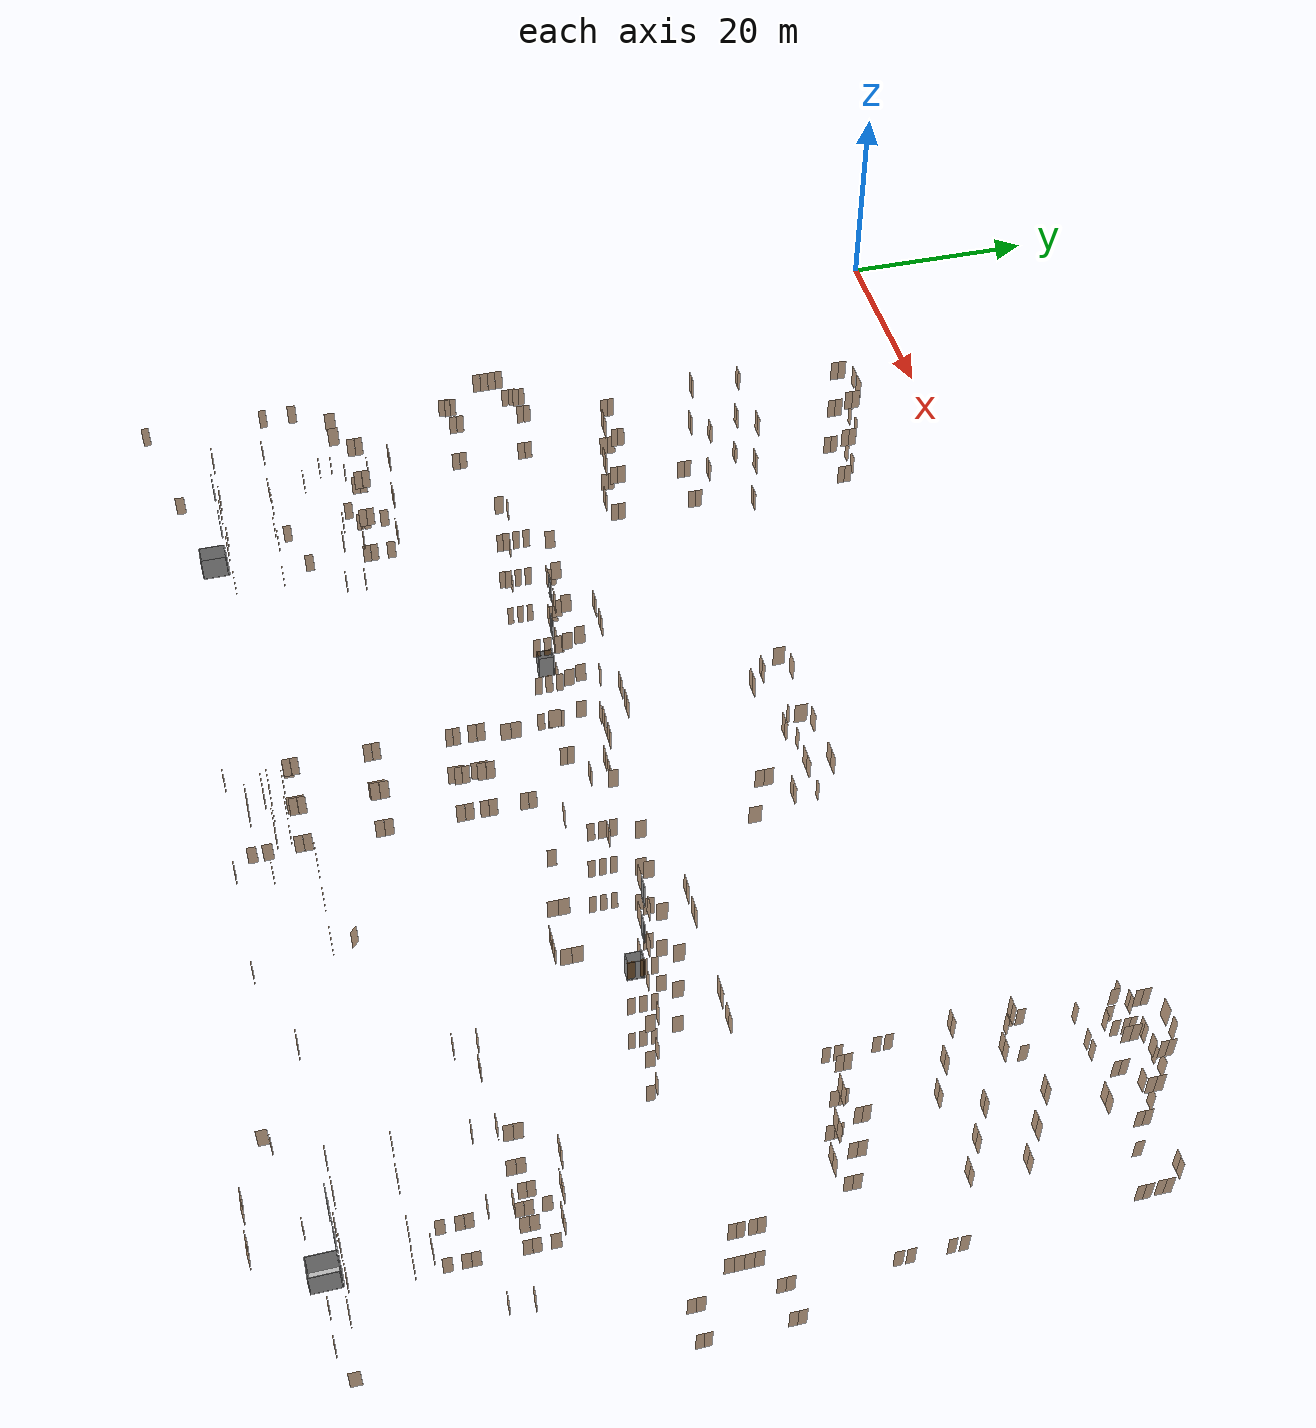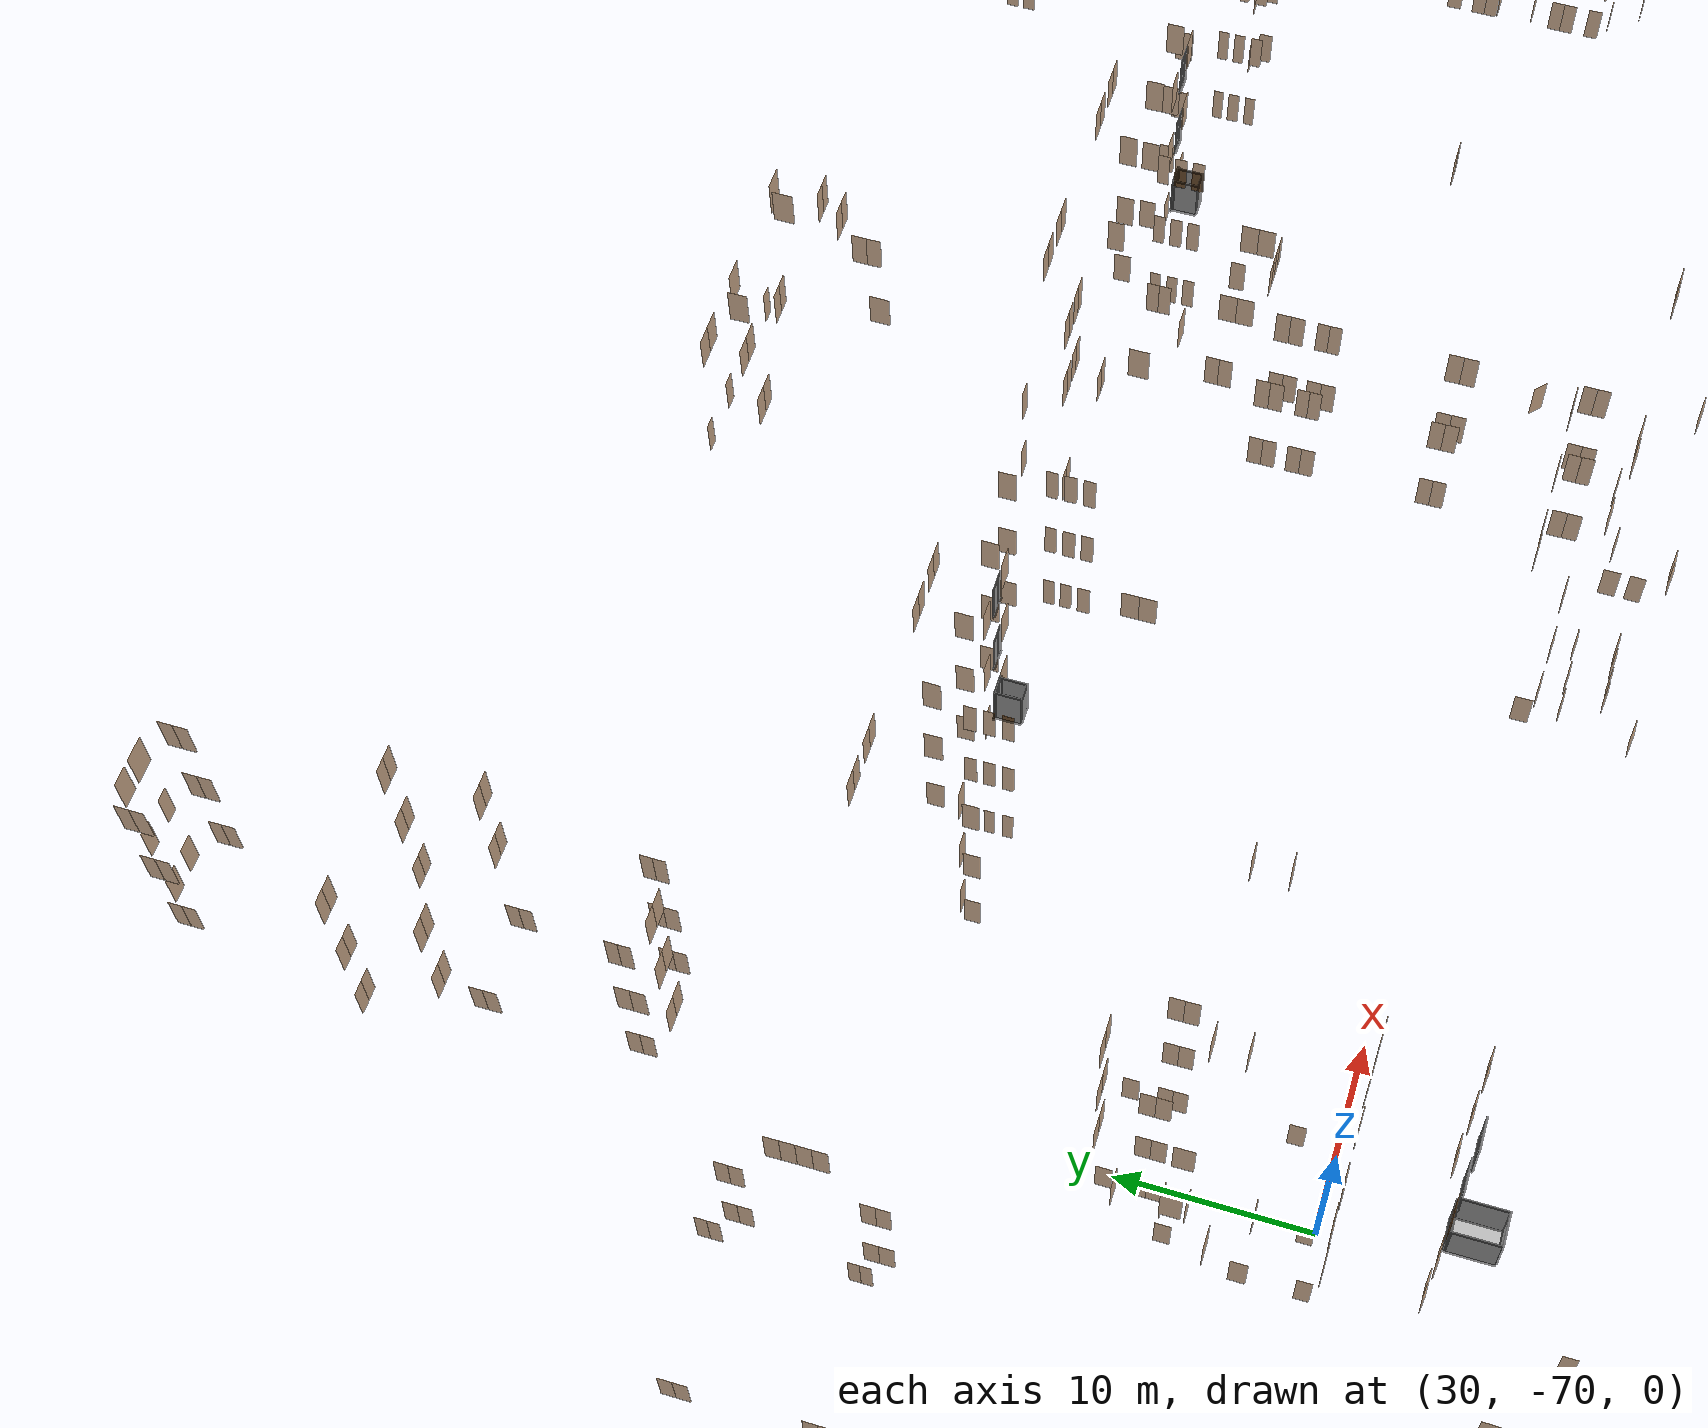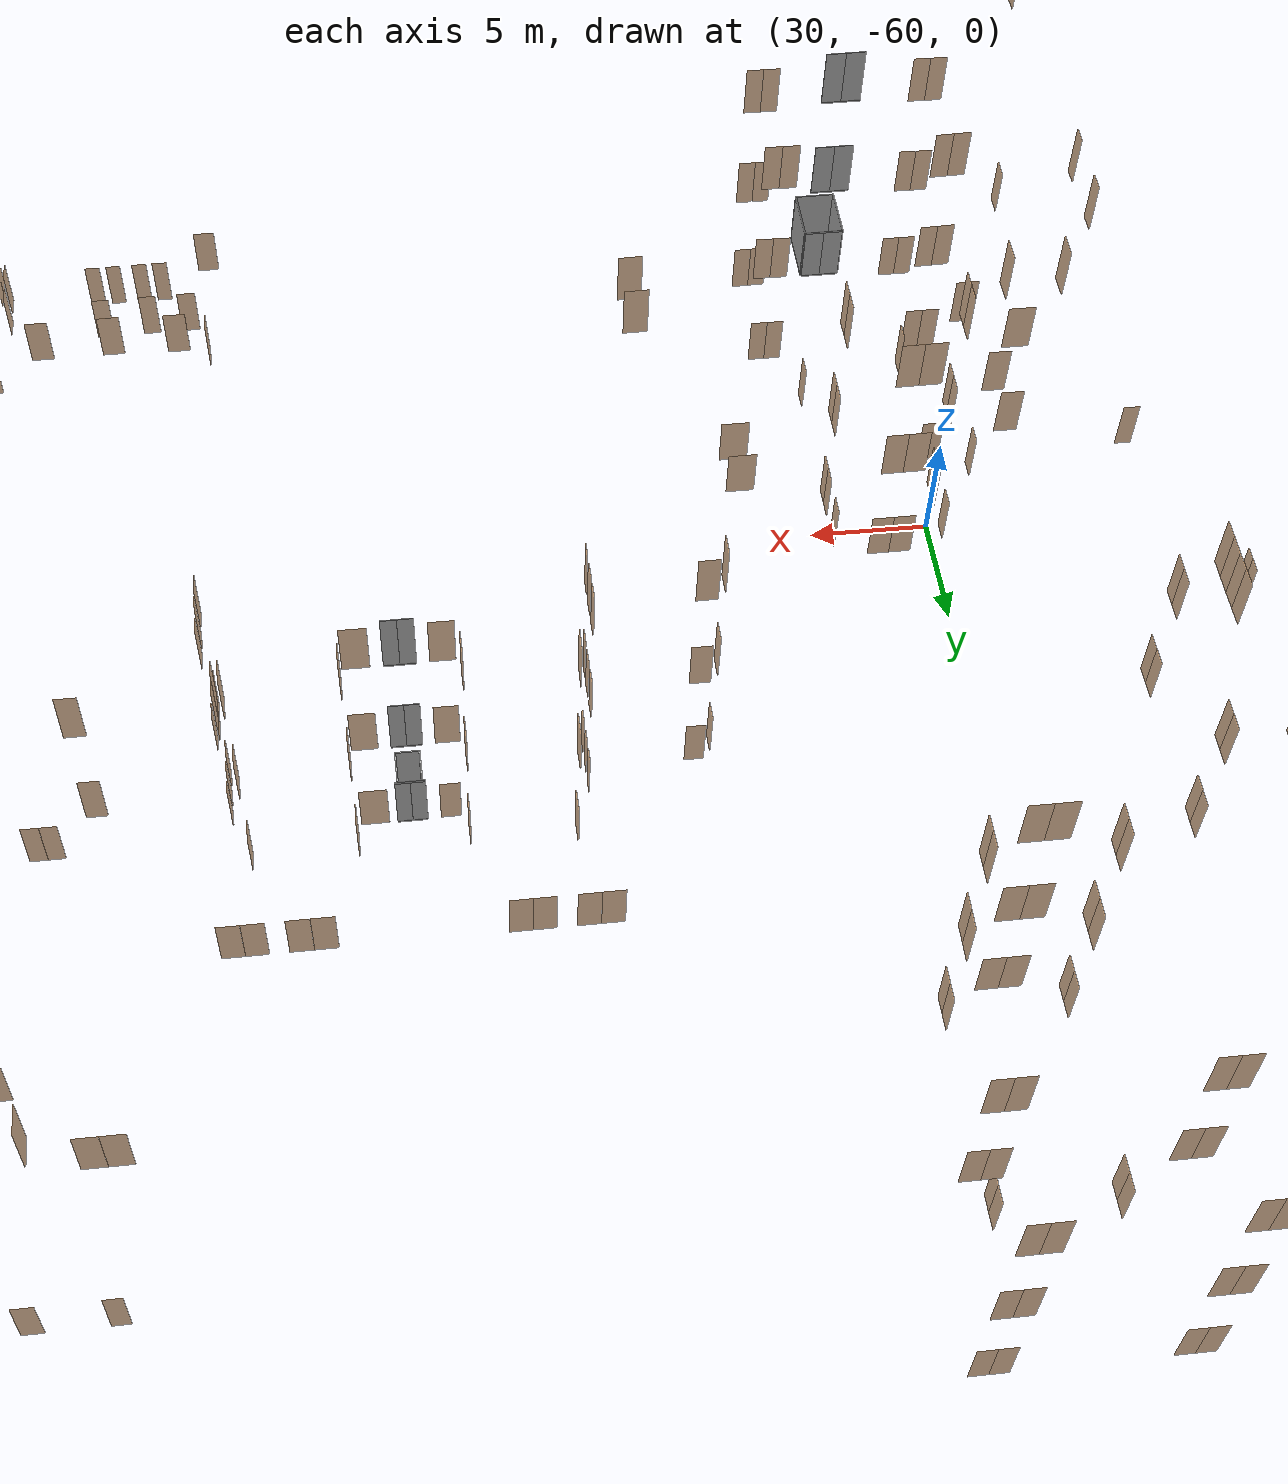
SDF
<sdf version="1.7">
 <world name="sim_world">
  <physics name="10ms" type="ode">
   <max_step_size>0.01</max_step_size>
   <real_time_factor>1.0</real_time_factor>
  </physics>
  <plugin filename="libgz-sim-physics-system.so" name="gz::sim::systems::Physics"/>
  <plugin filename="libgz-sim-user-commands-system.so" name="gz::sim::systems::UserCommands"/>
  <plugin filename="libgz-sim-scene-broadcaster-system.so" name="gz::sim::systems::SceneBroadcaster"/>
  <plugin filename="libdoor.so" name="door"/>
  <plugin filename="liblift.so" name="lift"/>
  <scene><ambient>1 1 1</ambient><background>0.8 0.8 0.8</background><grid>false</grid></scene>
  <light type="directional" name="sun">
   <pose>0 0 10 0 0 0</pose>
   <diffuse>1 1 1 1</diffuse>
   <specular>0.2 0.2 0.2 1</specular>
   <attenuation>
    <range>1000</range>
    <constant>0.09</constant>
    <linear>0.001</linear>
    <quadratic>0.001</quadratic>
   </attenuation>
   <direction>-0.5 0.1 -0.9</direction>
  </light>
  <model name="p1">
   <pose>13.92503185090813 -43.73868181683508 0.0 0 0 1.5707963267948966</pose>
   <link name="right">
    <pose>0.3680335397469694 0 1.11 0 0 0</pose>
    <visual name="right_visual">
     <geometry><box><size>0.7260670794939388 0.03 2.2</size></box></geometry>
     <material>
      <ambient>0.5 0.25 0 0.6</ambient>
      <diffuse>0.5 0.25 0 0.6</diffuse>
      <pbr><metal><metalness>0.0</metalness></metal></pbr>
     </material>
    </visual>
    <collision name="right_collision">
     <geometry><box><size>0.7260670794939388 0.03 2.2</size></box></geometry>
     <surface><contact><collide_bitmask>0x02</collide_bitmask></contact></surface>
    </collision>
    <inertial>
     <mass>50.0</mass>
     <inertia><ixx>20.17041666666667</ixx><iyy>22.363222516353577</iyy><izz>2.2003058496869072</izz></inertia>
    </inertial>
   </link>
   <joint name="right_joint" type="revolute">
    <parent>world</parent>
    <child>right</child>
    <axis><xyz>0 0 -1</xyz><limit><lower>0</lower><upper>1.57</upper></limit></axis>
    <pose>0.3680335397469694 0 0 0 0 0</pose>
   </joint>
   <link name="left">
    <pose>-0.3680335397469694 0 1.11 0 0 0</pose>
    <visual name="left_visual">
     <geometry><box><size>0.7260670794939388 0.03 2.2</size></box></geometry>
     <material>
      <ambient>0.5 0.25 0 0.6</ambient>
      <diffuse>0.5 0.25 0 0.6</diffuse>
      <pbr><metal><metalness>0.0</metalness></metal></pbr>
     </material>
    </visual>
    <collision name="left_collision">
     <geometry><box><size>0.7260670794939388 0.03 2.2</size></box></geometry>
     <surface><contact><collide_bitmask>0x02</collide_bitmask></contact></surface>
    </collision>
    <inertial>
     <mass>50.0</mass>
     <inertia><ixx>20.17041666666667</ixx><iyy>22.363222516353577</iyy><izz>2.2003058496869072</izz></inertia>
    </inertial>
   </link>
   <joint name="left_joint" type="revolute">
    <parent>world</parent>
    <child>left</child>
    <axis><xyz>0 0 -1</xyz><limit><lower>-1.57</lower><upper>0</upper></limit></axis>
    <pose>-0.3680335397469694 0 0 0 0 0</pose>
   </joint>
   <plugin name="register_component" filename="libregister_component.so">
    <component name="Door">
     <v_max_door>0.5</v_max_door>
     <a_max_door>0.3</a_max_door>
     <a_nom_door>0.15</a_nom_door>
     <dx_min_door>0.01</dx_min_door>
     <f_max_door>500.0</f_max_door>
     <ros_interface>true</ros_interface>
     <door name="p1" type="DoubleSwingDoor" left_joint_name="left_joint" right_joint_name="right_joint"/>
    </component>
   </plugin>
  </model>
  <model name="p2">
   <pose>13.961230778347318 -50.64991037302602 0.0 0 0 1.5707963267948966</pose>
   <link name="right">
    <pose>0.360861530028739 0 1.11 0 0 0</pose>
    <visual name="right_visual">
     <geometry><box><size>0.711723060057478 0.03 2.2</size></box></geometry>
     <material>
      <ambient>0.5 0.25 0 0.6</ambient>
      <diffuse>0.5 0.25 0 0.6</diffuse>
      <pbr><metal><metalness>0.0</metalness></metal></pbr>
     </material>
    </visual>
    <collision name="right_collision">
     <geometry><box><size>0.711723060057478 0.03 2.2</size></box></geometry>
     <surface><contact><collide_bitmask>0x02</collide_bitmask></contact></surface>
    </collision>
    <inertial>
     <mass>50.0</mass>
     <inertia><ixx>20.17041666666667</ixx><iyy>22.27729047590659</iyy><izz>2.1143738092399187</izz></inertia>
    </inertial>
   </link>
   <joint name="right_joint" type="revolute">
    <parent>world</parent>
    <child>right</child>
    <axis><xyz>0 0 -1</xyz><limit><lower>0</lower><upper>1.57</upper></limit></axis>
    <pose>0.360861530028739 0 0 0 0 0</pose>
   </joint>
   <link name="left">
    <pose>-0.360861530028739 0 1.11 0 0 0</pose>
    <visual name="left_visual">
     <geometry><box><size>0.711723060057478 0.03 2.2</size></box></geometry>
     <material>
      <ambient>0.5 0.25 0 0.6</ambient>
      <diffuse>0.5 0.25 0 0.6</diffuse>
      <pbr><metal><metalness>0.0</metalness></metal></pbr>
     </material>
    </visual>
    <collision name="left_collision">
     <geometry><box><size>0.711723060057478 0.03 2.2</size></box></geometry>
     <surface><contact><collide_bitmask>0x02</collide_bitmask></contact></surface>
    </collision>
    <inertial>
     <mass>50.0</mass>
     <inertia><ixx>20.17041666666667</ixx><iyy>22.27729047590659</iyy><izz>2.1143738092399187</izz></inertia>
    </inertial>
   </link>
   <joint name="left_joint" type="revolute">
    <parent>world</parent>
    <child>left</child>
    <axis><xyz>0 0 -1</xyz><limit><lower>-1.57</lower><upper>0</upper></limit></axis>
    <pose>-0.360861530028739 0 0 0 0 0</pose>
   </joint>
   <plugin name="register_component" filename="libregister_component.so">
    <component name="Door">
     <v_max_door>0.5</v_max_door>
     <a_max_door>0.3</a_max_door>
     <a_nom_door>0.15</a_nom_door>
     <dx_min_door>0.01</dx_min_door>
     <f_max_door>500.0</f_max_door>
     <ros_interface>true</ros_interface>
     <door name="p2" type="DoubleSwingDoor" left_joint_name="left_joint" right_joint_name="right_joint"/>
    </component>
   </plugin>
  </model>
  <model name="p3">
   <pose>22.712949245948284 -50.70411987792958 0.0 0 0 1.5778150838583305</pose>
   <link name="right">
    <pose>0.3815092045091061 0 1.11 0 0 0</pose>
    <visual name="right_visual">
     <geometry><box><size>0.7530184090182122 0.03 2.2</size></box></geometry>
     <material>
      <ambient>0.5 0.25 0 0.6</ambient>
      <diffuse>0.5 0.25 0 0.6</diffuse>
      <pbr><metal><metalness>0.0</metalness></metal></pbr>
     </material>
    </visual>
    <collision name="right_collision">
     <geometry><box><size>0.7530184090182122 0.03 2.2</size></box></geometry>
     <surface><contact><collide_bitmask>0x02</collide_bitmask></contact></surface>
    </collision>
    <inertial>
     <mass>50.0</mass>
     <inertia><ixx>20.17041666666667</ixx><iyy>22.529319684668</iyy><izz>2.3664030180013316</izz></inertia>
    </inertial>
   </link>
   <joint name="right_joint" type="revolute">
    <parent>world</parent>
    <child>right</child>
    <axis><xyz>0 0 -1</xyz><limit><lower>0</lower><upper>1.57</upper></limit></axis>
    <pose>0.3815092045091061 0 0 0 0 0</pose>
   </joint>
   <link name="left">
    <pose>-0.3815092045091061 0 1.11 0 0 0</pose>
    <visual name="left_visual">
     <geometry><box><size>0.7530184090182122 0.03 2.2</size></box></geometry>
     <material>
      <ambient>0.5 0.25 0 0.6</ambient>
      <diffuse>0.5 0.25 0 0.6</diffuse>
      <pbr><metal><metalness>0.0</metalness></metal></pbr>
     </material>
    </visual>
    <collision name="left_collision">
     <geometry><box><size>0.7530184090182122 0.03 2.2</size></box></geometry>
     <surface><contact><collide_bitmask>0x02</collide_bitmask></contact></surface>
    </collision>
    <inertial>
     <mass>50.0</mass>
     <inertia><ixx>20.17041666666667</ixx><iyy>22.529319684668</iyy><izz>2.3664030180013316</izz></inertia>
    </inertial>
   </link>
   <joint name="left_joint" type="revolute">
    <parent>world</parent>
    <child>left</child>
    <axis><xyz>0 0 -1</xyz><limit><lower>-1.57</lower><upper>0</upper></limit></axis>
    <pose>-0.3815092045091061 0 0 0 0 0</pose>
   </joint>
   <plugin name="register_component" filename="libregister_component.so">
    <component name="Door">
     <v_max_door>0.5</v_max_door>
     <a_max_door>0.3</a_max_door>
     <a_nom_door>0.15</a_nom_door>
     <dx_min_door>0.01</dx_min_door>
     <f_max_door>500.0</f_max_door>
     <ros_interface>true</ros_interface>
     <door name="p3" type="DoubleSwingDoor" left_joint_name="left_joint" right_joint_name="right_joint"/>
    </component>
   </plugin>
  </model>
  <model name="p4">
   <pose>22.707593849071152 -43.76862537406302 0.0 0 0 1.5707963267948966</pose>
   <link name="right">
    <pose>0.36870574205208584 0 1.11 0 0 0</pose>
    <visual name="right_visual">
     <geometry><box><size>0.7274114841041717 0.03 2.2</size></box></geometry>
     <material>
      <ambient>0.5 0.25 0 0.6</ambient>
      <diffuse>0.5 0.25 0 0.6</diffuse>
      <pbr><metal><metalness>0.0</metalness></metal></pbr>
     </material>
    </visual>
    <collision name="right_collision">
     <geometry><box><size>0.7274114841041717 0.03 2.2</size></box></geometry>
     <surface><contact><collide_bitmask>0x02</collide_bitmask></contact></surface>
    </collision>
    <inertial>
     <mass>50.0</mass>
     <inertia><ixx>20.17041666666667</ixx><iyy>22.37136444669431</iyy><izz>2.2084477800276403</izz></inertia>
    </inertial>
   </link>
   <joint name="right_joint" type="revolute">
    <parent>world</parent>
    <child>right</child>
    <axis><xyz>0 0 -1</xyz><limit><lower>0</lower><upper>1.57</upper></limit></axis>
    <pose>0.36870574205208584 0 0 0 0 0</pose>
   </joint>
   <link name="left">
    <pose>-0.36870574205208584 0 1.11 0 0 0</pose>
    <visual name="left_visual">
     <geometry><box><size>0.7274114841041717 0.03 2.2</size></box></geometry>
     <material>
      <ambient>0.5 0.25 0 0.6</ambient>
      <diffuse>0.5 0.25 0 0.6</diffuse>
      <pbr><metal><metalness>0.0</metalness></metal></pbr>
     </material>
    </visual>
    <collision name="left_collision">
     <geometry><box><size>0.7274114841041717 0.03 2.2</size></box></geometry>
     <surface><contact><collide_bitmask>0x02</collide_bitmask></contact></surface>
    </collision>
    <inertial>
     <mass>50.0</mass>
     <inertia><ixx>20.17041666666667</ixx><iyy>22.37136444669431</iyy><izz>2.2084477800276403</izz></inertia>
    </inertial>
   </link>
   <joint name="left_joint" type="revolute">
    <parent>world</parent>
    <child>left</child>
    <axis><xyz>0 0 -1</xyz><limit><lower>-1.57</lower><upper>0</upper></limit></axis>
    <pose>-0.36870574205208584 0 0 0 0 0</pose>
   </joint>
   <plugin name="register_component" filename="libregister_component.so">
    <component name="Door">
     <v_max_door>0.5</v_max_door>
     <a_max_door>0.3</a_max_door>
     <a_nom_door>0.15</a_nom_door>
     <dx_min_door>0.01</dx_min_door>
     <f_max_door>500.0</f_max_door>
     <ros_interface>true</ros_interface>
     <door name="p4" type="DoubleSwingDoor" left_joint_name="left_joint" right_joint_name="right_joint"/>
    </component>
   </plugin>
  </model>
  <model name="p5">
   <pose>31.846945275695557 -37.258029391721756 0.0 0 0 3.141592653589793</pose>
   <link name="right">
    <pose>0.44889781043524657 0 1.11 0 0 0</pose>
    <visual name="right_visual">
     <geometry><box><size>0.8877956208704931 0.03 2.2</size></box></geometry>
     <material>
      <ambient>0.5 0.25 0 0.6</ambient>
      <diffuse>0.5 0.25 0 0.6</diffuse>
      <pbr><metal><metalness>0.0</metalness></metal></pbr>
     </material>
    </visual>
    <collision name="right_collision">
     <geometry><box><size>0.8877956208704931 0.03 2.2</size></box></geometry>
     <surface><contact><collide_bitmask>0x02</collide_bitmask></contact></surface>
    </collision>
    <inertial>
     <mass>50.0</mass>
     <inertia><ixx>20.17041666666667</ixx><iyy>23.450754435153442</iyy><izz>3.2878377684867686</izz></inertia>
    </inertial>
   </link>
   <joint name="right_joint" type="revolute">
    <parent>world</parent>
    <child>right</child>
    <axis><xyz>0 0 -1</xyz><limit><lower>0</lower><upper>1.57</upper></limit></axis>
    <pose>0.44889781043524657 0 0 0 0 0</pose>
   </joint>
   <link name="left">
    <pose>-0.44889781043524657 0 1.11 0 0 0</pose>
    <visual name="left_visual">
     <geometry><box><size>0.8877956208704931 0.03 2.2</size></box></geometry>
     <material>
      <ambient>0.5 0.25 0 0.6</ambient>
      <diffuse>0.5 0.25 0 0.6</diffuse>
      <pbr><metal><metalness>0.0</metalness></metal></pbr>
     </material>
    </visual>
    <collision name="left_collision">
     <geometry><box><size>0.8877956208704931 0.03 2.2</size></box></geometry>
     <surface><contact><collide_bitmask>0x02</collide_bitmask></contact></surface>
    </collision>
    <inertial>
     <mass>50.0</mass>
     <inertia><ixx>20.17041666666667</ixx><iyy>23.450754435153442</iyy><izz>3.2878377684867686</izz></inertia>
    </inertial>
   </link>
   <joint name="left_joint" type="revolute">
    <parent>world</parent>
    <child>left</child>
    <axis><xyz>0 0 -1</xyz><limit><lower>-1.57</lower><upper>0</upper></limit></axis>
    <pose>-0.44889781043524657 0 0 0 0 0</pose>
   </joint>
   <plugin name="register_component" filename="libregister_component.so">
    <component name="Door">
     <v_max_door>0.5</v_max_door>
     <a_max_door>0.3</a_max_door>
     <a_nom_door>0.15</a_nom_door>
     <dx_min_door>0.01</dx_min_door>
     <f_max_door>500.0</f_max_door>
     <ros_interface>true</ros_interface>
     <door name="p5" type="DoubleSwingDoor" left_joint_name="left_joint" right_joint_name="right_joint"/>
    </component>
   </plugin>
  </model>
  <model name="p6">
   <pose>29.525769606826483 -36.40916565435101 0.0 0 0 -1.5653609225018528</pose>
   <link name="right">
    <pose>0.3577280184184884 0 1.11 0 0 0</pose>
    <visual name="right_visual">
     <geometry><box><size>0.7054560368369768 0.03 2.2</size></box></geometry>
     <material>
      <ambient>0.5 0.25 0 0.6</ambient>
      <diffuse>0.5 0.25 0 0.6</diffuse>
      <pbr><metal><metalness>0.0</metalness></metal></pbr>
     </material>
    </visual>
    <collision name="right_collision">
     <geometry><box><size>0.7054560368369768 0.03 2.2</size></box></geometry>
     <surface><contact><collide_bitmask>0x02</collide_bitmask></contact></surface>
    </collision>
    <inertial>
     <mass>50.0</mass>
     <inertia><ixx>20.17041666666667</ixx><iyy>22.240284249623897</iyy><izz>2.077367582957225</izz></inertia>
    </inertial>
   </link>
   <joint name="right_joint" type="revolute">
    <parent>world</parent>
    <child>right</child>
    <axis><xyz>0 0 -1</xyz><limit><lower>0</lower><upper>1.57</upper></limit></axis>
    <pose>0.3577280184184884 0 0 0 0 0</pose>
   </joint>
   <link name="left">
    <pose>-0.3577280184184884 0 1.11 0 0 0</pose>
    <visual name="left_visual">
     <geometry><box><size>0.7054560368369768 0.03 2.2</size></box></geometry>
     <material>
      <ambient>0.5 0.25 0 0.6</ambient>
      <diffuse>0.5 0.25 0 0.6</diffuse>
      <pbr><metal><metalness>0.0</metalness></metal></pbr>
     </material>
    </visual>
    <collision name="left_collision">
     <geometry><box><size>0.7054560368369768 0.03 2.2</size></box></geometry>
     <surface><contact><collide_bitmask>0x02</collide_bitmask></contact></surface>
    </collision>
    <inertial>
     <mass>50.0</mass>
     <inertia><ixx>20.17041666666667</ixx><iyy>22.240284249623897</iyy><izz>2.077367582957225</izz></inertia>
    </inertial>
   </link>
   <joint name="left_joint" type="revolute">
    <parent>world</parent>
    <child>left</child>
    <axis><xyz>0 0 -1</xyz><limit><lower>-1.57</lower><upper>0</upper></limit></axis>
    <pose>-0.3577280184184884 0 0 0 0 0</pose>
   </joint>
   <plugin name="register_component" filename="libregister_component.so">
    <component name="Door">
     <v_max_door>0.5</v_max_door>
     <a_max_door>0.3</a_max_door>
     <a_nom_door>0.15</a_nom_door>
     <dx_min_door>0.01</dx_min_door>
     <f_max_door>500.0</f_max_door>
     <ros_interface>true</ros_interface>
     <door name="p6" type="DoubleSwingDoor" left_joint_name="left_joint" right_joint_name="right_joint"/>
    </component>
   </plugin>
  </model>
  <model name="p7">
   <pose>34.15456579064326 -36.411565583242 0.0 0 0 1.5727803300521501</pose>
   <link name="right">
    <pose>0.3640121531227989 0 1.11 0 0 0</pose>
    <visual name="right_visual">
     <geometry><box><size>0.7180243062455978 0.03 2.2</size></box></geometry>
     <material>
      <ambient>0.5 0.25 0 0.6</ambient>
      <diffuse>0.5 0.25 0 0.6</diffuse>
      <pbr><metal><metalness>0.0</metalness></metal></pbr>
     </material>
    </visual>
    <collision name="right_collision">
     <geometry><box><size>0.7180243062455978 0.03 2.2</size></box></geometry>
     <surface><contact><collide_bitmask>0x02</collide_bitmask></contact></surface>
    </collision>
    <inertial>
     <mass>50.0</mass>
     <inertia><ixx>20.17041666666667</ixx><iyy>22.31482876816447</iyy><izz>2.1519121014977998</izz></inertia>
    </inertial>
   </link>
   <joint name="right_joint" type="revolute">
    <parent>world</parent>
    <child>right</child>
    <axis><xyz>0 0 -1</xyz><limit><lower>0</lower><upper>1.57</upper></limit></axis>
    <pose>0.3640121531227989 0 0 0 0 0</pose>
   </joint>
   <link name="left">
    <pose>-0.3640121531227989 0 1.11 0 0 0</pose>
    <visual name="left_visual">
     <geometry><box><size>0.7180243062455978 0.03 2.2</size></box></geometry>
     <material>
      <ambient>0.5 0.25 0 0.6</ambient>
      <diffuse>0.5 0.25 0 0.6</diffuse>
      <pbr><metal><metalness>0.0</metalness></metal></pbr>
     </material>
    </visual>
    <collision name="left_collision">
     <geometry><box><size>0.7180243062455978 0.03 2.2</size></box></geometry>
     <surface><contact><collide_bitmask>0x02</collide_bitmask></contact></surface>
    </collision>
    <inertial>
     <mass>50.0</mass>
     <inertia><ixx>20.17041666666667</ixx><iyy>22.31482876816447</iyy><izz>2.1519121014977998</izz></inertia>
    </inertial>
   </link>
   <joint name="left_joint" type="revolute">
    <parent>world</parent>
    <child>left</child>
    <axis><xyz>0 0 -1</xyz><limit><lower>-1.57</lower><upper>0</upper></limit></axis>
    <pose>-0.3640121531227989 0 0 0 0 0</pose>
   </joint>
   <plugin name="register_component" filename="libregister_component.so">
    <component name="Door">
     <v_max_door>0.5</v_max_door>
     <a_max_door>0.3</a_max_door>
     <a_nom_door>0.15</a_nom_door>
     <dx_min_door>0.01</dx_min_door>
     <f_max_door>500.0</f_max_door>
     <ros_interface>true</ros_interface>
     <door name="p7" type="DoubleSwingDoor" left_joint_name="left_joint" right_joint_name="right_joint"/>
    </component>
   </plugin>
  </model>
  <model name="p8">
   <pose>29.51809205653168 -28.285695238659613 0.0 0 0 -1.565509718267845</pose>
   <link name="right">
    <pose>0.3583388346022328 0 1.11 0 0 0</pose>
    <visual name="right_visual">
     <geometry><box><size>0.7066776692044656 0.03 2.2</size></box></geometry>
     <material>
      <ambient>0.5 0.25 0 0.6</ambient>
      <diffuse>0.5 0.25 0 0.6</diffuse>
      <pbr><metal><metalness>0.0</metalness></metal></pbr>
     </material>
    </visual>
    <collision name="right_collision">
     <geometry><box><size>0.7066776692044656 0.03 2.2</size></box></geometry>
     <surface><contact><collide_bitmask>0x02</collide_bitmask></contact></surface>
    </collision>
    <inertial>
     <mass>50.0</mass>
     <inertia><ixx>20.17041666666667</ixx><iyy>22.247472200634405</iyy><izz>2.084555533967734</izz></inertia>
    </inertial>
   </link>
   <joint name="right_joint" type="revolute">
    <parent>world</parent>
    <child>right</child>
    <axis><xyz>0 0 -1</xyz><limit><lower>0</lower><upper>1.57</upper></limit></axis>
    <pose>0.3583388346022328 0 0 0 0 0</pose>
   </joint>
   <link name="left">
    <pose>-0.3583388346022328 0 1.11 0 0 0</pose>
    <visual name="left_visual">
     <geometry><box><size>0.7066776692044656 0.03 2.2</size></box></geometry>
     <material>
      <ambient>0.5 0.25 0 0.6</ambient>
      <diffuse>0.5 0.25 0 0.6</diffuse>
      <pbr><metal><metalness>0.0</metalness></metal></pbr>
     </material>
    </visual>
    <collision name="left_collision">
     <geometry><box><size>0.7066776692044656 0.03 2.2</size></box></geometry>
     <surface><contact><collide_bitmask>0x02</collide_bitmask></contact></surface>
    </collision>
    <inertial>
     <mass>50.0</mass>
     <inertia><ixx>20.17041666666667</ixx><iyy>22.247472200634405</iyy><izz>2.084555533967734</izz></inertia>
    </inertial>
   </link>
   <joint name="left_joint" type="revolute">
    <parent>world</parent>
    <child>left</child>
    <axis><xyz>0 0 -1</xyz><limit><lower>-1.57</lower><upper>0</upper></limit></axis>
    <pose>-0.3583388346022328 0 0 0 0 0</pose>
   </joint>
   <plugin name="register_component" filename="libregister_component.so">
    <component name="Door">
     <v_max_door>0.5</v_max_door>
     <a_max_door>0.3</a_max_door>
     <a_nom_door>0.15</a_nom_door>
     <dx_min_door>0.01</dx_min_door>
     <f_max_door>500.0</f_max_door>
     <ros_interface>true</ros_interface>
     <door name="p8" type="DoubleSwingDoor" left_joint_name="left_joint" right_joint_name="right_joint"/>
    </component>
   </plugin>
  </model>
  <model name="p9">
   <pose>34.15017703179167 -28.329493940920287 0.0 0 0 1.5749637556473903</pose>
   <link name="right">
    <pose>0.35325926742053404 0 1.11 0 0 0</pose>
    <visual name="right_visual">
     <geometry><box><size>0.6965185348410681 0.03 2.2</size></box></geometry>
     <material>
      <ambient>0.5 0.25 0 0.6</ambient>
      <diffuse>0.5 0.25 0 0.6</diffuse>
      <pbr><metal><metalness>0.0</metalness></metal></pbr>
     </material>
    </visual>
    <collision name="right_collision">
     <geometry><box><size>0.6965185348410681 0.03 2.2</size></box></geometry>
     <surface><contact><collide_bitmask>0x02</collide_bitmask></contact></surface>
    </collision>
    <inertial>
     <mass>50.0</mass>
     <inertia><ixx>20.17041666666667</ixx><iyy>22.188075289071456</iyy><izz>2.025158622404784</izz></inertia>
    </inertial>
   </link>
   <joint name="right_joint" type="revolute">
    <parent>world</parent>
    <child>right</child>
    <axis><xyz>0 0 -1</xyz><limit><lower>0</lower><upper>1.57</upper></limit></axis>
    <pose>0.35325926742053404 0 0 0 0 0</pose>
   </joint>
   <link name="left">
    <pose>-0.35325926742053404 0 1.11 0 0 0</pose>
    <visual name="left_visual">
     <geometry><box><size>0.6965185348410681 0.03 2.2</size></box></geometry>
     <material>
      <ambient>0.5 0.25 0 0.6</ambient>
      <diffuse>0.5 0.25 0 0.6</diffuse>
      <pbr><metal><metalness>0.0</metalness></metal></pbr>
     </material>
    </visual>
    <collision name="left_collision">
     <geometry><box><size>0.6965185348410681 0.03 2.2</size></box></geometry>
     <surface><contact><collide_bitmask>0x02</collide_bitmask></contact></surface>
    </collision>
    <inertial>
     <mass>50.0</mass>
     <inertia><ixx>20.17041666666667</ixx><iyy>22.188075289071456</iyy><izz>2.025158622404784</izz></inertia>
    </inertial>
   </link>
   <joint name="left_joint" type="revolute">
    <parent>world</parent>
    <child>left</child>
    <axis><xyz>0 0 -1</xyz><limit><lower>-1.57</lower><upper>0</upper></limit></axis>
    <pose>-0.35325926742053404 0 0 0 0 0</pose>
   </joint>
   <plugin name="register_component" filename="libregister_component.so">
    <component name="Door">
     <v_max_door>0.5</v_max_door>
     <a_max_door>0.3</a_max_door>
     <a_nom_door>0.15</a_nom_door>
     <dx_min_door>0.01</dx_min_door>
     <f_max_door>500.0</f_max_door>
     <ros_interface>true</ros_interface>
     <door name="p9" type="DoubleSwingDoor" left_joint_name="left_joint" right_joint_name="right_joint"/>
    </component>
   </plugin>
  </model>
  <model name="p10">
   <pose>35.435105626499976 -22.487155936120427 0.0 0 0 3.141592653589793</pose>
   <link name="right">
    <pose>0.36420031999051794 0 1.11 0 0 0</pose>
    <visual name="right_visual">
     <geometry><box><size>0.7184006399810359 0.03 2.2</size></box></geometry>
     <material>
      <ambient>0.5 0.25 0 0.6</ambient>
      <diffuse>0.5 0.25 0 0.6</diffuse>
      <pbr><metal><metalness>0.0</metalness></metal></pbr>
     </material>
    </visual>
    <collision name="right_collision">
     <geometry><box><size>0.7184006399810359 0.03 2.2</size></box></geometry>
     <surface><contact><collide_bitmask>0x02</collide_bitmask></contact></surface>
    </collision>
    <inertial>
     <mass>50.0</mass>
     <inertia><ixx>20.17041666666667</ixx><iyy>22.31708116468818</iyy><izz>2.1541644980215082</izz></inertia>
    </inertial>
   </link>
   <joint name="right_joint" type="revolute">
    <parent>world</parent>
    <child>right</child>
    <axis><xyz>0 0 -1</xyz><limit><lower>0</lower><upper>1.57</upper></limit></axis>
    <pose>0.36420031999051794 0 0 0 0 0</pose>
   </joint>
   <link name="left">
    <pose>-0.36420031999051794 0 1.11 0 0 0</pose>
    <visual name="left_visual">
     <geometry><box><size>0.7184006399810359 0.03 2.2</size></box></geometry>
     <material>
      <ambient>0.5 0.25 0 0.6</ambient>
      <diffuse>0.5 0.25 0 0.6</diffuse>
      <pbr><metal><metalness>0.0</metalness></metal></pbr>
     </material>
    </visual>
    <collision name="left_collision">
     <geometry><box><size>0.7184006399810359 0.03 2.2</size></box></geometry>
     <surface><contact><collide_bitmask>0x02</collide_bitmask></contact></surface>
    </collision>
    <inertial>
     <mass>50.0</mass>
     <inertia><ixx>20.17041666666667</ixx><iyy>22.31708116468818</iyy><izz>2.1541644980215082</izz></inertia>
    </inertial>
   </link>
   <joint name="left_joint" type="revolute">
    <parent>world</parent>
    <child>left</child>
    <axis><xyz>0 0 -1</xyz><limit><lower>-1.57</lower><upper>0</upper></limit></axis>
    <pose>-0.36420031999051794 0 0 0 0 0</pose>
   </joint>
   <plugin name="register_component" filename="libregister_component.so">
    <component name="Door">
     <v_max_door>0.5</v_max_door>
     <a_max_door>0.3</a_max_door>
     <a_nom_door>0.15</a_nom_door>
     <dx_min_door>0.01</dx_min_door>
     <f_max_door>500.0</f_max_door>
     <ros_interface>true</ros_interface>
     <door name="p10" type="DoubleSwingDoor" left_joint_name="left_joint" right_joint_name="right_joint"/>
    </component>
   </plugin>
  </model>
  <model name="p11">
   <pose>28.260651536250798 -22.460001185150087 0.0 0 0 3.141592653589793</pose>
   <link name="right">
    <pose>0.3734333797517122 0 1.11 0 0 0</pose>
    <visual name="right_visual">
     <geometry><box><size>0.7368667595034244 0.03 2.2</size></box></geometry>
     <material>
      <ambient>0.5 0.25 0 0.6</ambient>
      <diffuse>0.5 0.25 0 0.6</diffuse>
      <pbr><metal><metalness>0.0</metalness></metal></pbr>
     </material>
    </visual>
    <collision name="right_collision">
     <geometry><box><size>0.7368667595034244 0.03 2.2</size></box></geometry>
     <surface><contact><collide_bitmask>0x02</collide_bitmask></contact></surface>
    </collision>
    <inertial>
     <mass>50.0</mass>
     <inertia><ixx>20.17041666666667</ixx><iyy>22.42905258858783</iyy><izz>2.2661359219211565</izz></inertia>
    </inertial>
   </link>
   <joint name="right_joint" type="revolute">
    <parent>world</parent>
    <child>right</child>
    <axis><xyz>0 0 -1</xyz><limit><lower>0</lower><upper>1.57</upper></limit></axis>
    <pose>0.3734333797517122 0 0 0 0 0</pose>
   </joint>
   <link name="left">
    <pose>-0.3734333797517122 0 1.11 0 0 0</pose>
    <visual name="left_visual">
     <geometry><box><size>0.7368667595034244 0.03 2.2</size></box></geometry>
     <material>
      <ambient>0.5 0.25 0 0.6</ambient>
      <diffuse>0.5 0.25 0 0.6</diffuse>
      <pbr><metal><metalness>0.0</metalness></metal></pbr>
     </material>
    </visual>
    <collision name="left_collision">
     <geometry><box><size>0.7368667595034244 0.03 2.2</size></box></geometry>
     <surface><contact><collide_bitmask>0x02</collide_bitmask></contact></surface>
    </collision>
    <inertial>
     <mass>50.0</mass>
     <inertia><ixx>20.17041666666667</ixx><iyy>22.42905258858783</iyy><izz>2.2661359219211565</izz></inertia>
    </inertial>
   </link>
   <joint name="left_joint" type="revolute">
    <parent>world</parent>
    <child>left</child>
    <axis><xyz>0 0 -1</xyz><limit><lower>-1.57</lower><upper>0</upper></limit></axis>
    <pose>-0.3734333797517122 0 0 0 0 0</pose>
   </joint>
   <plugin name="register_component" filename="libregister_component.so">
    <component name="Door">
     <v_max_door>0.5</v_max_door>
     <a_max_door>0.3</a_max_door>
     <a_nom_door>0.15</a_nom_door>
     <dx_min_door>0.01</dx_min_door>
     <f_max_door>500.0</f_max_door>
     <ros_interface>true</ros_interface>
     <door name="p11" type="DoubleSwingDoor" left_joint_name="left_joint" right_joint_name="right_joint"/>
    </component>
   </plugin>
  </model>
  <model name="p12">
   <pose>29.474815561020435 -12.36847797102309 0.0 0 0 -1.5707963267948966</pose>
   <link name="right">
    <pose>0.36403365826197787 0 1.11 0 0 0</pose>
    <visual name="right_visual">
     <geometry><box><size>0.7180673165239557 0.03 2.2</size></box></geometry>
     <material>
      <ambient>0.5 0.25 0 0.6</ambient>
      <diffuse>0.5 0.25 0 0.6</diffuse>
      <pbr><metal><metalness>0.0</metalness></metal></pbr>
     </material>
    </visual>
    <collision name="right_collision">
     <geometry><box><size>0.7180673165239557 0.03 2.2</size></box></geometry>
     <surface><contact><collide_bitmask>0x02</collide_bitmask></contact></surface>
    </collision>
    <inertial>
     <mass>50.0</mass>
     <inertia><ixx>20.17041666666667</ixx><iyy>22.315086129416315</iyy><izz>2.1521694627496455</izz></inertia>
    </inertial>
   </link>
   <joint name="right_joint" type="revolute">
    <parent>world</parent>
    <child>right</child>
    <axis><xyz>0 0 -1</xyz><limit><lower>0</lower><upper>1.57</upper></limit></axis>
    <pose>0.36403365826197787 0 0 0 0 0</pose>
   </joint>
   <link name="left">
    <pose>-0.36403365826197787 0 1.11 0 0 0</pose>
    <visual name="left_visual">
     <geometry><box><size>0.7180673165239557 0.03 2.2</size></box></geometry>
     <material>
      <ambient>0.5 0.25 0 0.6</ambient>
      <diffuse>0.5 0.25 0 0.6</diffuse>
      <pbr><metal><metalness>0.0</metalness></metal></pbr>
     </material>
    </visual>
    <collision name="left_collision">
     <geometry><box><size>0.7180673165239557 0.03 2.2</size></box></geometry>
     <surface><contact><collide_bitmask>0x02</collide_bitmask></contact></surface>
    </collision>
    <inertial>
     <mass>50.0</mass>
     <inertia><ixx>20.17041666666667</ixx><iyy>22.315086129416315</iyy><izz>2.1521694627496455</izz></inertia>
    </inertial>
   </link>
   <joint name="left_joint" type="revolute">
    <parent>world</parent>
    <child>left</child>
    <axis><xyz>0 0 -1</xyz><limit><lower>-1.57</lower><upper>0</upper></limit></axis>
    <pose>-0.36403365826197787 0 0 0 0 0</pose>
   </joint>
   <plugin name="register_component" filename="libregister_component.so">
    <component name="Door">
     <v_max_door>0.5</v_max_door>
     <a_max_door>0.3</a_max_door>
     <a_nom_door>0.15</a_nom_door>
     <dx_min_door>0.01</dx_min_door>
     <f_max_door>500.0</f_max_door>
     <ros_interface>true</ros_interface>
     <door name="p12" type="DoubleSwingDoor" left_joint_name="left_joint" right_joint_name="right_joint"/>
    </component>
   </plugin>
  </model>
  <model name="p13">
   <pose>30.957216082486468 -11.060238955882797 0.0 0 0 -3.1332152078264395</pose>
   <link name="right">
    <pose>0 0 1.11 0 0 0</pose>
    <visual name="right_visual">
     <geometry><box><size>0.9847165442564862 0.03 2.2</size></box></geometry>
     <material>
      <ambient>0.5 0.25 0 0.6</ambient>
      <diffuse>0.5 0.25 0 0.6</diffuse>
      <pbr><metal><metalness>0.0</metalness></metal></pbr>
     </material>
    </visual>
    <collision name="right_collision">
     <geometry><box><size>0.9847165442564862 0.03 2.2</size></box></geometry>
     <surface><contact><collide_bitmask>0x02</collide_bitmask></contact></surface>
    </collision>
    <inertial>
     <mass>50.0</mass>
     <inertia><ixx>20.17041666666667</ixx><iyy>24.206944468885155</iyy><izz>4.044027802218485</izz></inertia>
    </inertial>
   </link>
   <joint name="right_joint" type="revolute">
    <parent>world</parent>
    <child>right</child>
    <axis><xyz>0 0 1</xyz><limit><lower>0</lower><upper>1.57</upper></limit></axis>
    <pose>0.49735827212824313 0 0 0 0 0</pose>
   </joint>
   <plugin name="register_component" filename="libregister_component.so">
    <component name="Door">
     <v_max_door>0.5</v_max_door>
     <a_max_door>0.3</a_max_door>
     <a_nom_door>0.15</a_nom_door>
     <dx_min_door>0.01</dx_min_door>
     <f_max_door>500.0</f_max_door>
     <ros_interface>true</ros_interface>
     <door name="p13" type="SwingDoor" left_joint_name="empty_joint" right_joint_name="right_joint"/>
    </component>
   </plugin>
  </model>
  <model name="p14">
   <pose>32.72966356552401 -11.05352804361353 0.0 0 0 0.005124029352961401</pose>
   <link name="right">
    <pose>0 0 1.11 0 0 0</pose>
    <visual name="right_visual">
     <geometry><box><size>0.9831169454826049 0.03 2.2</size></box></geometry>
     <material>
      <ambient>0.5 0.25 0 0.6</ambient>
      <diffuse>0.5 0.25 0 0.6</diffuse>
      <pbr><metal><metalness>0.0</metalness></metal></pbr>
     </material>
    </visual>
    <collision name="right_collision">
     <geometry><box><size>0.9831169454826049 0.03 2.2</size></box></geometry>
     <surface><contact><collide_bitmask>0x02</collide_bitmask></contact></surface>
    </collision>
    <inertial>
     <mass>50.0</mass>
     <inertia><ixx>20.17041666666667</ixx><iyy>24.193828868729366</iyy><izz>4.030912202062696</izz></inertia>
    </inertial>
   </link>
   <joint name="right_joint" type="revolute">
    <parent>world</parent>
    <child>right</child>
    <axis><xyz>0 0 -1</xyz><limit><lower>0</lower><upper>1.57</upper></limit></axis>
    <pose>0.49655847274130244 0 0 0 0 0</pose>
   </joint>
   <plugin name="register_component" filename="libregister_component.so">
    <component name="Door">
     <v_max_door>0.5</v_max_door>
     <a_max_door>0.3</a_max_door>
     <a_nom_door>0.15</a_nom_door>
     <dx_min_door>0.01</dx_min_door>
     <f_max_door>500.0</f_max_door>
     <ros_interface>true</ros_interface>
     <door name="p14" type="SwingDoor" left_joint_name="empty_joint" right_joint_name="right_joint"/>
    </component>
   </plugin>
  </model>
  <model name="p15">
   <pose>34.207986430031724 -12.349534087878887 0.0 0 0 1.5775430026090258</pose>
   <link name="right">
    <pose>0.35736976701174594 0 1.11 0 0 0</pose>
    <visual name="right_visual">
     <geometry><box><size>0.7047395340234919 0.03 2.2</size></box></geometry>
     <material>
      <ambient>0.5 0.25 0 0.6</ambient>
      <diffuse>0.5 0.25 0 0.6</diffuse>
      <pbr><metal><metalness>0.0</metalness></metal></pbr>
     </material>
    </visual>
    <collision name="right_collision">
     <geometry><box><size>0.7047395340234919 0.03 2.2</size></box></geometry>
     <surface><contact><collide_bitmask>0x02</collide_bitmask></contact></surface>
    </collision>
    <inertial>
     <mass>50.0</mass>
     <inertia><ixx>20.17041666666667</ixx><iyy>22.23607421173187</iyy><izz>2.073157545065202</izz></inertia>
    </inertial>
   </link>
   <joint name="right_joint" type="revolute">
    <parent>world</parent>
    <child>right</child>
    <axis><xyz>0 0 -1</xyz><limit><lower>0</lower><upper>1.57</upper></limit></axis>
    <pose>0.35736976701174594 0 0 0 0 0</pose>
   </joint>
   <link name="left">
    <pose>-0.35736976701174594 0 1.11 0 0 0</pose>
    <visual name="left_visual">
     <geometry><box><size>0.7047395340234919 0.03 2.2</size></box></geometry>
     <material>
      <ambient>0.5 0.25 0 0.6</ambient>
      <diffuse>0.5 0.25 0 0.6</diffuse>
      <pbr><metal><metalness>0.0</metalness></metal></pbr>
     </material>
    </visual>
    <collision name="left_collision">
     <geometry><box><size>0.7047395340234919 0.03 2.2</size></box></geometry>
     <surface><contact><collide_bitmask>0x02</collide_bitmask></contact></surface>
    </collision>
    <inertial>
     <mass>50.0</mass>
     <inertia><ixx>20.17041666666667</ixx><iyy>22.23607421173187</iyy><izz>2.073157545065202</izz></inertia>
    </inertial>
   </link>
   <joint name="left_joint" type="revolute">
    <parent>world</parent>
    <child>left</child>
    <axis><xyz>0 0 -1</xyz><limit><lower>-1.57</lower><upper>0</upper></limit></axis>
    <pose>-0.35736976701174594 0 0 0 0 0</pose>
   </joint>
   <plugin name="register_component" filename="libregister_component.so">
    <component name="Door">
     <v_max_door>0.5</v_max_door>
     <a_max_door>0.3</a_max_door>
     <a_nom_door>0.15</a_nom_door>
     <dx_min_door>0.01</dx_min_door>
     <f_max_door>500.0</f_max_door>
     <ros_interface>true</ros_interface>
     <door name="p15" type="DoubleSwingDoor" left_joint_name="left_joint" right_joint_name="right_joint"/>
    </component>
   </plugin>
  </model>
  <model name="p16">
   <pose>31.855433913069263 -58.77063642558743 0.0 0 0 0.0</pose>
   <link name="right">
    <pose>0.4618529821338617 0 1.11 0 0 0</pose>
    <visual name="right_visual">
     <geometry><box><size>0.9137059642677234 0.03 2.2</size></box></geometry>
     <material>
      <ambient>0.5 0.25 0 0.6</ambient>
      <diffuse>0.5 0.25 0 0.6</diffuse>
      <pbr><metal><metalness>0.0</metalness></metal></pbr>
     </material>
    </visual>
    <collision name="right_collision">
     <geometry><box><size>0.9137059642677234 0.03 2.2</size></box></geometry>
     <surface><contact><collide_bitmask>0x02</collide_bitmask></contact></surface>
    </collision>
    <inertial>
     <mass>50.0</mass>
     <inertia><ixx>20.17041666666667</ixx><iyy>23.645244121410048</iyy><izz>3.4823274547433765</izz></inertia>
    </inertial>
   </link>
   <joint name="right_joint" type="revolute">
    <parent>world</parent>
    <child>right</child>
    <axis><xyz>0 0 -1</xyz><limit><lower>0</lower><upper>1.57</upper></limit></axis>
    <pose>0.4618529821338617 0 0 0 0 0</pose>
   </joint>
   <link name="left">
    <pose>-0.4618529821338617 0 1.11 0 0 0</pose>
    <visual name="left_visual">
     <geometry><box><size>0.9137059642677234 0.03 2.2</size></box></geometry>
     <material>
      <ambient>0.5 0.25 0 0.6</ambient>
      <diffuse>0.5 0.25 0 0.6</diffuse>
      <pbr><metal><metalness>0.0</metalness></metal></pbr>
     </material>
    </visual>
    <collision name="left_collision">
     <geometry><box><size>0.9137059642677234 0.03 2.2</size></box></geometry>
     <surface><contact><collide_bitmask>0x02</collide_bitmask></contact></surface>
    </collision>
    <inertial>
     <mass>50.0</mass>
     <inertia><ixx>20.17041666666667</ixx><iyy>23.645244121410048</iyy><izz>3.4823274547433765</izz></inertia>
    </inertial>
   </link>
   <joint name="left_joint" type="revolute">
    <parent>world</parent>
    <child>left</child>
    <axis><xyz>0 0 -1</xyz><limit><lower>-1.57</lower><upper>0</upper></limit></axis>
    <pose>-0.4618529821338617 0 0 0 0 0</pose>
   </joint>
   <plugin name="register_component" filename="libregister_component.so">
    <component name="Door">
     <v_max_door>0.5</v_max_door>
     <a_max_door>0.3</a_max_door>
     <a_nom_door>0.15</a_nom_door>
     <dx_min_door>0.01</dx_min_door>
     <f_max_door>500.0</f_max_door>
     <ros_interface>true</ros_interface>
     <door name="p16" type="DoubleSwingDoor" left_joint_name="left_joint" right_joint_name="right_joint"/>
    </component>
   </plugin>
  </model>
  <model name="p17">
   <pose>29.4247281562028 -59.68374270391993 0.0 0 0 -1.5707963267948966</pose>
   <link name="right">
    <pose>0 0 1.11 0 0 0</pose>
    <visual name="right_visual">
     <geometry><box><size>0.8288195905306546 0.03 2.2</size></box></geometry>
     <material>
      <ambient>0.5 0.25 0 0.6</ambient>
      <diffuse>0.5 0.25 0 0.6</diffuse>
      <pbr><metal><metalness>0.0</metalness></metal></pbr>
     </material>
    </visual>
    <collision name="right_collision">
     <geometry><box><size>0.8288195905306546 0.03 2.2</size></box></geometry>
     <surface><contact><collide_bitmask>0x02</collide_bitmask></contact></surface>
    </collision>
    <inertial>
     <mass>50.0</mass>
     <inertia><ixx>20.17041666666667</ixx><iyy>23.028924640197513</iyy><izz>2.8660079735308415</izz></inertia>
    </inertial>
   </link>
   <joint name="right_joint" type="revolute">
    <parent>world</parent>
    <child>right</child>
    <axis><xyz>0 0 1</xyz><limit><lower>0</lower><upper>1.57</upper></limit></axis>
    <pose>0.4194097952653273 0 0 0 0 0</pose>
   </joint>
   <plugin name="register_component" filename="libregister_component.so">
    <component name="Door">
     <v_max_door>0.5</v_max_door>
     <a_max_door>0.3</a_max_door>
     <a_nom_door>0.15</a_nom_door>
     <dx_min_door>0.01</dx_min_door>
     <f_max_door>500.0</f_max_door>
     <ros_interface>true</ros_interface>
     <door name="p17" type="SwingDoor" left_joint_name="empty_joint" right_joint_name="right_joint"/>
    </component>
   </plugin>
  </model>
  <model name="p18">
   <pose>29.4247281562028 -61.7862359633789 0.0 0 0 -1.5707963267948966</pose>
   <link name="right">
    <pose>0.356167224674822 0 1.11 0 0 0</pose>
    <visual name="right_visual">
     <geometry><box><size>0.702334449349644 0.03 2.2</size></box></geometry>
     <material>
      <ambient>0.5 0.25 0 0.6</ambient>
      <diffuse>0.5 0.25 0 0.6</diffuse>
      <pbr><metal><metalness>0.0</metalness></metal></pbr>
     </material>
    </visual>
    <collision name="right_collision">
     <geometry><box><size>0.702334449349644 0.03 2.2</size></box></geometry>
     <surface><contact><collide_bitmask>0x02</collide_bitmask></contact></surface>
    </collision>
    <inertial>
     <mass>50.0</mass>
     <inertia><ixx>20.17041666666667</ixx><iyy>22.221973661430283</iyy><izz>2.059056994763615</izz></inertia>
    </inertial>
   </link>
   <joint name="right_joint" type="revolute">
    <parent>world</parent>
    <child>right</child>
    <axis><xyz>0 0 -1</xyz><limit><lower>0</lower><upper>1.57</upper></limit></axis>
    <pose>0.356167224674822 0 0 0 0 0</pose>
   </joint>
   <link name="left">
    <pose>-0.356167224674822 0 1.11 0 0 0</pose>
    <visual name="left_visual">
     <geometry><box><size>0.702334449349644 0.03 2.2</size></box></geometry>
     <material>
      <ambient>0.5 0.25 0 0.6</ambient>
      <diffuse>0.5 0.25 0 0.6</diffuse>
      <pbr><metal><metalness>0.0</metalness></metal></pbr>
     </material>
    </visual>
    <collision name="left_collision">
     <geometry><box><size>0.702334449349644 0.03 2.2</size></box></geometry>
     <surface><contact><collide_bitmask>0x02</collide_bitmask></contact></surface>
    </collision>
    <inertial>
     <mass>50.0</mass>
     <inertia><ixx>20.17041666666667</ixx><iyy>22.221973661430283</iyy><izz>2.059056994763615</izz></inertia>
    </inertial>
   </link>
   <joint name="left_joint" type="revolute">
    <parent>world</parent>
    <child>left</child>
    <axis><xyz>0 0 -1</xyz><limit><lower>-1.57</lower><upper>0</upper></limit></axis>
    <pose>-0.356167224674822 0 0 0 0 0</pose>
   </joint>
   <plugin name="register_component" filename="libregister_component.so">
    <component name="Door">
     <v_max_door>0.5</v_max_door>
     <a_max_door>0.3</a_max_door>
     <a_nom_door>0.15</a_nom_door>
     <dx_min_door>0.01</dx_min_door>
     <f_max_door>500.0</f_max_door>
     <ros_interface>true</ros_interface>
     <door name="p18" type="DoubleSwingDoor" left_joint_name="left_joint" right_joint_name="right_joint"/>
    </component>
   </plugin>
  </model>
  <model name="p19">
   <pose>34.12238896625288 -61.800835530799134 0.0 0 0 1.5707963267948966</pose>
   <link name="right">
    <pose>0.3727222897099356 0 1.11 0 0 0</pose>
    <visual name="right_visual">
     <geometry><box><size>0.7354445794198712 0.03 2.2</size></box></geometry>
     <material>
      <ambient>0.5 0.25 0 0.6</ambient>
      <diffuse>0.5 0.25 0 0.6</diffuse>
      <pbr><metal><metalness>0.0</metalness></metal></pbr>
     </material>
    </visual>
    <collision name="right_collision">
     <geometry><box><size>0.7354445794198712 0.03 2.2</size></box></geometry>
     <surface><contact><collide_bitmask>0x02</collide_bitmask></contact></surface>
    </collision>
    <inertial>
     <mass>50.0</mass>
     <inertia><ixx>20.17041666666667</ixx><iyy>22.420328039158633</iyy><izz>2.2574113724919638</izz></inertia>
    </inertial>
   </link>
   <joint name="right_joint" type="revolute">
    <parent>world</parent>
    <child>right</child>
    <axis><xyz>0 0 -1</xyz><limit><lower>0</lower><upper>1.57</upper></limit></axis>
    <pose>0.3727222897099356 0 0 0 0 0</pose>
   </joint>
   <link name="left">
    <pose>-0.3727222897099356 0 1.11 0 0 0</pose>
    <visual name="left_visual">
     <geometry><box><size>0.7354445794198712 0.03 2.2</size></box></geometry>
     <material>
      <ambient>0.5 0.25 0 0.6</ambient>
      <diffuse>0.5 0.25 0 0.6</diffuse>
      <pbr><metal><metalness>0.0</metalness></metal></pbr>
     </material>
    </visual>
    <collision name="left_collision">
     <geometry><box><size>0.7354445794198712 0.03 2.2</size></box></geometry>
     <surface><contact><collide_bitmask>0x02</collide_bitmask></contact></surface>
    </collision>
    <inertial>
     <mass>50.0</mass>
     <inertia><ixx>20.17041666666667</ixx><iyy>22.420328039158633</iyy><izz>2.2574113724919638</izz></inertia>
    </inertial>
   </link>
   <joint name="left_joint" type="revolute">
    <parent>world</parent>
    <child>left</child>
    <axis><xyz>0 0 -1</xyz><limit><lower>-1.57</lower><upper>0</upper></limit></axis>
    <pose>-0.3727222897099356 0 0 0 0 0</pose>
   </joint>
   <plugin name="register_component" filename="libregister_component.so">
    <component name="Door">
     <v_max_door>0.5</v_max_door>
     <a_max_door>0.3</a_max_door>
     <a_nom_door>0.15</a_nom_door>
     <dx_min_door>0.01</dx_min_door>
     <f_max_door>500.0</f_max_door>
     <ros_interface>true</ros_interface>
     <door name="p19" type="DoubleSwingDoor" left_joint_name="left_joint" right_joint_name="right_joint"/>
    </component>
   </plugin>
  </model>
  <model name="p20">
   <pose>28.24031880536875 -70.70868270569765 0.0 0 0 3.141592653589793</pose>
   <link name="right">
    <pose>0.3696779354685793 0 1.11 0 0 0</pose>
    <visual name="right_visual">
     <geometry><box><size>0.7293558709371586 0.03 2.2</size></box></geometry>
     <material>
      <ambient>0.5 0.25 0 0.6</ambient>
      <diffuse>0.5 0.25 0 0.6</diffuse>
      <pbr><metal><metalness>0.0</metalness></metal></pbr>
     </material>
    </visual>
    <collision name="right_collision">
     <geometry><box><size>0.7293558709371586 0.03 2.2</size></box></geometry>
     <surface><contact><collide_bitmask>0x02</collide_bitmask></contact></surface>
    </collision>
    <inertial>
     <mass>50.0</mass>
     <inertia><ixx>20.17041666666667</ixx><iyy>22.38316661029376</iyy><izz>2.2202499436270884</izz></inertia>
    </inertial>
   </link>
   <joint name="right_joint" type="revolute">
    <parent>world</parent>
    <child>right</child>
    <axis><xyz>0 0 -1</xyz><limit><lower>0</lower><upper>1.57</upper></limit></axis>
    <pose>0.3696779354685793 0 0 0 0 0</pose>
   </joint>
   <link name="left">
    <pose>-0.3696779354685793 0 1.11 0 0 0</pose>
    <visual name="left_visual">
     <geometry><box><size>0.7293558709371586 0.03 2.2</size></box></geometry>
     <material>
      <ambient>0.5 0.25 0 0.6</ambient>
      <diffuse>0.5 0.25 0 0.6</diffuse>
      <pbr><metal><metalness>0.0</metalness></metal></pbr>
     </material>
    </visual>
    <collision name="left_collision">
     <geometry><box><size>0.7293558709371586 0.03 2.2</size></box></geometry>
     <surface><contact><collide_bitmask>0x02</collide_bitmask></contact></surface>
    </collision>
    <inertial>
     <mass>50.0</mass>
     <inertia><ixx>20.17041666666667</ixx><iyy>22.38316661029376</iyy><izz>2.2202499436270884</izz></inertia>
    </inertial>
   </link>
   <joint name="left_joint" type="revolute">
    <parent>world</parent>
    <child>left</child>
    <axis><xyz>0 0 -1</xyz><limit><lower>-1.57</lower><upper>0</upper></limit></axis>
    <pose>-0.3696779354685793 0 0 0 0 0</pose>
   </joint>
   <plugin name="register_component" filename="libregister_component.so">
    <component name="Door">
     <v_max_door>0.5</v_max_door>
     <a_max_door>0.3</a_max_door>
     <a_nom_door>0.15</a_nom_door>
     <dx_min_door>0.01</dx_min_door>
     <f_max_door>500.0</f_max_door>
     <ros_interface>true</ros_interface>
     <door name="p20" type="DoubleSwingDoor" left_joint_name="left_joint" right_joint_name="right_joint"/>
    </component>
   </plugin>
  </model>
  <model name="p21">
   <pose>29.38755147995617 -69.5233733815295 0.0 0 0 1.5707963267948966</pose>
   <link name="right">
    <pose>0 0 1.11 0 0 0</pose>
    <visual name="right_visual">
     <geometry><box><size>0.7783988622559315 0.03 2.2</size></box></geometry>
     <material>
      <ambient>0.5 0.25 0 0.6</ambient>
      <diffuse>0.5 0.25 0 0.6</diffuse>
      <pbr><metal><metalness>0.0</metalness></metal></pbr>
     </material>
    </visual>
    <collision name="right_collision">
     <geometry><box><size>0.7783988622559315 0.03 2.2</size></box></geometry>
     <surface><contact><collide_bitmask>0x02</collide_bitmask></contact></surface>
    </collision>
    <inertial>
     <mass>50.0</mass>
     <inertia><ixx>20.17041666666667</ixx><iyy>22.69126995317221</iyy><izz>2.528353286505536</izz></inertia>
    </inertial>
   </link>
   <joint name="right_joint" type="revolute">
    <parent>world</parent>
    <child>right</child>
    <axis><xyz>0 0 -1</xyz><limit><lower>0</lower><upper>1.57</upper></limit></axis>
    <pose>0.39419943112796574 0 0 0 0 0</pose>
   </joint>
   <plugin name="register_component" filename="libregister_component.so">
    <component name="Door">
     <v_max_door>0.5</v_max_door>
     <a_max_door>0.3</a_max_door>
     <a_nom_door>0.15</a_nom_door>
     <dx_min_door>0.01</dx_min_door>
     <f_max_door>500.0</f_max_door>
     <ros_interface>true</ros_interface>
     <door name="p21" type="SwingDoor" left_joint_name="empty_joint" right_joint_name="right_joint"/>
    </component>
   </plugin>
  </model>
  <model name="p22">
   <pose>34.09194542383932 -67.93720926787358 0.0 0 0 1.5769575132323284</pose>
   <link name="right">
    <pose>0 0 1.11 0 0 0</pose>
    <visual name="right_visual">
     <geometry><box><size>0.8195467216974657 0.03 2.2</size></box></geometry>
     <material>
      <ambient>0.5 0.25 0 0.6</ambient>
      <diffuse>0.5 0.25 0 0.6</diffuse>
      <pbr><metal><metalness>0.0</metalness></metal></pbr>
     </material>
    </visual>
    <collision name="right_collision">
     <geometry><box><size>0.8195467216974657 0.03 2.2</size></box></geometry>
     <surface><contact><collide_bitmask>0x02</collide_bitmask></contact></surface>
    </collision>
    <inertial>
     <mass>50.0</mass>
     <inertia><ixx>20.17041666666667</ixx><iyy>22.96523678768777</iyy><izz>2.8023201210210975</izz></inertia>
    </inertial>
   </link>
   <joint name="right_joint" type="revolute">
    <parent>world</parent>
    <child>right</child>
    <axis><xyz>0 0 1</xyz><limit><lower>0</lower><upper>1.57</upper></limit></axis>
    <pose>0.41477336084873284 0 0 0 0 0</pose>
   </joint>
   <plugin name="register_component" filename="libregister_component.so">
    <component name="Door">
     <v_max_door>0.5</v_max_door>
     <a_max_door>0.3</a_max_door>
     <a_nom_door>0.15</a_nom_door>
     <dx_min_door>0.01</dx_min_door>
     <f_max_door>500.0</f_max_door>
     <ros_interface>true</ros_interface>
     <door name="p22" type="SwingDoor" left_joint_name="empty_joint" right_joint_name="right_joint"/>
    </component>
   </plugin>
  </model>
  <model name="p23">
   <pose>37.64218467600962 -64.78136944090551 0.0 0 0 3.1396408370814752</pose>
   <link name="right">
    <pose>0 0 1.11 0 0 0</pose>
    <visual name="right_visual">
     <geometry><box><size>1.219588132161828 0.03 2.2</size></box></geometry>
     <material>
      <ambient>0.5 0.25 0 0.6</ambient>
      <diffuse>0.5 0.25 0 0.6</diffuse>
      <pbr><metal><metalness>0.0</metalness></metal></pbr>
     </material>
    </visual>
    <collision name="right_collision">
     <geometry><box><size>1.219588132161828 0.03 2.2</size></box></geometry>
     <surface><contact><collide_bitmask>0x02</collide_bitmask></contact></surface>
    </collision>
    <inertial>
     <mass>50.0</mass>
     <inertia><ixx>20.17041666666667</ixx><iyy>26.364146717124907</iyy><izz>6.201230050458236</izz></inertia>
    </inertial>
   </link>
   <joint name="right_joint" type="revolute">
    <parent>world</parent>
    <child>right</child>
    <axis><xyz>0 0 1</xyz><limit><lower>0</lower><upper>1.57</upper></limit></axis>
    <pose>0.614794066080914 0 0 0 0 0</pose>
   </joint>
   <plugin name="register_component" filename="libregister_component.so">
    <component name="Door">
     <v_max_door>0.5</v_max_door>
     <a_max_door>0.3</a_max_door>
     <a_nom_door>0.15</a_nom_door>
     <dx_min_door>0.01</dx_min_door>
     <f_max_door>500.0</f_max_door>
     <ros_interface>true</ros_interface>
     <door name="p23" type="SwingDoor" left_joint_name="empty_joint" right_joint_name="right_joint"/>
    </component>
   </plugin>
  </model>
  <model name="p24">
   <pose>37.62421854167287 -62.91381366478035 0.0 0 0 3.1363686303415452</pose>
   <link name="right">
    <pose>0 0 1.11 0 0 0</pose>
    <visual name="right_visual">
     <geometry><box><size>1.210824930721479 0.03 2.2</size></box></geometry>
     <material>
      <ambient>0.5 0.25 0 0.6</ambient>
      <diffuse>0.5 0.25 0 0.6</diffuse>
      <pbr><metal><metalness>0.0</metalness></metal></pbr>
     </material>
    </visual>
    <collision name="right_collision">
     <geometry><box><size>1.210824930721479 0.03 2.2</size></box></geometry>
     <surface><contact><collide_bitmask>0x02</collide_bitmask></contact></surface>
    </collision>
    <inertial>
     <mass>50.0</mass>
     <inertia><ixx>20.17041666666667</ixx><iyy>26.275404220236148</iyy><izz>6.112487553569475</izz></inertia>
    </inertial>
   </link>
   <joint name="right_joint" type="revolute">
    <parent>world</parent>
    <child>right</child>
    <axis><xyz>0 0 -1</xyz><limit><lower>0</lower><upper>1.57</upper></limit></axis>
    <pose>0.6104124653607395 0 0 0 0 0</pose>
   </joint>
   <plugin name="register_component" filename="libregister_component.so">
    <component name="Door">
     <v_max_door>0.5</v_max_door>
     <a_max_door>0.3</a_max_door>
     <a_nom_door>0.15</a_nom_door>
     <dx_min_door>0.01</dx_min_door>
     <f_max_door>500.0</f_max_door>
     <ros_interface>true</ros_interface>
     <door name="p24" type="SwingDoor" left_joint_name="empty_joint" right_joint_name="right_joint"/>
    </component>
   </plugin>
  </model>
  <model name="p25">
   <pose>27.526317738733688 -63.0634647862286 0.0 0 0 -1.5707963267948966</pose>
   <link name="right">
    <pose>0 0 1.11 0 0 0</pose>
    <visual name="right_visual">
     <geometry><box><size>0.8038869959408623 0.03 2.2</size></box></geometry>
     <material>
      <ambient>0.5 0.25 0 0.6</ambient>
      <diffuse>0.5 0.25 0 0.6</diffuse>
      <pbr><metal><metalness>0.0</metalness></metal></pbr>
     </material>
    </visual>
    <collision name="right_collision">
     <geometry><box><size>0.8038869959408623 0.03 2.2</size></box></geometry>
     <surface><contact><collide_bitmask>0x02</collide_bitmask></contact></surface>
    </collision>
    <inertial>
     <mass>50.0</mass>
     <inertia><ixx>20.17041666666667</ixx><iyy>22.85930959267844</iyy><izz>2.6963929260117667</izz></inertia>
    </inertial>
   </link>
   <joint name="right_joint" type="revolute">
    <parent>world</parent>
    <child>right</child>
    <axis><xyz>0 0 1</xyz><limit><lower>0</lower><upper>1.57</upper></limit></axis>
    <pose>0.40694349797043117 0 0 0 0 0</pose>
   </joint>
   <plugin name="register_component" filename="libregister_component.so">
    <component name="Door">
     <v_max_door>0.5</v_max_door>
     <a_max_door>0.3</a_max_door>
     <a_nom_door>0.15</a_nom_door>
     <dx_min_door>0.01</dx_min_door>
     <f_max_door>500.0</f_max_door>
     <ros_interface>true</ros_interface>
     <door name="p25" type="SwingDoor" left_joint_name="empty_joint" right_joint_name="right_joint"/>
    </component>
   </plugin>
  </model>
  <model name="p26">
   <pose>29.149069657195362 -63.85273028947295 0.0 0 0 0.0009812095168236176</pose>
   <link name="right">
    <pose>0 0 1.11 0 0 0</pose>
    <visual name="right_visual">
     <geometry><box><size>0.8958847061759335 0.03 2.2</size></box></geometry>
     <material>
      <ambient>0.5 0.25 0 0.6</ambient>
      <diffuse>0.5 0.25 0 0.6</diffuse>
      <pbr><metal><metalness>0.0</metalness></metal></pbr>
     </material>
    </visual>
    <collision name="right_collision">
     <geometry><box><size>0.8958847061759335 0.03 2.2</size></box></geometry>
     <surface><contact><collide_bitmask>0x02</collide_bitmask></contact></surface>
    </collision>
    <inertial>
     <mass>50.0</mass>
     <inertia><ixx>20.17041666666667</ixx><iyy>23.510872528166416</iyy><izz>3.347955861499745</izz></inertia>
    </inertial>
   </link>
   <joint name="right_joint" type="revolute">
    <parent>world</parent>
    <child>right</child>
    <axis><xyz>0 0 1</xyz><limit><lower>0</lower><upper>1.57</upper></limit></axis>
    <pose>0.45294235308796676 0 0 0 0 0</pose>
   </joint>
   <plugin name="register_component" filename="libregister_component.so">
    <component name="Door">
     <v_max_door>0.5</v_max_door>
     <a_max_door>0.3</a_max_door>
     <a_nom_door>0.15</a_nom_door>
     <dx_min_door>0.01</dx_min_door>
     <f_max_door>500.0</f_max_door>
     <ros_interface>true</ros_interface>
     <door name="p26" type="SwingDoor" left_joint_name="empty_joint" right_joint_name="right_joint"/>
    </component>
   </plugin>
  </model>
  <model name="p27">
   <pose>20.389173654113968 -63.85228585819684 0.0 0 0 3.141592653589793</pose>
   <link name="right">
    <pose>0 0 1.11 0 0 0</pose>
    <visual name="right_visual">
     <geometry><box><size>0.714245207549405 0.03 2.2</size></box></geometry>
     <material>
      <ambient>0.5 0.25 0 0.6</ambient>
      <diffuse>0.5 0.25 0 0.6</diffuse>
      <pbr><metal><metalness>0.0</metalness></metal></pbr>
     </material>
    </visual>
    <collision name="right_collision">
     <geometry><box><size>0.714245207549405 0.03 2.2</size></box></geometry>
     <surface><contact><collide_bitmask>0x02</collide_bitmask></contact></surface>
    </collision>
    <inertial>
     <mass>50.0</mass>
     <inertia><ixx>20.17041666666667</ixx><iyy>22.292275902113726</iyy><izz>2.129359235447053</izz></inertia>
    </inertial>
   </link>
   <joint name="right_joint" type="revolute">
    <parent>world</parent>
    <child>right</child>
    <axis><xyz>0 0 -1</xyz><limit><lower>0</lower><upper>1.57</upper></limit></axis>
    <pose>0.3621226037747025 0 0 0 0 0</pose>
   </joint>
   <plugin name="register_component" filename="libregister_component.so">
    <component name="Door">
     <v_max_door>0.5</v_max_door>
     <a_max_door>0.3</a_max_door>
     <a_nom_door>0.15</a_nom_door>
     <dx_min_door>0.01</dx_min_door>
     <f_max_door>500.0</f_max_door>
     <ros_interface>true</ros_interface>
     <door name="p27" type="SwingDoor" left_joint_name="empty_joint" right_joint_name="right_joint"/>
    </component>
   </plugin>
  </model>
  <model name="p28">
   <pose>35.298942994281674 -70.71621581582772 0.0 0 0 3.1317184949314316</pose>
   <link name="right">
    <pose>0.3589568635866615 0 1.11 0 0 0</pose>
    <visual name="right_visual">
     <geometry><box><size>0.707913727173323 0.03 2.2</size></box></geometry>
     <material>
      <ambient>0.5 0.25 0 0.6</ambient>
      <diffuse>0.5 0.25 0 0.6</diffuse>
      <pbr><metal><metalness>0.0</metalness></metal></pbr>
     </material>
    </visual>
    <collision name="right_collision">
     <geometry><box><size>0.707913727173323 0.03 2.2</size></box></geometry>
     <surface><contact><collide_bitmask>0x02</collide_bitmask></contact></surface>
    </collision>
    <inertial>
     <mass>50.0</mass>
     <inertia><ixx>20.17041666666667</ixx><iyy>22.254757688001778</iyy><izz>2.091841021335109</izz></inertia>
    </inertial>
   </link>
   <joint name="right_joint" type="revolute">
    <parent>world</parent>
    <child>right</child>
    <axis><xyz>0 0 -1</xyz><limit><lower>0</lower><upper>1.57</upper></limit></axis>
    <pose>0.3589568635866615 0 0 0 0 0</pose>
   </joint>
   <link name="left">
    <pose>-0.3589568635866615 0 1.11 0 0 0</pose>
    <visual name="left_visual">
     <geometry><box><size>0.707913727173323 0.03 2.2</size></box></geometry>
     <material>
      <ambient>0.5 0.25 0 0.6</ambient>
      <diffuse>0.5 0.25 0 0.6</diffuse>
      <pbr><metal><metalness>0.0</metalness></metal></pbr>
     </material>
    </visual>
    <collision name="left_collision">
     <geometry><box><size>0.707913727173323 0.03 2.2</size></box></geometry>
     <surface><contact><collide_bitmask>0x02</collide_bitmask></contact></surface>
    </collision>
    <inertial>
     <mass>50.0</mass>
     <inertia><ixx>20.17041666666667</ixx><iyy>22.254757688001778</iyy><izz>2.091841021335109</izz></inertia>
    </inertial>
   </link>
   <joint name="left_joint" type="revolute">
    <parent>world</parent>
    <child>left</child>
    <axis><xyz>0 0 -1</xyz><limit><lower>-1.57</lower><upper>0</upper></limit></axis>
    <pose>-0.3589568635866615 0 0 0 0 0</pose>
   </joint>
   <plugin name="register_component" filename="libregister_component.so">
    <component name="Door">
     <v_max_door>0.5</v_max_door>
     <a_max_door>0.3</a_max_door>
     <a_nom_door>0.15</a_nom_door>
     <dx_min_door>0.01</dx_min_door>
     <f_max_door>500.0</f_max_door>
     <ros_interface>true</ros_interface>
     <door name="p28" type="DoubleSwingDoor" left_joint_name="left_joint" right_joint_name="right_joint"/>
    </component>
   </plugin>
  </model>
  <model name="p29">
   <pose>35.28278791739507 -75.47439705490214 0.0 0 0 0.014923811866204915</pose>
   <link name="right">
    <pose>0.36593546407703104 0 1.11 0 0 0</pose>
    <visual name="right_visual">
     <geometry><box><size>0.7218709281540621 0.03 2.2</size></box></geometry>
     <material>
      <ambient>0.5 0.25 0 0.6</ambient>
      <diffuse>0.5 0.25 0 0.6</diffuse>
      <pbr><metal><metalness>0.0</metalness></metal></pbr>
     </material>
    </visual>
    <collision name="right_collision">
     <geometry><box><size>0.7218709281540621 0.03 2.2</size></box></geometry>
     <surface><contact><collide_bitmask>0x02</collide_bitmask></contact></surface>
    </collision>
    <inertial>
     <mass>50.0</mass>
     <inertia><ixx>20.17041666666667</ixx><iyy>22.337906820475034</iyy><izz>2.1749901538083627</izz></inertia>
    </inertial>
   </link>
   <joint name="right_joint" type="revolute">
    <parent>world</parent>
    <child>right</child>
    <axis><xyz>0 0 -1</xyz><limit><lower>0</lower><upper>1.57</upper></limit></axis>
    <pose>0.36593546407703104 0 0 0 0 0</pose>
   </joint>
   <link name="left">
    <pose>-0.36593546407703104 0 1.11 0 0 0</pose>
    <visual name="left_visual">
     <geometry><box><size>0.7218709281540621 0.03 2.2</size></box></geometry>
     <material>
      <ambient>0.5 0.25 0 0.6</ambient>
      <diffuse>0.5 0.25 0 0.6</diffuse>
      <pbr><metal><metalness>0.0</metalness></metal></pbr>
     </material>
    </visual>
    <collision name="left_collision">
     <geometry><box><size>0.7218709281540621 0.03 2.2</size></box></geometry>
     <surface><contact><collide_bitmask>0x02</collide_bitmask></contact></surface>
    </collision>
    <inertial>
     <mass>50.0</mass>
     <inertia><ixx>20.17041666666667</ixx><iyy>22.337906820475034</iyy><izz>2.1749901538083627</izz></inertia>
    </inertial>
   </link>
   <joint name="left_joint" type="revolute">
    <parent>world</parent>
    <child>left</child>
    <axis><xyz>0 0 -1</xyz><limit><lower>-1.57</lower><upper>0</upper></limit></axis>
    <pose>-0.36593546407703104 0 0 0 0 0</pose>
   </joint>
   <plugin name="register_component" filename="libregister_component.so">
    <component name="Door">
     <v_max_door>0.5</v_max_door>
     <a_max_door>0.3</a_max_door>
     <a_nom_door>0.15</a_nom_door>
     <dx_min_door>0.01</dx_min_door>
     <f_max_door>500.0</f_max_door>
     <ros_interface>true</ros_interface>
     <door name="p29" type="DoubleSwingDoor" left_joint_name="left_joint" right_joint_name="right_joint"/>
    </component>
   </plugin>
  </model>
  <model name="p30">
   <pose>28.38806998311163 -75.47850804420615 0.0 0 0 -0.00943139745782586</pose>
   <link name="right">
    <pose>0.36697211509706684 0 1.11 0 0 0</pose>
    <visual name="right_visual">
     <geometry><box><size>0.7239442301941337 0.03 2.2</size></box></geometry>
     <material>
      <ambient>0.5 0.25 0 0.6</ambient>
      <diffuse>0.5 0.25 0 0.6</diffuse>
      <pbr><metal><metalness>0.0</metalness></metal></pbr>
     </material>
    </visual>
    <collision name="right_collision">
     <geometry><box><size>0.7239442301941337 0.03 2.2</size></box></geometry>
     <surface><contact><collide_bitmask>0x02</collide_bitmask></contact></surface>
    </collision>
    <inertial>
     <mass>50.0</mass>
     <inertia><ixx>20.17041666666667</ixx><iyy>22.350396868464074</iyy><izz>2.1874802017974035</izz></inertia>
    </inertial>
   </link>
   <joint name="right_joint" type="revolute">
    <parent>world</parent>
    <child>right</child>
    <axis><xyz>0 0 -1</xyz><limit><lower>0</lower><upper>1.57</upper></limit></axis>
    <pose>0.36697211509706684 0 0 0 0 0</pose>
   </joint>
   <link name="left">
    <pose>-0.36697211509706684 0 1.11 0 0 0</pose>
    <visual name="left_visual">
     <geometry><box><size>0.7239442301941337 0.03 2.2</size></box></geometry>
     <material>
      <ambient>0.5 0.25 0 0.6</ambient>
      <diffuse>0.5 0.25 0 0.6</diffuse>
      <pbr><metal><metalness>0.0</metalness></metal></pbr>
     </material>
    </visual>
    <collision name="left_collision">
     <geometry><box><size>0.7239442301941337 0.03 2.2</size></box></geometry>
     <surface><contact><collide_bitmask>0x02</collide_bitmask></contact></surface>
    </collision>
    <inertial>
     <mass>50.0</mass>
     <inertia><ixx>20.17041666666667</ixx><iyy>22.350396868464074</iyy><izz>2.1874802017974035</izz></inertia>
    </inertial>
   </link>
   <joint name="left_joint" type="revolute">
    <parent>world</parent>
    <child>left</child>
    <axis><xyz>0 0 -1</xyz><limit><lower>-1.57</lower><upper>0</upper></limit></axis>
    <pose>-0.36697211509706684 0 0 0 0 0</pose>
   </joint>
   <plugin name="register_component" filename="libregister_component.so">
    <component name="Door">
     <v_max_door>0.5</v_max_door>
     <a_max_door>0.3</a_max_door>
     <a_nom_door>0.15</a_nom_door>
     <dx_min_door>0.01</dx_min_door>
     <f_max_door>500.0</f_max_door>
     <ros_interface>true</ros_interface>
     <door name="p30" type="DoubleSwingDoor" left_joint_name="left_joint" right_joint_name="right_joint"/>
    </component>
   </plugin>
  </model>
  <model name="p31">
   <pose>22.722648958549392 -79.61439661047086 0.0 0 0 1.5606615386686578</pose>
   <link name="right">
    <pose>0 0 1.11 0 0 0</pose>
    <visual name="right_visual">
     <geometry><box><size>0.904330978076463 0.03 2.2</size></box></geometry>
     <material>
      <ambient>0.5 0.25 0 0.6</ambient>
      <diffuse>0.5 0.25 0 0.6</diffuse>
      <pbr><metal><metalness>0.0</metalness></metal></pbr>
     </material>
    </visual>
    <collision name="right_collision">
     <geometry><box><size>0.904330978076463 0.03 2.2</size></box></geometry>
     <surface><contact><collide_bitmask>0x02</collide_bitmask></contact></surface>
    </collision>
    <inertial>
     <mass>50.0</mass>
     <inertia><ixx>20.17041666666667</ixx><iyy>23.574227157953054</iyy><izz>3.4113104912863847</izz></inertia>
    </inertial>
   </link>
   <joint name="right_joint" type="revolute">
    <parent>world</parent>
    <child>right</child>
    <axis><xyz>0 0 -1</xyz><limit><lower>0</lower><upper>1.57</upper></limit></axis>
    <pose>0.4571654890382315 0 0 0 0 0</pose>
   </joint>
   <plugin name="register_component" filename="libregister_component.so">
    <component name="Door">
     <v_max_door>0.5</v_max_door>
     <a_max_door>0.3</a_max_door>
     <a_nom_door>0.15</a_nom_door>
     <dx_min_door>0.01</dx_min_door>
     <f_max_door>500.0</f_max_door>
     <ros_interface>true</ros_interface>
     <door name="p31" type="SwingDoor" left_joint_name="empty_joint" right_joint_name="right_joint"/>
    </component>
   </plugin>
  </model>
  <model name="p32">
   <pose>40.9856522769696 -49.66876166632103 0.0 0 0 1.5707963267948966</pose>
   <link name="right">
    <pose>0 0 1.11 0 0 0</pose>
    <visual name="right_visual">
     <geometry><box><size>0.8034647862285504 0.03 2.2</size></box></geometry>
     <material>
      <ambient>0.5 0.25 0 0.6</ambient>
      <diffuse>0.5 0.25 0 0.6</diffuse>
      <pbr><metal><metalness>0.0</metalness></metal></pbr>
     </material>
    </visual>
    <collision name="right_collision">
     <geometry><box><size>0.8034647862285504 0.03 2.2</size></box></geometry>
     <surface><contact><collide_bitmask>0x02</collide_bitmask></contact></surface>
    </collision>
    <inertial>
     <mass>50.0</mass>
     <inertia><ixx>20.17041666666667</ixx><iyy>22.85648192795538</iyy><izz>2.6935652612887093</izz></inertia>
    </inertial>
   </link>
   <joint name="right_joint" type="revolute">
    <parent>world</parent>
    <child>right</child>
    <axis><xyz>0 0 1</xyz><limit><lower>0</lower><upper>1.57</upper></limit></axis>
    <pose>0.4067323931142752 0 0 0 0 0</pose>
   </joint>
   <plugin name="register_component" filename="libregister_component.so">
    <component name="Door">
     <v_max_door>0.5</v_max_door>
     <a_max_door>0.3</a_max_door>
     <a_nom_door>0.15</a_nom_door>
     <dx_min_door>0.01</dx_min_door>
     <f_max_door>500.0</f_max_door>
     <ros_interface>true</ros_interface>
     <door name="p32" type="SwingDoor" left_joint_name="empty_joint" right_joint_name="right_joint"/>
    </component>
   </plugin>
  </model>
  <model name="p33">
   <pose>41.68509821931205 -48.958060501911085 0.0 0 0 -3.133400683478625</pose>
   <link name="right">
    <pose>0 0 1.11 0 0 0</pose>
    <visual name="right_visual">
     <geometry><box><size>0.7875142416448618 0.03 2.2</size></box></geometry>
     <material>
      <ambient>0.5 0.25 0 0.6</ambient>
      <diffuse>0.5 0.25 0 0.6</diffuse>
      <pbr><metal><metalness>0.0</metalness></metal></pbr>
     </material>
    </visual>
    <collision name="right_collision">
     <geometry><box><size>0.7875142416448618 0.03 2.2</size></box></geometry>
     <surface><contact><collide_bitmask>0x02</collide_bitmask></contact></surface>
    </collision>
    <inertial>
     <mass>50.0</mass>
     <inertia><ixx>20.17041666666667</ixx><iyy>22.75074450330618</iyy><izz>2.5878278366395078</izz></inertia>
    </inertial>
   </link>
   <joint name="right_joint" type="revolute">
    <parent>world</parent>
    <child>right</child>
    <axis><xyz>0 0 1</xyz><limit><lower>0</lower><upper>1.57</upper></limit></axis>
    <pose>0.3987571208224309 0 0 0 0 0</pose>
   </joint>
   <plugin name="register_component" filename="libregister_component.so">
    <component name="Door">
     <v_max_door>0.5</v_max_door>
     <a_max_door>0.3</a_max_door>
     <a_nom_door>0.15</a_nom_door>
     <dx_min_door>0.01</dx_min_door>
     <f_max_door>500.0</f_max_door>
     <ros_interface>true</ros_interface>
     <door name="p33" type="SwingDoor" left_joint_name="empty_joint" right_joint_name="right_joint"/>
    </component>
   </plugin>
  </model>
  <model name="p34">
   <pose>46.29385055257625 -41.70638647743774 0.0 0 0 0.0</pose>
   <link name="right">
    <pose>0.46290850641462455 0 1.11 0 0 0</pose>
    <visual name="right_visual">
     <geometry><box><size>0.9158170128292491 0.03 2.2</size></box></geometry>
     <material>
      <ambient>0.5 0.25 0 0.6</ambient>
      <diffuse>0.5 0.25 0 0.6</diffuse>
      <pbr><metal><metalness>0.0</metalness></metal></pbr>
     </material>
    </visual>
    <collision name="right_collision">
     <geometry><box><size>0.9158170128292491 0.03 2.2</size></box></geometry>
     <surface><contact><collide_bitmask>0x02</collide_bitmask></contact></surface>
    </collision>
    <inertial>
     <mass>50.0</mass>
     <inertia><ixx>20.17041666666667</ixx><iyy>23.66133667078121</iyy><izz>3.498420004114538</izz></inertia>
    </inertial>
   </link>
   <joint name="right_joint" type="revolute">
    <parent>world</parent>
    <child>right</child>
    <axis><xyz>0 0 -1</xyz><limit><lower>0</lower><upper>1.57</upper></limit></axis>
    <pose>0.46290850641462455 0 0 0 0 0</pose>
   </joint>
   <link name="left">
    <pose>-0.46290850641462455 0 1.11 0 0 0</pose>
    <visual name="left_visual">
     <geometry><box><size>0.9158170128292491 0.03 2.2</size></box></geometry>
     <material>
      <ambient>0.5 0.25 0 0.6</ambient>
      <diffuse>0.5 0.25 0 0.6</diffuse>
      <pbr><metal><metalness>0.0</metalness></metal></pbr>
     </material>
    </visual>
    <collision name="left_collision">
     <geometry><box><size>0.9158170128292491 0.03 2.2</size></box></geometry>
     <surface><contact><collide_bitmask>0x02</collide_bitmask></contact></surface>
    </collision>
    <inertial>
     <mass>50.0</mass>
     <inertia><ixx>20.17041666666667</ixx><iyy>23.66133667078121</iyy><izz>3.498420004114538</izz></inertia>
    </inertial>
   </link>
   <joint name="left_joint" type="revolute">
    <parent>world</parent>
    <child>left</child>
    <axis><xyz>0 0 -1</xyz><limit><lower>-1.57</lower><upper>0</upper></limit></axis>
    <pose>-0.46290850641462455 0 0 0 0 0</pose>
   </joint>
   <plugin name="register_component" filename="libregister_component.so">
    <component name="Door">
     <v_max_door>0.5</v_max_door>
     <a_max_door>0.3</a_max_door>
     <a_nom_door>0.15</a_nom_door>
     <dx_min_door>0.01</dx_min_door>
     <f_max_door>500.0</f_max_door>
     <ros_interface>true</ros_interface>
     <door name="p34" type="DoubleSwingDoor" left_joint_name="left_joint" right_joint_name="right_joint"/>
    </component>
   </plugin>
  </model>
  <model name="p35">
   <pose>48.90069553494715 -41.70801976237745 0.0 0 0 -0.0017695687612104296</pose>
   <link name="right">
    <pose>0.46149260427471434 0 1.11 0 0 0</pose>
    <visual name="right_visual">
     <geometry><box><size>0.9129852085494287 0.03 2.2</size></box></geometry>
     <material>
      <ambient>0.5 0.25 0 0.6</ambient>
      <diffuse>0.5 0.25 0 0.6</diffuse>
      <pbr><metal><metalness>0.0</metalness></metal></pbr>
     </material>
    </visual>
    <collision name="right_collision">
     <geometry><box><size>0.9129852085494287 0.03 2.2</size></box></geometry>
     <surface><contact><collide_bitmask>0x02</collide_bitmask></contact></surface>
    </collision>
    <inertial>
     <mass>50.0</mass>
     <inertia><ixx>20.17041666666667</ixx><iyy>23.639758295958522</iyy><izz>3.4768416292918496</izz></inertia>
    </inertial>
   </link>
   <joint name="right_joint" type="revolute">
    <parent>world</parent>
    <child>right</child>
    <axis><xyz>0 0 -1</xyz><limit><lower>0</lower><upper>1.57</upper></limit></axis>
    <pose>0.46149260427471434 0 0 0 0 0</pose>
   </joint>
   <link name="left">
    <pose>-0.46149260427471434 0 1.11 0 0 0</pose>
    <visual name="left_visual">
     <geometry><box><size>0.9129852085494287 0.03 2.2</size></box></geometry>
     <material>
      <ambient>0.5 0.25 0 0.6</ambient>
      <diffuse>0.5 0.25 0 0.6</diffuse>
      <pbr><metal><metalness>0.0</metalness></metal></pbr>
     </material>
    </visual>
    <collision name="left_collision">
     <geometry><box><size>0.9129852085494287 0.03 2.2</size></box></geometry>
     <surface><contact><collide_bitmask>0x02</collide_bitmask></contact></surface>
    </collision>
    <inertial>
     <mass>50.0</mass>
     <inertia><ixx>20.17041666666667</ixx><iyy>23.639758295958522</iyy><izz>3.4768416292918496</izz></inertia>
    </inertial>
   </link>
   <joint name="left_joint" type="revolute">
    <parent>world</parent>
    <child>left</child>
    <axis><xyz>0 0 -1</xyz><limit><lower>-1.57</lower><upper>0</upper></limit></axis>
    <pose>-0.46149260427471434 0 0 0 0 0</pose>
   </joint>
   <plugin name="register_component" filename="libregister_component.so">
    <component name="Door">
     <v_max_door>0.5</v_max_door>
     <a_max_door>0.3</a_max_door>
     <a_nom_door>0.15</a_nom_door>
     <dx_min_door>0.01</dx_min_door>
     <f_max_door>500.0</f_max_door>
     <ros_interface>true</ros_interface>
     <door name="p35" type="DoubleSwingDoor" left_joint_name="left_joint" right_joint_name="right_joint"/>
    </component>
   </plugin>
  </model>
  <model name="p36">
   <pose>57.253548043020984 -41.73374122248232 0.0 0 0 -0.0015087211560618078</pose>
   <link name="right">
    <pose>0.4713199047334119 0 1.11 0 0 0</pose>
    <visual name="right_visual">
     <geometry><box><size>0.9326398094668238 0.03 2.2</size></box></geometry>
     <material>
      <ambient>0.5 0.25 0 0.6</ambient>
      <diffuse>0.5 0.25 0 0.6</diffuse>
      <pbr><metal><metalness>0.0</metalness></metal></pbr>
     </material>
    </visual>
    <collision name="right_collision">
     <geometry><box><size>0.9326398094668238 0.03 2.2</size></box></geometry>
     <surface><contact><collide_bitmask>0x02</collide_bitmask></contact></surface>
    </collision>
    <inertial>
     <mass>50.0</mass>
     <inertia><ixx>20.17041666666667</ixx><iyy>23.790904225842976</iyy><izz>3.627987559176306</izz></inertia>
    </inertial>
   </link>
   <joint name="right_joint" type="revolute">
    <parent>world</parent>
    <child>right</child>
    <axis><xyz>0 0 -1</xyz><limit><lower>0</lower><upper>1.57</upper></limit></axis>
    <pose>0.4713199047334119 0 0 0 0 0</pose>
   </joint>
   <link name="left">
    <pose>-0.4713199047334119 0 1.11 0 0 0</pose>
    <visual name="left_visual">
     <geometry><box><size>0.9326398094668238 0.03 2.2</size></box></geometry>
     <material>
      <ambient>0.5 0.25 0 0.6</ambient>
      <diffuse>0.5 0.25 0 0.6</diffuse>
      <pbr><metal><metalness>0.0</metalness></metal></pbr>
     </material>
    </visual>
    <collision name="left_collision">
     <geometry><box><size>0.9326398094668238 0.03 2.2</size></box></geometry>
     <surface><contact><collide_bitmask>0x02</collide_bitmask></contact></surface>
    </collision>
    <inertial>
     <mass>50.0</mass>
     <inertia><ixx>20.17041666666667</ixx><iyy>23.790904225842976</iyy><izz>3.627987559176306</izz></inertia>
    </inertial>
   </link>
   <joint name="left_joint" type="revolute">
    <parent>world</parent>
    <child>left</child>
    <axis><xyz>0 0 -1</xyz><limit><lower>-1.57</lower><upper>0</upper></limit></axis>
    <pose>-0.4713199047334119 0 0 0 0 0</pose>
   </joint>
   <plugin name="register_component" filename="libregister_component.so">
    <component name="Door">
     <v_max_door>0.5</v_max_door>
     <a_max_door>0.3</a_max_door>
     <a_nom_door>0.15</a_nom_door>
     <dx_min_door>0.01</dx_min_door>
     <f_max_door>500.0</f_max_door>
     <ros_interface>true</ros_interface>
     <door name="p36" type="DoubleSwingDoor" left_joint_name="left_joint" right_joint_name="right_joint"/>
    </component>
   </plugin>
  </model>
  <model name="p37">
   <pose>59.86547065272144 -41.7336523362271 0.0 0 0 0.0</pose>
   <link name="right">
    <pose>0.45803087315931457 0 1.11 0 0 0</pose>
    <visual name="right_visual">
     <geometry><box><size>0.9060617463186291 0.03 2.2</size></box></geometry>
     <material>
      <ambient>0.5 0.25 0 0.6</ambient>
      <diffuse>0.5 0.25 0 0.6</diffuse>
      <pbr><metal><metalness>0.0</metalness></metal></pbr>
     </material>
    </visual>
    <collision name="right_collision">
     <geometry><box><size>0.9060617463186291 0.03 2.2</size></box></geometry>
     <surface><contact><collide_bitmask>0x02</collide_bitmask></contact></surface>
    </collision>
    <inertial>
     <mass>50.0</mass>
     <inertia><ixx>20.17041666666667</ixx><iyy>23.58728286725819</iyy><izz>3.4243662005915163</izz></inertia>
    </inertial>
   </link>
   <joint name="right_joint" type="revolute">
    <parent>world</parent>
    <child>right</child>
    <axis><xyz>0 0 -1</xyz><limit><lower>0</lower><upper>1.57</upper></limit></axis>
    <pose>0.45803087315931457 0 0 0 0 0</pose>
   </joint>
   <link name="left">
    <pose>-0.45803087315931457 0 1.11 0 0 0</pose>
    <visual name="left_visual">
     <geometry><box><size>0.9060617463186291 0.03 2.2</size></box></geometry>
     <material>
      <ambient>0.5 0.25 0 0.6</ambient>
      <diffuse>0.5 0.25 0 0.6</diffuse>
      <pbr><metal><metalness>0.0</metalness></metal></pbr>
     </material>
    </visual>
    <collision name="left_collision">
     <geometry><box><size>0.9060617463186291 0.03 2.2</size></box></geometry>
     <surface><contact><collide_bitmask>0x02</collide_bitmask></contact></surface>
    </collision>
    <inertial>
     <mass>50.0</mass>
     <inertia><ixx>20.17041666666667</ixx><iyy>23.58728286725819</iyy><izz>3.4243662005915163</izz></inertia>
    </inertial>
   </link>
   <joint name="left_joint" type="revolute">
    <parent>world</parent>
    <child>left</child>
    <axis><xyz>0 0 -1</xyz><limit><lower>-1.57</lower><upper>0</upper></limit></axis>
    <pose>-0.45803087315931457 0 0 0 0 0</pose>
   </joint>
   <plugin name="register_component" filename="libregister_component.so">
    <component name="Door">
     <v_max_door>0.5</v_max_door>
     <a_max_door>0.3</a_max_door>
     <a_nom_door>0.15</a_nom_door>
     <dx_min_door>0.01</dx_min_door>
     <f_max_door>500.0</f_max_door>
     <ros_interface>true</ros_interface>
     <door name="p37" type="DoubleSwingDoor" left_joint_name="left_joint" right_joint_name="right_joint"/>
    </component>
   </plugin>
  </model>
  <model name="p40">
   <pose>59.4214393647596 -45.984537495185364 0.0 0 0 1.5707963267948966</pose>
   <link name="right">
    <pose>0 0 1.11 0 0 0</pose>
    <visual name="right_visual">
     <geometry><box><size>0.9311054487274484 0.03 2.2</size></box></geometry>
     <material>
      <ambient>0.5 0.25 0 0.6</ambient>
      <diffuse>0.5 0.25 0 0.6</diffuse>
      <pbr><metal><metalness>0.0</metalness></metal></pbr>
     </material>
    </visual>
    <collision name="right_collision">
     <geometry><box><size>0.9311054487274484 0.03 2.2</size></box></geometry>
     <surface><contact><collide_bitmask>0x02</collide_bitmask></contact></surface>
    </collision>
    <inertial>
     <mass>50.0</mass>
     <inertia><ixx>20.17041666666667</ixx><iyy>23.778988986041433</iyy><izz>3.6160723193747626</izz></inertia>
    </inertial>
   </link>
   <joint name="right_joint" type="revolute">
    <parent>world</parent>
    <child>right</child>
    <axis><xyz>0 0 1</xyz><limit><lower>0</lower><upper>1.57</upper></limit></axis>
    <pose>0.4705527243637242 0 0 0 0 0</pose>
   </joint>
   <plugin name="register_component" filename="libregister_component.so">
    <component name="Door">
     <v_max_door>0.5</v_max_door>
     <a_max_door>0.3</a_max_door>
     <a_nom_door>0.15</a_nom_door>
     <dx_min_door>0.01</dx_min_door>
     <f_max_door>500.0</f_max_door>
     <ros_interface>true</ros_interface>
     <door name="p40" type="SwingDoor" left_joint_name="empty_joint" right_joint_name="right_joint"/>
    </component>
   </plugin>
  </model>
  <model name="p41">
   <pose>55.26111818909074 -46.233263458860506 0.0 0 0 1.551279389900742</pose>
   <link name="right">
    <pose>0 0 1.11 0 0 0</pose>
    <visual name="right_visual">
     <geometry><box><size>0.9510212232707774 0.03 2.2</size></box></geometry>
     <material>
      <ambient>0.5 0.25 0 0.6</ambient>
      <diffuse>0.5 0.25 0 0.6</diffuse>
      <pbr><metal><metalness>0.0</metalness></metal></pbr>
     </material>
    </visual>
    <collision name="right_collision">
     <geometry><box><size>0.9510212232707774 0.03 2.2</size></box></geometry>
     <surface><contact><collide_bitmask>0x02</collide_bitmask></contact></surface>
    </collision>
    <inertial>
     <mass>50.0</mass>
     <inertia><ixx>20.17041666666667</ixx><iyy>23.935172362964362</iyy><izz>3.7722556962976914</izz></inertia>
    </inertial>
   </link>
   <joint name="right_joint" type="revolute">
    <parent>world</parent>
    <child>right</child>
    <axis><xyz>0 0 1</xyz><limit><lower>0</lower><upper>1.57</upper></limit></axis>
    <pose>0.4805106116353887 0 0 0 0 0</pose>
   </joint>
   <plugin name="register_component" filename="libregister_component.so">
    <component name="Door">
     <v_max_door>0.5</v_max_door>
     <a_max_door>0.3</a_max_door>
     <a_nom_door>0.15</a_nom_door>
     <dx_min_door>0.01</dx_min_door>
     <f_max_door>500.0</f_max_door>
     <ros_interface>true</ros_interface>
     <door name="p41" type="SwingDoor" left_joint_name="empty_joint" right_joint_name="right_joint"/>
    </component>
   </plugin>
  </model>
  <model name="p42">
   <pose>50.91122485259699 -46.28263977363636 0.0 0 0 1.5720512353876241</pose>
   <link name="right">
    <pose>0 0 1.11 0 0 0</pose>
    <visual name="right_visual">
     <geometry><box><size>0.9462168650381387 0.03 2.2</size></box></geometry>
     <material>
      <ambient>0.5 0.25 0 0.6</ambient>
      <diffuse>0.5 0.25 0 0.6</diffuse>
      <pbr><metal><metalness>0.0</metalness></metal></pbr>
     </material>
    </visual>
    <collision name="right_collision">
     <geometry><box><size>0.9462168650381387 0.03 2.2</size></box></geometry>
     <surface><contact><collide_bitmask>0x02</collide_bitmask></contact></surface>
    </collision>
    <inertial>
     <mass>50.0</mass>
     <inertia><ixx>20.17041666666667</ixx><iyy>23.89719314867752</iyy><izz>3.734276482010847</izz></inertia>
    </inertial>
   </link>
   <joint name="right_joint" type="revolute">
    <parent>world</parent>
    <child>right</child>
    <axis><xyz>0 0 -1</xyz><limit><lower>0</lower><upper>1.57</upper></limit></axis>
    <pose>0.47810843251906937 0 0 0 0 0</pose>
   </joint>
   <plugin name="register_component" filename="libregister_component.so">
    <component name="Door">
     <v_max_door>0.5</v_max_door>
     <a_max_door>0.3</a_max_door>
     <a_nom_door>0.15</a_nom_door>
     <dx_min_door>0.01</dx_min_door>
     <f_max_door>500.0</f_max_door>
     <ros_interface>true</ros_interface>
     <door name="p42" type="SwingDoor" left_joint_name="empty_joint" right_joint_name="right_joint"/>
    </component>
   </plugin>
  </model>
  <model name="p43">
   <pose>46.73681520547543 -45.95017184676013 0.0 0 0 1.5707963267948966</pose>
   <link name="right">
    <pose>0 0 1.11 0 0 0</pose>
    <visual name="right_visual">
     <geometry><box><size>0.9288166276554841 0.03 2.2</size></box></geometry>
     <material>
      <ambient>0.5 0.25 0 0.6</ambient>
      <diffuse>0.5 0.25 0 0.6</diffuse>
      <pbr><metal><metalness>0.0</metalness></metal></pbr>
     </material>
    </visual>
    <collision name="right_collision">
     <geometry><box><size>0.9288166276554841 0.03 2.2</size></box></geometry>
     <surface><contact><collide_bitmask>0x02</collide_bitmask></contact></surface>
    </collision>
    <inertial>
     <mass>50.0</mass>
     <inertia><ixx>20.17041666666667</ixx><iyy>23.761251365872113</iyy><izz>3.5983346992054432</izz></inertia>
    </inertial>
   </link>
   <joint name="right_joint" type="revolute">
    <parent>world</parent>
    <child>right</child>
    <axis><xyz>0 0 -1</xyz><limit><lower>0</lower><upper>1.57</upper></limit></axis>
    <pose>0.46940831382774206 0 0 0 0 0</pose>
   </joint>
   <plugin name="register_component" filename="libregister_component.so">
    <component name="Door">
     <v_max_door>0.5</v_max_door>
     <a_max_door>0.3</a_max_door>
     <a_nom_door>0.15</a_nom_door>
     <dx_min_door>0.01</dx_min_door>
     <f_max_door>500.0</f_max_door>
     <ros_interface>true</ros_interface>
     <door name="p43" type="SwingDoor" left_joint_name="empty_joint" right_joint_name="right_joint"/>
    </component>
   </plugin>
  </model>
  <model name="p44">
   <pose>46.04062472223049 -49.985818938698145 0.0 0 0 1.5821978429740184</pose>
   <link name="right">
    <pose>0 0 1.11 0 0 0</pose>
    <visual name="right_visual">
     <geometry><box><size>0.5493753400335439 0.03 2.2</size></box></geometry>
     <material>
      <ambient>0.5 0.25 0 0.6</ambient>
      <diffuse>0.5 0.25 0 0.6</diffuse>
      <pbr><metal><metalness>0.0</metalness></metal></pbr>
     </material>
    </visual>
    <collision name="right_collision">
     <geometry><box><size>0.5493753400335439 0.03 2.2</size></box></geometry>
     <surface><contact><collide_bitmask>0x02</collide_bitmask></contact></surface>
    </collision>
    <inertial>
     <mass>50.0</mass>
     <inertia><ixx>20.17041666666667</ixx><iyy>21.42422193432072</iyy><izz>1.2613052676540502</izz></inertia>
    </inertial>
   </link>
   <joint name="right_joint" type="revolute">
    <parent>world</parent>
    <child>right</child>
    <axis><xyz>0 0 -1</xyz><limit><lower>0</lower><upper>1.57</upper></limit></axis>
    <pose>0.27968767001677197 0 0 0 0 0</pose>
   </joint>
   <plugin name="register_component" filename="libregister_component.so">
    <component name="Door">
     <v_max_door>0.5</v_max_door>
     <a_max_door>0.3</a_max_door>
     <a_nom_door>0.15</a_nom_door>
     <dx_min_door>0.01</dx_min_door>
     <f_max_door>500.0</f_max_door>
     <ros_interface>true</ros_interface>
     <door name="p44" type="SwingDoor" left_joint_name="empty_joint" right_joint_name="right_joint"/>
    </component>
   </plugin>
  </model>
  <model name="p45">
   <pose>46.03850256288706 -49.02026976978463 0.0 0 0 1.5670113036685058</pose>
   <link name="right">
    <pose>0 0 1.11 0 0 0</pose>
    <visual name="right_visual">
     <geometry><box><size>0.5536095600425348 0.03 2.2</size></box></geometry>
     <material>
      <ambient>0.5 0.25 0 0.6</ambient>
      <diffuse>0.5 0.25 0 0.6</diffuse>
      <pbr><metal><metalness>0.0</metalness></metal></pbr>
     </material>
    </visual>
    <collision name="right_collision">
     <geometry><box><size>0.5536095600425348 0.03 2.2</size></box></geometry>
     <surface><contact><collide_bitmask>0x02</collide_bitmask></contact></surface>
    </collision>
    <inertial>
     <mass>50.0</mass>
     <inertia><ixx>20.17041666666667</ixx><iyy>21.443681437377045</iyy><izz>1.2807647707103709</izz></inertia>
    </inertial>
   </link>
   <joint name="right_joint" type="revolute">
    <parent>world</parent>
    <child>right</child>
    <axis><xyz>0 0 -1</xyz><limit><lower>0</lower><upper>1.57</upper></limit></axis>
    <pose>0.2818047800212674 0 0 0 0 0</pose>
   </joint>
   <plugin name="register_component" filename="libregister_component.so">
    <component name="Door">
     <v_max_door>0.5</v_max_door>
     <a_max_door>0.3</a_max_door>
     <a_nom_door>0.15</a_nom_door>
     <dx_min_door>0.01</dx_min_door>
     <f_max_door>500.0</f_max_door>
     <ros_interface>true</ros_interface>
     <door name="p45" type="SwingDoor" left_joint_name="empty_joint" right_joint_name="right_joint"/>
    </component>
   </plugin>
  </model>
  <model name="p46">
   <pose>46.04051361441146 -48.0743755740571 0.0 0 0 1.5674640512192042</pose>
   <link name="right">
    <pose>0 0 1.11 0 0 0</pose>
    <visual name="right_visual">
     <geometry><box><size>0.556830796609936 0.03 2.2</size></box></geometry>
     <material>
      <ambient>0.5 0.25 0 0.6</ambient>
      <diffuse>0.5 0.25 0 0.6</diffuse>
      <pbr><metal><metalness>0.0</metalness></metal></pbr>
     </material>
    </visual>
    <collision name="right_collision">
     <geometry><box><size>0.556830796609936 0.03 2.2</size></box></geometry>
     <surface><contact><collide_bitmask>0x02</collide_bitmask></contact></surface>
    </collision>
    <inertial>
     <mass>50.0</mass>
     <inertia><ixx>20.17041666666667</ixx><iyy>21.458585566888573</iyy><izz>1.2956689002218995</izz></inertia>
    </inertial>
   </link>
   <joint name="right_joint" type="revolute">
    <parent>world</parent>
    <child>right</child>
    <axis><xyz>0 0 -1</xyz><limit><lower>0</lower><upper>1.57</upper></limit></axis>
    <pose>0.283415398304968 0 0 0 0 0</pose>
   </joint>
   <plugin name="register_component" filename="libregister_component.so">
    <component name="Door">
     <v_max_door>0.5</v_max_door>
     <a_max_door>0.3</a_max_door>
     <a_nom_door>0.15</a_nom_door>
     <dx_min_door>0.01</dx_min_door>
     <f_max_door>500.0</f_max_door>
     <ros_interface>true</ros_interface>
     <door name="p46" type="SwingDoor" left_joint_name="empty_joint" right_joint_name="right_joint"/>
    </component>
   </plugin>
  </model>
  <model name="p47">
   <pose>60.11799650380734 -48.058198275606685 0.0 0 0 1.5753621633303083</pose>
   <link name="right">
    <pose>0 0 1.11 0 0 0</pose>
    <visual name="right_visual">
     <geometry><box><size>0.5837663739558685 0.03 2.2</size></box></geometry>
     <material>
      <ambient>0.5 0.25 0 0.6</ambient>
      <diffuse>0.5 0.25 0 0.6</diffuse>
      <pbr><metal><metalness>0.0</metalness></metal></pbr>
     </material>
    </visual>
    <collision name="right_collision">
     <geometry><box><size>0.5837663739558685 0.03 2.2</size></box></geometry>
     <surface><contact><collide_bitmask>0x02</collide_bitmask></contact></surface>
    </collision>
    <inertial>
     <mass>50.0</mass>
     <inertia><ixx>20.17041666666667</ixx><iyy>21.586596580673266</iyy><izz>1.4236799140065957</izz></inertia>
    </inertial>
   </link>
   <joint name="right_joint" type="revolute">
    <parent>world</parent>
    <child>right</child>
    <axis><xyz>0 0 1</xyz><limit><lower>0</lower><upper>1.57</upper></limit></axis>
    <pose>0.29688318697793425 0 0 0 0 0</pose>
   </joint>
   <plugin name="register_component" filename="libregister_component.so">
    <component name="Door">
     <v_max_door>0.5</v_max_door>
     <a_max_door>0.3</a_max_door>
     <a_nom_door>0.15</a_nom_door>
     <dx_min_door>0.01</dx_min_door>
     <f_max_door>500.0</f_max_door>
     <ros_interface>true</ros_interface>
     <door name="p47" type="SwingDoor" left_joint_name="empty_joint" right_joint_name="right_joint"/>
    </component>
   </plugin>
  </model>
  <model name="p48">
   <pose>60.119352019199475 -48.98182646440109 0.0 0 0 1.5707963267948966</pose>
   <link name="right">
    <pose>0 0 1.11 0 0 0</pose>
    <visual name="right_visual">
     <geometry><box><size>0.6068483896773438 0.03 2.2</size></box></geometry>
     <material>
      <ambient>0.5 0.25 0 0.6</ambient>
      <diffuse>0.5 0.25 0 0.6</diffuse>
      <pbr><metal><metalness>0.0</metalness></metal></pbr>
     </material>
    </visual>
    <collision name="right_collision">
     <geometry><box><size>0.6068483896773438 0.03 2.2</size></box></geometry>
     <surface><contact><collide_bitmask>0x02</collide_bitmask></contact></surface>
    </collision>
    <inertial>
     <mass>50.0</mass>
     <inertia><ixx>20.17041666666667</ixx><iyy>21.701104033558277</iyy><izz>1.5381873668916055</izz></inertia>
    </inertial>
   </link>
   <joint name="right_joint" type="revolute">
    <parent>world</parent>
    <child>right</child>
    <axis><xyz>0 0 1</xyz><limit><lower>0</lower><upper>1.57</upper></limit></axis>
    <pose>0.3084241948386719 0 0 0 0 0</pose>
   </joint>
   <plugin name="register_component" filename="libregister_component.so">
    <component name="Door">
     <v_max_door>0.5</v_max_door>
     <a_max_door>0.3</a_max_door>
     <a_nom_door>0.15</a_nom_door>
     <dx_min_door>0.01</dx_min_door>
     <f_max_door>500.0</f_max_door>
     <ros_interface>true</ros_interface>
     <door name="p48" type="SwingDoor" left_joint_name="empty_joint" right_joint_name="right_joint"/>
    </component>
   </plugin>
  </model>
  <model name="p49">
   <pose>60.119352019199475 -49.95851974756307 0.0 0 0 1.5707963267948966</pose>
   <link name="right">
    <pose>0 0 1.11 0 0 0</pose>
    <visual name="right_visual">
     <geometry><box><size>0.6622023051168833 0.03 2.2</size></box></geometry>
     <material>
      <ambient>0.5 0.25 0 0.6</ambient>
      <diffuse>0.5 0.25 0 0.6</diffuse>
      <pbr><metal><metalness>0.0</metalness></metal></pbr>
     </material>
    </visual>
    <collision name="right_collision">
     <geometry><box><size>0.6622023051168833 0.03 2.2</size></box></geometry>
     <surface><contact><collide_bitmask>0x02</collide_bitmask></contact></surface>
    </collision>
    <inertial>
     <mass>50.0</mass>
     <inertia><ixx>20.17041666666667</ixx><iyy>21.993799553758812</iyy><izz>1.830882887092141</izz></inertia>
    </inertial>
   </link>
   <joint name="right_joint" type="revolute">
    <parent>world</parent>
    <child>right</child>
    <axis><xyz>0 0 1</xyz><limit><lower>0</lower><upper>1.57</upper></limit></axis>
    <pose>0.33610115255844164 0 0 0 0 0</pose>
   </joint>
   <plugin name="register_component" filename="libregister_component.so">
    <component name="Door">
     <v_max_door>0.5</v_max_door>
     <a_max_door>0.3</a_max_door>
     <a_nom_door>0.15</a_nom_door>
     <dx_min_door>0.01</dx_min_door>
     <f_max_door>500.0</f_max_door>
     <ros_interface>true</ros_interface>
     <door name="p49" type="SwingDoor" left_joint_name="empty_joint" right_joint_name="right_joint"/>
    </component>
   </plugin>
  </model>
  <model name="p50">
   <pose>67.3379603567302 -46.933231607952386 0.0 0 0 0.0</pose>
   <link name="right">
    <pose>0.35308953808776167 0 1.11 0 0 0</pose>
    <visual name="right_visual">
     <geometry><box><size>0.6961790761755233 0.03 2.2</size></box></geometry>
     <material>
      <ambient>0.5 0.25 0 0.6</ambient>
      <diffuse>0.5 0.25 0 0.6</diffuse>
      <pbr><metal><metalness>0.0</metalness></metal></pbr>
     </material>
    </visual>
    <collision name="right_collision">
     <geometry><box><size>0.6961790761755233 0.03 2.2</size></box></geometry>
     <surface><contact><collide_bitmask>0x02</collide_bitmask></contact></surface>
    </collision>
    <inertial>
     <mass>50.0</mass>
     <inertia><ixx>20.17041666666667</ixx><iyy>22.186105442102527</iyy><izz>2.023188775435855</izz></inertia>
    </inertial>
   </link>
   <joint name="right_joint" type="revolute">
    <parent>world</parent>
    <child>right</child>
    <axis><xyz>0 0 -1</xyz><limit><lower>0</lower><upper>1.57</upper></limit></axis>
    <pose>0.35308953808776167 0 0 0 0 0</pose>
   </joint>
   <link name="left">
    <pose>-0.35308953808776167 0 1.11 0 0 0</pose>
    <visual name="left_visual">
     <geometry><box><size>0.6961790761755233 0.03 2.2</size></box></geometry>
     <material>
      <ambient>0.5 0.25 0 0.6</ambient>
      <diffuse>0.5 0.25 0 0.6</diffuse>
      <pbr><metal><metalness>0.0</metalness></metal></pbr>
     </material>
    </visual>
    <collision name="left_collision">
     <geometry><box><size>0.6961790761755233 0.03 2.2</size></box></geometry>
     <surface><contact><collide_bitmask>0x02</collide_bitmask></contact></surface>
    </collision>
    <inertial>
     <mass>50.0</mass>
     <inertia><ixx>20.17041666666667</ixx><iyy>22.186105442102527</iyy><izz>2.023188775435855</izz></inertia>
    </inertial>
   </link>
   <joint name="left_joint" type="revolute">
    <parent>world</parent>
    <child>left</child>
    <axis><xyz>0 0 -1</xyz><limit><lower>-1.57</lower><upper>0</upper></limit></axis>
    <pose>-0.35308953808776167 0 0 0 0 0</pose>
   </joint>
   <plugin name="register_component" filename="libregister_component.so">
    <component name="Door">
     <v_max_door>0.5</v_max_door>
     <a_max_door>0.3</a_max_door>
     <a_nom_door>0.15</a_nom_door>
     <dx_min_door>0.01</dx_min_door>
     <f_max_door>500.0</f_max_door>
     <ros_interface>true</ros_interface>
     <door name="p50" type="DoubleSwingDoor" left_joint_name="left_joint" right_joint_name="right_joint"/>
    </component>
   </plugin>
  </model>
  <model name="p51">
   <pose>74.32173120796426 -46.93032058309386 0.0 0 0 0.003984648579057701</pose>
   <link name="right">
    <pose>0.36528096569168833 0 1.11 0 0 0</pose>
    <visual name="right_visual">
     <geometry><box><size>0.7205619313833767 0.03 2.2</size></box></geometry>
     <material>
      <ambient>0.5 0.25 0 0.6</ambient>
      <diffuse>0.5 0.25 0 0.6</diffuse>
      <pbr><metal><metalness>0.0</metalness></metal></pbr>
     </material>
    </visual>
    <collision name="right_collision">
     <geometry><box><size>0.7205619313833767 0.03 2.2</size></box></geometry>
     <surface><contact><collide_bitmask>0x02</collide_bitmask></contact></surface>
    </collision>
    <inertial>
     <mass>50.0</mass>
     <inertia><ixx>20.17041666666667</ixx><iyy>22.330039570662265</iyy><izz>2.167122903995592</izz></inertia>
    </inertial>
   </link>
   <joint name="right_joint" type="revolute">
    <parent>world</parent>
    <child>right</child>
    <axis><xyz>0 0 -1</xyz><limit><lower>0</lower><upper>1.57</upper></limit></axis>
    <pose>0.36528096569168833 0 0 0 0 0</pose>
   </joint>
   <link name="left">
    <pose>-0.36528096569168833 0 1.11 0 0 0</pose>
    <visual name="left_visual">
     <geometry><box><size>0.7205619313833767 0.03 2.2</size></box></geometry>
     <material>
      <ambient>0.5 0.25 0 0.6</ambient>
      <diffuse>0.5 0.25 0 0.6</diffuse>
      <pbr><metal><metalness>0.0</metalness></metal></pbr>
     </material>
    </visual>
    <collision name="left_collision">
     <geometry><box><size>0.7205619313833767 0.03 2.2</size></box></geometry>
     <surface><contact><collide_bitmask>0x02</collide_bitmask></contact></surface>
    </collision>
    <inertial>
     <mass>50.0</mass>
     <inertia><ixx>20.17041666666667</ixx><iyy>22.330039570662265</iyy><izz>2.167122903995592</izz></inertia>
    </inertial>
   </link>
   <joint name="left_joint" type="revolute">
    <parent>world</parent>
    <child>left</child>
    <axis><xyz>0 0 -1</xyz><limit><lower>-1.57</lower><upper>0</upper></limit></axis>
    <pose>-0.36528096569168833 0 0 0 0 0</pose>
   </joint>
   <plugin name="register_component" filename="libregister_component.so">
    <component name="Door">
     <v_max_door>0.5</v_max_door>
     <a_max_door>0.3</a_max_door>
     <a_nom_door>0.15</a_nom_door>
     <dx_min_door>0.01</dx_min_door>
     <f_max_door>500.0</f_max_door>
     <ros_interface>true</ros_interface>
     <door name="p51" type="DoubleSwingDoor" left_joint_name="left_joint" right_joint_name="right_joint"/>
    </component>
   </plugin>
  </model>
  <model name="p52">
   <pose>64.63911810020448 -27.495051998459324 0.0 0 0 -0.0011107335532778689</pose>
   <link name="right">
    <pose>0 0 1.11 0 0 0</pose>
    <visual name="right_visual">
     <geometry><box><size>0.7102235487809077 0.03 2.2</size></box></geometry>
     <material>
      <ambient>0.5 0.25 0 0.6</ambient>
      <diffuse>0.5 0.25 0 0.6</diffuse>
      <pbr><metal><metalness>0.0</metalness></metal></pbr>
     </material>
    </visual>
    <collision name="right_collision">
     <geometry><box><size>0.7102235487809077 0.03 2.2</size></box></geometry>
     <surface><contact><collide_bitmask>0x02</collide_bitmask></contact></surface>
    </collision>
    <inertial>
     <mass>50.0</mass>
     <inertia><ixx>20.17041666666667</ixx><iyy>22.268406205178945</iyy><izz>2.1054895385122765</izz></inertia>
    </inertial>
   </link>
   <joint name="right_joint" type="revolute">
    <parent>world</parent>
    <child>right</child>
    <axis><xyz>0 0 -1</xyz><limit><lower>0</lower><upper>1.57</upper></limit></axis>
    <pose>0.36011177439045383 0 0 0 0 0</pose>
   </joint>
   <plugin name="register_component" filename="libregister_component.so">
    <component name="Door">
     <v_max_door>0.5</v_max_door>
     <a_max_door>0.3</a_max_door>
     <a_nom_door>0.15</a_nom_door>
     <dx_min_door>0.01</dx_min_door>
     <f_max_door>500.0</f_max_door>
     <ros_interface>true</ros_interface>
     <door name="p52" type="SwingDoor" left_joint_name="empty_joint" right_joint_name="right_joint"/>
    </component>
   </plugin>
  </model>
  <model name="p53">
   <pose>67.66810613018879 -27.495451986607826 0.0 0 0 0.0</pose>
   <link name="right">
    <pose>0 0 1.11 0 0 0</pose>
    <visual name="right_visual">
     <geometry><box><size>0.8219753488785437 0.03 2.2</size></box></geometry>
     <material>
      <ambient>0.5 0.25 0 0.6</ambient>
      <diffuse>0.5 0.25 0 0.6</diffuse>
      <pbr><metal><metalness>0.0</metalness></metal></pbr>
     </material>
    </visual>
    <collision name="right_collision">
     <geometry><box><size>0.8219753488785437 0.03 2.2</size></box></geometry>
     <surface><contact><collide_bitmask>0x02</collide_bitmask></contact></surface>
    </collision>
    <inertial>
     <mass>50.0</mass>
     <inertia><ixx>20.17041666666667</ixx><iyy>22.98184780901669</iyy><izz>2.818931142350016</izz></inertia>
    </inertial>
   </link>
   <joint name="right_joint" type="revolute">
    <parent>world</parent>
    <child>right</child>
    <axis><xyz>0 0 -1</xyz><limit><lower>0</lower><upper>1.57</upper></limit></axis>
    <pose>0.41598767443927187 0 0 0 0 0</pose>
   </joint>
   <plugin name="register_component" filename="libregister_component.so">
    <component name="Door">
     <v_max_door>0.5</v_max_door>
     <a_max_door>0.3</a_max_door>
     <a_nom_door>0.15</a_nom_door>
     <dx_min_door>0.01</dx_min_door>
     <f_max_door>500.0</f_max_door>
     <ros_interface>true</ros_interface>
     <door name="p53" type="SwingDoor" left_joint_name="empty_joint" right_joint_name="right_joint"/>
    </component>
   </plugin>
  </model>
  <model name="p54">
   <pose>73.95981970904572 -27.499940742496534 0.0 0 0 3.118508219306576</pose>
   <link name="right">
    <pose>0 0 1.11 0 0 0</pose>
    <visual name="right_visual">
     <geometry><box><size>0.7409111580958373 0.03 2.2</size></box></geometry>
     <material>
      <ambient>0.5 0.25 0 0.6</ambient>
      <diffuse>0.5 0.25 0 0.6</diffuse>
      <pbr><metal><metalness>0.0</metalness></metal></pbr>
     </material>
    </visual>
    <collision name="right_collision">
     <geometry><box><size>0.7409111580958373 0.03 2.2</size></box></geometry>
     <surface><contact><collide_bitmask>0x02</collide_bitmask></contact></surface>
    </collision>
    <inertial>
     <mass>50.0</mass>
     <inertia><ixx>20.17041666666667</ixx><iyy>22.453955600795485</iyy><izz>2.291038934128812</izz></inertia>
    </inertial>
   </link>
   <joint name="right_joint" type="revolute">
    <parent>world</parent>
    <child>right</child>
    <axis><xyz>0 0 1</xyz><limit><lower>0</lower><upper>1.57</upper></limit></axis>
    <pose>0.37545557904791865 0 0 0 0 0</pose>
   </joint>
   <plugin name="register_component" filename="libregister_component.so">
    <component name="Door">
     <v_max_door>0.5</v_max_door>
     <a_max_door>0.3</a_max_door>
     <a_nom_door>0.15</a_nom_door>
     <dx_min_door>0.01</dx_min_door>
     <f_max_door>500.0</f_max_door>
     <ros_interface>true</ros_interface>
     <door name="p54" type="SwingDoor" left_joint_name="empty_joint" right_joint_name="right_joint"/>
    </component>
   </plugin>
  </model>
  <model name="p55">
   <pose>75.33883440490658 -33.7237007792362 0.0 0 0 -1.5903417223014613</pose>
   <link name="right">
    <pose>0 0 1.11 0 0 0</pose>
    <visual name="right_visual">
     <geometry><box><size>1.1747467513981948 0.03 2.2</size></box></geometry>
     <material>
      <ambient>0.5 0.25 0 0.6</ambient>
      <diffuse>0.5 0.25 0 0.6</diffuse>
      <pbr><metal><metalness>0.0</metalness></metal></pbr>
     </material>
    </visual>
    <collision name="right_collision">
     <geometry><box><size>1.1747467513981948 0.03 2.2</size></box></geometry>
     <surface><contact><collide_bitmask>0x02</collide_bitmask></contact></surface>
    </collision>
    <inertial>
     <mass>50.0</mass>
     <inertia><ixx>20.17041666666667</ixx><iyy>25.91679137466922</iyy><izz>5.753874708002551</izz></inertia>
    </inertial>
   </link>
   <joint name="right_joint" type="revolute">
    <parent>world</parent>
    <child>right</child>
    <axis><xyz>0 0 -1</xyz><limit><lower>0</lower><upper>1.57</upper></limit></axis>
    <pose>0.5923733756990974 0 0 0 0 0</pose>
   </joint>
   <plugin name="register_component" filename="libregister_component.so">
    <component name="Door">
     <v_max_door>0.5</v_max_door>
     <a_max_door>0.3</a_max_door>
     <a_nom_door>0.15</a_nom_door>
     <dx_min_door>0.01</dx_min_door>
     <f_max_door>500.0</f_max_door>
     <ros_interface>true</ros_interface>
     <door name="p55" type="SwingDoor" left_joint_name="empty_joint" right_joint_name="right_joint"/>
    </component>
   </plugin>
  </model>
  <model name="p56">
   <pose>81.77791028413978 -41.72223045243107 0.0 0 0 0.0</pose>
   <link name="right">
    <pose>0.46025302953986724 0 1.11 0 0 0</pose>
    <visual name="right_visual">
     <geometry><box><size>0.9105060590797345 0.03 2.2</size></box></geometry>
     <material>
      <ambient>0.5 0.25 0 0.6</ambient>
      <diffuse>0.5 0.25 0 0.6</diffuse>
      <pbr><metal><metalness>0.0</metalness></metal></pbr>
     </material>
    </visual>
    <collision name="right_collision">
     <geometry><box><size>0.9105060590797345 0.03 2.2</size></box></geometry>
     <surface><contact><collide_bitmask>0x02</collide_bitmask></contact></surface>
    </collision>
    <inertial>
     <mass>50.0</mass>
     <inertia><ixx>20.17041666666667</ixx><iyy>23.620922015087125</iyy><izz>3.458005348420454</izz></inertia>
    </inertial>
   </link>
   <joint name="right_joint" type="revolute">
    <parent>world</parent>
    <child>right</child>
    <axis><xyz>0 0 -1</xyz><limit><lower>0</lower><upper>1.57</upper></limit></axis>
    <pose>0.46025302953986724 0 0 0 0 0</pose>
   </joint>
   <link name="left">
    <pose>-0.46025302953986724 0 1.11 0 0 0</pose>
    <visual name="left_visual">
     <geometry><box><size>0.9105060590797345 0.03 2.2</size></box></geometry>
     <material>
      <ambient>0.5 0.25 0 0.6</ambient>
      <diffuse>0.5 0.25 0 0.6</diffuse>
      <pbr><metal><metalness>0.0</metalness></metal></pbr>
     </material>
    </visual>
    <collision name="left_collision">
     <geometry><box><size>0.9105060590797345 0.03 2.2</size></box></geometry>
     <surface><contact><collide_bitmask>0x02</collide_bitmask></contact></surface>
    </collision>
    <inertial>
     <mass>50.0</mass>
     <inertia><ixx>20.17041666666667</ixx><iyy>23.620922015087125</iyy><izz>3.458005348420454</izz></inertia>
    </inertial>
   </link>
   <joint name="left_joint" type="revolute">
    <parent>world</parent>
    <child>left</child>
    <axis><xyz>0 0 -1</xyz><limit><lower>-1.57</lower><upper>0</upper></limit></axis>
    <pose>-0.46025302953986724 0 0 0 0 0</pose>
   </joint>
   <plugin name="register_component" filename="libregister_component.so">
    <component name="Door">
     <v_max_door>0.5</v_max_door>
     <a_max_door>0.3</a_max_door>
     <a_nom_door>0.15</a_nom_door>
     <dx_min_door>0.01</dx_min_door>
     <f_max_door>500.0</f_max_door>
     <ros_interface>true</ros_interface>
     <door name="p56" type="DoubleSwingDoor" left_joint_name="left_joint" right_joint_name="right_joint"/>
    </component>
   </plugin>
  </model>
  <model name="p57">
   <pose>84.3984993037244 -41.72223045243107 0.0 0 0 0.0</pose>
   <link name="right">
    <pose>0.4707749400017782 0 1.11 0 0 0</pose>
    <visual name="right_visual">
     <geometry><box><size>0.9315498800035564 0.03 2.2</size></box></geometry>
     <material>
      <ambient>0.5 0.25 0 0.6</ambient>
      <diffuse>0.5 0.25 0 0.6</diffuse>
      <pbr><metal><metalness>0.0</metalness></metal></pbr>
     </material>
    </visual>
    <collision name="right_collision">
     <geometry><box><size>0.9315498800035564 0.03 2.2</size></box></geometry>
     <surface><contact><collide_bitmask>0x02</collide_bitmask></contact></surface>
    </collision>
    <inertial>
     <mass>50.0</mass>
     <inertia><ixx>20.17041666666667</ixx><iyy>23.782438245561003</iyy><izz>3.619521578894335</izz></inertia>
    </inertial>
   </link>
   <joint name="right_joint" type="revolute">
    <parent>world</parent>
    <child>right</child>
    <axis><xyz>0 0 -1</xyz><limit><lower>0</lower><upper>1.57</upper></limit></axis>
    <pose>0.4707749400017782 0 0 0 0 0</pose>
   </joint>
   <link name="left">
    <pose>-0.4707749400017782 0 1.11 0 0 0</pose>
    <visual name="left_visual">
     <geometry><box><size>0.9315498800035564 0.03 2.2</size></box></geometry>
     <material>
      <ambient>0.5 0.25 0 0.6</ambient>
      <diffuse>0.5 0.25 0 0.6</diffuse>
      <pbr><metal><metalness>0.0</metalness></metal></pbr>
     </material>
    </visual>
    <collision name="left_collision">
     <geometry><box><size>0.9315498800035564 0.03 2.2</size></box></geometry>
     <surface><contact><collide_bitmask>0x02</collide_bitmask></contact></surface>
    </collision>
    <inertial>
     <mass>50.0</mass>
     <inertia><ixx>20.17041666666667</ixx><iyy>23.782438245561003</iyy><izz>3.619521578894335</izz></inertia>
    </inertial>
   </link>
   <joint name="left_joint" type="revolute">
    <parent>world</parent>
    <child>left</child>
    <axis><xyz>0 0 -1</xyz><limit><lower>-1.57</lower><upper>0</upper></limit></axis>
    <pose>-0.4707749400017782 0 0 0 0 0</pose>
   </joint>
   <plugin name="register_component" filename="libregister_component.so">
    <component name="Door">
     <v_max_door>0.5</v_max_door>
     <a_max_door>0.3</a_max_door>
     <a_nom_door>0.15</a_nom_door>
     <dx_min_door>0.01</dx_min_door>
     <f_max_door>500.0</f_max_door>
     <ros_interface>true</ros_interface>
     <door name="p57" type="DoubleSwingDoor" left_joint_name="left_joint" right_joint_name="right_joint"/>
    </component>
   </plugin>
  </model>
  <model name="p60">
   <pose>70.61213001096269 -27.494674231874633 0.0 0 0 -3.138353481110359</pose>
   <link name="right">
    <pose>0.5385313132417794 0 1.11 0 0 0</pose>
    <visual name="right_visual">
     <geometry><box><size>1.0670626264835588 0.03 2.2</size></box></geometry>
     <material>
      <ambient>0.5 0.25 0 0.6</ambient>
      <diffuse>0.5 0.25 0 0.6</diffuse>
      <pbr><metal><metalness>0.0</metalness></metal></pbr>
     </material>
    </visual>
    <collision name="right_collision">
     <geometry><box><size>1.0670626264835588 0.03 2.2</size></box></geometry>
     <surface><contact><collide_bitmask>0x02</collide_bitmask></contact></surface>
    </collision>
    <inertial>
     <mass>50.0</mass>
     <inertia><ixx>20.17041666666667</ixx><iyy>24.910927703491634</iyy><izz>4.748011036824962</izz></inertia>
    </inertial>
   </link>
   <joint name="right_joint" type="prismatic">
    <parent>world</parent>
    <child>right</child>
    <axis>
     <xyz>1 0 0</xyz>
     <limit><lower>0.0</lower><upper>1.0770626264835588</upper><effort>500.0</effort></limit>
    </axis>
   </joint>
   <link name="left">
    <pose>-0.5385313132417794 0 1.11 0 0 0</pose>
    <visual name="left_visual">
     <geometry><box><size>1.0670626264835588 0.03 2.2</size></box></geometry>
     <material>
      <ambient>0.5 0.25 0 0.6</ambient>
      <diffuse>0.5 0.25 0 0.6</diffuse>
      <pbr><metal><metalness>0.0</metalness></metal></pbr>
     </material>
    </visual>
    <collision name="left_collision">
     <geometry><box><size>1.0670626264835588 0.03 2.2</size></box></geometry>
     <surface><contact><collide_bitmask>0x02</collide_bitmask></contact></surface>
    </collision>
    <inertial>
     <mass>50.0</mass>
     <inertia><ixx>20.17041666666667</ixx><iyy>24.910927703491634</iyy><izz>4.748011036824962</izz></inertia>
    </inertial>
   </link>
   <joint name="left_joint" type="prismatic">
    <parent>world</parent>
    <child>left</child>
    <axis>
     <xyz>1 0 0</xyz>
     <limit><lower>-1.0770626264835588</lower><upper>0.0</upper><effort>500.0</effort></limit>
    </axis>
   </joint>
   <plugin name="register_component" filename="libregister_component.so">
    <component name="Door">
     <v_max_door>0.2</v_max_door>
     <a_max_door>0.2</a_max_door>
     <a_nom_door>0.08</a_nom_door>
     <dx_min_door>0.001</dx_min_door>
     <f_max_door>100.0</f_max_door>
     <ros_interface>true</ros_interface>
     <door name="p60" type="DoubleSlidingDoor" left_joint_name="left_joint" right_joint_name="right_joint"/>
    </component>
   </plugin>
  </model>
  <model name="p61">
   <pose>70.64111804094699 -25.195986785576743 0.0 0 0 3.14006148960945</pose>
   <link name="right">
    <pose>0.5587452106955132 0 1.11 0 0 0</pose>
    <visual name="right_visual">
     <geometry><box><size>1.1074904213910264 0.03 2.2</size></box></geometry>
     <material>
      <ambient>0.5 0.25 0 0.6</ambient>
      <diffuse>0.5 0.25 0 0.6</diffuse>
      <pbr><metal><metalness>0.0</metalness></metal></pbr>
     </material>
    </visual>
    <collision name="right_collision">
     <geometry><box><size>1.1074904213910264 0.03 2.2</size></box></geometry>
     <surface><contact><collide_bitmask>0x02</collide_bitmask></contact></surface>
    </collision>
    <inertial>
     <mass>50.0</mass>
     <inertia><ixx>20.17041666666667</ixx><iyy>25.277229306136977</iyy><izz>5.114312639470305</izz></inertia>
    </inertial>
   </link>
   <joint name="right_joint" type="prismatic">
    <parent>world</parent>
    <child>right</child>
    <axis>
     <xyz>1 0 0</xyz>
     <limit><lower>0.0</lower><upper>1.1174904213910264</upper><effort>500.0</effort></limit>
    </axis>
   </joint>
   <link name="left">
    <pose>-0.5587452106955132 0 1.11 0 0 0</pose>
    <visual name="left_visual">
     <geometry><box><size>1.1074904213910264 0.03 2.2</size></box></geometry>
     <material>
      <ambient>0.5 0.25 0 0.6</ambient>
      <diffuse>0.5 0.25 0 0.6</diffuse>
      <pbr><metal><metalness>0.0</metalness></metal></pbr>
     </material>
    </visual>
    <collision name="left_collision">
     <geometry><box><size>1.1074904213910264 0.03 2.2</size></box></geometry>
     <surface><contact><collide_bitmask>0x02</collide_bitmask></contact></surface>
    </collision>
    <inertial>
     <mass>50.0</mass>
     <inertia><ixx>20.17041666666667</ixx><iyy>25.277229306136977</iyy><izz>5.114312639470305</izz></inertia>
    </inertial>
   </link>
   <joint name="left_joint" type="prismatic">
    <parent>world</parent>
    <child>left</child>
    <axis>
     <xyz>1 0 0</xyz>
     <limit><lower>-1.1174904213910264</lower><upper>0.0</upper><effort>500.0</effort></limit>
    </axis>
   </joint>
   <plugin name="register_component" filename="libregister_component.so">
    <component name="Door">
     <v_max_door>0.2</v_max_door>
     <a_max_door>0.2</a_max_door>
     <a_nom_door>0.08</a_nom_door>
     <dx_min_door>0.001</dx_min_door>
     <f_max_door>100.0</f_max_door>
     <ros_interface>true</ros_interface>
     <door name="p61" type="DoubleSlidingDoor" left_joint_name="left_joint" right_joint_name="right_joint"/>
    </component>
   </plugin>
  </model>
  <model name="p62">
   <pose>81.47435261177452 -79.1573879292466 0.0 0 0 3.141592653589793</pose>
   <link name="right">
    <pose>0 0 1.11 0 0 0</pose>
    <visual name="right_visual">
     <geometry><box><size>0.9654599863707654 0.03 2.2</size></box></geometry>
     <material>
      <ambient>0.5 0.25 0 0.6</ambient>
      <diffuse>0.5 0.25 0 0.6</diffuse>
      <pbr><metal><metalness>0.0</metalness></metal></pbr>
     </material>
    </visual>
    <collision name="right_collision">
     <geometry><box><size>0.9654599863707654 0.03 2.2</size></box></geometry>
     <surface><contact><collide_bitmask>0x02</collide_bitmask></contact></surface>
    </collision>
    <inertial>
     <mass>50.0</mass>
     <inertia><ixx>20.17041666666667</ixx><iyy>24.050470772012666</iyy><izz>3.887554105345994</izz></inertia>
    </inertial>
   </link>
   <joint name="right_joint" type="revolute">
    <parent>world</parent>
    <child>right</child>
    <axis><xyz>0 0 1</xyz><limit><lower>0</lower><upper>1.57</upper></limit></axis>
    <pose>0.4877299931853827 0 0 0 0 0</pose>
   </joint>
   <plugin name="register_component" filename="libregister_component.so">
    <component name="Door">
     <v_max_door>0.5</v_max_door>
     <a_max_door>0.3</a_max_door>
     <a_nom_door>0.15</a_nom_door>
     <dx_min_door>0.01</dx_min_door>
     <f_max_door>500.0</f_max_door>
     <ros_interface>true</ros_interface>
     <door name="p62" type="SwingDoor" left_joint_name="empty_joint" right_joint_name="right_joint"/>
    </component>
   </plugin>
  </model>
  <model name="p63">
   <pose>70.82112381855357 -79.4430016888389 0.0 0 0 0.013018026899995077</pose>
   <link name="right">
    <pose>0.3772541223731423 0 1.11 0 0 0</pose>
    <visual name="right_visual">
     <geometry><box><size>0.7445082447462846 0.03 2.2</size></box></geometry>
     <material>
      <ambient>0.5 0.25 0 0.6</ambient>
      <diffuse>0.5 0.25 0 0.6</diffuse>
      <pbr><metal><metalness>0.0</metalness></metal></pbr>
     </material>
    </visual>
    <collision name="right_collision">
     <geometry><box><size>0.7445082447462846 0.03 2.2</size></box></geometry>
     <surface><contact><collide_bitmask>0x02</collide_bitmask></contact></surface>
    </collision>
    <inertial>
     <mass>50.0</mass>
     <inertia><ixx>20.17041666666667</ixx><iyy>22.476218860396646</iyy><izz>2.313302193729974</izz></inertia>
    </inertial>
   </link>
   <joint name="right_joint" type="revolute">
    <parent>world</parent>
    <child>right</child>
    <axis><xyz>0 0 1</xyz><limit><lower>0</lower><upper>1.57</upper></limit></axis>
    <pose>0.3772541223731423 0 0 0 0 0</pose>
   </joint>
   <link name="left">
    <pose>-0.3772541223731423 0 1.11 0 0 0</pose>
    <visual name="left_visual">
     <geometry><box><size>0.7445082447462846 0.03 2.2</size></box></geometry>
     <material>
      <ambient>0.5 0.25 0 0.6</ambient>
      <diffuse>0.5 0.25 0 0.6</diffuse>
      <pbr><metal><metalness>0.0</metalness></metal></pbr>
     </material>
    </visual>
    <collision name="left_collision">
     <geometry><box><size>0.7445082447462846 0.03 2.2</size></box></geometry>
     <surface><contact><collide_bitmask>0x02</collide_bitmask></contact></surface>
    </collision>
    <inertial>
     <mass>50.0</mass>
     <inertia><ixx>20.17041666666667</ixx><iyy>22.476218860396646</iyy><izz>2.313302193729974</izz></inertia>
    </inertial>
   </link>
   <joint name="left_joint" type="revolute">
    <parent>world</parent>
    <child>left</child>
    <axis><xyz>0 0 1</xyz><limit><lower>-1.57</lower><upper>0</upper></limit></axis>
    <pose>-0.3772541223731423 0 0 0 0 0</pose>
   </joint>
   <plugin name="register_component" filename="libregister_component.so">
    <component name="Door">
     <v_max_door>0.5</v_max_door>
     <a_max_door>0.3</a_max_door>
     <a_nom_door>0.15</a_nom_door>
     <dx_min_door>0.01</dx_min_door>
     <f_max_door>500.0</f_max_door>
     <ros_interface>true</ros_interface>
     <door name="p63" type="DoubleSwingDoor" left_joint_name="left_joint" right_joint_name="right_joint"/>
    </component>
   </plugin>
  </model>
  <model name="p64">
   <pose>60.261414476608145 -73.4639788450713 0.0 0 0 -1.5707963267948966</pose>
   <link name="right">
    <pose>0 0 1.11 0 0 0</pose>
    <visual name="right_visual">
     <geometry><box><size>0.932327634736742 0.03 2.2</size></box></geometry>
     <material>
      <ambient>0.5 0.25 0 0.6</ambient>
      <diffuse>0.5 0.25 0 0.6</diffuse>
      <pbr><metal><metalness>0.0</metalness></metal></pbr>
     </material>
    </visual>
    <collision name="right_collision">
     <geometry><box><size>0.932327634736742 0.03 2.2</size></box></geometry>
     <surface><contact><collide_bitmask>0x02</collide_bitmask></contact></surface>
    </collision>
    <inertial>
     <mass>50.0</mass>
     <inertia><ixx>20.17041666666667</ixx><iyy>23.78847841039087</iyy><izz>3.625561743724199</izz></inertia>
    </inertial>
   </link>
   <joint name="right_joint" type="revolute">
    <parent>world</parent>
    <child>right</child>
    <axis><xyz>0 0 -1</xyz><limit><lower>0</lower><upper>1.57</upper></limit></axis>
    <pose>0.471163817368371 0 0 0 0 0</pose>
   </joint>
   <plugin name="register_component" filename="libregister_component.so">
    <component name="Door">
     <v_max_door>0.5</v_max_door>
     <a_max_door>0.3</a_max_door>
     <a_nom_door>0.15</a_nom_door>
     <dx_min_door>0.01</dx_min_door>
     <f_max_door>500.0</f_max_door>
     <ros_interface>true</ros_interface>
     <door name="p64" type="SwingDoor" left_joint_name="empty_joint" right_joint_name="right_joint"/>
    </component>
   </plugin>
  </model>
  <model name="p65">
   <pose>61.65566205445769 -74.09303798405978 0.0 0 0 3.137581021143092</pose>
   <link name="right">
    <pose>0 0 1.11 0 0 0</pose>
    <visual name="right_visual">
     <geometry><box><size>0.9815341554676652 0.03 2.2</size></box></geometry>
     <material>
      <ambient>0.5 0.25 0 0.6</ambient>
      <diffuse>0.5 0.25 0 0.6</diffuse>
      <pbr><metal><metalness>0.0</metalness></metal></pbr>
     </material>
    </visual>
    <collision name="right_collision">
     <geometry><box><size>0.9815341554676652 0.03 2.2</size></box></geometry>
     <surface><contact><collide_bitmask>0x02</collide_bitmask></contact></surface>
    </collision>
    <inertial>
     <mass>50.0</mass>
     <inertia><ixx>20.17041666666667</ixx><iyy>24.180872076456765</iyy><izz>4.017955409790095</izz></inertia>
    </inertial>
   </link>
   <joint name="right_joint" type="revolute">
    <parent>world</parent>
    <child>right</child>
    <axis><xyz>0 0 -1</xyz><limit><lower>0</lower><upper>1.57</upper></limit></axis>
    <pose>0.4957670777338326 0 0 0 0 0</pose>
   </joint>
   <plugin name="register_component" filename="libregister_component.so">
    <component name="Door">
     <v_max_door>0.5</v_max_door>
     <a_max_door>0.3</a_max_door>
     <a_nom_door>0.15</a_nom_door>
     <dx_min_door>0.01</dx_min_door>
     <f_max_door>500.0</f_max_door>
     <ros_interface>true</ros_interface>
     <door name="p65" type="SwingDoor" left_joint_name="empty_joint" right_joint_name="right_joint"/>
    </component>
   </plugin>
  </model>
  <model name="p66">
   <pose>61.084390092145455 -75.39346611952243 0.0 0 0 0.007190021528864753</pose>
   <link name="right">
    <pose>0 0 1.11 0 0 0</pose>
    <visual name="right_visual">
     <geometry><box><size>0.8090191256990077 0.03 2.2</size></box></geometry>
     <material>
      <ambient>0.5 0.25 0 0.6</ambient>
      <diffuse>0.5 0.25 0 0.6</diffuse>
      <pbr><metal><metalness>0.0</metalness></metal></pbr>
     </material>
    </visual>
    <collision name="right_collision">
     <geometry><box><size>0.8090191256990077 0.03 2.2</size></box></geometry>
     <surface><contact><collide_bitmask>0x02</collide_bitmask></contact></surface>
    </collision>
    <inertial>
     <mass>50.0</mass>
     <inertia><ixx>20.17041666666667</ixx><iyy>22.89379977394495</iyy><izz>2.7308831072782787</izz></inertia>
    </inertial>
   </link>
   <joint name="right_joint" type="revolute">
    <parent>world</parent>
    <child>right</child>
    <axis><xyz>0 0 1</xyz><limit><lower>0</lower><upper>1.57</upper></limit></axis>
    <pose>0.40950956284950385 0 0 0 0 0</pose>
   </joint>
   <plugin name="register_component" filename="libregister_component.so">
    <component name="Door">
     <v_max_door>0.5</v_max_door>
     <a_max_door>0.3</a_max_door>
     <a_nom_door>0.15</a_nom_door>
     <dx_min_door>0.01</dx_min_door>
     <f_max_door>500.0</f_max_door>
     <ros_interface>true</ros_interface>
     <door name="p66" type="SwingDoor" left_joint_name="empty_joint" right_joint_name="right_joint"/>
    </component>
   </plugin>
  </model>
  <model name="p67">
   <pose>62.84169357944954 -75.3905217623182 0.0 0 0 0.0</pose>
   <link name="right">
    <pose>0 0 1.11 0 0 0</pose>
    <visual name="right_visual">
     <geometry><box><size>0.7551328849515551 0.03 2.2</size></box></geometry>
     <material>
      <ambient>0.5 0.25 0 0.6</ambient>
      <diffuse>0.5 0.25 0 0.6</diffuse>
      <pbr><metal><metalness>0.0</metalness></metal></pbr>
     </material>
    </visual>
    <collision name="right_collision">
     <geometry><box><size>0.7551328849515551 0.03 2.2</size></box></geometry>
     <surface><contact><collide_bitmask>0x02</collide_bitmask></contact></surface>
    </collision>
    <inertial>
     <mass>50.0</mass>
     <inertia><ixx>20.17041666666667</ixx><iyy>22.542606974730248</iyy><izz>2.3796903080635774</izz></inertia>
    </inertial>
   </link>
   <joint name="right_joint" type="revolute">
    <parent>world</parent>
    <child>right</child>
    <axis><xyz>0 0 1</xyz><limit><lower>0</lower><upper>1.57</upper></limit></axis>
    <pose>0.38256644247577754 0 0 0 0 0</pose>
   </joint>
   <plugin name="register_component" filename="libregister_component.so">
    <component name="Door">
     <v_max_door>0.5</v_max_door>
     <a_max_door>0.3</a_max_door>
     <a_nom_door>0.15</a_nom_door>
     <dx_min_door>0.01</dx_min_door>
     <f_max_door>500.0</f_max_door>
     <ros_interface>true</ros_interface>
     <door name="p67" type="SwingDoor" left_joint_name="empty_joint" right_joint_name="right_joint"/>
    </component>
   </plugin>
  </model>
  <model name="p68">
   <pose>60.179939112915214 -79.25145180883534 0.0 0 0 0.0</pose>
   <link name="right">
    <pose>0 0 1.11 0 0 0</pose>
    <visual name="right_visual">
     <geometry><box><size>0.9287499629640672 0.03 2.2</size></box></geometry>
     <material>
      <ambient>0.5 0.25 0 0.6</ambient>
      <diffuse>0.5 0.25 0 0.6</diffuse>
      <pbr><metal><metalness>0.0</metalness></metal></pbr>
     </material>
    </visual>
    <collision name="right_collision">
     <geometry><box><size>0.9287499629640672 0.03 2.2</size></box></geometry>
     <surface><contact><collide_bitmask>0x02</collide_bitmask></contact></surface>
    </collision>
    <inertial>
     <mass>50.0</mass>
     <inertia><ixx>20.17041666666667</ixx><iyy>23.760735390440654</iyy><izz>3.5978187237739845</izz></inertia>
    </inertial>
   </link>
   <joint name="right_joint" type="revolute">
    <parent>world</parent>
    <child>right</child>
    <axis><xyz>0 0 -1</xyz><limit><lower>0</lower><upper>1.57</upper></limit></axis>
    <pose>0.4693749814820336 0 0 0 0 0</pose>
   </joint>
   <plugin name="register_component" filename="libregister_component.so">
    <component name="Door">
     <v_max_door>0.5</v_max_door>
     <a_max_door>0.3</a_max_door>
     <a_nom_door>0.15</a_nom_door>
     <dx_min_door>0.01</dx_min_door>
     <f_max_door>500.0</f_max_door>
     <ros_interface>true</ros_interface>
     <door name="p68" type="SwingDoor" left_joint_name="empty_joint" right_joint_name="right_joint"/>
    </component>
   </plugin>
  </model>
  <model name="p69">
   <pose>62.24107804213213 -77.51142558739005 0.0 0 0 -0.00240343465995288</pose>
   <link name="right">
    <pose>0 0 1.11 0 0 0</pose>
    <visual name="right_visual">
     <geometry><box><size>0.6464491123664134 0.03 2.2</size></box></geometry>
     <material>
      <ambient>0.5 0.25 0 0.6</ambient>
      <diffuse>0.5 0.25 0 0.6</diffuse>
      <pbr><metal><metalness>0.0</metalness></metal></pbr>
     </material>
    </visual>
    <collision name="right_collision">
     <geometry><box><size>0.6464491123664134 0.03 2.2</size></box></geometry>
     <surface><contact><collide_bitmask>0x02</collide_bitmask></contact></surface>
    </collision>
    <inertial>
     <mass>50.0</mass>
     <inertia><ixx>20.17041666666667</ixx><iyy>21.90790189533052</iyy><izz>1.7449852286638496</izz></inertia>
    </inertial>
   </link>
   <joint name="right_joint" type="revolute">
    <parent>world</parent>
    <child>right</child>
    <axis><xyz>0 0 -1</xyz><limit><lower>0</lower><upper>1.57</upper></limit></axis>
    <pose>0.32822455618320673 0 0 0 0 0</pose>
   </joint>
   <plugin name="register_component" filename="libregister_component.so">
    <component name="Door">
     <v_max_door>0.5</v_max_door>
     <a_max_door>0.3</a_max_door>
     <a_nom_door>0.15</a_nom_door>
     <dx_min_door>0.01</dx_min_door>
     <f_max_door>500.0</f_max_door>
     <ros_interface>true</ros_interface>
     <door name="p69" type="SwingDoor" left_joint_name="empty_joint" right_joint_name="right_joint"/>
    </component>
   </plugin>
  </model>
  <model name="p70">
   <pose>63.16139521791951 -77.51698097834144 0.0 0 0 3.127071976316211</pose>
   <link name="right">
    <pose>0 0 1.11 0 0 0</pose>
    <visual name="right_visual">
     <geometry><box><size>0.6465386523363117 0.03 2.2</size></box></geometry>
     <material>
      <ambient>0.5 0.25 0 0.6</ambient>
      <diffuse>0.5 0.25 0 0.6</diffuse>
      <pbr><metal><metalness>0.0</metalness></metal></pbr>
     </material>
    </visual>
    <collision name="right_collision">
     <geometry><box><size>0.6465386523363117 0.03 2.2</size></box></geometry>
     <surface><contact><collide_bitmask>0x02</collide_bitmask></contact></surface>
    </collision>
    <inertial>
     <mass>50.0</mass>
     <inertia><ixx>20.17041666666667</ixx><iyy>21.908384287353563</iyy><izz>1.7454676206868924</izz></inertia>
    </inertial>
   </link>
   <joint name="right_joint" type="revolute">
    <parent>world</parent>
    <child>right</child>
    <axis><xyz>0 0 -1</xyz><limit><lower>0</lower><upper>1.57</upper></limit></axis>
    <pose>0.32826932616815585 0 0 0 0 0</pose>
   </joint>
   <plugin name="register_component" filename="libregister_component.so">
    <component name="Door">
     <v_max_door>0.5</v_max_door>
     <a_max_door>0.3</a_max_door>
     <a_nom_door>0.15</a_nom_door>
     <dx_min_door>0.01</dx_min_door>
     <f_max_door>500.0</f_max_door>
     <ros_interface>true</ros_interface>
     <door name="p70" type="SwingDoor" left_joint_name="empty_joint" right_joint_name="right_joint"/>
    </component>
   </plugin>
  </model>
  <model name="p71">
   <pose>64.3447601552547 -77.51539213652934 0.0 0 0 0.019988949236715937</pose>
   <link name="right">
    <pose>0 0 1.11 0 0 0</pose>
    <visual name="right_visual">
     <geometry><box><size>0.6259304249468148 0.03 2.2</size></box></geometry>
     <material>
      <ambient>0.5 0.25 0 0.6</ambient>
      <diffuse>0.5 0.25 0 0.6</diffuse>
      <pbr><metal><metalness>0.0</metalness></metal></pbr>
     </material>
    </visual>
    <collision name="right_collision">
     <geometry><box><size>0.6259304249468148 0.03 2.2</size></box></geometry>
     <surface><contact><collide_bitmask>0x02</collide_bitmask></contact></surface>
    </collision>
    <inertial>
     <mass>50.0</mass>
     <inertia><ixx>20.17041666666667</ixx><iyy>21.79912040364209</iyy><izz>1.6362037369754177</izz></inertia>
    </inertial>
   </link>
   <joint name="right_joint" type="revolute">
    <parent>world</parent>
    <child>right</child>
    <axis><xyz>0 0 -1</xyz><limit><lower>0</lower><upper>1.57</upper></limit></axis>
    <pose>0.3179652124734074 0 0 0 0 0</pose>
   </joint>
   <plugin name="register_component" filename="libregister_component.so">
    <component name="Door">
     <v_max_door>0.5</v_max_door>
     <a_max_door>0.3</a_max_door>
     <a_nom_door>0.15</a_nom_door>
     <dx_min_door>0.01</dx_min_door>
     <f_max_door>500.0</f_max_door>
     <ros_interface>true</ros_interface>
     <door name="p71" type="SwingDoor" left_joint_name="empty_joint" right_joint_name="right_joint"/>
    </component>
   </plugin>
  </model>
  <model name="p72">
   <pose>65.27858804183583 -77.50903676928097 0.0 0 0 3.141592653589793</pose>
   <link name="right">
    <pose>0 0 1.11 0 0 0</pose>
    <visual name="right_visual">
     <geometry><box><size>0.6528025836271405 0.03 2.2</size></box></geometry>
     <material>
      <ambient>0.5 0.25 0 0.6</ambient>
      <diffuse>0.5 0.25 0 0.6</diffuse>
      <pbr><metal><metalness>0.0</metalness></metal></pbr>
     </material>
    </visual>
    <collision name="right_collision">
     <geometry><box><size>0.6528025836271405 0.03 2.2</size></box></geometry>
     <surface><contact><collide_bitmask>0x02</collide_bitmask></contact></surface>
    </collision>
    <inertial>
     <mass>50.0</mass>
     <inertia><ixx>20.17041666666667</ixx><iyy>21.94229672162613</iyy><izz>1.7793800549594576</izz></inertia>
    </inertial>
   </link>
   <joint name="right_joint" type="revolute">
    <parent>world</parent>
    <child>right</child>
    <axis><xyz>0 0 -1</xyz><limit><lower>0</lower><upper>1.57</upper></limit></axis>
    <pose>0.33140129181357025 0 0 0 0 0</pose>
   </joint>
   <plugin name="register_component" filename="libregister_component.so">
    <component name="Door">
     <v_max_door>0.5</v_max_door>
     <a_max_door>0.3</a_max_door>
     <a_nom_door>0.15</a_nom_door>
     <dx_min_door>0.01</dx_min_door>
     <f_max_door>500.0</f_max_door>
     <ros_interface>true</ros_interface>
     <door name="p72" type="SwingDoor" left_joint_name="empty_joint" right_joint_name="right_joint"/>
    </component>
   </plugin>
  </model>
  <model name="p73">
   <pose>64.93937587034463 -75.38187757399785 0.0 0 0 0.022976313403259948</pose>
   <link name="right">
    <pose>0 0 1.11 0 0 0</pose>
    <visual name="right_visual">
     <geometry><box><size>0.7425096629536441 0.03 2.2</size></box></geometry>
     <material>
      <ambient>0.5 0.25 0 0.6</ambient>
      <diffuse>0.5 0.25 0 0.6</diffuse>
      <pbr><metal><metalness>0.0</metalness></metal></pbr>
     </material>
    </visual>
    <collision name="right_collision">
     <geometry><box><size>0.7425096629536441 0.03 2.2</size></box></geometry>
     <surface><contact><collide_bitmask>0x02</collide_bitmask></contact></surface>
    </collision>
    <inertial>
     <mass>50.0</mass>
     <inertia><ixx>20.17041666666667</ixx><iyy>22.463835831581395</iyy><izz>2.300919164914726</izz></inertia>
    </inertial>
   </link>
   <joint name="right_joint" type="revolute">
    <parent>world</parent>
    <child>right</child>
    <axis><xyz>0 0 1</xyz><limit><lower>0</lower><upper>1.57</upper></limit></axis>
    <pose>0.37625483147682204 0 0 0 0 0</pose>
   </joint>
   <plugin name="register_component" filename="libregister_component.so">
    <component name="Door">
     <v_max_door>0.5</v_max_door>
     <a_max_door>0.3</a_max_door>
     <a_nom_door>0.15</a_nom_door>
     <dx_min_door>0.01</dx_min_door>
     <f_max_door>500.0</f_max_door>
     <ros_interface>true</ros_interface>
     <door name="p73" type="SwingDoor" left_joint_name="empty_joint" right_joint_name="right_joint"/>
    </component>
   </plugin>
  </model>
  <model name="p74">
   <pose>64.60708571597883 -74.22113418861669 0.0 0 0 3.141592653589793</pose>
   <link name="right">
    <pose>0 0 1.11 0 0 0</pose>
    <visual name="right_visual">
     <geometry><box><size>0.9815261770021715 0.03 2.2</size></box></geometry>
     <material>
      <ambient>0.5 0.25 0 0.6</ambient>
      <diffuse>0.5 0.25 0 0.6</diffuse>
      <pbr><metal><metalness>0.0</metalness></metal></pbr>
     </material>
    </visual>
    <collision name="right_collision">
     <geometry><box><size>0.9815261770021715 0.03 2.2</size></box></geometry>
     <surface><contact><collide_bitmask>0x02</collide_bitmask></contact></surface>
    </collision>
    <inertial>
     <mass>50.0</mass>
     <inertia><ixx>20.17041666666667</ixx><iyy>24.180806817252083</iyy><izz>4.017890150585409</izz></inertia>
    </inertial>
   </link>
   <joint name="right_joint" type="revolute">
    <parent>world</parent>
    <child>right</child>
    <axis><xyz>0 0 -1</xyz><limit><lower>0</lower><upper>1.57</upper></limit></axis>
    <pose>0.49576308850108575 0 0 0 0 0</pose>
   </joint>
   <plugin name="register_component" filename="libregister_component.so">
    <component name="Door">
     <v_max_door>0.5</v_max_door>
     <a_max_door>0.3</a_max_door>
     <a_nom_door>0.15</a_nom_door>
     <dx_min_door>0.01</dx_min_door>
     <f_max_door>500.0</f_max_door>
     <ros_interface>true</ros_interface>
     <door name="p74" type="SwingDoor" left_joint_name="empty_joint" right_joint_name="right_joint"/>
    </component>
   </plugin>
  </model>
  <model name="p75">
   <pose>67.80266880981308 -74.22113418861669 0.0 0 0 3.141592653589793</pose>
   <link name="right">
    <pose>0 0 1.11 0 0 0</pose>
    <visual name="right_visual">
     <geometry><box><size>0.9831927942875802 0.03 2.2</size></box></geometry>
     <material>
      <ambient>0.5 0.25 0 0.6</ambient>
      <diffuse>0.5 0.25 0 0.6</diffuse>
      <pbr><metal><metalness>0.0</metalness></metal></pbr>
     </material>
    </visual>
    <collision name="right_collision">
     <geometry><box><size>0.9831927942875802 0.03 2.2</size></box></geometry>
     <surface><contact><collide_bitmask>0x02</collide_bitmask></contact></surface>
    </collision>
    <inertial>
     <mass>50.0</mass>
     <inertia><ixx>20.17041666666667</ixx><iyy>24.194450294745923</iyy><izz>4.03153362807925</izz></inertia>
    </inertial>
   </link>
   <joint name="right_joint" type="revolute">
    <parent>world</parent>
    <child>right</child>
    <axis><xyz>0 0 -1</xyz><limit><lower>0</lower><upper>1.57</upper></limit></axis>
    <pose>0.4965963971437901 0 0 0 0 0</pose>
   </joint>
   <plugin name="register_component" filename="libregister_component.so">
    <component name="Door">
     <v_max_door>0.5</v_max_door>
     <a_max_door>0.3</a_max_door>
     <a_nom_door>0.15</a_nom_door>
     <dx_min_door>0.01</dx_min_door>
     <f_max_door>500.0</f_max_door>
     <ros_interface>true</ros_interface>
     <door name="p75" type="SwingDoor" left_joint_name="empty_joint" right_joint_name="right_joint"/>
    </component>
   </plugin>
  </model>
  <model name="p76">
   <pose>70.0398136351516 -72.32994577938436 0.0 0 0 0.0</pose>
   <link name="right">
    <pose>0 0 1.11 0 0 0</pose>
    <visual name="right_visual">
     <geometry><box><size>0.9616600989600295 0.03 2.2</size></box></geometry>
     <material>
      <ambient>0.5 0.25 0 0.6</ambient>
      <diffuse>0.5 0.25 0 0.6</diffuse>
      <pbr><metal><metalness>0.0</metalness></metal></pbr>
     </material>
    </visual>
    <collision name="right_collision">
     <geometry><box><size>0.9616600989600295 0.03 2.2</size></box></geometry>
     <surface><contact><collide_bitmask>0x02</collide_bitmask></contact></surface>
    </collision>
    <inertial>
     <mass>50.0</mass>
     <inertia><ixx>20.17041666666667</ixx><iyy>24.019958941382562</iyy><izz>3.8570422747158903</izz></inertia>
    </inertial>
   </link>
   <joint name="right_joint" type="revolute">
    <parent>world</parent>
    <child>right</child>
    <axis><xyz>0 0 1</xyz><limit><lower>0</lower><upper>1.57</upper></limit></axis>
    <pose>0.48583004948001474 0 0 0 0 0</pose>
   </joint>
   <plugin name="register_component" filename="libregister_component.so">
    <component name="Door">
     <v_max_door>0.5</v_max_door>
     <a_max_door>0.3</a_max_door>
     <a_nom_door>0.15</a_nom_door>
     <dx_min_door>0.01</dx_min_door>
     <f_max_door>500.0</f_max_door>
     <ros_interface>true</ros_interface>
     <door name="p76" type="SwingDoor" left_joint_name="empty_joint" right_joint_name="right_joint"/>
    </component>
   </plugin>
  </model>
  <model name="p77">
   <pose>71.81303887292233 -72.32994577938436 0.0 0 0 3.141592653589793</pose>
   <link name="right">
    <pose>0 0 1.11 0 0 0</pose>
    <visual name="right_visual">
     <geometry><box><size>0.9415495837160301 0.03 2.2</size></box></geometry>
     <material>
      <ambient>0.5 0.25 0 0.6</ambient>
      <diffuse>0.5 0.25 0 0.6</diffuse>
      <pbr><metal><metalness>0.0</metalness></metal></pbr>
     </material>
    </visual>
    <collision name="right_collision">
     <geometry><box><size>0.9415495837160301 0.03 2.2</size></box></geometry>
     <surface><contact><collide_bitmask>0x02</collide_bitmask></contact></surface>
    </collision>
    <inertial>
     <mass>50.0</mass>
     <inertia><ixx>20.17041666666667</ixx><iyy>23.860481744149297</iyy><izz>3.697565077482624</izz></inertia>
    </inertial>
   </link>
   <joint name="right_joint" type="revolute">
    <parent>world</parent>
    <child>right</child>
    <axis><xyz>0 0 -1</xyz><limit><lower>0</lower><upper>1.57</upper></limit></axis>
    <pose>0.4757747918580151 0 0 0 0 0</pose>
   </joint>
   <plugin name="register_component" filename="libregister_component.so">
    <component name="Door">
     <v_max_door>0.5</v_max_door>
     <a_max_door>0.3</a_max_door>
     <a_nom_door>0.15</a_nom_door>
     <dx_min_door>0.01</dx_min_door>
     <f_max_door>500.0</f_max_door>
     <ros_interface>true</ros_interface>
     <door name="p77" type="SwingDoor" left_joint_name="empty_joint" right_joint_name="right_joint"/>
    </component>
   </plugin>
  </model>
  <model name="p78">
   <pose>71.78797294894972 -76.23294124618535 0.0 0 0 3.141592653589793</pose>
   <link name="right">
    <pose>0 0 1.11 0 0 0</pose>
    <visual name="right_visual">
     <geometry><box><size>0.9804373203757046 0.03 2.2</size></box></geometry>
     <material>
      <ambient>0.5 0.25 0 0.6</ambient>
      <diffuse>0.5 0.25 0 0.6</diffuse>
      <pbr><metal><metalness>0.0</metalness></metal></pbr>
     </material>
    </visual>
    <collision name="right_collision">
     <geometry><box><size>0.9804373203757046 0.03 2.2</size></box></geometry>
     <surface><contact><collide_bitmask>0x02</collide_bitmask></contact></surface>
    </collision>
    <inertial>
     <mass>50.0</mass>
     <inertia><ixx>20.17041666666667</ixx><iyy>24.171905579939555</iyy><izz>4.0089889132728835</izz></inertia>
    </inertial>
   </link>
   <joint name="right_joint" type="revolute">
    <parent>world</parent>
    <child>right</child>
    <axis><xyz>0 0 1</xyz><limit><lower>0</lower><upper>1.57</upper></limit></axis>
    <pose>0.4952186601878523 0 0 0 0 0</pose>
   </joint>
   <plugin name="register_component" filename="libregister_component.so">
    <component name="Door">
     <v_max_door>0.5</v_max_door>
     <a_max_door>0.3</a_max_door>
     <a_nom_door>0.15</a_nom_door>
     <dx_min_door>0.01</dx_min_door>
     <f_max_door>500.0</f_max_door>
     <ros_interface>true</ros_interface>
     <door name="p78" type="SwingDoor" left_joint_name="empty_joint" right_joint_name="right_joint"/>
    </component>
   </plugin>
  </model>
  <model name="p79">
   <pose>69.24374833338277 -76.37452593997222 0.0 0 0 1.5707963267948966</pose>
   <link name="right">
    <pose>0 0 1.11 0 0 0</pose>
    <visual name="right_visual">
     <geometry><box><size>0.9115060294509811 0.03 2.2</size></box></geometry>
     <material>
      <ambient>0.5 0.25 0 0.6</ambient>
      <diffuse>0.5 0.25 0 0.6</diffuse>
      <pbr><metal><metalness>0.0</metalness></metal></pbr>
     </material>
    </visual>
    <collision name="right_collision">
     <geometry><box><size>0.9115060294509811 0.03 2.2</size></box></geometry>
     <surface><contact><collide_bitmask>0x02</collide_bitmask></contact></surface>
    </collision>
    <inertial>
     <mass>50.0</mass>
     <inertia><ixx>20.17041666666667</ixx><iyy>23.62851350718956</iyy><izz>3.465596840522887</izz></inertia>
    </inertial>
   </link>
   <joint name="right_joint" type="revolute">
    <parent>world</parent>
    <child>right</child>
    <axis><xyz>0 0 -1</xyz><limit><lower>0</lower><upper>1.57</upper></limit></axis>
    <pose>0.4607530147254906 0 0 0 0 0</pose>
   </joint>
   <plugin name="register_component" filename="libregister_component.so">
    <component name="Door">
     <v_max_door>0.5</v_max_door>
     <a_max_door>0.3</a_max_door>
     <a_nom_door>0.15</a_nom_door>
     <dx_min_door>0.01</dx_min_door>
     <f_max_door>500.0</f_max_door>
     <ros_interface>true</ros_interface>
     <door name="p79" type="SwingDoor" left_joint_name="empty_joint" right_joint_name="right_joint"/>
    </component>
   </plugin>
  </model>
  <model name="p80">
   <pose>69.239837338153 -77.75080738348498 0.0 0 0 1.5426551496313132</pose>
   <link name="right">
    <pose>0 0 1.11 0 0 0</pose>
    <visual name="right_visual">
     <geometry><box><size>0.8492480921471176 0.03 2.2</size></box></geometry>
     <material>
      <ambient>0.5 0.25 0 0.6</ambient>
      <diffuse>0.5 0.25 0 0.6</diffuse>
      <pbr><metal><metalness>0.0</metalness></metal></pbr>
     </material>
    </visual>
    <collision name="right_collision">
     <geometry><box><size>0.8492480921471176 0.03 2.2</size></box></geometry>
     <surface><contact><collide_bitmask>0x02</collide_bitmask></contact></surface>
    </collision>
    <inertial>
     <mass>50.0</mass>
     <inertia><ixx>20.17041666666667</ixx><iyy>23.171759675064667</iyy><izz>3.0088430083979967</izz></inertia>
    </inertial>
   </link>
   <joint name="right_joint" type="revolute">
    <parent>world</parent>
    <child>right</child>
    <axis><xyz>0 0 -1</xyz><limit><lower>0</lower><upper>1.57</upper></limit></axis>
    <pose>0.4296240460735588 0 0 0 0 0</pose>
   </joint>
   <plugin name="register_component" filename="libregister_component.so">
    <component name="Door">
     <v_max_door>0.5</v_max_door>
     <a_max_door>0.3</a_max_door>
     <a_nom_door>0.15</a_nom_door>
     <dx_min_door>0.01</dx_min_door>
     <f_max_door>500.0</f_max_door>
     <ros_interface>true</ros_interface>
     <door name="p80" type="SwingDoor" left_joint_name="empty_joint" right_joint_name="right_joint"/>
    </component>
   </plugin>
  </model>
  <model name="p81">
   <pose>75.3273125240734 -72.33281236111527 0.0 0 0 0.0</pose>
   <link name="right">
    <pose>0 0 1.11 0 0 0</pose>
    <visual name="right_visual">
     <geometry><box><size>1.183320197920059 0.03 2.2</size></box></geometry>
     <material>
      <ambient>0.5 0.25 0 0.6</ambient>
      <diffuse>0.5 0.25 0 0.6</diffuse>
      <pbr><metal><metalness>0.0</metalness></metal></pbr>
     </material>
    </visual>
    <collision name="right_collision">
     <geometry><box><size>1.183320197920059 0.03 2.2</size></box></geometry>
     <surface><contact><collide_bitmask>0x02</collide_bitmask></contact></surface>
    </collision>
    <inertial>
     <mass>50.0</mass>
     <inertia><ixx>20.17041666666667</ixx><iyy>26.001027878356535</iyy><izz>5.838111211689864</izz></inertia>
    </inertial>
   </link>
   <joint name="right_joint" type="revolute">
    <parent>world</parent>
    <child>right</child>
    <axis><xyz>0 0 -1</xyz><limit><lower>0</lower><upper>1.57</upper></limit></axis>
    <pose>0.5966600989600295 0 0 0 0 0</pose>
   </joint>
   <plugin name="register_component" filename="libregister_component.so">
    <component name="Door">
     <v_max_door>0.5</v_max_door>
     <a_max_door>0.3</a_max_door>
     <a_nom_door>0.15</a_nom_door>
     <dx_min_door>0.01</dx_min_door>
     <f_max_door>500.0</f_max_door>
     <ros_interface>true</ros_interface>
     <door name="p81" type="SwingDoor" left_joint_name="empty_joint" right_joint_name="right_joint"/>
    </component>
   </plugin>
  </model>
  <model name="p82">
   <pose>79.90388803294722 -72.32976800687392 0.0 0 0 0.0040970508080911275</pose>
   <link name="right">
    <pose>0.3715309988782484 0 1.11 0 0 0</pose>
    <visual name="right_visual">
     <geometry><box><size>0.7330619977564968 0.03 2.2</size></box></geometry>
     <material>
      <ambient>0.5 0.25 0 0.6</ambient>
      <diffuse>0.5 0.25 0 0.6</diffuse>
      <pbr><metal><metalness>0.0</metalness></metal></pbr>
     </material>
    </visual>
    <collision name="right_collision">
     <geometry><box><size>0.7330619977564968 0.03 2.2</size></box></geometry>
     <surface><contact><collide_bitmask>0x02</collide_bitmask></contact></surface>
    </collision>
    <inertial>
     <mass>50.0</mass>
     <inertia><ixx>20.17041666666667</ixx><iyy>22.40574955231145</iyy><izz>2.2428328856447757</izz></inertia>
    </inertial>
   </link>
   <joint name="right_joint" type="revolute">
    <parent>world</parent>
    <child>right</child>
    <axis><xyz>0 0 1</xyz><limit><lower>0</lower><upper>1.57</upper></limit></axis>
    <pose>0.3715309988782484 0 0 0 0 0</pose>
   </joint>
   <link name="left">
    <pose>-0.3715309988782484 0 1.11 0 0 0</pose>
    <visual name="left_visual">
     <geometry><box><size>0.7330619977564968 0.03 2.2</size></box></geometry>
     <material>
      <ambient>0.5 0.25 0 0.6</ambient>
      <diffuse>0.5 0.25 0 0.6</diffuse>
      <pbr><metal><metalness>0.0</metalness></metal></pbr>
     </material>
    </visual>
    <collision name="left_collision">
     <geometry><box><size>0.7330619977564968 0.03 2.2</size></box></geometry>
     <surface><contact><collide_bitmask>0x02</collide_bitmask></contact></surface>
    </collision>
    <inertial>
     <mass>50.0</mass>
     <inertia><ixx>20.17041666666667</ixx><iyy>22.40574955231145</iyy><izz>2.2428328856447757</izz></inertia>
    </inertial>
   </link>
   <joint name="left_joint" type="revolute">
    <parent>world</parent>
    <child>left</child>
    <axis><xyz>0 0 1</xyz><limit><lower>-1.57</lower><upper>0</upper></limit></axis>
    <pose>-0.3715309988782484 0 0 0 0 0</pose>
   </joint>
   <plugin name="register_component" filename="libregister_component.so">
    <component name="Door">
     <v_max_door>0.5</v_max_door>
     <a_max_door>0.3</a_max_door>
     <a_nom_door>0.15</a_nom_door>
     <dx_min_door>0.01</dx_min_door>
     <f_max_door>500.0</f_max_door>
     <ros_interface>true</ros_interface>
     <door name="p82" type="DoubleSwingDoor" left_joint_name="left_joint" right_joint_name="right_joint"/>
    </component>
   </plugin>
  </model>
  <model name="p83">
   <pose>60.50586278925073 -52.89181061301891 0.0 0 0 1.575423903251726</pose>
   <link name="right">
    <pose>0.4838019565623232 0 1.11 0 0 0</pose>
    <visual name="right_visual">
     <geometry><box><size>0.9576039131246464 0.03 2.2</size></box></geometry>
     <material>
      <ambient>0.5 0.25 0 0.6</ambient>
      <diffuse>0.5 0.25 0 0.6</diffuse>
      <pbr><metal><metalness>0.0</metalness></metal></pbr>
     </material>
    </visual>
    <collision name="right_collision">
     <geometry><box><size>0.9576039131246464 0.03 2.2</size></box></geometry>
     <surface><contact><collide_bitmask>0x02</collide_bitmask></contact></surface>
    </collision>
    <inertial>
     <mass>50.0</mass>
     <inertia><ixx>20.17041666666667</ixx><iyy>23.987521893465154</iyy><izz>3.824605226798481</izz></inertia>
    </inertial>
   </link>
   <joint name="right_joint" type="revolute">
    <parent>world</parent>
    <child>right</child>
    <axis><xyz>0 0 -1</xyz><limit><lower>0</lower><upper>1.57</upper></limit></axis>
    <pose>0.4838019565623232 0 0 0 0 0</pose>
   </joint>
   <link name="left">
    <pose>-0.4838019565623232 0 1.11 0 0 0</pose>
    <visual name="left_visual">
     <geometry><box><size>0.9576039131246464 0.03 2.2</size></box></geometry>
     <material>
      <ambient>0.5 0.25 0 0.6</ambient>
      <diffuse>0.5 0.25 0 0.6</diffuse>
      <pbr><metal><metalness>0.0</metalness></metal></pbr>
     </material>
    </visual>
    <collision name="left_collision">
     <geometry><box><size>0.9576039131246464 0.03 2.2</size></box></geometry>
     <surface><contact><collide_bitmask>0x02</collide_bitmask></contact></surface>
    </collision>
    <inertial>
     <mass>50.0</mass>
     <inertia><ixx>20.17041666666667</ixx><iyy>23.987521893465154</iyy><izz>3.824605226798481</izz></inertia>
    </inertial>
   </link>
   <joint name="left_joint" type="revolute">
    <parent>world</parent>
    <child>left</child>
    <axis><xyz>0 0 -1</xyz><limit><lower>-1.57</lower><upper>0</upper></limit></axis>
    <pose>-0.4838019565623232 0 0 0 0 0</pose>
   </joint>
   <plugin name="register_component" filename="libregister_component.so">
    <component name="Door">
     <v_max_door>0.5</v_max_door>
     <a_max_door>0.3</a_max_door>
     <a_nom_door>0.15</a_nom_door>
     <dx_min_door>0.01</dx_min_door>
     <f_max_door>500.0</f_max_door>
     <ros_interface>true</ros_interface>
     <door name="p83" type="DoubleSwingDoor" left_joint_name="left_joint" right_joint_name="right_joint"/>
    </component>
   </plugin>
  </model>
  <model name="p84">
   <pose>82.21224185950052 -45.95616055820571 0.0 0 0 1.5800664596565286</pose>
   <link name="right">
    <pose>0 0 1.11 0 0 0</pose>
    <visual name="right_visual">
     <geometry><box><size>0.9320792330779536 0.03 2.2</size></box></geometry>
     <material>
      <ambient>0.5 0.25 0 0.6</ambient>
      <diffuse>0.5 0.25 0 0.6</diffuse>
      <pbr><metal><metalness>0.0</metalness></metal></pbr>
     </material>
    </visual>
    <collision name="right_collision">
     <geometry><box><size>0.9320792330779536 0.03 2.2</size></box></geometry>
     <surface><contact><collide_bitmask>0x02</collide_bitmask></contact></surface>
    </collision>
    <inertial>
     <mass>50.0</mass>
     <inertia><ixx>20.17041666666667</ixx><iyy>23.786548736396615</iyy><izz>3.623632069729943</izz></inertia>
    </inertial>
   </link>
   <joint name="right_joint" type="revolute">
    <parent>world</parent>
    <child>right</child>
    <axis><xyz>0 0 -1</xyz><limit><lower>0</lower><upper>1.57</upper></limit></axis>
    <pose>0.4710396165389768 0 0 0 0 0</pose>
   </joint>
   <plugin name="register_component" filename="libregister_component.so">
    <component name="Door">
     <v_max_door>0.5</v_max_door>
     <a_max_door>0.3</a_max_door>
     <a_nom_door>0.15</a_nom_door>
     <dx_min_door>0.01</dx_min_door>
     <f_max_door>500.0</f_max_door>
     <ros_interface>true</ros_interface>
     <door name="p84" type="SwingDoor" left_joint_name="empty_joint" right_joint_name="right_joint"/>
    </component>
   </plugin>
  </model>
  <model name="p85">
   <pose>81.5161958164203 -48.06958682705701 0.0 0 0 1.555900200698381</pose>
   <link name="right">
    <pose>0 0 1.11 0 0 0</pose>
    <visual name="right_visual">
     <geometry><box><size>0.5792701410174352 0.03 2.2</size></box></geometry>
     <material>
      <ambient>0.5 0.25 0 0.6</ambient>
      <diffuse>0.5 0.25 0 0.6</diffuse>
      <pbr><metal><metalness>0.0</metalness></metal></pbr>
     </material>
    </visual>
    <collision name="right_collision">
     <geometry><box><size>0.5792701410174352 0.03 2.2</size></box></geometry>
     <surface><contact><collide_bitmask>0x02</collide_bitmask></contact></surface>
    </collision>
    <inertial>
     <mass>50.0</mass>
     <inertia><ixx>20.17041666666667</ixx><iyy>21.56480790114317</iyy><izz>1.4018912344764973</izz></inertia>
    </inertial>
   </link>
   <joint name="right_joint" type="revolute">
    <parent>world</parent>
    <child>right</child>
    <axis><xyz>0 0 -1</xyz><limit><lower>0</lower><upper>1.57</upper></limit></axis>
    <pose>0.2946350705087176 0 0 0 0 0</pose>
   </joint>
   <plugin name="register_component" filename="libregister_component.so">
    <component name="Door">
     <v_max_door>0.5</v_max_door>
     <a_max_door>0.3</a_max_door>
     <a_nom_door>0.15</a_nom_door>
     <dx_min_door>0.01</dx_min_door>
     <f_max_door>500.0</f_max_door>
     <ros_interface>true</ros_interface>
     <door name="p85" type="SwingDoor" left_joint_name="empty_joint" right_joint_name="right_joint"/>
    </component>
   </plugin>
  </model>
  <model name="p86">
   <pose>81.51474030399105 -49.03233607893103 0.0 0 0 1.580727906492834</pose>
   <link name="right">
    <pose>0 0 1.11 0 0 0</pose>
    <visual name="right_visual">
     <geometry><box><size>0.5807005195245211 0.03 2.2</size></box></geometry>
     <material>
      <ambient>0.5 0.25 0 0.6</ambient>
      <diffuse>0.5 0.25 0 0.6</diffuse>
      <pbr><metal><metalness>0.0</metalness></metal></pbr>
     </material>
    </visual>
    <collision name="right_collision">
     <geometry><box><size>0.5807005195245211 0.03 2.2</size></box></geometry>
     <surface><contact><collide_bitmask>0x02</collide_bitmask></contact></surface>
    </collision>
    <inertial>
     <mass>50.0</mass>
     <inertia><ixx>20.17041666666667</ixx><iyy>21.571721222400207</iyy><izz>1.4088045557335362</izz></inertia>
    </inertial>
   </link>
   <joint name="right_joint" type="revolute">
    <parent>world</parent>
    <child>right</child>
    <axis><xyz>0 0 -1</xyz><limit><lower>0</lower><upper>1.57</upper></limit></axis>
    <pose>0.29535025976226054 0 0 0 0 0</pose>
   </joint>
   <plugin name="register_component" filename="libregister_component.so">
    <component name="Door">
     <v_max_door>0.5</v_max_door>
     <a_max_door>0.3</a_max_door>
     <a_nom_door>0.15</a_nom_door>
     <dx_min_door>0.01</dx_min_door>
     <f_max_door>500.0</f_max_door>
     <ros_interface>true</ros_interface>
     <door name="p86" type="SwingDoor" left_joint_name="empty_joint" right_joint_name="right_joint"/>
    </component>
   </plugin>
  </model>
  <model name="p87">
   <pose>81.5189401795503 -49.98644114248471 0.0 0 0 1.5747964458153239</pose>
   <link name="right">
    <pose>0 0 1.11 0 0 0</pose>
    <visual name="right_visual">
     <geometry><box><size>0.6232974135674922 0.03 2.2</size></box></geometry>
     <material>
      <ambient>0.5 0.25 0 0.6</ambient>
      <diffuse>0.5 0.25 0 0.6</diffuse>
      <pbr><metal><metalness>0.0</metalness></metal></pbr>
     </material>
    </visual>
    <collision name="right_collision">
     <geometry><box><size>0.6232974135674922 0.03 2.2</size></box></geometry>
     <surface><contact><collide_bitmask>0x02</collide_bitmask></contact></surface>
    </collision>
    <inertial>
     <mass>50.0</mass>
     <inertia><ixx>20.17041666666667</ixx><iyy>21.785415273999696</iyy><izz>1.622498607333023</izz></inertia>
    </inertial>
   </link>
   <joint name="right_joint" type="revolute">
    <parent>world</parent>
    <child>right</child>
    <axis><xyz>0 0 -1</xyz><limit><lower>0</lower><upper>1.57</upper></limit></axis>
    <pose>0.3166487067837461 0 0 0 0 0</pose>
   </joint>
   <plugin name="register_component" filename="libregister_component.so">
    <component name="Door">
     <v_max_door>0.5</v_max_door>
     <a_max_door>0.3</a_max_door>
     <a_nom_door>0.15</a_nom_door>
     <dx_min_door>0.01</dx_min_door>
     <f_max_door>500.0</f_max_door>
     <ros_interface>true</ros_interface>
     <door name="p87" type="SwingDoor" left_joint_name="empty_joint" right_joint_name="right_joint"/>
    </component>
   </plugin>
  </model>
  <model name="p88">
   <pose>86.38937364818827 -46.28528413972923 0.0 0 0 1.5707963267948966</pose>
   <link name="right">
    <pose>0 0 1.11 0 0 0</pose>
    <visual name="right_visual">
     <geometry><box><size>0.8723960771532668 0.03 2.2</size></box></geometry>
     <material>
      <ambient>0.5 0.25 0 0.6</ambient>
      <diffuse>0.5 0.25 0 0.6</diffuse>
      <pbr><metal><metalness>0.0</metalness></metal></pbr>
     </material>
    </visual>
    <collision name="right_collision">
     <geometry><box><size>0.8723960771532668 0.03 2.2</size></box></geometry>
     <surface><contact><collide_bitmask>0x02</collide_bitmask></contact></surface>
    </collision>
    <inertial>
     <mass>50.0</mass>
     <inertia><ixx>20.17041666666667</ixx><iyy>23.33781214763504</iyy><izz>3.17489548096837</izz></inertia>
    </inertial>
   </link>
   <joint name="right_joint" type="revolute">
    <parent>world</parent>
    <child>right</child>
    <axis><xyz>0 0 -1</xyz><limit><lower>0</lower><upper>1.57</upper></limit></axis>
    <pose>0.4411980385766334 0 0 0 0 0</pose>
   </joint>
   <plugin name="register_component" filename="libregister_component.so">
    <component name="Door">
     <v_max_door>0.5</v_max_door>
     <a_max_door>0.3</a_max_door>
     <a_nom_door>0.15</a_nom_door>
     <dx_min_door>0.01</dx_min_door>
     <f_max_door>500.0</f_max_door>
     <ros_interface>true</ros_interface>
     <door name="p88" type="SwingDoor" left_joint_name="empty_joint" right_joint_name="right_joint"/>
    </component>
   </plugin>
  </model>
  <model name="p89">
   <pose>90.73502266599515 -46.259451571805315 0.0 0 0 1.5528749148952739</pose>
   <link name="right">
    <pose>0 0 1.11 0 0 0</pose>
    <visual name="right_visual">
     <geometry><box><size>0.8654479814166963 0.03 2.2</size></box></geometry>
     <material>
      <ambient>0.5 0.25 0 0.6</ambient>
      <diffuse>0.5 0.25 0 0.6</diffuse>
      <pbr><metal><metalness>0.0</metalness></metal></pbr>
     </material>
    </visual>
    <collision name="right_collision">
     <geometry><box><size>0.8654479814166963 0.03 2.2</size></box></geometry>
     <surface><contact><collide_bitmask>0x02</collide_bitmask></contact></surface>
    </collision>
    <inertial>
     <mass>50.0</mass>
     <inertia><ixx>20.17041666666667</ixx><iyy>23.287500868909316</iyy><izz>3.1245842022426435</izz></inertia>
    </inertial>
   </link>
   <joint name="right_joint" type="revolute">
    <parent>world</parent>
    <child>right</child>
    <axis><xyz>0 0 1</xyz><limit><lower>0</lower><upper>1.57</upper></limit></axis>
    <pose>0.43772399070834817 0 0 0 0 0</pose>
   </joint>
   <plugin name="register_component" filename="libregister_component.so">
    <component name="Door">
     <v_max_door>0.5</v_max_door>
     <a_max_door>0.3</a_max_door>
     <a_nom_door>0.15</a_nom_door>
     <dx_min_door>0.01</dx_min_door>
     <f_max_door>500.0</f_max_door>
     <ros_interface>true</ros_interface>
     <door name="p89" type="SwingDoor" left_joint_name="empty_joint" right_joint_name="right_joint"/>
    </component>
   </plugin>
  </model>
  <model name="p90">
   <pose>94.91517658736043 -45.93215015851385 0.0 0 0 1.5454165304402319</pose>
   <link name="right">
    <pose>0 0 1.11 0 0 0</pose>
    <visual name="right_visual">
     <geometry><box><size>0.9103135714260935 0.03 2.2</size></box></geometry>
     <material>
      <ambient>0.5 0.25 0 0.6</ambient>
      <diffuse>0.5 0.25 0 0.6</diffuse>
      <pbr><metal><metalness>0.0</metalness></metal></pbr>
     </material>
    </visual>
    <collision name="right_collision">
     <geometry><box><size>0.9103135714260935 0.03 2.2</size></box></geometry>
     <surface><contact><collide_bitmask>0x02</collide_bitmask></contact></surface>
    </collision>
    <inertial>
     <mass>50.0</mass>
     <inertia><ixx>20.17041666666667</ixx><iyy>23.61946165967721</iyy><izz>3.4565449930105396</izz></inertia>
    </inertial>
   </link>
   <joint name="right_joint" type="revolute">
    <parent>world</parent>
    <child>right</child>
    <axis><xyz>0 0 1</xyz><limit><lower>0</lower><upper>1.57</upper></limit></axis>
    <pose>0.46015678571304675 0 0 0 0 0</pose>
   </joint>
   <plugin name="register_component" filename="libregister_component.so">
    <component name="Door">
     <v_max_door>0.5</v_max_door>
     <a_max_door>0.3</a_max_door>
     <a_nom_door>0.15</a_nom_door>
     <dx_min_door>0.01</dx_min_door>
     <f_max_door>500.0</f_max_door>
     <ros_interface>true</ros_interface>
     <door name="p90" type="SwingDoor" left_joint_name="empty_joint" right_joint_name="right_joint"/>
    </component>
   </plugin>
  </model>
  <model name="p91">
   <pose>95.59673417083945 -48.081886462623366 0.0 0 0 1.5686141369561113</pose>
   <link name="right">
    <pose>0 0 1.11 0 0 0</pose>
    <visual name="right_visual">
     <geometry><box><size>0.5500736276757273 0.03 2.2</size></box></geometry>
     <material>
      <ambient>0.5 0.25 0 0.6</ambient>
      <diffuse>0.5 0.25 0 0.6</diffuse>
      <pbr><metal><metalness>0.0</metalness></metal></pbr>
     </material>
    </visual>
    <collision name="right_collision">
     <geometry><box><size>0.5500736276757273 0.03 2.2</size></box></geometry>
     <surface><contact><collide_bitmask>0x02</collide_bitmask></contact></surface>
    </collision>
    <inertial>
     <mass>50.0</mass>
     <inertia><ixx>20.17041666666667</ixx><iyy>21.4274208161014</iyy><izz>1.264504149434728</izz></inertia>
    </inertial>
   </link>
   <joint name="right_joint" type="revolute">
    <parent>world</parent>
    <child>right</child>
    <axis><xyz>0 0 1</xyz><limit><lower>0</lower><upper>1.57</upper></limit></axis>
    <pose>0.28003681383786366 0 0 0 0 0</pose>
   </joint>
   <plugin name="register_component" filename="libregister_component.so">
    <component name="Door">
     <v_max_door>0.5</v_max_door>
     <a_max_door>0.3</a_max_door>
     <a_nom_door>0.15</a_nom_door>
     <dx_min_door>0.01</dx_min_door>
     <f_max_door>500.0</f_max_door>
     <ros_interface>true</ros_interface>
     <door name="p91" type="SwingDoor" left_joint_name="empty_joint" right_joint_name="right_joint"/>
    </component>
   </plugin>
  </model>
  <model name="p92">
   <pose>95.59971186038939 -49.00974785932272 0.0 0 0 1.5822521638563822</pose>
   <link name="right">
    <pose>0 0 1.11 0 0 0</pose>
    <visual name="right_visual">
     <geometry><box><size>0.6165558828905612 0.03 2.2</size></box></geometry>
     <material>
      <ambient>0.5 0.25 0 0.6</ambient>
      <diffuse>0.5 0.25 0 0.6</diffuse>
      <pbr><metal><metalness>0.0</metalness></metal></pbr>
     </material>
    </visual>
    <collision name="right_collision">
     <geometry><box><size>0.6165558828905612 0.03 2.2</size></box></geometry>
     <surface><contact><collide_bitmask>0x02</collide_bitmask></contact></surface>
    </collision>
    <inertial>
     <mass>50.0</mass>
     <inertia><ixx>20.17041666666667</ixx><iyy>21.750588153029003</iyy><izz>1.5876714863623311</izz></inertia>
    </inertial>
   </link>
   <joint name="right_joint" type="revolute">
    <parent>world</parent>
    <child>right</child>
    <axis><xyz>0 0 1</xyz><limit><lower>0</lower><upper>1.57</upper></limit></axis>
    <pose>0.3132779414452806 0 0 0 0 0</pose>
   </joint>
   <plugin name="register_component" filename="libregister_component.so">
    <component name="Door">
     <v_max_door>0.5</v_max_door>
     <a_max_door>0.3</a_max_door>
     <a_nom_door>0.15</a_nom_door>
     <dx_min_door>0.01</dx_min_door>
     <f_max_door>500.0</f_max_door>
     <ros_interface>true</ros_interface>
     <door name="p92" type="SwingDoor" left_joint_name="empty_joint" right_joint_name="right_joint"/>
    </component>
   </plugin>
  </model>
  <model name="p93">
   <pose>95.60276732541266 -49.9771636395959 0.0 0 0 1.5688950377922342</pose>
   <link name="right">
    <pose>0 0 1.11 0 0 0</pose>
    <visual name="right_visual">
     <geometry><box><size>0.551006613825131 0.03 2.2</size></box></geometry>
     <material>
      <ambient>0.5 0.25 0 0.6</ambient>
      <diffuse>0.5 0.25 0 0.6</diffuse>
      <pbr><metal><metalness>0.0</metalness></metal></pbr>
     </material>
    </visual>
    <collision name="right_collision">
     <geometry><box><size>0.551006613825131 0.03 2.2</size></box></geometry>
     <surface><contact><collide_bitmask>0x02</collide_bitmask></contact></surface>
    </collision>
    <inertial>
     <mass>50.0</mass>
     <inertia><ixx>20.17041666666667</ixx><iyy>21.431701201995992</iyy><izz>1.2687845353293215</izz></inertia>
    </inertial>
   </link>
   <joint name="right_joint" type="revolute">
    <parent>world</parent>
    <child>right</child>
    <axis><xyz>0 0 1</xyz><limit><lower>0</lower><upper>1.57</upper></limit></axis>
    <pose>0.28050330691256553 0 0 0 0 0</pose>
   </joint>
   <plugin name="register_component" filename="libregister_component.so">
    <component name="Door">
     <v_max_door>0.5</v_max_door>
     <a_max_door>0.3</a_max_door>
     <a_nom_door>0.15</a_nom_door>
     <dx_min_door>0.01</dx_min_door>
     <f_max_door>500.0</f_max_door>
     <ros_interface>true</ros_interface>
     <door name="p93" type="SwingDoor" left_joint_name="empty_joint" right_joint_name="right_joint"/>
    </component>
   </plugin>
  </model>
  <model name="p94">
   <pose>99.93968326864396 -48.981548694853515 0.0 0 0 0.006281040079906356</pose>
   <link name="right">
    <pose>0 0 1.11 0 0 0</pose>
    <visual name="right_visual">
     <geometry><box><size>0.7754144439662852 0.03 2.2</size></box></geometry>
     <material>
      <ambient>0.5 0.25 0 0.6</ambient>
      <diffuse>0.5 0.25 0 0.6</diffuse>
      <pbr><metal><metalness>0.0</metalness></metal></pbr>
     </material>
    </visual>
    <collision name="right_collision">
     <geometry><box><size>0.7754144439662852 0.03 2.2</size></box></geometry>
     <surface><contact><collide_bitmask>0x02</collide_bitmask></contact></surface>
    </collision>
    <inertial>
     <mass>50.0</mass>
     <inertia><ixx>20.17041666666667</ixx><iyy>22.671948166298105</iyy><izz>2.5090314996314307</izz></inertia>
    </inertial>
   </link>
   <joint name="right_joint" type="revolute">
    <parent>world</parent>
    <child>right</child>
    <axis><xyz>0 0 -1</xyz><limit><lower>0</lower><upper>1.57</upper></limit></axis>
    <pose>0.3927072219831426 0 0 0 0 0</pose>
   </joint>
   <plugin name="register_component" filename="libregister_component.so">
    <component name="Door">
     <v_max_door>0.5</v_max_door>
     <a_max_door>0.3</a_max_door>
     <a_nom_door>0.15</a_nom_door>
     <dx_min_door>0.01</dx_min_door>
     <f_max_door>500.0</f_max_door>
     <ros_interface>true</ros_interface>
     <door name="p94" type="SwingDoor" left_joint_name="empty_joint" right_joint_name="right_joint"/>
    </component>
   </plugin>
  </model>
  <model name="p95">
   <pose>100.6838278865812 -49.662217415780304 0.0 0 0 1.5727459256749627</pose>
   <link name="right">
    <pose>0 0 1.11 0 0 0</pose>
    <visual name="right_visual">
     <geometry><box><size>0.7536677130659026 0.03 2.2</size></box></geometry>
     <material>
      <ambient>0.5 0.25 0 0.6</ambient>
      <diffuse>0.5 0.25 0 0.6</diffuse>
      <pbr><metal><metalness>0.0</metalness></metal></pbr>
     </material>
    </visual>
    <collision name="right_collision">
     <geometry><box><size>0.7536677130659026 0.03 2.2</size></box></geometry>
     <surface><contact><collide_bitmask>0x02</collide_bitmask></contact></surface>
    </collision>
    <inertial>
     <mass>50.0</mass>
     <inertia><ixx>20.17041666666667</ixx><iyy>22.53339592382495</iyy><izz>2.3704792571582827</izz></inertia>
    </inertial>
   </link>
   <joint name="right_joint" type="revolute">
    <parent>world</parent>
    <child>right</child>
    <axis><xyz>0 0 -1</xyz><limit><lower>0</lower><upper>1.57</upper></limit></axis>
    <pose>0.3818338565329513 0 0 0 0 0</pose>
   </joint>
   <plugin name="register_component" filename="libregister_component.so">
    <component name="Door">
     <v_max_door>0.5</v_max_door>
     <a_max_door>0.3</a_max_door>
     <a_nom_door>0.15</a_nom_door>
     <dx_min_door>0.01</dx_min_door>
     <f_max_door>500.0</f_max_door>
     <ros_interface>true</ros_interface>
     <door name="p95" type="SwingDoor" left_joint_name="empty_joint" right_joint_name="right_joint"/>
    </component>
   </plugin>
  </model>
  <model name="p96">
   <pose>92.74594086101159 -41.70956416106193 0.0 0 0 0.0</pose>
   <link name="right">
    <pose>0.47248600041480415 0 1.11 0 0 0</pose>
    <visual name="right_visual">
     <geometry><box><size>0.9349720008296083 0.03 2.2</size></box></geometry>
     <material>
      <ambient>0.5 0.25 0 0.6</ambient>
      <diffuse>0.5 0.25 0 0.6</diffuse>
      <pbr><metal><metalness>0.0</metalness></metal></pbr>
     </material>
    </visual>
    <collision name="right_collision">
     <geometry><box><size>0.9349720008296083 0.03 2.2</size></box></geometry>
     <surface><contact><collide_bitmask>0x02</collide_bitmask></contact></surface>
    </collision>
    <inertial>
     <mass>50.0</mass>
     <inertia><ixx>20.17041666666667</ixx><iyy>23.80905267639718</iyy><izz>3.646136009730505</izz></inertia>
    </inertial>
   </link>
   <joint name="right_joint" type="revolute">
    <parent>world</parent>
    <child>right</child>
    <axis><xyz>0 0 -1</xyz><limit><lower>0</lower><upper>1.57</upper></limit></axis>
    <pose>0.47248600041480415 0 0 0 0 0</pose>
   </joint>
   <link name="left">
    <pose>-0.47248600041480415 0 1.11 0 0 0</pose>
    <visual name="left_visual">
     <geometry><box><size>0.9349720008296083 0.03 2.2</size></box></geometry>
     <material>
      <ambient>0.5 0.25 0 0.6</ambient>
      <diffuse>0.5 0.25 0 0.6</diffuse>
      <pbr><metal><metalness>0.0</metalness></metal></pbr>
     </material>
    </visual>
    <collision name="left_collision">
     <geometry><box><size>0.9349720008296083 0.03 2.2</size></box></geometry>
     <surface><contact><collide_bitmask>0x02</collide_bitmask></contact></surface>
    </collision>
    <inertial>
     <mass>50.0</mass>
     <inertia><ixx>20.17041666666667</ixx><iyy>23.80905267639718</iyy><izz>3.646136009730505</izz></inertia>
    </inertial>
   </link>
   <joint name="left_joint" type="revolute">
    <parent>world</parent>
    <child>left</child>
    <axis><xyz>0 0 -1</xyz><limit><lower>-1.57</lower><upper>0</upper></limit></axis>
    <pose>-0.47248600041480415 0 0 0 0 0</pose>
   </joint>
   <plugin name="register_component" filename="libregister_component.so">
    <component name="Door">
     <v_max_door>0.5</v_max_door>
     <a_max_door>0.3</a_max_door>
     <a_nom_door>0.15</a_nom_door>
     <dx_min_door>0.01</dx_min_door>
     <f_max_door>500.0</f_max_door>
     <ros_interface>true</ros_interface>
     <door name="p96" type="DoubleSwingDoor" left_joint_name="left_joint" right_joint_name="right_joint"/>
    </component>
   </plugin>
  </model>
  <model name="p97">
   <pose>95.39737341115824 -41.70956416106193 0.0 0 0 0.0</pose>
   <link name="right">
    <pose>0.4747525999229687 0 1.11 0 0 0</pose>
    <visual name="right_visual">
     <geometry><box><size>0.9395051998459374 0.03 2.2</size></box></geometry>
     <material>
      <ambient>0.5 0.25 0 0.6</ambient>
      <diffuse>0.5 0.25 0 0.6</diffuse>
      <pbr><metal><metalness>0.0</metalness></metal></pbr>
     </material>
    </visual>
    <collision name="right_collision">
     <geometry><box><size>0.9395051998459374 0.03 2.2</size></box></geometry>
     <surface><contact><collide_bitmask>0x02</collide_bitmask></contact></surface>
    </collision>
    <inertial>
     <mass>50.0</mass>
     <inertia><ixx>20.17041666666667</ixx><iyy>23.844458418906484</iyy><izz>3.6815417522398115</izz></inertia>
    </inertial>
   </link>
   <joint name="right_joint" type="revolute">
    <parent>world</parent>
    <child>right</child>
    <axis><xyz>0 0 -1</xyz><limit><lower>0</lower><upper>1.57</upper></limit></axis>
    <pose>0.4747525999229687 0 0 0 0 0</pose>
   </joint>
   <link name="left">
    <pose>-0.4747525999229687 0 1.11 0 0 0</pose>
    <visual name="left_visual">
     <geometry><box><size>0.9395051998459374 0.03 2.2</size></box></geometry>
     <material>
      <ambient>0.5 0.25 0 0.6</ambient>
      <diffuse>0.5 0.25 0 0.6</diffuse>
      <pbr><metal><metalness>0.0</metalness></metal></pbr>
     </material>
    </visual>
    <collision name="left_collision">
     <geometry><box><size>0.9395051998459374 0.03 2.2</size></box></geometry>
     <surface><contact><collide_bitmask>0x02</collide_bitmask></contact></surface>
    </collision>
    <inertial>
     <mass>50.0</mass>
     <inertia><ixx>20.17041666666667</ixx><iyy>23.844458418906484</iyy><izz>3.6815417522398115</izz></inertia>
    </inertial>
   </link>
   <joint name="left_joint" type="revolute">
    <parent>world</parent>
    <child>left</child>
    <axis><xyz>0 0 -1</xyz><limit><lower>-1.57</lower><upper>0</upper></limit></axis>
    <pose>-0.4747525999229687 0 0 0 0 0</pose>
   </joint>
   <plugin name="register_component" filename="libregister_component.so">
    <component name="Door">
     <v_max_door>0.5</v_max_door>
     <a_max_door>0.3</a_max_door>
     <a_nom_door>0.15</a_nom_door>
     <dx_min_door>0.01</dx_min_door>
     <f_max_door>500.0</f_max_door>
     <ros_interface>true</ros_interface>
     <door name="p97" type="DoubleSwingDoor" left_joint_name="left_joint" right_joint_name="right_joint"/>
    </component>
   </plugin>
  </model>
  <model name="p100">
   <pose>100.49508903439906 -9.745955675387403 0.0 0 0 0.011124171743095226</pose>
   <link name="right">
    <pose>0 0 1.11 0 0 0</pose>
    <visual name="right_visual">
     <geometry><box><size>0.7570914016547481 0.03 2.2</size></box></geometry>
     <material>
      <ambient>0.5 0.25 0 0.6</ambient>
      <diffuse>0.5 0.25 0 0.6</diffuse>
      <pbr><metal><metalness>0.0</metalness></metal></pbr>
     </material>
    </visual>
    <collision name="right_collision">
     <geometry><box><size>0.7570914016547481 0.03 2.2</size></box></geometry>
     <surface><contact><collide_bitmask>0x02</collide_bitmask></contact></surface>
    </collision>
    <inertial>
     <mass>50.0</mass>
     <inertia><ixx>20.17041666666667</ixx><iyy>22.554947460248133</iyy><izz>2.3920307935814633</izz></inertia>
    </inertial>
   </link>
   <joint name="right_joint" type="revolute">
    <parent>world</parent>
    <child>right</child>
    <axis><xyz>0 0 -1</xyz><limit><lower>0</lower><upper>1.57</upper></limit></axis>
    <pose>0.38354570082737405 0 0 0 0 0</pose>
   </joint>
   <plugin name="register_component" filename="libregister_component.so">
    <component name="Door">
     <v_max_door>0.5</v_max_door>
     <a_max_door>0.3</a_max_door>
     <a_nom_door>0.15</a_nom_door>
     <dx_min_door>0.01</dx_min_door>
     <f_max_door>500.0</f_max_door>
     <ros_interface>true</ros_interface>
     <door name="p100" type="SwingDoor" left_joint_name="empty_joint" right_joint_name="right_joint"/>
    </component>
   </plugin>
  </model>
  <model name="p101">
   <pose>100.94895336434482 -10.160798939290693 0.0 0 0 1.5789192547537345</pose>
   <link name="right">
    <pose>0 0 1.11 0 0 0</pose>
    <visual name="right_visual">
     <geometry><box><size>0.8189138980404819 0.03 2.2</size></box></geometry>
     <material>
      <ambient>0.5 0.25 0 0.6</ambient>
      <diffuse>0.5 0.25 0 0.6</diffuse>
      <pbr><metal><metalness>0.0</metalness></metal></pbr>
     </material>
    </visual>
    <collision name="right_collision">
     <geometry><box><size>0.8189138980404819 0.03 2.2</size></box></geometry>
     <surface><contact><collide_bitmask>0x02</collide_bitmask></contact></surface>
    </collision>
    <inertial>
     <mass>50.0</mass>
     <inertia><ixx>20.17041666666667</ixx><iyy>22.96091655168274</iyy><izz>2.79799988501607</izz></inertia>
    </inertial>
   </link>
   <joint name="right_joint" type="revolute">
    <parent>world</parent>
    <child>right</child>
    <axis><xyz>0 0 -1</xyz><limit><lower>0</lower><upper>1.57</upper></limit></axis>
    <pose>0.41445694902024094 0 0 0 0 0</pose>
   </joint>
   <plugin name="register_component" filename="libregister_component.so">
    <component name="Door">
     <v_max_door>0.5</v_max_door>
     <a_max_door>0.3</a_max_door>
     <a_nom_door>0.15</a_nom_door>
     <dx_min_door>0.01</dx_min_door>
     <f_max_door>500.0</f_max_door>
     <ros_interface>true</ros_interface>
     <door name="p101" type="SwingDoor" left_joint_name="empty_joint" right_joint_name="right_joint"/>
    </component>
   </plugin>
  </model>
  <model name="p102">
   <pose>101.70223104500613 -9.121474178542865 0.0 0 0 0.0168038520198686</pose>
   <link name="right">
    <pose>0.2535838443429033 0 1.11 0 0 0</pose>
    <visual name="right_visual">
     <geometry><box><size>0.49716768868580663 0.03 2.2</size></box></geometry>
     <material>
      <ambient>0.5 0.25 0 0.6</ambient>
      <diffuse>0.5 0.25 0 0.6</diffuse>
      <pbr><metal><metalness>0.0</metalness></metal></pbr>
     </material>
    </visual>
    <collision name="right_collision">
     <geometry><box><size>0.49716768868580663 0.03 2.2</size></box></geometry>
     <surface><contact><collide_bitmask>0x02</collide_bitmask></contact></surface>
    </collision>
    <inertial>
     <mass>50.0</mass>
     <inertia><ixx>20.17041666666667</ixx><iyy>21.196565461138285</iyy><izz>1.0336487944716133</izz></inertia>
    </inertial>
   </link>
   <joint name="right_joint" type="revolute">
    <parent>world</parent>
    <child>right</child>
    <axis><xyz>0 0 -1</xyz><limit><lower>0</lower><upper>1.57</upper></limit></axis>
    <pose>0.2535838443429033 0 0 0 0 0</pose>
   </joint>
   <link name="left">
    <pose>-0.2535838443429033 0 1.11 0 0 0</pose>
    <visual name="left_visual">
     <geometry><box><size>0.49716768868580663 0.03 2.2</size></box></geometry>
     <material>
      <ambient>0.5 0.25 0 0.6</ambient>
      <diffuse>0.5 0.25 0 0.6</diffuse>
      <pbr><metal><metalness>0.0</metalness></metal></pbr>
     </material>
    </visual>
    <collision name="left_collision">
     <geometry><box><size>0.49716768868580663 0.03 2.2</size></box></geometry>
     <surface><contact><collide_bitmask>0x02</collide_bitmask></contact></surface>
    </collision>
    <inertial>
     <mass>50.0</mass>
     <inertia><ixx>20.17041666666667</ixx><iyy>21.196565461138285</iyy><izz>1.0336487944716133</izz></inertia>
    </inertial>
   </link>
   <joint name="left_joint" type="revolute">
    <parent>world</parent>
    <child>left</child>
    <axis><xyz>0 0 -1</xyz><limit><lower>-1.57</lower><upper>0</upper></limit></axis>
    <pose>-0.2535838443429033 0 0 0 0 0</pose>
   </joint>
   <plugin name="register_component" filename="libregister_component.so">
    <component name="Door">
     <v_max_door>0.5</v_max_door>
     <a_max_door>0.3</a_max_door>
     <a_nom_door>0.15</a_nom_door>
     <dx_min_door>0.01</dx_min_door>
     <f_max_door>500.0</f_max_door>
     <ros_interface>true</ros_interface>
     <door name="p102" type="DoubleSwingDoor" left_joint_name="left_joint" right_joint_name="right_joint"/>
    </component>
   </plugin>
  </model>
  <model name="p103">
   <pose>103.82634588604789 -10.032236081893878 0.0 0 0 1.5759541186434451</pose>
   <link name="right">
    <pose>0.2865064330751496 0 1.11 0 0 0</pose>
    <visual name="right_visual">
     <geometry><box><size>0.5630128661502992 0.03 2.2</size></box></geometry>
     <material>
      <ambient>0.5 0.25 0 0.6</ambient>
      <diffuse>0.5 0.25 0 0.6</diffuse>
      <pbr><metal><metalness>0.0</metalness></metal></pbr>
     </material>
    </visual>
    <collision name="right_collision">
     <geometry><box><size>0.5630128661502992 0.03 2.2</size></box></geometry>
     <surface><contact><collide_bitmask>0x02</collide_bitmask></contact></surface>
    </collision>
    <inertial>
     <mass>50.0</mass>
     <inertia><ixx>20.17041666666667</ixx><iyy>21.487431197711565</iyy><izz>1.324514531044895</izz></inertia>
    </inertial>
   </link>
   <joint name="right_joint" type="revolute">
    <parent>world</parent>
    <child>right</child>
    <axis><xyz>0 0 -1</xyz><limit><lower>0</lower><upper>1.57</upper></limit></axis>
    <pose>0.2865064330751496 0 0 0 0 0</pose>
   </joint>
   <link name="left">
    <pose>-0.2865064330751496 0 1.11 0 0 0</pose>
    <visual name="left_visual">
     <geometry><box><size>0.5630128661502992 0.03 2.2</size></box></geometry>
     <material>
      <ambient>0.5 0.25 0 0.6</ambient>
      <diffuse>0.5 0.25 0 0.6</diffuse>
      <pbr><metal><metalness>0.0</metalness></metal></pbr>
     </material>
    </visual>
    <collision name="left_collision">
     <geometry><box><size>0.5630128661502992 0.03 2.2</size></box></geometry>
     <surface><contact><collide_bitmask>0x02</collide_bitmask></contact></surface>
    </collision>
    <inertial>
     <mass>50.0</mass>
     <inertia><ixx>20.17041666666667</ixx><iyy>21.487431197711565</iyy><izz>1.324514531044895</izz></inertia>
    </inertial>
   </link>
   <joint name="left_joint" type="revolute">
    <parent>world</parent>
    <child>left</child>
    <axis><xyz>0 0 -1</xyz><limit><lower>-1.57</lower><upper>0</upper></limit></axis>
    <pose>-0.2865064330751496 0 0 0 0 0</pose>
   </joint>
   <plugin name="register_component" filename="libregister_component.so">
    <component name="Door">
     <v_max_door>0.5</v_max_door>
     <a_max_door>0.3</a_max_door>
     <a_nom_door>0.15</a_nom_door>
     <dx_min_door>0.01</dx_min_door>
     <f_max_door>500.0</f_max_door>
     <ros_interface>true</ros_interface>
     <door name="p103" type="DoubleSwingDoor" left_joint_name="left_joint" right_joint_name="right_joint"/>
    </component>
   </plugin>
  </model>
  <model name="p104">
   <pose>104.55446875648137 -9.109152321412704 0.0 0 0 0.006483198581147961</pose>
   <link name="right">
    <pose>0.2930585869539485 0 1.11 0 0 0</pose>
    <visual name="right_visual">
     <geometry><box><size>0.576117173907897 0.03 2.2</size></box></geometry>
     <material>
      <ambient>0.5 0.25 0 0.6</ambient>
      <diffuse>0.5 0.25 0 0.6</diffuse>
      <pbr><metal><metalness>0.0</metalness></metal></pbr>
     </material>
    </visual>
    <collision name="right_collision">
     <geometry><box><size>0.576117173907897 0.03 2.2</size></box></geometry>
     <surface><contact><collide_bitmask>0x02</collide_bitmask></contact></surface>
    </collision>
    <inertial>
     <mass>50.0</mass>
     <inertia><ixx>20.17041666666667</ixx><iyy>21.549629158631763</iyy><izz>1.3867124919650917</izz></inertia>
    </inertial>
   </link>
   <joint name="right_joint" type="revolute">
    <parent>world</parent>
    <child>right</child>
    <axis><xyz>0 0 -1</xyz><limit><lower>0</lower><upper>1.57</upper></limit></axis>
    <pose>0.2930585869539485 0 0 0 0 0</pose>
   </joint>
   <link name="left">
    <pose>-0.2930585869539485 0 1.11 0 0 0</pose>
    <visual name="left_visual">
     <geometry><box><size>0.576117173907897 0.03 2.2</size></box></geometry>
     <material>
      <ambient>0.5 0.25 0 0.6</ambient>
      <diffuse>0.5 0.25 0 0.6</diffuse>
      <pbr><metal><metalness>0.0</metalness></metal></pbr>
     </material>
    </visual>
    <collision name="left_collision">
     <geometry><box><size>0.576117173907897 0.03 2.2</size></box></geometry>
     <surface><contact><collide_bitmask>0x02</collide_bitmask></contact></surface>
    </collision>
    <inertial>
     <mass>50.0</mass>
     <inertia><ixx>20.17041666666667</ixx><iyy>21.549629158631763</iyy><izz>1.3867124919650917</izz></inertia>
    </inertial>
   </link>
   <joint name="left_joint" type="revolute">
    <parent>world</parent>
    <child>left</child>
    <axis><xyz>0 0 -1</xyz><limit><lower>-1.57</lower><upper>0</upper></limit></axis>
    <pose>-0.2930585869539485 0 0 0 0 0</pose>
   </joint>
   <plugin name="register_component" filename="libregister_component.so">
    <component name="Door">
     <v_max_door>0.5</v_max_door>
     <a_max_door>0.3</a_max_door>
     <a_nom_door>0.15</a_nom_door>
     <dx_min_door>0.01</dx_min_door>
     <f_max_door>500.0</f_max_door>
     <ros_interface>true</ros_interface>
     <door name="p104" type="DoubleSwingDoor" left_joint_name="left_joint" right_joint_name="right_joint"/>
    </component>
   </plugin>
  </model>
  <model name="p105">
   <pose>106.91548768925372 -9.105352434001961 0.0 0 0 3.141592653589793</pose>
   <link name="right">
    <pose>0 0 1.11 0 0 0</pose>
    <visual name="right_visual">
     <geometry><box><size>0.6696909721193316 0.03 2.2</size></box></geometry>
     <material>
      <ambient>0.5 0.25 0 0.6</ambient>
      <diffuse>0.5 0.25 0 0.6</diffuse>
      <pbr><metal><metalness>0.0</metalness></metal></pbr>
     </material>
    </visual>
    <collision name="right_collision">
     <geometry><box><size>0.6696909721193316 0.03 2.2</size></box></geometry>
     <surface><contact><collide_bitmask>0x02</collide_bitmask></contact></surface>
    </collision>
    <inertial>
     <mass>50.0</mass>
     <inertia><ixx>20.17041666666667</ixx><iyy>22.03535832557557</iyy><izz>1.8724416589088977</izz></inertia>
    </inertial>
   </link>
   <joint name="right_joint" type="revolute">
    <parent>world</parent>
    <child>right</child>
    <axis><xyz>0 0 1</xyz><limit><lower>0</lower><upper>1.57</upper></limit></axis>
    <pose>0.3398454860596658 0 0 0 0 0</pose>
   </joint>
   <plugin name="register_component" filename="libregister_component.so">
    <component name="Door">
     <v_max_door>0.5</v_max_door>
     <a_max_door>0.3</a_max_door>
     <a_nom_door>0.15</a_nom_door>
     <dx_min_door>0.01</dx_min_door>
     <f_max_door>500.0</f_max_door>
     <ros_interface>true</ros_interface>
     <door name="p105" type="SwingDoor" left_joint_name="empty_joint" right_joint_name="right_joint"/>
    </component>
   </plugin>
  </model>
  <model name="p106">
   <pose>102.42714289946971 -11.25109996740838 0.0 0 0 1.5617335996564203</pose>
   <link name="right">
    <pose>0 0 1.11 0 0 0</pose>
    <visual name="right_visual">
     <geometry><box><size>0.7059859670947204 0.03 2.2</size></box></geometry>
     <material>
      <ambient>0.5 0.25 0 0.6</ambient>
      <diffuse>0.5 0.25 0 0.6</diffuse>
      <pbr><metal><metalness>0.0</metalness></metal></pbr>
     </material>
    </visual>
    <collision name="right_collision">
     <geometry><box><size>0.7059859670947204 0.03 2.2</size></box></geometry>
     <surface><contact><collide_bitmask>0x02</collide_bitmask></contact></surface>
    </collision>
    <inertial>
     <mass>50.0</mass>
     <inertia><ixx>20.17041666666667</ixx><iyy>22.243400773894454</iyy><izz>2.080484107227782</izz></inertia>
    </inertial>
   </link>
   <joint name="right_joint" type="revolute">
    <parent>world</parent>
    <child>right</child>
    <axis><xyz>0 0 -1</xyz><limit><lower>0</lower><upper>1.57</upper></limit></axis>
    <pose>0.3579929835473602 0 0 0 0 0</pose>
   </joint>
   <plugin name="register_component" filename="libregister_component.so">
    <component name="Door">
     <v_max_door>0.5</v_max_door>
     <a_max_door>0.3</a_max_door>
     <a_nom_door>0.15</a_nom_door>
     <dx_min_door>0.01</dx_min_door>
     <f_max_door>500.0</f_max_door>
     <ros_interface>true</ros_interface>
     <door name="p106" type="SwingDoor" left_joint_name="empty_joint" right_joint_name="right_joint"/>
    </component>
   </plugin>
  </model>
  <model name="p107">
   <pose>103.82629033213837 -11.261477437705558 0.0 0 0 1.5624175846166573</pose>
   <link name="right">
    <pose>0 0 1.11 0 0 0</pose>
    <visual name="right_visual">
     <geometry><box><size>0.7087372668855829 0.03 2.2</size></box></geometry>
     <material>
      <ambient>0.5 0.25 0 0.6</ambient>
      <diffuse>0.5 0.25 0 0.6</diffuse>
      <pbr><metal><metalness>0.0</metalness></metal></pbr>
     </material>
    </visual>
    <collision name="right_collision">
     <geometry><box><size>0.7087372668855829 0.03 2.2</size></box></geometry>
     <surface><contact><collide_bitmask>0x02</collide_bitmask></contact></surface>
    </collision>
    <inertial>
     <mass>50.0</mass>
     <inertia><ixx>20.17041666666667</ixx><iyy>22.259618806135197</iyy><izz>2.0967021394685252</izz></inertia>
    </inertial>
   </link>
   <joint name="right_joint" type="revolute">
    <parent>world</parent>
    <child>right</child>
    <axis><xyz>0 0 -1</xyz><limit><lower>0</lower><upper>1.57</upper></limit></axis>
    <pose>0.35936863344279146 0 0 0 0 0</pose>
   </joint>
   <plugin name="register_component" filename="libregister_component.so">
    <component name="Door">
     <v_max_door>0.5</v_max_door>
     <a_max_door>0.3</a_max_door>
     <a_nom_door>0.15</a_nom_door>
     <dx_min_door>0.01</dx_min_door>
     <f_max_door>500.0</f_max_door>
     <ros_interface>true</ros_interface>
     <door name="p107" type="SwingDoor" left_joint_name="empty_joint" right_joint_name="right_joint"/>
    </component>
   </plugin>
  </model>
  <model name="p108">
   <pose>101.66397662291496 -13.890255103552496 0.0 0 0 0.01372252654388742</pose>
   <link name="right">
    <pose>0 0 1.11 0 0 0</pose>
    <visual name="right_visual">
     <geometry><box><size>0.7154912571668173 0.03 2.2</size></box></geometry>
     <material>
      <ambient>0.5 0.25 0 0.6</ambient>
      <diffuse>0.5 0.25 0 0.6</diffuse>
      <pbr><metal><metalness>0.0</metalness></metal></pbr>
     </material>
    </visual>
    <collision name="right_collision">
     <geometry><box><size>0.7154912571668173 0.03 2.2</size></box></geometry>
     <surface><contact><collide_bitmask>0x02</collide_bitmask></contact></surface>
    </collision>
    <inertial>
     <mass>50.0</mass>
     <inertia><ixx>20.17041666666667</ixx><iyy>22.29969891284231</iyy><izz>2.136782246175636</izz></inertia>
    </inertial>
   </link>
   <joint name="right_joint" type="revolute">
    <parent>world</parent>
    <child>right</child>
    <axis><xyz>0 0 -1</xyz><limit><lower>0</lower><upper>1.57</upper></limit></axis>
    <pose>0.36274562858340864 0 0 0 0 0</pose>
   </joint>
   <plugin name="register_component" filename="libregister_component.so">
    <component name="Door">
     <v_max_door>0.5</v_max_door>
     <a_max_door>0.3</a_max_door>
     <a_nom_door>0.15</a_nom_door>
     <dx_min_door>0.01</dx_min_door>
     <f_max_door>500.0</f_max_door>
     <ros_interface>true</ros_interface>
     <door name="p108" type="SwingDoor" left_joint_name="empty_joint" right_joint_name="right_joint"/>
    </component>
   </plugin>
  </model>
  <model name="p109">
   <pose>102.90293991289154 -11.747607478296947 0.0 0 0 -3.1355767052412236</pose>
   <link name="right">
    <pose>0 0 1.11 0 0 0</pose>
    <visual name="right_visual">
     <geometry><box><size>0.6696588279365855 0.03 2.2</size></box></geometry>
     <material>
      <ambient>0.5 0.25 0 0.6</ambient>
      <diffuse>0.5 0.25 0 0.6</diffuse>
      <pbr><metal><metalness>0.0</metalness></metal></pbr>
     </material>
    </visual>
    <collision name="right_collision">
     <geometry><box><size>0.6696588279365855 0.03 2.2</size></box></geometry>
     <surface><contact><collide_bitmask>0x02</collide_bitmask></contact></surface>
    </collision>
    <inertial>
     <mass>50.0</mass>
     <inertia><ixx>20.17041666666667</ixx><iyy>22.03517894097251</iyy><izz>1.8722622743058392</izz></inertia>
    </inertial>
   </link>
   <joint name="right_joint" type="revolute">
    <parent>world</parent>
    <child>right</child>
    <axis><xyz>0 0 -1</xyz><limit><lower>0</lower><upper>1.57</upper></limit></axis>
    <pose>0.33982941396829275 0 0 0 0 0</pose>
   </joint>
   <plugin name="register_component" filename="libregister_component.so">
    <component name="Door">
     <v_max_door>0.5</v_max_door>
     <a_max_door>0.3</a_max_door>
     <a_nom_door>0.15</a_nom_door>
     <dx_min_door>0.01</dx_min_door>
     <f_max_door>500.0</f_max_door>
     <ros_interface>true</ros_interface>
     <door name="p109" type="SwingDoor" left_joint_name="empty_joint" right_joint_name="right_joint"/>
    </component>
   </plugin>
  </model>
  <model name="p110">
   <pose>104.32402002903626 -13.885221919350547 0.0 0 0 -3.141440724086253</pose>
   <link name="right">
    <pose>0 0 1.11 0 0 0</pose>
    <visual name="right_visual">
     <geometry><box><size>0.7213116732798441 0.03 2.2</size></box></geometry>
     <material>
      <ambient>0.5 0.25 0 0.6</ambient>
      <diffuse>0.5 0.25 0 0.6</diffuse>
      <pbr><metal><metalness>0.0</metalness></metal></pbr>
     </material>
    </visual>
    <collision name="right_collision">
     <geometry><box><size>0.7213116732798441 0.03 2.2</size></box></geometry>
     <surface><contact><collide_bitmask>0x02</collide_bitmask></contact></surface>
    </collision>
    <inertial>
     <mass>50.0</mass>
     <inertia><ixx>20.17041666666667</ixx><iyy>22.33454387504071</iyy><izz>2.171627208374036</izz></inertia>
    </inertial>
   </link>
   <joint name="right_joint" type="revolute">
    <parent>world</parent>
    <child>right</child>
    <axis><xyz>0 0 1</xyz><limit><lower>0</lower><upper>1.57</upper></limit></axis>
    <pose>0.36565583663992207 0 0 0 0 0</pose>
   </joint>
   <plugin name="register_component" filename="libregister_component.so">
    <component name="Door">
     <v_max_door>0.5</v_max_door>
     <a_max_door>0.3</a_max_door>
     <a_nom_door>0.15</a_nom_door>
     <dx_min_door>0.01</dx_min_door>
     <f_max_door>500.0</f_max_door>
     <ros_interface>true</ros_interface>
     <door name="p110" type="SwingDoor" left_joint_name="empty_joint" right_joint_name="right_joint"/>
    </component>
   </plugin>
  </model>
  <model name="p111">
   <pose>105.32383484933786 -13.885999674083742 0.0 0 0 3.1393514429029556</pose>
   <link name="right">
    <pose>0 0 1.11 0 0 0</pose>
    <visual name="right_visual">
     <geometry><box><size>0.733624278808832 0.03 2.2</size></box></geometry>
     <material>
      <ambient>0.5 0.25 0 0.6</ambient>
      <diffuse>0.5 0.25 0 0.6</diffuse>
      <pbr><metal><metalness>0.0</metalness></metal></pbr>
     </material>
    </visual>
    <collision name="right_collision">
     <geometry><box><size>0.733624278808832 0.03 2.2</size></box></geometry>
     <surface><contact><collide_bitmask>0x02</collide_bitmask></contact></surface>
    </collision>
    <inertial>
     <mass>50.0</mass>
     <inertia><ixx>20.17041666666667</ixx><iyy>22.409185760240753</iyy><izz>2.2462690935740786</izz></inertia>
    </inertial>
   </link>
   <joint name="right_joint" type="revolute">
    <parent>world</parent>
    <child>right</child>
    <axis><xyz>0 0 -1</xyz><limit><lower>0</lower><upper>1.57</upper></limit></axis>
    <pose>0.371812139404416 0 0 0 0 0</pose>
   </joint>
   <plugin name="register_component" filename="libregister_component.so">
    <component name="Door">
     <v_max_door>0.5</v_max_door>
     <a_max_door>0.3</a_max_door>
     <a_nom_door>0.15</a_nom_door>
     <dx_min_door>0.01</dx_min_door>
     <f_max_door>500.0</f_max_door>
     <ros_interface>true</ros_interface>
     <door name="p111" type="SwingDoor" left_joint_name="empty_joint" right_joint_name="right_joint"/>
    </component>
   </plugin>
  </model>
  <model name="p112">
   <pose>107.4338389973631 -12.339289946964545 0.0 0 0 -1.5663911402931476</pose>
   <link name="right">
    <pose>0.3430209425628117 0 1.11 0 0 0</pose>
    <visual name="right_visual">
     <geometry><box><size>0.6760418851256234 0.03 2.2</size></box></geometry>
     <material>
      <ambient>0.5 0.25 0 0.6</ambient>
      <diffuse>0.5 0.25 0 0.6</diffuse>
      <pbr><metal><metalness>0.0</metalness></metal></pbr>
     </material>
    </visual>
    <collision name="right_collision">
     <geometry><box><size>0.6760418851256234 0.03 2.2</size></box></geometry>
     <surface><contact><collide_bitmask>0x02</collide_bitmask></contact></surface>
    </collision>
    <inertial>
     <mass>50.0</mass>
     <inertia><ixx>20.17041666666667</ixx><iyy>22.07096929351753</iyy><izz>1.9080526268508606</izz></inertia>
    </inertial>
   </link>
   <joint name="right_joint" type="revolute">
    <parent>world</parent>
    <child>right</child>
    <axis><xyz>0 0 -1</xyz><limit><lower>0</lower><upper>1.57</upper></limit></axis>
    <pose>0.3430209425628117 0 0 0 0 0</pose>
   </joint>
   <link name="left">
    <pose>-0.3430209425628117 0 1.11 0 0 0</pose>
    <visual name="left_visual">
     <geometry><box><size>0.6760418851256234 0.03 2.2</size></box></geometry>
     <material>
      <ambient>0.5 0.25 0 0.6</ambient>
      <diffuse>0.5 0.25 0 0.6</diffuse>
      <pbr><metal><metalness>0.0</metalness></metal></pbr>
     </material>
    </visual>
    <collision name="left_collision">
     <geometry><box><size>0.6760418851256234 0.03 2.2</size></box></geometry>
     <surface><contact><collide_bitmask>0x02</collide_bitmask></contact></surface>
    </collision>
    <inertial>
     <mass>50.0</mass>
     <inertia><ixx>20.17041666666667</ixx><iyy>22.07096929351753</iyy><izz>1.9080526268508606</izz></inertia>
    </inertial>
   </link>
   <joint name="left_joint" type="revolute">
    <parent>world</parent>
    <child>left</child>
    <axis><xyz>0 0 -1</xyz><limit><lower>-1.57</lower><upper>0</upper></limit></axis>
    <pose>-0.3430209425628117 0 0 0 0 0</pose>
   </joint>
   <plugin name="register_component" filename="libregister_component.so">
    <component name="Door">
     <v_max_door>0.5</v_max_door>
     <a_max_door>0.3</a_max_door>
     <a_nom_door>0.15</a_nom_door>
     <dx_min_door>0.01</dx_min_door>
     <f_max_door>500.0</f_max_door>
     <ros_interface>true</ros_interface>
     <door name="p112" type="DoubleSwingDoor" left_joint_name="left_joint" right_joint_name="right_joint"/>
    </component>
   </plugin>
  </model>
  <model name="p113">
   <pose>108.92467260229333 -11.055527984356026 0.0 0 0 -3.135715614528717</pose>
   <link name="right">
    <pose>0 0 1.11 0 0 0</pose>
    <visual name="right_visual">
     <geometry><box><size>0.9617435454140686 0.03 2.2</size></box></geometry>
     <material>
      <ambient>0.5 0.25 0 0.6</ambient>
      <diffuse>0.5 0.25 0 0.6</diffuse>
      <pbr><metal><metalness>0.0</metalness></metal></pbr>
     </material>
    </visual>
    <collision name="right_collision">
     <geometry><box><size>0.9617435454140686 0.03 2.2</size></box></geometry>
     <surface><contact><collide_bitmask>0x02</collide_bitmask></contact></surface>
    </collision>
    <inertial>
     <mass>50.0</mass>
     <inertia><ixx>20.17041666666667</ixx><iyy>24.020627696440098</iyy><izz>3.857711029773428</izz></inertia>
    </inertial>
   </link>
   <joint name="right_joint" type="revolute">
    <parent>world</parent>
    <child>right</child>
    <axis><xyz>0 0 1</xyz><limit><lower>0</lower><upper>1.57</upper></limit></axis>
    <pose>0.4858717727070343 0 0 0 0 0</pose>
   </joint>
   <plugin name="register_component" filename="libregister_component.so">
    <component name="Door">
     <v_max_door>0.5</v_max_door>
     <a_max_door>0.3</a_max_door>
     <a_nom_door>0.15</a_nom_door>
     <dx_min_door>0.01</dx_min_door>
     <f_max_door>500.0</f_max_door>
     <ros_interface>true</ros_interface>
     <door name="p113" type="SwingDoor" left_joint_name="empty_joint" right_joint_name="right_joint"/>
    </component>
   </plugin>
  </model>
  <model name="p114">
   <pose>110.68223163758118 -11.052572516369892 0.0 0 0 0.00020820801994164863</pose>
   <link name="right">
    <pose>0 0 1.11 0 0 0</pose>
    <visual name="right_visual">
     <geometry><box><size>0.9505493378774709 0.03 2.2</size></box></geometry>
     <material>
      <ambient>0.5 0.25 0 0.6</ambient>
      <diffuse>0.5 0.25 0 0.6</diffuse>
      <pbr><metal><metalness>0.0</metalness></metal></pbr>
     </material>
    </visual>
    <collision name="right_collision">
     <geometry><box><size>0.9505493378774709 0.03 2.2</size></box></geometry>
     <surface><contact><collide_bitmask>0x02</collide_bitmask></contact></surface>
    </collision>
    <inertial>
     <mass>50.0</mass>
     <inertia><ixx>20.17041666666667</ixx><iyy>23.931433515580416</iyy><izz>3.7685168489137433</izz></inertia>
    </inertial>
   </link>
   <joint name="right_joint" type="revolute">
    <parent>world</parent>
    <child>right</child>
    <axis><xyz>0 0 -1</xyz><limit><lower>0</lower><upper>1.57</upper></limit></axis>
    <pose>0.48027466893873544 0 0 0 0 0</pose>
   </joint>
   <plugin name="register_component" filename="libregister_component.so">
    <component name="Door">
     <v_max_door>0.5</v_max_door>
     <a_max_door>0.3</a_max_door>
     <a_nom_door>0.15</a_nom_door>
     <dx_min_door>0.01</dx_min_door>
     <f_max_door>500.0</f_max_door>
     <ros_interface>true</ros_interface>
     <door name="p114" type="SwingDoor" left_joint_name="empty_joint" right_joint_name="right_joint"/>
    </component>
   </plugin>
  </model>
  <model name="p115">
   <pose>112.16390995822354 -12.316668395010527 0.0 0 0 1.5671157137248986</pose>
   <link name="right">
    <pose>0.34866425315892285 0 1.11 0 0 0</pose>
    <visual name="right_visual">
     <geometry><box><size>0.6873285063178457 0.03 2.2</size></box></geometry>
     <material>
      <ambient>0.5 0.25 0 0.6</ambient>
      <diffuse>0.5 0.25 0 0.6</diffuse>
      <pbr><metal><metalness>0.0</metalness></metal></pbr>
     </material>
    </visual>
    <collision name="right_collision">
     <geometry><box><size>0.6873285063178457 0.03 2.2</size></box></geometry>
     <surface><contact><collide_bitmask>0x02</collide_bitmask></contact></surface>
    </collision>
    <inertial>
     <mass>50.0</mass>
     <inertia><ixx>20.17041666666667</ixx><iyy>22.13508531498801</iyy><izz>1.9721686483213372</izz></inertia>
    </inertial>
   </link>
   <joint name="right_joint" type="revolute">
    <parent>world</parent>
    <child>right</child>
    <axis><xyz>0 0 -1</xyz><limit><lower>0</lower><upper>1.57</upper></limit></axis>
    <pose>0.34866425315892285 0 0 0 0 0</pose>
   </joint>
   <link name="left">
    <pose>-0.34866425315892285 0 1.11 0 0 0</pose>
    <visual name="left_visual">
     <geometry><box><size>0.6873285063178457 0.03 2.2</size></box></geometry>
     <material>
      <ambient>0.5 0.25 0 0.6</ambient>
      <diffuse>0.5 0.25 0 0.6</diffuse>
      <pbr><metal><metalness>0.0</metalness></metal></pbr>
     </material>
    </visual>
    <collision name="left_collision">
     <geometry><box><size>0.6873285063178457 0.03 2.2</size></box></geometry>
     <surface><contact><collide_bitmask>0x02</collide_bitmask></contact></surface>
    </collision>
    <inertial>
     <mass>50.0</mass>
     <inertia><ixx>20.17041666666667</ixx><iyy>22.13508531498801</iyy><izz>1.9721686483213372</izz></inertia>
    </inertial>
   </link>
   <joint name="left_joint" type="revolute">
    <parent>world</parent>
    <child>left</child>
    <axis><xyz>0 0 -1</xyz><limit><lower>-1.57</lower><upper>0</upper></limit></axis>
    <pose>-0.34866425315892285 0 0 0 0 0</pose>
   </joint>
   <plugin name="register_component" filename="libregister_component.so">
    <component name="Door">
     <v_max_door>0.5</v_max_door>
     <a_max_door>0.3</a_max_door>
     <a_nom_door>0.15</a_nom_door>
     <dx_min_door>0.01</dx_min_door>
     <f_max_door>500.0</f_max_door>
     <ros_interface>true</ros_interface>
     <door name="p115" type="DoubleSwingDoor" left_joint_name="left_joint" right_joint_name="right_joint"/>
    </component>
   </plugin>
  </model>
  <model name="p116">
   <pose>116.60507836804844 -11.302109567123944 0.0 0 0 3.139780533772856</pose>
   <link name="right">
    <pose>0.3433570568950051 0 1.11 0 0 0</pose>
    <visual name="right_visual">
     <geometry><box><size>0.6767141137900102 0.03 2.2</size></box></geometry>
     <material>
      <ambient>0.5 0.25 0 0.6</ambient>
      <diffuse>0.5 0.25 0 0.6</diffuse>
      <pbr><metal><metalness>0.0</metalness></metal></pbr>
     </material>
    </visual>
    <collision name="right_collision">
     <geometry><box><size>0.6767141137900102 0.03 2.2</size></box></geometry>
     <surface><contact><collide_bitmask>0x02</collide_bitmask></contact></surface>
    </collision>
    <inertial>
     <mass>50.0</mass>
     <inertia><ixx>20.17041666666667</ixx><iyy>22.0747582991775</iyy><izz>1.911841632510829</izz></inertia>
    </inertial>
   </link>
   <joint name="right_joint" type="revolute">
    <parent>world</parent>
    <child>right</child>
    <axis><xyz>0 0 -1</xyz><limit><lower>0</lower><upper>1.57</upper></limit></axis>
    <pose>0.3433570568950051 0 0 0 0 0</pose>
   </joint>
   <link name="left">
    <pose>-0.3433570568950051 0 1.11 0 0 0</pose>
    <visual name="left_visual">
     <geometry><box><size>0.6767141137900102 0.03 2.2</size></box></geometry>
     <material>
      <ambient>0.5 0.25 0 0.6</ambient>
      <diffuse>0.5 0.25 0 0.6</diffuse>
      <pbr><metal><metalness>0.0</metalness></metal></pbr>
     </material>
    </visual>
    <collision name="left_collision">
     <geometry><box><size>0.6767141137900102 0.03 2.2</size></box></geometry>
     <surface><contact><collide_bitmask>0x02</collide_bitmask></contact></surface>
    </collision>
    <inertial>
     <mass>50.0</mass>
     <inertia><ixx>20.17041666666667</ixx><iyy>22.0747582991775</iyy><izz>1.911841632510829</izz></inertia>
    </inertial>
   </link>
   <joint name="left_joint" type="revolute">
    <parent>world</parent>
    <child>left</child>
    <axis><xyz>0 0 -1</xyz><limit><lower>-1.57</lower><upper>0</upper></limit></axis>
    <pose>-0.3433570568950051 0 0 0 0 0</pose>
   </joint>
   <plugin name="register_component" filename="libregister_component.so">
    <component name="Door">
     <v_max_door>0.5</v_max_door>
     <a_max_door>0.3</a_max_door>
     <a_nom_door>0.15</a_nom_door>
     <dx_min_door>0.01</dx_min_door>
     <f_max_door>500.0</f_max_door>
     <ros_interface>true</ros_interface>
     <door name="p116" type="DoubleSwingDoor" left_joint_name="left_joint" right_joint_name="right_joint"/>
    </component>
   </plugin>
  </model>
  <model name="p117">
   <pose>118.13045539391435 -13.108078279162108 0.0 0 0 1.561031990154289</pose>
   <link name="right">
    <pose>0.35502862784012107 0 1.11 0 0 0</pose>
    <visual name="right_visual">
     <geometry><box><size>0.7000572556802421 0.03 2.2</size></box></geometry>
     <material>
      <ambient>0.5 0.25 0 0.6</ambient>
      <diffuse>0.5 0.25 0 0.6</diffuse>
      <pbr><metal><metalness>0.0</metalness></metal></pbr>
     </material>
    </visual>
    <collision name="right_collision">
     <geometry><box><size>0.7000572556802421 0.03 2.2</size></box></geometry>
     <surface><contact><collide_bitmask>0x02</collide_bitmask></contact></surface>
    </collision>
    <inertial>
     <mass>50.0</mass>
     <inertia><ixx>20.17041666666667</ixx><iyy>22.20866733846064</iyy><izz>2.0457506717939666</izz></inertia>
    </inertial>
   </link>
   <joint name="right_joint" type="revolute">
    <parent>world</parent>
    <child>right</child>
    <axis><xyz>0 0 -1</xyz><limit><lower>0</lower><upper>1.57</upper></limit></axis>
    <pose>0.35502862784012107 0 0 0 0 0</pose>
   </joint>
   <link name="left">
    <pose>-0.35502862784012107 0 1.11 0 0 0</pose>
    <visual name="left_visual">
     <geometry><box><size>0.7000572556802421 0.03 2.2</size></box></geometry>
     <material>
      <ambient>0.5 0.25 0 0.6</ambient>
      <diffuse>0.5 0.25 0 0.6</diffuse>
      <pbr><metal><metalness>0.0</metalness></metal></pbr>
     </material>
    </visual>
    <collision name="left_collision">
     <geometry><box><size>0.7000572556802421 0.03 2.2</size></box></geometry>
     <surface><contact><collide_bitmask>0x02</collide_bitmask></contact></surface>
    </collision>
    <inertial>
     <mass>50.0</mass>
     <inertia><ixx>20.17041666666667</ixx><iyy>22.20866733846064</iyy><izz>2.0457506717939666</izz></inertia>
    </inertial>
   </link>
   <joint name="left_joint" type="revolute">
    <parent>world</parent>
    <child>left</child>
    <axis><xyz>0 0 -1</xyz><limit><lower>-1.57</lower><upper>0</upper></limit></axis>
    <pose>-0.35502862784012107 0 0 0 0 0</pose>
   </joint>
   <plugin name="register_component" filename="libregister_component.so">
    <component name="Door">
     <v_max_door>0.5</v_max_door>
     <a_max_door>0.3</a_max_door>
     <a_nom_door>0.15</a_nom_door>
     <dx_min_door>0.01</dx_min_door>
     <f_max_door>500.0</f_max_door>
     <ros_interface>true</ros_interface>
     <door name="p117" type="DoubleSwingDoor" left_joint_name="left_joint" right_joint_name="right_joint"/>
    </component>
   </plugin>
  </model>
  <model name="p118">
   <pose>118.19614233652345 -14.829982815324001 0.0 0 0 1.5641435229054723</pose>
   <link name="right">
    <pose>0.3390307908886256 0 1.11 0 0 0</pose>
    <visual name="right_visual">
     <geometry><box><size>0.6680615817772512 0.03 2.2</size></box></geometry>
     <material>
      <ambient>0.5 0.25 0 0.6</ambient>
      <diffuse>0.5 0.25 0 0.6</diffuse>
      <pbr><metal><metalness>0.0</metalness></metal></pbr>
     </material>
    </visual>
    <collision name="right_collision">
     <geometry><box><size>0.6680615817772512 0.03 2.2</size></box></geometry>
     <surface><contact><collide_bitmask>0x02</collide_bitmask></contact></surface>
    </collision>
    <inertial>
     <mass>50.0</mass>
     <inertia><ixx>20.17041666666667</ixx><iyy>22.02627615436135</iyy><izz>1.8633594876946789</izz></inertia>
    </inertial>
   </link>
   <joint name="right_joint" type="revolute">
    <parent>world</parent>
    <child>right</child>
    <axis><xyz>0 0 -1</xyz><limit><lower>0</lower><upper>1.57</upper></limit></axis>
    <pose>0.3390307908886256 0 0 0 0 0</pose>
   </joint>
   <link name="left">
    <pose>-0.3390307908886256 0 1.11 0 0 0</pose>
    <visual name="left_visual">
     <geometry><box><size>0.6680615817772512 0.03 2.2</size></box></geometry>
     <material>
      <ambient>0.5 0.25 0 0.6</ambient>
      <diffuse>0.5 0.25 0 0.6</diffuse>
      <pbr><metal><metalness>0.0</metalness></metal></pbr>
     </material>
    </visual>
    <collision name="left_collision">
     <geometry><box><size>0.6680615817772512 0.03 2.2</size></box></geometry>
     <surface><contact><collide_bitmask>0x02</collide_bitmask></contact></surface>
    </collision>
    <inertial>
     <mass>50.0</mass>
     <inertia><ixx>20.17041666666667</ixx><iyy>22.02627615436135</iyy><izz>1.8633594876946789</izz></inertia>
    </inertial>
   </link>
   <joint name="left_joint" type="revolute">
    <parent>world</parent>
    <child>left</child>
    <axis><xyz>0 0 -1</xyz><limit><lower>-1.57</lower><upper>0</upper></limit></axis>
    <pose>-0.3390307908886256 0 0 0 0 0</pose>
   </joint>
   <plugin name="register_component" filename="libregister_component.so">
    <component name="Door">
     <v_max_door>0.5</v_max_door>
     <a_max_door>0.3</a_max_door>
     <a_nom_door>0.15</a_nom_door>
     <dx_min_door>0.01</dx_min_door>
     <f_max_door>500.0</f_max_door>
     <ros_interface>true</ros_interface>
     <door name="p118" type="DoubleSwingDoor" left_joint_name="left_joint" right_joint_name="right_joint"/>
    </component>
   </plugin>
  </model>
  <model name="p119">
   <pose>114.59911558176063 -13.78126944386834 0.0 0 0 1.5541373404600665</pose>
   <link name="right">
    <pose>0 0 1.11 0 0 0</pose>
    <visual name="right_visual">
     <geometry><box><size>0.7743744893911615 0.03 2.2</size></box></geometry>
     <material>
      <ambient>0.5 0.25 0 0.6</ambient>
      <diffuse>0.5 0.25 0 0.6</diffuse>
      <pbr><metal><metalness>0.0</metalness></metal></pbr>
     </material>
    </visual>
    <collision name="right_collision">
     <geometry><box><size>0.7743744893911615 0.03 2.2</size></box></geometry>
     <surface><contact><collide_bitmask>0x02</collide_bitmask></contact></surface>
    </collision>
    <inertial>
     <mass>50.0</mass>
     <inertia><ixx>20.17041666666667</ixx><iyy>22.665232707582597</iyy><izz>2.5023160409159257</izz></inertia>
    </inertial>
   </link>
   <joint name="right_joint" type="revolute">
    <parent>world</parent>
    <child>right</child>
    <axis><xyz>0 0 -1</xyz><limit><lower>0</lower><upper>1.57</upper></limit></axis>
    <pose>0.39218724469558075 0 0 0 0 0</pose>
   </joint>
   <plugin name="register_component" filename="libregister_component.so">
    <component name="Door">
     <v_max_door>0.5</v_max_door>
     <a_max_door>0.3</a_max_door>
     <a_nom_door>0.15</a_nom_door>
     <dx_min_door>0.01</dx_min_door>
     <f_max_door>500.0</f_max_door>
     <ros_interface>true</ros_interface>
     <door name="p119" type="SwingDoor" left_joint_name="empty_joint" right_joint_name="right_joint"/>
    </component>
   </plugin>
  </model>
  <model name="p120">
   <pose>109.78253607300533 -14.431327960653029 0.0 0 0 0.006919094748939667</pose>
   <link name="right">
    <pose>0.4448141347491114 0 1.11 0 0 0</pose>
    <visual name="right_visual">
     <geometry><box><size>0.8796282694982228 0.03 2.2</size></box></geometry>
     <material>
      <ambient>0.5 0.25 0 0.6</ambient>
      <diffuse>0.5 0.25 0 0.6</diffuse>
      <pbr><metal><metalness>0.0</metalness></metal></pbr>
     </material>
    </visual>
    <collision name="right_collision">
     <geometry><box><size>0.8796282694982228 0.03 2.2</size></box></geometry>
     <surface><contact><collide_bitmask>0x02</collide_bitmask></contact></surface>
    </collision>
    <inertial>
     <mass>50.0</mass>
     <inertia><ixx>20.17041666666667</ixx><iyy>23.390607885418497</iyy><izz>3.2276912187518256</izz></inertia>
    </inertial>
   </link>
   <joint name="right_joint" type="revolute">
    <parent>world</parent>
    <child>right</child>
    <axis><xyz>0 0 -1</xyz><limit><lower>0</lower><upper>1.57</upper></limit></axis>
    <pose>0.4448141347491114 0 0 0 0 0</pose>
   </joint>
   <link name="left">
    <pose>-0.4448141347491114 0 1.11 0 0 0</pose>
    <visual name="left_visual">
     <geometry><box><size>0.8796282694982228 0.03 2.2</size></box></geometry>
     <material>
      <ambient>0.5 0.25 0 0.6</ambient>
      <diffuse>0.5 0.25 0 0.6</diffuse>
      <pbr><metal><metalness>0.0</metalness></metal></pbr>
     </material>
    </visual>
    <collision name="left_collision">
     <geometry><box><size>0.8796282694982228 0.03 2.2</size></box></geometry>
     <surface><contact><collide_bitmask>0x02</collide_bitmask></contact></surface>
    </collision>
    <inertial>
     <mass>50.0</mass>
     <inertia><ixx>20.17041666666667</ixx><iyy>23.390607885418497</iyy><izz>3.2276912187518256</izz></inertia>
    </inertial>
   </link>
   <joint name="left_joint" type="revolute">
    <parent>world</parent>
    <child>left</child>
    <axis><xyz>0 0 -1</xyz><limit><lower>-1.57</lower><upper>0</upper></limit></axis>
    <pose>-0.4448141347491114 0 0 0 0 0</pose>
   </joint>
   <plugin name="register_component" filename="libregister_component.so">
    <component name="Door">
     <v_max_door>0.5</v_max_door>
     <a_max_door>0.3</a_max_door>
     <a_nom_door>0.15</a_nom_door>
     <dx_min_door>0.01</dx_min_door>
     <f_max_door>500.0</f_max_door>
     <ros_interface>true</ros_interface>
     <door name="p120" type="DoubleSwingDoor" left_joint_name="left_joint" right_joint_name="right_joint"/>
    </component>
   </plugin>
  </model>
  <model name="p121">
   <pose>113.38300717015801 -22.480433913069255 0.0 0 0 -3.138829198080483</pose>
   <link name="right">
    <pose>0.37190706730799605 0 1.11 0 0 0</pose>
    <visual name="right_visual">
     <geometry><box><size>0.7338141346159921 0.03 2.2</size></box></geometry>
     <material>
      <ambient>0.5 0.25 0 0.6</ambient>
      <diffuse>0.5 0.25 0 0.6</diffuse>
      <pbr><metal><metalness>0.0</metalness></metal></pbr>
     </material>
    </visual>
    <collision name="right_collision">
     <geometry><box><size>0.7338141346159921 0.03 2.2</size></box></geometry>
     <surface><contact><collide_bitmask>0x02</collide_bitmask></contact></surface>
    </collision>
    <inertial>
     <mass>50.0</mass>
     <inertia><ixx>20.17041666666667</ixx><iyy>22.41034660067591</iyy><izz>2.2474299340092396</izz></inertia>
    </inertial>
   </link>
   <joint name="right_joint" type="revolute">
    <parent>world</parent>
    <child>right</child>
    <axis><xyz>0 0 -1</xyz><limit><lower>0</lower><upper>1.57</upper></limit></axis>
    <pose>0.37190706730799605 0 0 0 0 0</pose>
   </joint>
   <link name="left">
    <pose>-0.37190706730799605 0 1.11 0 0 0</pose>
    <visual name="left_visual">
     <geometry><box><size>0.7338141346159921 0.03 2.2</size></box></geometry>
     <material>
      <ambient>0.5 0.25 0 0.6</ambient>
      <diffuse>0.5 0.25 0 0.6</diffuse>
      <pbr><metal><metalness>0.0</metalness></metal></pbr>
     </material>
    </visual>
    <collision name="left_collision">
     <geometry><box><size>0.7338141346159921 0.03 2.2</size></box></geometry>
     <surface><contact><collide_bitmask>0x02</collide_bitmask></contact></surface>
    </collision>
    <inertial>
     <mass>50.0</mass>
     <inertia><ixx>20.17041666666667</ixx><iyy>22.41034660067591</iyy><izz>2.2474299340092396</izz></inertia>
    </inertial>
   </link>
   <joint name="left_joint" type="revolute">
    <parent>world</parent>
    <child>left</child>
    <axis><xyz>0 0 -1</xyz><limit><lower>-1.57</lower><upper>0</upper></limit></axis>
    <pose>-0.37190706730799605 0 0 0 0 0</pose>
   </joint>
   <plugin name="register_component" filename="libregister_component.so">
    <component name="Door">
     <v_max_door>0.5</v_max_door>
     <a_max_door>0.3</a_max_door>
     <a_nom_door>0.15</a_nom_door>
     <dx_min_door>0.01</dx_min_door>
     <f_max_door>500.0</f_max_door>
     <ros_interface>true</ros_interface>
     <door name="p121" type="DoubleSwingDoor" left_joint_name="left_joint" right_joint_name="right_joint"/>
    </component>
   </plugin>
  </model>
  <model name="p122">
   <pose>100.95231993126136 -18.41004340612131 0.0 0 0 -1.5707963267948966</pose>
   <link name="right">
    <pose>0 0 1.11 0 0 0</pose>
    <visual name="right_visual">
     <geometry><box><size>0.7147118603893234 0.03 2.2</size></box></geometry>
     <material>
      <ambient>0.5 0.25 0 0.6</ambient>
      <diffuse>0.5 0.25 0 0.6</diffuse>
      <pbr><metal><metalness>0.0</metalness></metal></pbr>
     </material>
    </visual>
    <collision name="right_collision">
     <geometry><box><size>0.7147118603893234 0.03 2.2</size></box></geometry>
     <surface><contact><collide_bitmask>0x02</collide_bitmask></contact></surface>
    </collision>
    <inertial>
     <mass>50.0</mass>
     <inertia><ixx>20.17041666666667</ixx><iyy>22.295054347421537</iyy><izz>2.1321376807548655</izz></inertia>
    </inertial>
   </link>
   <joint name="right_joint" type="revolute">
    <parent>world</parent>
    <child>right</child>
    <axis><xyz>0 0 1</xyz><limit><lower>0</lower><upper>1.57</upper></limit></axis>
    <pose>0.3623559301946617 0 0 0 0 0</pose>
   </joint>
   <plugin name="register_component" filename="libregister_component.so">
    <component name="Door">
     <v_max_door>0.5</v_max_door>
     <a_max_door>0.3</a_max_door>
     <a_nom_door>0.15</a_nom_door>
     <dx_min_door>0.01</dx_min_door>
     <f_max_door>500.0</f_max_door>
     <ros_interface>true</ros_interface>
     <door name="p122" type="SwingDoor" left_joint_name="empty_joint" right_joint_name="right_joint"/>
    </component>
   </plugin>
  </model>
  <model name="p123">
   <pose>100.95231993126136 -19.353482119048337 0.0 0 0 1.5707963267948966</pose>
   <link name="right">
    <pose>0 0 1.11 0 0 0</pose>
    <visual name="right_visual">
     <geometry><box><size>0.7271114929928026 0.03 2.2</size></box></geometry>
     <material>
      <ambient>0.5 0.25 0 0.6</ambient>
      <diffuse>0.5 0.25 0 0.6</diffuse>
      <pbr><metal><metalness>0.0</metalness></metal></pbr>
     </material>
    </visual>
    <collision name="right_collision">
     <geometry><box><size>0.7271114929928026 0.03 2.2</size></box></geometry>
     <surface><contact><collide_bitmask>0x02</collide_bitmask></contact></surface>
    </collision>
    <inertial>
     <mass>50.0</mass>
     <inertia><ixx>20.17041666666667</ixx><iyy>22.3695463468426</iyy><izz>2.206629680175927</izz></inertia>
    </inertial>
   </link>
   <joint name="right_joint" type="revolute">
    <parent>world</parent>
    <child>right</child>
    <axis><xyz>0 0 -1</xyz><limit><lower>0</lower><upper>1.57</upper></limit></axis>
    <pose>0.3685557464964013 0 0 0 0 0</pose>
   </joint>
   <plugin name="register_component" filename="libregister_component.so">
    <component name="Door">
     <v_max_door>0.5</v_max_door>
     <a_max_door>0.3</a_max_door>
     <a_nom_door>0.15</a_nom_door>
     <dx_min_door>0.01</dx_min_door>
     <f_max_door>500.0</f_max_door>
     <ros_interface>true</ros_interface>
     <door name="p123" type="SwingDoor" left_joint_name="empty_joint" right_joint_name="right_joint"/>
    </component>
   </plugin>
  </model>
  <model name="p124">
   <pose>104.25825531095383 -19.398491896536413 0.0 0 0 1.5816312061780085</pose>
   <link name="right">
    <pose>0 0 1.11 0 0 0</pose>
    <visual name="right_visual">
     <geometry><box><size>0.7796229534240273 0.03 2.2</size></box></geometry>
     <material>
      <ambient>0.5 0.25 0 0.6</ambient>
      <diffuse>0.5 0.25 0 0.6</diffuse>
      <pbr><metal><metalness>0.0</metalness></metal></pbr>
     </material>
    </visual>
    <collision name="right_collision">
     <geometry><box><size>0.7796229534240273 0.03 2.2</size></box></geometry>
     <surface><contact><collide_bitmask>0x02</collide_bitmask></contact></surface>
    </collision>
    <inertial>
     <mass>50.0</mass>
     <inertia><ixx>20.17041666666667</ixx><iyy>22.69921645627335</iyy><izz>2.5362997896066797</izz></inertia>
    </inertial>
   </link>
   <joint name="right_joint" type="revolute">
    <parent>world</parent>
    <child>right</child>
    <axis><xyz>0 0 1</xyz><limit><lower>0</lower><upper>1.57</upper></limit></axis>
    <pose>0.39481147671201366 0 0 0 0 0</pose>
   </joint>
   <plugin name="register_component" filename="libregister_component.so">
    <component name="Door">
     <v_max_door>0.5</v_max_door>
     <a_max_door>0.3</a_max_door>
     <a_nom_door>0.15</a_nom_door>
     <dx_min_door>0.01</dx_min_door>
     <f_max_door>500.0</f_max_door>
     <ros_interface>true</ros_interface>
     <door name="p124" type="SwingDoor" left_joint_name="empty_joint" right_joint_name="right_joint"/>
    </component>
   </plugin>
  </model>
  <model name="p125">
   <pose>101.40870640869906 -19.793280199105226 0.0 0 0 3.141592653589793</pose>
   <link name="right">
    <pose>0 0 1.11 0 0 0</pose>
    <visual name="right_visual">
     <geometry><box><size>0.7264670676424367 0.03 2.2</size></box></geometry>
     <material>
      <ambient>0.5 0.25 0 0.6</ambient>
      <diffuse>0.5 0.25 0 0.6</diffuse>
      <pbr><metal><metalness>0.0</metalness></metal></pbr>
     </material>
    </visual>
    <collision name="right_collision">
     <geometry><box><size>0.7264670676424367 0.03 2.2</size></box></geometry>
     <surface><contact><collide_bitmask>0x02</collide_bitmask></contact></surface>
    </collision>
    <inertial>
     <mass>50.0</mass>
     <inertia><ixx>20.17041666666667</ixx><iyy>22.365643334870843</iyy><izz>2.20272666820417</izz></inertia>
    </inertial>
   </link>
   <joint name="right_joint" type="revolute">
    <parent>world</parent>
    <child>right</child>
    <axis><xyz>0 0 -1</xyz><limit><lower>0</lower><upper>1.57</upper></limit></axis>
    <pose>0.3682335338212184 0 0 0 0 0</pose>
   </joint>
   <plugin name="register_component" filename="libregister_component.so">
    <component name="Door">
     <v_max_door>0.5</v_max_door>
     <a_max_door>0.3</a_max_door>
     <a_nom_door>0.15</a_nom_door>
     <dx_min_door>0.01</dx_min_door>
     <f_max_door>500.0</f_max_door>
     <ros_interface>true</ros_interface>
     <door name="p125" type="SwingDoor" left_joint_name="empty_joint" right_joint_name="right_joint"/>
    </component>
   </plugin>
  </model>
  <model name="p126">
   <pose>106.22790806198341 -27.347489704008787 0.0 0 0 0.0005831600636851404</pose>
   <link name="right">
    <pose>0.3715279438291925 0 1.11 0 0 0</pose>
    <visual name="right_visual">
     <geometry><box><size>0.733055887658385 0.03 2.2</size></box></geometry>
     <material>
      <ambient>0.5 0.25 0 0.6</ambient>
      <diffuse>0.5 0.25 0 0.6</diffuse>
      <pbr><metal><metalness>0.0</metalness></metal></pbr>
     </material>
    </visual>
    <collision name="right_collision">
     <geometry><box><size>0.733055887658385 0.03 2.2</size></box></geometry>
     <surface><contact><collide_bitmask>0x02</collide_bitmask></contact></surface>
    </collision>
    <inertial>
     <mass>50.0</mass>
     <inertia><ixx>20.17041666666667</ixx><iyy>22.405712226794265</iyy><izz>2.242795560127595</izz></inertia>
    </inertial>
   </link>
   <joint name="right_joint" type="revolute">
    <parent>world</parent>
    <child>right</child>
    <axis><xyz>0 0 -1</xyz><limit><lower>0</lower><upper>1.57</upper></limit></axis>
    <pose>0.3715279438291925 0 0 0 0 0</pose>
   </joint>
   <link name="left">
    <pose>-0.3715279438291925 0 1.11 0 0 0</pose>
    <visual name="left_visual">
     <geometry><box><size>0.733055887658385 0.03 2.2</size></box></geometry>
     <material>
      <ambient>0.5 0.25 0 0.6</ambient>
      <diffuse>0.5 0.25 0 0.6</diffuse>
      <pbr><metal><metalness>0.0</metalness></metal></pbr>
     </material>
    </visual>
    <collision name="left_collision">
     <geometry><box><size>0.733055887658385 0.03 2.2</size></box></geometry>
     <surface><contact><collide_bitmask>0x02</collide_bitmask></contact></surface>
    </collision>
    <inertial>
     <mass>50.0</mass>
     <inertia><ixx>20.17041666666667</ixx><iyy>22.405712226794265</iyy><izz>2.242795560127595</izz></inertia>
    </inertial>
   </link>
   <joint name="left_joint" type="revolute">
    <parent>world</parent>
    <child>left</child>
    <axis><xyz>0 0 -1</xyz><limit><lower>-1.57</lower><upper>0</upper></limit></axis>
    <pose>-0.3715279438291925 0 0 0 0 0</pose>
   </joint>
   <plugin name="register_component" filename="libregister_component.so">
    <component name="Door">
     <v_max_door>0.5</v_max_door>
     <a_max_door>0.3</a_max_door>
     <a_nom_door>0.15</a_nom_door>
     <dx_min_door>0.01</dx_min_door>
     <f_max_door>500.0</f_max_door>
     <ros_interface>true</ros_interface>
     <door name="p126" type="DoubleSwingDoor" left_joint_name="left_joint" right_joint_name="right_joint"/>
    </component>
   </plugin>
  </model>
  <model name="p127">
   <pose>113.39809561198194 -27.335212290006243 0.0 0 0 0.0</pose>
   <link name="right">
    <pose>0.3711834464163992 0 1.11 0 0 0</pose>
    <visual name="right_visual">
     <geometry><box><size>0.7323668928327984 0.03 2.2</size></box></geometry>
     <material>
      <ambient>0.5 0.25 0 0.6</ambient>
      <diffuse>0.5 0.25 0 0.6</diffuse>
      <pbr><metal><metalness>0.0</metalness></metal></pbr>
     </material>
    </visual>
    <collision name="right_collision">
     <geometry><box><size>0.7323668928327984 0.03 2.2</size></box></geometry>
     <surface><contact><collide_bitmask>0x02</collide_bitmask></contact></surface>
    </collision>
    <inertial>
     <mass>50.0</mass>
     <inertia><ixx>20.17041666666667</ixx><iyy>22.4015052738232</iyy><izz>2.238588607156532</izz></inertia>
    </inertial>
   </link>
   <joint name="right_joint" type="revolute">
    <parent>world</parent>
    <child>right</child>
    <axis><xyz>0 0 -1</xyz><limit><lower>0</lower><upper>1.57</upper></limit></axis>
    <pose>0.3711834464163992 0 0 0 0 0</pose>
   </joint>
   <link name="left">
    <pose>-0.3711834464163992 0 1.11 0 0 0</pose>
    <visual name="left_visual">
     <geometry><box><size>0.7323668928327984 0.03 2.2</size></box></geometry>
     <material>
      <ambient>0.5 0.25 0 0.6</ambient>
      <diffuse>0.5 0.25 0 0.6</diffuse>
      <pbr><metal><metalness>0.0</metalness></metal></pbr>
     </material>
    </visual>
    <collision name="left_collision">
     <geometry><box><size>0.7323668928327984 0.03 2.2</size></box></geometry>
     <surface><contact><collide_bitmask>0x02</collide_bitmask></contact></surface>
    </collision>
    <inertial>
     <mass>50.0</mass>
     <inertia><ixx>20.17041666666667</ixx><iyy>22.4015052738232</iyy><izz>2.238588607156532</izz></inertia>
    </inertial>
   </link>
   <joint name="left_joint" type="revolute">
    <parent>world</parent>
    <child>left</child>
    <axis><xyz>0 0 -1</xyz><limit><lower>-1.57</lower><upper>0</upper></limit></axis>
    <pose>-0.3711834464163992 0 0 0 0 0</pose>
   </joint>
   <plugin name="register_component" filename="libregister_component.so">
    <component name="Door">
     <v_max_door>0.5</v_max_door>
     <a_max_door>0.3</a_max_door>
     <a_nom_door>0.15</a_nom_door>
     <dx_min_door>0.01</dx_min_door>
     <f_max_door>500.0</f_max_door>
     <ros_interface>true</ros_interface>
     <door name="p127" type="DoubleSwingDoor" left_joint_name="left_joint" right_joint_name="right_joint"/>
    </component>
   </plugin>
  </model>
  <model name="p128">
   <pose>107.5139588456639 -36.43407602737699 0.0 0 0 -1.5654466083984129</pose>
   <link name="right">
    <pose>0.36864990802465264 0 1.11 0 0 0</pose>
    <visual name="right_visual">
     <geometry><box><size>0.7272998160493053 0.03 2.2</size></box></geometry>
     <material>
      <ambient>0.5 0.25 0 0.6</ambient>
      <diffuse>0.5 0.25 0 0.6</diffuse>
      <pbr><metal><metalness>0.0</metalness></metal></pbr>
     </material>
    </visual>
    <collision name="right_collision">
     <geometry><box><size>0.7272998160493053 0.03 2.2</size></box></geometry>
     <surface><contact><collide_bitmask>0x02</collide_bitmask></contact></surface>
    </collision>
    <inertial>
     <mass>50.0</mass>
     <inertia><ixx>20.17041666666667</ixx><iyy>22.370687593438976</iyy><izz>2.2077709267723056</izz></inertia>
    </inertial>
   </link>
   <joint name="right_joint" type="revolute">
    <parent>world</parent>
    <child>right</child>
    <axis><xyz>0 0 -1</xyz><limit><lower>0</lower><upper>1.57</upper></limit></axis>
    <pose>0.36864990802465264 0 0 0 0 0</pose>
   </joint>
   <link name="left">
    <pose>-0.36864990802465264 0 1.11 0 0 0</pose>
    <visual name="left_visual">
     <geometry><box><size>0.7272998160493053 0.03 2.2</size></box></geometry>
     <material>
      <ambient>0.5 0.25 0 0.6</ambient>
      <diffuse>0.5 0.25 0 0.6</diffuse>
      <pbr><metal><metalness>0.0</metalness></metal></pbr>
     </material>
    </visual>
    <collision name="left_collision">
     <geometry><box><size>0.7272998160493053 0.03 2.2</size></box></geometry>
     <surface><contact><collide_bitmask>0x02</collide_bitmask></contact></surface>
    </collision>
    <inertial>
     <mass>50.0</mass>
     <inertia><ixx>20.17041666666667</ixx><iyy>22.370687593438976</iyy><izz>2.2077709267723056</izz></inertia>
    </inertial>
   </link>
   <joint name="left_joint" type="revolute">
    <parent>world</parent>
    <child>left</child>
    <axis><xyz>0 0 -1</xyz><limit><lower>-1.57</lower><upper>0</upper></limit></axis>
    <pose>-0.36864990802465264 0 0 0 0 0</pose>
   </joint>
   <plugin name="register_component" filename="libregister_component.so">
    <component name="Door">
     <v_max_door>0.5</v_max_door>
     <a_max_door>0.3</a_max_door>
     <a_nom_door>0.15</a_nom_door>
     <dx_min_door>0.01</dx_min_door>
     <f_max_door>500.0</f_max_door>
     <ros_interface>true</ros_interface>
     <door name="p128" type="DoubleSwingDoor" left_joint_name="left_joint" right_joint_name="right_joint"/>
    </component>
   </plugin>
  </model>
  <model name="p129">
   <pose>112.08784554531726 -36.388321827501436 0.0 0 0 1.5710809539256638</pose>
   <link name="right">
    <pose>0.3708445825899116 0 1.11 0 0 0</pose>
    <visual name="right_visual">
     <geometry><box><size>0.7316891651798232 0.03 2.2</size></box></geometry>
     <material>
      <ambient>0.5 0.25 0 0.6</ambient>
      <diffuse>0.5 0.25 0 0.6</diffuse>
      <pbr><metal><metalness>0.0</metalness></metal></pbr>
     </material>
    </visual>
    <collision name="right_collision">
     <geometry><box><size>0.7316891651798232 0.03 2.2</size></box></geometry>
     <surface><contact><collide_bitmask>0x02</collide_bitmask></contact></surface>
    </collision>
    <inertial>
     <mass>50.0</mass>
     <inertia><ixx>20.17041666666667</ixx><iyy>22.39737097683978</iyy><izz>2.234454310173111</izz></inertia>
    </inertial>
   </link>
   <joint name="right_joint" type="revolute">
    <parent>world</parent>
    <child>right</child>
    <axis><xyz>0 0 -1</xyz><limit><lower>0</lower><upper>1.57</upper></limit></axis>
    <pose>0.3708445825899116 0 0 0 0 0</pose>
   </joint>
   <link name="left">
    <pose>-0.3708445825899116 0 1.11 0 0 0</pose>
    <visual name="left_visual">
     <geometry><box><size>0.7316891651798232 0.03 2.2</size></box></geometry>
     <material>
      <ambient>0.5 0.25 0 0.6</ambient>
      <diffuse>0.5 0.25 0 0.6</diffuse>
      <pbr><metal><metalness>0.0</metalness></metal></pbr>
     </material>
    </visual>
    <collision name="left_collision">
     <geometry><box><size>0.7316891651798232 0.03 2.2</size></box></geometry>
     <surface><contact><collide_bitmask>0x02</collide_bitmask></contact></surface>
    </collision>
    <inertial>
     <mass>50.0</mass>
     <inertia><ixx>20.17041666666667</ixx><iyy>22.39737097683978</iyy><izz>2.234454310173111</izz></inertia>
    </inertial>
   </link>
   <joint name="left_joint" type="revolute">
    <parent>world</parent>
    <child>left</child>
    <axis><xyz>0 0 -1</xyz><limit><lower>-1.57</lower><upper>0</upper></limit></axis>
    <pose>-0.3708445825899116 0 0 0 0 0</pose>
   </joint>
   <plugin name="register_component" filename="libregister_component.so">
    <component name="Door">
     <v_max_door>0.5</v_max_door>
     <a_max_door>0.3</a_max_door>
     <a_nom_door>0.15</a_nom_door>
     <dx_min_door>0.01</dx_min_door>
     <f_max_door>500.0</f_max_door>
     <ros_interface>true</ros_interface>
     <door name="p129" type="DoubleSwingDoor" left_joint_name="left_joint" right_joint_name="right_joint"/>
    </component>
   </plugin>
  </model>
  <model name="p130">
   <pose>109.81211297443048 -37.27618440935086 0.0 0 0 3.141592653589793</pose>
   <link name="right">
    <pose>0.4568031317590595 0 1.11 0 0 0</pose>
    <visual name="right_visual">
     <geometry><box><size>0.903606263518119 0.03 2.2</size></box></geometry>
     <material>
      <ambient>0.5 0.25 0 0.6</ambient>
      <diffuse>0.5 0.25 0 0.6</diffuse>
      <pbr><metal><metalness>0.0</metalness></metal></pbr>
     </material>
    </visual>
    <collision name="right_collision">
     <geometry><box><size>0.903606263518119 0.03 2.2</size></box></geometry>
     <surface><contact><collide_bitmask>0x02</collide_bitmask></contact></surface>
    </collision>
    <inertial>
     <mass>50.0</mass>
     <inertia><ixx>20.17041666666667</ixx><iyy>23.568767831121573</iyy><izz>3.405851164454902</izz></inertia>
    </inertial>
   </link>
   <joint name="right_joint" type="revolute">
    <parent>world</parent>
    <child>right</child>
    <axis><xyz>0 0 -1</xyz><limit><lower>0</lower><upper>1.57</upper></limit></axis>
    <pose>0.4568031317590595 0 0 0 0 0</pose>
   </joint>
   <link name="left">
    <pose>-0.4568031317590595 0 1.11 0 0 0</pose>
    <visual name="left_visual">
     <geometry><box><size>0.903606263518119 0.03 2.2</size></box></geometry>
     <material>
      <ambient>0.5 0.25 0 0.6</ambient>
      <diffuse>0.5 0.25 0 0.6</diffuse>
      <pbr><metal><metalness>0.0</metalness></metal></pbr>
     </material>
    </visual>
    <collision name="left_collision">
     <geometry><box><size>0.903606263518119 0.03 2.2</size></box></geometry>
     <surface><contact><collide_bitmask>0x02</collide_bitmask></contact></surface>
    </collision>
    <inertial>
     <mass>50.0</mass>
     <inertia><ixx>20.17041666666667</ixx><iyy>23.568767831121573</iyy><izz>3.405851164454902</izz></inertia>
    </inertial>
   </link>
   <joint name="left_joint" type="revolute">
    <parent>world</parent>
    <child>left</child>
    <axis><xyz>0 0 -1</xyz><limit><lower>-1.57</lower><upper>0</upper></limit></axis>
    <pose>-0.4568031317590595 0 0 0 0 0</pose>
   </joint>
   <plugin name="register_component" filename="libregister_component.so">
    <component name="Door">
     <v_max_door>0.5</v_max_door>
     <a_max_door>0.3</a_max_door>
     <a_nom_door>0.15</a_nom_door>
     <dx_min_door>0.01</dx_min_door>
     <f_max_door>500.0</f_max_door>
     <ros_interface>true</ros_interface>
     <door name="p130" type="DoubleSwingDoor" left_joint_name="left_joint" right_joint_name="right_joint"/>
    </component>
   </plugin>
  </model>
  <model name="p131">
   <pose>100.6576064412907 -29.693164646973443 0.0 0 0 -1.5688829476076613</pose>
   <link name="right">
    <pose>0 0 1.11 0 0 0</pose>
    <visual name="right_visual">
     <geometry><box><size>0.721668549186603 0.03 2.2</size></box></geometry>
     <material>
      <ambient>0.5 0.25 0 0.6</ambient>
      <diffuse>0.5 0.25 0 0.6</diffuse>
      <pbr><metal><metalness>0.0</metalness></metal></pbr>
     </material>
    </visual>
    <collision name="right_collision">
     <geometry><box><size>0.721668549186603 0.03 2.2</size></box></geometry>
     <surface><contact><collide_bitmask>0x02</collide_bitmask></contact></surface>
    </collision>
    <inertial>
     <mass>50.0</mass>
     <inertia><ixx>20.17041666666667</ixx><iyy>22.336689562021242</iyy><izz>2.1737728953545683</izz></inertia>
    </inertial>
   </link>
   <joint name="right_joint" type="revolute">
    <parent>world</parent>
    <child>right</child>
    <axis><xyz>0 0 1</xyz><limit><lower>0</lower><upper>1.57</upper></limit></axis>
    <pose>0.3658342745933015 0 0 0 0 0</pose>
   </joint>
   <plugin name="register_component" filename="libregister_component.so">
    <component name="Door">
     <v_max_door>0.5</v_max_door>
     <a_max_door>0.3</a_max_door>
     <a_nom_door>0.15</a_nom_door>
     <dx_min_door>0.01</dx_min_door>
     <f_max_door>500.0</f_max_door>
     <ros_interface>true</ros_interface>
     <door name="p131" type="SwingDoor" left_joint_name="empty_joint" right_joint_name="right_joint"/>
    </component>
   </plugin>
  </model>
  <model name="p132">
   <pose>100.65830642055057 -30.69901262184826 0.0 0 0 1.5707963267948966</pose>
   <link name="right">
    <pose>0 0 1.11 0 0 0</pose>
    <visual name="right_visual">
     <geometry><box><size>0.7329779858374559 0.03 2.2</size></box></geometry>
     <material>
      <ambient>0.5 0.25 0 0.6</ambient>
      <diffuse>0.5 0.25 0 0.6</diffuse>
      <pbr><metal><metalness>0.0</metalness></metal></pbr>
     </material>
    </visual>
    <collision name="right_collision">
     <geometry><box><size>0.7329779858374559 0.03 2.2</size></box></geometry>
     <surface><contact><collide_bitmask>0x02</collide_bitmask></contact></surface>
    </collision>
    <inertial>
     <mass>50.0</mass>
     <inertia><ixx>20.17041666666667</ixx><iyy>22.40523636550973</iyy><izz>2.2423196988430574</izz></inertia>
    </inertial>
   </link>
   <joint name="right_joint" type="revolute">
    <parent>world</parent>
    <child>right</child>
    <axis><xyz>0 0 -1</xyz><limit><lower>0</lower><upper>1.57</upper></limit></axis>
    <pose>0.37148899291872794 0 0 0 0 0</pose>
   </joint>
   <plugin name="register_component" filename="libregister_component.so">
    <component name="Door">
     <v_max_door>0.5</v_max_door>
     <a_max_door>0.3</a_max_door>
     <a_nom_door>0.15</a_nom_door>
     <dx_min_door>0.01</dx_min_door>
     <f_max_door>500.0</f_max_door>
     <ros_interface>true</ros_interface>
     <door name="p132" type="SwingDoor" left_joint_name="empty_joint" right_joint_name="right_joint"/>
    </component>
   </plugin>
  </model>
  <model name="p133">
   <pose>100.66097300820724 -33.98787072975618 0.0 0 0 -1.5631853996428802</pose>
   <link name="right">
    <pose>0 0 1.11 0 0 0</pose>
    <visual name="right_visual">
     <geometry><box><size>0.690732866781733 0.03 2.2</size></box></geometry>
     <material>
      <ambient>0.5 0.25 0 0.6</ambient>
      <diffuse>0.5 0.25 0 0.6</diffuse>
      <pbr><metal><metalness>0.0</metalness></metal></pbr>
     </material>
    </visual>
    <collision name="right_collision">
     <geometry><box><size>0.690732866781733 0.03 2.2</size></box></geometry>
     <surface><contact><collide_bitmask>0x02</collide_bitmask></contact></surface>
    </collision>
    <inertial>
     <mass>50.0</mass>
     <inertia><ixx>20.17041666666667</ixx><iyy>22.154632888552133</iyy><izz>1.9917162218854636</izz></inertia>
    </inertial>
   </link>
   <joint name="right_joint" type="revolute">
    <parent>world</parent>
    <child>right</child>
    <axis><xyz>0 0 1</xyz><limit><lower>0</lower><upper>1.57</upper></limit></axis>
    <pose>0.3503664333908665 0 0 0 0 0</pose>
   </joint>
   <plugin name="register_component" filename="libregister_component.so">
    <component name="Door">
     <v_max_door>0.5</v_max_door>
     <a_max_door>0.3</a_max_door>
     <a_nom_door>0.15</a_nom_door>
     <dx_min_door>0.01</dx_min_door>
     <f_max_door>500.0</f_max_door>
     <ros_interface>true</ros_interface>
     <door name="p133" type="SwingDoor" left_joint_name="empty_joint" right_joint_name="right_joint"/>
    </component>
   </plugin>
  </model>
  <model name="p134">
   <pose>100.66537287784072 -34.99961852982136 0.0 0 0 1.5758287047137844</pose>
   <link name="right">
    <pose>0 0 1.11 0 0 0</pose>
    <visual name="right_visual">
     <geometry><box><size>0.6788549789555727 0.03 2.2</size></box></geometry>
     <material>
      <ambient>0.5 0.25 0 0.6</ambient>
      <diffuse>0.5 0.25 0 0.6</diffuse>
      <pbr><metal><metalness>0.0</metalness></metal></pbr>
     </material>
    </visual>
    <collision name="right_collision">
     <geometry><box><size>0.6788549789555727 0.03 2.2</size></box></geometry>
     <surface><contact><collide_bitmask>0x02</collide_bitmask></contact></surface>
    </collision>
    <inertial>
     <mass>50.0</mass>
     <inertia><ixx>20.17041666666667</ixx><iyy>22.086850343553216</iyy><izz>1.923933676886546</izz></inertia>
    </inertial>
   </link>
   <joint name="right_joint" type="revolute">
    <parent>world</parent>
    <child>right</child>
    <axis><xyz>0 0 -1</xyz><limit><lower>0</lower><upper>1.57</upper></limit></axis>
    <pose>0.34442748947778634 0 0 0 0 0</pose>
   </joint>
   <plugin name="register_component" filename="libregister_component.so">
    <component name="Door">
     <v_max_door>0.5</v_max_door>
     <a_max_door>0.3</a_max_door>
     <a_nom_door>0.15</a_nom_door>
     <dx_min_door>0.01</dx_min_door>
     <f_max_door>500.0</f_max_door>
     <ros_interface>true</ros_interface>
     <door name="p134" type="SwingDoor" left_joint_name="empty_joint" right_joint_name="right_joint"/>
    </component>
   </plugin>
  </model>
  <model name="p135">
   <pose>118.94127581405004 -29.71251962904805 0.0 0 0 -1.5863807261847631</pose>
   <link name="right">
    <pose>0 0 1.11 0 0 0</pose>
    <visual name="right_visual">
     <geometry><box><size>0.7314902971582903 0.03 2.2</size></box></geometry>
     <material>
      <ambient>0.5 0.25 0 0.6</ambient>
      <diffuse>0.5 0.25 0 0.6</diffuse>
      <pbr><metal><metalness>0.0</metalness></metal></pbr>
     </material>
    </visual>
    <collision name="right_collision">
     <geometry><box><size>0.7314902971582903 0.03 2.2</size></box></geometry>
     <surface><contact><collide_bitmask>0x02</collide_bitmask></contact></surface>
    </collision>
    <inertial>
     <mass>50.0</mass>
     <inertia><ixx>20.17041666666667</ixx><iyy>22.39615856181969</iyy><izz>2.2332418951530157</izz></inertia>
    </inertial>
   </link>
   <joint name="right_joint" type="revolute">
    <parent>world</parent>
    <child>right</child>
    <axis><xyz>0 0 -1</xyz><limit><lower>0</lower><upper>1.57</upper></limit></axis>
    <pose>0.37074514857914515 0 0 0 0 0</pose>
   </joint>
   <plugin name="register_component" filename="libregister_component.so">
    <component name="Door">
     <v_max_door>0.5</v_max_door>
     <a_max_door>0.3</a_max_door>
     <a_nom_door>0.15</a_nom_door>
     <dx_min_door>0.01</dx_min_door>
     <f_max_door>500.0</f_max_door>
     <ros_interface>true</ros_interface>
     <door name="p135" type="SwingDoor" left_joint_name="empty_joint" right_joint_name="right_joint"/>
    </component>
   </plugin>
  </model>
  <model name="p136">
   <pose>118.94016473585977 -30.710290065479562 0.0 0 0 1.5843613861672066</pose>
   <link name="right">
    <pose>0 0 1.11 0 0 0</pose>
    <visual name="right_visual">
     <geometry><box><size>0.678042918124303 0.03 2.2</size></box></geometry>
     <material>
      <ambient>0.5 0.25 0 0.6</ambient>
      <diffuse>0.5 0.25 0 0.6</diffuse>
      <pbr><metal><metalness>0.0</metalness></metal></pbr>
     </material>
    </visual>
    <collision name="right_collision">
     <geometry><box><size>0.678042918124303 0.03 2.2</size></box></geometry>
     <surface><contact><collide_bitmask>0x02</collide_bitmask></contact></surface>
    </collision>
    <inertial>
     <mass>50.0</mass>
     <inertia><ixx>20.17041666666667</ixx><iyy>22.08225916174384</iyy><izz>1.9193424950771676</izz></inertia>
    </inertial>
   </link>
   <joint name="right_joint" type="revolute">
    <parent>world</parent>
    <child>right</child>
    <axis><xyz>0 0 1</xyz><limit><lower>0</lower><upper>1.57</upper></limit></axis>
    <pose>0.3440214590621515 0 0 0 0 0</pose>
   </joint>
   <plugin name="register_component" filename="libregister_component.so">
    <component name="Door">
     <v_max_door>0.5</v_max_door>
     <a_max_door>0.3</a_max_door>
     <a_nom_door>0.15</a_nom_door>
     <dx_min_door>0.01</dx_min_door>
     <f_max_door>500.0</f_max_door>
     <ros_interface>true</ros_interface>
     <door name="p136" type="SwingDoor" left_joint_name="empty_joint" right_joint_name="right_joint"/>
    </component>
   </plugin>
  </model>
  <model name="p137">
   <pose>118.94985333767897 -33.9887595923084 0.0 0 0 -1.5569377102186739</pose>
   <link name="right">
    <pose>0 0 1.11 0 0 0</pose>
    <visual name="right_visual">
     <geometry><box><size>0.7147814604932263 0.03 2.2</size></box></geometry>
     <material>
      <ambient>0.5 0.25 0 0.6</ambient>
      <diffuse>0.5 0.25 0 0.6</diffuse>
      <pbr><metal><metalness>0.0</metalness></metal></pbr>
     </material>
    </visual>
    <collision name="right_collision">
     <geometry><box><size>0.7147814604932263 0.03 2.2</size></box></geometry>
     <surface><contact><collide_bitmask>0x02</collide_bitmask></contact></surface>
    </collision>
    <inertial>
     <mass>50.0</mass>
     <inertia><ixx>20.17041666666667</ixx><iyy>22.295468901103465</iyy><izz>2.1325522344367904</izz></inertia>
    </inertial>
   </link>
   <joint name="right_joint" type="revolute">
    <parent>world</parent>
    <child>right</child>
    <axis><xyz>0 0 -1</xyz><limit><lower>0</lower><upper>1.57</upper></limit></axis>
    <pose>0.36239073024661317 0 0 0 0 0</pose>
   </joint>
   <plugin name="register_component" filename="libregister_component.so">
    <component name="Door">
     <v_max_door>0.5</v_max_door>
     <a_max_door>0.3</a_max_door>
     <a_nom_door>0.15</a_nom_door>
     <dx_min_door>0.01</dx_min_door>
     <f_max_door>500.0</f_max_door>
     <ros_interface>true</ros_interface>
     <door name="p137" type="SwingDoor" left_joint_name="empty_joint" right_joint_name="right_joint"/>
    </component>
   </plugin>
  </model>
  <model name="p138">
   <pose>118.95024221504556 -34.972163787739646 0.0 0 0 1.558779614172004</pose>
   <link name="right">
    <pose>0 0 1.11 0 0 0</pose>
    <visual name="right_visual">
     <geometry><box><size>0.7611439405069239 0.03 2.2</size></box></geometry>
     <material>
      <ambient>0.5 0.25 0 0.6</ambient>
      <diffuse>0.5 0.25 0 0.6</diffuse>
      <pbr><metal><metalness>0.0</metalness></metal></pbr>
     </material>
    </visual>
    <collision name="right_collision">
     <geometry><box><size>0.7611439405069239 0.03 2.2</size></box></geometry>
     <surface><contact><collide_bitmask>0x02</collide_bitmask></contact></surface>
    </collision>
    <inertial>
     <mass>50.0</mass>
     <inertia><ixx>20.17041666666667</ixx><iyy>22.580583742376703</iyy><izz>2.4176670757100327</izz></inertia>
    </inertial>
   </link>
   <joint name="right_joint" type="revolute">
    <parent>world</parent>
    <child>right</child>
    <axis><xyz>0 0 1</xyz><limit><lower>0</lower><upper>1.57</upper></limit></axis>
    <pose>0.38557197025346196 0 0 0 0 0</pose>
   </joint>
   <plugin name="register_component" filename="libregister_component.so">
    <component name="Door">
     <v_max_door>0.5</v_max_door>
     <a_max_door>0.3</a_max_door>
     <a_nom_door>0.15</a_nom_door>
     <dx_min_door>0.01</dx_min_door>
     <f_max_door>500.0</f_max_door>
     <ros_interface>true</ros_interface>
     <door name="p138" type="SwingDoor" left_joint_name="empty_joint" right_joint_name="right_joint"/>
    </component>
   </plugin>
  </model>
  <model name="p139">
   <pose>81.13681816835062 -52.9138988474416 0.0 0 0 -1.5707963267948966</pose>
   <link name="right">
    <pose>0.49677416965423227 0 1.11 0 0 0</pose>
    <visual name="right_visual">
     <geometry><box><size>0.9835483393084645 0.03 2.2</size></box></geometry>
     <material>
      <ambient>0.5 0.25 0 0.6</ambient>
      <diffuse>0.5 0.25 0 0.6</diffuse>
      <pbr><metal><metalness>0.0</metalness></metal></pbr>
     </material>
    </visual>
    <collision name="right_collision">
     <geometry><box><size>0.9835483393084645 0.03 2.2</size></box></geometry>
     <surface><contact><collide_bitmask>0x02</collide_bitmask></contact></surface>
    </collision>
    <inertial>
     <mass>50.0</mass>
     <inertia><ixx>20.17041666666667</ixx><iyy>24.197363898985163</iyy><izz>4.034447232318494</izz></inertia>
    </inertial>
   </link>
   <joint name="right_joint" type="revolute">
    <parent>world</parent>
    <child>right</child>
    <axis><xyz>0 0 -1</xyz><limit><lower>0</lower><upper>1.57</upper></limit></axis>
    <pose>0.49677416965423227 0 0 0 0 0</pose>
   </joint>
   <link name="left">
    <pose>-0.49677416965423227 0 1.11 0 0 0</pose>
    <visual name="left_visual">
     <geometry><box><size>0.9835483393084645 0.03 2.2</size></box></geometry>
     <material>
      <ambient>0.5 0.25 0 0.6</ambient>
      <diffuse>0.5 0.25 0 0.6</diffuse>
      <pbr><metal><metalness>0.0</metalness></metal></pbr>
     </material>
    </visual>
    <collision name="left_collision">
     <geometry><box><size>0.9835483393084645 0.03 2.2</size></box></geometry>
     <surface><contact><collide_bitmask>0x02</collide_bitmask></contact></surface>
    </collision>
    <inertial>
     <mass>50.0</mass>
     <inertia><ixx>20.17041666666667</ixx><iyy>24.197363898985163</iyy><izz>4.034447232318494</izz></inertia>
    </inertial>
   </link>
   <joint name="left_joint" type="revolute">
    <parent>world</parent>
    <child>left</child>
    <axis><xyz>0 0 -1</xyz><limit><lower>-1.57</lower><upper>0</upper></limit></axis>
    <pose>-0.49677416965423227 0 0 0 0 0</pose>
   </joint>
   <plugin name="register_component" filename="libregister_component.so">
    <component name="Door">
     <v_max_door>0.5</v_max_door>
     <a_max_door>0.3</a_max_door>
     <a_nom_door>0.15</a_nom_door>
     <dx_min_door>0.01</dx_min_door>
     <f_max_door>500.0</f_max_door>
     <ros_interface>true</ros_interface>
     <door name="p139" type="DoubleSwingDoor" left_joint_name="left_joint" right_joint_name="right_joint"/>
    </component>
   </plugin>
  </model>
  <model name="p140">
   <pose>84.19443868329833 -54.235970786050814 0.0 0 0 3.141592653589793</pose>
   <link name="right">
    <pose>0.3395677165121036 0 1.11 0 0 0</pose>
    <visual name="right_visual">
     <geometry><box><size>0.6691354330242072 0.03 2.2</size></box></geometry>
     <material>
      <ambient>0.5 0.25 0 0.6</ambient>
      <diffuse>0.5 0.25 0 0.6</diffuse>
      <pbr><metal><metalness>0.0</metalness></metal></pbr>
     </material>
    </visual>
    <collision name="right_collision">
     <geometry><box><size>0.6691354330242072 0.03 2.2</size></box></geometry>
     <surface><contact><collide_bitmask>0x02</collide_bitmask></contact></surface>
    </collision>
    <inertial>
     <mass>50.0</mass>
     <inertia><ixx>20.17041666666667</ixx><iyy>22.03225928220206</iyy><izz>1.8693426155353887</izz></inertia>
    </inertial>
   </link>
   <joint name="right_joint" type="revolute">
    <parent>world</parent>
    <child>right</child>
    <axis><xyz>0 0 -1</xyz><limit><lower>0</lower><upper>1.57</upper></limit></axis>
    <pose>0.3395677165121036 0 0 0 0 0</pose>
   </joint>
   <link name="left">
    <pose>-0.3395677165121036 0 1.11 0 0 0</pose>
    <visual name="left_visual">
     <geometry><box><size>0.6691354330242072 0.03 2.2</size></box></geometry>
     <material>
      <ambient>0.5 0.25 0 0.6</ambient>
      <diffuse>0.5 0.25 0 0.6</diffuse>
      <pbr><metal><metalness>0.0</metalness></metal></pbr>
     </material>
    </visual>
    <collision name="left_collision">
     <geometry><box><size>0.6691354330242072 0.03 2.2</size></box></geometry>
     <surface><contact><collide_bitmask>0x02</collide_bitmask></contact></surface>
    </collision>
    <inertial>
     <mass>50.0</mass>
     <inertia><ixx>20.17041666666667</ixx><iyy>22.03225928220206</iyy><izz>1.8693426155353887</izz></inertia>
    </inertial>
   </link>
   <joint name="left_joint" type="revolute">
    <parent>world</parent>
    <child>left</child>
    <axis><xyz>0 0 -1</xyz><limit><lower>-1.57</lower><upper>0</upper></limit></axis>
    <pose>-0.3395677165121036 0 0 0 0 0</pose>
   </joint>
   <plugin name="register_component" filename="libregister_component.so">
    <component name="Door">
     <v_max_door>0.5</v_max_door>
     <a_max_door>0.3</a_max_door>
     <a_nom_door>0.15</a_nom_door>
     <dx_min_door>0.01</dx_min_door>
     <f_max_door>500.0</f_max_door>
     <ros_interface>true</ros_interface>
     <door name="p140" type="DoubleSwingDoor" left_joint_name="left_joint" right_joint_name="right_joint"/>
    </component>
   </plugin>
  </model>
  <model name="p141">
   <pose>85.56488696631217 -54.235970786050814 0.0 0 0 3.141592653589793</pose>
   <link name="right">
    <pose>0.34565642499481086 0 1.11 0 0 0</pose>
    <visual name="right_visual">
     <geometry><box><size>0.6813128499896217 0.03 2.2</size></box></geometry>
     <material>
      <ambient>0.5 0.25 0 0.6</ambient>
      <diffuse>0.5 0.25 0 0.6</diffuse>
      <pbr><metal><metalness>0.0</metalness></metal></pbr>
     </material>
    </visual>
    <collision name="right_collision">
     <geometry><box><size>0.6813128499896217 0.03 2.2</size></box></geometry>
     <surface><contact><collide_bitmask>0x02</collide_bitmask></contact></surface>
    </collision>
    <inertial>
     <mass>50.0</mass>
     <inertia><ixx>20.17041666666667</ixx><iyy>22.100779998170758</iyy><izz>1.9378633315040867</izz></inertia>
    </inertial>
   </link>
   <joint name="right_joint" type="revolute">
    <parent>world</parent>
    <child>right</child>
    <axis><xyz>0 0 -1</xyz><limit><lower>0</lower><upper>1.57</upper></limit></axis>
    <pose>0.34565642499481086 0 0 0 0 0</pose>
   </joint>
   <link name="left">
    <pose>-0.34565642499481086 0 1.11 0 0 0</pose>
    <visual name="left_visual">
     <geometry><box><size>0.6813128499896217 0.03 2.2</size></box></geometry>
     <material>
      <ambient>0.5 0.25 0 0.6</ambient>
      <diffuse>0.5 0.25 0 0.6</diffuse>
      <pbr><metal><metalness>0.0</metalness></metal></pbr>
     </material>
    </visual>
    <collision name="left_collision">
     <geometry><box><size>0.6813128499896217 0.03 2.2</size></box></geometry>
     <surface><contact><collide_bitmask>0x02</collide_bitmask></contact></surface>
    </collision>
    <inertial>
     <mass>50.0</mass>
     <inertia><ixx>20.17041666666667</ixx><iyy>22.100779998170758</iyy><izz>1.9378633315040867</izz></inertia>
    </inertial>
   </link>
   <joint name="left_joint" type="revolute">
    <parent>world</parent>
    <child>left</child>
    <axis><xyz>0 0 -1</xyz><limit><lower>-1.57</lower><upper>0</upper></limit></axis>
    <pose>-0.34565642499481086 0 0 0 0 0</pose>
   </joint>
   <plugin name="register_component" filename="libregister_component.so">
    <component name="Door">
     <v_max_door>0.5</v_max_door>
     <a_max_door>0.3</a_max_door>
     <a_nom_door>0.15</a_nom_door>
     <dx_min_door>0.01</dx_min_door>
     <f_max_door>500.0</f_max_door>
     <ros_interface>true</ros_interface>
     <door name="p141" type="DoubleSwingDoor" left_joint_name="left_joint" right_joint_name="right_joint"/>
    </component>
   </plugin>
  </model>
  <model name="p142">
   <pose>86.25619981630179 -52.879533199016365 0.0 0 0 -1.5707963267948966</pose>
   <link name="right">
    <pose>0.49139099582234813 0 1.11 0 0 0</pose>
    <visual name="right_visual">
     <geometry><box><size>0.9727819916446963 0.03 2.2</size></box></geometry>
     <material>
      <ambient>0.5 0.25 0 0.6</ambient>
      <diffuse>0.5 0.25 0 0.6</diffuse>
      <pbr><metal><metalness>0.0</metalness></metal></pbr>
     </material>
    </visual>
    <collision name="right_collision">
     <geometry><box><size>0.9727819916446963 0.03 2.2</size></box></geometry>
     <surface><contact><collide_bitmask>0x02</collide_bitmask></contact></surface>
    </collision>
    <inertial>
     <mass>50.0</mass>
     <inertia><ixx>20.17041666666667</ixx><iyy>24.10960334695093</iyy><izz>3.946686680284258</izz></inertia>
    </inertial>
   </link>
   <joint name="right_joint" type="prismatic">
    <parent>world</parent>
    <child>right</child>
    <axis>
     <xyz>1 0 0</xyz>
     <limit><lower>0.0</lower><upper>0.9827819916446963</upper><effort>500.0</effort></limit>
    </axis>
   </joint>
   <link name="left">
    <pose>-0.49139099582234813 0 1.11 0 0 0</pose>
    <visual name="left_visual">
     <geometry><box><size>0.9727819916446963 0.03 2.2</size></box></geometry>
     <material>
      <ambient>0.5 0.25 0 0.6</ambient>
      <diffuse>0.5 0.25 0 0.6</diffuse>
      <pbr><metal><metalness>0.0</metalness></metal></pbr>
     </material>
    </visual>
    <collision name="left_collision">
     <geometry><box><size>0.9727819916446963 0.03 2.2</size></box></geometry>
     <surface><contact><collide_bitmask>0x02</collide_bitmask></contact></surface>
    </collision>
    <inertial>
     <mass>50.0</mass>
     <inertia><ixx>20.17041666666667</ixx><iyy>24.10960334695093</iyy><izz>3.946686680284258</izz></inertia>
    </inertial>
   </link>
   <joint name="left_joint" type="prismatic">
    <parent>world</parent>
    <child>left</child>
    <axis>
     <xyz>1 0 0</xyz>
     <limit><lower>-0.9827819916446963</lower><upper>0.0</upper><effort>500.0</effort></limit>
    </axis>
   </joint>
   <plugin name="register_component" filename="libregister_component.so">
    <component name="Door">
     <v_max_door>0.2</v_max_door>
     <a_max_door>0.2</a_max_door>
     <a_nom_door>0.08</a_nom_door>
     <dx_min_door>0.001</dx_min_door>
     <f_max_door>100.0</f_max_door>
     <ros_interface>true</ros_interface>
     <door name="p142" type="DoubleSlidingDoor" left_joint_name="left_joint" right_joint_name="right_joint"/>
    </component>
   </plugin>
  </model>
  <model name="p143">
   <pose>89.44247207490156 -76.457045717164 0.0 0 0 3.141592653589793</pose>
   <link name="right">
    <pose>0.517601330330951 0 1.11 0 0 0</pose>
    <visual name="right_visual">
     <geometry><box><size>1.025202660661902 0.03 2.2</size></box></geometry>
     <material>
      <ambient>0.5 0.25 0 0.6</ambient>
      <diffuse>0.5 0.25 0 0.6</diffuse>
      <pbr><metal><metalness>0.0</metalness></metal></pbr>
     </material>
    </visual>
    <collision name="right_collision">
     <geometry><box><size>1.025202660661902 0.03 2.2</size></box></geometry>
     <surface><contact><collide_bitmask>0x02</collide_bitmask></contact></surface>
    </collision>
    <inertial>
     <mass>50.0</mass>
     <inertia><ixx>20.17041666666667</ixx><iyy>24.54600206428435</iyy><izz>4.38308539761768</izz></inertia>
    </inertial>
   </link>
   <joint name="right_joint" type="prismatic">
    <parent>world</parent>
    <child>right</child>
    <axis>
     <xyz>1 0 0</xyz>
     <limit><lower>0.0</lower><upper>1.035202660661902</upper><effort>500.0</effort></limit>
    </axis>
   </joint>
   <link name="left">
    <pose>-0.517601330330951 0 1.11 0 0 0</pose>
    <visual name="left_visual">
     <geometry><box><size>1.025202660661902 0.03 2.2</size></box></geometry>
     <material>
      <ambient>0.5 0.25 0 0.6</ambient>
      <diffuse>0.5 0.25 0 0.6</diffuse>
      <pbr><metal><metalness>0.0</metalness></metal></pbr>
     </material>
    </visual>
    <collision name="left_collision">
     <geometry><box><size>1.025202660661902 0.03 2.2</size></box></geometry>
     <surface><contact><collide_bitmask>0x02</collide_bitmask></contact></surface>
    </collision>
    <inertial>
     <mass>50.0</mass>
     <inertia><ixx>20.17041666666667</ixx><iyy>24.54600206428435</iyy><izz>4.38308539761768</izz></inertia>
    </inertial>
   </link>
   <joint name="left_joint" type="prismatic">
    <parent>world</parent>
    <child>left</child>
    <axis>
     <xyz>1 0 0</xyz>
     <limit><lower>-1.035202660661902</lower><upper>0.0</upper><effort>500.0</effort></limit>
    </axis>
   </joint>
   <plugin name="register_component" filename="libregister_component.so">
    <component name="Door">
     <v_max_door>0.2</v_max_door>
     <a_max_door>0.2</a_max_door>
     <a_nom_door>0.08</a_nom_door>
     <dx_min_door>0.001</dx_min_door>
     <f_max_door>100.0</f_max_door>
     <ros_interface>true</ros_interface>
     <door name="p143" type="DoubleSlidingDoor" left_joint_name="left_joint" right_joint_name="right_joint"/>
    </component>
   </plugin>
  </model>
  <model name="p144">
   <pose>95.16168039465504 -62.46613804035441 0.0 0 0 3.1365730318237173</pose>
   <link name="right">
    <pose>0.3884656062716847 0 1.11 0 0 0</pose>
    <visual name="right_visual">
     <geometry><box><size>0.7669312125433694 0.03 2.2</size></box></geometry>
     <material>
      <ambient>0.5 0.25 0 0.6</ambient>
      <diffuse>0.5 0.25 0 0.6</diffuse>
      <pbr><metal><metalness>0.0</metalness></metal></pbr>
     </material>
    </visual>
    <collision name="right_collision">
     <geometry><box><size>0.7669312125433694 0.03 2.2</size></box></geometry>
     <surface><contact><collide_bitmask>0x02</collide_bitmask></contact></surface>
    </collision>
    <inertial>
     <mass>50.0</mass>
     <inertia><ixx>20.17041666666667</ixx><iyy>22.617431186555184</iyy><izz>2.454514519888512</izz></inertia>
    </inertial>
   </link>
   <joint name="right_joint" type="revolute">
    <parent>world</parent>
    <child>right</child>
    <axis><xyz>0 0 -1</xyz><limit><lower>0</lower><upper>1.57</upper></limit></axis>
    <pose>0.3884656062716847 0 0 0 0 0</pose>
   </joint>
   <link name="left">
    <pose>-0.3884656062716847 0 1.11 0 0 0</pose>
    <visual name="left_visual">
     <geometry><box><size>0.7669312125433694 0.03 2.2</size></box></geometry>
     <material>
      <ambient>0.5 0.25 0 0.6</ambient>
      <diffuse>0.5 0.25 0 0.6</diffuse>
      <pbr><metal><metalness>0.0</metalness></metal></pbr>
     </material>
    </visual>
    <collision name="left_collision">
     <geometry><box><size>0.7669312125433694 0.03 2.2</size></box></geometry>
     <surface><contact><collide_bitmask>0x02</collide_bitmask></contact></surface>
    </collision>
    <inertial>
     <mass>50.0</mass>
     <inertia><ixx>20.17041666666667</ixx><iyy>22.617431186555184</iyy><izz>2.454514519888512</izz></inertia>
    </inertial>
   </link>
   <joint name="left_joint" type="revolute">
    <parent>world</parent>
    <child>left</child>
    <axis><xyz>0 0 -1</xyz><limit><lower>-1.57</lower><upper>0</upper></limit></axis>
    <pose>-0.3884656062716847 0 0 0 0 0</pose>
   </joint>
   <plugin name="register_component" filename="libregister_component.so">
    <component name="Door">
     <v_max_door>0.5</v_max_door>
     <a_max_door>0.3</a_max_door>
     <a_nom_door>0.15</a_nom_door>
     <dx_min_door>0.01</dx_min_door>
     <f_max_door>500.0</f_max_door>
     <ros_interface>true</ros_interface>
     <door name="p144" type="DoubleSwingDoor" left_joint_name="left_joint" right_joint_name="right_joint"/>
    </component>
   </plugin>
  </model>
  <model name="p145">
   <pose>98.20962341856544 -79.66007303487311 0.0 0 0 3.140804438923719</pose>
   <link name="right">
    <pose>0 0 1.11 0 0 0</pose>
    <visual name="right_visual">
     <geometry><box><size>0.8075760295053583 0.03 2.2</size></box></geometry>
     <material>
      <ambient>0.5 0.25 0 0.6</ambient>
      <diffuse>0.5 0.25 0 0.6</diffuse>
      <pbr><metal><metalness>0.0</metalness></metal></pbr>
     </material>
    </visual>
    <collision name="right_collision">
     <geometry><box><size>0.8075760295053583 0.03 2.2</size></box></geometry>
     <surface><contact><collide_bitmask>0x02</collide_bitmask></contact></surface>
    </collision>
    <inertial>
     <mass>50.0</mass>
     <inertia><ixx>20.17041666666667</ixx><iyy>22.884079347631832</iyy><izz>2.7211626809651643</izz></inertia>
    </inertial>
   </link>
   <joint name="right_joint" type="revolute">
    <parent>world</parent>
    <child>right</child>
    <axis><xyz>0 0 1</xyz><limit><lower>0</lower><upper>1.57</upper></limit></axis>
    <pose>0.4087880147526792 0 0 0 0 0</pose>
   </joint>
   <plugin name="register_component" filename="libregister_component.so">
    <component name="Door">
     <v_max_door>0.5</v_max_door>
     <a_max_door>0.3</a_max_door>
     <a_nom_door>0.15</a_nom_door>
     <dx_min_door>0.01</dx_min_door>
     <f_max_door>500.0</f_max_door>
     <ros_interface>true</ros_interface>
     <door name="p145" type="SwingDoor" left_joint_name="empty_joint" right_joint_name="right_joint"/>
    </component>
   </plugin>
  </model>
  <model name="p146">
   <pose>97.3136277443632 -80.24410017480969 0.0 0 0 1.5707963267948966</pose>
   <link name="right">
    <pose>0 0 1.11 0 0 0</pose>
    <visual name="right_visual">
     <geometry><box><size>0.9181280554650237 0.03 2.2</size></box></geometry>
     <material>
      <ambient>0.5 0.25 0 0.6</ambient>
      <diffuse>0.5 0.25 0 0.6</diffuse>
      <pbr><metal><metalness>0.0</metalness></metal></pbr>
     </material>
    </visual>
    <collision name="right_collision">
     <geometry><box><size>0.9181280554650237 0.03 2.2</size></box></geometry>
     <surface><contact><collide_bitmask>0x02</collide_bitmask></contact></surface>
    </collision>
    <inertial>
     <mass>50.0</mass>
     <inertia><ixx>20.17041666666667</ixx><iyy>23.678996359299944</iyy><izz>3.516079692633274</izz></inertia>
    </inertial>
   </link>
   <joint name="right_joint" type="revolute">
    <parent>world</parent>
    <child>right</child>
    <axis><xyz>0 0 -1</xyz><limit><lower>0</lower><upper>1.57</upper></limit></axis>
    <pose>0.4640640277325119 0 0 0 0 0</pose>
   </joint>
   <plugin name="register_component" filename="libregister_component.so">
    <component name="Door">
     <v_max_door>0.5</v_max_door>
     <a_max_door>0.3</a_max_door>
     <a_nom_door>0.15</a_nom_door>
     <dx_min_door>0.01</dx_min_door>
     <f_max_door>500.0</f_max_door>
     <ros_interface>true</ros_interface>
     <door name="p146" type="SwingDoor" left_joint_name="empty_joint" right_joint_name="right_joint"/>
    </component>
   </plugin>
  </model>
  <model name="p147">
   <pose>102.82679772451193 -82.49584456756843 0.0 0 0 3.1309293104595715</pose>
   <link name="right">
    <pose>0.5480815881657279 0 1.11 0 0 0</pose>
    <visual name="right_visual">
     <geometry><box><size>1.0861631763314559 0.03 2.2</size></box></geometry>
     <material>
      <ambient>0.5 0.25 0 0.6</ambient>
      <diffuse>0.5 0.25 0 0.6</diffuse>
      <pbr><metal><metalness>0.0</metalness></metal></pbr>
     </material>
    </visual>
    <collision name="right_collision">
     <geometry><box><size>1.0861631763314559 0.03 2.2</size></box></geometry>
     <surface><contact><collide_bitmask>0x02</collide_bitmask></contact></surface>
    </collision>
    <inertial>
     <mass>50.0</mass>
     <inertia><ixx>20.17041666666667</ixx><iyy>25.08229352341016</iyy><izz>4.919376856743489</izz></inertia>
    </inertial>
   </link>
   <joint name="right_joint" type="revolute">
    <parent>world</parent>
    <child>right</child>
    <axis><xyz>0 0 -1</xyz><limit><lower>0</lower><upper>1.57</upper></limit></axis>
    <pose>0.5480815881657279 0 0 0 0 0</pose>
   </joint>
   <link name="left">
    <pose>-0.5480815881657279 0 1.11 0 0 0</pose>
    <visual name="left_visual">
     <geometry><box><size>1.0861631763314559 0.03 2.2</size></box></geometry>
     <material>
      <ambient>0.5 0.25 0 0.6</ambient>
      <diffuse>0.5 0.25 0 0.6</diffuse>
      <pbr><metal><metalness>0.0</metalness></metal></pbr>
     </material>
    </visual>
    <collision name="left_collision">
     <geometry><box><size>1.0861631763314559 0.03 2.2</size></box></geometry>
     <surface><contact><collide_bitmask>0x02</collide_bitmask></contact></surface>
    </collision>
    <inertial>
     <mass>50.0</mass>
     <inertia><ixx>20.17041666666667</ixx><iyy>25.08229352341016</iyy><izz>4.919376856743489</izz></inertia>
    </inertial>
   </link>
   <joint name="left_joint" type="revolute">
    <parent>world</parent>
    <child>left</child>
    <axis><xyz>0 0 -1</xyz><limit><lower>-1.57</lower><upper>0</upper></limit></axis>
    <pose>-0.5480815881657279 0 0 0 0 0</pose>
   </joint>
   <plugin name="register_component" filename="libregister_component.so">
    <component name="Door">
     <v_max_door>0.5</v_max_door>
     <a_max_door>0.3</a_max_door>
     <a_nom_door>0.15</a_nom_door>
     <dx_min_door>0.01</dx_min_door>
     <f_max_door>500.0</f_max_door>
     <ros_interface>true</ros_interface>
     <door name="p147" type="DoubleSwingDoor" left_joint_name="left_joint" right_joint_name="right_joint"/>
    </component>
   </plugin>
  </model>
  <model name="p148">
   <pose>106.5831086486327 -82.50074442238754 0.0 0 0 -3.1354312213348186</pose>
   <link name="right">
    <pose>0.5509052453455562 0 1.11 0 0 0</pose>
    <visual name="right_visual">
     <geometry><box><size>1.0918104906911124 0.03 2.2</size></box></geometry>
     <material>
      <ambient>0.5 0.25 0 0.6</ambient>
      <diffuse>0.5 0.25 0 0.6</diffuse>
      <pbr><metal><metalness>0.0</metalness></metal></pbr>
     </material>
    </visual>
    <collision name="right_collision">
     <geometry><box><size>1.0918104906911124 0.03 2.2</size></box></geometry>
     <surface><contact><collide_bitmask>0x02</collide_bitmask></contact></surface>
    </collision>
    <inertial>
     <mass>50.0</mass>
     <inertia><ixx>20.17041666666667</ixx><iyy>25.133542281596537</iyy><izz>4.970625614929864</izz></inertia>
    </inertial>
   </link>
   <joint name="right_joint" type="revolute">
    <parent>world</parent>
    <child>right</child>
    <axis><xyz>0 0 -1</xyz><limit><lower>0</lower><upper>1.57</upper></limit></axis>
    <pose>0.5509052453455562 0 0 0 0 0</pose>
   </joint>
   <link name="left">
    <pose>-0.5509052453455562 0 1.11 0 0 0</pose>
    <visual name="left_visual">
     <geometry><box><size>1.0918104906911124 0.03 2.2</size></box></geometry>
     <material>
      <ambient>0.5 0.25 0 0.6</ambient>
      <diffuse>0.5 0.25 0 0.6</diffuse>
      <pbr><metal><metalness>0.0</metalness></metal></pbr>
     </material>
    </visual>
    <collision name="left_collision">
     <geometry><box><size>1.0918104906911124 0.03 2.2</size></box></geometry>
     <surface><contact><collide_bitmask>0x02</collide_bitmask></contact></surface>
    </collision>
    <inertial>
     <mass>50.0</mass>
     <inertia><ixx>20.17041666666667</ixx><iyy>25.133542281596537</iyy><izz>4.970625614929864</izz></inertia>
    </inertial>
   </link>
   <joint name="left_joint" type="revolute">
    <parent>world</parent>
    <child>left</child>
    <axis><xyz>0 0 -1</xyz><limit><lower>-1.57</lower><upper>0</upper></limit></axis>
    <pose>-0.5509052453455562 0 0 0 0 0</pose>
   </joint>
   <plugin name="register_component" filename="libregister_component.so">
    <component name="Door">
     <v_max_door>0.5</v_max_door>
     <a_max_door>0.3</a_max_door>
     <a_nom_door>0.15</a_nom_door>
     <dx_min_door>0.01</dx_min_door>
     <f_max_door>500.0</f_max_door>
     <ros_interface>true</ros_interface>
     <door name="p148" type="DoubleSwingDoor" left_joint_name="left_joint" right_joint_name="right_joint"/>
    </component>
   </plugin>
  </model>
  <model name="p149">
   <pose>105.94169432016835 -78.18659447127499 0.0 0 0 3.141592653589793</pose>
   <link name="right">
    <pose>0 0 1.11 0 0 0</pose>
    <visual name="right_visual">
     <geometry><box><size>0.8616408402714109 0.03 2.2</size></box></geometry>
     <material>
      <ambient>0.5 0.25 0 0.6</ambient>
      <diffuse>0.5 0.25 0 0.6</diffuse>
      <pbr><metal><metalness>0.0</metalness></metal></pbr>
     </material>
    </visual>
    <collision name="right_collision">
     <geometry><box><size>0.8616408402714109 0.03 2.2</size></box></geometry>
     <surface><contact><collide_bitmask>0x02</collide_bitmask></contact></surface>
    </collision>
    <inertial>
     <mass>50.0</mass>
     <inertia><ixx>20.17041666666667</ixx><iyy>23.2601039067651</iyy><izz>3.097187240098429</izz></inertia>
    </inertial>
   </link>
   <joint name="right_joint" type="revolute">
    <parent>world</parent>
    <child>right</child>
    <axis><xyz>0 0 1</xyz><limit><lower>0</lower><upper>1.57</upper></limit></axis>
    <pose>0.43582042013570543 0 0 0 0 0</pose>
   </joint>
   <plugin name="register_component" filename="libregister_component.so">
    <component name="Door">
     <v_max_door>0.5</v_max_door>
     <a_max_door>0.3</a_max_door>
     <a_nom_door>0.15</a_nom_door>
     <dx_min_door>0.01</dx_min_door>
     <f_max_door>500.0</f_max_door>
     <ros_interface>true</ros_interface>
     <door name="p149" type="SwingDoor" left_joint_name="empty_joint" right_joint_name="right_joint"/>
    </component>
   </plugin>
  </model>
  <model name="p150">
   <pose>106.17513184794532 -75.78728778406571 0.0 0 0 0.0</pose>
   <link name="right">
    <pose>0.3731056116855811 0 1.11 0 0 0</pose>
    <visual name="right_visual">
     <geometry><box><size>0.7362112233711622 0.03 2.2</size></box></geometry>
     <material>
      <ambient>0.5 0.25 0 0.6</ambient>
      <diffuse>0.5 0.25 0 0.6</diffuse>
      <pbr><metal><metalness>0.0</metalness></metal></pbr>
     </material>
    </visual>
    <collision name="right_collision">
     <geometry><box><size>0.7362112233711622 0.03 2.2</size></box></geometry>
     <surface><contact><collide_bitmask>0x02</collide_bitmask></contact></surface>
    </collision>
    <inertial>
     <mass>50.0</mass>
     <inertia><ixx>20.17041666666667</ixx><iyy>22.4250290225736</iyy><izz>2.2621123559069303</izz></inertia>
    </inertial>
   </link>
   <joint name="right_joint" type="revolute">
    <parent>world</parent>
    <child>right</child>
    <axis><xyz>0 0 -1</xyz><limit><lower>0</lower><upper>1.57</upper></limit></axis>
    <pose>0.3731056116855811 0 0 0 0 0</pose>
   </joint>
   <link name="left">
    <pose>-0.3731056116855811 0 1.11 0 0 0</pose>
    <visual name="left_visual">
     <geometry><box><size>0.7362112233711622 0.03 2.2</size></box></geometry>
     <material>
      <ambient>0.5 0.25 0 0.6</ambient>
      <diffuse>0.5 0.25 0 0.6</diffuse>
      <pbr><metal><metalness>0.0</metalness></metal></pbr>
     </material>
    </visual>
    <collision name="left_collision">
     <geometry><box><size>0.7362112233711622 0.03 2.2</size></box></geometry>
     <surface><contact><collide_bitmask>0x02</collide_bitmask></contact></surface>
    </collision>
    <inertial>
     <mass>50.0</mass>
     <inertia><ixx>20.17041666666667</ixx><iyy>22.4250290225736</iyy><izz>2.2621123559069303</izz></inertia>
    </inertial>
   </link>
   <joint name="left_joint" type="revolute">
    <parent>world</parent>
    <child>left</child>
    <axis><xyz>0 0 -1</xyz><limit><lower>-1.57</lower><upper>0</upper></limit></axis>
    <pose>-0.3731056116855811 0 0 0 0 0</pose>
   </joint>
   <plugin name="register_component" filename="libregister_component.so">
    <component name="Door">
     <v_max_door>0.5</v_max_door>
     <a_max_door>0.3</a_max_door>
     <a_nom_door>0.15</a_nom_door>
     <dx_min_door>0.01</dx_min_door>
     <f_max_door>500.0</f_max_door>
     <ros_interface>true</ros_interface>
     <door name="p150" type="DoubleSwingDoor" left_joint_name="left_joint" right_joint_name="right_joint"/>
    </component>
   </plugin>
  </model>
  <model name="p151">
   <pose>109.79853559894529 -68.9253577671773 0.0 0 0 -0.0006766634620177149</pose>
   <link name="right">
    <pose>0.45975870500083904 0 1.11 0 0 0</pose>
    <visual name="right_visual">
     <geometry><box><size>0.9095174100016781 0.03 2.2</size></box></geometry>
     <material>
      <ambient>0.5 0.25 0 0.6</ambient>
      <diffuse>0.5 0.25 0 0.6</diffuse>
      <pbr><metal><metalness>0.0</metalness></metal></pbr>
     </material>
    </visual>
    <collision name="right_collision">
     <geometry><box><size>0.9095174100016781 0.03 2.2</size></box></geometry>
     <surface><contact><collide_bitmask>0x02</collide_bitmask></contact></surface>
    </collision>
    <inertial>
     <mass>50.0</mass>
     <inertia><ixx>20.17041666666667</ixx><iyy>23.613424662900673</iyy><izz>3.450507996234003</izz></inertia>
    </inertial>
   </link>
   <joint name="right_joint" type="revolute">
    <parent>world</parent>
    <child>right</child>
    <axis><xyz>0 0 -1</xyz><limit><lower>0</lower><upper>1.57</upper></limit></axis>
    <pose>0.45975870500083904 0 0 0 0 0</pose>
   </joint>
   <link name="left">
    <pose>-0.45975870500083904 0 1.11 0 0 0</pose>
    <visual name="left_visual">
     <geometry><box><size>0.9095174100016781 0.03 2.2</size></box></geometry>
     <material>
      <ambient>0.5 0.25 0 0.6</ambient>
      <diffuse>0.5 0.25 0 0.6</diffuse>
      <pbr><metal><metalness>0.0</metalness></metal></pbr>
     </material>
    </visual>
    <collision name="left_collision">
     <geometry><box><size>0.9095174100016781 0.03 2.2</size></box></geometry>
     <surface><contact><collide_bitmask>0x02</collide_bitmask></contact></surface>
    </collision>
    <inertial>
     <mass>50.0</mass>
     <inertia><ixx>20.17041666666667</ixx><iyy>23.613424662900673</iyy><izz>3.450507996234003</izz></inertia>
    </inertial>
   </link>
   <joint name="left_joint" type="revolute">
    <parent>world</parent>
    <child>left</child>
    <axis><xyz>0 0 -1</xyz><limit><lower>-1.57</lower><upper>0</upper></limit></axis>
    <pose>-0.45975870500083904 0 0 0 0 0</pose>
   </joint>
   <plugin name="register_component" filename="libregister_component.so">
    <component name="Door">
     <v_max_door>0.5</v_max_door>
     <a_max_door>0.3</a_max_door>
     <a_nom_door>0.15</a_nom_door>
     <dx_min_door>0.01</dx_min_door>
     <f_max_door>500.0</f_max_door>
     <ros_interface>true</ros_interface>
     <door name="p151" type="DoubleSwingDoor" left_joint_name="left_joint" right_joint_name="right_joint"/>
    </component>
   </plugin>
  </model>
  <model name="p152">
   <pose>108.20343841663959 -68.04873929661349 0.0 0 0 1.5801807099134662</pose>
   <link name="right">
    <pose>0 0 1.11 0 0 0</pose>
    <visual name="right_visual">
     <geometry><box><size>0.7809002815505367 0.03 2.2</size></box></geometry>
     <material>
      <ambient>0.5 0.25 0 0.6</ambient>
      <diffuse>0.5 0.25 0 0.6</diffuse>
      <pbr><metal><metalness>0.0</metalness></metal></pbr>
     </material>
    </visual>
    <collision name="right_collision">
     <geometry><box><size>0.7809002815505367 0.03 2.2</size></box></geometry>
     <surface><contact><collide_bitmask>0x02</collide_bitmask></contact></surface>
    </collision>
    <inertial>
     <mass>50.0</mass>
     <inertia><ixx>20.17041666666667</ixx><iyy>22.707521873857118</iyy><izz>2.544605207190448</izz></inertia>
    </inertial>
   </link>
   <joint name="right_joint" type="revolute">
    <parent>world</parent>
    <child>right</child>
    <axis><xyz>0 0 1</xyz><limit><lower>0</lower><upper>1.57</upper></limit></axis>
    <pose>0.39545014077526836 0 0 0 0 0</pose>
   </joint>
   <plugin name="register_component" filename="libregister_component.so">
    <component name="Door">
     <v_max_door>0.5</v_max_door>
     <a_max_door>0.3</a_max_door>
     <a_nom_door>0.15</a_nom_door>
     <dx_min_door>0.01</dx_min_door>
     <f_max_door>500.0</f_max_door>
     <ros_interface>true</ros_interface>
     <door name="p152" type="SwingDoor" left_joint_name="empty_joint" right_joint_name="right_joint"/>
    </component>
   </plugin>
  </model>
  <model name="p153">
   <pose>111.40163254422099 -68.03133981215376 0.0 0 0 1.563927516676294</pose>
   <link name="right">
    <pose>0 0 1.11 0 0 0</pose>
    <visual name="right_visual">
     <geometry><box><size>0.7664397557210464 0.03 2.2</size></box></geometry>
     <material>
      <ambient>0.5 0.25 0 0.6</ambient>
      <diffuse>0.5 0.25 0 0.6</diffuse>
      <pbr><metal><metalness>0.0</metalness></metal></pbr>
     </material>
    </visual>
    <collision name="right_collision">
     <geometry><box><size>0.7664397557210464 0.03 2.2</size></box></geometry>
     <surface><contact><collide_bitmask>0x02</collide_bitmask></contact></surface>
    </collision>
    <inertial>
     <mass>50.0</mass>
     <inertia><ixx>20.17041666666667</ixx><iyy>22.614291246457242</iyy><izz>2.4513745797905724</izz></inertia>
    </inertial>
   </link>
   <joint name="right_joint" type="revolute">
    <parent>world</parent>
    <child>right</child>
    <axis><xyz>0 0 -1</xyz><limit><lower>0</lower><upper>1.57</upper></limit></axis>
    <pose>0.3882198778605232 0 0 0 0 0</pose>
   </joint>
   <plugin name="register_component" filename="libregister_component.so">
    <component name="Door">
     <v_max_door>0.5</v_max_door>
     <a_max_door>0.3</a_max_door>
     <a_nom_door>0.15</a_nom_door>
     <dx_min_door>0.01</dx_min_door>
     <f_max_door>500.0</f_max_door>
     <ros_interface>true</ros_interface>
     <door name="p153" type="SwingDoor" left_joint_name="empty_joint" right_joint_name="right_joint"/>
    </component>
   </plugin>
  </model>
  <model name="p154">
   <pose>108.20167180231704 -66.16505066516552 0.0 0 0 -1.5734344453449778</pose>
   <link name="right">
    <pose>0.36851814114122716 0 1.11 0 0 0</pose>
    <visual name="right_visual">
     <geometry><box><size>0.7270362822824543 0.03 2.2</size></box></geometry>
     <material>
      <ambient>0.5 0.25 0 0.6</ambient>
      <diffuse>0.5 0.25 0 0.6</diffuse>
      <pbr><metal><metalness>0.0</metalness></metal></pbr>
     </material>
    </visual>
    <collision name="right_collision">
     <geometry><box><size>0.7270362822824543 0.03 2.2</size></box></geometry>
     <surface><contact><collide_bitmask>0x02</collide_bitmask></contact></surface>
    </collision>
    <inertial>
     <mass>50.0</mass>
     <inertia><ixx>20.17041666666667</ixx><iyy>22.369090648979554</iyy><izz>2.206173982312886</izz></inertia>
    </inertial>
   </link>
   <joint name="right_joint" type="revolute">
    <parent>world</parent>
    <child>right</child>
    <axis><xyz>0 0 -1</xyz><limit><lower>0</lower><upper>1.57</upper></limit></axis>
    <pose>0.36851814114122716 0 0 0 0 0</pose>
   </joint>
   <link name="left">
    <pose>-0.36851814114122716 0 1.11 0 0 0</pose>
    <visual name="left_visual">
     <geometry><box><size>0.7270362822824543 0.03 2.2</size></box></geometry>
     <material>
      <ambient>0.5 0.25 0 0.6</ambient>
      <diffuse>0.5 0.25 0 0.6</diffuse>
      <pbr><metal><metalness>0.0</metalness></metal></pbr>
     </material>
    </visual>
    <collision name="left_collision">
     <geometry><box><size>0.7270362822824543 0.03 2.2</size></box></geometry>
     <surface><contact><collide_bitmask>0x02</collide_bitmask></contact></surface>
    </collision>
    <inertial>
     <mass>50.0</mass>
     <inertia><ixx>20.17041666666667</ixx><iyy>22.369090648979554</iyy><izz>2.206173982312886</izz></inertia>
    </inertial>
   </link>
   <joint name="left_joint" type="revolute">
    <parent>world</parent>
    <child>left</child>
    <axis><xyz>0 0 -1</xyz><limit><lower>-1.57</lower><upper>0</upper></limit></axis>
    <pose>-0.36851814114122716 0 0 0 0 0</pose>
   </joint>
   <plugin name="register_component" filename="libregister_component.so">
    <component name="Door">
     <v_max_door>0.5</v_max_door>
     <a_max_door>0.3</a_max_door>
     <a_nom_door>0.15</a_nom_door>
     <dx_min_door>0.01</dx_min_door>
     <f_max_door>500.0</f_max_door>
     <ros_interface>true</ros_interface>
     <door name="p154" type="DoubleSwingDoor" left_joint_name="left_joint" right_joint_name="right_joint"/>
    </component>
   </plugin>
  </model>
  <model name="p155">
   <pose>111.40269917928366 -66.20253844330543 0.0 0 0 1.5729267216900409</pose>
   <link name="right">
    <pose>0.3755063927096079 0 1.11 0 0 0</pose>
    <visual name="right_visual">
     <geometry><box><size>0.7410127854192158 0.03 2.2</size></box></geometry>
     <material>
      <ambient>0.5 0.25 0 0.6</ambient>
      <diffuse>0.5 0.25 0 0.6</diffuse>
      <pbr><metal><metalness>0.0</metalness></metal></pbr>
     </material>
    </visual>
    <collision name="right_collision">
     <geometry><box><size>0.7410127854192158 0.03 2.2</size></box></geometry>
     <surface><contact><collide_bitmask>0x02</collide_bitmask></contact></surface>
    </collision>
    <inertial>
     <mass>50.0</mass>
     <inertia><ixx>20.17041666666667</ixx><iyy>22.454583117311444</iyy><izz>2.2916664506447697</izz></inertia>
    </inertial>
   </link>
   <joint name="right_joint" type="revolute">
    <parent>world</parent>
    <child>right</child>
    <axis><xyz>0 0 -1</xyz><limit><lower>0</lower><upper>1.57</upper></limit></axis>
    <pose>0.3755063927096079 0 0 0 0 0</pose>
   </joint>
   <link name="left">
    <pose>-0.3755063927096079 0 1.11 0 0 0</pose>
    <visual name="left_visual">
     <geometry><box><size>0.7410127854192158 0.03 2.2</size></box></geometry>
     <material>
      <ambient>0.5 0.25 0 0.6</ambient>
      <diffuse>0.5 0.25 0 0.6</diffuse>
      <pbr><metal><metalness>0.0</metalness></metal></pbr>
     </material>
    </visual>
    <collision name="left_collision">
     <geometry><box><size>0.7410127854192158 0.03 2.2</size></box></geometry>
     <surface><contact><collide_bitmask>0x02</collide_bitmask></contact></surface>
    </collision>
    <inertial>
     <mass>50.0</mass>
     <inertia><ixx>20.17041666666667</ixx><iyy>22.454583117311444</iyy><izz>2.2916664506447697</izz></inertia>
    </inertial>
   </link>
   <joint name="left_joint" type="revolute">
    <parent>world</parent>
    <child>left</child>
    <axis><xyz>0 0 -1</xyz><limit><lower>-1.57</lower><upper>0</upper></limit></axis>
    <pose>-0.3755063927096079 0 0 0 0 0</pose>
   </joint>
   <plugin name="register_component" filename="libregister_component.so">
    <component name="Door">
     <v_max_door>0.5</v_max_door>
     <a_max_door>0.3</a_max_door>
     <a_nom_door>0.15</a_nom_door>
     <dx_min_door>0.01</dx_min_door>
     <f_max_door>500.0</f_max_door>
     <ros_interface>true</ros_interface>
     <door name="p155" type="DoubleSwingDoor" left_joint_name="left_joint" right_joint_name="right_joint"/>
    </component>
   </plugin>
  </model>
  <model name="p156">
   <pose>108.20558279754681 -61.52029939853638 0.0 0 0 -1.5757486219376704</pose>
   <link name="right">
    <pose>0.3735546237083344 0 1.11 0 0 0</pose>
    <visual name="right_visual">
     <geometry><box><size>0.7371092474166688 0.03 2.2</size></box></geometry>
     <material>
      <ambient>0.5 0.25 0 0.6</ambient>
      <diffuse>0.5 0.25 0 0.6</diffuse>
      <pbr><metal><metalness>0.0</metalness></metal></pbr>
     </material>
    </visual>
    <collision name="right_collision">
     <geometry><box><size>0.7371092474166688 0.03 2.2</size></box></geometry>
     <surface><contact><collide_bitmask>0x02</collide_bitmask></contact></surface>
    </collision>
    <inertial>
     <mass>50.0</mass>
     <inertia><ixx>20.17041666666667</ixx><iyy>22.43054184427987</iyy><izz>2.2676251776132</izz></inertia>
    </inertial>
   </link>
   <joint name="right_joint" type="revolute">
    <parent>world</parent>
    <child>right</child>
    <axis><xyz>0 0 -1</xyz><limit><lower>0</lower><upper>1.57</upper></limit></axis>
    <pose>0.3735546237083344 0 0 0 0 0</pose>
   </joint>
   <link name="left">
    <pose>-0.3735546237083344 0 1.11 0 0 0</pose>
    <visual name="left_visual">
     <geometry><box><size>0.7371092474166688 0.03 2.2</size></box></geometry>
     <material>
      <ambient>0.5 0.25 0 0.6</ambient>
      <diffuse>0.5 0.25 0 0.6</diffuse>
      <pbr><metal><metalness>0.0</metalness></metal></pbr>
     </material>
    </visual>
    <collision name="left_collision">
     <geometry><box><size>0.7371092474166688 0.03 2.2</size></box></geometry>
     <surface><contact><collide_bitmask>0x02</collide_bitmask></contact></surface>
    </collision>
    <inertial>
     <mass>50.0</mass>
     <inertia><ixx>20.17041666666667</ixx><iyy>22.43054184427987</iyy><izz>2.2676251776132</izz></inertia>
    </inertial>
   </link>
   <joint name="left_joint" type="revolute">
    <parent>world</parent>
    <child>left</child>
    <axis><xyz>0 0 -1</xyz><limit><lower>-1.57</lower><upper>0</upper></limit></axis>
    <pose>-0.3735546237083344 0 0 0 0 0</pose>
   </joint>
   <plugin name="register_component" filename="libregister_component.so">
    <component name="Door">
     <v_max_door>0.5</v_max_door>
     <a_max_door>0.3</a_max_door>
     <a_nom_door>0.15</a_nom_door>
     <dx_min_door>0.01</dx_min_door>
     <f_max_door>500.0</f_max_door>
     <ros_interface>true</ros_interface>
     <door name="p156" type="DoubleSwingDoor" left_joint_name="left_joint" right_joint_name="right_joint"/>
    </component>
   </plugin>
  </model>
  <model name="p157">
   <pose>111.40186587064095 -61.52849915558062 0.0 0 0 1.5697316602527767</pose>
   <link name="right">
    <pose>0.36003953622299495 0 1.11 0 0 0</pose>
    <visual name="right_visual">
     <geometry><box><size>0.7100790724459899 0.03 2.2</size></box></geometry>
     <material>
      <ambient>0.5 0.25 0 0.6</ambient>
      <diffuse>0.5 0.25 0 0.6</diffuse>
      <pbr><metal><metalness>0.0</metalness></metal></pbr>
     </material>
    </visual>
    <collision name="right_collision">
     <geometry><box><size>0.7100790724459899 0.03 2.2</size></box></geometry>
     <surface><contact><collide_bitmask>0x02</collide_bitmask></contact></surface>
    </collision>
    <inertial>
     <mass>50.0</mass>
     <inertia><ixx>20.17041666666667</ixx><iyy>22.26755120469066</iyy><izz>2.1046345380239893</izz></inertia>
    </inertial>
   </link>
   <joint name="right_joint" type="revolute">
    <parent>world</parent>
    <child>right</child>
    <axis><xyz>0 0 -1</xyz><limit><lower>0</lower><upper>1.57</upper></limit></axis>
    <pose>0.36003953622299495 0 0 0 0 0</pose>
   </joint>
   <link name="left">
    <pose>-0.36003953622299495 0 1.11 0 0 0</pose>
    <visual name="left_visual">
     <geometry><box><size>0.7100790724459899 0.03 2.2</size></box></geometry>
     <material>
      <ambient>0.5 0.25 0 0.6</ambient>
      <diffuse>0.5 0.25 0 0.6</diffuse>
      <pbr><metal><metalness>0.0</metalness></metal></pbr>
     </material>
    </visual>
    <collision name="left_collision">
     <geometry><box><size>0.7100790724459899 0.03 2.2</size></box></geometry>
     <surface><contact><collide_bitmask>0x02</collide_bitmask></contact></surface>
    </collision>
    <inertial>
     <mass>50.0</mass>
     <inertia><ixx>20.17041666666667</ixx><iyy>22.26755120469066</iyy><izz>2.1046345380239893</izz></inertia>
    </inertial>
   </link>
   <joint name="left_joint" type="revolute">
    <parent>world</parent>
    <child>left</child>
    <axis><xyz>0 0 -1</xyz><limit><lower>-1.57</lower><upper>0</upper></limit></axis>
    <pose>-0.36003953622299495 0 0 0 0 0</pose>
   </joint>
   <plugin name="register_component" filename="libregister_component.so">
    <component name="Door">
     <v_max_door>0.5</v_max_door>
     <a_max_door>0.3</a_max_door>
     <a_nom_door>0.15</a_nom_door>
     <dx_min_door>0.01</dx_min_door>
     <f_max_door>500.0</f_max_door>
     <ros_interface>true</ros_interface>
     <door name="p157" type="DoubleSwingDoor" left_joint_name="left_joint" right_joint_name="right_joint"/>
    </component>
   </plugin>
  </model>
  <model name="p158">
   <pose>111.4024991852094 -59.68242052087349 0.0 0 0 -1.5704728853895176</pose>
   <link name="right">
    <pose>0 0 1.11 0 0 0</pose>
    <visual name="right_visual">
     <geometry><box><size>0.814442281872725 0.03 2.2</size></box></geometry>
     <material>
      <ambient>0.5 0.25 0 0.6</ambient>
      <diffuse>0.5 0.25 0 0.6</diffuse>
      <pbr><metal><metalness>0.0</metalness></metal></pbr>
     </material>
    </visual>
    <collision name="right_collision">
     <geometry><box><size>0.814442281872725 0.03 2.2</size></box></geometry>
     <surface><contact><collide_bitmask>0x02</collide_bitmask></contact></surface>
    </collision>
    <inertial>
     <mass>50.0</mass>
     <inertia><ixx>20.17041666666667</ixx><iyy>22.930484293758553</iyy><izz>2.7675676270918808</izz></inertia>
    </inertial>
   </link>
   <joint name="right_joint" type="revolute">
    <parent>world</parent>
    <child>right</child>
    <axis><xyz>0 0 1</xyz><limit><lower>0</lower><upper>1.57</upper></limit></axis>
    <pose>0.41222114093636253 0 0 0 0 0</pose>
   </joint>
   <plugin name="register_component" filename="libregister_component.so">
    <component name="Door">
     <v_max_door>0.5</v_max_door>
     <a_max_door>0.3</a_max_door>
     <a_nom_door>0.15</a_nom_door>
     <dx_min_door>0.01</dx_min_door>
     <f_max_door>500.0</f_max_door>
     <ros_interface>true</ros_interface>
     <door name="p158" type="SwingDoor" left_joint_name="empty_joint" right_joint_name="right_joint"/>
    </component>
   </plugin>
  </model>
  <model name="p159">
   <pose>108.20648277088094 -59.67844286095231 0.0 0 0 -1.5640041614955043</pose>
   <link name="right">
    <pose>0 0 1.11 0 0 0</pose>
    <visual name="right_visual">
     <geometry><box><size>0.8144612563209438 0.03 2.2</size></box></geometry>
     <material>
      <ambient>0.5 0.25 0 0.6</ambient>
      <diffuse>0.5 0.25 0 0.6</diffuse>
      <pbr><metal><metalness>0.0</metalness></metal></pbr>
     </material>
    </visual>
    <collision name="right_collision">
     <geometry><box><size>0.8144612563209438 0.03 2.2</size></box></geometry>
     <surface><contact><collide_bitmask>0x02</collide_bitmask></contact></surface>
    </collision>
    <inertial>
     <mass>50.0</mass>
     <inertia><ixx>20.17041666666667</ixx><iyy>22.93061307519955</iyy><izz>2.767696408532876</izz></inertia>
    </inertial>
   </link>
   <joint name="right_joint" type="revolute">
    <parent>world</parent>
    <child>right</child>
    <axis><xyz>0 0 -1</xyz><limit><lower>0</lower><upper>1.57</upper></limit></axis>
    <pose>0.4122306281604719 0 0 0 0 0</pose>
   </joint>
   <plugin name="register_component" filename="libregister_component.so">
    <component name="Door">
     <v_max_door>0.5</v_max_door>
     <a_max_door>0.3</a_max_door>
     <a_nom_door>0.15</a_nom_door>
     <dx_min_door>0.01</dx_min_door>
     <f_max_door>500.0</f_max_door>
     <ros_interface>true</ros_interface>
     <door name="p159" type="SwingDoor" left_joint_name="empty_joint" right_joint_name="right_joint"/>
    </component>
   </plugin>
  </model>
  <model name="p160">
   <pose>109.81110189327731 -58.77832508666414 0.0 0 0 -0.0021304894530030185</pose>
   <link name="right">
    <pose>0.458931888035589 0 1.11 0 0 0</pose>
    <visual name="right_visual">
     <geometry><box><size>0.907863776071178 0.03 2.2</size></box></geometry>
     <material>
      <ambient>0.5 0.25 0 0.6</ambient>
      <diffuse>0.5 0.25 0 0.6</diffuse>
      <pbr><metal><metalness>0.0</metalness></metal></pbr>
     </material>
    </visual>
    <collision name="right_collision">
     <geometry><box><size>0.907863776071178 0.03 2.2</size></box></geometry>
     <surface><contact><collide_bitmask>0x02</collide_bitmask></contact></surface>
    </collision>
    <inertial>
     <mass>50.0</mass>
     <inertia><ixx>20.17041666666667</ixx><iyy>23.60090264959258</iyy><izz>3.4379859829259085</izz></inertia>
    </inertial>
   </link>
   <joint name="right_joint" type="revolute">
    <parent>world</parent>
    <child>right</child>
    <axis><xyz>0 0 -1</xyz><limit><lower>0</lower><upper>1.57</upper></limit></axis>
    <pose>0.458931888035589 0 0 0 0 0</pose>
   </joint>
   <link name="left">
    <pose>-0.458931888035589 0 1.11 0 0 0</pose>
    <visual name="left_visual">
     <geometry><box><size>0.907863776071178 0.03 2.2</size></box></geometry>
     <material>
      <ambient>0.5 0.25 0 0.6</ambient>
      <diffuse>0.5 0.25 0 0.6</diffuse>
      <pbr><metal><metalness>0.0</metalness></metal></pbr>
     </material>
    </visual>
    <collision name="left_collision">
     <geometry><box><size>0.907863776071178 0.03 2.2</size></box></geometry>
     <surface><contact><collide_bitmask>0x02</collide_bitmask></contact></surface>
    </collision>
    <inertial>
     <mass>50.0</mass>
     <inertia><ixx>20.17041666666667</ixx><iyy>23.60090264959258</iyy><izz>3.4379859829259085</izz></inertia>
    </inertial>
   </link>
   <joint name="left_joint" type="revolute">
    <parent>world</parent>
    <child>left</child>
    <axis><xyz>0 0 -1</xyz><limit><lower>-1.57</lower><upper>0</upper></limit></axis>
    <pose>-0.458931888035589 0 0 0 0 0</pose>
   </joint>
   <plugin name="register_component" filename="libregister_component.so">
    <component name="Door">
     <v_max_door>0.5</v_max_door>
     <a_max_door>0.3</a_max_door>
     <a_nom_door>0.15</a_nom_door>
     <dx_min_door>0.01</dx_min_door>
     <f_max_door>500.0</f_max_door>
     <ros_interface>true</ros_interface>
     <door name="p160" type="DoubleSwingDoor" left_joint_name="left_joint" right_joint_name="right_joint"/>
    </component>
   </plugin>
  </model>
  <model name="p161">
   <pose>112.66685061183381 -77.1792354300614 0.0 0 0 3.135689201226102</pose>
   <link name="right">
    <pose>0 0 1.11 0 0 0</pose>
    <visual name="right_visual">
     <geometry><box><size>0.9348106919518754 0.03 2.2</size></box></geometry>
     <material>
      <ambient>0.5 0.25 0 0.6</ambient>
      <diffuse>0.5 0.25 0 0.6</diffuse>
      <pbr><metal><metalness>0.0</metalness></metal></pbr>
     </material>
    </visual>
    <collision name="right_collision">
     <geometry><box><size>0.9348106919518754 0.03 2.2</size></box></geometry>
     <surface><contact><collide_bitmask>0x02</collide_bitmask></contact></surface>
    </collision>
    <inertial>
     <mass>50.0</mass>
     <inertia><ixx>20.17041666666667</ixx><iyy>23.807795957448107</iyy><izz>3.644879290781434</izz></inertia>
    </inertial>
   </link>
   <joint name="right_joint" type="revolute">
    <parent>world</parent>
    <child>right</child>
    <axis><xyz>0 0 1</xyz><limit><lower>0</lower><upper>1.57</upper></limit></axis>
    <pose>0.4724053459759377 0 0 0 0 0</pose>
   </joint>
   <plugin name="register_component" filename="libregister_component.so">
    <component name="Door">
     <v_max_door>0.5</v_max_door>
     <a_max_door>0.3</a_max_door>
     <a_nom_door>0.15</a_nom_door>
     <dx_min_door>0.01</dx_min_door>
     <f_max_door>500.0</f_max_door>
     <ros_interface>true</ros_interface>
     <door name="p161" type="SwingDoor" left_joint_name="empty_joint" right_joint_name="right_joint"/>
    </component>
   </plugin>
  </model>
  <model name="p162">
   <pose>115.68781665728432 -77.18022428965074 0.0 0 0 0.0036736194667258727</pose>
   <link name="right">
    <pose>0 0 1.11 0 0 0</pose>
    <visual name="right_visual">
     <geometry><box><size>0.9699331330222406 0.03 2.2</size></box></geometry>
     <material>
      <ambient>0.5 0.25 0 0.6</ambient>
      <diffuse>0.5 0.25 0 0.6</diffuse>
      <pbr><metal><metalness>0.0</metalness></metal></pbr>
     </material>
    </visual>
    <collision name="right_collision">
     <geometry><box><size>0.9699331330222406 0.03 2.2</size></box></geometry>
     <surface><contact><collide_bitmask>0x02</collide_bitmask></contact></surface>
    </collision>
    <inertial>
     <mass>50.0</mass>
     <inertia><ixx>20.17041666666667</ixx><iyy>24.086542843893085</iyy><izz>3.923626177226415</izz></inertia>
    </inertial>
   </link>
   <joint name="right_joint" type="revolute">
    <parent>world</parent>
    <child>right</child>
    <axis><xyz>0 0 -1</xyz><limit><lower>0</lower><upper>1.57</upper></limit></axis>
    <pose>0.4899665665111203 0 0 0 0 0</pose>
   </joint>
   <plugin name="register_component" filename="libregister_component.so">
    <component name="Door">
     <v_max_door>0.5</v_max_door>
     <a_max_door>0.3</a_max_door>
     <a_nom_door>0.15</a_nom_door>
     <dx_min_door>0.01</dx_min_door>
     <f_max_door>500.0</f_max_door>
     <ros_interface>true</ros_interface>
     <door name="p162" type="SwingDoor" left_joint_name="empty_joint" right_joint_name="right_joint"/>
    </component>
   </plugin>
  </model>
  <model name="p163">
   <pose>118.55498725963685 -76.09476756244266 0.0 0 0 1.566616148582388</pose>
   <link name="right">
    <pose>0 0 1.11 0 0 0</pose>
    <visual name="right_visual">
     <geometry><box><size>0.9202916750494727 0.03 2.2</size></box></geometry>
     <material>
      <ambient>0.5 0.25 0 0.6</ambient>
      <diffuse>0.5 0.25 0 0.6</diffuse>
      <pbr><metal><metalness>0.0</metalness></metal></pbr>
     </material>
    </visual>
    <collision name="right_collision">
     <geometry><box><size>0.9202916750494727 0.03 2.2</size></box></geometry>
     <surface><contact><collide_bitmask>0x02</collide_bitmask></contact></surface>
    </collision>
    <inertial>
     <mass>50.0</mass>
     <inertia><ixx>20.17041666666667</ixx><iyy>23.695569863189025</iyy><izz>3.532653196522352</izz></inertia>
    </inertial>
   </link>
   <joint name="right_joint" type="revolute">
    <parent>world</parent>
    <child>right</child>
    <axis><xyz>0 0 -1</xyz><limit><lower>0</lower><upper>1.57</upper></limit></axis>
    <pose>0.46514583752473637 0 0 0 0 0</pose>
   </joint>
   <plugin name="register_component" filename="libregister_component.so">
    <component name="Door">
     <v_max_door>0.5</v_max_door>
     <a_max_door>0.3</a_max_door>
     <a_nom_door>0.15</a_nom_door>
     <dx_min_door>0.01</dx_min_door>
     <f_max_door>500.0</f_max_door>
     <ros_interface>true</ros_interface>
     <door name="p163" type="SwingDoor" left_joint_name="empty_joint" right_joint_name="right_joint"/>
    </component>
   </plugin>
  </model>
  <model name="p164">
   <pose>113.37044087582598 -75.78825442209126 0.0 0 0 0.00207230076974979</pose>
   <link name="right">
    <pose>0.36726768439817065 0 1.11 0 0 0</pose>
    <visual name="right_visual">
     <geometry><box><size>0.7245353687963413 0.03 2.2</size></box></geometry>
     <material>
      <ambient>0.5 0.25 0 0.6</ambient>
      <diffuse>0.5 0.25 0 0.6</diffuse>
      <pbr><metal><metalness>0.0</metalness></metal></pbr>
     </material>
    </visual>
    <collision name="right_collision">
     <geometry><box><size>0.7245353687963413 0.03 2.2</size></box></geometry>
     <surface><contact><collide_bitmask>0x02</collide_bitmask></contact></surface>
    </collision>
    <inertial>
     <mass>50.0</mass>
     <inertia><ixx>20.17041666666667</ixx><iyy>22.35396458598688</iyy><izz>2.1910479193202095</izz></inertia>
    </inertial>
   </link>
   <joint name="right_joint" type="revolute">
    <parent>world</parent>
    <child>right</child>
    <axis><xyz>0 0 -1</xyz><limit><lower>0</lower><upper>1.57</upper></limit></axis>
    <pose>0.36726768439817065 0 0 0 0 0</pose>
   </joint>
   <link name="left">
    <pose>-0.36726768439817065 0 1.11 0 0 0</pose>
    <visual name="left_visual">
     <geometry><box><size>0.7245353687963413 0.03 2.2</size></box></geometry>
     <material>
      <ambient>0.5 0.25 0 0.6</ambient>
      <diffuse>0.5 0.25 0 0.6</diffuse>
      <pbr><metal><metalness>0.0</metalness></metal></pbr>
     </material>
    </visual>
    <collision name="left_collision">
     <geometry><box><size>0.7245353687963413 0.03 2.2</size></box></geometry>
     <surface><contact><collide_bitmask>0x02</collide_bitmask></contact></surface>
    </collision>
    <inertial>
     <mass>50.0</mass>
     <inertia><ixx>20.17041666666667</ixx><iyy>22.35396458598688</iyy><izz>2.1910479193202095</izz></inertia>
    </inertial>
   </link>
   <joint name="left_joint" type="revolute">
    <parent>world</parent>
    <child>left</child>
    <axis><xyz>0 0 -1</xyz><limit><lower>-1.57</lower><upper>0</upper></limit></axis>
    <pose>-0.36726768439817065 0 0 0 0 0</pose>
   </joint>
   <plugin name="register_component" filename="libregister_component.so">
    <component name="Door">
     <v_max_door>0.5</v_max_door>
     <a_max_door>0.3</a_max_door>
     <a_nom_door>0.15</a_nom_door>
     <dx_min_door>0.01</dx_min_door>
     <f_max_door>500.0</f_max_door>
     <ros_interface>true</ros_interface>
     <door name="p164" type="DoubleSwingDoor" left_joint_name="left_joint" right_joint_name="right_joint"/>
    </component>
   </plugin>
  </model>
  <model name="p165">
   <pose>118.92594293502424 -50.7183305679832 0.0 0 0 -1.5666387914813664</pose>
   <link name="right">
    <pose>0.36345348337243805 0 1.11 0 0 0</pose>
    <visual name="right_visual">
     <geometry><box><size>0.7169069667448761 0.03 2.2</size></box></geometry>
     <material>
      <ambient>0.5 0.25 0 0.6</ambient>
      <diffuse>0.5 0.25 0 0.6</diffuse>
      <pbr><metal><metalness>0.0</metalness></metal></pbr>
     </material>
    </visual>
    <collision name="right_collision">
     <geometry><box><size>0.7169069667448761 0.03 2.2</size></box></geometry>
     <surface><contact><collide_bitmask>0x02</collide_bitmask></contact></surface>
    </collision>
    <inertial>
     <mass>50.0</mass>
     <inertia><ixx>20.17041666666667</ixx><iyy>22.308148329030583</iyy><izz>2.145231662363912</izz></inertia>
    </inertial>
   </link>
   <joint name="right_joint" type="revolute">
    <parent>world</parent>
    <child>right</child>
    <axis><xyz>0 0 -1</xyz><limit><lower>0</lower><upper>1.57</upper></limit></axis>
    <pose>0.36345348337243805 0 0 0 0 0</pose>
   </joint>
   <link name="left">
    <pose>-0.36345348337243805 0 1.11 0 0 0</pose>
    <visual name="left_visual">
     <geometry><box><size>0.7169069667448761 0.03 2.2</size></box></geometry>
     <material>
      <ambient>0.5 0.25 0 0.6</ambient>
      <diffuse>0.5 0.25 0 0.6</diffuse>
      <pbr><metal><metalness>0.0</metalness></metal></pbr>
     </material>
    </visual>
    <collision name="left_collision">
     <geometry><box><size>0.7169069667448761 0.03 2.2</size></box></geometry>
     <surface><contact><collide_bitmask>0x02</collide_bitmask></contact></surface>
    </collision>
    <inertial>
     <mass>50.0</mass>
     <inertia><ixx>20.17041666666667</ixx><iyy>22.308148329030583</iyy><izz>2.145231662363912</izz></inertia>
    </inertial>
   </link>
   <joint name="left_joint" type="revolute">
    <parent>world</parent>
    <child>left</child>
    <axis><xyz>0 0 -1</xyz><limit><lower>-1.57</lower><upper>0</upper></limit></axis>
    <pose>-0.36345348337243805 0 0 0 0 0</pose>
   </joint>
   <plugin name="register_component" filename="libregister_component.so">
    <component name="Door">
     <v_max_door>0.5</v_max_door>
     <a_max_door>0.3</a_max_door>
     <a_nom_door>0.15</a_nom_door>
     <dx_min_door>0.01</dx_min_door>
     <f_max_door>500.0</f_max_door>
     <ros_interface>true</ros_interface>
     <door name="p165" type="DoubleSwingDoor" left_joint_name="left_joint" right_joint_name="right_joint"/>
    </component>
   </plugin>
  </model>
  <model name="p166">
   <pose>118.92442075790356 -43.7870803828035 0.0 0 0 -1.5655743207711172</pose>
   <link name="right">
    <pose>0.3585164879004398 0 1.11 0 0 0</pose>
    <visual name="right_visual">
     <geometry><box><size>0.7070329758008795 0.03 2.2</size></box></geometry>
     <material>
      <ambient>0.5 0.25 0 0.6</ambient>
      <diffuse>0.5 0.25 0 0.6</diffuse>
      <pbr><metal><metalness>0.0</metalness></metal></pbr>
     </material>
    </visual>
    <collision name="right_collision">
     <geometry><box><size>0.7070329758008795 0.03 2.2</size></box></geometry>
     <surface><contact><collide_bitmask>0x02</collide_bitmask></contact></surface>
    </collision>
    <inertial>
     <mass>50.0</mass>
     <inertia><ixx>20.17041666666667</ixx><iyy>22.249565120291035</iyy><izz>2.086648453624363</izz></inertia>
    </inertial>
   </link>
   <joint name="right_joint" type="revolute">
    <parent>world</parent>
    <child>right</child>
    <axis><xyz>0 0 -1</xyz><limit><lower>0</lower><upper>1.57</upper></limit></axis>
    <pose>0.3585164879004398 0 0 0 0 0</pose>
   </joint>
   <link name="left">
    <pose>-0.3585164879004398 0 1.11 0 0 0</pose>
    <visual name="left_visual">
     <geometry><box><size>0.7070329758008795 0.03 2.2</size></box></geometry>
     <material>
      <ambient>0.5 0.25 0 0.6</ambient>
      <diffuse>0.5 0.25 0 0.6</diffuse>
      <pbr><metal><metalness>0.0</metalness></metal></pbr>
     </material>
    </visual>
    <collision name="left_collision">
     <geometry><box><size>0.7070329758008795 0.03 2.2</size></box></geometry>
     <surface><contact><collide_bitmask>0x02</collide_bitmask></contact></surface>
    </collision>
    <inertial>
     <mass>50.0</mass>
     <inertia><ixx>20.17041666666667</ixx><iyy>22.249565120291035</iyy><izz>2.086648453624363</izz></inertia>
    </inertial>
   </link>
   <joint name="left_joint" type="revolute">
    <parent>world</parent>
    <child>left</child>
    <axis><xyz>0 0 -1</xyz><limit><lower>-1.57</lower><upper>0</upper></limit></axis>
    <pose>-0.3585164879004398 0 0 0 0 0</pose>
   </joint>
   <plugin name="register_component" filename="libregister_component.so">
    <component name="Door">
     <v_max_door>0.5</v_max_door>
     <a_max_door>0.3</a_max_door>
     <a_nom_door>0.15</a_nom_door>
     <dx_min_door>0.01</dx_min_door>
     <f_max_door>500.0</f_max_door>
     <ros_interface>true</ros_interface>
     <door name="p166" type="DoubleSwingDoor" left_joint_name="left_joint" right_joint_name="right_joint"/>
    </component>
   </plugin>
  </model>
  <model name="p167">
   <pose>121.67436150040007 -43.68229459867859 0.0 0 0 -1.5689036247144859</pose>
   <link name="right">
    <pose>0.3492847209109035 0 1.11 0 0 0</pose>
    <visual name="right_visual">
     <geometry><box><size>0.688569441821807 0.03 2.2</size></box></geometry>
     <material>
      <ambient>0.5 0.25 0 0.6</ambient>
      <diffuse>0.5 0.25 0 0.6</diffuse>
      <pbr><metal><metalness>0.0</metalness></metal></pbr>
     </material>
    </visual>
    <collision name="right_collision">
     <geometry><box><size>0.688569441821807 0.03 2.2</size></box></geometry>
     <surface><contact><collide_bitmask>0x02</collide_bitmask></contact></surface>
    </collision>
    <inertial>
     <mass>50.0</mass>
     <inertia><ixx>20.17041666666667</ixx><iyy>22.14219948421165</iyy><izz>1.9792828175449788</izz></inertia>
    </inertial>
   </link>
   <joint name="right_joint" type="revolute">
    <parent>world</parent>
    <child>right</child>
    <axis><xyz>0 0 -1</xyz><limit><lower>0</lower><upper>1.57</upper></limit></axis>
    <pose>0.3492847209109035 0 0 0 0 0</pose>
   </joint>
   <link name="left">
    <pose>-0.3492847209109035 0 1.11 0 0 0</pose>
    <visual name="left_visual">
     <geometry><box><size>0.688569441821807 0.03 2.2</size></box></geometry>
     <material>
      <ambient>0.5 0.25 0 0.6</ambient>
      <diffuse>0.5 0.25 0 0.6</diffuse>
      <pbr><metal><metalness>0.0</metalness></metal></pbr>
     </material>
    </visual>
    <collision name="left_collision">
     <geometry><box><size>0.688569441821807 0.03 2.2</size></box></geometry>
     <surface><contact><collide_bitmask>0x02</collide_bitmask></contact></surface>
    </collision>
    <inertial>
     <mass>50.0</mass>
     <inertia><ixx>20.17041666666667</ixx><iyy>22.14219948421165</iyy><izz>1.9792828175449788</izz></inertia>
    </inertial>
   </link>
   <joint name="left_joint" type="revolute">
    <parent>world</parent>
    <child>left</child>
    <axis><xyz>0 0 -1</xyz><limit><lower>-1.57</lower><upper>0</upper></limit></axis>
    <pose>-0.3492847209109035 0 0 0 0 0</pose>
   </joint>
   <plugin name="register_component" filename="libregister_component.so">
    <component name="Door">
     <v_max_door>0.5</v_max_door>
     <a_max_door>0.3</a_max_door>
     <a_nom_door>0.15</a_nom_door>
     <dx_min_door>0.01</dx_min_door>
     <f_max_door>500.0</f_max_door>
     <ros_interface>true</ros_interface>
     <door name="p167" type="DoubleSwingDoor" left_joint_name="left_joint" right_joint_name="right_joint"/>
    </component>
   </plugin>
  </model>
  <model name="p168">
   <pose>121.70563835145634 -50.86569286835949 0.0 0 0 1.5707963267948966</pose>
   <link name="right">
    <pose>0.320779384314541 0 1.11 0 0 0</pose>
    <visual name="right_visual">
     <geometry><box><size>0.631558768629082 0.03 2.2</size></box></geometry>
     <material>
      <ambient>0.5 0.25 0 0.6</ambient>
      <diffuse>0.5 0.25 0 0.6</diffuse>
      <pbr><metal><metalness>0.0</metalness></metal></pbr>
     </material>
    </visual>
    <collision name="right_collision">
     <geometry><box><size>0.631558768629082 0.03 2.2</size></box></geometry>
     <surface><contact><collide_bitmask>0x02</collide_bitmask></contact></surface>
    </collision>
    <inertial>
     <mass>50.0</mass>
     <inertia><ixx>20.17041666666667</ixx><iyy>21.828610325967848</iyy><izz>1.6656936593011766</izz></inertia>
    </inertial>
   </link>
   <joint name="right_joint" type="prismatic">
    <parent>world</parent>
    <child>right</child>
    <axis>
     <xyz>1 0 0</xyz>
     <limit><lower>0.0</lower><upper>0.641558768629082</upper><effort>500.0</effort></limit>
    </axis>
   </joint>
   <link name="left">
    <pose>-0.320779384314541 0 1.11 0 0 0</pose>
    <visual name="left_visual">
     <geometry><box><size>0.631558768629082 0.03 2.2</size></box></geometry>
     <material>
      <ambient>0.5 0.25 0 0.6</ambient>
      <diffuse>0.5 0.25 0 0.6</diffuse>
      <pbr><metal><metalness>0.0</metalness></metal></pbr>
     </material>
    </visual>
    <collision name="left_collision">
     <geometry><box><size>0.631558768629082 0.03 2.2</size></box></geometry>
     <surface><contact><collide_bitmask>0x02</collide_bitmask></contact></surface>
    </collision>
    <inertial>
     <mass>50.0</mass>
     <inertia><ixx>20.17041666666667</ixx><iyy>21.828610325967848</iyy><izz>1.6656936593011766</izz></inertia>
    </inertial>
   </link>
   <joint name="left_joint" type="prismatic">
    <parent>world</parent>
    <child>left</child>
    <axis>
     <xyz>1 0 0</xyz>
     <limit><lower>-0.641558768629082</lower><upper>0.0</upper><effort>500.0</effort></limit>
    </axis>
   </joint>
   <plugin name="register_component" filename="libregister_component.so">
    <component name="Door">
     <v_max_door>0.2</v_max_door>
     <a_max_door>0.2</a_max_door>
     <a_nom_door>0.08</a_nom_door>
     <dx_min_door>0.001</dx_min_door>
     <f_max_door>100.0</f_max_door>
     <ros_interface>true</ros_interface>
     <door name="p168" type="DoubleSlidingDoor" left_joint_name="left_joint" right_joint_name="right_joint"/>
    </component>
   </plugin>
  </model>
  <model name="door1">
   <pose>87.02282154602833 -47.255966489881814 0.0 0 0 -3.135361404890711</pose>
   <link name="right">
    <pose>0 0 1.11 0 0 0</pose>
    <visual name="right_visual">
     <geometry><box><size>0.9421680514886853 0.03 2.2</size></box></geometry>
     <material>
      <ambient>0.5 0.25 0 0.6</ambient>
      <diffuse>0.5 0.25 0 0.6</diffuse>
      <pbr><metal><metalness>0.0</metalness></metal></pbr>
     </material>
    </visual>
    <collision name="right_collision">
     <geometry><box><size>0.9421680514886853 0.03 2.2</size></box></geometry>
     <surface><contact><collide_bitmask>0x02</collide_bitmask></contact></surface>
    </collision>
    <inertial>
     <mass>50.0</mass>
     <inertia><ixx>20.17041666666667</ixx><iyy>23.865335988524947</iyy><izz>3.7024193218582755</izz></inertia>
    </inertial>
   </link>
   <joint name="right_joint" type="revolute">
    <parent>world</parent>
    <child>right</child>
    <axis><xyz>0 0 -1</xyz><limit><lower>0</lower><upper>1.57</upper></limit></axis>
    <pose>0.47608402574434266 0 0 0 0 0</pose>
   </joint>
   <plugin name="register_component" filename="libregister_component.so">
    <component name="Door">
     <v_max_door>0.5</v_max_door>
     <a_max_door>0.3</a_max_door>
     <a_nom_door>0.15</a_nom_door>
     <dx_min_door>0.01</dx_min_door>
     <f_max_door>500.0</f_max_door>
     <ros_interface>true</ros_interface>
     <door name="door1" type="SwingDoor" left_joint_name="empty_joint" right_joint_name="right_joint"/>
    </component>
   </plugin>
  </model>
  <model name="door2">
   <pose>90.14611789280323 -47.2474667417262 0.0 0 0 -0.002219270268049389</pose>
   <link name="right">
    <pose>0 0 1.11 0 0 0</pose>
    <visual name="right_visual">
     <geometry><box><size>0.9111971960788078 0.03 2.2</size></box></geometry>
     <material>
      <ambient>0.5 0.25 0 0.6</ambient>
      <diffuse>0.5 0.25 0 0.6</diffuse>
      <pbr><metal><metalness>0.0</metalness></metal></pbr>
     </material>
    </visual>
    <collision name="right_collision">
     <geometry><box><size>0.9111971960788078 0.03 2.2</size></box></geometry>
     <surface><contact><collide_bitmask>0x02</collide_bitmask></contact></surface>
    </collision>
    <inertial>
     <mass>50.0</mass>
     <inertia><ixx>20.17041666666667</ixx><iyy>23.62616804225784</iyy><izz>3.4632513755911725</izz></inertia>
    </inertial>
   </link>
   <joint name="right_joint" type="revolute">
    <parent>world</parent>
    <child>right</child>
    <axis><xyz>0 0 1</xyz><limit><lower>0</lower><upper>1.57</upper></limit></axis>
    <pose>0.4605985980394039 0 0 0 0 0</pose>
   </joint>
   <plugin name="register_component" filename="libregister_component.so">
    <component name="Door">
     <v_max_door>0.5</v_max_door>
     <a_max_door>0.3</a_max_door>
     <a_nom_door>0.15</a_nom_door>
     <dx_min_door>0.01</dx_min_door>
     <f_max_door>500.0</f_max_door>
     <ros_interface>true</ros_interface>
     <door name="door2" type="SwingDoor" left_joint_name="empty_joint" right_joint_name="right_joint"/>
    </component>
   </plugin>
  </model>
  <model name="door3">
   <pose>54.548728185831564 -47.24773340049187 0.0 0 0 -0.003472277558024666</pose>
   <link name="right">
    <pose>0 0 1.11 0 0 0</pose>
    <visual name="right_visual">
     <geometry><box><size>1.1035514967360425 0.03 2.2</size></box></geometry>
     <material>
      <ambient>0.5 0.25 0 0.6</ambient>
      <diffuse>0.5 0.25 0 0.6</diffuse>
      <pbr><metal><metalness>0.0</metalness></metal></pbr>
     </material>
    </visual>
    <collision name="right_collision">
     <geometry><box><size>1.1035514967360425 0.03 2.2</size></box></geometry>
     <surface><contact><collide_bitmask>0x02</collide_bitmask></contact></surface>
    </collision>
    <inertial>
     <mass>50.0</mass>
     <inertia><ixx>20.17041666666667</ixx><iyy>25.240941274784834</iyy><izz>5.078024608118165</izz></inertia>
    </inertial>
   </link>
   <joint name="right_joint" type="revolute">
    <parent>world</parent>
    <child>right</child>
    <axis><xyz>0 0 1</xyz><limit><lower>0</lower><upper>1.57</upper></limit></axis>
    <pose>0.5567757483680212 0 0 0 0 0</pose>
   </joint>
   <plugin name="register_component" filename="libregister_component.so">
    <component name="Door">
     <v_max_door>0.5</v_max_door>
     <a_max_door>0.3</a_max_door>
     <a_nom_door>0.15</a_nom_door>
     <dx_min_door>0.01</dx_min_door>
     <f_max_door>500.0</f_max_door>
     <ros_interface>true</ros_interface>
     <door name="door3" type="SwingDoor" left_joint_name="empty_joint" right_joint_name="right_joint"/>
    </component>
   </plugin>
  </model>
  <model name="door4">
   <pose>51.56220556427961 -47.26404402832512 0.0 0 0 -3.140288306503404</pose>
   <link name="right">
    <pose>0 0 1.11 0 0 0</pose>
    <visual name="right_visual">
     <geometry><box><size>0.807754243674289 0.03 2.2</size></box></geometry>
     <material>
      <ambient>0.5 0.25 0 0.6</ambient>
      <diffuse>0.5 0.25 0 0.6</diffuse>
      <pbr><metal><metalness>0.0</metalness></metal></pbr>
     </material>
    </visual>
    <collision name="right_collision">
     <geometry><box><size>0.807754243674289 0.03 2.2</size></box></geometry>
     <surface><contact><collide_bitmask>0x02</collide_bitmask></contact></surface>
    </collision>
    <inertial>
     <mass>50.0</mass>
     <inertia><ixx>20.17041666666667</ixx><iyy>22.885278825724267</iyy><izz>2.722362159057595</izz></inertia>
    </inertial>
   </link>
   <joint name="right_joint" type="revolute">
    <parent>world</parent>
    <child>right</child>
    <axis><xyz>0 0 -1</xyz><limit><lower>0</lower><upper>1.57</upper></limit></axis>
    <pose>0.40887712183714453 0 0 0 0 0</pose>
   </joint>
   <plugin name="register_component" filename="libregister_component.so">
    <component name="Door">
     <v_max_door>0.5</v_max_door>
     <a_max_door>0.3</a_max_door>
     <a_nom_door>0.15</a_nom_door>
     <dx_min_door>0.01</dx_min_door>
     <f_max_door>500.0</f_max_door>
     <ros_interface>true</ros_interface>
     <door name="door4" type="SwingDoor" left_joint_name="empty_joint" right_joint_name="right_joint"/>
    </component>
   </plugin>
  </model>
  <model name="door5">
   <pose>34.12012236674472 -59.730774643714305 0.0 0 0 -1.5707963267948966</pose>
   <link name="right">
    <pose>0 0 1.11 0 0 0</pose>
    <visual name="right_visual">
     <geometry><box><size>0.8218197979319137 0.03 2.2</size></box></geometry>
     <material>
      <ambient>0.5 0.25 0 0.6</ambient>
      <diffuse>0.5 0.25 0 0.6</diffuse>
      <pbr><metal><metalness>0.0</metalness></metal></pbr>
     </material>
    </visual>
    <collision name="right_collision">
     <geometry><box><size>0.8218197979319137 0.03 2.2</size></box></geometry>
     <surface><contact><collide_bitmask>0x02</collide_bitmask></contact></surface>
    </collision>
    <inertial>
     <mass>50.0</mass>
     <inertia><ixx>20.17041666666667</ixx><iyy>22.980782417803553</iyy><izz>2.8178657511368814</izz></inertia>
    </inertial>
   </link>
   <joint name="right_joint" type="revolute">
    <parent>world</parent>
    <child>right</child>
    <axis><xyz>0 0 -1</xyz><limit><lower>0</lower><upper>1.57</upper></limit></axis>
    <pose>0.41590989896595687 0 0 0 0 0</pose>
   </joint>
   <plugin name="register_component" filename="libregister_component.so">
    <component name="Door">
     <v_max_door>0.5</v_max_door>
     <a_max_door>0.3</a_max_door>
     <a_nom_door>0.15</a_nom_door>
     <dx_min_door>0.01</dx_min_door>
     <f_max_door>500.0</f_max_door>
     <ros_interface>true</ros_interface>
     <door name="door5" type="SwingDoor" left_joint_name="empty_joint" right_joint_name="right_joint"/>
    </component>
   </plugin>
  </model>
  <model name="door8">
   <pose>80.02386225593321 -70.35860418950554 0.0 0 0 2.371006668226176</pose>
   <link name="right">
    <pose>0 0 1.11 0 0 0</pose>
    <visual name="right_visual">
     <geometry><box><size>0.8142853797514022 0.03 2.2</size></box></geometry>
     <material>
      <ambient>0.5 0.25 0 0.6</ambient>
      <diffuse>0.5 0.25 0 0.6</diffuse>
      <pbr><metal><metalness>0.0</metalness></metal></pbr>
     </material>
    </visual>
    <collision name="right_collision">
     <geometry><box><size>0.8142853797514022 0.03 2.2</size></box></geometry>
     <surface><contact><collide_bitmask>0x02</collide_bitmask></contact></surface>
    </collision>
    <inertial>
     <mass>50.0</mass>
     <inertia><ixx>20.17041666666667</ixx><iyy>22.929419498653694</iyy><izz>2.766502831987023</izz></inertia>
    </inertial>
   </link>
   <joint name="right_joint" type="revolute">
    <parent>world</parent>
    <child>right</child>
    <axis><xyz>0 0 1</xyz><limit><lower>0</lower><upper>1.57</upper></limit></axis>
    <pose>0.41214268987570113 0 0 0 0 0</pose>
   </joint>
   <plugin name="register_component" filename="libregister_component.so">
    <component name="Door">
     <v_max_door>0.5</v_max_door>
     <a_max_door>0.3</a_max_door>
     <a_nom_door>0.15</a_nom_door>
     <dx_min_door>0.01</dx_min_door>
     <f_max_door>500.0</f_max_door>
     <ros_interface>true</ros_interface>
     <door name="door8" type="SwingDoor" left_joint_name="empty_joint" right_joint_name="right_joint"/>
    </component>
   </plugin>
  </model>
  <model name="puerta1">
   <pose>27.203402092229066 -62.923515091585465 5.0 0 0 3.136856913983824</pose>
   <link name="right">
    <pose>0 0 1.11 0 0 0</pose>
    <visual name="right_visual">
     <geometry><box><size>0.944663312590067 0.03 2.2</size></box></geometry>
     <material>
      <ambient>0.5 0.25 0 0.6</ambient>
      <diffuse>0.5 0.25 0 0.6</diffuse>
      <pbr><metal><metalness>0.0</metalness></metal></pbr>
     </material>
    </visual>
    <collision name="right_collision">
     <geometry><box><size>0.944663312590067 0.03 2.2</size></box></geometry>
     <surface><contact><collide_bitmask>0x02</collide_bitmask></contact></surface>
    </collision>
    <inertial>
     <mass>50.0</mass>
     <inertia><ixx>20.17041666666667</ixx><iyy>23.884953225640164</iyy><izz>3.7220365589734943</izz></inertia>
    </inertial>
   </link>
   <joint name="right_joint" type="revolute">
    <parent>world</parent>
    <child>right</child>
    <axis><xyz>0 0 -1</xyz><limit><lower>0</lower><upper>1.57</upper></limit></axis>
    <pose>0.4773316562950335 0 0 0 0 0</pose>
   </joint>
   <plugin name="register_component" filename="libregister_component.so">
    <component name="Door">
     <v_max_door>0.5</v_max_door>
     <a_max_door>0.3</a_max_door>
     <a_nom_door>0.15</a_nom_door>
     <dx_min_door>0.01</dx_min_door>
     <f_max_door>500.0</f_max_door>
     <ros_interface>true</ros_interface>
     <door name="puerta1" type="SwingDoor" left_joint_name="empty_joint" right_joint_name="right_joint"/>
    </component>
   </plugin>
  </model>
  <model name="puerta2">
   <pose>50.90441477776904 -46.285764002202406 5.0 0 0 1.568592011167526</pose>
   <link name="right">
    <pose>0 0 1.11 0 0 0</pose>
    <visual name="right_visual">
     <geometry><box><size>0.9327644348890854 0.03 2.2</size></box></geometry>
     <material>
      <ambient>0.5 0.25 0 0.6</ambient>
      <diffuse>0.5 0.25 0 0.6</diffuse>
      <pbr><metal><metalness>0.0</metalness></metal></pbr>
     </material>
    </visual>
    <collision name="right_collision">
     <geometry><box><size>0.9327644348890854 0.03 2.2</size></box></geometry>
     <surface><contact><collide_bitmask>0x02</collide_bitmask></contact></surface>
    </collision>
    <inertial>
     <mass>50.0</mass>
     <inertia><ixx>20.17041666666667</ixx><iyy>23.791872879141483</iyy><izz>3.6289562124748125</izz></inertia>
    </inertial>
   </link>
   <joint name="right_joint" type="revolute">
    <parent>world</parent>
    <child>right</child>
    <axis><xyz>0 0 -1</xyz><limit><lower>0</lower><upper>1.57</upper></limit></axis>
    <pose>0.47138221744454273 0 0 0 0 0</pose>
   </joint>
   <plugin name="register_component" filename="libregister_component.so">
    <component name="Door">
     <v_max_door>0.5</v_max_door>
     <a_max_door>0.3</a_max_door>
     <a_nom_door>0.15</a_nom_door>
     <dx_min_door>0.01</dx_min_door>
     <f_max_door>500.0</f_max_door>
     <ros_interface>true</ros_interface>
     <door name="puerta2" type="SwingDoor" left_joint_name="empty_joint" right_joint_name="right_joint"/>
    </component>
   </plugin>
  </model>
  <model name="puerta3">
   <pose>46.71412840877268 -45.94401524613693 5.0 0 0 1.5761767900368553</pose>
   <link name="right">
    <pose>0 0 1.11 0 0 0</pose>
    <visual name="right_visual">
     <geometry><box><size>0.9465985025561342 0.03 2.2</size></box></geometry>
     <material>
      <ambient>0.5 0.25 0 0.6</ambient>
      <diffuse>0.5 0.25 0 0.6</diffuse>
      <pbr><metal><metalness>0.0</metalness></metal></pbr>
     </material>
    </visual>
    <collision name="right_collision">
     <geometry><box><size>0.9465985025561342 0.03 2.2</size></box></geometry>
     <surface><contact><collide_bitmask>0x02</collide_bitmask></contact></surface>
    </collision>
    <inertial>
     <mass>50.0</mass>
     <inertia><ixx>20.17041666666667</ixx><iyy>23.90020302100632</iyy><izz>3.7372863543396484</izz></inertia>
    </inertial>
   </link>
   <joint name="right_joint" type="revolute">
    <parent>world</parent>
    <child>right</child>
    <axis><xyz>0 0 -1</xyz><limit><lower>0</lower><upper>1.57</upper></limit></axis>
    <pose>0.4782992512780671 0 0 0 0 0</pose>
   </joint>
   <plugin name="register_component" filename="libregister_component.so">
    <component name="Door">
     <v_max_door>0.5</v_max_door>
     <a_max_door>0.3</a_max_door>
     <a_nom_door>0.15</a_nom_door>
     <dx_min_door>0.01</dx_min_door>
     <f_max_door>500.0</f_max_door>
     <ros_interface>true</ros_interface>
     <door name="puerta3" type="SwingDoor" left_joint_name="empty_joint" right_joint_name="right_joint"/>
    </component>
   </plugin>
  </model>
  <model name="puerta4">
   <pose>46.03164170890324 -48.078268454830095 5.0 0 0 1.581264085185515</pose>
   <link name="right">
    <pose>0 0 1.11 0 0 0</pose>
    <visual name="right_visual">
     <geometry><box><size>0.623475406547363 0.03 2.2</size></box></geometry>
     <material>
      <ambient>0.5 0.25 0 0.6</ambient>
      <diffuse>0.5 0.25 0 0.6</diffuse>
      <pbr><metal><metalness>0.0</metalness></metal></pbr>
     </material>
    </visual>
    <collision name="right_collision">
     <geometry><box><size>0.623475406547363 0.03 2.2</size></box></geometry>
     <surface><contact><collide_bitmask>0x02</collide_bitmask></contact></surface>
    </collision>
    <inertial>
     <mass>50.0</mass>
     <inertia><ixx>20.17041666666667</ixx><iyy>21.786339927372502</iyy><izz>1.6234232607058319</izz></inertia>
    </inertial>
   </link>
   <joint name="right_joint" type="revolute">
    <parent>world</parent>
    <child>right</child>
    <axis><xyz>0 0 -1</xyz><limit><lower>0</lower><upper>1.57</upper></limit></axis>
    <pose>0.3167377032736815 0 0 0 0 0</pose>
   </joint>
   <plugin name="register_component" filename="libregister_component.so">
    <component name="Door">
     <v_max_door>0.5</v_max_door>
     <a_max_door>0.3</a_max_door>
     <a_nom_door>0.15</a_nom_door>
     <dx_min_door>0.01</dx_min_door>
     <f_max_door>500.0</f_max_door>
     <ros_interface>true</ros_interface>
     <door name="puerta4" type="SwingDoor" left_joint_name="empty_joint" right_joint_name="right_joint"/>
    </component>
   </plugin>
  </model>
  <model name="puerta5">
   <pose>46.03935703767312 -49.04455369702251 5.0 0 0 1.5847251683538743</pose>
   <link name="right">
    <pose>0 0 1.11 0 0 0</pose>
    <visual name="right_visual">
     <geometry><box><size>0.6143666957321702 0.03 2.2</size></box></geometry>
     <material>
      <ambient>0.5 0.25 0 0.6</ambient>
      <diffuse>0.5 0.25 0 0.6</diffuse>
      <pbr><metal><metalness>0.0</metalness></metal></pbr>
     </material>
    </visual>
    <collision name="right_collision">
     <geometry><box><size>0.6143666957321702 0.03 2.2</size></box></geometry>
     <surface><contact><collide_bitmask>0x02</collide_bitmask></contact></surface>
    </collision>
    <inertial>
     <mass>50.0</mass>
     <inertia><ixx>20.17041666666667</ixx><iyy>21.73936015343694</iyy><izz>1.5764434867702708</izz></inertia>
    </inertial>
   </link>
   <joint name="right_joint" type="revolute">
    <parent>world</parent>
    <child>right</child>
    <axis><xyz>0 0 -1</xyz><limit><lower>0</lower><upper>1.57</upper></limit></axis>
    <pose>0.3121833478660851 0 0 0 0 0</pose>
   </joint>
   <plugin name="register_component" filename="libregister_component.so">
    <component name="Door">
     <v_max_door>0.5</v_max_door>
     <a_max_door>0.3</a_max_door>
     <a_nom_door>0.15</a_nom_door>
     <dx_min_door>0.01</dx_min_door>
     <f_max_door>500.0</f_max_door>
     <ros_interface>true</ros_interface>
     <door name="puerta5" type="SwingDoor" left_joint_name="empty_joint" right_joint_name="right_joint"/>
    </component>
   </plugin>
  </model>
  <model name="puerta6">
   <pose>46.037069137630155 -49.996339006558664 5.0 0 0 1.5488676221850708</pose>
   <link name="right">
    <pose>0 0 1.11 0 0 0</pose>
    <visual name="right_visual">
     <geometry><box><size>0.5999658065378123 0.03 2.2</size></box></geometry>
     <material>
      <ambient>0.5 0.25 0 0.6</ambient>
      <diffuse>0.5 0.25 0 0.6</diffuse>
      <pbr><metal><metalness>0.0</metalness></metal></pbr>
     </material>
    </visual>
    <collision name="right_collision">
     <geometry><box><size>0.5999658065378123 0.03 2.2</size></box></geometry>
     <surface><contact><collide_bitmask>0x02</collide_bitmask></contact></surface>
    </collision>
    <inertial>
     <mass>50.0</mass>
     <inertia><ixx>20.17041666666667</ixx><iyy>21.666495704227373</iyy><izz>1.5035790375606983</izz></inertia>
    </inertial>
   </link>
   <joint name="right_joint" type="revolute">
    <parent>world</parent>
    <child>right</child>
    <axis><xyz>0 0 -1</xyz><limit><lower>0</lower><upper>1.57</upper></limit></axis>
    <pose>0.30498290326890615 0 0 0 0 0</pose>
   </joint>
   <plugin name="register_component" filename="libregister_component.so">
    <component name="Door">
     <v_max_door>0.5</v_max_door>
     <a_max_door>0.3</a_max_door>
     <a_nom_door>0.15</a_nom_door>
     <dx_min_door>0.01</dx_min_door>
     <f_max_door>500.0</f_max_door>
     <ros_interface>true</ros_interface>
     <door name="puerta6" type="SwingDoor" left_joint_name="empty_joint" right_joint_name="right_joint"/>
    </component>
   </plugin>
  </model>
  <model name="puerta12">
   <pose>82.21872198714777 -45.93574734332783 5.0 0 0 1.5692167312490883</pose>
   <link name="right">
    <pose>0 0 1.11 0 0 0</pose>
    <visual name="right_visual">
     <geometry><box><size>0.9391861105429343 0.03 2.2</size></box></geometry>
     <material>
      <ambient>0.5 0.25 0 0.6</ambient>
      <diffuse>0.5 0.25 0 0.6</diffuse>
      <pbr><metal><metalness>0.0</metalness></metal></pbr>
     </material>
    </visual>
    <collision name="right_collision">
     <geometry><box><size>0.9391861105429343 0.03 2.2</size></box></geometry>
     <surface><contact><collide_bitmask>0x02</collide_bitmask></contact></surface>
    </collision>
    <inertial>
     <mass>50.0</mass>
     <inertia><ixx>20.17041666666667</ixx><iyy>23.841960625986527</iyy><izz>3.679043959319854</izz></inertia>
    </inertial>
   </link>
   <joint name="right_joint" type="revolute">
    <parent>world</parent>
    <child>right</child>
    <axis><xyz>0 0 -1</xyz><limit><lower>0</lower><upper>1.57</upper></limit></axis>
    <pose>0.47459305527146717 0 0 0 0 0</pose>
   </joint>
   <plugin name="register_component" filename="libregister_component.so">
    <component name="Door">
     <v_max_door>0.5</v_max_door>
     <a_max_door>0.3</a_max_door>
     <a_nom_door>0.15</a_nom_door>
     <dx_min_door>0.01</dx_min_door>
     <f_max_door>500.0</f_max_door>
     <ros_interface>true</ros_interface>
     <door name="puerta12" type="SwingDoor" left_joint_name="empty_joint" right_joint_name="right_joint"/>
    </component>
   </plugin>
  </model>
  <model name="puerta13">
   <pose>81.513745249565 -48.07732695569584 5.0 0 0 1.5478666507256096</pose>
   <link name="right">
    <pose>0 0 1.11 0 0 0</pose>
    <visual name="right_visual">
     <geometry><box><size>0.6110725600771714 0.03 2.2</size></box></geometry>
     <material>
      <ambient>0.5 0.25 0 0.6</ambient>
      <diffuse>0.5 0.25 0 0.6</diffuse>
      <pbr><metal><metalness>0.0</metalness></metal></pbr>
     </material>
    </visual>
    <collision name="right_collision">
     <geometry><box><size>0.6110725600771714 0.03 2.2</size></box></geometry>
     <surface><contact><collide_bitmask>0x02</collide_bitmask></contact></surface>
    </collision>
    <inertial>
     <mass>50.0</mass>
     <inertia><ixx>20.17041666666667</ixx><iyy>21.722540306996958</iyy><izz>1.5596236403302843</izz></inertia>
    </inertial>
   </link>
   <joint name="right_joint" type="revolute">
    <parent>world</parent>
    <child>right</child>
    <axis><xyz>0 0 -1</xyz><limit><lower>0</lower><upper>1.57</upper></limit></axis>
    <pose>0.3105362800385857 0 0 0 0 0</pose>
   </joint>
   <plugin name="register_component" filename="libregister_component.so">
    <component name="Door">
     <v_max_door>0.5</v_max_door>
     <a_max_door>0.3</a_max_door>
     <a_nom_door>0.15</a_nom_door>
     <dx_min_door>0.01</dx_min_door>
     <f_max_door>500.0</f_max_door>
     <ros_interface>true</ros_interface>
     <door name="puerta13" type="SwingDoor" left_joint_name="empty_joint" right_joint_name="right_joint"/>
    </component>
   </plugin>
  </model>
  <model name="puerta14">
   <pose>81.51269170196096 -49.03495711072932 5.0 0 0 1.5891866132983687</pose>
   <link name="right">
    <pose>0 0 1.11 0 0 0</pose>
    <visual name="right_visual">
     <geometry><box><size>0.6444415349431816 0.03 2.2</size></box></geometry>
     <material>
      <ambient>0.5 0.25 0 0.6</ambient>
      <diffuse>0.5 0.25 0 0.6</diffuse>
      <pbr><metal><metalness>0.0</metalness></metal></pbr>
     </material>
    </visual>
    <collision name="right_collision">
     <geometry><box><size>0.6444415349431816 0.03 2.2</size></box></geometry>
     <surface><contact><collide_bitmask>0x02</collide_bitmask></contact></surface>
    </collision>
    <inertial>
     <mass>50.0</mass>
     <inertia><ixx>20.17041666666667</ixx><iyy>21.897103716499686</iyy><izz>1.7341870498330165</izz></inertia>
    </inertial>
   </link>
   <joint name="right_joint" type="revolute">
    <parent>world</parent>
    <child>right</child>
    <axis><xyz>0 0 -1</xyz><limit><lower>0</lower><upper>1.57</upper></limit></axis>
    <pose>0.3272207674715908 0 0 0 0 0</pose>
   </joint>
   <plugin name="register_component" filename="libregister_component.so">
    <component name="Door">
     <v_max_door>0.5</v_max_door>
     <a_max_door>0.3</a_max_door>
     <a_nom_door>0.15</a_nom_door>
     <dx_min_door>0.01</dx_min_door>
     <f_max_door>500.0</f_max_door>
     <ros_interface>true</ros_interface>
     <door name="puerta14" type="SwingDoor" left_joint_name="empty_joint" right_joint_name="right_joint"/>
    </component>
   </plugin>
  </model>
  <model name="puerta15">
   <pose>81.51761689941151 -49.99496436847256 5.0 0 0 1.5673674510629643</pose>
   <link name="right">
    <pose>0 0 1.11 0 0 0</pose>
    <visual name="right_visual">
     <geometry><box><size>0.6538934844914985 0.03 2.2</size></box></geometry>
     <material>
      <ambient>0.5 0.25 0 0.6</ambient>
      <diffuse>0.5 0.25 0 0.6</diffuse>
      <pbr><metal><metalness>0.0</metalness></metal></pbr>
     </material>
    </visual>
    <collision name="right_collision">
     <geometry><box><size>0.6538934844914985 0.03 2.2</size></box></geometry>
     <surface><contact><collide_bitmask>0x02</collide_bitmask></contact></surface>
    </collision>
    <inertial>
     <mass>50.0</mass>
     <inertia><ixx>20.17041666666667</ixx><iyy>21.948236204418478</iyy><izz>1.785319537751807</izz></inertia>
    </inertial>
   </link>
   <joint name="right_joint" type="revolute">
    <parent>world</parent>
    <child>right</child>
    <axis><xyz>0 0 -1</xyz><limit><lower>0</lower><upper>1.57</upper></limit></axis>
    <pose>0.33194674224574927 0 0 0 0 0</pose>
   </joint>
   <plugin name="register_component" filename="libregister_component.so">
    <component name="Door">
     <v_max_door>0.5</v_max_door>
     <a_max_door>0.3</a_max_door>
     <a_nom_door>0.15</a_nom_door>
     <dx_min_door>0.01</dx_min_door>
     <f_max_door>500.0</f_max_door>
     <ros_interface>true</ros_interface>
     <door name="puerta15" type="SwingDoor" left_joint_name="empty_joint" right_joint_name="right_joint"/>
    </component>
   </plugin>
  </model>
  <model name="puerta16">
   <pose>86.38997093504412 -46.263342028713105 5.0 0 0 1.590242900649069</pose>
   <link name="right">
    <pose>0 0 1.11 0 0 0</pose>
    <visual name="right_visual">
     <geometry><box><size>0.9415397783270939 0.03 2.2</size></box></geometry>
     <material>
      <ambient>0.5 0.25 0 0.6</ambient>
      <diffuse>0.5 0.25 0 0.6</diffuse>
      <pbr><metal><metalness>0.0</metalness></metal></pbr>
     </material>
    </visual>
    <collision name="right_collision">
     <geometry><box><size>0.9415397783270939 0.03 2.2</size></box></geometry>
     <surface><contact><collide_bitmask>0x02</collide_bitmask></contact></surface>
    </collision>
    <inertial>
     <mass>50.0</mass>
     <inertia><ixx>20.17041666666667</ixx><iyy>23.860404809050976</iyy><izz>3.6974881423843047</izz></inertia>
    </inertial>
   </link>
   <joint name="right_joint" type="revolute">
    <parent>world</parent>
    <child>right</child>
    <axis><xyz>0 0 -1</xyz><limit><lower>0</lower><upper>1.57</upper></limit></axis>
    <pose>0.47576988916354696 0 0 0 0 0</pose>
   </joint>
   <plugin name="register_component" filename="libregister_component.so">
    <component name="Door">
     <v_max_door>0.5</v_max_door>
     <a_max_door>0.3</a_max_door>
     <a_nom_door>0.15</a_nom_door>
     <dx_min_door>0.01</dx_min_door>
     <f_max_door>500.0</f_max_door>
     <ros_interface>true</ros_interface>
     <door name="puerta16" type="SwingDoor" left_joint_name="empty_joint" right_joint_name="right_joint"/>
    </component>
   </plugin>
  </model>
  <model name="puerta17">
   <pose>99.95244105833734 -48.95720496304982 5.0 0 0 0.019025058241312218</pose>
   <link name="right">
    <pose>0 0 1.11 0 0 0</pose>
    <visual name="right_visual">
     <geometry><box><size>0.8532630539413264 0.03 2.2</size></box></geometry>
     <material>
      <ambient>0.5 0.25 0 0.6</ambient>
      <diffuse>0.5 0.25 0 0.6</diffuse>
      <pbr><metal><metalness>0.0</metalness></metal></pbr>
     </material>
    </visual>
    <collision name="right_collision">
     <geometry><box><size>0.8532630539413264 0.03 2.2</size></box></geometry>
     <surface><contact><collide_bitmask>0x02</collide_bitmask></contact></surface>
    </collision>
    <inertial>
     <mass>50.0</mass>
     <inertia><ixx>20.17041666666667</ixx><iyy>23.200240996755333</iyy><izz>3.037324330088662</izz></inertia>
    </inertial>
   </link>
   <joint name="right_joint" type="revolute">
    <parent>world</parent>
    <child>right</child>
    <axis><xyz>0 0 -1</xyz><limit><lower>0</lower><upper>1.57</upper></limit></axis>
    <pose>0.4316315269706632 0 0 0 0 0</pose>
   </joint>
   <plugin name="register_component" filename="libregister_component.so">
    <component name="Door">
     <v_max_door>0.5</v_max_door>
     <a_max_door>0.3</a_max_door>
     <a_nom_door>0.15</a_nom_door>
     <dx_min_door>0.01</dx_min_door>
     <f_max_door>500.0</f_max_door>
     <ros_interface>true</ros_interface>
     <door name="puerta17" type="SwingDoor" left_joint_name="empty_joint" right_joint_name="right_joint"/>
    </component>
   </plugin>
  </model>
  <model name="puerta18">
   <pose>100.6888613951383 -49.69341101394732 5.0 0 0 1.5827214807148386</pose>
   <link name="right">
    <pose>0 0 1.11 0 0 0</pose>
    <visual name="right_visual">
     <geometry><box><size>0.7810457540295127 0.03 2.2</size></box></geometry>
     <material>
      <ambient>0.5 0.25 0 0.6</ambient>
      <diffuse>0.5 0.25 0 0.6</diffuse>
      <pbr><metal><metalness>0.0</metalness></metal></pbr>
     </material>
    </visual>
    <collision name="right_collision">
     <geometry><box><size>0.7810457540295127 0.03 2.2</size></box></geometry>
     <surface><contact><collide_bitmask>0x02</collide_bitmask></contact></surface>
    </collision>
    <inertial>
     <mass>50.0</mass>
     <inertia><ixx>20.17041666666667</ixx><iyy>22.70846862453138</iyy><izz>2.5455519578647086</izz></inertia>
    </inertial>
   </link>
   <joint name="right_joint" type="revolute">
    <parent>world</parent>
    <child>right</child>
    <axis><xyz>0 0 -1</xyz><limit><lower>0</lower><upper>1.57</upper></limit></axis>
    <pose>0.39552287701475636 0 0 0 0 0</pose>
   </joint>
   <plugin name="register_component" filename="libregister_component.so">
    <component name="Door">
     <v_max_door>0.5</v_max_door>
     <a_max_door>0.3</a_max_door>
     <a_nom_door>0.15</a_nom_door>
     <dx_min_door>0.01</dx_min_door>
     <f_max_door>500.0</f_max_door>
     <ros_interface>true</ros_interface>
     <door name="puerta18" type="SwingDoor" left_joint_name="empty_joint" right_joint_name="right_joint"/>
    </component>
   </plugin>
  </model>
  <model name="puerta19">
   <pose>79.57253737102045 -53.00879959085749 5.0 0 0 -1.5751977953754388</pose>
   <link name="right">
    <pose>0 0 1.11 0 0 0</pose>
    <visual name="right_visual">
     <geometry><box><size>0.8000234858978722 0.03 2.2</size></box></geometry>
     <material>
      <ambient>0.5 0.25 0 0.6</ambient>
      <diffuse>0.5 0.25 0 0.6</diffuse>
      <pbr><metal><metalness>0.0</metalness></metal></pbr>
     </material>
    </visual>
    <collision name="right_collision">
     <geometry><box><size>0.8000234858978722 0.03 2.2</size></box></geometry>
     <surface><contact><collide_bitmask>0x02</collide_bitmask></contact></surface>
    </collision>
    <inertial>
     <mass>50.0</mass>
     <inertia><ixx>20.17041666666667</ixx><iyy>22.8334899082841</iyy><izz>2.6705732416174293</izz></inertia>
    </inertial>
   </link>
   <joint name="right_joint" type="revolute">
    <parent>world</parent>
    <child>right</child>
    <axis><xyz>0 0 1</xyz><limit><lower>0</lower><upper>1.57</upper></limit></axis>
    <pose>0.4050117429489361 0 0 0 0 0</pose>
   </joint>
   <plugin name="register_component" filename="libregister_component.so">
    <component name="Door">
     <v_max_door>0.5</v_max_door>
     <a_max_door>0.3</a_max_door>
     <a_nom_door>0.15</a_nom_door>
     <dx_min_door>0.01</dx_min_door>
     <f_max_door>500.0</f_max_door>
     <ros_interface>true</ros_interface>
     <door name="puerta19" type="SwingDoor" left_joint_name="empty_joint" right_joint_name="right_joint"/>
    </component>
   </plugin>
  </model>
  <model name="puerta20">
   <pose>64.31899034155254 -31.035027182858887 5.0 0 0 3.140084785537927</pose>
   <link name="right">
    <pose>0.45829132977408504 0 1.11 0 0 0</pose>
    <visual name="right_visual">
     <geometry><box><size>0.9065826595481701 0.03 2.2</size></box></geometry>
     <material>
      <ambient>0.5 0.25 0 0.6</ambient>
      <diffuse>0.5 0.25 0 0.6</diffuse>
      <pbr><metal><metalness>0.0</metalness></metal></pbr>
     </material>
    </visual>
    <collision name="right_collision">
     <geometry><box><size>0.9065826595481701 0.03 2.2</size></box></geometry>
     <surface><contact><collide_bitmask>0x02</collide_bitmask></contact></surface>
    </collision>
    <inertial>
     <mass>50.0</mass>
     <inertia><ixx>20.17041666666667</ixx><iyy>23.591217160805975</iyy><izz>3.4283004941393056</izz></inertia>
    </inertial>
   </link>
   <joint name="right_joint" type="revolute">
    <parent>world</parent>
    <child>right</child>
    <axis><xyz>0 0 -1</xyz><limit><lower>0</lower><upper>1.57</upper></limit></axis>
    <pose>0.45829132977408504 0 0 0 0 0</pose>
   </joint>
   <link name="left">
    <pose>-0.45829132977408504 0 1.11 0 0 0</pose>
    <visual name="left_visual">
     <geometry><box><size>0.9065826595481701 0.03 2.2</size></box></geometry>
     <material>
      <ambient>0.5 0.25 0 0.6</ambient>
      <diffuse>0.5 0.25 0 0.6</diffuse>
      <pbr><metal><metalness>0.0</metalness></metal></pbr>
     </material>
    </visual>
    <collision name="left_collision">
     <geometry><box><size>0.9065826595481701 0.03 2.2</size></box></geometry>
     <surface><contact><collide_bitmask>0x02</collide_bitmask></contact></surface>
    </collision>
    <inertial>
     <mass>50.0</mass>
     <inertia><ixx>20.17041666666667</ixx><iyy>23.591217160805975</iyy><izz>3.4283004941393056</izz></inertia>
    </inertial>
   </link>
   <joint name="left_joint" type="revolute">
    <parent>world</parent>
    <child>left</child>
    <axis><xyz>0 0 -1</xyz><limit><lower>-1.57</lower><upper>0</upper></limit></axis>
    <pose>-0.45829132977408504 0 0 0 0 0</pose>
   </joint>
   <plugin name="register_component" filename="libregister_component.so">
    <component name="Door">
     <v_max_door>0.5</v_max_door>
     <a_max_door>0.3</a_max_door>
     <a_nom_door>0.15</a_nom_door>
     <dx_min_door>0.01</dx_min_door>
     <f_max_door>500.0</f_max_door>
     <ros_interface>true</ros_interface>
     <door name="puerta20" type="DoubleSwingDoor" left_joint_name="left_joint" right_joint_name="right_joint"/>
    </component>
   </plugin>
  </model>
  <model name="puerta21">
   <pose>77.35595199132163 -31.043466150284832 5.0 0 0 3.1309275943293895</pose>
   <link name="right">
    <pose>0.41191011725236004 0 1.11 0 0 0</pose>
    <visual name="right_visual">
     <geometry><box><size>0.8138202345047201 0.03 2.2</size></box></geometry>
     <material>
      <ambient>0.5 0.25 0 0.6</ambient>
      <diffuse>0.5 0.25 0 0.6</diffuse>
      <pbr><metal><metalness>0.0</metalness></metal></pbr>
     </material>
    </visual>
    <collision name="right_collision">
     <geometry><box><size>0.8138202345047201 0.03 2.2</size></box></geometry>
     <surface><contact><collide_bitmask>0x02</collide_bitmask></contact></surface>
    </collision>
    <inertial>
     <mass>50.0</mass>
     <inertia><ixx>20.17041666666667</ixx><iyy>22.926264058705495</iyy><izz>2.7633473920388236</izz></inertia>
    </inertial>
   </link>
   <joint name="right_joint" type="revolute">
    <parent>world</parent>
    <child>right</child>
    <axis><xyz>0 0 -1</xyz><limit><lower>0</lower><upper>1.57</upper></limit></axis>
    <pose>0.41191011725236004 0 0 0 0 0</pose>
   </joint>
   <link name="left">
    <pose>-0.41191011725236004 0 1.11 0 0 0</pose>
    <visual name="left_visual">
     <geometry><box><size>0.8138202345047201 0.03 2.2</size></box></geometry>
     <material>
      <ambient>0.5 0.25 0 0.6</ambient>
      <diffuse>0.5 0.25 0 0.6</diffuse>
      <pbr><metal><metalness>0.0</metalness></metal></pbr>
     </material>
    </visual>
    <collision name="left_collision">
     <geometry><box><size>0.8138202345047201 0.03 2.2</size></box></geometry>
     <surface><contact><collide_bitmask>0x02</collide_bitmask></contact></surface>
    </collision>
    <inertial>
     <mass>50.0</mass>
     <inertia><ixx>20.17041666666667</ixx><iyy>22.926264058705495</iyy><izz>2.7633473920388236</izz></inertia>
    </inertial>
   </link>
   <joint name="left_joint" type="revolute">
    <parent>world</parent>
    <child>left</child>
    <axis><xyz>0 0 -1</xyz><limit><lower>-1.57</lower><upper>0</upper></limit></axis>
    <pose>-0.41191011725236004 0 0 0 0 0</pose>
   </joint>
   <plugin name="register_component" filename="libregister_component.so">
    <component name="Door">
     <v_max_door>0.5</v_max_door>
     <a_max_door>0.3</a_max_door>
     <a_nom_door>0.15</a_nom_door>
     <dx_min_door>0.01</dx_min_door>
     <f_max_door>500.0</f_max_door>
     <ros_interface>true</ros_interface>
     <door name="puerta21" type="DoubleSwingDoor" left_joint_name="left_joint" right_joint_name="right_joint"/>
    </component>
   </plugin>
  </model>
  <model name="puerta22">
   <pose>29.46294005985935 -12.239964542563605 5.0 0 0 1.5661584308524106</pose>
   <link name="right">
    <pose>0.38386536902890067 0 1.11 0 0 0</pose>
    <visual name="right_visual">
     <geometry><box><size>0.7577307380578013 0.03 2.2</size></box></geometry>
     <material>
      <ambient>0.5 0.25 0 0.6</ambient>
      <diffuse>0.5 0.25 0 0.6</diffuse>
      <pbr><metal><metalness>0.0</metalness></metal></pbr>
     </material>
    </visual>
    <collision name="right_collision">
     <geometry><box><size>0.7577307380578013 0.03 2.2</size></box></geometry>
     <surface><contact><collide_bitmask>0x02</collide_bitmask></contact></surface>
    </collision>
    <inertial>
     <mass>50.0</mass>
     <inertia><ixx>20.17041666666667</ixx><iyy>22.55898279749009</iyy><izz>2.3960661308234186</izz></inertia>
    </inertial>
   </link>
   <joint name="right_joint" type="revolute">
    <parent>world</parent>
    <child>right</child>
    <axis><xyz>0 0 1</xyz><limit><lower>0</lower><upper>1.57</upper></limit></axis>
    <pose>0.38386536902890067 0 0 0 0 0</pose>
   </joint>
   <link name="left">
    <pose>-0.38386536902890067 0 1.11 0 0 0</pose>
    <visual name="left_visual">
     <geometry><box><size>0.7577307380578013 0.03 2.2</size></box></geometry>
     <material>
      <ambient>0.5 0.25 0 0.6</ambient>
      <diffuse>0.5 0.25 0 0.6</diffuse>
      <pbr><metal><metalness>0.0</metalness></metal></pbr>
     </material>
    </visual>
    <collision name="left_collision">
     <geometry><box><size>0.7577307380578013 0.03 2.2</size></box></geometry>
     <surface><contact><collide_bitmask>0x02</collide_bitmask></contact></surface>
    </collision>
    <inertial>
     <mass>50.0</mass>
     <inertia><ixx>20.17041666666667</ixx><iyy>22.55898279749009</iyy><izz>2.3960661308234186</izz></inertia>
    </inertial>
   </link>
   <joint name="left_joint" type="revolute">
    <parent>world</parent>
    <child>left</child>
    <axis><xyz>0 0 1</xyz><limit><lower>-1.57</lower><upper>0</upper></limit></axis>
    <pose>-0.38386536902890067 0 0 0 0 0</pose>
   </joint>
   <plugin name="register_component" filename="libregister_component.so">
    <component name="Door">
     <v_max_door>0.5</v_max_door>
     <a_max_door>0.3</a_max_door>
     <a_nom_door>0.15</a_nom_door>
     <dx_min_door>0.01</dx_min_door>
     <f_max_door>500.0</f_max_door>
     <ros_interface>true</ros_interface>
     <door name="puerta22" type="DoubleSwingDoor" left_joint_name="left_joint" right_joint_name="right_joint"/>
    </component>
   </plugin>
  </model>
  <model name="puerta23">
   <pose>118.91790391669002 -46.442915310247415 5.0 0 0 1.5815670690349113</pose>
   <link name="right">
    <pose>0.38305469390130353 0 1.11 0 0 0</pose>
    <visual name="right_visual">
     <geometry><box><size>0.7561093878026071 0.03 2.2</size></box></geometry>
     <material>
      <ambient>0.5 0.25 0 0.6</ambient>
      <diffuse>0.5 0.25 0 0.6</diffuse>
      <pbr><metal><metalness>0.0</metalness></metal></pbr>
     </material>
    </visual>
    <collision name="right_collision">
     <geometry><box><size>0.7561093878026071 0.03 2.2</size></box></geometry>
     <surface><contact><collide_bitmask>0x02</collide_bitmask></contact></surface>
    </collision>
    <inertial>
     <mass>50.0</mass>
     <inertia><ixx>20.17041666666667</ixx><iyy>22.548755859680142</iyy><izz>2.3858391930134717</izz></inertia>
    </inertial>
   </link>
   <joint name="right_joint" type="revolute">
    <parent>world</parent>
    <child>right</child>
    <axis><xyz>0 0 1</xyz><limit><lower>0</lower><upper>1.57</upper></limit></axis>
    <pose>0.38305469390130353 0 0 0 0 0</pose>
   </joint>
   <link name="left">
    <pose>-0.38305469390130353 0 1.11 0 0 0</pose>
    <visual name="left_visual">
     <geometry><box><size>0.7561093878026071 0.03 2.2</size></box></geometry>
     <material>
      <ambient>0.5 0.25 0 0.6</ambient>
      <diffuse>0.5 0.25 0 0.6</diffuse>
      <pbr><metal><metalness>0.0</metalness></metal></pbr>
     </material>
    </visual>
    <collision name="left_collision">
     <geometry><box><size>0.7561093878026071 0.03 2.2</size></box></geometry>
     <surface><contact><collide_bitmask>0x02</collide_bitmask></contact></surface>
    </collision>
    <inertial>
     <mass>50.0</mass>
     <inertia><ixx>20.17041666666667</ixx><iyy>22.548755859680142</iyy><izz>2.3858391930134717</izz></inertia>
    </inertial>
   </link>
   <joint name="left_joint" type="revolute">
    <parent>world</parent>
    <child>left</child>
    <axis><xyz>0 0 1</xyz><limit><lower>-1.57</lower><upper>0</upper></limit></axis>
    <pose>-0.38305469390130353 0 0 0 0 0</pose>
   </joint>
   <plugin name="register_component" filename="libregister_component.so">
    <component name="Door">
     <v_max_door>0.5</v_max_door>
     <a_max_door>0.3</a_max_door>
     <a_nom_door>0.15</a_nom_door>
     <dx_min_door>0.01</dx_min_door>
     <f_max_door>500.0</f_max_door>
     <ros_interface>true</ros_interface>
     <door name="puerta23" type="DoubleSwingDoor" left_joint_name="left_joint" right_joint_name="right_joint"/>
    </component>
   </plugin>
  </model>
  <model name="puerta24">
   <pose>118.92321671127803 -47.9750358117094 5.0 0 0 -1.5746323386825745</pose>
   <link name="right">
    <pose>0.3830305936311917 0 1.11 0 0 0</pose>
    <visual name="right_visual">
     <geometry><box><size>0.7560611872623834 0.03 2.2</size></box></geometry>
     <material>
      <ambient>0.5 0.25 0 0.6</ambient>
      <diffuse>0.5 0.25 0 0.6</diffuse>
      <pbr><metal><metalness>0.0</metalness></metal></pbr>
     </material>
    </visual>
    <collision name="right_collision">
     <geometry><box><size>0.7560611872623834 0.03 2.2</size></box></geometry>
     <surface><contact><collide_bitmask>0x02</collide_bitmask></contact></surface>
    </collision>
    <inertial>
     <mass>50.0</mass>
     <inertia><ixx>20.17041666666667</ixx><iyy>22.548452162019192</iyy><izz>2.38553549535252</izz></inertia>
    </inertial>
   </link>
   <joint name="right_joint" type="revolute">
    <parent>world</parent>
    <child>right</child>
    <axis><xyz>0 0 -1</xyz><limit><lower>0</lower><upper>1.57</upper></limit></axis>
    <pose>0.3830305936311917 0 0 0 0 0</pose>
   </joint>
   <link name="left">
    <pose>-0.3830305936311917 0 1.11 0 0 0</pose>
    <visual name="left_visual">
     <geometry><box><size>0.7560611872623834 0.03 2.2</size></box></geometry>
     <material>
      <ambient>0.5 0.25 0 0.6</ambient>
      <diffuse>0.5 0.25 0 0.6</diffuse>
      <pbr><metal><metalness>0.0</metalness></metal></pbr>
     </material>
    </visual>
    <collision name="left_collision">
     <geometry><box><size>0.7560611872623834 0.03 2.2</size></box></geometry>
     <surface><contact><collide_bitmask>0x02</collide_bitmask></contact></surface>
    </collision>
    <inertial>
     <mass>50.0</mass>
     <inertia><ixx>20.17041666666667</ixx><iyy>22.548452162019192</iyy><izz>2.38553549535252</izz></inertia>
    </inertial>
   </link>
   <joint name="left_joint" type="revolute">
    <parent>world</parent>
    <child>left</child>
    <axis><xyz>0 0 -1</xyz><limit><lower>-1.57</lower><upper>0</upper></limit></axis>
    <pose>-0.3830305936311917 0 0 0 0 0</pose>
   </joint>
   <plugin name="register_component" filename="libregister_component.so">
    <component name="Door">
     <v_max_door>0.5</v_max_door>
     <a_max_door>0.3</a_max_door>
     <a_nom_door>0.15</a_nom_door>
     <dx_min_door>0.01</dx_min_door>
     <f_max_door>500.0</f_max_door>
     <ros_interface>true</ros_interface>
     <door name="puerta24" type="DoubleSwingDoor" left_joint_name="left_joint" right_joint_name="right_joint"/>
    </component>
   </plugin>
  </model>
  <model name="puerta25">
   <pose>109.81199363060342 -58.77026430609419 5.0 0 0 -3.1328847509011695</pose>
   <link name="right">
    <pose>0.46047998920564187 0 1.11 0 0 0</pose>
    <visual name="right_visual">
     <geometry><box><size>0.9109599784112837 0.03 2.2</size></box></geometry>
     <material>
      <ambient>0.5 0.25 0 0.6</ambient>
      <diffuse>0.5 0.25 0 0.6</diffuse>
      <pbr><metal><metalness>0.0</metalness></metal></pbr>
     </material>
    </visual>
    <collision name="right_collision">
     <geometry><box><size>0.9109599784112837 0.03 2.2</size></box></geometry>
     <surface><contact><collide_bitmask>0x02</collide_bitmask></contact></surface>
    </collision>
    <inertial>
     <mass>50.0</mass>
     <inertia><ixx>20.17041666666667</ixx><iyy>23.6243670094462</iyy><izz>3.4614503427795276</izz></inertia>
    </inertial>
   </link>
   <joint name="right_joint" type="revolute">
    <parent>world</parent>
    <child>right</child>
    <axis><xyz>0 0 1</xyz><limit><lower>0</lower><upper>1.57</upper></limit></axis>
    <pose>0.46047998920564187 0 0 0 0 0</pose>
   </joint>
   <link name="left">
    <pose>-0.46047998920564187 0 1.11 0 0 0</pose>
    <visual name="left_visual">
     <geometry><box><size>0.9109599784112837 0.03 2.2</size></box></geometry>
     <material>
      <ambient>0.5 0.25 0 0.6</ambient>
      <diffuse>0.5 0.25 0 0.6</diffuse>
      <pbr><metal><metalness>0.0</metalness></metal></pbr>
     </material>
    </visual>
    <collision name="left_collision">
     <geometry><box><size>0.9109599784112837 0.03 2.2</size></box></geometry>
     <surface><contact><collide_bitmask>0x02</collide_bitmask></contact></surface>
    </collision>
    <inertial>
     <mass>50.0</mass>
     <inertia><ixx>20.17041666666667</ixx><iyy>23.6243670094462</iyy><izz>3.4614503427795276</izz></inertia>
    </inertial>
   </link>
   <joint name="left_joint" type="revolute">
    <parent>world</parent>
    <child>left</child>
    <axis><xyz>0 0 1</xyz><limit><lower>-1.57</lower><upper>0</upper></limit></axis>
    <pose>-0.46047998920564187 0 0 0 0 0</pose>
   </joint>
   <plugin name="register_component" filename="libregister_component.so">
    <component name="Door">
     <v_max_door>0.5</v_max_door>
     <a_max_door>0.3</a_max_door>
     <a_nom_door>0.15</a_nom_door>
     <dx_min_door>0.01</dx_min_door>
     <f_max_door>500.0</f_max_door>
     <ros_interface>true</ros_interface>
     <door name="puerta25" type="DoubleSwingDoor" left_joint_name="left_joint" right_joint_name="right_joint"/>
    </component>
   </plugin>
  </model>
  <model name="puerta26">
   <pose>31.843669759259754 -58.78062009169729 5.0 0 0 0.003306508431330928</pose>
   <link name="right">
    <pose>0.4563372136573314 0 1.11 0 0 0</pose>
    <visual name="right_visual">
     <geometry><box><size>0.9026744273146627 0.03 2.2</size></box></geometry>
     <material>
      <ambient>0.5 0.25 0 0.6</ambient>
      <diffuse>0.5 0.25 0 0.6</diffuse>
      <pbr><metal><metalness>0.0</metalness></metal></pbr>
     </material>
    </visual>
    <collision name="right_collision">
     <geometry><box><size>0.9026744273146627 0.03 2.2</size></box></geometry>
     <surface><contact><collide_bitmask>0x02</collide_bitmask></contact></surface>
    </collision>
    <inertial>
     <mass>50.0</mass>
     <inertia><ixx>20.17041666666667</ixx><iyy>23.561754673866066</iyy><izz>3.3988380071993936</izz></inertia>
    </inertial>
   </link>
   <joint name="right_joint" type="revolute">
    <parent>world</parent>
    <child>right</child>
    <axis><xyz>0 0 -1</xyz><limit><lower>0</lower><upper>1.57</upper></limit></axis>
    <pose>0.4563372136573314 0 0 0 0 0</pose>
   </joint>
   <link name="left">
    <pose>-0.4563372136573314 0 1.11 0 0 0</pose>
    <visual name="left_visual">
     <geometry><box><size>0.9026744273146627 0.03 2.2</size></box></geometry>
     <material>
      <ambient>0.5 0.25 0 0.6</ambient>
      <diffuse>0.5 0.25 0 0.6</diffuse>
      <pbr><metal><metalness>0.0</metalness></metal></pbr>
     </material>
    </visual>
    <collision name="left_collision">
     <geometry><box><size>0.9026744273146627 0.03 2.2</size></box></geometry>
     <surface><contact><collide_bitmask>0x02</collide_bitmask></contact></surface>
    </collision>
    <inertial>
     <mass>50.0</mass>
     <inertia><ixx>20.17041666666667</ixx><iyy>23.561754673866066</iyy><izz>3.3988380071993936</izz></inertia>
    </inertial>
   </link>
   <joint name="left_joint" type="revolute">
    <parent>world</parent>
    <child>left</child>
    <axis><xyz>0 0 -1</xyz><limit><lower>-1.57</lower><upper>0</upper></limit></axis>
    <pose>-0.4563372136573314 0 0 0 0 0</pose>
   </joint>
   <plugin name="register_component" filename="libregister_component.so">
    <component name="Door">
     <v_max_door>0.5</v_max_door>
     <a_max_door>0.3</a_max_door>
     <a_nom_door>0.15</a_nom_door>
     <dx_min_door>0.01</dx_min_door>
     <f_max_door>500.0</f_max_door>
     <ros_interface>true</ros_interface>
     <door name="puerta26" type="DoubleSwingDoor" left_joint_name="left_joint" right_joint_name="right_joint"/>
    </component>
   </plugin>
  </model>
  <model name="puerta27">
   <pose>29.417938320087877 -61.772271079796994 5.0 0 0 1.5684122612085478</pose>
   <link name="right">
    <pose>0.37447788836961565 0 1.11 0 0 0</pose>
    <visual name="right_visual">
     <geometry><box><size>0.7389557767392313 0.03 2.2</size></box></geometry>
     <material>
      <ambient>0.5 0.25 0 0.6</ambient>
      <diffuse>0.5 0.25 0 0.6</diffuse>
      <pbr><metal><metalness>0.0</metalness></metal></pbr>
     </material>
    </visual>
    <collision name="right_collision">
     <geometry><box><size>0.7389557767392313 0.03 2.2</size></box></geometry>
     <surface><contact><collide_bitmask>0x02</collide_bitmask></contact></surface>
    </collision>
    <inertial>
     <mass>50.0</mass>
     <inertia><ixx>20.17041666666667</ixx><iyy>22.441898499901175</iyy><izz>2.2789818332345027</izz></inertia>
    </inertial>
   </link>
   <joint name="right_joint" type="revolute">
    <parent>world</parent>
    <child>right</child>
    <axis><xyz>0 0 1</xyz><limit><lower>0</lower><upper>1.57</upper></limit></axis>
    <pose>0.37447788836961565 0 0 0 0 0</pose>
   </joint>
   <link name="left">
    <pose>-0.37447788836961565 0 1.11 0 0 0</pose>
    <visual name="left_visual">
     <geometry><box><size>0.7389557767392313 0.03 2.2</size></box></geometry>
     <material>
      <ambient>0.5 0.25 0 0.6</ambient>
      <diffuse>0.5 0.25 0 0.6</diffuse>
      <pbr><metal><metalness>0.0</metalness></metal></pbr>
     </material>
    </visual>
    <collision name="left_collision">
     <geometry><box><size>0.7389557767392313 0.03 2.2</size></box></geometry>
     <surface><contact><collide_bitmask>0x02</collide_bitmask></contact></surface>
    </collision>
    <inertial>
     <mass>50.0</mass>
     <inertia><ixx>20.17041666666667</ixx><iyy>22.441898499901175</iyy><izz>2.2789818332345027</izz></inertia>
    </inertial>
   </link>
   <joint name="left_joint" type="revolute">
    <parent>world</parent>
    <child>left</child>
    <axis><xyz>0 0 1</xyz><limit><lower>-1.57</lower><upper>0</upper></limit></axis>
    <pose>-0.37447788836961565 0 0 0 0 0</pose>
   </joint>
   <plugin name="register_component" filename="libregister_component.so">
    <component name="Door">
     <v_max_door>0.5</v_max_door>
     <a_max_door>0.3</a_max_door>
     <a_nom_door>0.15</a_nom_door>
     <dx_min_door>0.01</dx_min_door>
     <f_max_door>500.0</f_max_door>
     <ros_interface>true</ros_interface>
     <door name="puerta27" type="DoubleSwingDoor" left_joint_name="left_joint" right_joint_name="right_joint"/>
    </component>
   </plugin>
  </model>
  <model name="puerta28">
   <pose>34.253607469267486 -61.79365539443898 5.0 0 0 1.5741227009261627</pose>
   <link name="right">
    <pose>0.37293951663184066 0 1.11 0 0 0</pose>
    <visual name="right_visual">
     <geometry><box><size>0.7358790332636813 0.03 2.2</size></box></geometry>
     <material>
      <ambient>0.5 0.25 0 0.6</ambient>
      <diffuse>0.5 0.25 0 0.6</diffuse>
      <pbr><metal><metalness>0.0</metalness></metal></pbr>
     </material>
    </visual>
    <collision name="right_collision">
     <geometry><box><size>0.7358790332636813 0.03 2.2</size></box></geometry>
     <surface><contact><collide_bitmask>0x02</collide_bitmask></contact></surface>
    </collision>
    <inertial>
     <mass>50.0</mass>
     <inertia><ixx>20.17041666666667</ixx><iyy>22.422991464987877</iyy><izz>2.260074798321209</izz></inertia>
    </inertial>
   </link>
   <joint name="right_joint" type="revolute">
    <parent>world</parent>
    <child>right</child>
    <axis><xyz>0 0 -1</xyz><limit><lower>0</lower><upper>1.57</upper></limit></axis>
    <pose>0.37293951663184066 0 0 0 0 0</pose>
   </joint>
   <link name="left">
    <pose>-0.37293951663184066 0 1.11 0 0 0</pose>
    <visual name="left_visual">
     <geometry><box><size>0.7358790332636813 0.03 2.2</size></box></geometry>
     <material>
      <ambient>0.5 0.25 0 0.6</ambient>
      <diffuse>0.5 0.25 0 0.6</diffuse>
      <pbr><metal><metalness>0.0</metalness></metal></pbr>
     </material>
    </visual>
    <collision name="left_collision">
     <geometry><box><size>0.7358790332636813 0.03 2.2</size></box></geometry>
     <surface><contact><collide_bitmask>0x02</collide_bitmask></contact></surface>
    </collision>
    <inertial>
     <mass>50.0</mass>
     <inertia><ixx>20.17041666666667</ixx><iyy>22.422991464987877</iyy><izz>2.260074798321209</izz></inertia>
    </inertial>
   </link>
   <joint name="left_joint" type="revolute">
    <parent>world</parent>
    <child>left</child>
    <axis><xyz>0 0 -1</xyz><limit><lower>-1.57</lower><upper>0</upper></limit></axis>
    <pose>-0.37293951663184066 0 0 0 0 0</pose>
   </joint>
   <plugin name="register_component" filename="libregister_component.so">
    <component name="Door">
     <v_max_door>0.5</v_max_door>
     <a_max_door>0.3</a_max_door>
     <a_nom_door>0.15</a_nom_door>
     <dx_min_door>0.01</dx_min_door>
     <f_max_door>500.0</f_max_door>
     <ros_interface>true</ros_interface>
     <door name="puerta28" type="DoubleSwingDoor" left_joint_name="left_joint" right_joint_name="right_joint"/>
    </component>
   </plugin>
  </model>
  <model name="puerta29">
   <pose>25.721464341358512 -65.3240619741578 5.0 0 0 3.1363670530358823</pose>
   <link name="right">
    <pose>0 0 1.11 0 0 0</pose>
    <visual name="right_visual">
     <geometry><box><size>1.1510895324384596 0.03 2.2</size></box></geometry>
     <material>
      <ambient>0.5 0.25 0 0.6</ambient>
      <diffuse>0.5 0.25 0 0.6</diffuse>
      <pbr><metal><metalness>0.0</metalness></metal></pbr>
     </material>
    </visual>
    <collision name="right_collision">
     <geometry><box><size>1.1510895324384596 0.03 2.2</size></box></geometry>
     <surface><contact><collide_bitmask>0x02</collide_bitmask></contact></surface>
    </collision>
    <inertial>
     <mass>50.0</mass>
     <inertia><ixx>20.17041666666667</ixx><iyy>25.687529632039137</iyy><izz>5.524612965372465</izz></inertia>
    </inertial>
   </link>
   <joint name="right_joint" type="revolute">
    <parent>world</parent>
    <child>right</child>
    <axis><xyz>0 0 1</xyz><limit><lower>0</lower><upper>1.57</upper></limit></axis>
    <pose>0.5805447662192298 0 0 0 0 0</pose>
   </joint>
   <plugin name="register_component" filename="libregister_component.so">
    <component name="Door">
     <v_max_door>0.5</v_max_door>
     <a_max_door>0.3</a_max_door>
     <a_nom_door>0.15</a_nom_door>
     <dx_min_door>0.01</dx_min_door>
     <f_max_door>500.0</f_max_door>
     <ros_interface>true</ros_interface>
     <door name="puerta29" type="SwingDoor" left_joint_name="empty_joint" right_joint_name="right_joint"/>
    </component>
   </plugin>
  </model>
  <model name="puerta30">
   <pose>28.253965480010393 -70.6309433870361 5.0 0 0 -3.119041826627135</pose>
   <link name="right">
    <pose>0.3698967666298497 0 1.11 0 0 0</pose>
    <visual name="right_visual">
     <geometry><box><size>0.7297935332596994 0.03 2.2</size></box></geometry>
     <material>
      <ambient>0.5 0.25 0 0.6</ambient>
      <diffuse>0.5 0.25 0 0.6</diffuse>
      <pbr><metal><metalness>0.0</metalness></metal></pbr>
     </material>
    </visual>
    <collision name="right_collision">
     <geometry><box><size>0.7297935332596994 0.03 2.2</size></box></geometry>
     <surface><contact><collide_bitmask>0x02</collide_bitmask></contact></surface>
    </collision>
    <inertial>
     <mass>50.0</mass>
     <inertia><ixx>20.17041666666667</ixx><iyy>22.385827504948654</iyy><izz>2.2229108382819835</izz></inertia>
    </inertial>
   </link>
   <joint name="right_joint" type="revolute">
    <parent>world</parent>
    <child>right</child>
    <axis><xyz>0 0 -1</xyz><limit><lower>0</lower><upper>1.57</upper></limit></axis>
    <pose>0.3698967666298497 0 0 0 0 0</pose>
   </joint>
   <link name="left">
    <pose>-0.3698967666298497 0 1.11 0 0 0</pose>
    <visual name="left_visual">
     <geometry><box><size>0.7297935332596994 0.03 2.2</size></box></geometry>
     <material>
      <ambient>0.5 0.25 0 0.6</ambient>
      <diffuse>0.5 0.25 0 0.6</diffuse>
      <pbr><metal><metalness>0.0</metalness></metal></pbr>
     </material>
    </visual>
    <collision name="left_collision">
     <geometry><box><size>0.7297935332596994 0.03 2.2</size></box></geometry>
     <surface><contact><collide_bitmask>0x02</collide_bitmask></contact></surface>
    </collision>
    <inertial>
     <mass>50.0</mass>
     <inertia><ixx>20.17041666666667</ixx><iyy>22.385827504948654</iyy><izz>2.2229108382819835</izz></inertia>
    </inertial>
   </link>
   <joint name="left_joint" type="revolute">
    <parent>world</parent>
    <child>left</child>
    <axis><xyz>0 0 -1</xyz><limit><lower>-1.57</lower><upper>0</upper></limit></axis>
    <pose>-0.3698967666298497 0 0 0 0 0</pose>
   </joint>
   <plugin name="register_component" filename="libregister_component.so">
    <component name="Door">
     <v_max_door>0.5</v_max_door>
     <a_max_door>0.3</a_max_door>
     <a_nom_door>0.15</a_nom_door>
     <dx_min_door>0.01</dx_min_door>
     <f_max_door>500.0</f_max_door>
     <ros_interface>true</ros_interface>
     <door name="puerta30" type="DoubleSwingDoor" left_joint_name="left_joint" right_joint_name="right_joint"/>
    </component>
   </plugin>
  </model>
  <model name="puerta31">
   <pose>28.23796392504 -75.49561463981098 5.0 0 0 -0.024892835621303313</pose>
   <link name="right">
    <pose>0.3614109252643454 0 1.11 0 0 0</pose>
    <visual name="right_visual">
     <geometry><box><size>0.7128218505286907 0.03 2.2</size></box></geometry>
     <material>
      <ambient>0.5 0.25 0 0.6</ambient>
      <diffuse>0.5 0.25 0 0.6</diffuse>
      <pbr><metal><metalness>0.0</metalness></metal></pbr>
     </material>
    </visual>
    <collision name="right_collision">
     <geometry><box><size>0.7128218505286907 0.03 2.2</size></box></geometry>
     <surface><contact><collide_bitmask>0x02</collide_bitmask></contact></surface>
    </collision>
    <inertial>
     <mass>50.0</mass>
     <inertia><ixx>20.17041666666667</ixx><iyy>22.28381246079645</iyy><izz>2.1208957941297797</izz></inertia>
    </inertial>
   </link>
   <joint name="right_joint" type="revolute">
    <parent>world</parent>
    <child>right</child>
    <axis><xyz>0 0 -1</xyz><limit><lower>0</lower><upper>1.57</upper></limit></axis>
    <pose>0.3614109252643454 0 0 0 0 0</pose>
   </joint>
   <link name="left">
    <pose>-0.3614109252643454 0 1.11 0 0 0</pose>
    <visual name="left_visual">
     <geometry><box><size>0.7128218505286907 0.03 2.2</size></box></geometry>
     <material>
      <ambient>0.5 0.25 0 0.6</ambient>
      <diffuse>0.5 0.25 0 0.6</diffuse>
      <pbr><metal><metalness>0.0</metalness></metal></pbr>
     </material>
    </visual>
    <collision name="left_collision">
     <geometry><box><size>0.7128218505286907 0.03 2.2</size></box></geometry>
     <surface><contact><collide_bitmask>0x02</collide_bitmask></contact></surface>
    </collision>
    <inertial>
     <mass>50.0</mass>
     <inertia><ixx>20.17041666666667</ixx><iyy>22.28381246079645</iyy><izz>2.1208957941297797</izz></inertia>
    </inertial>
   </link>
   <joint name="left_joint" type="revolute">
    <parent>world</parent>
    <child>left</child>
    <axis><xyz>0 0 -1</xyz><limit><lower>-1.57</lower><upper>0</upper></limit></axis>
    <pose>-0.3614109252643454 0 0 0 0 0</pose>
   </joint>
   <plugin name="register_component" filename="libregister_component.so">
    <component name="Door">
     <v_max_door>0.5</v_max_door>
     <a_max_door>0.3</a_max_door>
     <a_nom_door>0.15</a_nom_door>
     <dx_min_door>0.01</dx_min_door>
     <f_max_door>500.0</f_max_door>
     <ros_interface>true</ros_interface>
     <door name="puerta31" type="DoubleSwingDoor" left_joint_name="left_joint" right_joint_name="right_joint"/>
    </component>
   </plugin>
  </model>
  <model name="puerta32">
   <pose>27.68105636818171 -67.10139702671245 5.0 0 0 -3.133944164561173</pose>
   <link name="right">
    <pose>0 0 1.11 0 0 0</pose>
    <visual name="right_visual">
     <geometry><box><size>0.9684817926357198 0.03 2.2</size></box></geometry>
     <material>
      <ambient>0.5 0.25 0 0.6</ambient>
      <diffuse>0.5 0.25 0 0.6</diffuse>
      <pbr><metal><metalness>0.0</metalness></metal></pbr>
     </material>
    </visual>
    <collision name="right_collision">
     <geometry><box><size>0.9684817926357198 0.03 2.2</size></box></geometry>
     <surface><contact><collide_bitmask>0x02</collide_bitmask></contact></surface>
    </collision>
    <inertial>
     <mass>50.0</mass>
     <inertia><ixx>20.17041666666667</ixx><iyy>24.074820761112075</iyy><izz>3.911904094445406</izz></inertia>
    </inertial>
   </link>
   <joint name="right_joint" type="revolute">
    <parent>world</parent>
    <child>right</child>
    <axis><xyz>0 0 1</xyz><limit><lower>0</lower><upper>1.57</upper></limit></axis>
    <pose>0.4892408963178599 0 0 0 0 0</pose>
   </joint>
   <plugin name="register_component" filename="libregister_component.so">
    <component name="Door">
     <v_max_door>0.5</v_max_door>
     <a_max_door>0.3</a_max_door>
     <a_nom_door>0.15</a_nom_door>
     <dx_min_door>0.01</dx_min_door>
     <f_max_door>500.0</f_max_door>
     <ros_interface>true</ros_interface>
     <door name="puerta32" type="SwingDoor" left_joint_name="empty_joint" right_joint_name="right_joint"/>
    </component>
   </plugin>
  </model>
  <model name="puerta33">
   <pose>27.20046058260614 -60.621394283353226 5.0 0 0 3.1365579315966325</pose>
   <link name="right">
    <pose>0 0 1.11 0 0 0</pose>
    <visual name="right_visual">
     <geometry><box><size>0.949620873109507 0.03 2.2</size></box></geometry>
     <material>
      <ambient>0.5 0.25 0 0.6</ambient>
      <diffuse>0.5 0.25 0 0.6</diffuse>
      <pbr><metal><metalness>0.0</metalness></metal></pbr>
     </material>
    </visual>
    <collision name="right_collision">
     <geometry><box><size>0.949620873109507 0.03 2.2</size></box></geometry>
     <surface><contact><collide_bitmask>0x02</collide_bitmask></contact></surface>
    </collision>
    <inertial>
     <mass>50.0</mass>
     <inertia><ixx>20.17041666666667</ixx><iyy>23.924082511021933</iyy><izz>3.7611658443552605</izz></inertia>
    </inertial>
   </link>
   <joint name="right_joint" type="revolute">
    <parent>world</parent>
    <child>right</child>
    <axis><xyz>0 0 1</xyz><limit><lower>0</lower><upper>1.57</upper></limit></axis>
    <pose>0.4798104365547535 0 0 0 0 0</pose>
   </joint>
   <plugin name="register_component" filename="libregister_component.so">
    <component name="Door">
     <v_max_door>0.5</v_max_door>
     <a_max_door>0.3</a_max_door>
     <a_nom_door>0.15</a_nom_door>
     <dx_min_door>0.01</dx_min_door>
     <f_max_door>500.0</f_max_door>
     <ros_interface>true</ros_interface>
     <door name="puerta33" type="SwingDoor" left_joint_name="empty_joint" right_joint_name="right_joint"/>
    </component>
   </plugin>
  </model>
  <model name="puerta34">
   <pose>35.423016030505025 -75.52596252445784 5.0 0 0 3.129341827471866</pose>
   <link name="right">
    <pose>0.3579080965629846 0 1.11 0 0 0</pose>
    <visual name="right_visual">
     <geometry><box><size>0.7058161931259692 0.03 2.2</size></box></geometry>
     <material>
      <ambient>0.5 0.25 0 0.6</ambient>
      <diffuse>0.5 0.25 0 0.6</diffuse>
      <pbr><metal><metalness>0.0</metalness></metal></pbr>
     </material>
    </visual>
    <collision name="right_collision">
     <geometry><box><size>0.7058161931259692 0.03 2.2</size></box></geometry>
     <surface><contact><collide_bitmask>0x02</collide_bitmask></contact></surface>
    </collision>
    <inertial>
     <mass>50.0</mass>
     <inertia><ixx>20.17041666666667</ixx><iyy>22.242402076995152</iyy><izz>2.0794854103284814</izz></inertia>
    </inertial>
   </link>
   <joint name="right_joint" type="revolute">
    <parent>world</parent>
    <child>right</child>
    <axis><xyz>0 0 1</xyz><limit><lower>0</lower><upper>1.57</upper></limit></axis>
    <pose>0.3579080965629846 0 0 0 0 0</pose>
   </joint>
   <link name="left">
    <pose>-0.3579080965629846 0 1.11 0 0 0</pose>
    <visual name="left_visual">
     <geometry><box><size>0.7058161931259692 0.03 2.2</size></box></geometry>
     <material>
      <ambient>0.5 0.25 0 0.6</ambient>
      <diffuse>0.5 0.25 0 0.6</diffuse>
      <pbr><metal><metalness>0.0</metalness></metal></pbr>
     </material>
    </visual>
    <collision name="left_collision">
     <geometry><box><size>0.7058161931259692 0.03 2.2</size></box></geometry>
     <surface><contact><collide_bitmask>0x02</collide_bitmask></contact></surface>
    </collision>
    <inertial>
     <mass>50.0</mass>
     <inertia><ixx>20.17041666666667</ixx><iyy>22.242402076995152</iyy><izz>2.0794854103284814</izz></inertia>
    </inertial>
   </link>
   <joint name="left_joint" type="revolute">
    <parent>world</parent>
    <child>left</child>
    <axis><xyz>0 0 1</xyz><limit><lower>-1.57</lower><upper>0</upper></limit></axis>
    <pose>-0.3579080965629846 0 0 0 0 0</pose>
   </joint>
   <plugin name="register_component" filename="libregister_component.so">
    <component name="Door">
     <v_max_door>0.5</v_max_door>
     <a_max_door>0.3</a_max_door>
     <a_nom_door>0.15</a_nom_door>
     <dx_min_door>0.01</dx_min_door>
     <f_max_door>500.0</f_max_door>
     <ros_interface>true</ros_interface>
     <door name="puerta34" type="DoubleSwingDoor" left_joint_name="left_joint" right_joint_name="right_joint"/>
    </component>
   </plugin>
  </model>
  <model name="puerta35">
   <pose>35.42035528107424 -70.62950203021643 5.0 0 0 3.1185401502027488</pose>
   <link name="right">
    <pose>0.37019257687369034 0 1.11 0 0 0</pose>
    <visual name="right_visual">
     <geometry><box><size>0.7303851537473807 0.03 2.2</size></box></geometry>
     <material>
      <ambient>0.5 0.25 0 0.6</ambient>
      <diffuse>0.5 0.25 0 0.6</diffuse>
      <pbr><metal><metalness>0.0</metalness></metal></pbr>
     </material>
    </visual>
    <collision name="right_collision">
     <geometry><box><size>0.7303851537473807 0.03 2.2</size></box></geometry>
     <surface><contact><collide_bitmask>0x02</collide_bitmask></contact></surface>
    </collision>
    <inertial>
     <mass>50.0</mass>
     <inertia><ixx>20.17041666666667</ixx><iyy>22.389426970060775</iyy><izz>2.226510303394104</izz></inertia>
    </inertial>
   </link>
   <joint name="right_joint" type="revolute">
    <parent>world</parent>
    <child>right</child>
    <axis><xyz>0 0 -1</xyz><limit><lower>0</lower><upper>1.57</upper></limit></axis>
    <pose>0.37019257687369034 0 0 0 0 0</pose>
   </joint>
   <link name="left">
    <pose>-0.37019257687369034 0 1.11 0 0 0</pose>
    <visual name="left_visual">
     <geometry><box><size>0.7303851537473807 0.03 2.2</size></box></geometry>
     <material>
      <ambient>0.5 0.25 0 0.6</ambient>
      <diffuse>0.5 0.25 0 0.6</diffuse>
      <pbr><metal><metalness>0.0</metalness></metal></pbr>
     </material>
    </visual>
    <collision name="left_collision">
     <geometry><box><size>0.7303851537473807 0.03 2.2</size></box></geometry>
     <surface><contact><collide_bitmask>0x02</collide_bitmask></contact></surface>
    </collision>
    <inertial>
     <mass>50.0</mass>
     <inertia><ixx>20.17041666666667</ixx><iyy>22.389426970060775</iyy><izz>2.226510303394104</izz></inertia>
    </inertial>
   </link>
   <joint name="left_joint" type="revolute">
    <parent>world</parent>
    <child>left</child>
    <axis><xyz>0 0 -1</xyz><limit><lower>-1.57</lower><upper>0</upper></limit></axis>
    <pose>-0.37019257687369034 0 0 0 0 0</pose>
   </joint>
   <plugin name="register_component" filename="libregister_component.so">
    <component name="Door">
     <v_max_door>0.5</v_max_door>
     <a_max_door>0.3</a_max_door>
     <a_nom_door>0.15</a_nom_door>
     <dx_min_door>0.01</dx_min_door>
     <f_max_door>500.0</f_max_door>
     <ros_interface>true</ros_interface>
     <door name="puerta35" type="DoubleSwingDoor" left_joint_name="left_joint" right_joint_name="right_joint"/>
    </component>
   </plugin>
  </model>
  <model name="puerta36">
   <pose>19.972818291539923 -43.69459188126483 5.0 0 0 1.5747471141747484</pose>
   <link name="right">
    <pose>0.3028438594578976 0 1.11 0 0 0</pose>
    <visual name="right_visual">
     <geometry><box><size>0.5956877189157952 0.03 2.2</size></box></geometry>
     <material>
      <ambient>0.5 0.25 0 0.6</ambient>
      <diffuse>0.5 0.25 0 0.6</diffuse>
      <pbr><metal><metalness>0.0</metalness></metal></pbr>
     </material>
    </visual>
    <collision name="right_collision">
     <geometry><box><size>0.5956877189157952 0.03 2.2</size></box></geometry>
     <surface><contact><collide_bitmask>0x02</collide_bitmask></contact></surface>
    </collision>
    <inertial>
     <mass>50.0</mass>
     <inertia><ixx>20.17041666666667</ixx><iyy>21.645182743612935</iyy><izz>1.4822660769462643</izz></inertia>
    </inertial>
   </link>
   <joint name="right_joint" type="prismatic">
    <parent>world</parent>
    <child>right</child>
    <axis>
     <xyz>1 0 0</xyz>
     <limit><lower>0.0</lower><upper>0.6056877189157952</upper><effort>500.0</effort></limit>
    </axis>
   </joint>
   <link name="left">
    <pose>-0.3028438594578976 0 1.11 0 0 0</pose>
    <visual name="left_visual">
     <geometry><box><size>0.5956877189157952 0.03 2.2</size></box></geometry>
     <material>
      <ambient>0.5 0.25 0 0.6</ambient>
      <diffuse>0.5 0.25 0 0.6</diffuse>
      <pbr><metal><metalness>0.0</metalness></metal></pbr>
     </material>
    </visual>
    <collision name="left_collision">
     <geometry><box><size>0.5956877189157952 0.03 2.2</size></box></geometry>
     <surface><contact><collide_bitmask>0x02</collide_bitmask></contact></surface>
    </collision>
    <inertial>
     <mass>50.0</mass>
     <inertia><ixx>20.17041666666667</ixx><iyy>21.645182743612935</iyy><izz>1.4822660769462643</izz></inertia>
    </inertial>
   </link>
   <joint name="left_joint" type="prismatic">
    <parent>world</parent>
    <child>left</child>
    <axis>
     <xyz>1 0 0</xyz>
     <limit><lower>-0.6056877189157952</lower><upper>0.0</upper><effort>500.0</effort></limit>
    </axis>
   </joint>
   <plugin name="register_component" filename="libregister_component.so">
    <component name="Door">
     <v_max_door>0.2</v_max_door>
     <a_max_door>0.2</a_max_door>
     <a_nom_door>0.08</a_nom_door>
     <dx_min_door>0.001</dx_min_door>
     <f_max_door>100.0</f_max_door>
     <ros_interface>true</ros_interface>
     <door name="puerta36" type="DoubleSlidingDoor" left_joint_name="left_joint" right_joint_name="right_joint"/>
    </component>
   </plugin>
  </model>
  <model name="puerta37">
   <pose>19.95462908395141 -50.89202115302129 5.0 0 0 -1.5703882011954649</pose>
   <link name="right">
    <pose>0.2831785891347878 0 1.11 0 0 0</pose>
    <visual name="right_visual">
     <geometry><box><size>0.5563571782695755 0.03 2.2</size></box></geometry>
     <material>
      <ambient>0.5 0.25 0 0.6</ambient>
      <diffuse>0.5 0.25 0 0.6</diffuse>
      <pbr><metal><metalness>0.0</metalness></metal></pbr>
     </material>
    </visual>
    <collision name="right_collision">
     <geometry><box><size>0.5563571782695755 0.03 2.2</size></box></geometry>
     <surface><contact><collide_bitmask>0x02</collide_bitmask></contact></surface>
    </collision>
    <inertial>
     <mass>50.0</mass>
     <inertia><ixx>20.17041666666667</ixx><iyy>21.45638879088369</iyy><izz>1.293472124217018</izz></inertia>
    </inertial>
   </link>
   <joint name="right_joint" type="revolute">
    <parent>world</parent>
    <child>right</child>
    <axis><xyz>0 0 1</xyz><limit><lower>0</lower><upper>1.57</upper></limit></axis>
    <pose>0.2831785891347878 0 0 0 0 0</pose>
   </joint>
   <link name="left">
    <pose>-0.2831785891347878 0 1.11 0 0 0</pose>
    <visual name="left_visual">
     <geometry><box><size>0.5563571782695755 0.03 2.2</size></box></geometry>
     <material>
      <ambient>0.5 0.25 0 0.6</ambient>
      <diffuse>0.5 0.25 0 0.6</diffuse>
      <pbr><metal><metalness>0.0</metalness></metal></pbr>
     </material>
    </visual>
    <collision name="left_collision">
     <geometry><box><size>0.5563571782695755 0.03 2.2</size></box></geometry>
     <surface><contact><collide_bitmask>0x02</collide_bitmask></contact></surface>
    </collision>
    <inertial>
     <mass>50.0</mass>
     <inertia><ixx>20.17041666666667</ixx><iyy>21.45638879088369</iyy><izz>1.293472124217018</izz></inertia>
    </inertial>
   </link>
   <joint name="left_joint" type="revolute">
    <parent>world</parent>
    <child>left</child>
    <axis><xyz>0 0 1</xyz><limit><lower>-1.57</lower><upper>0</upper></limit></axis>
    <pose>-0.2831785891347878 0 0 0 0 0</pose>
   </joint>
   <plugin name="register_component" filename="libregister_component.so">
    <component name="Door">
     <v_max_door>0.5</v_max_door>
     <a_max_door>0.3</a_max_door>
     <a_nom_door>0.15</a_nom_door>
     <dx_min_door>0.01</dx_min_door>
     <f_max_door>500.0</f_max_door>
     <ros_interface>true</ros_interface>
     <door name="puerta37" type="DoubleSwingDoor" left_joint_name="left_joint" right_joint_name="right_joint"/>
    </component>
   </plugin>
  </model>
  <model name="puerta38">
   <pose>22.71150478021074 -50.72999398862345 5.0 0 0 1.5705960176621467</pose>
   <link name="right">
    <pose>0.3616365209016813 0 1.11 0 0 0</pose>
    <visual name="right_visual">
     <geometry><box><size>0.7132730418033626 0.03 2.2</size></box></geometry>
     <material>
      <ambient>0.5 0.25 0 0.6</ambient>
      <diffuse>0.5 0.25 0 0.6</diffuse>
      <pbr><metal><metalness>0.0</metalness></metal></pbr>
     </material>
    </visual>
    <collision name="right_collision">
     <geometry><box><size>0.7132730418033626 0.03 2.2</size></box></geometry>
     <surface><contact><collide_bitmask>0x02</collide_bitmask></contact></surface>
    </collision>
    <inertial>
     <mass>50.0</mass>
     <inertia><ixx>20.17041666666667</ixx><iyy>22.286493467347594</iyy><izz>2.123576800680923</izz></inertia>
    </inertial>
   </link>
   <joint name="right_joint" type="revolute">
    <parent>world</parent>
    <child>right</child>
    <axis><xyz>0 0 -1</xyz><limit><lower>0</lower><upper>1.57</upper></limit></axis>
    <pose>0.3616365209016813 0 0 0 0 0</pose>
   </joint>
   <link name="left">
    <pose>-0.3616365209016813 0 1.11 0 0 0</pose>
    <visual name="left_visual">
     <geometry><box><size>0.7132730418033626 0.03 2.2</size></box></geometry>
     <material>
      <ambient>0.5 0.25 0 0.6</ambient>
      <diffuse>0.5 0.25 0 0.6</diffuse>
      <pbr><metal><metalness>0.0</metalness></metal></pbr>
     </material>
    </visual>
    <collision name="left_collision">
     <geometry><box><size>0.7132730418033626 0.03 2.2</size></box></geometry>
     <surface><contact><collide_bitmask>0x02</collide_bitmask></contact></surface>
    </collision>
    <inertial>
     <mass>50.0</mass>
     <inertia><ixx>20.17041666666667</ixx><iyy>22.286493467347594</iyy><izz>2.123576800680923</izz></inertia>
    </inertial>
   </link>
   <joint name="left_joint" type="revolute">
    <parent>world</parent>
    <child>left</child>
    <axis><xyz>0 0 -1</xyz><limit><lower>-1.57</lower><upper>0</upper></limit></axis>
    <pose>-0.3616365209016813 0 0 0 0 0</pose>
   </joint>
   <plugin name="register_component" filename="libregister_component.so">
    <component name="Door">
     <v_max_door>0.5</v_max_door>
     <a_max_door>0.3</a_max_door>
     <a_nom_door>0.15</a_nom_door>
     <dx_min_door>0.01</dx_min_door>
     <f_max_door>500.0</f_max_door>
     <ros_interface>true</ros_interface>
     <door name="puerta38" type="DoubleSwingDoor" left_joint_name="left_joint" right_joint_name="right_joint"/>
    </component>
   </plugin>
  </model>
  <model name="puerta39">
   <pose>22.717531692519692 -43.71435159393957 5.0 0 0 1.5709493853957186</pose>
   <link name="right">
    <pose>0.34635717847325953 0 1.11 0 0 0</pose>
    <visual name="right_visual">
     <geometry><box><size>0.682714356946519 0.03 2.2</size></box></geometry>
     <material>
      <ambient>0.5 0.25 0 0.6</ambient>
      <diffuse>0.5 0.25 0 0.6</diffuse>
      <pbr><metal><metalness>0.0</metalness></metal></pbr>
     </material>
    </visual>
    <collision name="right_collision">
     <geometry><box><size>0.682714356946519 0.03 2.2</size></box></geometry>
     <surface><contact><collide_bitmask>0x02</collide_bitmask></contact></surface>
    </collision>
    <inertial>
     <mass>50.0</mass>
     <inertia><ixx>20.17041666666667</ixx><iyy>22.108745388253748</iyy><izz>1.9458287215870795</izz></inertia>
    </inertial>
   </link>
   <joint name="right_joint" type="revolute">
    <parent>world</parent>
    <child>right</child>
    <axis><xyz>0 0 -1</xyz><limit><lower>0</lower><upper>1.57</upper></limit></axis>
    <pose>0.34635717847325953 0 0 0 0 0</pose>
   </joint>
   <link name="left">
    <pose>-0.34635717847325953 0 1.11 0 0 0</pose>
    <visual name="left_visual">
     <geometry><box><size>0.682714356946519 0.03 2.2</size></box></geometry>
     <material>
      <ambient>0.5 0.25 0 0.6</ambient>
      <diffuse>0.5 0.25 0 0.6</diffuse>
      <pbr><metal><metalness>0.0</metalness></metal></pbr>
     </material>
    </visual>
    <collision name="left_collision">
     <geometry><box><size>0.682714356946519 0.03 2.2</size></box></geometry>
     <surface><contact><collide_bitmask>0x02</collide_bitmask></contact></surface>
    </collision>
    <inertial>
     <mass>50.0</mass>
     <inertia><ixx>20.17041666666667</ixx><iyy>22.108745388253748</iyy><izz>1.9458287215870795</izz></inertia>
    </inertial>
   </link>
   <joint name="left_joint" type="revolute">
    <parent>world</parent>
    <child>left</child>
    <axis><xyz>0 0 -1</xyz><limit><lower>-1.57</lower><upper>0</upper></limit></axis>
    <pose>-0.34635717847325953 0 0 0 0 0</pose>
   </joint>
   <plugin name="register_component" filename="libregister_component.so">
    <component name="Door">
     <v_max_door>0.5</v_max_door>
     <a_max_door>0.3</a_max_door>
     <a_nom_door>0.15</a_nom_door>
     <dx_min_door>0.01</dx_min_door>
     <f_max_door>500.0</f_max_door>
     <ros_interface>true</ros_interface>
     <door name="puerta39" type="DoubleSwingDoor" left_joint_name="left_joint" right_joint_name="right_joint"/>
    </component>
   </plugin>
  </model>
  <model name="puerta40">
   <pose>40.957884919761085 -49.67409492563547 5.0 0 0 1.5681938553001717</pose>
   <link name="right">
    <pose>0 0 1.11 0 0 0</pose>
    <visual name="right_visual">
     <geometry><box><size>0.8449339744371449 0.03 2.2</size></box></geometry>
     <material>
      <ambient>0.5 0.25 0 0.6</ambient>
      <diffuse>0.5 0.25 0 0.6</diffuse>
      <pbr><metal><metalness>0.0</metalness></metal></pbr>
     </material>
    </visual>
    <collision name="right_collision">
     <geometry><box><size>0.8449339744371449 0.03 2.2</size></box></geometry>
     <surface><contact><collide_bitmask>0x02</collide_bitmask></contact></surface>
    </collision>
    <inertial>
     <mass>50.0</mass>
     <inertia><ixx>20.17041666666667</ixx><iyy>23.141305921492297</iyy><izz>2.9783892548256246</izz></inertia>
    </inertial>
   </link>
   <joint name="right_joint" type="revolute">
    <parent>world</parent>
    <child>right</child>
    <axis><xyz>0 0 1</xyz><limit><lower>0</lower><upper>1.57</upper></limit></axis>
    <pose>0.42746698721857246 0 0 0 0 0</pose>
   </joint>
   <plugin name="register_component" filename="libregister_component.so">
    <component name="Door">
     <v_max_door>0.5</v_max_door>
     <a_max_door>0.3</a_max_door>
     <a_nom_door>0.15</a_nom_door>
     <dx_min_door>0.01</dx_min_door>
     <f_max_door>500.0</f_max_door>
     <ros_interface>true</ros_interface>
     <door name="puerta40" type="SwingDoor" left_joint_name="empty_joint" right_joint_name="right_joint"/>
    </component>
   </plugin>
  </model>
  <model name="puerta41">
   <pose>41.69163066444355 -48.98085710186527 5.0 0 0 -3.134043825218556</pose>
   <link name="right">
    <pose>0 0 1.11 0 0 0</pose>
    <visual name="right_visual">
     <geometry><box><size>0.8344194258561598 0.03 2.2</size></box></geometry>
     <material>
      <ambient>0.5 0.25 0 0.6</ambient>
      <diffuse>0.5 0.25 0 0.6</diffuse>
      <pbr><metal><metalness>0.0</metalness></metal></pbr>
     </material>
    </visual>
    <collision name="right_collision">
     <geometry><box><size>0.8344194258561598 0.03 2.2</size></box></geometry>
     <surface><contact><collide_bitmask>0x02</collide_bitmask></contact></surface>
    </collision>
    <inertial>
     <mass>50.0</mass>
     <inertia><ixx>20.17041666666667</ixx><iyy>23.067732409358854</iyy><izz>2.9048157426921812</izz></inertia>
    </inertial>
   </link>
   <joint name="right_joint" type="revolute">
    <parent>world</parent>
    <child>right</child>
    <axis><xyz>0 0 1</xyz><limit><lower>0</lower><upper>1.57</upper></limit></axis>
    <pose>0.4222097129280799 0 0 0 0 0</pose>
   </joint>
   <plugin name="register_component" filename="libregister_component.so">
    <component name="Door">
     <v_max_door>0.5</v_max_door>
     <a_max_door>0.3</a_max_door>
     <a_nom_door>0.15</a_nom_door>
     <dx_min_door>0.01</dx_min_door>
     <f_max_door>500.0</f_max_door>
     <ros_interface>true</ros_interface>
     <door name="puerta41" type="SwingDoor" left_joint_name="empty_joint" right_joint_name="right_joint"/>
    </component>
   </plugin>
  </model>
  <model name="puerta42">
   <pose>31.863215162934722 -37.21145108099617 5.0 0 0 -3.1410583067296796</pose>
   <link name="right">
    <pose>0.46630265124863757 0 1.11 0 0 0</pose>
    <visual name="right_visual">
     <geometry><box><size>0.9226053024972751 0.03 2.2</size></box></geometry>
     <material>
      <ambient>0.5 0.25 0 0.6</ambient>
      <diffuse>0.5 0.25 0 0.6</diffuse>
      <pbr><metal><metalness>0.0</metalness></metal></pbr>
     </material>
    </visual>
    <collision name="right_collision">
     <geometry><box><size>0.9226053024972751 0.03 2.2</size></box></geometry>
     <surface><contact><collide_bitmask>0x02</collide_bitmask></contact></surface>
    </collision>
    <inertial>
     <mass>50.0</mass>
     <inertia><ixx>20.17041666666667</ixx><iyy>23.71333560081704</iyy><izz>3.5504189341503696</izz></inertia>
    </inertial>
   </link>
   <joint name="right_joint" type="revolute">
    <parent>world</parent>
    <child>right</child>
    <axis><xyz>0 0 -1</xyz><limit><lower>0</lower><upper>1.57</upper></limit></axis>
    <pose>0.46630265124863757 0 0 0 0 0</pose>
   </joint>
   <link name="left">
    <pose>-0.46630265124863757 0 1.11 0 0 0</pose>
    <visual name="left_visual">
     <geometry><box><size>0.9226053024972751 0.03 2.2</size></box></geometry>
     <material>
      <ambient>0.5 0.25 0 0.6</ambient>
      <diffuse>0.5 0.25 0 0.6</diffuse>
      <pbr><metal><metalness>0.0</metalness></metal></pbr>
     </material>
    </visual>
    <collision name="left_collision">
     <geometry><box><size>0.9226053024972751 0.03 2.2</size></box></geometry>
     <surface><contact><collide_bitmask>0x02</collide_bitmask></contact></surface>
    </collision>
    <inertial>
     <mass>50.0</mass>
     <inertia><ixx>20.17041666666667</ixx><iyy>23.71333560081704</iyy><izz>3.5504189341503696</izz></inertia>
    </inertial>
   </link>
   <joint name="left_joint" type="revolute">
    <parent>world</parent>
    <child>left</child>
    <axis><xyz>0 0 -1</xyz><limit><lower>-1.57</lower><upper>0</upper></limit></axis>
    <pose>-0.46630265124863757 0 0 0 0 0</pose>
   </joint>
   <plugin name="register_component" filename="libregister_component.so">
    <component name="Door">
     <v_max_door>0.5</v_max_door>
     <a_max_door>0.3</a_max_door>
     <a_nom_door>0.15</a_nom_door>
     <dx_min_door>0.01</dx_min_door>
     <f_max_door>500.0</f_max_door>
     <ros_interface>true</ros_interface>
     <door name="puerta42" type="DoubleSwingDoor" left_joint_name="left_joint" right_joint_name="right_joint"/>
    </component>
   </plugin>
  </model>
  <model name="puerta43">
   <pose>29.544372863204664 -36.43158280180376 5.0 0 0 -1.569247714936888</pose>
   <link name="right">
    <pose>0.3901675355090965 0 1.11 0 0 0</pose>
    <visual name="right_visual">
     <geometry><box><size>0.770335071018193 0.03 2.2</size></box></geometry>
     <material>
      <ambient>0.5 0.25 0 0.6</ambient>
      <diffuse>0.5 0.25 0 0.6</diffuse>
      <pbr><metal><metalness>0.0</metalness></metal></pbr>
     </material>
    </visual>
    <collision name="right_collision">
     <geometry><box><size>0.770335071018193 0.03 2.2</size></box></geometry>
     <surface><contact><collide_bitmask>0x02</collide_bitmask></contact></surface>
    </collision>
    <inertial>
     <mass>50.0</mass>
     <inertia><ixx>20.17041666666667</ixx><iyy>22.63923384016919</iyy><izz>2.4763171735025185</izz></inertia>
    </inertial>
   </link>
   <joint name="right_joint" type="revolute">
    <parent>world</parent>
    <child>right</child>
    <axis><xyz>0 0 -1</xyz><limit><lower>0</lower><upper>1.57</upper></limit></axis>
    <pose>0.3901675355090965 0 0 0 0 0</pose>
   </joint>
   <link name="left">
    <pose>-0.3901675355090965 0 1.11 0 0 0</pose>
    <visual name="left_visual">
     <geometry><box><size>0.770335071018193 0.03 2.2</size></box></geometry>
     <material>
      <ambient>0.5 0.25 0 0.6</ambient>
      <diffuse>0.5 0.25 0 0.6</diffuse>
      <pbr><metal><metalness>0.0</metalness></metal></pbr>
     </material>
    </visual>
    <collision name="left_collision">
     <geometry><box><size>0.770335071018193 0.03 2.2</size></box></geometry>
     <surface><contact><collide_bitmask>0x02</collide_bitmask></contact></surface>
    </collision>
    <inertial>
     <mass>50.0</mass>
     <inertia><ixx>20.17041666666667</ixx><iyy>22.63923384016919</iyy><izz>2.4763171735025185</izz></inertia>
    </inertial>
   </link>
   <joint name="left_joint" type="revolute">
    <parent>world</parent>
    <child>left</child>
    <axis><xyz>0 0 -1</xyz><limit><lower>-1.57</lower><upper>0</upper></limit></axis>
    <pose>-0.3901675355090965 0 0 0 0 0</pose>
   </joint>
   <plugin name="register_component" filename="libregister_component.so">
    <component name="Door">
     <v_max_door>0.5</v_max_door>
     <a_max_door>0.3</a_max_door>
     <a_nom_door>0.15</a_nom_door>
     <dx_min_door>0.01</dx_min_door>
     <f_max_door>500.0</f_max_door>
     <ros_interface>true</ros_interface>
     <door name="puerta43" type="DoubleSwingDoor" left_joint_name="left_joint" right_joint_name="right_joint"/>
    </component>
   </plugin>
  </model>
  <model name="puerta44">
   <pose>34.097789990754094 -36.44440944939845 5.0 0 0 1.5551807752751552</pose>
   <link name="right">
    <pose>0.37985222262520524 0 1.11 0 0 0</pose>
    <visual name="right_visual">
     <geometry><box><size>0.7497044452504105 0.03 2.2</size></box></geometry>
     <material>
      <ambient>0.5 0.25 0 0.6</ambient>
      <diffuse>0.5 0.25 0 0.6</diffuse>
      <pbr><metal><metalness>0.0</metalness></metal></pbr>
     </material>
    </visual>
    <collision name="right_collision">
     <geometry><box><size>0.7497044452504105 0.03 2.2</size></box></geometry>
     <surface><contact><collide_bitmask>0x02</collide_bitmask></contact></surface>
    </collision>
    <inertial>
     <mass>50.0</mass>
     <inertia><ixx>20.17041666666667</ixx><iyy>22.508569813450947</iyy><izz>2.345653146784274</izz></inertia>
    </inertial>
   </link>
   <joint name="right_joint" type="revolute">
    <parent>world</parent>
    <child>right</child>
    <axis><xyz>0 0 -1</xyz><limit><lower>0</lower><upper>1.57</upper></limit></axis>
    <pose>0.37985222262520524 0 0 0 0 0</pose>
   </joint>
   <link name="left">
    <pose>-0.37985222262520524 0 1.11 0 0 0</pose>
    <visual name="left_visual">
     <geometry><box><size>0.7497044452504105 0.03 2.2</size></box></geometry>
     <material>
      <ambient>0.5 0.25 0 0.6</ambient>
      <diffuse>0.5 0.25 0 0.6</diffuse>
      <pbr><metal><metalness>0.0</metalness></metal></pbr>
     </material>
    </visual>
    <collision name="left_collision">
     <geometry><box><size>0.7497044452504105 0.03 2.2</size></box></geometry>
     <surface><contact><collide_bitmask>0x02</collide_bitmask></contact></surface>
    </collision>
    <inertial>
     <mass>50.0</mass>
     <inertia><ixx>20.17041666666667</ixx><iyy>22.508569813450947</iyy><izz>2.345653146784274</izz></inertia>
    </inertial>
   </link>
   <joint name="left_joint" type="revolute">
    <parent>world</parent>
    <child>left</child>
    <axis><xyz>0 0 -1</xyz><limit><lower>-1.57</lower><upper>0</upper></limit></axis>
    <pose>-0.37985222262520524 0 0 0 0 0</pose>
   </joint>
   <plugin name="register_component" filename="libregister_component.so">
    <component name="Door">
     <v_max_door>0.5</v_max_door>
     <a_max_door>0.3</a_max_door>
     <a_nom_door>0.15</a_nom_door>
     <dx_min_door>0.01</dx_min_door>
     <f_max_door>500.0</f_max_door>
     <ros_interface>true</ros_interface>
     <door name="puerta44" type="DoubleSwingDoor" left_joint_name="left_joint" right_joint_name="right_joint"/>
    </component>
   </plugin>
  </model>
  <model name="puerta45">
   <pose>28.259387897762746 -22.49407264735302 5.0 0 0 3.136588864705221</pose>
   <link name="right">
    <pose>0.36848097701001953 0 1.11 0 0 0</pose>
    <visual name="right_visual">
     <geometry><box><size>0.726961954020039 0.03 2.2</size></box></geometry>
     <material>
      <ambient>0.5 0.25 0 0.6</ambient>
      <diffuse>0.5 0.25 0 0.6</diffuse>
      <pbr><metal><metalness>0.0</metalness></metal></pbr>
     </material>
    </visual>
    <collision name="right_collision">
     <geometry><box><size>0.726961954020039 0.03 2.2</size></box></geometry>
     <surface><contact><collide_bitmask>0x02</collide_bitmask></contact></surface>
    </collision>
    <inertial>
     <mass>50.0</mass>
     <inertia><ixx>20.17041666666667</ixx><iyy>22.368640344135976</iyy><izz>2.205723677469306</izz></inertia>
    </inertial>
   </link>
   <joint name="right_joint" type="revolute">
    <parent>world</parent>
    <child>right</child>
    <axis><xyz>0 0 -1</xyz><limit><lower>0</lower><upper>1.57</upper></limit></axis>
    <pose>0.36848097701001953 0 0 0 0 0</pose>
   </joint>
   <link name="left">
    <pose>-0.36848097701001953 0 1.11 0 0 0</pose>
    <visual name="left_visual">
     <geometry><box><size>0.726961954020039 0.03 2.2</size></box></geometry>
     <material>
      <ambient>0.5 0.25 0 0.6</ambient>
      <diffuse>0.5 0.25 0 0.6</diffuse>
      <pbr><metal><metalness>0.0</metalness></metal></pbr>
     </material>
    </visual>
    <collision name="left_collision">
     <geometry><box><size>0.726961954020039 0.03 2.2</size></box></geometry>
     <surface><contact><collide_bitmask>0x02</collide_bitmask></contact></surface>
    </collision>
    <inertial>
     <mass>50.0</mass>
     <inertia><ixx>20.17041666666667</ixx><iyy>22.368640344135976</iyy><izz>2.205723677469306</izz></inertia>
    </inertial>
   </link>
   <joint name="left_joint" type="revolute">
    <parent>world</parent>
    <child>left</child>
    <axis><xyz>0 0 -1</xyz><limit><lower>-1.57</lower><upper>0</upper></limit></axis>
    <pose>-0.36848097701001953 0 0 0 0 0</pose>
   </joint>
   <plugin name="register_component" filename="libregister_component.so">
    <component name="Door">
     <v_max_door>0.5</v_max_door>
     <a_max_door>0.3</a_max_door>
     <a_nom_door>0.15</a_nom_door>
     <dx_min_door>0.01</dx_min_door>
     <f_max_door>500.0</f_max_door>
     <ros_interface>true</ros_interface>
     <door name="puerta45" type="DoubleSwingDoor" left_joint_name="left_joint" right_joint_name="right_joint"/>
    </component>
   </plugin>
  </model>
  <model name="puerta46">
   <pose>35.420054664381766 -22.491098678373753 5.0 0 0 -3.141246343913633</pose>
   <link name="right">
    <pose>0.3737599510886825 0 1.11 0 0 0</pose>
    <visual name="right_visual">
     <geometry><box><size>0.737519902177365 0.03 2.2</size></box></geometry>
     <material>
      <ambient>0.5 0.25 0 0.6</ambient>
      <diffuse>0.5 0.25 0 0.6</diffuse>
      <pbr><metal><metalness>0.0</metalness></metal></pbr>
     </material>
    </visual>
    <collision name="right_collision">
     <geometry><box><size>0.737519902177365 0.03 2.2</size></box></geometry>
     <surface><contact><collide_bitmask>0x02</collide_bitmask></contact></surface>
    </collision>
    <inertial>
     <mass>50.0</mass>
     <inertia><ixx>20.17041666666667</ixx><iyy>22.433065025448798</iyy><izz>2.270148358782125</izz></inertia>
    </inertial>
   </link>
   <joint name="right_joint" type="revolute">
    <parent>world</parent>
    <child>right</child>
    <axis><xyz>0 0 -1</xyz><limit><lower>0</lower><upper>1.57</upper></limit></axis>
    <pose>0.3737599510886825 0 0 0 0 0</pose>
   </joint>
   <link name="left">
    <pose>-0.3737599510886825 0 1.11 0 0 0</pose>
    <visual name="left_visual">
     <geometry><box><size>0.737519902177365 0.03 2.2</size></box></geometry>
     <material>
      <ambient>0.5 0.25 0 0.6</ambient>
      <diffuse>0.5 0.25 0 0.6</diffuse>
      <pbr><metal><metalness>0.0</metalness></metal></pbr>
     </material>
    </visual>
    <collision name="left_collision">
     <geometry><box><size>0.737519902177365 0.03 2.2</size></box></geometry>
     <surface><contact><collide_bitmask>0x02</collide_bitmask></contact></surface>
    </collision>
    <inertial>
     <mass>50.0</mass>
     <inertia><ixx>20.17041666666667</ixx><iyy>22.433065025448798</iyy><izz>2.270148358782125</izz></inertia>
    </inertial>
   </link>
   <joint name="left_joint" type="revolute">
    <parent>world</parent>
    <child>left</child>
    <axis><xyz>0 0 -1</xyz><limit><lower>-1.57</lower><upper>0</upper></limit></axis>
    <pose>-0.3737599510886825 0 0 0 0 0</pose>
   </joint>
   <plugin name="register_component" filename="libregister_component.so">
    <component name="Door">
     <v_max_door>0.5</v_max_door>
     <a_max_door>0.3</a_max_door>
     <a_nom_door>0.15</a_nom_door>
     <dx_min_door>0.01</dx_min_door>
     <f_max_door>500.0</f_max_door>
     <ros_interface>true</ros_interface>
     <door name="puerta46" type="DoubleSwingDoor" left_joint_name="left_joint" right_joint_name="right_joint"/>
    </component>
   </plugin>
  </model>
  <model name="puerta47">
   <pose>28.231839364075064 -27.349800320129976 5.0 0 0 -0.0037874732707977882</pose>
   <link name="right">
    <pose>0.3764686956118843 0 1.11 0 0 0</pose>
    <visual name="right_visual">
     <geometry><box><size>0.7429373912237686 0.03 2.2</size></box></geometry>
     <material>
      <ambient>0.5 0.25 0 0.6</ambient>
      <diffuse>0.5 0.25 0 0.6</diffuse>
      <pbr><metal><metalness>0.0</metalness></metal></pbr>
     </material>
    </visual>
    <collision name="right_collision">
     <geometry><box><size>0.7429373912237686 0.03 2.2</size></box></geometry>
     <surface><contact><collide_bitmask>0x02</collide_bitmask></contact></surface>
    </collision>
    <inertial>
     <mass>50.0</mass>
     <inertia><ixx>20.17041666666667</ixx><iyy>22.46648319699325</iyy><izz>2.303566530326579</izz></inertia>
    </inertial>
   </link>
   <joint name="right_joint" type="revolute">
    <parent>world</parent>
    <child>right</child>
    <axis><xyz>0 0 -1</xyz><limit><lower>0</lower><upper>1.57</upper></limit></axis>
    <pose>0.3764686956118843 0 0 0 0 0</pose>
   </joint>
   <link name="left">
    <pose>-0.3764686956118843 0 1.11 0 0 0</pose>
    <visual name="left_visual">
     <geometry><box><size>0.7429373912237686 0.03 2.2</size></box></geometry>
     <material>
      <ambient>0.5 0.25 0 0.6</ambient>
      <diffuse>0.5 0.25 0 0.6</diffuse>
      <pbr><metal><metalness>0.0</metalness></metal></pbr>
     </material>
    </visual>
    <collision name="left_collision">
     <geometry><box><size>0.7429373912237686 0.03 2.2</size></box></geometry>
     <surface><contact><collide_bitmask>0x02</collide_bitmask></contact></surface>
    </collision>
    <inertial>
     <mass>50.0</mass>
     <inertia><ixx>20.17041666666667</ixx><iyy>22.46648319699325</iyy><izz>2.303566530326579</izz></inertia>
    </inertial>
   </link>
   <joint name="left_joint" type="revolute">
    <parent>world</parent>
    <child>left</child>
    <axis><xyz>0 0 -1</xyz><limit><lower>-1.57</lower><upper>0</upper></limit></axis>
    <pose>-0.3764686956118843 0 0 0 0 0</pose>
   </joint>
   <plugin name="register_component" filename="libregister_component.so">
    <component name="Door">
     <v_max_door>0.5</v_max_door>
     <a_max_door>0.3</a_max_door>
     <a_nom_door>0.15</a_nom_door>
     <dx_min_door>0.01</dx_min_door>
     <f_max_door>500.0</f_max_door>
     <ros_interface>true</ros_interface>
     <door name="puerta47" type="DoubleSwingDoor" left_joint_name="left_joint" right_joint_name="right_joint"/>
    </component>
   </plugin>
  </model>
  <model name="puerta48">
   <pose>35.42166583972822 -27.354733797723167 5.0 0 0 -0.003114518818914272</pose>
   <link name="right">
    <pose>0.3774845572477847 0 1.11 0 0 0</pose>
    <visual name="right_visual">
     <geometry><box><size>0.7449691144955694 0.03 2.2</size></box></geometry>
     <material>
      <ambient>0.5 0.25 0 0.6</ambient>
      <diffuse>0.5 0.25 0 0.6</diffuse>
      <pbr><metal><metalness>0.0</metalness></metal></pbr>
     </material>
    </visual>
    <collision name="right_collision">
     <geometry><box><size>0.7449691144955694 0.03 2.2</size></box></geometry>
     <surface><contact><collide_bitmask>0x02</collide_bitmask></contact></surface>
    </collision>
    <inertial>
     <mass>50.0</mass>
     <inertia><ixx>20.17041666666667</ixx><iyy>22.479079089801306</iyy><izz>2.3161624231346365</izz></inertia>
    </inertial>
   </link>
   <joint name="right_joint" type="revolute">
    <parent>world</parent>
    <child>right</child>
    <axis><xyz>0 0 -1</xyz><limit><lower>0</lower><upper>1.57</upper></limit></axis>
    <pose>0.3774845572477847 0 0 0 0 0</pose>
   </joint>
   <link name="left">
    <pose>-0.3774845572477847 0 1.11 0 0 0</pose>
    <visual name="left_visual">
     <geometry><box><size>0.7449691144955694 0.03 2.2</size></box></geometry>
     <material>
      <ambient>0.5 0.25 0 0.6</ambient>
      <diffuse>0.5 0.25 0 0.6</diffuse>
      <pbr><metal><metalness>0.0</metalness></metal></pbr>
     </material>
    </visual>
    <collision name="left_collision">
     <geometry><box><size>0.7449691144955694 0.03 2.2</size></box></geometry>
     <surface><contact><collide_bitmask>0x02</collide_bitmask></contact></surface>
    </collision>
    <inertial>
     <mass>50.0</mass>
     <inertia><ixx>20.17041666666667</ixx><iyy>22.479079089801306</iyy><izz>2.3161624231346365</izz></inertia>
    </inertial>
   </link>
   <joint name="left_joint" type="revolute">
    <parent>world</parent>
    <child>left</child>
    <axis><xyz>0 0 -1</xyz><limit><lower>-1.57</lower><upper>0</upper></limit></axis>
    <pose>-0.3774845572477847 0 0 0 0 0</pose>
   </joint>
   <plugin name="register_component" filename="libregister_component.so">
    <component name="Door">
     <v_max_door>0.5</v_max_door>
     <a_max_door>0.3</a_max_door>
     <a_nom_door>0.15</a_nom_door>
     <dx_min_door>0.01</dx_min_door>
     <f_max_door>500.0</f_max_door>
     <ros_interface>true</ros_interface>
     <door name="puerta48" type="DoubleSwingDoor" left_joint_name="left_joint" right_joint_name="right_joint"/>
    </component>
   </plugin>
  </model>
  <model name="puerta49">
   <pose>34.194663559663226 -12.249430229009743 5.0 0 0 1.5718006454881805</pose>
   <link name="right">
    <pose>0.38508900478977176 0 1.11 0 0 0</pose>
    <visual name="right_visual">
     <geometry><box><size>0.7601780095795435 0.03 2.2</size></box></geometry>
     <material>
      <ambient>0.5 0.25 0 0.6</ambient>
      <diffuse>0.5 0.25 0 0.6</diffuse>
      <pbr><metal><metalness>0.0</metalness></metal></pbr>
     </material>
    </visual>
    <collision name="right_collision">
     <geometry><box><size>0.7601780095795435 0.03 2.2</size></box></geometry>
     <surface><contact><collide_bitmask>0x02</collide_bitmask></contact></surface>
    </collision>
    <inertial>
     <mass>50.0</mass>
     <inertia><ixx>20.17041666666667</ixx><iyy>22.57446085936799</iyy><izz>2.411544192701319</izz></inertia>
    </inertial>
   </link>
   <joint name="right_joint" type="revolute">
    <parent>world</parent>
    <child>right</child>
    <axis><xyz>0 0 -1</xyz><limit><lower>0</lower><upper>1.57</upper></limit></axis>
    <pose>0.38508900478977176 0 0 0 0 0</pose>
   </joint>
   <link name="left">
    <pose>-0.38508900478977176 0 1.11 0 0 0</pose>
    <visual name="left_visual">
     <geometry><box><size>0.7601780095795435 0.03 2.2</size></box></geometry>
     <material>
      <ambient>0.5 0.25 0 0.6</ambient>
      <diffuse>0.5 0.25 0 0.6</diffuse>
      <pbr><metal><metalness>0.0</metalness></metal></pbr>
     </material>
    </visual>
    <collision name="left_collision">
     <geometry><box><size>0.7601780095795435 0.03 2.2</size></box></geometry>
     <surface><contact><collide_bitmask>0x02</collide_bitmask></contact></surface>
    </collision>
    <inertial>
     <mass>50.0</mass>
     <inertia><ixx>20.17041666666667</ixx><iyy>22.57446085936799</iyy><izz>2.411544192701319</izz></inertia>
    </inertial>
   </link>
   <joint name="left_joint" type="revolute">
    <parent>world</parent>
    <child>left</child>
    <axis><xyz>0 0 -1</xyz><limit><lower>-1.57</lower><upper>0</upper></limit></axis>
    <pose>-0.38508900478977176 0 0 0 0 0</pose>
   </joint>
   <plugin name="register_component" filename="libregister_component.so">
    <component name="Door">
     <v_max_door>0.5</v_max_door>
     <a_max_door>0.3</a_max_door>
     <a_nom_door>0.15</a_nom_door>
     <dx_min_door>0.01</dx_min_door>
     <f_max_door>500.0</f_max_door>
     <ros_interface>true</ros_interface>
     <door name="puerta49" type="DoubleSwingDoor" left_joint_name="left_joint" right_joint_name="right_joint"/>
    </component>
   </plugin>
  </model>
  <model name="puerta50">
   <pose>30.871268907147638 -11.064008087557392 5.0 0 0 -3.1414395949889733</pose>
   <link name="right">
    <pose>0 0 1.11 0 0 0</pose>
    <visual name="right_visual">
     <geometry><box><size>0.8125719073215177 0.03 2.2</size></box></geometry>
     <material>
      <ambient>0.5 0.25 0 0.6</ambient>
      <diffuse>0.5 0.25 0 0.6</diffuse>
      <pbr><metal><metalness>0.0</metalness></metal></pbr>
     </material>
    </visual>
    <collision name="right_collision">
     <geometry><box><size>0.8125719073215177 0.03 2.2</size></box></geometry>
     <surface><contact><collide_bitmask>0x02</collide_bitmask></contact></surface>
    </collision>
    <inertial>
     <mass>50.0</mass>
     <inertia><ixx>20.17041666666667</ixx><iyy>22.91780460236721</iyy><izz>2.754887935700539</izz></inertia>
    </inertial>
   </link>
   <joint name="right_joint" type="revolute">
    <parent>world</parent>
    <child>right</child>
    <axis><xyz>0 0 1</xyz><limit><lower>0</lower><upper>1.57</upper></limit></axis>
    <pose>0.4112859536607589 0 0 0 0 0</pose>
   </joint>
   <plugin name="register_component" filename="libregister_component.so">
    <component name="Door">
     <v_max_door>0.5</v_max_door>
     <a_max_door>0.3</a_max_door>
     <a_nom_door>0.15</a_nom_door>
     <dx_min_door>0.01</dx_min_door>
     <f_max_door>500.0</f_max_door>
     <ros_interface>true</ros_interface>
     <door name="puerta50" type="SwingDoor" left_joint_name="empty_joint" right_joint_name="right_joint"/>
    </component>
   </plugin>
  </model>
  <model name="puerta51">
   <pose>32.78767353054155 -11.06450373386996 5.0 0 0 0.0002944333277341927</pose>
   <link name="right">
    <pose>0 0 1.11 0 0 0</pose>
    <visual name="right_visual">
     <geometry><box><size>0.7760126698629353 0.03 2.2</size></box></geometry>
     <material>
      <ambient>0.5 0.25 0 0.6</ambient>
      <diffuse>0.5 0.25 0 0.6</diffuse>
      <pbr><metal><metalness>0.0</metalness></metal></pbr>
     </material>
    </visual>
    <collision name="right_collision">
     <geometry><box><size>0.7760126698629353 0.03 2.2</size></box></geometry>
     <surface><contact><collide_bitmask>0x02</collide_bitmask></contact></surface>
    </collision>
    <inertial>
     <mass>50.0</mass>
     <inertia><ixx>20.17041666666667</ixx><iyy>22.675815265782507</iyy><izz>2.5128985991158377</izz></inertia>
    </inertial>
   </link>
   <joint name="right_joint" type="revolute">
    <parent>world</parent>
    <child>right</child>
    <axis><xyz>0 0 -1</xyz><limit><lower>0</lower><upper>1.57</upper></limit></axis>
    <pose>0.39300633493146764 0 0 0 0 0</pose>
   </joint>
   <plugin name="register_component" filename="libregister_component.so">
    <component name="Door">
     <v_max_door>0.5</v_max_door>
     <a_max_door>0.3</a_max_door>
     <a_nom_door>0.15</a_nom_door>
     <dx_min_door>0.01</dx_min_door>
     <f_max_door>500.0</f_max_door>
     <ros_interface>true</ros_interface>
     <door name="puerta51" type="SwingDoor" left_joint_name="empty_joint" right_joint_name="right_joint"/>
    </component>
   </plugin>
  </model>
  <model name="puerta54">
   <pose>64.6586508209391 -45.29081413870366 5.0 0 0 0.003183021485436914</pose>
   <link name="right">
    <pose>0 0 1.11 0 0 0</pose>
    <visual name="right_visual">
     <geometry><box><size>0.8041747967965366 0.03 2.2</size></box></geometry>
     <material>
      <ambient>0.5 0.25 0 0.6</ambient>
      <diffuse>0.5 0.25 0 0.6</diffuse>
      <pbr><metal><metalness>0.0</metalness></metal></pbr>
     </material>
    </visual>
    <collision name="right_collision">
     <geometry><box><size>0.8041747967965366 0.03 2.2</size></box></geometry>
     <surface><contact><collide_bitmask>0x02</collide_bitmask></contact></surface>
    </collision>
    <inertial>
     <mass>50.0</mass>
     <inertia><ixx>20.17041666666667</ixx><iyy>22.861237932511468</iyy><izz>2.698321265844796</izz></inertia>
    </inertial>
   </link>
   <joint name="right_joint" type="revolute">
    <parent>world</parent>
    <child>right</child>
    <axis><xyz>0 0 1</xyz><limit><lower>0</lower><upper>1.57</upper></limit></axis>
    <pose>0.4070873983982683 0 0 0 0 0</pose>
   </joint>
   <plugin name="register_component" filename="libregister_component.so">
    <component name="Door">
     <v_max_door>0.5</v_max_door>
     <a_max_door>0.3</a_max_door>
     <a_nom_door>0.15</a_nom_door>
     <dx_min_door>0.01</dx_min_door>
     <f_max_door>500.0</f_max_door>
     <ros_interface>true</ros_interface>
     <door name="puerta54" type="SwingDoor" left_joint_name="empty_joint" right_joint_name="right_joint"/>
    </component>
   </plugin>
  </model>
  <model name="puerta55">
   <pose>69.9805252283775 -46.11490506588056 5.0 0 0 -0.0033336670922358472</pose>
   <link name="right">
    <pose>0.3681004991342962 0 1.11 0 0 0</pose>
    <visual name="right_visual">
     <geometry><box><size>0.7262009982685924 0.03 2.2</size></box></geometry>
     <material>
      <ambient>0.5 0.25 0 0.6</ambient>
      <diffuse>0.5 0.25 0 0.6</diffuse>
      <pbr><metal><metalness>0.0</metalness></metal></pbr>
     </material>
    </visual>
    <collision name="right_collision">
     <geometry><box><size>0.7262009982685924 0.03 2.2</size></box></geometry>
     <surface><contact><collide_bitmask>0x02</collide_bitmask></contact></surface>
    </collision>
    <inertial>
     <mass>50.0</mass>
     <inertia><ixx>20.17041666666667</ixx><iyy>22.364032874526256</iyy><izz>2.201116207859584</izz></inertia>
    </inertial>
   </link>
   <joint name="right_joint" type="revolute">
    <parent>world</parent>
    <child>right</child>
    <axis><xyz>0 0 -1</xyz><limit><lower>0</lower><upper>1.57</upper></limit></axis>
    <pose>0.3681004991342962 0 0 0 0 0</pose>
   </joint>
   <link name="left">
    <pose>-0.3681004991342962 0 1.11 0 0 0</pose>
    <visual name="left_visual">
     <geometry><box><size>0.7262009982685924 0.03 2.2</size></box></geometry>
     <material>
      <ambient>0.5 0.25 0 0.6</ambient>
      <diffuse>0.5 0.25 0 0.6</diffuse>
      <pbr><metal><metalness>0.0</metalness></metal></pbr>
     </material>
    </visual>
    <collision name="left_collision">
     <geometry><box><size>0.7262009982685924 0.03 2.2</size></box></geometry>
     <surface><contact><collide_bitmask>0x02</collide_bitmask></contact></surface>
    </collision>
    <inertial>
     <mass>50.0</mass>
     <inertia><ixx>20.17041666666667</ixx><iyy>22.364032874526256</iyy><izz>2.201116207859584</izz></inertia>
    </inertial>
   </link>
   <joint name="left_joint" type="revolute">
    <parent>world</parent>
    <child>left</child>
    <axis><xyz>0 0 -1</xyz><limit><lower>-1.57</lower><upper>0</upper></limit></axis>
    <pose>-0.3681004991342962 0 0 0 0 0</pose>
   </joint>
   <plugin name="register_component" filename="libregister_component.so">
    <component name="Door">
     <v_max_door>0.5</v_max_door>
     <a_max_door>0.3</a_max_door>
     <a_nom_door>0.15</a_nom_door>
     <dx_min_door>0.01</dx_min_door>
     <f_max_door>500.0</f_max_door>
     <ros_interface>true</ros_interface>
     <door name="puerta55" type="DoubleSwingDoor" left_joint_name="left_joint" right_joint_name="right_joint"/>
    </component>
   </plugin>
  </model>
  <model name="puerta56">
   <pose>71.67385140359197 -46.11294571613294 5.0 0 0 0.00015305860082481711</pose>
   <link name="right">
    <pose>0.3538634916067768 0 1.11 0 0 0</pose>
    <visual name="right_visual">
     <geometry><box><size>0.6977269832135536 0.03 2.2</size></box></geometry>
     <material>
      <ambient>0.5 0.25 0 0.6</ambient>
      <diffuse>0.5 0.25 0 0.6</diffuse>
      <pbr><metal><metalness>0.0</metalness></metal></pbr>
     </material>
    </visual>
    <collision name="right_collision">
     <geometry><box><size>0.6977269832135536 0.03 2.2</size></box></geometry>
     <surface><contact><collide_bitmask>0x02</collide_bitmask></contact></surface>
    </collision>
    <inertial>
     <mass>50.0</mass>
     <inertia><ixx>20.17041666666667</ixx><iyy>22.195095596267866</iyy><izz>2.0321789296011943</izz></inertia>
    </inertial>
   </link>
   <joint name="right_joint" type="revolute">
    <parent>world</parent>
    <child>right</child>
    <axis><xyz>0 0 -1</xyz><limit><lower>0</lower><upper>1.57</upper></limit></axis>
    <pose>0.3538634916067768 0 0 0 0 0</pose>
   </joint>
   <link name="left">
    <pose>-0.3538634916067768 0 1.11 0 0 0</pose>
    <visual name="left_visual">
     <geometry><box><size>0.6977269832135536 0.03 2.2</size></box></geometry>
     <material>
      <ambient>0.5 0.25 0 0.6</ambient>
      <diffuse>0.5 0.25 0 0.6</diffuse>
      <pbr><metal><metalness>0.0</metalness></metal></pbr>
     </material>
    </visual>
    <collision name="left_collision">
     <geometry><box><size>0.6977269832135536 0.03 2.2</size></box></geometry>
     <surface><contact><collide_bitmask>0x02</collide_bitmask></contact></surface>
    </collision>
    <inertial>
     <mass>50.0</mass>
     <inertia><ixx>20.17041666666667</ixx><iyy>22.195095596267866</iyy><izz>2.0321789296011943</izz></inertia>
    </inertial>
   </link>
   <joint name="left_joint" type="revolute">
    <parent>world</parent>
    <child>left</child>
    <axis><xyz>0 0 -1</xyz><limit><lower>-1.57</lower><upper>0</upper></limit></axis>
    <pose>-0.3538634916067768 0 0 0 0 0</pose>
   </joint>
   <plugin name="register_component" filename="libregister_component.so">
    <component name="Door">
     <v_max_door>0.5</v_max_door>
     <a_max_door>0.3</a_max_door>
     <a_nom_door>0.15</a_nom_door>
     <dx_min_door>0.01</dx_min_door>
     <f_max_door>500.0</f_max_door>
     <ros_interface>true</ros_interface>
     <door name="puerta56" type="DoubleSwingDoor" left_joint_name="left_joint" right_joint_name="right_joint"/>
    </component>
   </plugin>
  </model>
  <model name="puerta57">
   <pose>75.3832940666833 -33.12763397759619 5.0 0 0 -1.5712822032152878</pose>
   <link name="right">
    <pose>0.4174033229169569 0 1.11 0 0 0</pose>
    <visual name="right_visual">
     <geometry><box><size>0.8248066458339138 0.03 2.2</size></box></geometry>
     <material>
      <ambient>0.5 0.25 0 0.6</ambient>
      <diffuse>0.5 0.25 0 0.6</diffuse>
      <pbr><metal><metalness>0.0</metalness></metal></pbr>
     </material>
    </visual>
    <collision name="right_collision">
     <geometry><box><size>0.8248066458339138 0.03 2.2</size></box></geometry>
     <surface><contact><collide_bitmask>0x02</collide_bitmask></contact></surface>
    </collision>
    <inertial>
     <mass>50.0</mass>
     <inertia><ixx>20.17041666666667</ixx><iyy>23.001275012549137</iyy><izz>2.838358345882464</izz></inertia>
    </inertial>
   </link>
   <joint name="right_joint" type="revolute">
    <parent>world</parent>
    <child>right</child>
    <axis><xyz>0 0 -1</xyz><limit><lower>0</lower><upper>1.57</upper></limit></axis>
    <pose>0.4174033229169569 0 0 0 0 0</pose>
   </joint>
   <link name="left">
    <pose>-0.4174033229169569 0 1.11 0 0 0</pose>
    <visual name="left_visual">
     <geometry><box><size>0.8248066458339138 0.03 2.2</size></box></geometry>
     <material>
      <ambient>0.5 0.25 0 0.6</ambient>
      <diffuse>0.5 0.25 0 0.6</diffuse>
      <pbr><metal><metalness>0.0</metalness></metal></pbr>
     </material>
    </visual>
    <collision name="left_collision">
     <geometry><box><size>0.8248066458339138 0.03 2.2</size></box></geometry>
     <surface><contact><collide_bitmask>0x02</collide_bitmask></contact></surface>
    </collision>
    <inertial>
     <mass>50.0</mass>
     <inertia><ixx>20.17041666666667</ixx><iyy>23.001275012549137</iyy><izz>2.838358345882464</izz></inertia>
    </inertial>
   </link>
   <joint name="left_joint" type="revolute">
    <parent>world</parent>
    <child>left</child>
    <axis><xyz>0 0 -1</xyz><limit><lower>-1.57</lower><upper>0</upper></limit></axis>
    <pose>-0.4174033229169569 0 0 0 0 0</pose>
   </joint>
   <plugin name="register_component" filename="libregister_component.so">
    <component name="Door">
     <v_max_door>0.5</v_max_door>
     <a_max_door>0.3</a_max_door>
     <a_nom_door>0.15</a_nom_door>
     <dx_min_door>0.01</dx_min_door>
     <f_max_door>500.0</f_max_door>
     <ros_interface>true</ros_interface>
     <door name="puerta57" type="DoubleSwingDoor" left_joint_name="left_joint" right_joint_name="right_joint"/>
    </component>
   </plugin>
  </model>
  <model name="puerta58">
   <pose>90.72171994269249 -46.26766840976967 5.0 0 0 1.5565709852327387</pose>
   <link name="right">
    <pose>0 0 1.11 0 0 0</pose>
    <visual name="right_visual">
     <geometry><box><size>0.9390827698172256 0.03 2.2</size></box></geometry>
     <material>
      <ambient>0.5 0.25 0 0.6</ambient>
      <diffuse>0.5 0.25 0 0.6</diffuse>
      <pbr><metal><metalness>0.0</metalness></metal></pbr>
     </material>
    </visual>
    <collision name="right_collision">
     <geometry><box><size>0.9390827698172256 0.03 2.2</size></box></geometry>
     <surface><contact><collide_bitmask>0x02</collide_bitmask></contact></surface>
    </collision>
    <inertial>
     <mass>50.0</mass>
     <inertia><ixx>20.17041666666667</ixx><iyy>23.841151869031638</iyy><izz>3.6782352023649683</izz></inertia>
    </inertial>
   </link>
   <joint name="right_joint" type="revolute">
    <parent>world</parent>
    <child>right</child>
    <axis><xyz>0 0 1</xyz><limit><lower>0</lower><upper>1.57</upper></limit></axis>
    <pose>0.4745413849086128 0 0 0 0 0</pose>
   </joint>
   <plugin name="register_component" filename="libregister_component.so">
    <component name="Door">
     <v_max_door>0.5</v_max_door>
     <a_max_door>0.3</a_max_door>
     <a_nom_door>0.15</a_nom_door>
     <dx_min_door>0.01</dx_min_door>
     <f_max_door>500.0</f_max_door>
     <ros_interface>true</ros_interface>
     <door name="puerta58" type="SwingDoor" left_joint_name="empty_joint" right_joint_name="right_joint"/>
    </component>
   </plugin>
  </model>
  <model name="puerta59">
   <pose>94.90597278616218 -45.958730188511424 5.0 0 0 1.56815506446211</pose>
   <link name="right">
    <pose>0 0 1.11 0 0 0</pose>
    <visual name="right_visual">
     <geometry><box><size>0.9523675508479919 0.03 2.2</size></box></geometry>
     <material>
      <ambient>0.5 0.25 0 0.6</ambient>
      <diffuse>0.5 0.25 0 0.6</diffuse>
      <pbr><metal><metalness>0.0</metalness></metal></pbr>
     </material>
    </visual>
    <collision name="right_collision">
     <geometry><box><size>0.9523675508479919 0.03 2.2</size></box></geometry>
     <surface><contact><collide_bitmask>0x02</collide_bitmask></contact></surface>
    </collision>
    <inertial>
     <mass>50.0</mass>
     <inertia><ixx>20.17041666666667</ixx><iyy>23.945849799617516</iyy><izz>3.7829331329508435</izz></inertia>
    </inertial>
   </link>
   <joint name="right_joint" type="revolute">
    <parent>world</parent>
    <child>right</child>
    <axis><xyz>0 0 1</xyz><limit><lower>0</lower><upper>1.57</upper></limit></axis>
    <pose>0.48118377542399593 0 0 0 0 0</pose>
   </joint>
   <plugin name="register_component" filename="libregister_component.so">
    <component name="Door">
     <v_max_door>0.5</v_max_door>
     <a_max_door>0.3</a_max_door>
     <a_nom_door>0.15</a_nom_door>
     <dx_min_door>0.01</dx_min_door>
     <f_max_door>500.0</f_max_door>
     <ros_interface>true</ros_interface>
     <door name="puerta59" type="SwingDoor" left_joint_name="empty_joint" right_joint_name="right_joint"/>
    </component>
   </plugin>
  </model>
  <model name="puerta60">
   <pose>95.60110115308102 -48.08146028843064 5.0 0 0 1.573332938243456</pose>
   <link name="right">
    <pose>0 0 1.11 0 0 0</pose>
    <visual name="right_visual">
     <geometry><box><size>0.5587701300073319 0.03 2.2</size></box></geometry>
     <material>
      <ambient>0.5 0.25 0 0.6</ambient>
      <diffuse>0.5 0.25 0 0.6</diffuse>
      <pbr><metal><metalness>0.0</metalness></metal></pbr>
     </material>
    </visual>
    <collision name="right_collision">
     <geometry><box><size>0.5587701300073319 0.03 2.2</size></box></geometry>
     <surface><contact><collide_bitmask>0x02</collide_bitmask></contact></surface>
    </collision>
    <inertial>
     <mass>50.0</mass>
     <inertia><ixx>20.17041666666667</ixx><iyy>21.467600242451713</iyy><izz>1.3046835757850443</izz></inertia>
    </inertial>
   </link>
   <joint name="right_joint" type="revolute">
    <parent>world</parent>
    <child>right</child>
    <axis><xyz>0 0 1</xyz><limit><lower>0</lower><upper>1.57</upper></limit></axis>
    <pose>0.28438506500366595 0 0 0 0 0</pose>
   </joint>
   <plugin name="register_component" filename="libregister_component.so">
    <component name="Door">
     <v_max_door>0.5</v_max_door>
     <a_max_door>0.3</a_max_door>
     <a_nom_door>0.15</a_nom_door>
     <dx_min_door>0.01</dx_min_door>
     <f_max_door>500.0</f_max_door>
     <ros_interface>true</ros_interface>
     <door name="puerta60" type="SwingDoor" left_joint_name="empty_joint" right_joint_name="right_joint"/>
    </component>
   </plugin>
  </model>
  <model name="puerta61">
   <pose>95.60124256969104 -49.00539797087187 5.0 0 0 1.5686476763821866</pose>
   <link name="right">
    <pose>0 0 1.11 0 0 0</pose>
    <visual name="right_visual">
     <geometry><box><size>0.5789943378946419 0.03 2.2</size></box></geometry>
     <material>
      <ambient>0.5 0.25 0 0.6</ambient>
      <diffuse>0.5 0.25 0 0.6</diffuse>
      <pbr><metal><metalness>0.0</metalness></metal></pbr>
     </material>
    </visual>
    <collision name="right_collision">
     <geometry><box><size>0.5789943378946419 0.03 2.2</size></box></geometry>
     <surface><contact><collide_bitmask>0x02</collide_bitmask></contact></surface>
    </collision>
    <inertial>
     <mass>50.0</mass>
     <inertia><ixx>20.17041666666667</ixx><iyy>21.5634768471419</iyy><izz>1.4005601804752286</izz></inertia>
    </inertial>
   </link>
   <joint name="right_joint" type="revolute">
    <parent>world</parent>
    <child>right</child>
    <axis><xyz>0 0 1</xyz><limit><lower>0</lower><upper>1.57</upper></limit></axis>
    <pose>0.294497168947321 0 0 0 0 0</pose>
   </joint>
   <plugin name="register_component" filename="libregister_component.so">
    <component name="Door">
     <v_max_door>0.5</v_max_door>
     <a_max_door>0.3</a_max_door>
     <a_nom_door>0.15</a_nom_door>
     <dx_min_door>0.01</dx_min_door>
     <f_max_door>500.0</f_max_door>
     <ros_interface>true</ros_interface>
     <door name="puerta61" type="SwingDoor" left_joint_name="empty_joint" right_joint_name="right_joint"/>
    </component>
   </plugin>
  </model>
  <model name="puerta62">
   <pose>75.29712047678353 -50.99911772923841 5.0 0 0 3.1214571435934935</pose>
   <link name="right">
    <pose>0 0 1.11 0 0 0</pose>
    <visual name="right_visual">
     <geometry><box><size>1.1084986109559976 0.03 2.2</size></box></geometry>
     <material>
      <ambient>0.5 0.25 0 0.6</ambient>
      <diffuse>0.5 0.25 0 0.6</diffuse>
      <pbr><metal><metalness>0.0</metalness></metal></pbr>
     </material>
    </visual>
    <collision name="right_collision">
     <geometry><box><size>1.1084986109559976 0.03 2.2</size></box></geometry>
     <surface><contact><collide_bitmask>0x02</collide_bitmask></contact></surface>
    </collision>
    <inertial>
     <mass>50.0</mass>
     <inertia><ixx>20.17041666666667</ixx><iyy>25.28653821038074</iyy><izz>5.1236215437140675</izz></inertia>
    </inertial>
   </link>
   <joint name="right_joint" type="revolute">
    <parent>world</parent>
    <child>right</child>
    <axis><xyz>0 0 1</xyz><limit><lower>0</lower><upper>1.57</upper></limit></axis>
    <pose>0.5592493054779988 0 0 0 0 0</pose>
   </joint>
   <plugin name="register_component" filename="libregister_component.so">
    <component name="Door">
     <v_max_door>0.5</v_max_door>
     <a_max_door>0.3</a_max_door>
     <a_nom_door>0.15</a_nom_door>
     <dx_min_door>0.01</dx_min_door>
     <f_max_door>500.0</f_max_door>
     <ros_interface>true</ros_interface>
     <door name="puerta62" type="SwingDoor" left_joint_name="empty_joint" right_joint_name="right_joint"/>
    </component>
   </plugin>
  </model>
  <model name="puerta63">
   <pose>73.00926129582372 -53.64596836932296 5.0 0 0 1.570949385395719</pose>
   <link name="right">
    <pose>0.3658035855549126 0 1.11 0 0 0</pose>
    <visual name="right_visual">
     <geometry><box><size>0.7216071711098252 0.03 2.2</size></box></geometry>
     <material>
      <ambient>0.5 0.25 0 0.6</ambient>
      <diffuse>0.5 0.25 0 0.6</diffuse>
      <pbr><metal><metalness>0.0</metalness></metal></pbr>
     </material>
    </visual>
    <collision name="right_collision">
     <geometry><box><size>0.7216071711098252 0.03 2.2</size></box></geometry>
     <surface><contact><collide_bitmask>0x02</collide_bitmask></contact></surface>
    </collision>
    <inertial>
     <mass>50.0</mass>
     <inertia><ixx>20.17041666666667</ixx><iyy>22.336320455821358</iyy><izz>2.173403789154686</izz></inertia>
    </inertial>
   </link>
   <joint name="right_joint" type="revolute">
    <parent>world</parent>
    <child>right</child>
    <axis><xyz>0 0 -1</xyz><limit><lower>0</lower><upper>1.57</upper></limit></axis>
    <pose>0.3658035855549126 0 0 0 0 0</pose>
   </joint>
   <link name="left">
    <pose>-0.3658035855549126 0 1.11 0 0 0</pose>
    <visual name="left_visual">
     <geometry><box><size>0.7216071711098252 0.03 2.2</size></box></geometry>
     <material>
      <ambient>0.5 0.25 0 0.6</ambient>
      <diffuse>0.5 0.25 0 0.6</diffuse>
      <pbr><metal><metalness>0.0</metalness></metal></pbr>
     </material>
    </visual>
    <collision name="left_collision">
     <geometry><box><size>0.7216071711098252 0.03 2.2</size></box></geometry>
     <surface><contact><collide_bitmask>0x02</collide_bitmask></contact></surface>
    </collision>
    <inertial>
     <mass>50.0</mass>
     <inertia><ixx>20.17041666666667</ixx><iyy>22.336320455821358</iyy><izz>2.173403789154686</izz></inertia>
    </inertial>
   </link>
   <joint name="left_joint" type="revolute">
    <parent>world</parent>
    <child>left</child>
    <axis><xyz>0 0 -1</xyz><limit><lower>-1.57</lower><upper>0</upper></limit></axis>
    <pose>-0.3658035855549126 0 0 0 0 0</pose>
   </joint>
   <plugin name="register_component" filename="libregister_component.so">
    <component name="Door">
     <v_max_door>0.5</v_max_door>
     <a_max_door>0.3</a_max_door>
     <a_nom_door>0.15</a_nom_door>
     <dx_min_door>0.01</dx_min_door>
     <f_max_door>500.0</f_max_door>
     <ros_interface>true</ros_interface>
     <door name="puerta63" type="DoubleSwingDoor" left_joint_name="left_joint" right_joint_name="right_joint"/>
    </component>
   </plugin>
  </model>
  <model name="puerta64">
   <pose>73.00817292570966 -57.13493181304014 5.0 0 0 1.5688085320304963</pose>
   <link name="right">
    <pose>0.3789113322508944 0 1.11 0 0 0</pose>
    <visual name="right_visual">
     <geometry><box><size>0.7478226645017888 0.03 2.2</size></box></geometry>
     <material>
      <ambient>0.5 0.25 0 0.6</ambient>
      <diffuse>0.5 0.25 0 0.6</diffuse>
      <pbr><metal><metalness>0.0</metalness></metal></pbr>
     </material>
    </visual>
    <collision name="right_collision">
     <geometry><box><size>0.7478226645017888 0.03 2.2</size></box></geometry>
     <surface><contact><collide_bitmask>0x02</collide_bitmask></contact></surface>
    </collision>
    <inertial>
     <mass>50.0</mass>
     <inertia><ixx>20.17041666666667</ixx><iyy>22.496828073093983</iyy><izz>2.3339114064273123</izz></inertia>
    </inertial>
   </link>
   <joint name="right_joint" type="revolute">
    <parent>world</parent>
    <child>right</child>
    <axis><xyz>0 0 -1</xyz><limit><lower>0</lower><upper>1.57</upper></limit></axis>
    <pose>0.3789113322508944 0 0 0 0 0</pose>
   </joint>
   <link name="left">
    <pose>-0.3789113322508944 0 1.11 0 0 0</pose>
    <visual name="left_visual">
     <geometry><box><size>0.7478226645017888 0.03 2.2</size></box></geometry>
     <material>
      <ambient>0.5 0.25 0 0.6</ambient>
      <diffuse>0.5 0.25 0 0.6</diffuse>
      <pbr><metal><metalness>0.0</metalness></metal></pbr>
     </material>
    </visual>
    <collision name="left_collision">
     <geometry><box><size>0.7478226645017888 0.03 2.2</size></box></geometry>
     <surface><contact><collide_bitmask>0x02</collide_bitmask></contact></surface>
    </collision>
    <inertial>
     <mass>50.0</mass>
     <inertia><ixx>20.17041666666667</ixx><iyy>22.496828073093983</iyy><izz>2.3339114064273123</izz></inertia>
    </inertial>
   </link>
   <joint name="left_joint" type="revolute">
    <parent>world</parent>
    <child>left</child>
    <axis><xyz>0 0 -1</xyz><limit><lower>-1.57</lower><upper>0</upper></limit></axis>
    <pose>-0.3789113322508944 0 0 0 0 0</pose>
   </joint>
   <plugin name="register_component" filename="libregister_component.so">
    <component name="Door">
     <v_max_door>0.5</v_max_door>
     <a_max_door>0.3</a_max_door>
     <a_nom_door>0.15</a_nom_door>
     <dx_min_door>0.01</dx_min_door>
     <f_max_door>500.0</f_max_door>
     <ros_interface>true</ros_interface>
     <door name="puerta64" type="DoubleSwingDoor" left_joint_name="left_joint" right_joint_name="right_joint"/>
    </component>
   </plugin>
  </model>
  <model name="puerta65">
   <pose>73.00686949506047 -59.21880901982131 5.0 0 0 1.5709493853957193</pose>
   <link name="right">
    <pose>0.3851999875897891 0 1.11 0 0 0</pose>
    <visual name="right_visual">
     <geometry><box><size>0.7603999751795781 0.03 2.2</size></box></geometry>
     <material>
      <ambient>0.5 0.25 0 0.6</ambient>
      <diffuse>0.5 0.25 0 0.6</diffuse>
      <pbr><metal><metalness>0.0</metalness></metal></pbr>
     </material>
    </visual>
    <collision name="right_collision">
     <geometry><box><size>0.7603999751795781 0.03 2.2</size></box></geometry>
     <surface><contact><collide_bitmask>0x02</collide_bitmask></contact></surface>
    </collision>
    <inertial>
     <mass>50.0</mass>
     <inertia><ixx>20.17041666666667</ixx><iyy>22.5758671760546</iyy><izz>2.4129505093879295</izz></inertia>
    </inertial>
   </link>
   <joint name="right_joint" type="revolute">
    <parent>world</parent>
    <child>right</child>
    <axis><xyz>0 0 -1</xyz><limit><lower>0</lower><upper>1.57</upper></limit></axis>
    <pose>0.3851999875897891 0 0 0 0 0</pose>
   </joint>
   <link name="left">
    <pose>-0.3851999875897891 0 1.11 0 0 0</pose>
    <visual name="left_visual">
     <geometry><box><size>0.7603999751795781 0.03 2.2</size></box></geometry>
     <material>
      <ambient>0.5 0.25 0 0.6</ambient>
      <diffuse>0.5 0.25 0 0.6</diffuse>
      <pbr><metal><metalness>0.0</metalness></metal></pbr>
     </material>
    </visual>
    <collision name="left_collision">
     <geometry><box><size>0.7603999751795781 0.03 2.2</size></box></geometry>
     <surface><contact><collide_bitmask>0x02</collide_bitmask></contact></surface>
    </collision>
    <inertial>
     <mass>50.0</mass>
     <inertia><ixx>20.17041666666667</ixx><iyy>22.5758671760546</iyy><izz>2.4129505093879295</izz></inertia>
    </inertial>
   </link>
   <joint name="left_joint" type="revolute">
    <parent>world</parent>
    <child>left</child>
    <axis><xyz>0 0 -1</xyz><limit><lower>-1.57</lower><upper>0</upper></limit></axis>
    <pose>-0.3851999875897891 0 0 0 0 0</pose>
   </joint>
   <plugin name="register_component" filename="libregister_component.so">
    <component name="Door">
     <v_max_door>0.5</v_max_door>
     <a_max_door>0.3</a_max_door>
     <a_nom_door>0.15</a_nom_door>
     <dx_min_door>0.01</dx_min_door>
     <f_max_door>500.0</f_max_door>
     <ros_interface>true</ros_interface>
     <door name="puerta65" type="DoubleSwingDoor" left_joint_name="left_joint" right_joint_name="right_joint"/>
    </component>
   </plugin>
  </model>
  <model name="puerta66">
   <pose>73.00794286730232 -66.2316278206275 5.0 0 0 1.5709493853957266</pose>
   <link name="right">
    <pose>0.39398976359070365 0 1.11 0 0 0</pose>
    <visual name="right_visual">
     <geometry><box><size>0.7779795271814073 0.03 2.2</size></box></geometry>
     <material>
      <ambient>0.5 0.25 0 0.6</ambient>
      <diffuse>0.5 0.25 0 0.6</diffuse>
      <pbr><metal><metalness>0.0</metalness></metal></pbr>
     </material>
    </visual>
    <collision name="right_collision">
     <geometry><box><size>0.7779795271814073 0.03 2.2</size></box></geometry>
     <surface><contact><collide_bitmask>0x02</collide_bitmask></contact></surface>
    </collision>
    <inertial>
     <mass>50.0</mass>
     <inertia><ixx>20.17041666666667</ixx><iyy>22.68855060297253</iyy><izz>2.5256339363058586</izz></inertia>
    </inertial>
   </link>
   <joint name="right_joint" type="revolute">
    <parent>world</parent>
    <child>right</child>
    <axis><xyz>0 0 -1</xyz><limit><lower>0</lower><upper>1.57</upper></limit></axis>
    <pose>0.39398976359070365 0 0 0 0 0</pose>
   </joint>
   <link name="left">
    <pose>-0.39398976359070365 0 1.11 0 0 0</pose>
    <visual name="left_visual">
     <geometry><box><size>0.7779795271814073 0.03 2.2</size></box></geometry>
     <material>
      <ambient>0.5 0.25 0 0.6</ambient>
      <diffuse>0.5 0.25 0 0.6</diffuse>
      <pbr><metal><metalness>0.0</metalness></metal></pbr>
     </material>
    </visual>
    <collision name="left_collision">
     <geometry><box><size>0.7779795271814073 0.03 2.2</size></box></geometry>
     <surface><contact><collide_bitmask>0x02</collide_bitmask></contact></surface>
    </collision>
    <inertial>
     <mass>50.0</mass>
     <inertia><ixx>20.17041666666667</ixx><iyy>22.68855060297253</iyy><izz>2.5256339363058586</izz></inertia>
    </inertial>
   </link>
   <joint name="left_joint" type="revolute">
    <parent>world</parent>
    <child>left</child>
    <axis><xyz>0 0 -1</xyz><limit><lower>-1.57</lower><upper>0</upper></limit></axis>
    <pose>-0.39398976359070365 0 0 0 0 0</pose>
   </joint>
   <plugin name="register_component" filename="libregister_component.so">
    <component name="Door">
     <v_max_door>0.5</v_max_door>
     <a_max_door>0.3</a_max_door>
     <a_nom_door>0.15</a_nom_door>
     <dx_min_door>0.01</dx_min_door>
     <f_max_door>500.0</f_max_door>
     <ros_interface>true</ros_interface>
     <door name="puerta66" type="DoubleSwingDoor" left_joint_name="left_joint" right_joint_name="right_joint"/>
    </component>
   </plugin>
  </model>
  <model name="puerta67">
   <pose>73.0090075925612 -73.18795203146507 5.0 0 0 1.5709493853957186</pose>
   <link name="right">
    <pose>0.38611119066447636 0 1.11 0 0 0</pose>
    <visual name="right_visual">
     <geometry><box><size>0.7622223813289527 0.03 2.2</size></box></geometry>
     <material>
      <ambient>0.5 0.25 0 0.6</ambient>
      <diffuse>0.5 0.25 0 0.6</diffuse>
      <pbr><metal><metalness>0.0</metalness></metal></pbr>
     </material>
    </visual>
    <collision name="right_collision">
     <geometry><box><size>0.7622223813289527 0.03 2.2</size></box></geometry>
     <surface><contact><collide_bitmask>0x02</collide_bitmask></contact></surface>
    </collision>
    <inertial>
     <mass>50.0</mass>
     <inertia><ixx>20.17041666666667</ixx><iyy>22.587428994161588</iyy><izz>2.4245123274949143</izz></inertia>
    </inertial>
   </link>
   <joint name="right_joint" type="revolute">
    <parent>world</parent>
    <child>right</child>
    <axis><xyz>0 0 -1</xyz><limit><lower>0</lower><upper>1.57</upper></limit></axis>
    <pose>0.38611119066447636 0 0 0 0 0</pose>
   </joint>
   <link name="left">
    <pose>-0.38611119066447636 0 1.11 0 0 0</pose>
    <visual name="left_visual">
     <geometry><box><size>0.7622223813289527 0.03 2.2</size></box></geometry>
     <material>
      <ambient>0.5 0.25 0 0.6</ambient>
      <diffuse>0.5 0.25 0 0.6</diffuse>
      <pbr><metal><metalness>0.0</metalness></metal></pbr>
     </material>
    </visual>
    <collision name="left_collision">
     <geometry><box><size>0.7622223813289527 0.03 2.2</size></box></geometry>
     <surface><contact><collide_bitmask>0x02</collide_bitmask></contact></surface>
    </collision>
    <inertial>
     <mass>50.0</mass>
     <inertia><ixx>20.17041666666667</ixx><iyy>22.587428994161588</iyy><izz>2.4245123274949143</izz></inertia>
    </inertial>
   </link>
   <joint name="left_joint" type="revolute">
    <parent>world</parent>
    <child>left</child>
    <axis><xyz>0 0 -1</xyz><limit><lower>-1.57</lower><upper>0</upper></limit></axis>
    <pose>-0.38611119066447636 0 0 0 0 0</pose>
   </joint>
   <plugin name="register_component" filename="libregister_component.so">
    <component name="Door">
     <v_max_door>0.5</v_max_door>
     <a_max_door>0.3</a_max_door>
     <a_nom_door>0.15</a_nom_door>
     <dx_min_door>0.01</dx_min_door>
     <f_max_door>500.0</f_max_door>
     <ros_interface>true</ros_interface>
     <door name="puerta67" type="DoubleSwingDoor" left_joint_name="left_joint" right_joint_name="right_joint"/>
    </component>
   </plugin>
  </model>
  <model name="puerta68">
   <pose>68.6519562552891 -73.25769255441483 5.0 0 0 -1.5706432681940756</pose>
   <link name="right">
    <pose>0.39196733725420835 0 1.11 0 0 0</pose>
    <visual name="right_visual">
     <geometry><box><size>0.7739346745084167 0.03 2.2</size></box></geometry>
     <material>
      <ambient>0.5 0.25 0 0.6</ambient>
      <diffuse>0.5 0.25 0 0.6</diffuse>
      <pbr><metal><metalness>0.0</metalness></metal></pbr>
     </material>
    </visual>
    <collision name="right_collision">
     <geometry><box><size>0.7739346745084167 0.03 2.2</size></box></geometry>
     <surface><contact><collide_bitmask>0x02</collide_bitmask></contact></surface>
    </collision>
    <inertial>
     <mass>50.0</mass>
     <inertia><ixx>20.17041666666667</ixx><iyy>22.662395335026876</iyy><izz>2.499478668360204</izz></inertia>
    </inertial>
   </link>
   <joint name="right_joint" type="revolute">
    <parent>world</parent>
    <child>right</child>
    <axis><xyz>0 0 -1</xyz><limit><lower>0</lower><upper>1.57</upper></limit></axis>
    <pose>0.39196733725420835 0 0 0 0 0</pose>
   </joint>
   <link name="left">
    <pose>-0.39196733725420835 0 1.11 0 0 0</pose>
    <visual name="left_visual">
     <geometry><box><size>0.7739346745084167 0.03 2.2</size></box></geometry>
     <material>
      <ambient>0.5 0.25 0 0.6</ambient>
      <diffuse>0.5 0.25 0 0.6</diffuse>
      <pbr><metal><metalness>0.0</metalness></metal></pbr>
     </material>
    </visual>
    <collision name="left_collision">
     <geometry><box><size>0.7739346745084167 0.03 2.2</size></box></geometry>
     <surface><contact><collide_bitmask>0x02</collide_bitmask></contact></surface>
    </collision>
    <inertial>
     <mass>50.0</mass>
     <inertia><ixx>20.17041666666667</ixx><iyy>22.662395335026876</iyy><izz>2.499478668360204</izz></inertia>
    </inertial>
   </link>
   <joint name="left_joint" type="revolute">
    <parent>world</parent>
    <child>left</child>
    <axis><xyz>0 0 -1</xyz><limit><lower>-1.57</lower><upper>0</upper></limit></axis>
    <pose>-0.39196733725420835 0 0 0 0 0</pose>
   </joint>
   <plugin name="register_component" filename="libregister_component.so">
    <component name="Door">
     <v_max_door>0.5</v_max_door>
     <a_max_door>0.3</a_max_door>
     <a_nom_door>0.15</a_nom_door>
     <dx_min_door>0.01</dx_min_door>
     <f_max_door>500.0</f_max_door>
     <ros_interface>true</ros_interface>
     <door name="puerta68" type="DoubleSwingDoor" left_joint_name="left_joint" right_joint_name="right_joint"/>
    </component>
   </plugin>
  </model>
  <model name="puerta69">
   <pose>68.64234195664 -66.20089284365329 5.0 0 0 -1.5587318684142184</pose>
   <link name="right">
    <pose>0.3582449006446188 0 1.11 0 0 0</pose>
    <visual name="right_visual">
     <geometry><box><size>0.7064898012892376 0.03 2.2</size></box></geometry>
     <material>
      <ambient>0.5 0.25 0 0.6</ambient>
      <diffuse>0.5 0.25 0 0.6</diffuse>
      <pbr><metal><metalness>0.0</metalness></metal></pbr>
     </material>
    </visual>
    <collision name="right_collision">
     <geometry><box><size>0.7064898012892376 0.03 2.2</size></box></geometry>
     <surface><contact><collide_bitmask>0x02</collide_bitmask></contact></surface>
    </collision>
    <inertial>
     <mass>50.0</mass>
     <inertia><ixx>20.17041666666667</ixx><iyy>22.24636599719045</iyy><izz>2.0834493305237767</izz></inertia>
    </inertial>
   </link>
   <joint name="right_joint" type="revolute">
    <parent>world</parent>
    <child>right</child>
    <axis><xyz>0 0 -1</xyz><limit><lower>0</lower><upper>1.57</upper></limit></axis>
    <pose>0.3582449006446188 0 0 0 0 0</pose>
   </joint>
   <link name="left">
    <pose>-0.3582449006446188 0 1.11 0 0 0</pose>
    <visual name="left_visual">
     <geometry><box><size>0.7064898012892376 0.03 2.2</size></box></geometry>
     <material>
      <ambient>0.5 0.25 0 0.6</ambient>
      <diffuse>0.5 0.25 0 0.6</diffuse>
      <pbr><metal><metalness>0.0</metalness></metal></pbr>
     </material>
    </visual>
    <collision name="left_collision">
     <geometry><box><size>0.7064898012892376 0.03 2.2</size></box></geometry>
     <surface><contact><collide_bitmask>0x02</collide_bitmask></contact></surface>
    </collision>
    <inertial>
     <mass>50.0</mass>
     <inertia><ixx>20.17041666666667</ixx><iyy>22.24636599719045</iyy><izz>2.0834493305237767</izz></inertia>
    </inertial>
   </link>
   <joint name="left_joint" type="revolute">
    <parent>world</parent>
    <child>left</child>
    <axis><xyz>0 0 -1</xyz><limit><lower>-1.57</lower><upper>0</upper></limit></axis>
    <pose>-0.3582449006446188 0 0 0 0 0</pose>
   </joint>
   <plugin name="register_component" filename="libregister_component.so">
    <component name="Door">
     <v_max_door>0.5</v_max_door>
     <a_max_door>0.3</a_max_door>
     <a_nom_door>0.15</a_nom_door>
     <dx_min_door>0.01</dx_min_door>
     <f_max_door>500.0</f_max_door>
     <ros_interface>true</ros_interface>
     <door name="puerta69" type="DoubleSwingDoor" left_joint_name="left_joint" right_joint_name="right_joint"/>
    </component>
   </plugin>
  </model>
  <model name="puerta70">
   <pose>68.63394733591714 -59.19926518180465 5.0 0 0 -1.572298694663171</pose>
   <link name="right">
    <pose>0.3658374235298208 0 1.11 0 0 0</pose>
    <visual name="right_visual">
     <geometry><box><size>0.7216748470596416 0.03 2.2</size></box></geometry>
     <material>
      <ambient>0.5 0.25 0 0.6</ambient>
      <diffuse>0.5 0.25 0 0.6</diffuse>
      <pbr><metal><metalness>0.0</metalness></metal></pbr>
     </material>
    </visual>
    <collision name="right_collision">
     <geometry><box><size>0.7216748470596416 0.03 2.2</size></box></geometry>
     <surface><contact><collide_bitmask>0x02</collide_bitmask></contact></surface>
    </collision>
    <inertial>
     <mass>50.0</mass>
     <inertia><ixx>20.17041666666667</ixx><iyy>22.336727436993993</iyy><izz>2.173810770327321</izz></inertia>
    </inertial>
   </link>
   <joint name="right_joint" type="revolute">
    <parent>world</parent>
    <child>right</child>
    <axis><xyz>0 0 -1</xyz><limit><lower>0</lower><upper>1.57</upper></limit></axis>
    <pose>0.3658374235298208 0 0 0 0 0</pose>
   </joint>
   <link name="left">
    <pose>-0.3658374235298208 0 1.11 0 0 0</pose>
    <visual name="left_visual">
     <geometry><box><size>0.7216748470596416 0.03 2.2</size></box></geometry>
     <material>
      <ambient>0.5 0.25 0 0.6</ambient>
      <diffuse>0.5 0.25 0 0.6</diffuse>
      <pbr><metal><metalness>0.0</metalness></metal></pbr>
     </material>
    </visual>
    <collision name="left_collision">
     <geometry><box><size>0.7216748470596416 0.03 2.2</size></box></geometry>
     <surface><contact><collide_bitmask>0x02</collide_bitmask></contact></surface>
    </collision>
    <inertial>
     <mass>50.0</mass>
     <inertia><ixx>20.17041666666667</ixx><iyy>22.336727436993993</iyy><izz>2.173810770327321</izz></inertia>
    </inertial>
   </link>
   <joint name="left_joint" type="revolute">
    <parent>world</parent>
    <child>left</child>
    <axis><xyz>0 0 -1</xyz><limit><lower>-1.57</lower><upper>0</upper></limit></axis>
    <pose>-0.3658374235298208 0 0 0 0 0</pose>
   </joint>
   <plugin name="register_component" filename="libregister_component.so">
    <component name="Door">
     <v_max_door>0.5</v_max_door>
     <a_max_door>0.3</a_max_door>
     <a_nom_door>0.15</a_nom_door>
     <dx_min_door>0.01</dx_min_door>
     <f_max_door>500.0</f_max_door>
     <ros_interface>true</ros_interface>
     <door name="puerta70" type="DoubleSwingDoor" left_joint_name="left_joint" right_joint_name="right_joint"/>
    </component>
   </plugin>
  </model>
  <model name="puerta71">
   <pose>68.63183095429295 -57.13339031550733 5.0 0 0 -1.566541829194934</pose>
   <link name="right">
    <pose>0.36711791679194916 0 1.11 0 0 0</pose>
    <visual name="right_visual">
     <geometry><box><size>0.7242358335838983 0.03 2.2</size></box></geometry>
     <material>
      <ambient>0.5 0.25 0 0.6</ambient>
      <diffuse>0.5 0.25 0 0.6</diffuse>
      <pbr><metal><metalness>0.0</metalness></metal></pbr>
     </material>
    </visual>
    <collision name="right_collision">
     <geometry><box><size>0.7242358335838983 0.03 2.2</size></box></geometry>
     <surface><contact><collide_bitmask>0x02</collide_bitmask></contact></surface>
    </collision>
    <inertial>
     <mass>50.0</mass>
     <inertia><ixx>20.17041666666667</ixx><iyy>22.35215642769569</iyy><izz>2.189239761029017</izz></inertia>
    </inertial>
   </link>
   <joint name="right_joint" type="revolute">
    <parent>world</parent>
    <child>right</child>
    <axis><xyz>0 0 -1</xyz><limit><lower>0</lower><upper>1.57</upper></limit></axis>
    <pose>0.36711791679194916 0 0 0 0 0</pose>
   </joint>
   <link name="left">
    <pose>-0.36711791679194916 0 1.11 0 0 0</pose>
    <visual name="left_visual">
     <geometry><box><size>0.7242358335838983 0.03 2.2</size></box></geometry>
     <material>
      <ambient>0.5 0.25 0 0.6</ambient>
      <diffuse>0.5 0.25 0 0.6</diffuse>
      <pbr><metal><metalness>0.0</metalness></metal></pbr>
     </material>
    </visual>
    <collision name="left_collision">
     <geometry><box><size>0.7242358335838983 0.03 2.2</size></box></geometry>
     <surface><contact><collide_bitmask>0x02</collide_bitmask></contact></surface>
    </collision>
    <inertial>
     <mass>50.0</mass>
     <inertia><ixx>20.17041666666667</ixx><iyy>22.35215642769569</iyy><izz>2.189239761029017</izz></inertia>
    </inertial>
   </link>
   <joint name="left_joint" type="revolute">
    <parent>world</parent>
    <child>left</child>
    <axis><xyz>0 0 -1</xyz><limit><lower>-1.57</lower><upper>0</upper></limit></axis>
    <pose>-0.36711791679194916 0 0 0 0 0</pose>
   </joint>
   <plugin name="register_component" filename="libregister_component.so">
    <component name="Door">
     <v_max_door>0.5</v_max_door>
     <a_max_door>0.3</a_max_door>
     <a_nom_door>0.15</a_nom_door>
     <dx_min_door>0.01</dx_min_door>
     <f_max_door>500.0</f_max_door>
     <ros_interface>true</ros_interface>
     <door name="puerta71" type="DoubleSwingDoor" left_joint_name="left_joint" right_joint_name="right_joint"/>
    </component>
   </plugin>
  </model>
  <model name="puerta72">
   <pose>71.77696481514448 -75.39084071826719 5.0 0 0 -0.02326403618865275</pose>
   <link name="right">
    <pose>0 0 1.11 0 0 0</pose>
    <visual name="right_visual">
     <geometry><box><size>0.9486484447569798 0.03 2.2</size></box></geometry>
     <material>
      <ambient>0.5 0.25 0 0.6</ambient>
      <diffuse>0.5 0.25 0 0.6</diffuse>
      <pbr><metal><metalness>0.0</metalness></metal></pbr>
     </material>
    </visual>
    <collision name="right_collision">
     <geometry><box><size>0.9486484447569798 0.03 2.2</size></box></geometry>
     <surface><contact><collide_bitmask>0x02</collide_bitmask></contact></surface>
    </collision>
    <inertial>
     <mass>50.0</mass>
     <inertia><ixx>20.17041666666667</ixx><iyy>23.916391132249323</iyy><izz>3.753474465582653</izz></inertia>
    </inertial>
   </link>
   <joint name="right_joint" type="revolute">
    <parent>world</parent>
    <child>right</child>
    <axis><xyz>0 0 1</xyz><limit><lower>0</lower><upper>1.57</upper></limit></axis>
    <pose>0.47932422237848993 0 0 0 0 0</pose>
   </joint>
   <plugin name="register_component" filename="libregister_component.so">
    <component name="Door">
     <v_max_door>0.5</v_max_door>
     <a_max_door>0.3</a_max_door>
     <a_nom_door>0.15</a_nom_door>
     <dx_min_door>0.01</dx_min_door>
     <f_max_door>500.0</f_max_door>
     <ros_interface>true</ros_interface>
     <door name="puerta72" type="SwingDoor" left_joint_name="empty_joint" right_joint_name="right_joint"/>
    </component>
   </plugin>
  </model>
  <model name="puerta73">
   <pose>69.89045264140638 -75.39389641113752 5.0 0 0 -3.1117856758857623</pose>
   <link name="right">
    <pose>0 0 1.11 0 0 0</pose>
    <visual name="right_visual">
     <geometry><box><size>0.933710100138536 0.03 2.2</size></box></geometry>
     <material>
      <ambient>0.5 0.25 0 0.6</ambient>
      <diffuse>0.5 0.25 0 0.6</diffuse>
      <pbr><metal><metalness>0.0</metalness></metal></pbr>
     </material>
    </visual>
    <collision name="right_collision">
     <geometry><box><size>0.933710100138536 0.03 2.2</size></box></geometry>
     <surface><contact><collide_bitmask>0x02</collide_bitmask></contact></surface>
    </collision>
    <inertial>
     <mass>50.0</mass>
     <inertia><ixx>20.17041666666667</ixx><iyy>23.799227296252983</iyy><izz>3.636310629586312</izz></inertia>
    </inertial>
   </link>
   <joint name="right_joint" type="revolute">
    <parent>world</parent>
    <child>right</child>
    <axis><xyz>0 0 -1</xyz><limit><lower>0</lower><upper>1.57</upper></limit></axis>
    <pose>0.471855050069268 0 0 0 0 0</pose>
   </joint>
   <plugin name="register_component" filename="libregister_component.so">
    <component name="Door">
     <v_max_door>0.5</v_max_door>
     <a_max_door>0.3</a_max_door>
     <a_nom_door>0.15</a_nom_door>
     <dx_min_door>0.01</dx_min_door>
     <f_max_door>500.0</f_max_door>
     <ros_interface>true</ros_interface>
     <door name="puerta73" type="SwingDoor" left_joint_name="empty_joint" right_joint_name="right_joint"/>
    </component>
   </plugin>
  </model>
  <model name="puerta76">
   <pose>95.60899633592587 -50.0050087931931 5.0 0 0 1.5972888615365608</pose>
   <link name="right">
    <pose>0 0 1.11 0 0 0</pose>
    <visual name="right_visual">
     <geometry><box><size>0.6186814948936846 0.03 2.2</size></box></geometry>
     <material>
      <ambient>0.5 0.25 0 0.6</ambient>
      <diffuse>0.5 0.25 0 0.6</diffuse>
      <pbr><metal><metalness>0.0</metalness></metal></pbr>
     </material>
    </visual>
    <collision name="right_collision">
     <geometry><box><size>0.6186814948936846 0.03 2.2</size></box></geometry>
     <surface><contact><collide_bitmask>0x02</collide_bitmask></contact></surface>
    </collision>
    <inertial>
     <mass>50.0</mass>
     <inertia><ixx>20.17041666666667</ixx><iyy>21.761528300516186</iyy><izz>1.5986116338495182</izz></inertia>
    </inertial>
   </link>
   <joint name="right_joint" type="revolute">
    <parent>world</parent>
    <child>right</child>
    <axis><xyz>0 0 1</xyz><limit><lower>0</lower><upper>1.57</upper></limit></axis>
    <pose>0.3143407474468423 0 0 0 0 0</pose>
   </joint>
   <plugin name="register_component" filename="libregister_component.so">
    <component name="Door">
     <v_max_door>0.5</v_max_door>
     <a_max_door>0.3</a_max_door>
     <a_nom_door>0.15</a_nom_door>
     <dx_min_door>0.01</dx_min_door>
     <f_max_door>500.0</f_max_door>
     <ros_interface>true</ros_interface>
     <door name="puerta76" type="SwingDoor" left_joint_name="empty_joint" right_joint_name="right_joint"/>
    </component>
   </plugin>
  </model>
  <model name="puerta77">
   <pose>87.05248618054199 -47.23282738127189 5.0 0 0 -3.137733583077164</pose>
   <link name="right">
    <pose>0 0 1.11 0 0 0</pose>
    <visual name="right_visual">
     <geometry><box><size>1.087429405224159 0.03 2.2</size></box></geometry>
     <material>
      <ambient>0.5 0.25 0 0.6</ambient>
      <diffuse>0.5 0.25 0 0.6</diffuse>
      <pbr><metal><metalness>0.0</metalness></metal></pbr>
     </material>
    </visual>
    <collision name="right_collision">
     <geometry><box><size>1.087429405224159 0.03 2.2</size></box></geometry>
     <surface><contact><collide_bitmask>0x02</collide_bitmask></contact></surface>
    </collision>
    <inertial>
     <mass>50.0</mass>
     <inertia><ixx>20.17041666666667</ixx><iyy>25.093761297275705</iyy><izz>4.930844630609035</izz></inertia>
    </inertial>
   </link>
   <joint name="right_joint" type="revolute">
    <parent>world</parent>
    <child>right</child>
    <axis><xyz>0 0 -1</xyz><limit><lower>0</lower><upper>1.57</upper></limit></axis>
    <pose>0.5487147026120796 0 0 0 0 0</pose>
   </joint>
   <plugin name="register_component" filename="libregister_component.so">
    <component name="Door">
     <v_max_door>0.5</v_max_door>
     <a_max_door>0.3</a_max_door>
     <a_nom_door>0.15</a_nom_door>
     <dx_min_door>0.01</dx_min_door>
     <f_max_door>500.0</f_max_door>
     <ros_interface>true</ros_interface>
     <door name="puerta77" type="SwingDoor" left_joint_name="empty_joint" right_joint_name="right_joint"/>
    </component>
   </plugin>
  </model>
  <model name="puerta78">
   <pose>90.1322083891242 -47.23438954188897 5.0 0 0 0.00015305860082299492</pose>
   <link name="right">
    <pose>0 0 1.11 0 0 0</pose>
    <visual name="right_visual">
     <geometry><box><size>1.016725844981074 0.03 2.2</size></box></geometry>
     <material>
      <ambient>0.5 0.25 0 0.6</ambient>
      <diffuse>0.5 0.25 0 0.6</diffuse>
      <pbr><metal><metalness>0.0</metalness></metal></pbr>
     </material>
    </visual>
    <collision name="right_collision">
     <geometry><box><size>1.016725844981074 0.03 2.2</size></box></geometry>
     <surface><contact><collide_bitmask>0x02</collide_bitmask></contact></surface>
    </collision>
    <inertial>
     <mass>50.0</mass>
     <inertia><ixx>20.17041666666667</ixx><iyy>24.473881016052</iyy><izz>4.31096434938533</izz></inertia>
    </inertial>
   </link>
   <joint name="right_joint" type="revolute">
    <parent>world</parent>
    <child>right</child>
    <axis><xyz>0 0 1</xyz><limit><lower>0</lower><upper>1.57</upper></limit></axis>
    <pose>0.513362922490537 0 0 0 0 0</pose>
   </joint>
   <plugin name="register_component" filename="libregister_component.so">
    <component name="Door">
     <v_max_door>0.5</v_max_door>
     <a_max_door>0.3</a_max_door>
     <a_nom_door>0.15</a_nom_door>
     <dx_min_door>0.01</dx_min_door>
     <f_max_door>500.0</f_max_door>
     <ros_interface>true</ros_interface>
     <door name="puerta78" type="SwingDoor" left_joint_name="empty_joint" right_joint_name="right_joint"/>
    </component>
   </plugin>
  </model>
  <model name="puerta79">
   <pose>51.53598210711936 -47.25297608389258 5.0 0 0 3.1287615406238185</pose>
   <link name="right">
    <pose>0 0 1.11 0 0 0</pose>
    <visual name="right_visual">
     <geometry><box><size>0.9468438838230657 0.03 2.2</size></box></geometry>
     <material>
      <ambient>0.5 0.25 0 0.6</ambient>
      <diffuse>0.5 0.25 0 0.6</diffuse>
      <pbr><metal><metalness>0.0</metalness></metal></pbr>
     </material>
    </visual>
    <collision name="right_collision">
     <geometry><box><size>0.9468438838230657 0.03 2.2</size></box></geometry>
     <surface><contact><collide_bitmask>0x02</collide_bitmask></contact></surface>
    </collision>
    <inertial>
     <mass>50.0</mass>
     <inertia><ixx>20.17041666666667</ixx><iyy>23.902138918054785</iyy><izz>3.7392222513881137</izz></inertia>
    </inertial>
   </link>
   <joint name="right_joint" type="revolute">
    <parent>world</parent>
    <child>right</child>
    <axis><xyz>0 0 -1</xyz><limit><lower>0</lower><upper>1.57</upper></limit></axis>
    <pose>0.47842194191153287 0 0 0 0 0</pose>
   </joint>
   <plugin name="register_component" filename="libregister_component.so">
    <component name="Door">
     <v_max_door>0.5</v_max_door>
     <a_max_door>0.3</a_max_door>
     <a_nom_door>0.15</a_nom_door>
     <dx_min_door>0.01</dx_min_door>
     <f_max_door>500.0</f_max_door>
     <ros_interface>true</ros_interface>
     <door name="puerta79" type="SwingDoor" left_joint_name="empty_joint" right_joint_name="right_joint"/>
    </component>
   </plugin>
  </model>
  <model name="puerta80">
   <pose>54.661752131514476 -47.246197021934165 5.0 0 0 -0.009632428765570475</pose>
   <link name="right">
    <pose>0 0 1.11 0 0 0</pose>
    <visual name="right_visual">
     <geometry><box><size>1.012040966651573 0.03 2.2</size></box></geometry>
     <material>
      <ambient>0.5 0.25 0 0.6</ambient>
      <diffuse>0.5 0.25 0 0.6</diffuse>
      <pbr><metal><metalness>0.0</metalness></metal></pbr>
     </material>
    </visual>
    <collision name="right_collision">
     <geometry><box><size>1.012040966651573 0.03 2.2</size></box></geometry>
     <surface><contact><collide_bitmask>0x02</collide_bitmask></contact></surface>
    </collision>
    <inertial>
     <mass>50.0</mass>
     <inertia><ixx>20.17041666666667</ixx><iyy>24.434278825754383</iyy><izz>4.27136215908771</izz></inertia>
    </inertial>
   </link>
   <joint name="right_joint" type="revolute">
    <parent>world</parent>
    <child>right</child>
    <axis><xyz>0 0 1</xyz><limit><lower>0</lower><upper>1.57</upper></limit></axis>
    <pose>0.5110204833257865 0 0 0 0 0</pose>
   </joint>
   <plugin name="register_component" filename="libregister_component.so">
    <component name="Door">
     <v_max_door>0.5</v_max_door>
     <a_max_door>0.3</a_max_door>
     <a_nom_door>0.15</a_nom_door>
     <dx_min_door>0.01</dx_min_door>
     <f_max_door>500.0</f_max_door>
     <ros_interface>true</ros_interface>
     <door name="puerta80" type="SwingDoor" left_joint_name="empty_joint" right_joint_name="right_joint"/>
    </component>
   </plugin>
  </model>
  <model name="puerta81">
   <pose>109.828570021357 -37.26032395037422 5.0 0 0 -3.1414395949889693</pose>
   <link name="right">
    <pose>0.47375336932335305 0 1.11 0 0 0</pose>
    <visual name="right_visual">
     <geometry><box><size>0.9375067386467061 0.03 2.2</size></box></geometry>
     <material>
      <ambient>0.5 0.25 0 0.6</ambient>
      <diffuse>0.5 0.25 0 0.6</diffuse>
      <pbr><metal><metalness>0.0</metalness></metal></pbr>
     </material>
    </visual>
    <collision name="right_collision">
     <geometry><box><size>0.9375067386467061 0.03 2.2</size></box></geometry>
     <surface><contact><collide_bitmask>0x02</collide_bitmask></contact></surface>
    </collision>
    <inertial>
     <mass>50.0</mass>
     <inertia><ixx>20.17041666666667</ixx><iyy>23.828828687533267</iyy><izz>3.6659120208665974</izz></inertia>
    </inertial>
   </link>
   <joint name="right_joint" type="revolute">
    <parent>world</parent>
    <child>right</child>
    <axis><xyz>0 0 -1</xyz><limit><lower>0</lower><upper>1.57</upper></limit></axis>
    <pose>0.47375336932335305 0 0 0 0 0</pose>
   </joint>
   <link name="left">
    <pose>-0.47375336932335305 0 1.11 0 0 0</pose>
    <visual name="left_visual">
     <geometry><box><size>0.9375067386467061 0.03 2.2</size></box></geometry>
     <material>
      <ambient>0.5 0.25 0 0.6</ambient>
      <diffuse>0.5 0.25 0 0.6</diffuse>
      <pbr><metal><metalness>0.0</metalness></metal></pbr>
     </material>
    </visual>
    <collision name="left_collision">
     <geometry><box><size>0.9375067386467061 0.03 2.2</size></box></geometry>
     <surface><contact><collide_bitmask>0x02</collide_bitmask></contact></surface>
    </collision>
    <inertial>
     <mass>50.0</mass>
     <inertia><ixx>20.17041666666667</ixx><iyy>23.828828687533267</iyy><izz>3.6659120208665974</izz></inertia>
    </inertial>
   </link>
   <joint name="left_joint" type="revolute">
    <parent>world</parent>
    <child>left</child>
    <axis><xyz>0 0 -1</xyz><limit><lower>-1.57</lower><upper>0</upper></limit></axis>
    <pose>-0.47375336932335305 0 0 0 0 0</pose>
   </joint>
   <plugin name="register_component" filename="libregister_component.so">
    <component name="Door">
     <v_max_door>0.5</v_max_door>
     <a_max_door>0.3</a_max_door>
     <a_nom_door>0.15</a_nom_door>
     <dx_min_door>0.01</dx_min_door>
     <f_max_door>500.0</f_max_door>
     <ros_interface>true</ros_interface>
     <door name="puerta81" type="DoubleSwingDoor" left_joint_name="left_joint" right_joint_name="right_joint"/>
    </component>
   </plugin>
  </model>
  <model name="puerta82">
   <pose>107.51228227724764 -36.39963601140706 5.0 0 0 -1.5710862818394422</pose>
   <link name="right">
    <pose>0.37624912113745007 0 1.11 0 0 0</pose>
    <visual name="right_visual">
     <geometry><box><size>0.7424982422749001 0.03 2.2</size></box></geometry>
     <material>
      <ambient>0.5 0.25 0 0.6</ambient>
      <diffuse>0.5 0.25 0 0.6</diffuse>
      <pbr><metal><metalness>0.0</metalness></metal></pbr>
     </material>
    </visual>
    <collision name="right_collision">
     <geometry><box><size>0.7424982422749001 0.03 2.2</size></box></geometry>
     <surface><contact><collide_bitmask>0x02</collide_bitmask></contact></surface>
    </collision>
    <inertial>
     <mass>50.0</mass>
     <inertia><ixx>20.17041666666667</ixx><iyy>22.463765165755486</iyy><izz>2.300848499088818</izz></inertia>
    </inertial>
   </link>
   <joint name="right_joint" type="revolute">
    <parent>world</parent>
    <child>right</child>
    <axis><xyz>0 0 -1</xyz><limit><lower>0</lower><upper>1.57</upper></limit></axis>
    <pose>0.37624912113745007 0 0 0 0 0</pose>
   </joint>
   <link name="left">
    <pose>-0.37624912113745007 0 1.11 0 0 0</pose>
    <visual name="left_visual">
     <geometry><box><size>0.7424982422749001 0.03 2.2</size></box></geometry>
     <material>
      <ambient>0.5 0.25 0 0.6</ambient>
      <diffuse>0.5 0.25 0 0.6</diffuse>
      <pbr><metal><metalness>0.0</metalness></metal></pbr>
     </material>
    </visual>
    <collision name="left_collision">
     <geometry><box><size>0.7424982422749001 0.03 2.2</size></box></geometry>
     <surface><contact><collide_bitmask>0x02</collide_bitmask></contact></surface>
    </collision>
    <inertial>
     <mass>50.0</mass>
     <inertia><ixx>20.17041666666667</ixx><iyy>22.463765165755486</iyy><izz>2.300848499088818</izz></inertia>
    </inertial>
   </link>
   <joint name="left_joint" type="revolute">
    <parent>world</parent>
    <child>left</child>
    <axis><xyz>0 0 -1</xyz><limit><lower>-1.57</lower><upper>0</upper></limit></axis>
    <pose>-0.37624912113745007 0 0 0 0 0</pose>
   </joint>
   <plugin name="register_component" filename="libregister_component.so">
    <component name="Door">
     <v_max_door>0.5</v_max_door>
     <a_max_door>0.3</a_max_door>
     <a_nom_door>0.15</a_nom_door>
     <dx_min_door>0.01</dx_min_door>
     <f_max_door>500.0</f_max_door>
     <ros_interface>true</ros_interface>
     <door name="puerta82" type="DoubleSwingDoor" left_joint_name="left_joint" right_joint_name="right_joint"/>
    </component>
   </plugin>
  </model>
  <model name="puerta83">
   <pose>112.1007556834348 -36.39406654813839 5.0 0 0 1.5772090610513327</pose>
   <link name="right">
    <pose>0.3701334955898605 0 1.11 0 0 0</pose>
    <visual name="right_visual">
     <geometry><box><size>0.7302669911797209 0.03 2.2</size></box></geometry>
     <material>
      <ambient>0.5 0.25 0 0.6</ambient>
      <diffuse>0.5 0.25 0 0.6</diffuse>
      <pbr><metal><metalness>0.0</metalness></metal></pbr>
     </material>
    </visual>
    <collision name="right_collision">
     <geometry><box><size>0.7302669911797209 0.03 2.2</size></box></geometry>
     <surface><contact><collide_bitmask>0x02</collide_bitmask></contact></surface>
    </collision>
    <inertial>
     <mass>50.0</mass>
     <inertia><ixx>20.17041666666667</ixx><iyy>22.388707826694514</iyy><izz>2.2257911600278444</izz></inertia>
    </inertial>
   </link>
   <joint name="right_joint" type="revolute">
    <parent>world</parent>
    <child>right</child>
    <axis><xyz>0 0 -1</xyz><limit><lower>0</lower><upper>1.57</upper></limit></axis>
    <pose>0.3701334955898605 0 0 0 0 0</pose>
   </joint>
   <link name="left">
    <pose>-0.3701334955898605 0 1.11 0 0 0</pose>
    <visual name="left_visual">
     <geometry><box><size>0.7302669911797209 0.03 2.2</size></box></geometry>
     <material>
      <ambient>0.5 0.25 0 0.6</ambient>
      <diffuse>0.5 0.25 0 0.6</diffuse>
      <pbr><metal><metalness>0.0</metalness></metal></pbr>
     </material>
    </visual>
    <collision name="left_collision">
     <geometry><box><size>0.7302669911797209 0.03 2.2</size></box></geometry>
     <surface><contact><collide_bitmask>0x02</collide_bitmask></contact></surface>
    </collision>
    <inertial>
     <mass>50.0</mass>
     <inertia><ixx>20.17041666666667</ixx><iyy>22.388707826694514</iyy><izz>2.2257911600278444</izz></inertia>
    </inertial>
   </link>
   <joint name="left_joint" type="revolute">
    <parent>world</parent>
    <child>left</child>
    <axis><xyz>0 0 -1</xyz><limit><lower>-1.57</lower><upper>0</upper></limit></axis>
    <pose>-0.3701334955898605 0 0 0 0 0</pose>
   </joint>
   <plugin name="register_component" filename="libregister_component.so">
    <component name="Door">
     <v_max_door>0.5</v_max_door>
     <a_max_door>0.3</a_max_door>
     <a_nom_door>0.15</a_nom_door>
     <dx_min_door>0.01</dx_min_door>
     <f_max_door>500.0</f_max_door>
     <ros_interface>true</ros_interface>
     <door name="puerta83" type="DoubleSwingDoor" left_joint_name="left_joint" right_joint_name="right_joint"/>
    </component>
   </plugin>
  </model>
  <model name="puerta84">
   <pose>106.24265931915869 -27.358428835902476 5.0 0 0 0.00015305860082430423</pose>
   <link name="right">
    <pose>0.3730487612219118 0 1.11 0 0 0</pose>
    <visual name="right_visual">
     <geometry><box><size>0.7360975224438235 0.03 2.2</size></box></geometry>
     <material>
      <ambient>0.5 0.25 0 0.6</ambient>
      <diffuse>0.5 0.25 0 0.6</diffuse>
      <pbr><metal><metalness>0.0</metalness></metal></pbr>
     </material>
    </visual>
    <collision name="right_collision">
     <geometry><box><size>0.7360975224438235 0.03 2.2</size></box></geometry>
     <surface><contact><collide_bitmask>0x02</collide_bitmask></contact></surface>
    </collision>
    <inertial>
     <mass>50.0</mass>
     <inertia><ixx>20.17041666666667</ixx><iyy>22.424331510616405</iyy><izz>2.261414843949731</izz></inertia>
    </inertial>
   </link>
   <joint name="right_joint" type="revolute">
    <parent>world</parent>
    <child>right</child>
    <axis><xyz>0 0 -1</xyz><limit><lower>0</lower><upper>1.57</upper></limit></axis>
    <pose>0.3730487612219118 0 0 0 0 0</pose>
   </joint>
   <link name="left">
    <pose>-0.3730487612219118 0 1.11 0 0 0</pose>
    <visual name="left_visual">
     <geometry><box><size>0.7360975224438235 0.03 2.2</size></box></geometry>
     <material>
      <ambient>0.5 0.25 0 0.6</ambient>
      <diffuse>0.5 0.25 0 0.6</diffuse>
      <pbr><metal><metalness>0.0</metalness></metal></pbr>
     </material>
    </visual>
    <collision name="left_collision">
     <geometry><box><size>0.7360975224438235 0.03 2.2</size></box></geometry>
     <surface><contact><collide_bitmask>0x02</collide_bitmask></contact></surface>
    </collision>
    <inertial>
     <mass>50.0</mass>
     <inertia><ixx>20.17041666666667</ixx><iyy>22.424331510616405</iyy><izz>2.261414843949731</izz></inertia>
    </inertial>
   </link>
   <joint name="left_joint" type="revolute">
    <parent>world</parent>
    <child>left</child>
    <axis><xyz>0 0 -1</xyz><limit><lower>-1.57</lower><upper>0</upper></limit></axis>
    <pose>-0.3730487612219118 0 0 0 0 0</pose>
   </joint>
   <plugin name="register_component" filename="libregister_component.so">
    <component name="Door">
     <v_max_door>0.5</v_max_door>
     <a_max_door>0.3</a_max_door>
     <a_nom_door>0.15</a_nom_door>
     <dx_min_door>0.01</dx_min_door>
     <f_max_door>500.0</f_max_door>
     <ros_interface>true</ros_interface>
     <door name="puerta84" type="DoubleSwingDoor" left_joint_name="left_joint" right_joint_name="right_joint"/>
    </component>
   </plugin>
  </model>
  <model name="puerta85">
   <pose>106.22247615065467 -22.472238726677418 5.0 0 0 3.136929400195506</pose>
   <link name="right">
    <pose>0.37953715098137003 0 1.11 0 0 0</pose>
    <visual name="right_visual">
     <geometry><box><size>0.74907430196274 0.03 2.2</size></box></geometry>
     <material>
      <ambient>0.5 0.25 0 0.6</ambient>
      <diffuse>0.5 0.25 0 0.6</diffuse>
      <pbr><metal><metalness>0.0</metalness></metal></pbr>
     </material>
    </visual>
    <collision name="right_collision">
     <geometry><box><size>0.74907430196274 0.03 2.2</size></box></geometry>
     <surface><contact><collide_bitmask>0x02</collide_bitmask></contact></surface>
    </collision>
    <inertial>
     <mass>50.0</mass>
     <inertia><ixx>20.17041666666667</ixx><iyy>22.504634624420696</iyy><izz>2.3417179577540264</izz></inertia>
    </inertial>
   </link>
   <joint name="right_joint" type="revolute">
    <parent>world</parent>
    <child>right</child>
    <axis><xyz>0 0 -1</xyz><limit><lower>0</lower><upper>1.57</upper></limit></axis>
    <pose>0.37953715098137003 0 0 0 0 0</pose>
   </joint>
   <link name="left">
    <pose>-0.37953715098137003 0 1.11 0 0 0</pose>
    <visual name="left_visual">
     <geometry><box><size>0.74907430196274 0.03 2.2</size></box></geometry>
     <material>
      <ambient>0.5 0.25 0 0.6</ambient>
      <diffuse>0.5 0.25 0 0.6</diffuse>
      <pbr><metal><metalness>0.0</metalness></metal></pbr>
     </material>
    </visual>
    <collision name="left_collision">
     <geometry><box><size>0.74907430196274 0.03 2.2</size></box></geometry>
     <surface><contact><collide_bitmask>0x02</collide_bitmask></contact></surface>
    </collision>
    <inertial>
     <mass>50.0</mass>
     <inertia><ixx>20.17041666666667</ixx><iyy>22.504634624420696</iyy><izz>2.3417179577540264</izz></inertia>
    </inertial>
   </link>
   <joint name="left_joint" type="revolute">
    <parent>world</parent>
    <child>left</child>
    <axis><xyz>0 0 -1</xyz><limit><lower>-1.57</lower><upper>0</upper></limit></axis>
    <pose>-0.37953715098137003 0 0 0 0 0</pose>
   </joint>
   <plugin name="register_component" filename="libregister_component.so">
    <component name="Door">
     <v_max_door>0.5</v_max_door>
     <a_max_door>0.3</a_max_door>
     <a_nom_door>0.15</a_nom_door>
     <dx_min_door>0.01</dx_min_door>
     <f_max_door>500.0</f_max_door>
     <ros_interface>true</ros_interface>
     <door name="puerta85" type="DoubleSwingDoor" left_joint_name="left_joint" right_joint_name="right_joint"/>
    </component>
   </plugin>
  </model>
  <model name="puerta86">
   <pose>113.37711026765807 -22.47771097793574 5.0 0 0 -3.1382469371499533</pose>
   <link name="right">
    <pose>0.3759009646781338 0 1.11 0 0 0</pose>
    <visual name="right_visual">
     <geometry><box><size>0.7418019293562675 0.03 2.2</size></box></geometry>
     <material>
      <ambient>0.5 0.25 0 0.6</ambient>
      <diffuse>0.5 0.25 0 0.6</diffuse>
      <pbr><metal><metalness>0.0</metalness></metal></pbr>
     </material>
    </visual>
    <collision name="right_collision">
     <geometry><box><size>0.7418019293562675 0.03 2.2</size></box></geometry>
     <surface><contact><collide_bitmask>0x02</collide_bitmask></contact></surface>
    </collision>
    <inertial>
     <mass>50.0</mass>
     <inertia><ixx>20.17041666666667</ixx><iyy>22.459458759986173</iyy><izz>2.296542093319504</izz></inertia>
    </inertial>
   </link>
   <joint name="right_joint" type="revolute">
    <parent>world</parent>
    <child>right</child>
    <axis><xyz>0 0 -1</xyz><limit><lower>0</lower><upper>1.57</upper></limit></axis>
    <pose>0.3759009646781338 0 0 0 0 0</pose>
   </joint>
   <link name="left">
    <pose>-0.3759009646781338 0 1.11 0 0 0</pose>
    <visual name="left_visual">
     <geometry><box><size>0.7418019293562675 0.03 2.2</size></box></geometry>
     <material>
      <ambient>0.5 0.25 0 0.6</ambient>
      <diffuse>0.5 0.25 0 0.6</diffuse>
      <pbr><metal><metalness>0.0</metalness></metal></pbr>
     </material>
    </visual>
    <collision name="left_collision">
     <geometry><box><size>0.7418019293562675 0.03 2.2</size></box></geometry>
     <surface><contact><collide_bitmask>0x02</collide_bitmask></contact></surface>
    </collision>
    <inertial>
     <mass>50.0</mass>
     <inertia><ixx>20.17041666666667</ixx><iyy>22.459458759986173</iyy><izz>2.296542093319504</izz></inertia>
    </inertial>
   </link>
   <joint name="left_joint" type="revolute">
    <parent>world</parent>
    <child>left</child>
    <axis><xyz>0 0 -1</xyz><limit><lower>-1.57</lower><upper>0</upper></limit></axis>
    <pose>-0.3759009646781338 0 0 0 0 0</pose>
   </joint>
   <plugin name="register_component" filename="libregister_component.so">
    <component name="Door">
     <v_max_door>0.5</v_max_door>
     <a_max_door>0.3</a_max_door>
     <a_nom_door>0.15</a_nom_door>
     <dx_min_door>0.01</dx_min_door>
     <f_max_door>500.0</f_max_door>
     <ros_interface>true</ros_interface>
     <door name="puerta86" type="DoubleSwingDoor" left_joint_name="left_joint" right_joint_name="right_joint"/>
    </component>
   </plugin>
  </model>
  <model name="puerta87">
   <pose>113.38915490066145 -27.335277221274165 5.0 0 0 -0.016184671702972744</pose>
   <link name="right">
    <pose>0.3710425166859308 0 1.11 0 0 0</pose>
    <visual name="right_visual">
     <geometry><box><size>0.7320850333718616 0.03 2.2</size></box></geometry>
     <material>
      <ambient>0.5 0.25 0 0.6</ambient>
      <diffuse>0.5 0.25 0 0.6</diffuse>
      <pbr><metal><metalness>0.0</metalness></metal></pbr>
     </material>
    </visual>
    <collision name="right_collision">
     <geometry><box><size>0.7320850333718616 0.03 2.2</size></box></geometry>
     <surface><contact><collide_bitmask>0x02</collide_bitmask></contact></surface>
    </collision>
    <inertial>
     <mass>50.0</mass>
     <inertia><ixx>20.17041666666667</ixx><iyy>22.399785400362834</iyy><izz>2.236868733696166</izz></inertia>
    </inertial>
   </link>
   <joint name="right_joint" type="revolute">
    <parent>world</parent>
    <child>right</child>
    <axis><xyz>0 0 -1</xyz><limit><lower>0</lower><upper>1.57</upper></limit></axis>
    <pose>0.3710425166859308 0 0 0 0 0</pose>
   </joint>
   <link name="left">
    <pose>-0.3710425166859308 0 1.11 0 0 0</pose>
    <visual name="left_visual">
     <geometry><box><size>0.7320850333718616 0.03 2.2</size></box></geometry>
     <material>
      <ambient>0.5 0.25 0 0.6</ambient>
      <diffuse>0.5 0.25 0 0.6</diffuse>
      <pbr><metal><metalness>0.0</metalness></metal></pbr>
     </material>
    </visual>
    <collision name="left_collision">
     <geometry><box><size>0.7320850333718616 0.03 2.2</size></box></geometry>
     <surface><contact><collide_bitmask>0x02</collide_bitmask></contact></surface>
    </collision>
    <inertial>
     <mass>50.0</mass>
     <inertia><ixx>20.17041666666667</ixx><iyy>22.399785400362834</iyy><izz>2.236868733696166</izz></inertia>
    </inertial>
   </link>
   <joint name="left_joint" type="revolute">
    <parent>world</parent>
    <child>left</child>
    <axis><xyz>0 0 -1</xyz><limit><lower>-1.57</lower><upper>0</upper></limit></axis>
    <pose>-0.3710425166859308 0 0 0 0 0</pose>
   </joint>
   <plugin name="register_component" filename="libregister_component.so">
    <component name="Door">
     <v_max_door>0.5</v_max_door>
     <a_max_door>0.3</a_max_door>
     <a_nom_door>0.15</a_nom_door>
     <dx_min_door>0.01</dx_min_door>
     <f_max_door>500.0</f_max_door>
     <ros_interface>true</ros_interface>
     <door name="puerta87" type="DoubleSwingDoor" left_joint_name="left_joint" right_joint_name="right_joint"/>
    </component>
   </plugin>
  </model>
  <model name="puerta88">
   <pose>107.43240964770877 -12.237164899867551 5.0 0 0 -1.569390246855637</pose>
   <link name="right">
    <pose>0.3769050018225485 0 1.11 0 0 0</pose>
    <visual name="right_visual">
     <geometry><box><size>0.743810003645097 0.03 2.2</size></box></geometry>
     <material>
      <ambient>0.5 0.25 0 0.6</ambient>
      <diffuse>0.5 0.25 0 0.6</diffuse>
      <pbr><metal><metalness>0.0</metalness></metal></pbr>
     </material>
    </visual>
    <collision name="right_collision">
     <geometry><box><size>0.743810003645097 0.03 2.2</size></box></geometry>
     <surface><contact><collide_bitmask>0x02</collide_bitmask></contact></surface>
    </collision>
    <inertial>
     <mass>50.0</mass>
     <inertia><ixx>20.17041666666667</ixx><iyy>22.47188883967717</iyy><izz>2.308972173010497</izz></inertia>
    </inertial>
   </link>
   <joint name="right_joint" type="revolute">
    <parent>world</parent>
    <child>right</child>
    <axis><xyz>0 0 -1</xyz><limit><lower>0</lower><upper>1.57</upper></limit></axis>
    <pose>0.3769050018225485 0 0 0 0 0</pose>
   </joint>
   <link name="left">
    <pose>-0.3769050018225485 0 1.11 0 0 0</pose>
    <visual name="left_visual">
     <geometry><box><size>0.743810003645097 0.03 2.2</size></box></geometry>
     <material>
      <ambient>0.5 0.25 0 0.6</ambient>
      <diffuse>0.5 0.25 0 0.6</diffuse>
      <pbr><metal><metalness>0.0</metalness></metal></pbr>
     </material>
    </visual>
    <collision name="left_collision">
     <geometry><box><size>0.743810003645097 0.03 2.2</size></box></geometry>
     <surface><contact><collide_bitmask>0x02</collide_bitmask></contact></surface>
    </collision>
    <inertial>
     <mass>50.0</mass>
     <inertia><ixx>20.17041666666667</ixx><iyy>22.47188883967717</iyy><izz>2.308972173010497</izz></inertia>
    </inertial>
   </link>
   <joint name="left_joint" type="revolute">
    <parent>world</parent>
    <child>left</child>
    <axis><xyz>0 0 -1</xyz><limit><lower>-1.57</lower><upper>0</upper></limit></axis>
    <pose>-0.3769050018225485 0 0 0 0 0</pose>
   </joint>
   <plugin name="register_component" filename="libregister_component.so">
    <component name="Door">
     <v_max_door>0.5</v_max_door>
     <a_max_door>0.3</a_max_door>
     <a_nom_door>0.15</a_nom_door>
     <dx_min_door>0.01</dx_min_door>
     <f_max_door>500.0</f_max_door>
     <ros_interface>true</ros_interface>
     <door name="puerta88" type="DoubleSwingDoor" left_joint_name="left_joint" right_joint_name="right_joint"/>
    </component>
   </plugin>
  </model>
  <model name="puerta89">
   <pose>112.1738556876187 -12.242295327423472 5.0 0 0 1.5645194594097704</pose>
   <link name="right">
    <pose>0.37675136673508536 0 1.11 0 0 0</pose>
    <visual name="right_visual">
     <geometry><box><size>0.7435027334701707 0.03 2.2</size></box></geometry>
     <material>
      <ambient>0.5 0.25 0 0.6</ambient>
      <diffuse>0.5 0.25 0 0.6</diffuse>
      <pbr><metal><metalness>0.0</metalness></metal></pbr>
     </material>
    </visual>
    <collision name="right_collision">
     <geometry><box><size>0.7435027334701707 0.03 2.2</size></box></geometry>
     <surface><contact><collide_bitmask>0x02</collide_bitmask></contact></surface>
    </collision>
    <inertial>
     <mass>50.0</mass>
     <inertia><ixx>20.17041666666667</ixx><iyy>22.46998464449007</iyy><izz>2.307067977823399</izz></inertia>
    </inertial>
   </link>
   <joint name="right_joint" type="revolute">
    <parent>world</parent>
    <child>right</child>
    <axis><xyz>0 0 -1</xyz><limit><lower>0</lower><upper>1.57</upper></limit></axis>
    <pose>0.37675136673508536 0 0 0 0 0</pose>
   </joint>
   <link name="left">
    <pose>-0.37675136673508536 0 1.11 0 0 0</pose>
    <visual name="left_visual">
     <geometry><box><size>0.7435027334701707 0.03 2.2</size></box></geometry>
     <material>
      <ambient>0.5 0.25 0 0.6</ambient>
      <diffuse>0.5 0.25 0 0.6</diffuse>
      <pbr><metal><metalness>0.0</metalness></metal></pbr>
     </material>
    </visual>
    <collision name="left_collision">
     <geometry><box><size>0.7435027334701707 0.03 2.2</size></box></geometry>
     <surface><contact><collide_bitmask>0x02</collide_bitmask></contact></surface>
    </collision>
    <inertial>
     <mass>50.0</mass>
     <inertia><ixx>20.17041666666667</ixx><iyy>22.46998464449007</iyy><izz>2.307067977823399</izz></inertia>
    </inertial>
   </link>
   <joint name="left_joint" type="revolute">
    <parent>world</parent>
    <child>left</child>
    <axis><xyz>0 0 -1</xyz><limit><lower>-1.57</lower><upper>0</upper></limit></axis>
    <pose>-0.37675136673508536 0 0 0 0 0</pose>
   </joint>
   <plugin name="register_component" filename="libregister_component.so">
    <component name="Door">
     <v_max_door>0.5</v_max_door>
     <a_max_door>0.3</a_max_door>
     <a_nom_door>0.15</a_nom_door>
     <dx_min_door>0.01</dx_min_door>
     <f_max_door>500.0</f_max_door>
     <ros_interface>true</ros_interface>
     <door name="puerta89" type="DoubleSwingDoor" left_joint_name="left_joint" right_joint_name="right_joint"/>
    </component>
   </plugin>
  </model>
  <model name="puerta90">
   <pose>108.8807187240226 -11.05085683685475 5.0 0 0 3.1392179370158737</pose>
   <link name="right">
    <pose>0 0 1.11 0 0 0</pose>
    <visual name="right_visual">
     <geometry><box><size>0.8780035699901496 0.03 2.2</size></box></geometry>
     <material>
      <ambient>0.5 0.25 0 0.6</ambient>
      <diffuse>0.5 0.25 0 0.6</diffuse>
      <pbr><metal><metalness>0.0</metalness></metal></pbr>
     </material>
    </visual>
    <collision name="right_collision">
     <geometry><box><size>0.8780035699901496 0.03 2.2</size></box></geometry>
     <surface><contact><collide_bitmask>0x02</collide_bitmask></contact></surface>
    </collision>
    <inertial>
     <mass>50.0</mass>
     <inertia><ixx>20.17041666666667</ixx><iyy>23.37870945381437</iyy><izz>3.2157927871476986</izz></inertia>
    </inertial>
   </link>
   <joint name="right_joint" type="revolute">
    <parent>world</parent>
    <child>right</child>
    <axis><xyz>0 0 1</xyz><limit><lower>0</lower><upper>1.57</upper></limit></axis>
    <pose>0.4440017849950748 0 0 0 0 0</pose>
   </joint>
   <plugin name="register_component" filename="libregister_component.so">
    <component name="Door">
     <v_max_door>0.5</v_max_door>
     <a_max_door>0.3</a_max_door>
     <a_nom_door>0.15</a_nom_door>
     <dx_min_door>0.01</dx_min_door>
     <f_max_door>500.0</f_max_door>
     <ros_interface>true</ros_interface>
     <door name="puerta90" type="SwingDoor" left_joint_name="empty_joint" right_joint_name="right_joint"/>
    </component>
   </plugin>
  </model>
  <model name="puerta91">
   <pose>110.70935901686636 -11.051899303424976 5.0 0 0 0.010633107460433545</pose>
   <link name="right">
    <pose>0 0 1.11 0 0 0</pose>
    <visual name="right_visual">
     <geometry><box><size>0.9231009654454994 0.03 2.2</size></box></geometry>
     <material>
      <ambient>0.5 0.25 0 0.6</ambient>
      <diffuse>0.5 0.25 0 0.6</diffuse>
      <pbr><metal><metalness>0.0</metalness></metal></pbr>
     </material>
    </visual>
    <collision name="right_collision">
     <geometry><box><size>0.9231009654454994 0.03 2.2</size></box></geometry>
     <surface><contact><collide_bitmask>0x02</collide_bitmask></contact></surface>
    </collision>
    <inertial>
     <mass>50.0</mass>
     <inertia><ixx>20.17041666666667</ixx><iyy>23.717147468360057</iyy><izz>3.5542308016933877</izz></inertia>
    </inertial>
   </link>
   <joint name="right_joint" type="revolute">
    <parent>world</parent>
    <child>right</child>
    <axis><xyz>0 0 -1</xyz><limit><lower>0</lower><upper>1.57</upper></limit></axis>
    <pose>0.4665504827227497 0 0 0 0 0</pose>
   </joint>
   <plugin name="register_component" filename="libregister_component.so">
    <component name="Door">
     <v_max_door>0.5</v_max_door>
     <a_max_door>0.3</a_max_door>
     <a_nom_door>0.15</a_nom_door>
     <dx_min_door>0.01</dx_min_door>
     <f_max_door>500.0</f_max_door>
     <ros_interface>true</ros_interface>
     <door name="puerta91" type="SwingDoor" left_joint_name="empty_joint" right_joint_name="right_joint"/>
    </component>
   </plugin>
  </model>
  <model name="puerta92">
   <pose>107.38039707231297 -61.77589538069814 5.0 0 0 -1.5706432681940634</pose>
   <link name="right">
    <pose>0.3797883303047817 0 1.11 0 0 0</pose>
    <visual name="right_visual">
     <geometry><box><size>0.7495766606095634 0.03 2.2</size></box></geometry>
     <material>
      <ambient>0.5 0.25 0 0.6</ambient>
      <diffuse>0.5 0.25 0 0.6</diffuse>
      <pbr><metal><metalness>0.0</metalness></metal></pbr>
     </material>
    </visual>
    <collision name="right_collision">
     <geometry><box><size>0.7495766606095634 0.03 2.2</size></box></geometry>
     <surface><contact><collide_bitmask>0x02</collide_bitmask></contact></surface>
    </collision>
    <inertial>
     <mass>50.0</mass>
     <inertia><ixx>20.17041666666667</ixx><iyy>22.507771542210772</iyy><izz>2.3448548755441028</izz></inertia>
    </inertial>
   </link>
   <joint name="right_joint" type="revolute">
    <parent>world</parent>
    <child>right</child>
    <axis><xyz>0 0 -1</xyz><limit><lower>0</lower><upper>1.57</upper></limit></axis>
    <pose>0.3797883303047817 0 0 0 0 0</pose>
   </joint>
   <link name="left">
    <pose>-0.3797883303047817 0 1.11 0 0 0</pose>
    <visual name="left_visual">
     <geometry><box><size>0.7495766606095634 0.03 2.2</size></box></geometry>
     <material>
      <ambient>0.5 0.25 0 0.6</ambient>
      <diffuse>0.5 0.25 0 0.6</diffuse>
      <pbr><metal><metalness>0.0</metalness></metal></pbr>
     </material>
    </visual>
    <collision name="left_collision">
     <geometry><box><size>0.7495766606095634 0.03 2.2</size></box></geometry>
     <surface><contact><collide_bitmask>0x02</collide_bitmask></contact></surface>
    </collision>
    <inertial>
     <mass>50.0</mass>
     <inertia><ixx>20.17041666666667</ixx><iyy>22.507771542210772</iyy><izz>2.3448548755441028</izz></inertia>
    </inertial>
   </link>
   <joint name="left_joint" type="revolute">
    <parent>world</parent>
    <child>left</child>
    <axis><xyz>0 0 -1</xyz><limit><lower>-1.57</lower><upper>0</upper></limit></axis>
    <pose>-0.3797883303047817 0 0 0 0 0</pose>
   </joint>
   <plugin name="register_component" filename="libregister_component.so">
    <component name="Door">
     <v_max_door>0.5</v_max_door>
     <a_max_door>0.3</a_max_door>
     <a_nom_door>0.15</a_nom_door>
     <dx_min_door>0.01</dx_min_door>
     <f_max_door>500.0</f_max_door>
     <ros_interface>true</ros_interface>
     <door name="puerta92" type="DoubleSwingDoor" left_joint_name="left_joint" right_joint_name="right_joint"/>
    </component>
   </plugin>
  </model>
  <model name="puerta93">
   <pose>106.21159632392053 -70.6005983313787 5.0 0 0 -3.134130843508274</pose>
   <link name="right">
    <pose>0.37554237550020714 0 1.11 0 0 0</pose>
    <visual name="right_visual">
     <geometry><box><size>0.7410847510004143 0.03 2.2</size></box></geometry>
     <material>
      <ambient>0.5 0.25 0 0.6</ambient>
      <diffuse>0.5 0.25 0 0.6</diffuse>
      <pbr><metal><metalness>0.0</metalness></metal></pbr>
     </material>
    </visual>
    <collision name="right_collision">
     <geometry><box><size>0.7410847510004143 0.03 2.2</size></box></geometry>
     <surface><contact><collide_bitmask>0x02</collide_bitmask></contact></surface>
    </collision>
    <inertial>
     <mass>50.0</mass>
     <inertia><ixx>20.17041666666667</ixx><iyy>22.455027534022282</iyy><izz>2.2921108673556088</izz></inertia>
    </inertial>
   </link>
   <joint name="right_joint" type="revolute">
    <parent>world</parent>
    <child>right</child>
    <axis><xyz>0 0 -1</xyz><limit><lower>0</lower><upper>1.57</upper></limit></axis>
    <pose>0.37554237550020714 0 0 0 0 0</pose>
   </joint>
   <link name="left">
    <pose>-0.37554237550020714 0 1.11 0 0 0</pose>
    <visual name="left_visual">
     <geometry><box><size>0.7410847510004143 0.03 2.2</size></box></geometry>
     <material>
      <ambient>0.5 0.25 0 0.6</ambient>
      <diffuse>0.5 0.25 0 0.6</diffuse>
      <pbr><metal><metalness>0.0</metalness></metal></pbr>
     </material>
    </visual>
    <collision name="left_collision">
     <geometry><box><size>0.7410847510004143 0.03 2.2</size></box></geometry>
     <surface><contact><collide_bitmask>0x02</collide_bitmask></contact></surface>
    </collision>
    <inertial>
     <mass>50.0</mass>
     <inertia><ixx>20.17041666666667</ixx><iyy>22.455027534022282</iyy><izz>2.2921108673556088</izz></inertia>
    </inertial>
   </link>
   <joint name="left_joint" type="revolute">
    <parent>world</parent>
    <child>left</child>
    <axis><xyz>0 0 -1</xyz><limit><lower>-1.57</lower><upper>0</upper></limit></axis>
    <pose>-0.37554237550020714 0 0 0 0 0</pose>
   </joint>
   <plugin name="register_component" filename="libregister_component.so">
    <component name="Door">
     <v_max_door>0.5</v_max_door>
     <a_max_door>0.3</a_max_door>
     <a_nom_door>0.15</a_nom_door>
     <dx_min_door>0.01</dx_min_door>
     <f_max_door>500.0</f_max_door>
     <ros_interface>true</ros_interface>
     <door name="puerta93" type="DoubleSwingDoor" left_joint_name="left_joint" right_joint_name="right_joint"/>
    </component>
   </plugin>
  </model>
  <model name="puerta94">
   <pose>113.39556457294628 -70.59194244497277 5.0 0 0 3.138128179897668</pose>
   <link name="right">
    <pose>0.37475694106194346 0 1.11 0 0 0</pose>
    <visual name="right_visual">
     <geometry><box><size>0.7395138821238869 0.03 2.2</size></box></geometry>
     <material>
      <ambient>0.5 0.25 0 0.6</ambient>
      <diffuse>0.5 0.25 0 0.6</diffuse>
      <pbr><metal><metalness>0.0</metalness></metal></pbr>
     </material>
    </visual>
    <collision name="right_collision">
     <geometry><box><size>0.7395138821238869 0.03 2.2</size></box></geometry>
     <surface><contact><collide_bitmask>0x02</collide_bitmask></contact></surface>
    </collision>
    <inertial>
     <mass>50.0</mass>
     <inertia><ixx>20.17041666666667</ixx><iyy>22.445336591058098</iyy><izz>2.2824199243914256</izz></inertia>
    </inertial>
   </link>
   <joint name="right_joint" type="revolute">
    <parent>world</parent>
    <child>right</child>
    <axis><xyz>0 0 -1</xyz><limit><lower>0</lower><upper>1.57</upper></limit></axis>
    <pose>0.37475694106194346 0 0 0 0 0</pose>
   </joint>
   <link name="left">
    <pose>-0.37475694106194346 0 1.11 0 0 0</pose>
    <visual name="left_visual">
     <geometry><box><size>0.7395138821238869 0.03 2.2</size></box></geometry>
     <material>
      <ambient>0.5 0.25 0 0.6</ambient>
      <diffuse>0.5 0.25 0 0.6</diffuse>
      <pbr><metal><metalness>0.0</metalness></metal></pbr>
     </material>
    </visual>
    <collision name="left_collision">
     <geometry><box><size>0.7395138821238869 0.03 2.2</size></box></geometry>
     <surface><contact><collide_bitmask>0x02</collide_bitmask></contact></surface>
    </collision>
    <inertial>
     <mass>50.0</mass>
     <inertia><ixx>20.17041666666667</ixx><iyy>22.445336591058098</iyy><izz>2.2824199243914256</izz></inertia>
    </inertial>
   </link>
   <joint name="left_joint" type="revolute">
    <parent>world</parent>
    <child>left</child>
    <axis><xyz>0 0 -1</xyz><limit><lower>-1.57</lower><upper>0</upper></limit></axis>
    <pose>-0.37475694106194346 0 0 0 0 0</pose>
   </joint>
   <plugin name="register_component" filename="libregister_component.so">
    <component name="Door">
     <v_max_door>0.5</v_max_door>
     <a_max_door>0.3</a_max_door>
     <a_nom_door>0.15</a_nom_door>
     <dx_min_door>0.01</dx_min_door>
     <f_max_door>500.0</f_max_door>
     <ros_interface>true</ros_interface>
     <door name="puerta94" type="DoubleSwingDoor" left_joint_name="left_joint" right_joint_name="right_joint"/>
    </component>
   </plugin>
  </model>
  <model name="puerta95">
   <pose>112.22239188549145 -61.742995470167614 5.0 0 0 1.5680669132694736</pose>
   <link name="right">
    <pose>0.3778008101715654 0 1.11 0 0 0</pose>
    <visual name="right_visual">
     <geometry><box><size>0.7456016203431308 0.03 2.2</size></box></geometry>
     <material>
      <ambient>0.5 0.25 0 0.6</ambient>
      <diffuse>0.5 0.25 0 0.6</diffuse>
      <pbr><metal><metalness>0.0</metalness></metal></pbr>
     </material>
    </visual>
    <collision name="right_collision">
     <geometry><box><size>0.7456016203431308 0.03 2.2</size></box></geometry>
     <surface><contact><collide_bitmask>0x02</collide_bitmask></contact></surface>
    </collision>
    <inertial>
     <mass>50.0</mass>
     <inertia><ixx>20.17041666666667</ixx><iyy>22.483007401076264</iyy><izz>2.3200907344095927</izz></inertia>
    </inertial>
   </link>
   <joint name="right_joint" type="revolute">
    <parent>world</parent>
    <child>right</child>
    <axis><xyz>0 0 -1</xyz><limit><lower>0</lower><upper>1.57</upper></limit></axis>
    <pose>0.3778008101715654 0 0 0 0 0</pose>
   </joint>
   <link name="left">
    <pose>-0.3778008101715654 0 1.11 0 0 0</pose>
    <visual name="left_visual">
     <geometry><box><size>0.7456016203431308 0.03 2.2</size></box></geometry>
     <material>
      <ambient>0.5 0.25 0 0.6</ambient>
      <diffuse>0.5 0.25 0 0.6</diffuse>
      <pbr><metal><metalness>0.0</metalness></metal></pbr>
     </material>
    </visual>
    <collision name="left_collision">
     <geometry><box><size>0.7456016203431308 0.03 2.2</size></box></geometry>
     <surface><contact><collide_bitmask>0x02</collide_bitmask></contact></surface>
    </collision>
    <inertial>
     <mass>50.0</mass>
     <inertia><ixx>20.17041666666667</ixx><iyy>22.483007401076264</iyy><izz>2.3200907344095927</izz></inertia>
    </inertial>
   </link>
   <joint name="left_joint" type="revolute">
    <parent>world</parent>
    <child>left</child>
    <axis><xyz>0 0 -1</xyz><limit><lower>-1.57</lower><upper>0</upper></limit></axis>
    <pose>-0.3778008101715654 0 0 0 0 0</pose>
   </joint>
   <plugin name="register_component" filename="libregister_component.so">
    <component name="Door">
     <v_max_door>0.5</v_max_door>
     <a_max_door>0.3</a_max_door>
     <a_nom_door>0.15</a_nom_door>
     <dx_min_door>0.01</dx_min_door>
     <f_max_door>500.0</f_max_door>
     <ros_interface>true</ros_interface>
     <door name="puerta95" type="DoubleSwingDoor" left_joint_name="left_joint" right_joint_name="right_joint"/>
    </component>
   </plugin>
  </model>
  <model name="puerta96">
   <pose>106.22819702837108 -75.4585305810519 5.0 0 0 0.00015305860082185011</pose>
   <link name="right">
    <pose>0.3886947847481763 0 1.11 0 0 0</pose>
    <visual name="right_visual">
     <geometry><box><size>0.7673895694963526 0.03 2.2</size></box></geometry>
     <material>
      <ambient>0.5 0.25 0 0.6</ambient>
      <diffuse>0.5 0.25 0 0.6</diffuse>
      <pbr><metal><metalness>0.0</metalness></metal></pbr>
     </material>
    </visual>
    <collision name="right_collision">
     <geometry><box><size>0.7673895694963526 0.03 2.2</size></box></geometry>
     <surface><contact><collide_bitmask>0x02</collide_bitmask></contact></surface>
    </collision>
    <inertial>
     <mass>50.0</mass>
     <inertia><ixx>20.17041666666667</ixx><iyy>22.62036146404916</iyy><izz>2.457444797382489</izz></inertia>
    </inertial>
   </link>
   <joint name="right_joint" type="revolute">
    <parent>world</parent>
    <child>right</child>
    <axis><xyz>0 0 -1</xyz><limit><lower>0</lower><upper>1.57</upper></limit></axis>
    <pose>0.3886947847481763 0 0 0 0 0</pose>
   </joint>
   <link name="left">
    <pose>-0.3886947847481763 0 1.11 0 0 0</pose>
    <visual name="left_visual">
     <geometry><box><size>0.7673895694963526 0.03 2.2</size></box></geometry>
     <material>
      <ambient>0.5 0.25 0 0.6</ambient>
      <diffuse>0.5 0.25 0 0.6</diffuse>
      <pbr><metal><metalness>0.0</metalness></metal></pbr>
     </material>
    </visual>
    <collision name="left_collision">
     <geometry><box><size>0.7673895694963526 0.03 2.2</size></box></geometry>
     <surface><contact><collide_bitmask>0x02</collide_bitmask></contact></surface>
    </collision>
    <inertial>
     <mass>50.0</mass>
     <inertia><ixx>20.17041666666667</ixx><iyy>22.62036146404916</iyy><izz>2.457444797382489</izz></inertia>
    </inertial>
   </link>
   <joint name="left_joint" type="revolute">
    <parent>world</parent>
    <child>left</child>
    <axis><xyz>0 0 -1</xyz><limit><lower>-1.57</lower><upper>0</upper></limit></axis>
    <pose>-0.3886947847481763 0 0 0 0 0</pose>
   </joint>
   <plugin name="register_component" filename="libregister_component.so">
    <component name="Door">
     <v_max_door>0.5</v_max_door>
     <a_max_door>0.3</a_max_door>
     <a_nom_door>0.15</a_nom_door>
     <dx_min_door>0.01</dx_min_door>
     <f_max_door>500.0</f_max_door>
     <ros_interface>true</ros_interface>
     <door name="puerta96" type="DoubleSwingDoor" left_joint_name="left_joint" right_joint_name="right_joint"/>
    </component>
   </plugin>
  </model>
  <model name="puerta97">
   <pose>113.41710202723338 -75.46894253042993 5.0 0 0 -0.006241201531537121</pose>
   <link name="right">
    <pose>0.3805906354318934 0 1.11 0 0 0</pose>
    <visual name="right_visual">
     <geometry><box><size>0.7511812708637868 0.03 2.2</size></box></geometry>
     <material>
      <ambient>0.5 0.25 0 0.6</ambient>
      <diffuse>0.5 0.25 0 0.6</diffuse>
      <pbr><metal><metalness>0.0</metalness></metal></pbr>
     </material>
    </visual>
    <collision name="right_collision">
     <geometry><box><size>0.7511812708637868 0.03 2.2</size></box></geometry>
     <surface><contact><collide_bitmask>0x02</collide_bitmask></contact></surface>
    </collision>
    <inertial>
     <mass>50.0</mass>
     <inertia><ixx>20.17041666666667</ixx><iyy>22.51780542373556</iyy><izz>2.3548887570688914</izz></inertia>
    </inertial>
   </link>
   <joint name="right_joint" type="revolute">
    <parent>world</parent>
    <child>right</child>
    <axis><xyz>0 0 -1</xyz><limit><lower>0</lower><upper>1.57</upper></limit></axis>
    <pose>0.3805906354318934 0 0 0 0 0</pose>
   </joint>
   <link name="left">
    <pose>-0.3805906354318934 0 1.11 0 0 0</pose>
    <visual name="left_visual">
     <geometry><box><size>0.7511812708637868 0.03 2.2</size></box></geometry>
     <material>
      <ambient>0.5 0.25 0 0.6</ambient>
      <diffuse>0.5 0.25 0 0.6</diffuse>
      <pbr><metal><metalness>0.0</metalness></metal></pbr>
     </material>
    </visual>
    <collision name="left_collision">
     <geometry><box><size>0.7511812708637868 0.03 2.2</size></box></geometry>
     <surface><contact><collide_bitmask>0x02</collide_bitmask></contact></surface>
    </collision>
    <inertial>
     <mass>50.0</mass>
     <inertia><ixx>20.17041666666667</ixx><iyy>22.51780542373556</iyy><izz>2.3548887570688914</izz></inertia>
    </inertial>
   </link>
   <joint name="left_joint" type="revolute">
    <parent>world</parent>
    <child>left</child>
    <axis><xyz>0 0 -1</xyz><limit><lower>-1.57</lower><upper>0</upper></limit></axis>
    <pose>-0.3805906354318934 0 0 0 0 0</pose>
   </joint>
   <plugin name="register_component" filename="libregister_component.so">
    <component name="Door">
     <v_max_door>0.5</v_max_door>
     <a_max_door>0.3</a_max_door>
     <a_nom_door>0.15</a_nom_door>
     <dx_min_door>0.01</dx_min_door>
     <f_max_door>500.0</f_max_door>
     <ros_interface>true</ros_interface>
     <door name="puerta97" type="DoubleSwingDoor" left_joint_name="left_joint" right_joint_name="right_joint"/>
    </component>
   </plugin>
  </model>
  <model name="puertaX1">
   <pose>55.23787583629162 -46.29510173818433 5.0 0 0 1.5595580764247505</pose>
   <link name="right">
    <pose>0 0 1.11 0 0 0</pose>
    <visual name="right_visual">
     <geometry><box><size>0.9225990685787344 0.03 2.2</size></box></geometry>
     <material>
      <ambient>0.5 0.25 0 0.6</ambient>
      <diffuse>0.5 0.25 0 0.6</diffuse>
      <pbr><metal><metalness>0.0</metalness></metal></pbr>
     </material>
    </visual>
    <collision name="right_collision">
     <geometry><box><size>0.9225990685787344 0.03 2.2</size></box></geometry>
     <surface><contact><collide_bitmask>0x02</collide_bitmask></contact></surface>
    </collision>
    <inertial>
     <mass>50.0</mass>
     <inertia><ixx>20.17041666666667</ixx><iyy>23.71328767225979</iyy><izz>3.550371005593118</izz></inertia>
    </inertial>
   </link>
   <joint name="right_joint" type="revolute">
    <parent>world</parent>
    <child>right</child>
    <axis><xyz>0 0 1</xyz><limit><lower>0</lower><upper>1.57</upper></limit></axis>
    <pose>0.4662995342893672 0 0 0 0 0</pose>
   </joint>
   <plugin name="register_component" filename="libregister_component.so">
    <component name="Door">
     <v_max_door>0.5</v_max_door>
     <a_max_door>0.3</a_max_door>
     <a_nom_door>0.15</a_nom_door>
     <dx_min_door>0.01</dx_min_door>
     <f_max_door>500.0</f_max_door>
     <ros_interface>true</ros_interface>
     <door name="puertaX1" type="SwingDoor" left_joint_name="empty_joint" right_joint_name="right_joint"/>
    </component>
   </plugin>
  </model>
  <model name="puertaX2">
   <pose>59.411288591046585 -45.94917255327597 5.0 0 0 1.576253877363648</pose>
   <link name="right">
    <pose>0 0 1.11 0 0 0</pose>
    <visual name="right_visual">
     <geometry><box><size>0.9368866629319129 0.03 2.2</size></box></geometry>
     <material>
      <ambient>0.5 0.25 0 0.6</ambient>
      <diffuse>0.5 0.25 0 0.6</diffuse>
      <pbr><metal><metalness>0.0</metalness></metal></pbr>
     </material>
    </visual>
    <collision name="right_collision">
     <geometry><box><size>0.9368866629319129 0.03 2.2</size></box></geometry>
     <surface><contact><collide_bitmask>0x02</collide_bitmask></contact></surface>
    </collision>
    <inertial>
     <mass>50.0</mass>
     <inertia><ixx>20.17041666666667</ixx><iyy>23.823985913248737</iyy><izz>3.6610692465820662</izz></inertia>
    </inertial>
   </link>
   <joint name="right_joint" type="revolute">
    <parent>world</parent>
    <child>right</child>
    <axis><xyz>0 0 1</xyz><limit><lower>0</lower><upper>1.57</upper></limit></axis>
    <pose>0.47344333146595646 0 0 0 0 0</pose>
   </joint>
   <plugin name="register_component" filename="libregister_component.so">
    <component name="Door">
     <v_max_door>0.5</v_max_door>
     <a_max_door>0.3</a_max_door>
     <a_nom_door>0.15</a_nom_door>
     <dx_min_door>0.01</dx_min_door>
     <f_max_door>500.0</f_max_door>
     <ros_interface>true</ros_interface>
     <door name="puertaX2" type="SwingDoor" left_joint_name="empty_joint" right_joint_name="right_joint"/>
    </component>
   </plugin>
  </model>
  <model name="puertaX3">
   <pose>60.13276312914342 -48.065809117141015 5.0 0 0 1.5651821019565748</pose>
   <link name="right">
    <pose>0 0 1.11 0 0 0</pose>
    <visual name="right_visual">
     <geometry><box><size>0.6027164720203364 0.03 2.2</size></box></geometry>
     <material>
      <ambient>0.5 0.25 0 0.6</ambient>
      <diffuse>0.5 0.25 0 0.6</diffuse>
      <pbr><metal><metalness>0.0</metalness></metal></pbr>
     </material>
    </visual>
    <collision name="right_collision">
     <geometry><box><size>0.6027164720203364 0.03 2.2</size></box></geometry>
     <surface><contact><collide_bitmask>0x02</collide_bitmask></contact></surface>
    </collision>
    <inertial>
     <mass>50.0</mass>
     <inertia><ixx>20.17041666666667</ixx><iyy>21.68027977351934</iyy><izz>1.517363106852671</izz></inertia>
    </inertial>
   </link>
   <joint name="right_joint" type="revolute">
    <parent>world</parent>
    <child>right</child>
    <axis><xyz>0 0 1</xyz><limit><lower>0</lower><upper>1.57</upper></limit></axis>
    <pose>0.3063582360101682 0 0 0 0 0</pose>
   </joint>
   <plugin name="register_component" filename="libregister_component.so">
    <component name="Door">
     <v_max_door>0.5</v_max_door>
     <a_max_door>0.3</a_max_door>
     <a_nom_door>0.15</a_nom_door>
     <dx_min_door>0.01</dx_min_door>
     <f_max_door>500.0</f_max_door>
     <ros_interface>true</ros_interface>
     <door name="puertaX3" type="SwingDoor" left_joint_name="empty_joint" right_joint_name="right_joint"/>
    </component>
   </plugin>
  </model>
  <model name="puertaX4">
   <pose>60.119533794390115 -49.0444765923759 5.0 0 0 1.5681062033324937</pose>
   <link name="right">
    <pose>0 0 1.11 0 0 0</pose>
    <visual name="right_visual">
     <geometry><box><size>0.6544252982011979 0.03 2.2</size></box></geometry>
     <material>
      <ambient>0.5 0.25 0 0.6</ambient>
      <diffuse>0.5 0.25 0 0.6</diffuse>
      <pbr><metal><metalness>0.0</metalness></metal></pbr>
     </material>
    </visual>
    <collision name="right_collision">
     <geometry><box><size>0.6544252982011979 0.03 2.2</size></box></geometry>
     <surface><contact><collide_bitmask>0x02</collide_bitmask></contact></surface>
    </collision>
    <inertial>
     <mass>50.0</mass>
     <inertia><ixx>20.17041666666667</ixx><iyy>21.951135295523866</iyy><izz>1.788218628857195</izz></inertia>
    </inertial>
   </link>
   <joint name="right_joint" type="revolute">
    <parent>world</parent>
    <child>right</child>
    <axis><xyz>0 0 1</xyz><limit><lower>0</lower><upper>1.57</upper></limit></axis>
    <pose>0.33221264910059894 0 0 0 0 0</pose>
   </joint>
   <plugin name="register_component" filename="libregister_component.so">
    <component name="Door">
     <v_max_door>0.5</v_max_door>
     <a_max_door>0.3</a_max_door>
     <a_nom_door>0.15</a_nom_door>
     <dx_min_door>0.01</dx_min_door>
     <f_max_door>500.0</f_max_door>
     <ros_interface>true</ros_interface>
     <door name="puertaX4" type="SwingDoor" left_joint_name="empty_joint" right_joint_name="right_joint"/>
    </component>
   </plugin>
  </model>
  <model name="puertaX5">
   <pose>60.134340623904684 -50.023150888667416 5.0 0 0 1.5625312692822009</pose>
   <link name="right">
    <pose>0 0 1.11 0 0 0</pose>
    <visual name="right_visual">
     <geometry><box><size>0.6394663351074205 0.03 2.2</size></box></geometry>
     <material>
      <ambient>0.5 0.25 0 0.6</ambient>
      <diffuse>0.5 0.25 0 0.6</diffuse>
      <pbr><metal><metalness>0.0</metalness></metal></pbr>
     </material>
    </visual>
    <collision name="right_collision">
     <geometry><box><size>0.6394663351074205 0.03 2.2</size></box></geometry>
     <surface><contact><collide_bitmask>0x02</collide_bitmask></contact></surface>
    </collision>
    <inertial>
     <mass>50.0</mass>
     <inertia><ixx>20.17041666666667</ixx><iyy>21.870488307232154</iyy><izz>1.7075716405654826</izz></inertia>
    </inertial>
   </link>
   <joint name="right_joint" type="revolute">
    <parent>world</parent>
    <child>right</child>
    <axis><xyz>0 0 1</xyz><limit><lower>0</lower><upper>1.57</upper></limit></axis>
    <pose>0.32473316755371023 0 0 0 0 0</pose>
   </joint>
   <plugin name="register_component" filename="libregister_component.so">
    <component name="Door">
     <v_max_door>0.5</v_max_door>
     <a_max_door>0.3</a_max_door>
     <a_nom_door>0.15</a_nom_door>
     <dx_min_door>0.01</dx_min_door>
     <f_max_door>500.0</f_max_door>
     <ros_interface>true</ros_interface>
     <door name="puertaX5" type="SwingDoor" left_joint_name="empty_joint" right_joint_name="right_joint"/>
    </component>
   </plugin>
  </model>
  <model name="puerta98">
   <pose>50.904524964211674 -46.28589813422583 10.0 0 0 1.5685937216444164</pose>
   <link name="right">
    <pose>0 0 1.11 0 0 0</pose>
    <visual name="right_visual">
     <geometry><box><size>0.9327754535484623 0.03 2.2</size></box></geometry>
     <material>
      <ambient>0.5 0.25 0 0.6</ambient>
      <diffuse>0.5 0.25 0 0.6</diffuse>
      <pbr><metal><metalness>0.0</metalness></metal></pbr>
     </material>
    </visual>
    <collision name="right_collision">
     <geometry><box><size>0.9327754535484623 0.03 2.2</size></box></geometry>
     <surface><contact><collide_bitmask>0x02</collide_bitmask></contact></surface>
    </collision>
    <inertial>
     <mass>50.0</mass>
     <inertia><ixx>20.17041666666667</ixx><iyy>23.79195852809392</iyy><izz>3.629041861427248</izz></inertia>
    </inertial>
   </link>
   <joint name="right_joint" type="revolute">
    <parent>world</parent>
    <child>right</child>
    <axis><xyz>0 0 -1</xyz><limit><lower>0</lower><upper>1.57</upper></limit></axis>
    <pose>0.47138772677423113 0 0 0 0 0</pose>
   </joint>
   <plugin name="register_component" filename="libregister_component.so">
    <component name="Door">
     <v_max_door>0.5</v_max_door>
     <a_max_door>0.3</a_max_door>
     <a_nom_door>0.15</a_nom_door>
     <dx_min_door>0.01</dx_min_door>
     <f_max_door>500.0</f_max_door>
     <ros_interface>true</ros_interface>
     <door name="puerta98" type="SwingDoor" left_joint_name="empty_joint" right_joint_name="right_joint"/>
    </component>
   </plugin>
  </model>
  <model name="puerta99">
   <pose>46.729836886624746 -45.954773548275355 10.0 0 0 1.5428493856564143</pose>
   <link name="right">
    <pose>0 0 1.11 0 0 0</pose>
    <visual name="right_visual">
     <geometry><box><size>0.9257192230852094 0.03 2.2</size></box></geometry>
     <material>
      <ambient>0.5 0.25 0 0.6</ambient>
      <diffuse>0.5 0.25 0 0.6</diffuse>
      <pbr><metal><metalness>0.0</metalness></metal></pbr>
     </material>
    </visual>
    <collision name="right_collision">
     <geometry><box><size>0.9257192230852094 0.03 2.2</size></box></geometry>
     <surface><contact><collide_bitmask>0x02</collide_bitmask></contact></surface>
    </collision>
    <inertial>
     <mass>50.0</mass>
     <inertia><ixx>20.17041666666667</ixx><iyy>23.73731699995619</iyy><izz>3.5744003332895153</izz></inertia>
    </inertial>
   </link>
   <joint name="right_joint" type="revolute">
    <parent>world</parent>
    <child>right</child>
    <axis><xyz>0 0 -1</xyz><limit><lower>0</lower><upper>1.57</upper></limit></axis>
    <pose>0.4678596115426047 0 0 0 0 0</pose>
   </joint>
   <plugin name="register_component" filename="libregister_component.so">
    <component name="Door">
     <v_max_door>0.5</v_max_door>
     <a_max_door>0.3</a_max_door>
     <a_nom_door>0.15</a_nom_door>
     <dx_min_door>0.01</dx_min_door>
     <f_max_door>500.0</f_max_door>
     <ros_interface>true</ros_interface>
     <door name="puerta99" type="SwingDoor" left_joint_name="empty_joint" right_joint_name="right_joint"/>
    </component>
   </plugin>
  </model>
  <model name="puerta100">
   <pose>46.031698010373894 -48.07843187180002 10.0 0 0 1.5812657956624059</pose>
   <link name="right">
    <pose>0 0 1.11 0 0 0</pose>
    <visual name="right_visual">
     <geometry><box><size>0.6234828103584112 0.03 2.2</size></box></geometry>
     <material>
      <ambient>0.5 0.25 0 0.6</ambient>
      <diffuse>0.5 0.25 0 0.6</diffuse>
      <pbr><metal><metalness>0.0</metalness></metal></pbr>
     </material>
    </visual>
    <collision name="right_collision">
     <geometry><box><size>0.6234828103584112 0.03 2.2</size></box></geometry>
     <surface><contact><collide_bitmask>0x02</collide_bitmask></contact></surface>
    </collision>
    <inertial>
     <mass>50.0</mass>
     <inertia><ixx>20.17041666666667</ixx><iyy>21.786378395051766</iyy><izz>1.6234617283850943</izz></inertia>
    </inertial>
   </link>
   <joint name="right_joint" type="revolute">
    <parent>world</parent>
    <child>right</child>
    <axis><xyz>0 0 -1</xyz><limit><lower>0</lower><upper>1.57</upper></limit></axis>
    <pose>0.3167414051792056 0 0 0 0 0</pose>
   </joint>
   <plugin name="register_component" filename="libregister_component.so">
    <component name="Door">
     <v_max_door>0.5</v_max_door>
     <a_max_door>0.3</a_max_door>
     <a_nom_door>0.15</a_nom_door>
     <dx_min_door>0.01</dx_min_door>
     <f_max_door>500.0</f_max_door>
     <ros_interface>true</ros_interface>
     <door name="puerta100" type="SwingDoor" left_joint_name="empty_joint" right_joint_name="right_joint"/>
    </component>
   </plugin>
  </model>
  <model name="puerta101">
   <pose>46.03941508214537 -49.044728394355296 10.0 0 0 1.5847268788307451</pose>
   <link name="right">
    <pose>0 0 1.11 0 0 0</pose>
    <visual name="right_visual">
     <geometry><box><size>0.614373993084187 0.03 2.2</size></box></geometry>
     <material>
      <ambient>0.5 0.25 0 0.6</ambient>
      <diffuse>0.5 0.25 0 0.6</diffuse>
      <pbr><metal><metalness>0.0</metalness></metal></pbr>
     </material>
    </visual>
    <collision name="right_collision">
     <geometry><box><size>0.614373993084187 0.03 2.2</size></box></geometry>
     <surface><contact><collide_bitmask>0x02</collide_bitmask></contact></surface>
    </collision>
    <inertial>
     <mass>50.0</mass>
     <inertia><ixx>20.17041666666667</ixx><iyy>21.739397514075872</iyy><izz>1.5764808474092031</izz></inertia>
    </inertial>
   </link>
   <joint name="right_joint" type="revolute">
    <parent>world</parent>
    <child>right</child>
    <axis><xyz>0 0 -1</xyz><limit><lower>0</lower><upper>1.57</upper></limit></axis>
    <pose>0.31218699654209353 0 0 0 0 0</pose>
   </joint>
   <plugin name="register_component" filename="libregister_component.so">
    <component name="Door">
     <v_max_door>0.5</v_max_door>
     <a_max_door>0.3</a_max_door>
     <a_nom_door>0.15</a_nom_door>
     <dx_min_door>0.01</dx_min_door>
     <f_max_door>500.0</f_max_door>
     <ros_interface>true</ros_interface>
     <door name="puerta101" type="SwingDoor" left_joint_name="empty_joint" right_joint_name="right_joint"/>
    </component>
   </plugin>
  </model>
  <model name="puerta102">
   <pose>46.03712878338813 -49.99652483189532 10.0 0 0 1.5488693326619902</pose>
   <link name="right">
    <pose>0 0 1.11 0 0 0</pose>
    <visual name="right_visual">
     <geometry><box><size>0.5999729355779146 0.03 2.2</size></box></geometry>
     <material>
      <ambient>0.5 0.25 0 0.6</ambient>
      <diffuse>0.5 0.25 0 0.6</diffuse>
      <pbr><metal><metalness>0.0</metalness></metal></pbr>
     </material>
    </visual>
    <collision name="right_collision">
     <geometry><box><size>0.5999729355779146 0.03 2.2</size></box></geometry>
     <surface><contact><collide_bitmask>0x02</collide_bitmask></contact></surface>
    </collision>
    <inertial>
     <mass>50.0</mass>
     <inertia><ixx>20.17041666666667</ixx><iyy>21.66653134760826</iyy><izz>1.5036146809415858</izz></inertia>
    </inertial>
   </link>
   <joint name="right_joint" type="revolute">
    <parent>world</parent>
    <child>right</child>
    <axis><xyz>0 0 -1</xyz><limit><lower>0</lower><upper>1.57</upper></limit></axis>
    <pose>0.3049864677889573 0 0 0 0 0</pose>
   </joint>
   <plugin name="register_component" filename="libregister_component.so">
    <component name="Door">
     <v_max_door>0.5</v_max_door>
     <a_max_door>0.3</a_max_door>
     <a_nom_door>0.15</a_nom_door>
     <dx_min_door>0.01</dx_min_door>
     <f_max_door>500.0</f_max_door>
     <ros_interface>true</ros_interface>
     <door name="puerta102" type="SwingDoor" left_joint_name="empty_joint" right_joint_name="right_joint"/>
    </component>
   </plugin>
  </model>
  <model name="puerta103">
   <pose>82.21919756413095 -45.93582382147031 10.0 0 0 1.569218441725961</pose>
   <link name="right">
    <pose>0 0 1.11 0 0 0</pose>
    <visual name="right_visual">
     <geometry><box><size>0.9391972042563247 0.03 2.2</size></box></geometry>
     <material>
      <ambient>0.5 0.25 0 0.6</ambient>
      <diffuse>0.5 0.25 0 0.6</diffuse>
      <pbr><metal><metalness>0.0</metalness></metal></pbr>
     </material>
    </visual>
    <collision name="right_collision">
     <geometry><box><size>0.9391972042563247 0.03 2.2</size></box></geometry>
     <surface><contact><collide_bitmask>0x02</collide_bitmask></contact></surface>
    </collision>
    <inertial>
     <mass>50.0</mass>
     <inertia><ixx>20.17041666666667</ixx><iyy>23.842047452012075</iyy><izz>3.6791307853454023</izz></inertia>
    </inertial>
   </link>
   <joint name="right_joint" type="revolute">
    <parent>world</parent>
    <child>right</child>
    <axis><xyz>0 0 -1</xyz><limit><lower>0</lower><upper>1.57</upper></limit></axis>
    <pose>0.47459860212816235 0 0 0 0 0</pose>
   </joint>
   <plugin name="register_component" filename="libregister_component.so">
    <component name="Door">
     <v_max_door>0.5</v_max_door>
     <a_max_door>0.3</a_max_door>
     <a_nom_door>0.15</a_nom_door>
     <dx_min_door>0.01</dx_min_door>
     <f_max_door>500.0</f_max_door>
     <ros_interface>true</ros_interface>
     <door name="puerta103" type="SwingDoor" left_joint_name="empty_joint" right_joint_name="right_joint"/>
    </component>
   </plugin>
  </model>
  <model name="puerta104">
   <pose>81.514216250224 -48.07742966963468 10.0 0 0 1.5478683612024828</pose>
   <link name="right">
    <pose>0 0 1.11 0 0 0</pose>
    <visual name="right_visual">
     <geometry><box><size>0.6110798189286325 0.03 2.2</size></box></geometry>
     <material>
      <ambient>0.5 0.25 0 0.6</ambient>
      <diffuse>0.5 0.25 0 0.6</diffuse>
      <pbr><metal><metalness>0.0</metalness></metal></pbr>
     </material>
    </visual>
    <collision name="right_collision">
     <geometry><box><size>0.6110798189286325 0.03 2.2</size></box></geometry>
     <surface><contact><collide_bitmask>0x02</collide_bitmask></contact></surface>
    </collision>
    <inertial>
     <mass>50.0</mass>
     <inertia><ixx>20.17041666666667</ixx><iyy>21.722577271257713</iyy><izz>1.559660604591043</izz></inertia>
    </inertial>
   </link>
   <joint name="right_joint" type="revolute">
    <parent>world</parent>
    <child>right</child>
    <axis><xyz>0 0 -1</xyz><limit><lower>0</lower><upper>1.57</upper></limit></axis>
    <pose>0.31053990946431625 0 0 0 0 0</pose>
   </joint>
   <plugin name="register_component" filename="libregister_component.so">
    <component name="Door">
     <v_max_door>0.5</v_max_door>
     <a_max_door>0.3</a_max_door>
     <a_nom_door>0.15</a_nom_door>
     <dx_min_door>0.01</dx_min_door>
     <f_max_door>500.0</f_max_door>
     <ros_interface>true</ros_interface>
     <door name="puerta104" type="SwingDoor" left_joint_name="empty_joint" right_joint_name="right_joint"/>
    </component>
   </plugin>
  </model>
  <model name="puerta105">
   <pose>81.51316432832989 -49.03507101887293 10.0 0 0 1.589188323775252</pose>
   <link name="right">
    <pose>0 0 1.11 0 0 0</pose>
    <visual name="right_visual">
     <geometry><box><size>0.6444491837980857 0.03 2.2</size></box></geometry>
     <material>
      <ambient>0.5 0.25 0 0.6</ambient>
      <diffuse>0.5 0.25 0 0.6</diffuse>
      <pbr><metal><metalness>0.0</metalness></metal></pbr>
     </material>
    </visual>
    <collision name="right_collision">
     <geometry><box><size>0.6444491837980857 0.03 2.2</size></box></geometry>
     <surface><contact><collide_bitmask>0x02</collide_bitmask></contact></surface>
    </collision>
    <inertial>
     <mass>50.0</mass>
     <inertia><ixx>20.17041666666667</ixx><iyy>21.89714479374175</iyy><izz>1.7342281270750788</izz></inertia>
    </inertial>
   </link>
   <joint name="right_joint" type="revolute">
    <parent>world</parent>
    <child>right</child>
    <axis><xyz>0 0 -1</xyz><limit><lower>0</lower><upper>1.57</upper></limit></axis>
    <pose>0.32722459189904285 0 0 0 0 0</pose>
   </joint>
   <plugin name="register_component" filename="libregister_component.so">
    <component name="Door">
     <v_max_door>0.5</v_max_door>
     <a_max_door>0.3</a_max_door>
     <a_nom_door>0.15</a_nom_door>
     <dx_min_door>0.01</dx_min_door>
     <f_max_door>500.0</f_max_door>
     <ros_interface>true</ros_interface>
     <door name="puerta105" type="SwingDoor" left_joint_name="empty_joint" right_joint_name="right_joint"/>
    </component>
   </plugin>
  </model>
  <model name="puerta106">
   <pose>81.51809122543362 -49.995089488376934 10.0 0 0 1.5673691615399012</pose>
   <link name="right">
    <pose>0 0 1.11 0 0 0</pose>
    <visual name="right_visual">
     <geometry><box><size>0.6539012438170483 0.03 2.2</size></box></geometry>
     <material>
      <ambient>0.5 0.25 0 0.6</ambient>
      <diffuse>0.5 0.25 0 0.6</diffuse>
      <pbr><metal><metalness>0.0</metalness></metal></pbr>
     </material>
    </visual>
    <collision name="right_collision">
     <geometry><box><size>0.6539012438170483 0.03 2.2</size></box></geometry>
     <surface><contact><collide_bitmask>0x02</collide_bitmask></contact></surface>
    </collision>
    <inertial>
     <mass>50.0</mass>
     <inertia><ixx>20.17041666666667</ixx><iyy>21.948278486106183</iyy><izz>1.7853618194395118</izz></inertia>
    </inertial>
   </link>
   <joint name="right_joint" type="revolute">
    <parent>world</parent>
    <child>right</child>
    <axis><xyz>0 0 -1</xyz><limit><lower>0</lower><upper>1.57</upper></limit></axis>
    <pose>0.33195062190852415 0 0 0 0 0</pose>
   </joint>
   <plugin name="register_component" filename="libregister_component.so">
    <component name="Door">
     <v_max_door>0.5</v_max_door>
     <a_max_door>0.3</a_max_door>
     <a_nom_door>0.15</a_nom_door>
     <dx_min_door>0.01</dx_min_door>
     <f_max_door>500.0</f_max_door>
     <ros_interface>true</ros_interface>
     <door name="puerta106" type="SwingDoor" left_joint_name="empty_joint" right_joint_name="right_joint"/>
    </component>
   </plugin>
  </model>
  <model name="puerta107">
   <pose>86.39049582428564 -46.26341520074446 10.0 0 0 1.5902446111259747</pose>
   <link name="right">
    <pose>0 0 1.11 0 0 0</pose>
    <visual name="right_visual">
     <geometry><box><size>0.9415508995492196 0.03 2.2</size></box></geometry>
     <material>
      <ambient>0.5 0.25 0 0.6</ambient>
      <diffuse>0.5 0.25 0 0.6</diffuse>
      <pbr><metal><metalness>0.0</metalness></metal></pbr>
     </material>
    </visual>
    <collision name="right_collision">
     <geometry><box><size>0.9415508995492196 0.03 2.2</size></box></geometry>
     <surface><contact><collide_bitmask>0x02</collide_bitmask></contact></surface>
    </collision>
    <inertial>
     <mass>50.0</mass>
     <inertia><ixx>20.17041666666667</ixx><iyy>23.86049206850811</iyy><izz>3.697575401841436</izz></inertia>
    </inertial>
   </link>
   <joint name="right_joint" type="revolute">
    <parent>world</parent>
    <child>right</child>
    <axis><xyz>0 0 -1</xyz><limit><lower>0</lower><upper>1.57</upper></limit></axis>
    <pose>0.4757754497746098 0 0 0 0 0</pose>
   </joint>
   <plugin name="register_component" filename="libregister_component.so">
    <component name="Door">
     <v_max_door>0.5</v_max_door>
     <a_max_door>0.3</a_max_door>
     <a_nom_door>0.15</a_nom_door>
     <dx_min_door>0.01</dx_min_door>
     <f_max_door>500.0</f_max_door>
     <ros_interface>true</ros_interface>
     <door name="puerta107" type="SwingDoor" left_joint_name="empty_joint" right_joint_name="right_joint"/>
    </component>
   </plugin>
  </model>
  <model name="puerta108">
   <pose>99.95312906821205 -48.95728642132342 10.0 0 0 0.019026768718181927</pose>
   <link name="right">
    <pose>0 0 1.11 0 0 0</pose>
    <visual name="right_visual">
     <geometry><box><size>0.8532731434198877 0.03 2.2</size></box></geometry>
     <material>
      <ambient>0.5 0.25 0 0.6</ambient>
      <diffuse>0.5 0.25 0 0.6</diffuse>
      <pbr><metal><metalness>0.0</metalness></metal></pbr>
     </material>
    </visual>
    <collision name="right_collision">
     <geometry><box><size>0.8532731434198877 0.03 2.2</size></box></geometry>
     <surface><contact><collide_bitmask>0x02</collide_bitmask></contact></surface>
    </collision>
    <inertial>
     <mass>50.0</mass>
     <inertia><ixx>20.17041666666667</ixx><iyy>23.200312738673574</iyy><izz>3.037396072006901</izz></inertia>
    </inertial>
   </link>
   <joint name="right_joint" type="revolute">
    <parent>world</parent>
    <child>right</child>
    <axis><xyz>0 0 -1</xyz><limit><lower>0</lower><upper>1.57</upper></limit></axis>
    <pose>0.43163657170994385 0 0 0 0 0</pose>
   </joint>
   <plugin name="register_component" filename="libregister_component.so">
    <component name="Door">
     <v_max_door>0.5</v_max_door>
     <a_max_door>0.3</a_max_door>
     <a_nom_door>0.15</a_nom_door>
     <dx_min_door>0.01</dx_min_door>
     <f_max_door>500.0</f_max_door>
     <ros_interface>true</ros_interface>
     <door name="puerta108" type="SwingDoor" left_joint_name="empty_joint" right_joint_name="right_joint"/>
    </component>
   </plugin>
  </model>
  <model name="puerta109">
   <pose>100.6895592712809 -49.69349981706151 10.0 0 0 1.5827231911917274</pose>
   <link name="right">
    <pose>0 0 1.11 0 0 0</pose>
    <visual name="right_visual">
     <geometry><box><size>0.7810549994607071 0.03 2.2</size></box></geometry>
     <material>
      <ambient>0.5 0.25 0 0.6</ambient>
      <diffuse>0.5 0.25 0 0.6</diffuse>
      <pbr><metal><metalness>0.0</metalness></metal></pbr>
     </material>
    </visual>
    <collision name="right_collision">
     <geometry><box><size>0.7810549994607071 0.03 2.2</size></box></geometry>
     <surface><contact><collide_bitmask>0x02</collide_bitmask></contact></surface>
    </collision>
    <inertial>
     <mass>50.0</mass>
     <inertia><ixx>20.17041666666667</ixx><iyy>22.708528800760696</iyy><izz>2.545612134094022</izz></inertia>
    </inertial>
   </link>
   <joint name="right_joint" type="revolute">
    <parent>world</parent>
    <child>right</child>
    <axis><xyz>0 0 -1</xyz><limit><lower>0</lower><upper>1.57</upper></limit></axis>
    <pose>0.39552749973035356 0 0 0 0 0</pose>
   </joint>
   <plugin name="register_component" filename="libregister_component.so">
    <component name="Door">
     <v_max_door>0.5</v_max_door>
     <a_max_door>0.3</a_max_door>
     <a_nom_door>0.15</a_nom_door>
     <dx_min_door>0.01</dx_min_door>
     <f_max_door>500.0</f_max_door>
     <ros_interface>true</ros_interface>
     <door name="puerta109" type="SwingDoor" left_joint_name="empty_joint" right_joint_name="right_joint"/>
    </component>
   </plugin>
  </model>
  <model name="puerta110">
   <pose>29.46274141158851 -12.23973743631801 10.0 0 0 1.5661601413292954</pose>
   <link name="right">
    <pose>0.3838698554961394 0 1.11 0 0 0</pose>
    <visual name="right_visual">
     <geometry><box><size>0.7577397109922788 0.03 2.2</size></box></geometry>
     <material>
      <ambient>0.5 0.25 0 0.6</ambient>
      <diffuse>0.5 0.25 0 0.6</diffuse>
      <pbr><metal><metalness>0.0</metalness></metal></pbr>
     </material>
    </visual>
    <collision name="right_collision">
     <geometry><box><size>0.7577397109922788 0.03 2.2</size></box></geometry>
     <surface><contact><collide_bitmask>0x02</collide_bitmask></contact></surface>
    </collision>
    <inertial>
     <mass>50.0</mass>
     <inertia><ixx>20.17041666666667</ixx><iyy>22.559039456727763</iyy><izz>2.3961227900610926</izz></inertia>
    </inertial>
   </link>
   <joint name="right_joint" type="revolute">
    <parent>world</parent>
    <child>right</child>
    <axis><xyz>0 0 1</xyz><limit><lower>0</lower><upper>1.57</upper></limit></axis>
    <pose>0.3838698554961394 0 0 0 0 0</pose>
   </joint>
   <link name="left">
    <pose>-0.3838698554961394 0 1.11 0 0 0</pose>
    <visual name="left_visual">
     <geometry><box><size>0.7577397109922788 0.03 2.2</size></box></geometry>
     <material>
      <ambient>0.5 0.25 0 0.6</ambient>
      <diffuse>0.5 0.25 0 0.6</diffuse>
      <pbr><metal><metalness>0.0</metalness></metal></pbr>
     </material>
    </visual>
    <collision name="left_collision">
     <geometry><box><size>0.7577397109922788 0.03 2.2</size></box></geometry>
     <surface><contact><collide_bitmask>0x02</collide_bitmask></contact></surface>
    </collision>
    <inertial>
     <mass>50.0</mass>
     <inertia><ixx>20.17041666666667</ixx><iyy>22.559039456727763</iyy><izz>2.3961227900610926</izz></inertia>
    </inertial>
   </link>
   <joint name="left_joint" type="revolute">
    <parent>world</parent>
    <child>left</child>
    <axis><xyz>0 0 1</xyz><limit><lower>-1.57</lower><upper>0</upper></limit></axis>
    <pose>-0.3838698554961394 0 0 0 0 0</pose>
   </joint>
   <plugin name="register_component" filename="libregister_component.so">
    <component name="Door">
     <v_max_door>0.5</v_max_door>
     <a_max_door>0.3</a_max_door>
     <a_nom_door>0.15</a_nom_door>
     <dx_min_door>0.01</dx_min_door>
     <f_max_door>500.0</f_max_door>
     <ros_interface>true</ros_interface>
     <door name="puerta110" type="DoubleSwingDoor" left_joint_name="left_joint" right_joint_name="right_joint"/>
    </component>
   </plugin>
  </model>
  <model name="puerta111">
   <pose>118.90949840834253 -46.45121509332547 10.0 0 0 1.5691390081404823</pose>
   <link name="right">
    <pose>0.3250149118289484 0 1.11 0 0 0</pose>
    <visual name="right_visual">
     <geometry><box><size>0.6400298236578968 0.03 2.2</size></box></geometry>
     <material>
      <ambient>0.5 0.25 0 0.6</ambient>
      <diffuse>0.5 0.25 0 0.6</diffuse>
      <pbr><metal><metalness>0.0</metalness></metal></pbr>
     </material>
    </visual>
    <collision name="right_collision">
     <geometry><box><size>0.6400298236578968 0.03 2.2</size></box></geometry>
     <surface><contact><collide_bitmask>0x02</collide_bitmask></contact></surface>
    </collision>
    <inertial>
     <mass>50.0</mass>
     <inertia><ixx>20.17041666666667</ixx><iyy>21.873492396548166</iyy><izz>1.710575729881494</izz></inertia>
    </inertial>
   </link>
   <joint name="right_joint" type="revolute">
    <parent>world</parent>
    <child>right</child>
    <axis><xyz>0 0 1</xyz><limit><lower>0</lower><upper>1.57</upper></limit></axis>
    <pose>0.3250149118289484 0 0 0 0 0</pose>
   </joint>
   <link name="left">
    <pose>-0.3250149118289484 0 1.11 0 0 0</pose>
    <visual name="left_visual">
     <geometry><box><size>0.6400298236578968 0.03 2.2</size></box></geometry>
     <material>
      <ambient>0.5 0.25 0 0.6</ambient>
      <diffuse>0.5 0.25 0 0.6</diffuse>
      <pbr><metal><metalness>0.0</metalness></metal></pbr>
     </material>
    </visual>
    <collision name="left_collision">
     <geometry><box><size>0.6400298236578968 0.03 2.2</size></box></geometry>
     <surface><contact><collide_bitmask>0x02</collide_bitmask></contact></surface>
    </collision>
    <inertial>
     <mass>50.0</mass>
     <inertia><ixx>20.17041666666667</ixx><iyy>21.873492396548166</iyy><izz>1.710575729881494</izz></inertia>
    </inertial>
   </link>
   <joint name="left_joint" type="revolute">
    <parent>world</parent>
    <child>left</child>
    <axis><xyz>0 0 1</xyz><limit><lower>-1.57</lower><upper>0</upper></limit></axis>
    <pose>-0.3250149118289484 0 0 0 0 0</pose>
   </joint>
   <plugin name="register_component" filename="libregister_component.so">
    <component name="Door">
     <v_max_door>0.5</v_max_door>
     <a_max_door>0.3</a_max_door>
     <a_nom_door>0.15</a_nom_door>
     <dx_min_door>0.01</dx_min_door>
     <f_max_door>500.0</f_max_door>
     <ros_interface>true</ros_interface>
     <door name="puerta111" type="DoubleSwingDoor" left_joint_name="left_joint" right_joint_name="right_joint"/>
    </component>
   </plugin>
  </model>
  <model name="puerta112">
   <pose>109.78884412608137 -58.76935828899738 10.0 0 0 3.1383383140968375</pose>
   <link name="right">
    <pose>0.4090817776490359 0 1.11 0 0 0</pose>
    <visual name="right_visual">
     <geometry><box><size>0.8081635552980718 0.03 2.2</size></box></geometry>
     <material>
      <ambient>0.5 0.25 0 0.6</ambient>
      <diffuse>0.5 0.25 0 0.6</diffuse>
      <pbr><metal><metalness>0.0</metalness></metal></pbr>
     </material>
    </visual>
    <collision name="right_collision">
     <geometry><box><size>0.8081635552980718 0.03 2.2</size></box></geometry>
     <surface><contact><collide_bitmask>0x02</collide_bitmask></contact></surface>
    </collision>
    <inertial>
     <mass>50.0</mass>
     <inertia><ixx>20.17041666666667</ixx><iyy>22.88803471713342</iyy><izz>2.7251180504667487</izz></inertia>
    </inertial>
   </link>
   <joint name="right_joint" type="revolute">
    <parent>world</parent>
    <child>right</child>
    <axis><xyz>0 0 1</xyz><limit><lower>0</lower><upper>1.57</upper></limit></axis>
    <pose>0.4090817776490359 0 0 0 0 0</pose>
   </joint>
   <link name="left">
    <pose>-0.4090817776490359 0 1.11 0 0 0</pose>
    <visual name="left_visual">
     <geometry><box><size>0.8081635552980718 0.03 2.2</size></box></geometry>
     <material>
      <ambient>0.5 0.25 0 0.6</ambient>
      <diffuse>0.5 0.25 0 0.6</diffuse>
      <pbr><metal><metalness>0.0</metalness></metal></pbr>
     </material>
    </visual>
    <collision name="left_collision">
     <geometry><box><size>0.8081635552980718 0.03 2.2</size></box></geometry>
     <surface><contact><collide_bitmask>0x02</collide_bitmask></contact></surface>
    </collision>
    <inertial>
     <mass>50.0</mass>
     <inertia><ixx>20.17041666666667</ixx><iyy>22.88803471713342</iyy><izz>2.7251180504667487</izz></inertia>
    </inertial>
   </link>
   <joint name="left_joint" type="revolute">
    <parent>world</parent>
    <child>left</child>
    <axis><xyz>0 0 1</xyz><limit><lower>-1.57</lower><upper>0</upper></limit></axis>
    <pose>-0.4090817776490359 0 0 0 0 0</pose>
   </joint>
   <plugin name="register_component" filename="libregister_component.so">
    <component name="Door">
     <v_max_door>0.5</v_max_door>
     <a_max_door>0.3</a_max_door>
     <a_nom_door>0.15</a_nom_door>
     <dx_min_door>0.01</dx_min_door>
     <f_max_door>500.0</f_max_door>
     <ros_interface>true</ros_interface>
     <door name="puerta112" type="DoubleSwingDoor" left_joint_name="left_joint" right_joint_name="right_joint"/>
    </component>
   </plugin>
  </model>
  <model name="puerta113">
   <pose>31.843578543662318 -58.780932862003795 10.0 0 0 0.00330821890821135</pose>
   <link name="right">
    <pose>0.45634254714694655 0 1.11 0 0 0</pose>
    <visual name="right_visual">
     <geometry><box><size>0.9026850942938931 0.03 2.2</size></box></geometry>
     <material>
      <ambient>0.5 0.25 0 0.6</ambient>
      <diffuse>0.5 0.25 0 0.6</diffuse>
      <pbr><metal><metalness>0.0</metalness></metal></pbr>
     </material>
    </visual>
    <collision name="right_collision">
     <geometry><box><size>0.9026850942938931 0.03 2.2</size></box></geometry>
     <surface><contact><collide_bitmask>0x02</collide_bitmask></contact></surface>
    </collision>
    <inertial>
     <mass>50.0</mass>
     <inertia><ixx>20.17041666666667</ixx><iyy>23.56183491441823</iyy><izz>3.3989182477515616</izz></inertia>
    </inertial>
   </link>
   <joint name="right_joint" type="revolute">
    <parent>world</parent>
    <child>right</child>
    <axis><xyz>0 0 -1</xyz><limit><lower>0</lower><upper>1.57</upper></limit></axis>
    <pose>0.45634254714694655 0 0 0 0 0</pose>
   </joint>
   <link name="left">
    <pose>-0.45634254714694655 0 1.11 0 0 0</pose>
    <visual name="left_visual">
     <geometry><box><size>0.9026850942938931 0.03 2.2</size></box></geometry>
     <material>
      <ambient>0.5 0.25 0 0.6</ambient>
      <diffuse>0.5 0.25 0 0.6</diffuse>
      <pbr><metal><metalness>0.0</metalness></metal></pbr>
     </material>
    </visual>
    <collision name="left_collision">
     <geometry><box><size>0.9026850942938931 0.03 2.2</size></box></geometry>
     <surface><contact><collide_bitmask>0x02</collide_bitmask></contact></surface>
    </collision>
    <inertial>
     <mass>50.0</mass>
     <inertia><ixx>20.17041666666667</ixx><iyy>23.56183491441823</iyy><izz>3.3989182477515616</izz></inertia>
    </inertial>
   </link>
   <joint name="left_joint" type="revolute">
    <parent>world</parent>
    <child>left</child>
    <axis><xyz>0 0 -1</xyz><limit><lower>-1.57</lower><upper>0</upper></limit></axis>
    <pose>-0.45634254714694655 0 0 0 0 0</pose>
   </joint>
   <plugin name="register_component" filename="libregister_component.so">
    <component name="Door">
     <v_max_door>0.5</v_max_door>
     <a_max_door>0.3</a_max_door>
     <a_nom_door>0.15</a_nom_door>
     <dx_min_door>0.01</dx_min_door>
     <f_max_door>500.0</f_max_door>
     <ros_interface>true</ros_interface>
     <door name="puerta113" type="DoubleSwingDoor" left_joint_name="left_joint" right_joint_name="right_joint"/>
    </component>
   </plugin>
  </model>
  <model name="puerta114">
   <pose>29.417823870710023 -61.77262296454359 10.0 0 0 1.5684139716854368</pose>
   <link name="right">
    <pose>0.3744822651196749 0 1.11 0 0 0</pose>
    <visual name="right_visual">
     <geometry><box><size>0.7389645302393498 0.03 2.2</size></box></geometry>
     <material>
      <ambient>0.5 0.25 0 0.6</ambient>
      <diffuse>0.5 0.25 0 0.6</diffuse>
      <pbr><metal><metalness>0.0</metalness></metal></pbr>
     </material>
    </visual>
    <collision name="right_collision">
     <geometry><box><size>0.7389645302393498 0.03 2.2</size></box></geometry>
     <surface><contact><collide_bitmask>0x02</collide_bitmask></contact></surface>
    </collision>
    <inertial>
     <mass>50.0</mass>
     <inertia><ixx>20.17041666666667</ixx><iyy>22.441952403966102</iyy><izz>2.279035737299429</izz></inertia>
    </inertial>
   </link>
   <joint name="right_joint" type="revolute">
    <parent>world</parent>
    <child>right</child>
    <axis><xyz>0 0 1</xyz><limit><lower>0</lower><upper>1.57</upper></limit></axis>
    <pose>0.3744822651196749 0 0 0 0 0</pose>
   </joint>
   <link name="left">
    <pose>-0.3744822651196749 0 1.11 0 0 0</pose>
    <visual name="left_visual">
     <geometry><box><size>0.7389645302393498 0.03 2.2</size></box></geometry>
     <material>
      <ambient>0.5 0.25 0 0.6</ambient>
      <diffuse>0.5 0.25 0 0.6</diffuse>
      <pbr><metal><metalness>0.0</metalness></metal></pbr>
     </material>
    </visual>
    <collision name="left_collision">
     <geometry><box><size>0.7389645302393498 0.03 2.2</size></box></geometry>
     <surface><contact><collide_bitmask>0x02</collide_bitmask></contact></surface>
    </collision>
    <inertial>
     <mass>50.0</mass>
     <inertia><ixx>20.17041666666667</ixx><iyy>22.441952403966102</iyy><izz>2.279035737299429</izz></inertia>
    </inertial>
   </link>
   <joint name="left_joint" type="revolute">
    <parent>world</parent>
    <child>left</child>
    <axis><xyz>0 0 1</xyz><limit><lower>-1.57</lower><upper>0</upper></limit></axis>
    <pose>-0.3744822651196749 0 0 0 0 0</pose>
   </joint>
   <plugin name="register_component" filename="libregister_component.so">
    <component name="Door">
     <v_max_door>0.5</v_max_door>
     <a_max_door>0.3</a_max_door>
     <a_nom_door>0.15</a_nom_door>
     <dx_min_door>0.01</dx_min_door>
     <f_max_door>500.0</f_max_door>
     <ros_interface>true</ros_interface>
     <door name="puerta114" type="DoubleSwingDoor" left_joint_name="left_joint" right_joint_name="right_joint"/>
    </component>
   </plugin>
  </model>
  <model name="puerta115">
   <pose>34.25354957385674 -61.79399925772002 10.0 0 0 1.5741244114030446</pose>
   <link name="right">
    <pose>0.3729438754020219 0 1.11 0 0 0</pose>
    <visual name="right_visual">
     <geometry><box><size>0.7358877508040438 0.03 2.2</size></box></geometry>
     <material>
      <ambient>0.5 0.25 0 0.6</ambient>
      <diffuse>0.5 0.25 0 0.6</diffuse>
      <pbr><metal><metalness>0.0</metalness></metal></pbr>
     </material>
    </visual>
    <collision name="right_collision">
     <geometry><box><size>0.7358877508040438 0.03 2.2</size></box></geometry>
     <surface><contact><collide_bitmask>0x02</collide_bitmask></contact></surface>
    </collision>
    <inertial>
     <mass>50.0</mass>
     <inertia><ixx>20.17041666666667</ixx><iyy>22.42304492409765</iyy><izz>2.260128257430977</izz></inertia>
    </inertial>
   </link>
   <joint name="right_joint" type="revolute">
    <parent>world</parent>
    <child>right</child>
    <axis><xyz>0 0 -1</xyz><limit><lower>0</lower><upper>1.57</upper></limit></axis>
    <pose>0.3729438754020219 0 0 0 0 0</pose>
   </joint>
   <link name="left">
    <pose>-0.3729438754020219 0 1.11 0 0 0</pose>
    <visual name="left_visual">
     <geometry><box><size>0.7358877508040438 0.03 2.2</size></box></geometry>
     <material>
      <ambient>0.5 0.25 0 0.6</ambient>
      <diffuse>0.5 0.25 0 0.6</diffuse>
      <pbr><metal><metalness>0.0</metalness></metal></pbr>
     </material>
    </visual>
    <collision name="left_collision">
     <geometry><box><size>0.7358877508040438 0.03 2.2</size></box></geometry>
     <surface><contact><collide_bitmask>0x02</collide_bitmask></contact></surface>
    </collision>
    <inertial>
     <mass>50.0</mass>
     <inertia><ixx>20.17041666666667</ixx><iyy>22.42304492409765</iyy><izz>2.260128257430977</izz></inertia>
    </inertial>
   </link>
   <joint name="left_joint" type="revolute">
    <parent>world</parent>
    <child>left</child>
    <axis><xyz>0 0 -1</xyz><limit><lower>-1.57</lower><upper>0</upper></limit></axis>
    <pose>-0.3729438754020219 0 0 0 0 0</pose>
   </joint>
   <plugin name="register_component" filename="libregister_component.so">
    <component name="Door">
     <v_max_door>0.5</v_max_door>
     <a_max_door>0.3</a_max_door>
     <a_nom_door>0.15</a_nom_door>
     <dx_min_door>0.01</dx_min_door>
     <f_max_door>500.0</f_max_door>
     <ros_interface>true</ros_interface>
     <door name="puerta115" type="DoubleSwingDoor" left_joint_name="left_joint" right_joint_name="right_joint"/>
    </component>
   </plugin>
  </model>
  <model name="puerta116">
   <pose>28.253852579309445 -70.63140079941434 10.0 0 0 -3.119040116150256</pose>
   <link name="right">
    <pose>0.3699010898375656 0 1.11 0 0 0</pose>
    <visual name="right_visual">
     <geometry><box><size>0.7298021796751312 0.03 2.2</size></box></geometry>
     <material>
      <ambient>0.5 0.25 0 0.6</ambient>
      <diffuse>0.5 0.25 0 0.6</diffuse>
      <pbr><metal><metalness>0.0</metalness></metal></pbr>
     </material>
    </visual>
    <collision name="right_collision">
     <geometry><box><size>0.7298021796751312 0.03 2.2</size></box></geometry>
     <surface><contact><collide_bitmask>0x02</collide_bitmask></contact></surface>
    </collision>
    <inertial>
     <mass>50.0</mass>
     <inertia><ixx>20.17041666666667</ixx><iyy>22.385880089410723</iyy><izz>2.222963422744052</izz></inertia>
    </inertial>
   </link>
   <joint name="right_joint" type="revolute">
    <parent>world</parent>
    <child>right</child>
    <axis><xyz>0 0 -1</xyz><limit><lower>0</lower><upper>1.57</upper></limit></axis>
    <pose>0.3699010898375656 0 0 0 0 0</pose>
   </joint>
   <link name="left">
    <pose>-0.3699010898375656 0 1.11 0 0 0</pose>
    <visual name="left_visual">
     <geometry><box><size>0.7298021796751312 0.03 2.2</size></box></geometry>
     <material>
      <ambient>0.5 0.25 0 0.6</ambient>
      <diffuse>0.5 0.25 0 0.6</diffuse>
      <pbr><metal><metalness>0.0</metalness></metal></pbr>
     </material>
    </visual>
    <collision name="left_collision">
     <geometry><box><size>0.7298021796751312 0.03 2.2</size></box></geometry>
     <surface><contact><collide_bitmask>0x02</collide_bitmask></contact></surface>
    </collision>
    <inertial>
     <mass>50.0</mass>
     <inertia><ixx>20.17041666666667</ixx><iyy>22.385880089410723</iyy><izz>2.222963422744052</izz></inertia>
    </inertial>
   </link>
   <joint name="left_joint" type="revolute">
    <parent>world</parent>
    <child>left</child>
    <axis><xyz>0 0 -1</xyz><limit><lower>-1.57</lower><upper>0</upper></limit></axis>
    <pose>-0.3699010898375656 0 0 0 0 0</pose>
   </joint>
   <plugin name="register_component" filename="libregister_component.so">
    <component name="Door">
     <v_max_door>0.5</v_max_door>
     <a_max_door>0.3</a_max_door>
     <a_nom_door>0.15</a_nom_door>
     <dx_min_door>0.01</dx_min_door>
     <f_max_door>500.0</f_max_door>
     <ros_interface>true</ros_interface>
     <door name="puerta116" type="DoubleSwingDoor" left_joint_name="left_joint" right_joint_name="right_joint"/>
    </component>
   </plugin>
  </model>
  <model name="puerta117">
   <pose>28.237859158324174 -75.49612893591424 10.0 0 0 -0.02489112514442452</pose>
   <link name="right">
    <pose>0.3614151492928882 0 1.11 0 0 0</pose>
    <visual name="right_visual">
     <geometry><box><size>0.7128302985857764 0.03 2.2</size></box></geometry>
     <material>
      <ambient>0.5 0.25 0 0.6</ambient>
      <diffuse>0.5 0.25 0 0.6</diffuse>
      <pbr><metal><metalness>0.0</metalness></metal></pbr>
     </material>
    </visual>
    <collision name="right_collision">
     <geometry><box><size>0.7128302985857764 0.03 2.2</size></box></geometry>
     <surface><contact><collide_bitmask>0x02</collide_bitmask></contact></surface>
    </collision>
    <inertial>
     <mass>50.0</mass>
     <inertia><ixx>20.17041666666667</ixx><iyy>22.2838626440912</iyy><izz>2.12094597742453</izz></inertia>
    </inertial>
   </link>
   <joint name="right_joint" type="revolute">
    <parent>world</parent>
    <child>right</child>
    <axis><xyz>0 0 -1</xyz><limit><lower>0</lower><upper>1.57</upper></limit></axis>
    <pose>0.3614151492928882 0 0 0 0 0</pose>
   </joint>
   <link name="left">
    <pose>-0.3614151492928882 0 1.11 0 0 0</pose>
    <visual name="left_visual">
     <geometry><box><size>0.7128302985857764 0.03 2.2</size></box></geometry>
     <material>
      <ambient>0.5 0.25 0 0.6</ambient>
      <diffuse>0.5 0.25 0 0.6</diffuse>
      <pbr><metal><metalness>0.0</metalness></metal></pbr>
     </material>
    </visual>
    <collision name="left_collision">
     <geometry><box><size>0.7128302985857764 0.03 2.2</size></box></geometry>
     <surface><contact><collide_bitmask>0x02</collide_bitmask></contact></surface>
    </collision>
    <inertial>
     <mass>50.0</mass>
     <inertia><ixx>20.17041666666667</ixx><iyy>22.2838626440912</iyy><izz>2.12094597742453</izz></inertia>
    </inertial>
   </link>
   <joint name="left_joint" type="revolute">
    <parent>world</parent>
    <child>left</child>
    <axis><xyz>0 0 -1</xyz><limit><lower>-1.57</lower><upper>0</upper></limit></axis>
    <pose>-0.3614151492928882 0 0 0 0 0</pose>
   </joint>
   <plugin name="register_component" filename="libregister_component.so">
    <component name="Door">
     <v_max_door>0.5</v_max_door>
     <a_max_door>0.3</a_max_door>
     <a_nom_door>0.15</a_nom_door>
     <dx_min_door>0.01</dx_min_door>
     <f_max_door>500.0</f_max_door>
     <ros_interface>true</ros_interface>
     <door name="puerta117" type="DoubleSwingDoor" left_joint_name="left_joint" right_joint_name="right_joint"/>
    </component>
   </plugin>
  </model>
  <model name="puerta118">
   <pose>35.422995291747654 -75.52646488524603 10.0 0 0 3.1293435379487637</pose>
   <link name="right">
    <pose>0.3579122796518471 0 1.11 0 0 0</pose>
    <visual name="right_visual">
     <geometry><box><size>0.7058245593036941 0.03 2.2</size></box></geometry>
     <material>
      <ambient>0.5 0.25 0 0.6</ambient>
      <diffuse>0.5 0.25 0 0.6</diffuse>
      <pbr><metal><metalness>0.0</metalness></metal></pbr>
     </material>
    </visual>
    <collision name="right_collision">
     <geometry><box><size>0.7058245593036941 0.03 2.2</size></box></geometry>
     <surface><contact><collide_bitmask>0x02</collide_bitmask></contact></surface>
    </collision>
    <inertial>
     <mass>50.0</mass>
     <inertia><ixx>20.17041666666667</ixx><iyy>22.242451285484396</iyy><izz>2.0795346188177253</izz></inertia>
    </inertial>
   </link>
   <joint name="right_joint" type="revolute">
    <parent>world</parent>
    <child>right</child>
    <axis><xyz>0 0 1</xyz><limit><lower>0</lower><upper>1.57</upper></limit></axis>
    <pose>0.3579122796518471 0 0 0 0 0</pose>
   </joint>
   <link name="left">
    <pose>-0.3579122796518471 0 1.11 0 0 0</pose>
    <visual name="left_visual">
     <geometry><box><size>0.7058245593036941 0.03 2.2</size></box></geometry>
     <material>
      <ambient>0.5 0.25 0 0.6</ambient>
      <diffuse>0.5 0.25 0 0.6</diffuse>
      <pbr><metal><metalness>0.0</metalness></metal></pbr>
     </material>
    </visual>
    <collision name="left_collision">
     <geometry><box><size>0.7058245593036941 0.03 2.2</size></box></geometry>
     <surface><contact><collide_bitmask>0x02</collide_bitmask></contact></surface>
    </collision>
    <inertial>
     <mass>50.0</mass>
     <inertia><ixx>20.17041666666667</ixx><iyy>22.242451285484396</iyy><izz>2.0795346188177253</izz></inertia>
    </inertial>
   </link>
   <joint name="left_joint" type="revolute">
    <parent>world</parent>
    <child>left</child>
    <axis><xyz>0 0 1</xyz><limit><lower>-1.57</lower><upper>0</upper></limit></axis>
    <pose>-0.3579122796518471 0 0 0 0 0</pose>
   </joint>
   <plugin name="register_component" filename="libregister_component.so">
    <component name="Door">
     <v_max_door>0.5</v_max_door>
     <a_max_door>0.3</a_max_door>
     <a_nom_door>0.15</a_nom_door>
     <dx_min_door>0.01</dx_min_door>
     <f_max_door>500.0</f_max_door>
     <ros_interface>true</ros_interface>
     <door name="puerta118" type="DoubleSwingDoor" left_joint_name="left_joint" right_joint_name="right_joint"/>
    </component>
   </plugin>
  </model>
  <model name="puerta119">
   <pose>35.42032613583871 -70.62994716766133 10.0 0 0 3.1185418606796254</pose>
   <link name="right">
    <pose>0.3701969035387201 0 1.11 0 0 0</pose>
    <visual name="right_visual">
     <geometry><box><size>0.7303938070774402 0.03 2.2</size></box></geometry>
     <material>
      <ambient>0.5 0.25 0 0.6</ambient>
      <diffuse>0.5 0.25 0 0.6</diffuse>
      <pbr><metal><metalness>0.0</metalness></metal></pbr>
     </material>
    </visual>
    <collision name="right_collision">
     <geometry><box><size>0.7303938070774402 0.03 2.2</size></box></geometry>
     <surface><contact><collide_bitmask>0x02</collide_bitmask></contact></surface>
    </collision>
    <inertial>
     <mass>50.0</mass>
     <inertia><ixx>20.17041666666667</ixx><iyy>22.389479639237823</iyy><izz>2.2265629725711538</izz></inertia>
    </inertial>
   </link>
   <joint name="right_joint" type="revolute">
    <parent>world</parent>
    <child>right</child>
    <axis><xyz>0 0 -1</xyz><limit><lower>0</lower><upper>1.57</upper></limit></axis>
    <pose>0.3701969035387201 0 0 0 0 0</pose>
   </joint>
   <link name="left">
    <pose>-0.3701969035387201 0 1.11 0 0 0</pose>
    <visual name="left_visual">
     <geometry><box><size>0.7303938070774402 0.03 2.2</size></box></geometry>
     <material>
      <ambient>0.5 0.25 0 0.6</ambient>
      <diffuse>0.5 0.25 0 0.6</diffuse>
      <pbr><metal><metalness>0.0</metalness></metal></pbr>
     </material>
    </visual>
    <collision name="left_collision">
     <geometry><box><size>0.7303938070774402 0.03 2.2</size></box></geometry>
     <surface><contact><collide_bitmask>0x02</collide_bitmask></contact></surface>
    </collision>
    <inertial>
     <mass>50.0</mass>
     <inertia><ixx>20.17041666666667</ixx><iyy>22.389479639237823</iyy><izz>2.2265629725711538</izz></inertia>
    </inertial>
   </link>
   <joint name="left_joint" type="revolute">
    <parent>world</parent>
    <child>left</child>
    <axis><xyz>0 0 -1</xyz><limit><lower>-1.57</lower><upper>0</upper></limit></axis>
    <pose>-0.3701969035387201 0 0 0 0 0</pose>
   </joint>
   <plugin name="register_component" filename="libregister_component.so">
    <component name="Door">
     <v_max_door>0.5</v_max_door>
     <a_max_door>0.3</a_max_door>
     <a_nom_door>0.15</a_nom_door>
     <dx_min_door>0.01</dx_min_door>
     <f_max_door>500.0</f_max_door>
     <ros_interface>true</ros_interface>
     <door name="puerta119" type="DoubleSwingDoor" left_joint_name="left_joint" right_joint_name="right_joint"/>
    </component>
   </plugin>
  </model>
  <model name="puerta120">
   <pose>40.957884650824425 -49.67428567263944 10.0 0 0 1.5681955657770452</pose>
   <link name="right">
    <pose>0 0 1.11 0 0 0</pose>
    <visual name="right_visual">
     <geometry><box><size>0.8449439665686932 0.03 2.2</size></box></geometry>
     <material>
      <ambient>0.5 0.25 0 0.6</ambient>
      <diffuse>0.5 0.25 0 0.6</diffuse>
      <pbr><metal><metalness>0.0</metalness></metal></pbr>
     </material>
    </visual>
    <collision name="right_collision">
     <geometry><box><size>0.8449439665686932 0.03 2.2</size></box></geometry>
     <surface><contact><collide_bitmask>0x02</collide_bitmask></contact></surface>
    </collision>
    <inertial>
     <mass>50.0</mass>
     <inertia><ixx>20.17041666666667</ixx><iyy>23.141376277670158</iyy><izz>2.9784596110034873</izz></inertia>
    </inertial>
   </link>
   <joint name="right_joint" type="revolute">
    <parent>world</parent>
    <child>right</child>
    <axis><xyz>0 0 1</xyz><limit><lower>0</lower><upper>1.57</upper></limit></axis>
    <pose>0.4274719832843466 0 0 0 0 0</pose>
   </joint>
   <plugin name="register_component" filename="libregister_component.so">
    <component name="Door">
     <v_max_door>0.5</v_max_door>
     <a_max_door>0.3</a_max_door>
     <a_nom_door>0.15</a_nom_door>
     <dx_min_door>0.01</dx_min_door>
     <f_max_door>500.0</f_max_door>
     <ros_interface>true</ros_interface>
     <door name="puerta120" type="SwingDoor" left_joint_name="empty_joint" right_joint_name="right_joint"/>
    </component>
   </plugin>
  </model>
  <model name="puerta121">
   <pose>41.69163778545594 -48.98103849150981 10.0 0 0 -3.134042114741682</pose>
   <link name="right">
    <pose>0 0 1.11 0 0 0</pose>
    <visual name="right_visual">
     <geometry><box><size>0.834429295097816 0.03 2.2</size></box></geometry>
     <material>
      <ambient>0.5 0.25 0 0.6</ambient>
      <diffuse>0.5 0.25 0 0.6</diffuse>
      <pbr><metal><metalness>0.0</metalness></metal></pbr>
     </material>
    </visual>
    <collision name="right_collision">
     <geometry><box><size>0.834429295097816 0.03 2.2</size></box></geometry>
     <surface><contact><collide_bitmask>0x02</collide_bitmask></contact></surface>
    </collision>
    <inertial>
     <mass>50.0</mass>
     <inertia><ixx>20.17041666666667</ixx><iyy>23.06780103548933</iyy><izz>2.9048843688226595</izz></inertia>
    </inertial>
   </link>
   <joint name="right_joint" type="revolute">
    <parent>world</parent>
    <child>right</child>
    <axis><xyz>0 0 1</xyz><limit><lower>0</lower><upper>1.57</upper></limit></axis>
    <pose>0.42221464754890803 0 0 0 0 0</pose>
   </joint>
   <plugin name="register_component" filename="libregister_component.so">
    <component name="Door">
     <v_max_door>0.5</v_max_door>
     <a_max_door>0.3</a_max_door>
     <a_nom_door>0.15</a_nom_door>
     <dx_min_door>0.01</dx_min_door>
     <f_max_door>500.0</f_max_door>
     <ros_interface>true</ros_interface>
     <door name="puerta121" type="SwingDoor" left_joint_name="empty_joint" right_joint_name="right_joint"/>
    </component>
   </plugin>
  </model>
  <model name="puerta122">
   <pose>31.834482605660263 -37.27391206921763 10.0 0 0 3.137980214154358</pose>
   <link name="right">
    <pose>0.4616385946370133 0 1.11 0 0 0</pose>
    <visual name="right_visual">
     <geometry><box><size>0.9132771892740266 0.03 2.2</size></box></geometry>
     <material>
      <ambient>0.5 0.25 0 0.6</ambient>
      <diffuse>0.5 0.25 0 0.6</diffuse>
      <pbr><metal><metalness>0.0</metalness></metal></pbr>
     </material>
    </visual>
    <collision name="right_collision">
     <geometry><box><size>0.9132771892740266 0.03 2.2</size></box></geometry>
     <surface><contact><collide_bitmask>0x02</collide_bitmask></contact></surface>
    </collision>
    <inertial>
     <mass>50.0</mass>
     <inertia><ixx>20.17041666666667</ixx><iyy>23.641980101867777</iyy><izz>3.479063435201109</izz></inertia>
    </inertial>
   </link>
   <joint name="right_joint" type="revolute">
    <parent>world</parent>
    <child>right</child>
    <axis><xyz>0 0 -1</xyz><limit><lower>0</lower><upper>1.57</upper></limit></axis>
    <pose>0.4616385946370133 0 0 0 0 0</pose>
   </joint>
   <link name="left">
    <pose>-0.4616385946370133 0 1.11 0 0 0</pose>
    <visual name="left_visual">
     <geometry><box><size>0.9132771892740266 0.03 2.2</size></box></geometry>
     <material>
      <ambient>0.5 0.25 0 0.6</ambient>
      <diffuse>0.5 0.25 0 0.6</diffuse>
      <pbr><metal><metalness>0.0</metalness></metal></pbr>
     </material>
    </visual>
    <collision name="left_collision">
     <geometry><box><size>0.9132771892740266 0.03 2.2</size></box></geometry>
     <surface><contact><collide_bitmask>0x02</collide_bitmask></contact></surface>
    </collision>
    <inertial>
     <mass>50.0</mass>
     <inertia><ixx>20.17041666666667</ixx><iyy>23.641980101867777</iyy><izz>3.479063435201109</izz></inertia>
    </inertial>
   </link>
   <joint name="left_joint" type="revolute">
    <parent>world</parent>
    <child>left</child>
    <axis><xyz>0 0 -1</xyz><limit><lower>-1.57</lower><upper>0</upper></limit></axis>
    <pose>-0.4616385946370133 0 0 0 0 0</pose>
   </joint>
   <plugin name="register_component" filename="libregister_component.so">
    <component name="Door">
     <v_max_door>0.5</v_max_door>
     <a_max_door>0.3</a_max_door>
     <a_nom_door>0.15</a_nom_door>
     <dx_min_door>0.01</dx_min_door>
     <f_max_door>500.0</f_max_door>
     <ros_interface>true</ros_interface>
     <door name="puerta122" type="DoubleSwingDoor" left_joint_name="left_joint" right_joint_name="right_joint"/>
    </component>
   </plugin>
  </model>
  <model name="puerta123">
   <pose>29.537601505608865 -36.41105922655733 10.0 0 0 -1.5720817538375909</pose>
   <link name="right">
    <pose>0.32020861351378355 0 1.11 0 0 0</pose>
    <visual name="right_visual">
     <geometry><box><size>0.6304172270275671 0.03 2.2</size></box></geometry>
     <material>
      <ambient>0.5 0.25 0 0.6</ambient>
      <diffuse>0.5 0.25 0 0.6</diffuse>
      <pbr><metal><metalness>0.0</metalness></metal></pbr>
     </material>
    </visual>
    <collision name="right_collision">
     <geometry><box><size>0.6304172270275671 0.03 2.2</size></box></geometry>
     <surface><contact><collide_bitmask>0x02</collide_bitmask></contact></surface>
    </collision>
    <inertial>
     <mass>50.0</mass>
     <inertia><ixx>20.17041666666667</ixx><iyy>21.822607833888036</iyy><izz>1.659691167221363</izz></inertia>
    </inertial>
   </link>
   <joint name="right_joint" type="revolute">
    <parent>world</parent>
    <child>right</child>
    <axis><xyz>0 0 -1</xyz><limit><lower>0</lower><upper>1.57</upper></limit></axis>
    <pose>0.32020861351378355 0 0 0 0 0</pose>
   </joint>
   <link name="left">
    <pose>-0.32020861351378355 0 1.11 0 0 0</pose>
    <visual name="left_visual">
     <geometry><box><size>0.6304172270275671 0.03 2.2</size></box></geometry>
     <material>
      <ambient>0.5 0.25 0 0.6</ambient>
      <diffuse>0.5 0.25 0 0.6</diffuse>
      <pbr><metal><metalness>0.0</metalness></metal></pbr>
     </material>
    </visual>
    <collision name="left_collision">
     <geometry><box><size>0.6304172270275671 0.03 2.2</size></box></geometry>
     <surface><contact><collide_bitmask>0x02</collide_bitmask></contact></surface>
    </collision>
    <inertial>
     <mass>50.0</mass>
     <inertia><ixx>20.17041666666667</ixx><iyy>21.822607833888036</iyy><izz>1.659691167221363</izz></inertia>
    </inertial>
   </link>
   <joint name="left_joint" type="revolute">
    <parent>world</parent>
    <child>left</child>
    <axis><xyz>0 0 -1</xyz><limit><lower>-1.57</lower><upper>0</upper></limit></axis>
    <pose>-0.32020861351378355 0 0 0 0 0</pose>
   </joint>
   <plugin name="register_component" filename="libregister_component.so">
    <component name="Door">
     <v_max_door>0.5</v_max_door>
     <a_max_door>0.3</a_max_door>
     <a_nom_door>0.15</a_nom_door>
     <dx_min_door>0.01</dx_min_door>
     <f_max_door>500.0</f_max_door>
     <ros_interface>true</ros_interface>
     <door name="puerta123" type="DoubleSwingDoor" left_joint_name="left_joint" right_joint_name="right_joint"/>
    </component>
   </plugin>
  </model>
  <model name="puerta124">
   <pose>28.259192722469916 -22.493967445741337 10.0 0 0 3.1365905751820997</pose>
   <link name="right">
    <pose>0.368485283670544 0 1.11 0 0 0</pose>
    <visual name="right_visual">
     <geometry><box><size>0.726970567341088 0.03 2.2</size></box></geometry>
     <material>
      <ambient>0.5 0.25 0 0.6</ambient>
      <diffuse>0.5 0.25 0 0.6</diffuse>
      <pbr><metal><metalness>0.0</metalness></metal></pbr>
     </material>
    </visual>
    <collision name="right_collision">
     <geometry><box><size>0.726970567341088 0.03 2.2</size></box></geometry>
     <surface><contact><collide_bitmask>0x02</collide_bitmask></contact></surface>
    </collision>
    <inertial>
     <mass>50.0</mass>
     <inertia><ixx>20.17041666666667</ixx><iyy>22.368692524084267</iyy><izz>2.2057758574175974</izz></inertia>
    </inertial>
   </link>
   <joint name="right_joint" type="revolute">
    <parent>world</parent>
    <child>right</child>
    <axis><xyz>0 0 -1</xyz><limit><lower>0</lower><upper>1.57</upper></limit></axis>
    <pose>0.368485283670544 0 0 0 0 0</pose>
   </joint>
   <link name="left">
    <pose>-0.368485283670544 0 1.11 0 0 0</pose>
    <visual name="left_visual">
     <geometry><box><size>0.726970567341088 0.03 2.2</size></box></geometry>
     <material>
      <ambient>0.5 0.25 0 0.6</ambient>
      <diffuse>0.5 0.25 0 0.6</diffuse>
      <pbr><metal><metalness>0.0</metalness></metal></pbr>
     </material>
    </visual>
    <collision name="left_collision">
     <geometry><box><size>0.726970567341088 0.03 2.2</size></box></geometry>
     <surface><contact><collide_bitmask>0x02</collide_bitmask></contact></surface>
    </collision>
    <inertial>
     <mass>50.0</mass>
     <inertia><ixx>20.17041666666667</ixx><iyy>22.368692524084267</iyy><izz>2.2057758574175974</izz></inertia>
    </inertial>
   </link>
   <joint name="left_joint" type="revolute">
    <parent>world</parent>
    <child>left</child>
    <axis><xyz>0 0 -1</xyz><limit><lower>-1.57</lower><upper>0</upper></limit></axis>
    <pose>-0.368485283670544 0 0 0 0 0</pose>
   </joint>
   <plugin name="register_component" filename="libregister_component.so">
    <component name="Door">
     <v_max_door>0.5</v_max_door>
     <a_max_door>0.3</a_max_door>
     <a_nom_door>0.15</a_nom_door>
     <dx_min_door>0.01</dx_min_door>
     <f_max_door>500.0</f_max_door>
     <ros_interface>true</ros_interface>
     <door name="puerta124" type="DoubleSwingDoor" left_joint_name="left_joint" right_joint_name="right_joint"/>
    </component>
   </plugin>
  </model>
  <model name="puerta125">
   <pose>35.41994317504427 -22.490981193705373 10.0 0 0 -3.141244633436746</pose>
   <link name="right">
    <pose>0.3737643194477755 0 1.11 0 0 0</pose>
    <visual name="right_visual">
     <geometry><box><size>0.737528638895551 0.03 2.2</size></box></geometry>
     <material>
      <ambient>0.5 0.25 0 0.6</ambient>
      <diffuse>0.5 0.25 0 0.6</diffuse>
      <pbr><metal><metalness>0.0</metalness></metal></pbr>
     </material>
    </visual>
    <collision name="right_collision">
     <geometry><box><size>0.737528638895551 0.03 2.2</size></box></geometry>
     <surface><contact><collide_bitmask>0x02</collide_bitmask></contact></surface>
    </collision>
    <inertial>
     <mass>50.0</mass>
     <inertia><ixx>20.17041666666667</ixx><iyy>22.433118721629686</iyy><izz>2.270202054963017</izz></inertia>
    </inertial>
   </link>
   <joint name="right_joint" type="revolute">
    <parent>world</parent>
    <child>right</child>
    <axis><xyz>0 0 -1</xyz><limit><lower>0</lower><upper>1.57</upper></limit></axis>
    <pose>0.3737643194477755 0 0 0 0 0</pose>
   </joint>
   <link name="left">
    <pose>-0.3737643194477755 0 1.11 0 0 0</pose>
    <visual name="left_visual">
     <geometry><box><size>0.737528638895551 0.03 2.2</size></box></geometry>
     <material>
      <ambient>0.5 0.25 0 0.6</ambient>
      <diffuse>0.5 0.25 0 0.6</diffuse>
      <pbr><metal><metalness>0.0</metalness></metal></pbr>
     </material>
    </visual>
    <collision name="left_collision">
     <geometry><box><size>0.737528638895551 0.03 2.2</size></box></geometry>
     <surface><contact><collide_bitmask>0x02</collide_bitmask></contact></surface>
    </collision>
    <inertial>
     <mass>50.0</mass>
     <inertia><ixx>20.17041666666667</ixx><iyy>22.433118721629686</iyy><izz>2.270202054963017</izz></inertia>
    </inertial>
   </link>
   <joint name="left_joint" type="revolute">
    <parent>world</parent>
    <child>left</child>
    <axis><xyz>0 0 -1</xyz><limit><lower>-1.57</lower><upper>0</upper></limit></axis>
    <pose>-0.3737643194477755 0 0 0 0 0</pose>
   </joint>
   <plugin name="register_component" filename="libregister_component.so">
    <component name="Door">
     <v_max_door>0.5</v_max_door>
     <a_max_door>0.3</a_max_door>
     <a_nom_door>0.15</a_nom_door>
     <dx_min_door>0.01</dx_min_door>
     <f_max_door>500.0</f_max_door>
     <ros_interface>true</ros_interface>
     <door name="puerta125" type="DoubleSwingDoor" left_joint_name="left_joint" right_joint_name="right_joint"/>
    </component>
   </plugin>
  </model>
  <model name="puerta126">
   <pose>28.231652172512874 -27.34975191746537 10.0 0 0 -0.0037857627939128103</pose>
   <link name="right">
    <pose>0.3764730956297171 0 1.11 0 0 0</pose>
    <visual name="right_visual">
     <geometry><box><size>0.7429461912594342 0.03 2.2</size></box></geometry>
     <material>
      <ambient>0.5 0.25 0 0.6</ambient>
      <diffuse>0.5 0.25 0 0.6</diffuse>
      <pbr><metal><metalness>0.0</metalness></metal></pbr>
     </material>
    </visual>
    <collision name="right_collision">
     <geometry><box><size>0.7429461912594342 0.03 2.2</size></box></geometry>
     <surface><contact><collide_bitmask>0x02</collide_bitmask></contact></surface>
    </collision>
    <inertial>
     <mass>50.0</mass>
     <inertia><ixx>20.17041666666667</ixx><iyy>22.466537679612088</iyy><izz>2.303621012945416</izz></inertia>
    </inertial>
   </link>
   <joint name="right_joint" type="revolute">
    <parent>world</parent>
    <child>right</child>
    <axis><xyz>0 0 -1</xyz><limit><lower>0</lower><upper>1.57</upper></limit></axis>
    <pose>0.3764730956297171 0 0 0 0 0</pose>
   </joint>
   <link name="left">
    <pose>-0.3764730956297171 0 1.11 0 0 0</pose>
    <visual name="left_visual">
     <geometry><box><size>0.7429461912594342 0.03 2.2</size></box></geometry>
     <material>
      <ambient>0.5 0.25 0 0.6</ambient>
      <diffuse>0.5 0.25 0 0.6</diffuse>
      <pbr><metal><metalness>0.0</metalness></metal></pbr>
     </material>
    </visual>
    <collision name="left_collision">
     <geometry><box><size>0.7429461912594342 0.03 2.2</size></box></geometry>
     <surface><contact><collide_bitmask>0x02</collide_bitmask></contact></surface>
    </collision>
    <inertial>
     <mass>50.0</mass>
     <inertia><ixx>20.17041666666667</ixx><iyy>22.466537679612088</iyy><izz>2.303621012945416</izz></inertia>
    </inertial>
   </link>
   <joint name="left_joint" type="revolute">
    <parent>world</parent>
    <child>left</child>
    <axis><xyz>0 0 -1</xyz><limit><lower>-1.57</lower><upper>0</upper></limit></axis>
    <pose>-0.3764730956297171 0 0 0 0 0</pose>
   </joint>
   <plugin name="register_component" filename="libregister_component.so">
    <component name="Door">
     <v_max_door>0.5</v_max_door>
     <a_max_door>0.3</a_max_door>
     <a_nom_door>0.15</a_nom_door>
     <dx_min_door>0.01</dx_min_door>
     <f_max_door>500.0</f_max_door>
     <ros_interface>true</ros_interface>
     <door name="puerta126" type="DoubleSwingDoor" left_joint_name="left_joint" right_joint_name="right_joint"/>
    </component>
   </plugin>
  </model>
  <model name="puerta127">
   <pose>35.42156268845416 -27.354673154543377 10.0 0 0 -0.003112808342026486</pose>
   <link name="right">
    <pose>0.3774889691386062 0 1.11 0 0 0</pose>
    <visual name="right_visual">
     <geometry><box><size>0.7449779382772124 0.03 2.2</size></box></geometry>
     <material>
      <ambient>0.5 0.25 0 0.6</ambient>
      <diffuse>0.5 0.25 0 0.6</diffuse>
      <pbr><metal><metalness>0.0</metalness></metal></pbr>
     </material>
    </visual>
    <collision name="right_collision">
     <geometry><box><size>0.7449779382772124 0.03 2.2</size></box></geometry>
     <surface><contact><collide_bitmask>0x02</collide_bitmask></contact></surface>
    </collision>
    <inertial>
     <mass>50.0</mass>
     <inertia><ixx>20.17041666666667</ixx><iyy>22.479133868832363</iyy><izz>2.316217202165692</izz></inertia>
    </inertial>
   </link>
   <joint name="right_joint" type="revolute">
    <parent>world</parent>
    <child>right</child>
    <axis><xyz>0 0 -1</xyz><limit><lower>0</lower><upper>1.57</upper></limit></axis>
    <pose>0.3774889691386062 0 0 0 0 0</pose>
   </joint>
   <link name="left">
    <pose>-0.3774889691386062 0 1.11 0 0 0</pose>
    <visual name="left_visual">
     <geometry><box><size>0.7449779382772124 0.03 2.2</size></box></geometry>
     <material>
      <ambient>0.5 0.25 0 0.6</ambient>
      <diffuse>0.5 0.25 0 0.6</diffuse>
      <pbr><metal><metalness>0.0</metalness></metal></pbr>
     </material>
    </visual>
    <collision name="left_collision">
     <geometry><box><size>0.7449779382772124 0.03 2.2</size></box></geometry>
     <surface><contact><collide_bitmask>0x02</collide_bitmask></contact></surface>
    </collision>
    <inertial>
     <mass>50.0</mass>
     <inertia><ixx>20.17041666666667</ixx><iyy>22.479133868832363</iyy><izz>2.316217202165692</izz></inertia>
    </inertial>
   </link>
   <joint name="left_joint" type="revolute">
    <parent>world</parent>
    <child>left</child>
    <axis><xyz>0 0 -1</xyz><limit><lower>-1.57</lower><upper>0</upper></limit></axis>
    <pose>-0.3774889691386062 0 0 0 0 0</pose>
   </joint>
   <plugin name="register_component" filename="libregister_component.so">
    <component name="Door">
     <v_max_door>0.5</v_max_door>
     <a_max_door>0.3</a_max_door>
     <a_nom_door>0.15</a_nom_door>
     <dx_min_door>0.01</dx_min_door>
     <f_max_door>500.0</f_max_door>
     <ros_interface>true</ros_interface>
     <door name="puerta127" type="DoubleSwingDoor" left_joint_name="left_joint" right_joint_name="right_joint"/>
    </component>
   </plugin>
  </model>
  <model name="puerta128">
   <pose>34.194520230097055 -12.249195139797092 10.0 0 0 1.571802355965063</pose>
   <link name="right">
    <pose>0.385093505558383 0 1.11 0 0 0</pose>
    <visual name="right_visual">
     <geometry><box><size>0.760187011116766 0.03 2.2</size></box></geometry>
     <material>
      <ambient>0.5 0.25 0 0.6</ambient>
      <diffuse>0.5 0.25 0 0.6</diffuse>
      <pbr><metal><metalness>0.0</metalness></metal></pbr>
     </material>
    </visual>
    <collision name="right_collision">
     <geometry><box><size>0.760187011116766 0.03 2.2</size></box></geometry>
     <surface><contact><collide_bitmask>0x02</collide_bitmask></contact></surface>
    </collision>
    <inertial>
     <mass>50.0</mass>
     <inertia><ixx>20.17041666666667</ixx><iyy>22.574517882794346</iyy><izz>2.411601216127676</izz></inertia>
    </inertial>
   </link>
   <joint name="right_joint" type="revolute">
    <parent>world</parent>
    <child>right</child>
    <axis><xyz>0 0 -1</xyz><limit><lower>0</lower><upper>1.57</upper></limit></axis>
    <pose>0.385093505558383 0 0 0 0 0</pose>
   </joint>
   <link name="left">
    <pose>-0.385093505558383 0 1.11 0 0 0</pose>
    <visual name="left_visual">
     <geometry><box><size>0.760187011116766 0.03 2.2</size></box></geometry>
     <material>
      <ambient>0.5 0.25 0 0.6</ambient>
      <diffuse>0.5 0.25 0 0.6</diffuse>
      <pbr><metal><metalness>0.0</metalness></metal></pbr>
     </material>
    </visual>
    <collision name="left_collision">
     <geometry><box><size>0.760187011116766 0.03 2.2</size></box></geometry>
     <surface><contact><collide_bitmask>0x02</collide_bitmask></contact></surface>
    </collision>
    <inertial>
     <mass>50.0</mass>
     <inertia><ixx>20.17041666666667</ixx><iyy>22.574517882794346</iyy><izz>2.411601216127676</izz></inertia>
    </inertial>
   </link>
   <joint name="left_joint" type="revolute">
    <parent>world</parent>
    <child>left</child>
    <axis><xyz>0 0 -1</xyz><limit><lower>-1.57</lower><upper>0</upper></limit></axis>
    <pose>-0.385093505558383 0 0 0 0 0</pose>
   </joint>
   <plugin name="register_component" filename="libregister_component.so">
    <component name="Door">
     <v_max_door>0.5</v_max_door>
     <a_max_door>0.3</a_max_door>
     <a_nom_door>0.15</a_nom_door>
     <dx_min_door>0.01</dx_min_door>
     <f_max_door>500.0</f_max_door>
     <ros_interface>true</ros_interface>
     <door name="puerta128" type="DoubleSwingDoor" left_joint_name="left_joint" right_joint_name="right_joint"/>
    </component>
   </plugin>
  </model>
  <model name="puerta129">
   <pose>30.993275963577144 -11.061934601719253 10.0 0 0 -3.1380426301032736</pose>
   <link name="right">
    <pose>0 0 1.11 0 0 0</pose>
    <visual name="right_visual">
     <geometry><box><size>1.0569707470562129 0.03 2.2</size></box></geometry>
     <material>
      <ambient>0.5 0.25 0 0.6</ambient>
      <diffuse>0.5 0.25 0 0.6</diffuse>
      <pbr><metal><metalness>0.0</metalness></metal></pbr>
     </material>
    </visual>
    <collision name="right_collision">
     <geometry><box><size>1.0569707470562129 0.03 2.2</size></box></geometry>
     <surface><contact><collide_bitmask>0x02</collide_bitmask></contact></surface>
    </collision>
    <inertial>
     <mass>50.0</mass>
     <inertia><ixx>20.17041666666667</ixx><iyy>24.82161316721904</iyy><izz>4.658696500552369</izz></inertia>
    </inertial>
   </link>
   <joint name="right_joint" type="revolute">
    <parent>world</parent>
    <child>right</child>
    <axis><xyz>0 0 1</xyz><limit><lower>0</lower><upper>1.57</upper></limit></axis>
    <pose>0.5334853735281064 0 0 0 0 0</pose>
   </joint>
   <plugin name="register_component" filename="libregister_component.so">
    <component name="Door">
     <v_max_door>0.5</v_max_door>
     <a_max_door>0.3</a_max_door>
     <a_nom_door>0.15</a_nom_door>
     <dx_min_door>0.01</dx_min_door>
     <f_max_door>500.0</f_max_door>
     <ros_interface>true</ros_interface>
     <door name="puerta129" type="SwingDoor" left_joint_name="empty_joint" right_joint_name="right_joint"/>
    </component>
   </plugin>
  </model>
  <model name="puerta130">
   <pose>32.51385892995138 -11.065821949028553 10.0 0 0 0.0025217074675154363</pose>
   <link name="right">
    <pose>0 0 1.11 0 0 0</pose>
    <visual name="right_visual">
     <geometry><box><size>1.3233316610688295 0.03 2.2</size></box></geometry>
     <material>
      <ambient>0.5 0.25 0 0.6</ambient>
      <diffuse>0.5 0.25 0 0.6</diffuse>
      <pbr><metal><metalness>0.0</metalness></metal></pbr>
     </material>
    </visual>
    <collision name="right_collision">
     <geometry><box><size>1.3233316610688295 0.03 2.2</size></box></geometry>
     <surface><contact><collide_bitmask>0x02</collide_bitmask></contact></surface>
    </collision>
    <inertial>
     <mass>50.0</mass>
     <inertia><ixx>20.17041666666667</ixx><iyy>27.463361188279954</iyy><izz>7.300444521613281</izz></inertia>
    </inertial>
   </link>
   <joint name="right_joint" type="revolute">
    <parent>world</parent>
    <child>right</child>
    <axis><xyz>0 0 -1</xyz><limit><lower>0</lower><upper>1.57</upper></limit></axis>
    <pose>0.6666658305344147 0 0 0 0 0</pose>
   </joint>
   <plugin name="register_component" filename="libregister_component.so">
    <component name="Door">
     <v_max_door>0.5</v_max_door>
     <a_max_door>0.3</a_max_door>
     <a_nom_door>0.15</a_nom_door>
     <dx_min_door>0.01</dx_min_door>
     <f_max_door>500.0</f_max_door>
     <ros_interface>true</ros_interface>
     <door name="puerta130" type="SwingDoor" left_joint_name="empty_joint" right_joint_name="right_joint"/>
    </component>
   </plugin>
  </model>
  <model name="puerta133">
   <pose>64.6589200595964 -45.29091311556866 10.0 0 0 0.0031847319623132288</pose>
   <link name="right">
    <pose>0 0 1.11 0 0 0</pose>
    <visual name="right_visual">
     <geometry><box><size>0.8041843125508646 0.03 2.2</size></box></geometry>
     <material>
      <ambient>0.5 0.25 0 0.6</ambient>
      <diffuse>0.5 0.25 0 0.6</diffuse>
      <pbr><metal><metalness>0.0</metalness></metal></pbr>
     </material>
    </visual>
    <collision name="right_collision">
     <geometry><box><size>0.8041843125508646 0.03 2.2</size></box></geometry>
     <surface><contact><collide_bitmask>0x02</collide_bitmask></contact></surface>
    </collision>
    <inertial>
     <mass>50.0</mass>
     <inertia><ixx>20.17041666666667</ixx><iyy>22.861301702303784</iyy><izz>2.698385035637112</izz></inertia>
    </inertial>
   </link>
   <joint name="right_joint" type="revolute">
    <parent>world</parent>
    <child>right</child>
    <axis><xyz>0 0 1</xyz><limit><lower>0</lower><upper>1.57</upper></limit></axis>
    <pose>0.4070921562754323 0 0 0 0 0</pose>
   </joint>
   <plugin name="register_component" filename="libregister_component.so">
    <component name="Door">
     <v_max_door>0.5</v_max_door>
     <a_max_door>0.3</a_max_door>
     <a_nom_door>0.15</a_nom_door>
     <dx_min_door>0.01</dx_min_door>
     <f_max_door>500.0</f_max_door>
     <ros_interface>true</ros_interface>
     <door name="puerta133" type="SwingDoor" left_joint_name="empty_joint" right_joint_name="right_joint"/>
    </component>
   </plugin>
  </model>
  <model name="puerta134">
   <pose>69.9808580766039 -46.115004571345 10.0 0 0 -0.0033319566153471175</pose>
   <link name="right">
    <pose>0.3681048013479417 0 1.11 0 0 0</pose>
    <visual name="right_visual">
     <geometry><box><size>0.7262096026958834 0.03 2.2</size></box></geometry>
     <material>
      <ambient>0.5 0.25 0 0.6</ambient>
      <diffuse>0.5 0.25 0 0.6</diffuse>
      <pbr><metal><metalness>0.0</metalness></metal></pbr>
     </material>
    </visual>
    <collision name="right_collision">
     <geometry><box><size>0.7262096026958834 0.03 2.2</size></box></geometry>
     <surface><contact><collide_bitmask>0x02</collide_bitmask></contact></surface>
    </collision>
    <inertial>
     <mass>50.0</mass>
     <inertia><ixx>20.17041666666667</ixx><iyy>22.364084946032143</iyy><izz>2.2011682793654703</izz></inertia>
    </inertial>
   </link>
   <joint name="right_joint" type="revolute">
    <parent>world</parent>
    <child>right</child>
    <axis><xyz>0 0 -1</xyz><limit><lower>0</lower><upper>1.57</upper></limit></axis>
    <pose>0.3681048013479417 0 0 0 0 0</pose>
   </joint>
   <link name="left">
    <pose>-0.3681048013479417 0 1.11 0 0 0</pose>
    <visual name="left_visual">
     <geometry><box><size>0.7262096026958834 0.03 2.2</size></box></geometry>
     <material>
      <ambient>0.5 0.25 0 0.6</ambient>
      <diffuse>0.5 0.25 0 0.6</diffuse>
      <pbr><metal><metalness>0.0</metalness></metal></pbr>
     </material>
    </visual>
    <collision name="left_collision">
     <geometry><box><size>0.7262096026958834 0.03 2.2</size></box></geometry>
     <surface><contact><collide_bitmask>0x02</collide_bitmask></contact></surface>
    </collision>
    <inertial>
     <mass>50.0</mass>
     <inertia><ixx>20.17041666666667</ixx><iyy>22.364084946032143</iyy><izz>2.2011682793654703</izz></inertia>
    </inertial>
   </link>
   <joint name="left_joint" type="revolute">
    <parent>world</parent>
    <child>left</child>
    <axis><xyz>0 0 -1</xyz><limit><lower>-1.57</lower><upper>0</upper></limit></axis>
    <pose>-0.3681048013479417 0 0 0 0 0</pose>
   </joint>
   <plugin name="register_component" filename="libregister_component.so">
    <component name="Door">
     <v_max_door>0.5</v_max_door>
     <a_max_door>0.3</a_max_door>
     <a_nom_door>0.15</a_nom_door>
     <dx_min_door>0.01</dx_min_door>
     <f_max_door>500.0</f_max_door>
     <ros_interface>true</ros_interface>
     <door name="puerta134" type="DoubleSwingDoor" left_joint_name="left_joint" right_joint_name="right_joint"/>
    </component>
   </plugin>
  </model>
  <model name="puerta135">
   <pose>71.6742040393938 -46.113042302268134 10.0 0 0 0.0001547690776992125</pose>
   <link name="right">
    <pose>0.35386762742388506 0 1.11 0 0 0</pose>
    <visual name="right_visual">
     <geometry><box><size>0.6977352548477701 0.03 2.2</size></box></geometry>
     <material>
      <ambient>0.5 0.25 0 0.6</ambient>
      <diffuse>0.5 0.25 0 0.6</diffuse>
      <pbr><metal><metalness>0.0</metalness></metal></pbr>
     </material>
    </visual>
    <collision name="right_collision">
     <geometry><box><size>0.6977352548477701 0.03 2.2</size></box></geometry>
     <surface><contact><collide_bitmask>0x02</collide_bitmask></contact></surface>
    </collision>
    <inertial>
     <mass>50.0</mass>
     <inertia><ixx>20.17041666666667</ixx><iyy>22.19514369107285</iyy><izz>2.032227024406178</izz></inertia>
    </inertial>
   </link>
   <joint name="right_joint" type="revolute">
    <parent>world</parent>
    <child>right</child>
    <axis><xyz>0 0 -1</xyz><limit><lower>0</lower><upper>1.57</upper></limit></axis>
    <pose>0.35386762742388506 0 0 0 0 0</pose>
   </joint>
   <link name="left">
    <pose>-0.35386762742388506 0 1.11 0 0 0</pose>
    <visual name="left_visual">
     <geometry><box><size>0.6977352548477701 0.03 2.2</size></box></geometry>
     <material>
      <ambient>0.5 0.25 0 0.6</ambient>
      <diffuse>0.5 0.25 0 0.6</diffuse>
      <pbr><metal><metalness>0.0</metalness></metal></pbr>
     </material>
    </visual>
    <collision name="left_collision">
     <geometry><box><size>0.6977352548477701 0.03 2.2</size></box></geometry>
     <surface><contact><collide_bitmask>0x02</collide_bitmask></contact></surface>
    </collision>
    <inertial>
     <mass>50.0</mass>
     <inertia><ixx>20.17041666666667</ixx><iyy>22.19514369107285</iyy><izz>2.032227024406178</izz></inertia>
    </inertial>
   </link>
   <joint name="left_joint" type="revolute">
    <parent>world</parent>
    <child>left</child>
    <axis><xyz>0 0 -1</xyz><limit><lower>-1.57</lower><upper>0</upper></limit></axis>
    <pose>-0.35386762742388506 0 0 0 0 0</pose>
   </joint>
   <plugin name="register_component" filename="libregister_component.so">
    <component name="Door">
     <v_max_door>0.5</v_max_door>
     <a_max_door>0.3</a_max_door>
     <a_nom_door>0.15</a_nom_door>
     <dx_min_door>0.01</dx_min_door>
     <f_max_door>500.0</f_max_door>
     <ros_interface>true</ros_interface>
     <door name="puerta135" type="DoubleSwingDoor" left_joint_name="left_joint" right_joint_name="right_joint"/>
    </component>
   </plugin>
  </model>
  <model name="puerta136">
   <pose>90.72229546710416 -46.267734222922925 10.0 0 0 1.5565726957096175</pose>
   <link name="right">
    <pose>0 0 1.11 0 0 0</pose>
    <visual name="right_visual">
     <geometry><box><size>0.9390938623228262 0.03 2.2</size></box></geometry>
     <material>
      <ambient>0.5 0.25 0 0.6</ambient>
      <diffuse>0.5 0.25 0 0.6</diffuse>
      <pbr><metal><metalness>0.0</metalness></metal></pbr>
     </material>
    </visual>
    <collision name="right_collision">
     <geometry><box><size>0.9390938623228262 0.03 2.2</size></box></geometry>
     <surface><contact><collide_bitmask>0x02</collide_bitmask></contact></surface>
    </collision>
    <inertial>
     <mass>50.0</mass>
     <inertia><ixx>20.17041666666667</ixx><iyy>23.841238676051685</iyy><izz>3.6783220093850137</izz></inertia>
    </inertial>
   </link>
   <joint name="right_joint" type="revolute">
    <parent>world</parent>
    <child>right</child>
    <axis><xyz>0 0 1</xyz><limit><lower>0</lower><upper>1.57</upper></limit></axis>
    <pose>0.4745469311614131 0 0 0 0 0</pose>
   </joint>
   <plugin name="register_component" filename="libregister_component.so">
    <component name="Door">
     <v_max_door>0.5</v_max_door>
     <a_max_door>0.3</a_max_door>
     <a_nom_door>0.15</a_nom_door>
     <dx_min_door>0.01</dx_min_door>
     <f_max_door>500.0</f_max_door>
     <ros_interface>true</ros_interface>
     <door name="puerta136" type="SwingDoor" left_joint_name="empty_joint" right_joint_name="right_joint"/>
    </component>
   </plugin>
  </model>
  <model name="puerta137">
   <pose>94.90659668602905 -45.958785233765475 10.0 0 0 1.5681567749389735</pose>
   <link name="right">
    <pose>0 0 1.11 0 0 0</pose>
    <visual name="right_visual">
     <geometry><box><size>0.9523787986208715 0.03 2.2</size></box></geometry>
     <material>
      <ambient>0.5 0.25 0 0.6</ambient>
      <diffuse>0.5 0.25 0 0.6</diffuse>
      <pbr><metal><metalness>0.0</metalness></metal></pbr>
     </material>
    </visual>
    <collision name="right_collision">
     <geometry><box><size>0.9523787986208715 0.03 2.2</size></box></geometry>
     <surface><contact><collide_bitmask>0x02</collide_bitmask></contact></surface>
    </collision>
    <inertial>
     <mass>50.0</mass>
     <inertia><ixx>20.17041666666667</ixx><iyy>23.945939066927235</iyy><izz>3.783022400260561</izz></inertia>
    </inertial>
   </link>
   <joint name="right_joint" type="revolute">
    <parent>world</parent>
    <child>right</child>
    <axis><xyz>0 0 1</xyz><limit><lower>0</lower><upper>1.57</upper></limit></axis>
    <pose>0.48118939931043575 0 0 0 0 0</pose>
   </joint>
   <plugin name="register_component" filename="libregister_component.so">
    <component name="Door">
     <v_max_door>0.5</v_max_door>
     <a_max_door>0.3</a_max_door>
     <a_nom_door>0.15</a_nom_door>
     <dx_min_door>0.01</dx_min_door>
     <f_max_door>500.0</f_max_door>
     <ros_interface>true</ros_interface>
     <door name="puerta137" type="SwingDoor" left_joint_name="empty_joint" right_joint_name="right_joint"/>
    </component>
   </plugin>
  </model>
  <model name="puerta138">
   <pose>95.60173680825662 -48.08153895430001 10.0 0 0 1.573334648720326</pose>
   <link name="right">
    <pose>0 0 1.11 0 0 0</pose>
    <visual name="right_visual">
     <geometry><box><size>0.5587767775685748 0.03 2.2</size></box></geometry>
     <material>
      <ambient>0.5 0.25 0 0.6</ambient>
      <diffuse>0.5 0.25 0 0.6</diffuse>
      <pbr><metal><metalness>0.0</metalness></metal></pbr>
     </material>
    </visual>
    <collision name="right_collision">
     <geometry><box><size>0.5587767775685748 0.03 2.2</size></box></geometry>
     <surface><contact><collide_bitmask>0x02</collide_bitmask></contact></surface>
    </collision>
    <inertial>
     <mass>50.0</mass>
     <inertia><ixx>20.17041666666667</ixx><iyy>21.467631196458004</iyy><izz>1.3047145297913356</izz></inertia>
    </inertial>
   </link>
   <joint name="right_joint" type="revolute">
    <parent>world</parent>
    <child>right</child>
    <axis><xyz>0 0 1</xyz><limit><lower>0</lower><upper>1.57</upper></limit></axis>
    <pose>0.2843883887842874 0 0 0 0 0</pose>
   </joint>
   <plugin name="register_component" filename="libregister_component.so">
    <component name="Door">
     <v_max_door>0.5</v_max_door>
     <a_max_door>0.3</a_max_door>
     <a_nom_door>0.15</a_nom_door>
     <dx_min_door>0.01</dx_min_door>
     <f_max_door>500.0</f_max_door>
     <ros_interface>true</ros_interface>
     <door name="puerta138" type="SwingDoor" left_joint_name="empty_joint" right_joint_name="right_joint"/>
    </component>
   </plugin>
  </model>
  <model name="puerta139">
   <pose>95.60187980691198 -49.0054874351177 10.0 0 0 1.56864938685906</pose>
   <link name="right">
    <pose>0 0 1.11 0 0 0</pose>
    <visual name="right_visual">
     <geometry><box><size>0.5790012218284661 0.03 2.2</size></box></geometry>
     <material>
      <ambient>0.5 0.25 0 0.6</ambient>
      <diffuse>0.5 0.25 0 0.6</diffuse>
      <pbr><metal><metalness>0.0</metalness></metal></pbr>
     </material>
    </visual>
    <collision name="right_collision">
     <geometry><box><size>0.5790012218284661 0.03 2.2</size></box></geometry>
     <surface><contact><collide_bitmask>0x02</collide_bitmask></contact></surface>
    </collision>
    <inertial>
     <mass>50.0</mass>
     <inertia><ixx>20.17041666666667</ixx><iyy>21.563510061995242</iyy><izz>1.4005933953285694</izz></inertia>
    </inertial>
   </link>
   <joint name="right_joint" type="revolute">
    <parent>world</parent>
    <child>right</child>
    <axis><xyz>0 0 1</xyz><limit><lower>0</lower><upper>1.57</upper></limit></axis>
    <pose>0.2945006109142331 0 0 0 0 0</pose>
   </joint>
   <plugin name="register_component" filename="libregister_component.so">
    <component name="Door">
     <v_max_door>0.5</v_max_door>
     <a_max_door>0.3</a_max_door>
     <a_nom_door>0.15</a_nom_door>
     <dx_min_door>0.01</dx_min_door>
     <f_max_door>500.0</f_max_door>
     <ros_interface>true</ros_interface>
     <door name="puerta139" type="SwingDoor" left_joint_name="empty_joint" right_joint_name="right_joint"/>
    </component>
   </plugin>
  </model>
  <model name="puerta140">
   <pose>73.00856000960671 -57.13515493743863 10.0 0 0 1.5688102425073696</pose>
   <link name="right">
    <pose>0.3789157608173048 0 1.11 0 0 0</pose>
    <visual name="right_visual">
     <geometry><box><size>0.7478315216346096 0.03 2.2</size></box></geometry>
     <material>
      <ambient>0.5 0.25 0 0.6</ambient>
      <diffuse>0.5 0.25 0 0.6</diffuse>
      <pbr><metal><metalness>0.0</metalness></metal></pbr>
     </material>
    </visual>
    <collision name="right_collision">
     <geometry><box><size>0.7478315216346096 0.03 2.2</size></box></geometry>
     <surface><contact><collide_bitmask>0x02</collide_bitmask></contact></surface>
    </collision>
    <inertial>
     <mass>50.0</mass>
     <inertia><ixx>20.17041666666667</ixx><iyy>22.496883269793067</iyy><izz>2.333966603126399</izz></inertia>
    </inertial>
   </link>
   <joint name="right_joint" type="revolute">
    <parent>world</parent>
    <child>right</child>
    <axis><xyz>0 0 -1</xyz><limit><lower>0</lower><upper>1.57</upper></limit></axis>
    <pose>0.3789157608173048 0 0 0 0 0</pose>
   </joint>
   <link name="left">
    <pose>-0.3789157608173048 0 1.11 0 0 0</pose>
    <visual name="left_visual">
     <geometry><box><size>0.7478315216346096 0.03 2.2</size></box></geometry>
     <material>
      <ambient>0.5 0.25 0 0.6</ambient>
      <diffuse>0.5 0.25 0 0.6</diffuse>
      <pbr><metal><metalness>0.0</metalness></metal></pbr>
     </material>
    </visual>
    <collision name="left_collision">
     <geometry><box><size>0.7478315216346096 0.03 2.2</size></box></geometry>
     <surface><contact><collide_bitmask>0x02</collide_bitmask></contact></surface>
    </collision>
    <inertial>
     <mass>50.0</mass>
     <inertia><ixx>20.17041666666667</ixx><iyy>22.496883269793067</iyy><izz>2.333966603126399</izz></inertia>
    </inertial>
   </link>
   <joint name="left_joint" type="revolute">
    <parent>world</parent>
    <child>left</child>
    <axis><xyz>0 0 -1</xyz><limit><lower>-1.57</lower><upper>0</upper></limit></axis>
    <pose>-0.3789157608173048 0 0 0 0 0</pose>
   </joint>
   <plugin name="register_component" filename="libregister_component.so">
    <component name="Door">
     <v_max_door>0.5</v_max_door>
     <a_max_door>0.3</a_max_door>
     <a_nom_door>0.15</a_nom_door>
     <dx_min_door>0.01</dx_min_door>
     <f_max_door>500.0</f_max_door>
     <ros_interface>true</ros_interface>
     <door name="puerta140" type="DoubleSwingDoor" left_joint_name="left_joint" right_joint_name="right_joint"/>
    </component>
   </plugin>
  </model>
  <model name="puerta141">
   <pose>73.00008978919627 -59.20054441559316 10.0 0 0 1.5737996975282573</pose>
   <link name="right">
    <pose>0.3218319921121827 0 1.11 0 0 0</pose>
    <visual name="right_visual">
     <geometry><box><size>0.6336639842243654 0.03 2.2</size></box></geometry>
     <material>
      <ambient>0.5 0.25 0 0.6</ambient>
      <diffuse>0.5 0.25 0 0.6</diffuse>
      <pbr><metal><metalness>0.0</metalness></metal></pbr>
     </material>
    </visual>
    <collision name="right_collision">
     <geometry><box><size>0.6336639842243654 0.03 2.2</size></box></geometry>
     <surface><contact><collide_bitmask>0x02</collide_bitmask></contact></surface>
    </collision>
    <inertial>
     <mass>50.0</mass>
     <inertia><ixx>20.17041666666667</ixx><iyy>21.839708520429575</iyy><izz>1.6767918537629036</izz></inertia>
    </inertial>
   </link>
   <joint name="right_joint" type="revolute">
    <parent>world</parent>
    <child>right</child>
    <axis><xyz>0 0 -1</xyz><limit><lower>0</lower><upper>1.57</upper></limit></axis>
    <pose>0.3218319921121827 0 0 0 0 0</pose>
   </joint>
   <link name="left">
    <pose>-0.3218319921121827 0 1.11 0 0 0</pose>
    <visual name="left_visual">
     <geometry><box><size>0.6336639842243654 0.03 2.2</size></box></geometry>
     <material>
      <ambient>0.5 0.25 0 0.6</ambient>
      <diffuse>0.5 0.25 0 0.6</diffuse>
      <pbr><metal><metalness>0.0</metalness></metal></pbr>
     </material>
    </visual>
    <collision name="left_collision">
     <geometry><box><size>0.6336639842243654 0.03 2.2</size></box></geometry>
     <surface><contact><collide_bitmask>0x02</collide_bitmask></contact></surface>
    </collision>
    <inertial>
     <mass>50.0</mass>
     <inertia><ixx>20.17041666666667</ixx><iyy>21.839708520429575</iyy><izz>1.6767918537629036</izz></inertia>
    </inertial>
   </link>
   <joint name="left_joint" type="revolute">
    <parent>world</parent>
    <child>left</child>
    <axis><xyz>0 0 -1</xyz><limit><lower>-1.57</lower><upper>0</upper></limit></axis>
    <pose>-0.3218319921121827 0 0 0 0 0</pose>
   </joint>
   <plugin name="register_component" filename="libregister_component.so">
    <component name="Door">
     <v_max_door>0.5</v_max_door>
     <a_max_door>0.3</a_max_door>
     <a_nom_door>0.15</a_nom_door>
     <dx_min_door>0.01</dx_min_door>
     <f_max_door>500.0</f_max_door>
     <ros_interface>true</ros_interface>
     <door name="puerta141" type="DoubleSwingDoor" left_joint_name="left_joint" right_joint_name="right_joint"/>
    </component>
   </plugin>
  </model>
  <model name="puerta142">
   <pose>73.00834550838061 -66.23195726400618 10.0 0 0 1.5709510958726032</pose>
   <link name="right">
    <pose>0.3939943683878775 0 1.11 0 0 0</pose>
    <visual name="right_visual">
     <geometry><box><size>0.777988736775755 0.03 2.2</size></box></geometry>
     <material>
      <ambient>0.5 0.25 0 0.6</ambient>
      <diffuse>0.5 0.25 0 0.6</diffuse>
      <pbr><metal><metalness>0.0</metalness></metal></pbr>
     </material>
    </visual>
    <collision name="right_collision">
     <geometry><box><size>0.777988736775755 0.03 2.2</size></box></geometry>
     <surface><contact><collide_bitmask>0x02</collide_bitmask></contact></surface>
    </collision>
    <inertial>
     <mass>50.0</mass>
     <inertia><ixx>20.17041666666667</ixx><iyy>22.688610310624732</iyy><izz>2.525693643958063</izz></inertia>
    </inertial>
   </link>
   <joint name="right_joint" type="revolute">
    <parent>world</parent>
    <child>right</child>
    <axis><xyz>0 0 -1</xyz><limit><lower>0</lower><upper>1.57</upper></limit></axis>
    <pose>0.3939943683878775 0 0 0 0 0</pose>
   </joint>
   <link name="left">
    <pose>-0.3939943683878775 0 1.11 0 0 0</pose>
    <visual name="left_visual">
     <geometry><box><size>0.777988736775755 0.03 2.2</size></box></geometry>
     <material>
      <ambient>0.5 0.25 0 0.6</ambient>
      <diffuse>0.5 0.25 0 0.6</diffuse>
      <pbr><metal><metalness>0.0</metalness></metal></pbr>
     </material>
    </visual>
    <collision name="left_collision">
     <geometry><box><size>0.777988736775755 0.03 2.2</size></box></geometry>
     <surface><contact><collide_bitmask>0x02</collide_bitmask></contact></surface>
    </collision>
    <inertial>
     <mass>50.0</mass>
     <inertia><ixx>20.17041666666667</ixx><iyy>22.688610310624732</iyy><izz>2.525693643958063</izz></inertia>
    </inertial>
   </link>
   <joint name="left_joint" type="revolute">
    <parent>world</parent>
    <child>left</child>
    <axis><xyz>0 0 -1</xyz><limit><lower>-1.57</lower><upper>0</upper></limit></axis>
    <pose>-0.3939943683878775 0 0 0 0 0</pose>
   </joint>
   <plugin name="register_component" filename="libregister_component.so">
    <component name="Door">
     <v_max_door>0.5</v_max_door>
     <a_max_door>0.3</a_max_door>
     <a_nom_door>0.15</a_nom_door>
     <dx_min_door>0.01</dx_min_door>
     <f_max_door>500.0</f_max_door>
     <ros_interface>true</ros_interface>
     <door name="puerta142" type="DoubleSwingDoor" left_joint_name="left_joint" right_joint_name="right_joint"/>
    </component>
   </plugin>
  </model>
  <model name="puerta143">
   <pose>73.00978988685317 -73.12324427388299 10.0 0 0 1.5714854097783462</pose>
   <link name="right">
    <pose>0.35355653174273405 0 1.11 0 0 0</pose>
    <visual name="right_visual">
     <geometry><box><size>0.6971130634854681 0.03 2.2</size></box></geometry>
     <material>
      <ambient>0.5 0.25 0 0.6</ambient>
      <diffuse>0.5 0.25 0 0.6</diffuse>
      <pbr><metal><metalness>0.0</metalness></metal></pbr>
     </material>
    </visual>
    <collision name="right_collision">
     <geometry><box><size>0.6971130634854681 0.03 2.2</size></box></geometry>
     <surface><contact><collide_bitmask>0x02</collide_bitmask></contact></surface>
    </collision>
    <inertial>
     <mass>50.0</mass>
     <inertia><ixx>20.17041666666667</ixx><iyy>22.191527597008733</iyy><izz>2.02861093034206</izz></inertia>
    </inertial>
   </link>
   <joint name="right_joint" type="revolute">
    <parent>world</parent>
    <child>right</child>
    <axis><xyz>0 0 -1</xyz><limit><lower>0</lower><upper>1.57</upper></limit></axis>
    <pose>0.35355653174273405 0 0 0 0 0</pose>
   </joint>
   <link name="left">
    <pose>-0.35355653174273405 0 1.11 0 0 0</pose>
    <visual name="left_visual">
     <geometry><box><size>0.6971130634854681 0.03 2.2</size></box></geometry>
     <material>
      <ambient>0.5 0.25 0 0.6</ambient>
      <diffuse>0.5 0.25 0 0.6</diffuse>
      <pbr><metal><metalness>0.0</metalness></metal></pbr>
     </material>
    </visual>
    <collision name="left_collision">
     <geometry><box><size>0.6971130634854681 0.03 2.2</size></box></geometry>
     <surface><contact><collide_bitmask>0x02</collide_bitmask></contact></surface>
    </collision>
    <inertial>
     <mass>50.0</mass>
     <inertia><ixx>20.17041666666667</ixx><iyy>22.191527597008733</iyy><izz>2.02861093034206</izz></inertia>
    </inertial>
   </link>
   <joint name="left_joint" type="revolute">
    <parent>world</parent>
    <child>left</child>
    <axis><xyz>0 0 -1</xyz><limit><lower>-1.57</lower><upper>0</upper></limit></axis>
    <pose>-0.35355653174273405 0 0 0 0 0</pose>
   </joint>
   <plugin name="register_component" filename="libregister_component.so">
    <component name="Door">
     <v_max_door>0.5</v_max_door>
     <a_max_door>0.3</a_max_door>
     <a_nom_door>0.15</a_nom_door>
     <dx_min_door>0.01</dx_min_door>
     <f_max_door>500.0</f_max_door>
     <ros_interface>true</ros_interface>
     <door name="puerta143" type="DoubleSwingDoor" left_joint_name="left_joint" right_joint_name="right_joint"/>
    </component>
   </plugin>
  </model>
  <model name="puerta144">
   <pose>68.65274817305713 -73.15263295424302 10.0 0 0 -1.5699864108123194</pose>
   <link name="right">
    <pose>0.3392327188222659 0 1.11 0 0 0</pose>
    <visual name="right_visual">
     <geometry><box><size>0.6684654376445318 0.03 2.2</size></box></geometry>
     <material>
      <ambient>0.5 0.25 0 0.6</ambient>
      <diffuse>0.5 0.25 0 0.6</diffuse>
      <pbr><metal><metalness>0.0</metalness></metal></pbr>
     </material>
    </visual>
    <collision name="right_collision">
     <geometry><box><size>0.6684654376445318 0.03 2.2</size></box></geometry>
     <surface><contact><collide_bitmask>0x02</collide_bitmask></contact></surface>
    </collision>
    <inertial>
     <mass>50.0</mass>
     <inertia><ixx>20.17041666666667</ixx><iyy>22.028525172188733</iyy><izz>1.8656085055220644</izz></inertia>
    </inertial>
   </link>
   <joint name="right_joint" type="revolute">
    <parent>world</parent>
    <child>right</child>
    <axis><xyz>0 0 -1</xyz><limit><lower>0</lower><upper>1.57</upper></limit></axis>
    <pose>0.3392327188222659 0 0 0 0 0</pose>
   </joint>
   <link name="left">
    <pose>-0.3392327188222659 0 1.11 0 0 0</pose>
    <visual name="left_visual">
     <geometry><box><size>0.6684654376445318 0.03 2.2</size></box></geometry>
     <material>
      <ambient>0.5 0.25 0 0.6</ambient>
      <diffuse>0.5 0.25 0 0.6</diffuse>
      <pbr><metal><metalness>0.0</metalness></metal></pbr>
     </material>
    </visual>
    <collision name="left_collision">
     <geometry><box><size>0.6684654376445318 0.03 2.2</size></box></geometry>
     <surface><contact><collide_bitmask>0x02</collide_bitmask></contact></surface>
    </collision>
    <inertial>
     <mass>50.0</mass>
     <inertia><ixx>20.17041666666667</ixx><iyy>22.028525172188733</iyy><izz>1.8656085055220644</izz></inertia>
    </inertial>
   </link>
   <joint name="left_joint" type="revolute">
    <parent>world</parent>
    <child>left</child>
    <axis><xyz>0 0 -1</xyz><limit><lower>-1.57</lower><upper>0</upper></limit></axis>
    <pose>-0.3392327188222659 0 0 0 0 0</pose>
   </joint>
   <plugin name="register_component" filename="libregister_component.so">
    <component name="Door">
     <v_max_door>0.5</v_max_door>
     <a_max_door>0.3</a_max_door>
     <a_nom_door>0.15</a_nom_door>
     <dx_min_door>0.01</dx_min_door>
     <f_max_door>500.0</f_max_door>
     <ros_interface>true</ros_interface>
     <door name="puerta144" type="DoubleSwingDoor" left_joint_name="left_joint" right_joint_name="right_joint"/>
    </component>
   </plugin>
  </model>
  <model name="puerta145">
   <pose>68.64269352172866 -66.20122939516042 10.0 0 0 -1.5587301579373436</pose>
   <link name="right">
    <pose>0.35824908766991576 0 1.11 0 0 0</pose>
    <visual name="right_visual">
     <geometry><box><size>0.7064981753398315 0.03 2.2</size></box></geometry>
     <material>
      <ambient>0.5 0.25 0 0.6</ambient>
      <diffuse>0.5 0.25 0 0.6</diffuse>
      <pbr><metal><metalness>0.0</metalness></metal></pbr>
     </material>
    </visual>
    <collision name="right_collision">
     <geometry><box><size>0.7064981753398315 0.03 2.2</size></box></geometry>
     <surface><contact><collide_bitmask>0x02</collide_bitmask></contact></surface>
    </collision>
    <inertial>
     <mass>50.0</mass>
     <inertia><ixx>20.17041666666667</ixx><iyy>22.246415298993803</iyy><izz>2.0834986323271303</izz></inertia>
    </inertial>
   </link>
   <joint name="right_joint" type="revolute">
    <parent>world</parent>
    <child>right</child>
    <axis><xyz>0 0 -1</xyz><limit><lower>0</lower><upper>1.57</upper></limit></axis>
    <pose>0.35824908766991576 0 0 0 0 0</pose>
   </joint>
   <link name="left">
    <pose>-0.35824908766991576 0 1.11 0 0 0</pose>
    <visual name="left_visual">
     <geometry><box><size>0.7064981753398315 0.03 2.2</size></box></geometry>
     <material>
      <ambient>0.5 0.25 0 0.6</ambient>
      <diffuse>0.5 0.25 0 0.6</diffuse>
      <pbr><metal><metalness>0.0</metalness></metal></pbr>
     </material>
    </visual>
    <collision name="left_collision">
     <geometry><box><size>0.7064981753398315 0.03 2.2</size></box></geometry>
     <surface><contact><collide_bitmask>0x02</collide_bitmask></contact></surface>
    </collision>
    <inertial>
     <mass>50.0</mass>
     <inertia><ixx>20.17041666666667</ixx><iyy>22.246415298993803</iyy><izz>2.0834986323271303</izz></inertia>
    </inertial>
   </link>
   <joint name="left_joint" type="revolute">
    <parent>world</parent>
    <child>left</child>
    <axis><xyz>0 0 -1</xyz><limit><lower>-1.57</lower><upper>0</upper></limit></axis>
    <pose>-0.35824908766991576 0 0 0 0 0</pose>
   </joint>
   <plugin name="register_component" filename="libregister_component.so">
    <component name="Door">
     <v_max_door>0.5</v_max_door>
     <a_max_door>0.3</a_max_door>
     <a_nom_door>0.15</a_nom_door>
     <dx_min_door>0.01</dx_min_door>
     <f_max_door>500.0</f_max_door>
     <ros_interface>true</ros_interface>
     <door name="puerta145" type="DoubleSwingDoor" left_joint_name="left_joint" right_joint_name="right_joint"/>
    </component>
   </plugin>
  </model>
  <model name="puerta146">
   <pose>68.63721902498143 -59.19005172864317 10.0 0 0 -1.5641336410808044</pose>
   <link name="right">
    <pose>0.3184537156838538 0 1.11 0 0 0</pose>
    <visual name="right_visual">
     <geometry><box><size>0.6269074313677075 0.03 2.2</size></box></geometry>
     <material>
      <ambient>0.5 0.25 0 0.6</ambient>
      <diffuse>0.5 0.25 0 0.6</diffuse>
      <pbr><metal><metalness>0.0</metalness></metal></pbr>
     </material>
    </visual>
    <collision name="right_collision">
     <geometry><box><size>0.6269074313677075 0.03 2.2</size></box></geometry>
     <surface><contact><collide_bitmask>0x02</collide_bitmask></contact></surface>
    </collision>
    <inertial>
     <mass>50.0</mass>
     <inertia><ixx>20.17041666666667</ixx><iyy>21.80422053126691</iyy><izz>1.6413038646002376</izz></inertia>
    </inertial>
   </link>
   <joint name="right_joint" type="revolute">
    <parent>world</parent>
    <child>right</child>
    <axis><xyz>0 0 -1</xyz><limit><lower>0</lower><upper>1.57</upper></limit></axis>
    <pose>0.3184537156838538 0 0 0 0 0</pose>
   </joint>
   <link name="left">
    <pose>-0.3184537156838538 0 1.11 0 0 0</pose>
    <visual name="left_visual">
     <geometry><box><size>0.6269074313677075 0.03 2.2</size></box></geometry>
     <material>
      <ambient>0.5 0.25 0 0.6</ambient>
      <diffuse>0.5 0.25 0 0.6</diffuse>
      <pbr><metal><metalness>0.0</metalness></metal></pbr>
     </material>
    </visual>
    <collision name="left_collision">
     <geometry><box><size>0.6269074313677075 0.03 2.2</size></box></geometry>
     <surface><contact><collide_bitmask>0x02</collide_bitmask></contact></surface>
    </collision>
    <inertial>
     <mass>50.0</mass>
     <inertia><ixx>20.17041666666667</ixx><iyy>21.80422053126691</iyy><izz>1.6413038646002376</izz></inertia>
    </inertial>
   </link>
   <joint name="left_joint" type="revolute">
    <parent>world</parent>
    <child>left</child>
    <axis><xyz>0 0 -1</xyz><limit><lower>-1.57</lower><upper>0</upper></limit></axis>
    <pose>-0.3184537156838538 0 0 0 0 0</pose>
   </joint>
   <plugin name="register_component" filename="libregister_component.so">
    <component name="Door">
     <v_max_door>0.5</v_max_door>
     <a_max_door>0.3</a_max_door>
     <a_nom_door>0.15</a_nom_door>
     <dx_min_door>0.01</dx_min_door>
     <f_max_door>500.0</f_max_door>
     <ros_interface>true</ros_interface>
     <door name="puerta146" type="DoubleSwingDoor" left_joint_name="left_joint" right_joint_name="right_joint"/>
    </component>
   </plugin>
  </model>
  <model name="puerta147">
   <pose>68.63216688659844 -57.13362090760867 10.0 0 0 -1.566540118718049</pose>
   <link name="right">
    <pose>0.3671222075215627 0 1.11 0 0 0</pose>
    <visual name="right_visual">
     <geometry><box><size>0.7242444150431254 0.03 2.2</size></box></geometry>
     <material>
      <ambient>0.5 0.25 0 0.6</ambient>
      <diffuse>0.5 0.25 0 0.6</diffuse>
      <pbr><metal><metalness>0.0</metalness></metal></pbr>
     </material>
    </visual>
    <collision name="right_collision">
     <geometry><box><size>0.7242444150431254 0.03 2.2</size></box></geometry>
     <surface><contact><collide_bitmask>0x02</collide_bitmask></contact></surface>
    </collision>
    <inertial>
     <mass>50.0</mass>
     <inertia><ixx>20.17041666666667</ixx><iyy>22.3522082196715</iyy><izz>2.189291553004829</izz></inertia>
    </inertial>
   </link>
   <joint name="right_joint" type="revolute">
    <parent>world</parent>
    <child>right</child>
    <axis><xyz>0 0 -1</xyz><limit><lower>0</lower><upper>1.57</upper></limit></axis>
    <pose>0.3671222075215627 0 0 0 0 0</pose>
   </joint>
   <link name="left">
    <pose>-0.3671222075215627 0 1.11 0 0 0</pose>
    <visual name="left_visual">
     <geometry><box><size>0.7242444150431254 0.03 2.2</size></box></geometry>
     <material>
      <ambient>0.5 0.25 0 0.6</ambient>
      <diffuse>0.5 0.25 0 0.6</diffuse>
      <pbr><metal><metalness>0.0</metalness></metal></pbr>
     </material>
    </visual>
    <collision name="left_collision">
     <geometry><box><size>0.7242444150431254 0.03 2.2</size></box></geometry>
     <surface><contact><collide_bitmask>0x02</collide_bitmask></contact></surface>
    </collision>
    <inertial>
     <mass>50.0</mass>
     <inertia><ixx>20.17041666666667</ixx><iyy>22.3522082196715</iyy><izz>2.189291553004829</izz></inertia>
    </inertial>
   </link>
   <joint name="left_joint" type="revolute">
    <parent>world</parent>
    <child>left</child>
    <axis><xyz>0 0 -1</xyz><limit><lower>-1.57</lower><upper>0</upper></limit></axis>
    <pose>-0.3671222075215627 0 0 0 0 0</pose>
   </joint>
   <plugin name="register_component" filename="libregister_component.so">
    <component name="Door">
     <v_max_door>0.5</v_max_door>
     <a_max_door>0.3</a_max_door>
     <a_nom_door>0.15</a_nom_door>
     <dx_min_door>0.01</dx_min_door>
     <f_max_door>500.0</f_max_door>
     <ros_interface>true</ros_interface>
     <door name="puerta147" type="DoubleSwingDoor" left_joint_name="left_joint" right_joint_name="right_joint"/>
    </component>
   </plugin>
  </model>
  <model name="puerta150">
   <pose>95.60963537360095 -50.005109927232255 10.0 0 0 1.597290572013442</pose>
   <link name="right">
    <pose>0 0 1.11 0 0 0</pose>
    <visual name="right_visual">
     <geometry><box><size>0.6186888426753919 0.03 2.2</size></box></geometry>
     <material>
      <ambient>0.5 0.25 0 0.6</ambient>
      <diffuse>0.5 0.25 0 0.6</diffuse>
      <pbr><metal><metalness>0.0</metalness></metal></pbr>
     </material>
    </visual>
    <collision name="right_collision">
     <geometry><box><size>0.6186888426753919 0.03 2.2</size></box></geometry>
     <surface><contact><collide_bitmask>0x02</collide_bitmask></contact></surface>
    </collision>
    <inertial>
     <mass>50.0</mass>
     <inertia><ixx>20.17041666666667</ixx><iyy>21.761566183545906</iyy><izz>1.598649516879233</izz></inertia>
    </inertial>
   </link>
   <joint name="right_joint" type="revolute">
    <parent>world</parent>
    <child>right</child>
    <axis><xyz>0 0 1</xyz><limit><lower>0</lower><upper>1.57</upper></limit></axis>
    <pose>0.31434442133769597 0 0 0 0 0</pose>
   </joint>
   <plugin name="register_component" filename="libregister_component.so">
    <component name="Door">
     <v_max_door>0.5</v_max_door>
     <a_max_door>0.3</a_max_door>
     <a_nom_door>0.15</a_nom_door>
     <dx_min_door>0.01</dx_min_door>
     <f_max_door>500.0</f_max_door>
     <ros_interface>true</ros_interface>
     <door name="puerta150" type="SwingDoor" left_joint_name="empty_joint" right_joint_name="right_joint"/>
    </component>
   </plugin>
  </model>
  <model name="puerta151">
   <pose>87.0042819647213 -47.23495185660896 10.0 0 0 -3.141437884512086</pose>
   <link name="right">
    <pose>0 0 1.11 0 0 0</pose>
    <visual name="right_visual">
     <geometry><box><size>0.9899570513390596 0.03 2.2</size></box></geometry>
     <material>
      <ambient>0.5 0.25 0 0.6</ambient>
      <diffuse>0.5 0.25 0 0.6</diffuse>
      <pbr><metal><metalness>0.0</metalness></metal></pbr>
     </material>
    </visual>
    <collision name="right_collision">
     <geometry><box><size>0.9899570513390596 0.03 2.2</size></box></geometry>
     <surface><contact><collide_bitmask>0x02</collide_bitmask></contact></surface>
    </collision>
    <inertial>
     <mass>50.0</mass>
     <inertia><ixx>20.17041666666667</ixx><iyy>24.250062347899693</iyy><izz>4.087145681233023</izz></inertia>
    </inertial>
   </link>
   <joint name="right_joint" type="revolute">
    <parent>world</parent>
    <child>right</child>
    <axis><xyz>0 0 -1</xyz><limit><lower>0</lower><upper>1.57</upper></limit></axis>
    <pose>0.4999785256695298 0 0 0 0 0</pose>
   </joint>
   <plugin name="register_component" filename="libregister_component.so">
    <component name="Door">
     <v_max_door>0.5</v_max_door>
     <a_max_door>0.3</a_max_door>
     <a_nom_door>0.15</a_nom_door>
     <dx_min_door>0.01</dx_min_door>
     <f_max_door>500.0</f_max_door>
     <ros_interface>true</ros_interface>
     <door name="puerta151" type="SwingDoor" left_joint_name="empty_joint" right_joint_name="right_joint"/>
    </component>
   </plugin>
  </model>
  <model name="puerta152">
   <pose>90.13277867713137 -47.234467662054314 10.0 0 0 0.00015476907770185208</pose>
   <link name="right">
    <pose>0 0 1.11 0 0 0</pose>
    <visual name="right_visual">
     <geometry><box><size>1.016737844948372 0.03 2.2</size></box></geometry>
     <material>
      <ambient>0.5 0.25 0 0.6</ambient>
      <diffuse>0.5 0.25 0 0.6</diffuse>
      <pbr><metal><metalness>0.0</metalness></metal></pbr>
     </material>
    </visual>
    <collision name="right_collision">
     <geometry><box><size>1.016737844948372 0.03 2.2</size></box></geometry>
     <surface><contact><collide_bitmask>0x02</collide_bitmask></contact></surface>
    </collision>
    <inertial>
     <mass>50.0</mass>
     <inertia><ixx>20.17041666666667</ixx><iyy>24.473982688959417</iyy><izz>4.311066022292748</izz></inertia>
    </inertial>
   </link>
   <joint name="right_joint" type="revolute">
    <parent>world</parent>
    <child>right</child>
    <axis><xyz>0 0 1</xyz><limit><lower>0</lower><upper>1.57</upper></limit></axis>
    <pose>0.513368922474186 0 0 0 0 0</pose>
   </joint>
   <plugin name="register_component" filename="libregister_component.so">
    <component name="Door">
     <v_max_door>0.5</v_max_door>
     <a_max_door>0.3</a_max_door>
     <a_nom_door>0.15</a_nom_door>
     <dx_min_door>0.01</dx_min_door>
     <f_max_door>500.0</f_max_door>
     <ros_interface>true</ros_interface>
     <door name="puerta152" type="SwingDoor" left_joint_name="empty_joint" right_joint_name="right_joint"/>
    </component>
   </plugin>
  </model>
  <model name="puerta153">
   <pose>51.53610132948449 -47.2531204400145 10.0 0 0 3.1287632511007004</pose>
   <link name="right">
    <pose>0 0 1.11 0 0 0</pose>
    <visual name="right_visual">
     <geometry><box><size>0.9468550670375134 0.03 2.2</size></box></geometry>
     <material>
      <ambient>0.5 0.25 0 0.6</ambient>
      <diffuse>0.5 0.25 0 0.6</diffuse>
      <pbr><metal><metalness>0.0</metalness></metal></pbr>
     </material>
    </visual>
    <collision name="right_collision">
     <geometry><box><size>0.9468550670375134 0.03 2.2</size></box></geometry>
     <surface><contact><collide_bitmask>0x02</collide_bitmask></contact></surface>
    </collision>
    <inertial>
     <mass>50.0</mass>
     <inertia><ixx>20.17041666666667</ixx><iyy>23.902227158227564</iyy><izz>3.739310491560892</izz></inertia>
    </inertial>
   </link>
   <joint name="right_joint" type="revolute">
    <parent>world</parent>
    <child>right</child>
    <axis><xyz>0 0 -1</xyz><limit><lower>0</lower><upper>1.57</upper></limit></axis>
    <pose>0.4784275335187567 0 0 0 0 0</pose>
   </joint>
   <plugin name="register_component" filename="libregister_component.so">
    <component name="Door">
     <v_max_door>0.5</v_max_door>
     <a_max_door>0.3</a_max_door>
     <a_nom_door>0.15</a_nom_door>
     <dx_min_door>0.01</dx_min_door>
     <f_max_door>500.0</f_max_door>
     <ros_interface>true</ros_interface>
     <door name="puerta153" type="SwingDoor" left_joint_name="empty_joint" right_joint_name="right_joint"/>
    </component>
   </plugin>
  </model>
  <model name="puerta154">
   <pose>54.66190787504836 -47.24633595220523 10.0 0 0 -0.009630718288678595</pose>
   <link name="right">
    <pose>0 0 1.11 0 0 0</pose>
    <visual name="right_visual">
     <geometry><box><size>1.0120529118638444 0.03 2.2</size></box></geometry>
     <material>
      <ambient>0.5 0.25 0 0.6</ambient>
      <diffuse>0.5 0.25 0 0.6</diffuse>
      <pbr><metal><metalness>0.0</metalness></metal></pbr>
     </material>
    </visual>
    <collision name="right_collision">
     <geometry><box><size>1.0120529118638444 0.03 2.2</size></box></geometry>
     <surface><contact><collide_bitmask>0x02</collide_bitmask></contact></surface>
    </collision>
    <inertial>
     <mass>50.0</mass>
     <inertia><ixx>20.17041666666667</ixx><iyy>24.434379568383697</iyy><izz>4.271462901717026</izz></inertia>
    </inertial>
   </link>
   <joint name="right_joint" type="revolute">
    <parent>world</parent>
    <child>right</child>
    <axis><xyz>0 0 1</xyz><limit><lower>0</lower><upper>1.57</upper></limit></axis>
    <pose>0.5110264559319222 0 0 0 0 0</pose>
   </joint>
   <plugin name="register_component" filename="libregister_component.so">
    <component name="Door">
     <v_max_door>0.5</v_max_door>
     <a_max_door>0.3</a_max_door>
     <a_nom_door>0.15</a_nom_door>
     <dx_min_door>0.01</dx_min_door>
     <f_max_door>500.0</f_max_door>
     <ros_interface>true</ros_interface>
     <door name="puerta154" type="SwingDoor" left_joint_name="empty_joint" right_joint_name="right_joint"/>
    </component>
   </plugin>
  </model>
  <model name="puerta155">
   <pose>109.7827159421239 -37.2672042517251 10.0 0 0 -3.1404665594372374</pose>
   <link name="right">
    <pose>0.4061348160004886 0 1.11 0 0 0</pose>
    <visual name="right_visual">
     <geometry><box><size>0.8022696320009772 0.03 2.2</size></box></geometry>
     <material>
      <ambient>0.5 0.25 0 0.6</ambient>
      <diffuse>0.5 0.25 0 0.6</diffuse>
      <pbr><metal><metalness>0.0</metalness></metal></pbr>
     </material>
    </visual>
    <collision name="right_collision">
     <geometry><box><size>0.8022696320009772 0.03 2.2</size></box></geometry>
     <surface><contact><collide_bitmask>0x02</collide_bitmask></contact></surface>
    </collision>
    <inertial>
     <mass>50.0</mass>
     <inertia><ixx>20.17041666666667</ixx><iyy>22.848485676795768</iyy><izz>2.685569010129098</izz></inertia>
    </inertial>
   </link>
   <joint name="right_joint" type="revolute">
    <parent>world</parent>
    <child>right</child>
    <axis><xyz>0 0 -1</xyz><limit><lower>0</lower><upper>1.57</upper></limit></axis>
    <pose>0.4061348160004886 0 0 0 0 0</pose>
   </joint>
   <link name="left">
    <pose>-0.4061348160004886 0 1.11 0 0 0</pose>
    <visual name="left_visual">
     <geometry><box><size>0.8022696320009772 0.03 2.2</size></box></geometry>
     <material>
      <ambient>0.5 0.25 0 0.6</ambient>
      <diffuse>0.5 0.25 0 0.6</diffuse>
      <pbr><metal><metalness>0.0</metalness></metal></pbr>
     </material>
    </visual>
    <collision name="left_collision">
     <geometry><box><size>0.8022696320009772 0.03 2.2</size></box></geometry>
     <surface><contact><collide_bitmask>0x02</collide_bitmask></contact></surface>
    </collision>
    <inertial>
     <mass>50.0</mass>
     <inertia><ixx>20.17041666666667</ixx><iyy>22.848485676795768</iyy><izz>2.685569010129098</izz></inertia>
    </inertial>
   </link>
   <joint name="left_joint" type="revolute">
    <parent>world</parent>
    <child>left</child>
    <axis><xyz>0 0 -1</xyz><limit><lower>-1.57</lower><upper>0</upper></limit></axis>
    <pose>-0.4061348160004886 0 0 0 0 0</pose>
   </joint>
   <plugin name="register_component" filename="libregister_component.so">
    <component name="Door">
     <v_max_door>0.5</v_max_door>
     <a_max_door>0.3</a_max_door>
     <a_nom_door>0.15</a_nom_door>
     <dx_min_door>0.01</dx_min_door>
     <f_max_door>500.0</f_max_door>
     <ros_interface>true</ros_interface>
     <door name="puerta155" type="DoubleSwingDoor" left_joint_name="left_joint" right_joint_name="right_joint"/>
    </component>
   </plugin>
  </model>
  <model name="puerta156">
   <pose>107.52628395113476 -36.40505634000154 10.0 0 0 -1.5657720550136576</pose>
   <link name="right">
    <pose>0.32176782706112433 0 1.11 0 0 0</pose>
    <visual name="right_visual">
     <geometry><box><size>0.6335356541222487 0.03 2.2</size></box></geometry>
     <material>
      <ambient>0.5 0.25 0 0.6</ambient>
      <diffuse>0.5 0.25 0 0.6</diffuse>
      <pbr><metal><metalness>0.0</metalness></metal></pbr>
     </material>
    </visual>
    <collision name="right_collision">
     <geometry><box><size>0.6335356541222487 0.03 2.2</size></box></geometry>
     <surface><contact><collide_bitmask>0x02</collide_bitmask></contact></surface>
    </collision>
    <inertial>
     <mass>50.0</mass>
     <inertia><ixx>20.17041666666667</ixx><iyy>21.839030937683777</iyy><izz>1.6761142710171064</izz></inertia>
    </inertial>
   </link>
   <joint name="right_joint" type="revolute">
    <parent>world</parent>
    <child>right</child>
    <axis><xyz>0 0 -1</xyz><limit><lower>0</lower><upper>1.57</upper></limit></axis>
    <pose>0.32176782706112433 0 0 0 0 0</pose>
   </joint>
   <link name="left">
    <pose>-0.32176782706112433 0 1.11 0 0 0</pose>
    <visual name="left_visual">
     <geometry><box><size>0.6335356541222487 0.03 2.2</size></box></geometry>
     <material>
      <ambient>0.5 0.25 0 0.6</ambient>
      <diffuse>0.5 0.25 0 0.6</diffuse>
      <pbr><metal><metalness>0.0</metalness></metal></pbr>
     </material>
    </visual>
    <collision name="left_collision">
     <geometry><box><size>0.6335356541222487 0.03 2.2</size></box></geometry>
     <surface><contact><collide_bitmask>0x02</collide_bitmask></contact></surface>
    </collision>
    <inertial>
     <mass>50.0</mass>
     <inertia><ixx>20.17041666666667</ixx><iyy>21.839030937683777</iyy><izz>1.6761142710171064</izz></inertia>
    </inertial>
   </link>
   <joint name="left_joint" type="revolute">
    <parent>world</parent>
    <child>left</child>
    <axis><xyz>0 0 -1</xyz><limit><lower>-1.57</lower><upper>0</upper></limit></axis>
    <pose>-0.32176782706112433 0 0 0 0 0</pose>
   </joint>
   <plugin name="register_component" filename="libregister_component.so">
    <component name="Door">
     <v_max_door>0.5</v_max_door>
     <a_max_door>0.3</a_max_door>
     <a_nom_door>0.15</a_nom_door>
     <dx_min_door>0.01</dx_min_door>
     <f_max_door>500.0</f_max_door>
     <ros_interface>true</ros_interface>
     <door name="puerta156" type="DoubleSwingDoor" left_joint_name="left_joint" right_joint_name="right_joint"/>
    </component>
   </plugin>
  </model>
  <model name="puerta157">
   <pose>112.09696612672786 -36.40984955923125 10.0 0 0 1.5685074265599428</pose>
   <link name="right">
    <pose>0.32059261514922177 0 1.11 0 0 0</pose>
    <visual name="right_visual">
     <geometry><box><size>0.6311852302984435 0.03 2.2</size></box></geometry>
     <material>
      <ambient>0.5 0.25 0 0.6</ambient>
      <diffuse>0.5 0.25 0 0.6</diffuse>
      <pbr><metal><metalness>0.0</metalness></metal></pbr>
     </material>
    </visual>
    <collision name="right_collision">
     <geometry><box><size>0.6311852302984435 0.03 2.2</size></box></geometry>
     <surface><contact><collide_bitmask>0x02</collide_bitmask></contact></surface>
    </collision>
    <inertial>
     <mass>50.0</mass>
     <inertia><ixx>20.17041666666667</ixx><iyy>21.826644978945417</iyy><izz>1.663728312278747</izz></inertia>
    </inertial>
   </link>
   <joint name="right_joint" type="revolute">
    <parent>world</parent>
    <child>right</child>
    <axis><xyz>0 0 -1</xyz><limit><lower>0</lower><upper>1.57</upper></limit></axis>
    <pose>0.32059261514922177 0 0 0 0 0</pose>
   </joint>
   <link name="left">
    <pose>-0.32059261514922177 0 1.11 0 0 0</pose>
    <visual name="left_visual">
     <geometry><box><size>0.6311852302984435 0.03 2.2</size></box></geometry>
     <material>
      <ambient>0.5 0.25 0 0.6</ambient>
      <diffuse>0.5 0.25 0 0.6</diffuse>
      <pbr><metal><metalness>0.0</metalness></metal></pbr>
     </material>
    </visual>
    <collision name="left_collision">
     <geometry><box><size>0.6311852302984435 0.03 2.2</size></box></geometry>
     <surface><contact><collide_bitmask>0x02</collide_bitmask></contact></surface>
    </collision>
    <inertial>
     <mass>50.0</mass>
     <inertia><ixx>20.17041666666667</ixx><iyy>21.826644978945417</iyy><izz>1.663728312278747</izz></inertia>
    </inertial>
   </link>
   <joint name="left_joint" type="revolute">
    <parent>world</parent>
    <child>left</child>
    <axis><xyz>0 0 -1</xyz><limit><lower>-1.57</lower><upper>0</upper></limit></axis>
    <pose>-0.32059261514922177 0 0 0 0 0</pose>
   </joint>
   <plugin name="register_component" filename="libregister_component.so">
    <component name="Door">
     <v_max_door>0.5</v_max_door>
     <a_max_door>0.3</a_max_door>
     <a_nom_door>0.15</a_nom_door>
     <dx_min_door>0.01</dx_min_door>
     <f_max_door>500.0</f_max_door>
     <ros_interface>true</ros_interface>
     <door name="puerta157" type="DoubleSwingDoor" left_joint_name="left_joint" right_joint_name="right_joint"/>
    </component>
   </plugin>
  </model>
  <model name="puerta158">
   <pose>106.20046774872104 -27.35689803067389 10.0 0 0 -0.0009756384153271468</pose>
   <link name="right">
    <pose>0.32440340553713914 0 1.11 0 0 0</pose>
    <visual name="right_visual">
     <geometry><box><size>0.6388068110742783 0.03 2.2</size></box></geometry>
     <material>
      <ambient>0.5 0.25 0 0.6</ambient>
      <diffuse>0.5 0.25 0 0.6</diffuse>
      <pbr><metal><metalness>0.0</metalness></metal></pbr>
     </material>
    </visual>
    <collision name="right_collision">
     <geometry><box><size>0.6388068110742783 0.03 2.2</size></box></geometry>
     <surface><contact><collide_bitmask>0x02</collide_bitmask></contact></surface>
    </collision>
    <inertial>
     <mass>50.0</mass>
     <inertia><ixx>20.17041666666667</ixx><iyy>21.866975591145376</iyy><izz>1.704058924478703</izz></inertia>
    </inertial>
   </link>
   <joint name="right_joint" type="revolute">
    <parent>world</parent>
    <child>right</child>
    <axis><xyz>0 0 -1</xyz><limit><lower>0</lower><upper>1.57</upper></limit></axis>
    <pose>0.32440340553713914 0 0 0 0 0</pose>
   </joint>
   <link name="left">
    <pose>-0.32440340553713914 0 1.11 0 0 0</pose>
    <visual name="left_visual">
     <geometry><box><size>0.6388068110742783 0.03 2.2</size></box></geometry>
     <material>
      <ambient>0.5 0.25 0 0.6</ambient>
      <diffuse>0.5 0.25 0 0.6</diffuse>
      <pbr><metal><metalness>0.0</metalness></metal></pbr>
     </material>
    </visual>
    <collision name="left_collision">
     <geometry><box><size>0.6388068110742783 0.03 2.2</size></box></geometry>
     <surface><contact><collide_bitmask>0x02</collide_bitmask></contact></surface>
    </collision>
    <inertial>
     <mass>50.0</mass>
     <inertia><ixx>20.17041666666667</ixx><iyy>21.866975591145376</iyy><izz>1.704058924478703</izz></inertia>
    </inertial>
   </link>
   <joint name="left_joint" type="revolute">
    <parent>world</parent>
    <child>left</child>
    <axis><xyz>0 0 -1</xyz><limit><lower>-1.57</lower><upper>0</upper></limit></axis>
    <pose>-0.32440340553713914 0 0 0 0 0</pose>
   </joint>
   <plugin name="register_component" filename="libregister_component.so">
    <component name="Door">
     <v_max_door>0.5</v_max_door>
     <a_max_door>0.3</a_max_door>
     <a_nom_door>0.15</a_nom_door>
     <dx_min_door>0.01</dx_min_door>
     <f_max_door>500.0</f_max_door>
     <ros_interface>true</ros_interface>
     <door name="puerta158" type="DoubleSwingDoor" left_joint_name="left_joint" right_joint_name="right_joint"/>
    </component>
   </plugin>
  </model>
  <model name="puerta159">
   <pose>106.20617969086464 -22.475736301104277 10.0 0 0 3.135427974331918</pose>
   <link name="right">
    <pose>0.3156418468900732 0 1.11 0 0 0</pose>
    <visual name="right_visual">
     <geometry><box><size>0.6212836937801464 0.03 2.2</size></box></geometry>
     <material>
      <ambient>0.5 0.25 0 0.6</ambient>
      <diffuse>0.5 0.25 0 0.6</diffuse>
      <pbr><metal><metalness>0.0</metalness></metal></pbr>
     </material>
    </visual>
    <collision name="right_collision">
     <geometry><box><size>0.6212836937801464 0.03 2.2</size></box></geometry>
     <surface><contact><collide_bitmask>0x02</collide_bitmask></contact></surface>
    </collision>
    <inertial>
     <mass>50.0</mass>
     <inertia><ixx>20.17041666666667</ixx><iyy>21.774972617321264</iyy><izz>1.6120559506545946</izz></inertia>
    </inertial>
   </link>
   <joint name="right_joint" type="revolute">
    <parent>world</parent>
    <child>right</child>
    <axis><xyz>0 0 -1</xyz><limit><lower>0</lower><upper>1.57</upper></limit></axis>
    <pose>0.3156418468900732 0 0 0 0 0</pose>
   </joint>
   <link name="left">
    <pose>-0.3156418468900732 0 1.11 0 0 0</pose>
    <visual name="left_visual">
     <geometry><box><size>0.6212836937801464 0.03 2.2</size></box></geometry>
     <material>
      <ambient>0.5 0.25 0 0.6</ambient>
      <diffuse>0.5 0.25 0 0.6</diffuse>
      <pbr><metal><metalness>0.0</metalness></metal></pbr>
     </material>
    </visual>
    <collision name="left_collision">
     <geometry><box><size>0.6212836937801464 0.03 2.2</size></box></geometry>
     <surface><contact><collide_bitmask>0x02</collide_bitmask></contact></surface>
    </collision>
    <inertial>
     <mass>50.0</mass>
     <inertia><ixx>20.17041666666667</ixx><iyy>21.774972617321264</iyy><izz>1.6120559506545946</izz></inertia>
    </inertial>
   </link>
   <joint name="left_joint" type="revolute">
    <parent>world</parent>
    <child>left</child>
    <axis><xyz>0 0 -1</xyz><limit><lower>-1.57</lower><upper>0</upper></limit></axis>
    <pose>-0.3156418468900732 0 0 0 0 0</pose>
   </joint>
   <plugin name="register_component" filename="libregister_component.so">
    <component name="Door">
     <v_max_door>0.5</v_max_door>
     <a_max_door>0.3</a_max_door>
     <a_nom_door>0.15</a_nom_door>
     <dx_min_door>0.01</dx_min_door>
     <f_max_door>500.0</f_max_door>
     <ros_interface>true</ros_interface>
     <door name="puerta159" type="DoubleSwingDoor" left_joint_name="left_joint" right_joint_name="right_joint"/>
    </component>
   </plugin>
  </model>
  <model name="puerta160">
   <pose>113.38354480374147 -22.483593143556185 10.0 0 0 3.1371612338677988</pose>
   <link name="right">
    <pose>0.3271069423933372 0 1.11 0 0 0</pose>
    <visual name="right_visual">
     <geometry><box><size>0.6442138847866744 0.03 2.2</size></box></geometry>
     <material>
      <ambient>0.5 0.25 0 0.6</ambient>
      <diffuse>0.5 0.25 0 0.6</diffuse>
      <pbr><metal><metalness>0.0</metalness></metal></pbr>
     </material>
    </visual>
    <collision name="right_collision">
     <geometry><box><size>0.6442138847866744 0.03 2.2</size></box></geometry>
     <surface><contact><collide_bitmask>0x02</collide_bitmask></contact></surface>
    </collision>
    <inertial>
     <mass>50.0</mass>
     <inertia><ixx>20.17041666666667</ixx><iyy>21.89588137229975</iyy><izz>1.7329647056330777</izz></inertia>
    </inertial>
   </link>
   <joint name="right_joint" type="revolute">
    <parent>world</parent>
    <child>right</child>
    <axis><xyz>0 0 -1</xyz><limit><lower>0</lower><upper>1.57</upper></limit></axis>
    <pose>0.3271069423933372 0 0 0 0 0</pose>
   </joint>
   <link name="left">
    <pose>-0.3271069423933372 0 1.11 0 0 0</pose>
    <visual name="left_visual">
     <geometry><box><size>0.6442138847866744 0.03 2.2</size></box></geometry>
     <material>
      <ambient>0.5 0.25 0 0.6</ambient>
      <diffuse>0.5 0.25 0 0.6</diffuse>
      <pbr><metal><metalness>0.0</metalness></metal></pbr>
     </material>
    </visual>
    <collision name="left_collision">
     <geometry><box><size>0.6442138847866744 0.03 2.2</size></box></geometry>
     <surface><contact><collide_bitmask>0x02</collide_bitmask></contact></surface>
    </collision>
    <inertial>
     <mass>50.0</mass>
     <inertia><ixx>20.17041666666667</ixx><iyy>21.89588137229975</iyy><izz>1.7329647056330777</izz></inertia>
    </inertial>
   </link>
   <joint name="left_joint" type="revolute">
    <parent>world</parent>
    <child>left</child>
    <axis><xyz>0 0 -1</xyz><limit><lower>-1.57</lower><upper>0</upper></limit></axis>
    <pose>-0.3271069423933372 0 0 0 0 0</pose>
   </joint>
   <plugin name="register_component" filename="libregister_component.so">
    <component name="Door">
     <v_max_door>0.5</v_max_door>
     <a_max_door>0.3</a_max_door>
     <a_nom_door>0.15</a_nom_door>
     <dx_min_door>0.01</dx_min_door>
     <f_max_door>500.0</f_max_door>
     <ros_interface>true</ros_interface>
     <door name="puerta160" type="DoubleSwingDoor" left_joint_name="left_joint" right_joint_name="right_joint"/>
    </component>
   </plugin>
  </model>
  <model name="puerta161">
   <pose>113.37457022341167 -27.321361602024517 10.0 0 0 -0.0019171845515983529</pose>
   <link name="right">
    <pose>0.31643075740041215 0 1.11 0 0 0</pose>
    <visual name="right_visual">
     <geometry><box><size>0.6228615148008243 0.03 2.2</size></box></geometry>
     <material>
      <ambient>0.5 0.25 0 0.6</ambient>
      <diffuse>0.5 0.25 0 0.6</diffuse>
      <pbr><metal><metalness>0.0</metalness></metal></pbr>
     </material>
    </visual>
    <collision name="right_collision">
     <geometry><box><size>0.6228615148008243 0.03 2.2</size></box></geometry>
     <surface><contact><collide_bitmask>0x02</collide_bitmask></contact></surface>
    </collision>
    <inertial>
     <mass>50.0</mass>
     <inertia><ixx>20.17041666666667</ixx><iyy>21.78315194424991</iyy><izz>1.6202352775832396</izz></inertia>
    </inertial>
   </link>
   <joint name="right_joint" type="revolute">
    <parent>world</parent>
    <child>right</child>
    <axis><xyz>0 0 -1</xyz><limit><lower>0</lower><upper>1.57</upper></limit></axis>
    <pose>0.31643075740041215 0 0 0 0 0</pose>
   </joint>
   <link name="left">
    <pose>-0.31643075740041215 0 1.11 0 0 0</pose>
    <visual name="left_visual">
     <geometry><box><size>0.6228615148008243 0.03 2.2</size></box></geometry>
     <material>
      <ambient>0.5 0.25 0 0.6</ambient>
      <diffuse>0.5 0.25 0 0.6</diffuse>
      <pbr><metal><metalness>0.0</metalness></metal></pbr>
     </material>
    </visual>
    <collision name="left_collision">
     <geometry><box><size>0.6228615148008243 0.03 2.2</size></box></geometry>
     <surface><contact><collide_bitmask>0x02</collide_bitmask></contact></surface>
    </collision>
    <inertial>
     <mass>50.0</mass>
     <inertia><ixx>20.17041666666667</ixx><iyy>21.78315194424991</iyy><izz>1.6202352775832396</izz></inertia>
    </inertial>
   </link>
   <joint name="left_joint" type="revolute">
    <parent>world</parent>
    <child>left</child>
    <axis><xyz>0 0 -1</xyz><limit><lower>-1.57</lower><upper>0</upper></limit></axis>
    <pose>-0.31643075740041215 0 0 0 0 0</pose>
   </joint>
   <plugin name="register_component" filename="libregister_component.so">
    <component name="Door">
     <v_max_door>0.5</v_max_door>
     <a_max_door>0.3</a_max_door>
     <a_nom_door>0.15</a_nom_door>
     <dx_min_door>0.01</dx_min_door>
     <f_max_door>500.0</f_max_door>
     <ros_interface>true</ros_interface>
     <door name="puerta161" type="DoubleSwingDoor" left_joint_name="left_joint" right_joint_name="right_joint"/>
    </component>
   </plugin>
  </model>
  <model name="puerta162">
   <pose>107.43718048809481 -12.251049815167539 10.0 0 0 -1.5748152147398222</pose>
   <link name="right">
    <pose>0.3168384389801367 0 1.11 0 0 0</pose>
    <visual name="right_visual">
     <geometry><box><size>0.6236768779602734 0.03 2.2</size></box></geometry>
     <material>
      <ambient>0.5 0.25 0 0.6</ambient>
      <diffuse>0.5 0.25 0 0.6</diffuse>
      <pbr><metal><metalness>0.0</metalness></metal></pbr>
     </material>
    </visual>
    <collision name="right_collision">
     <geometry><box><size>0.6236768779602734 0.03 2.2</size></box></geometry>
     <surface><contact><collide_bitmask>0x02</collide_bitmask></contact></surface>
    </collision>
    <inertial>
     <mass>50.0</mass>
     <inertia><ixx>20.17041666666667</ixx><iyy>21.78738686709281</iyy><izz>1.6244702004261407</izz></inertia>
    </inertial>
   </link>
   <joint name="right_joint" type="revolute">
    <parent>world</parent>
    <child>right</child>
    <axis><xyz>0 0 -1</xyz><limit><lower>0</lower><upper>1.57</upper></limit></axis>
    <pose>0.3168384389801367 0 0 0 0 0</pose>
   </joint>
   <link name="left">
    <pose>-0.3168384389801367 0 1.11 0 0 0</pose>
    <visual name="left_visual">
     <geometry><box><size>0.6236768779602734 0.03 2.2</size></box></geometry>
     <material>
      <ambient>0.5 0.25 0 0.6</ambient>
      <diffuse>0.5 0.25 0 0.6</diffuse>
      <pbr><metal><metalness>0.0</metalness></metal></pbr>
     </material>
    </visual>
    <collision name="left_collision">
     <geometry><box><size>0.6236768779602734 0.03 2.2</size></box></geometry>
     <surface><contact><collide_bitmask>0x02</collide_bitmask></contact></surface>
    </collision>
    <inertial>
     <mass>50.0</mass>
     <inertia><ixx>20.17041666666667</ixx><iyy>21.78738686709281</iyy><izz>1.6244702004261407</izz></inertia>
    </inertial>
   </link>
   <joint name="left_joint" type="revolute">
    <parent>world</parent>
    <child>left</child>
    <axis><xyz>0 0 -1</xyz><limit><lower>-1.57</lower><upper>0</upper></limit></axis>
    <pose>-0.3168384389801367 0 0 0 0 0</pose>
   </joint>
   <plugin name="register_component" filename="libregister_component.so">
    <component name="Door">
     <v_max_door>0.5</v_max_door>
     <a_max_door>0.3</a_max_door>
     <a_nom_door>0.15</a_nom_door>
     <dx_min_door>0.01</dx_min_door>
     <f_max_door>500.0</f_max_door>
     <ros_interface>true</ros_interface>
     <door name="puerta162" type="DoubleSwingDoor" left_joint_name="left_joint" right_joint_name="right_joint"/>
    </component>
   </plugin>
  </model>
  <model name="puerta163">
   <pose>112.16237605333869 -12.229916203219695 10.0 0 0 1.5709510958725896</pose>
   <link name="right">
    <pose>0.3188470170256608 0 1.11 0 0 0</pose>
    <visual name="right_visual">
     <geometry><box><size>0.6276940340513216 0.03 2.2</size></box></geometry>
     <material>
      <ambient>0.5 0.25 0 0.6</ambient>
      <diffuse>0.5 0.25 0 0.6</diffuse>
      <pbr><metal><metalness>0.0</metalness></metal></pbr>
     </material>
    </visual>
    <collision name="right_collision">
     <geometry><box><size>0.6276940340513216 0.03 2.2</size></box></geometry>
     <surface><contact><collide_bitmask>0x02</collide_bitmask></contact></surface>
    </collision>
    <inertial>
     <mass>50.0</mass>
     <inertia><ixx>20.17041666666667</ixx><iyy>21.80833250159843</iyy><izz>1.6454158349317574</izz></inertia>
    </inertial>
   </link>
   <joint name="right_joint" type="revolute">
    <parent>world</parent>
    <child>right</child>
    <axis><xyz>0 0 -1</xyz><limit><lower>0</lower><upper>1.57</upper></limit></axis>
    <pose>0.3188470170256608 0 0 0 0 0</pose>
   </joint>
   <link name="left">
    <pose>-0.3188470170256608 0 1.11 0 0 0</pose>
    <visual name="left_visual">
     <geometry><box><size>0.6276940340513216 0.03 2.2</size></box></geometry>
     <material>
      <ambient>0.5 0.25 0 0.6</ambient>
      <diffuse>0.5 0.25 0 0.6</diffuse>
      <pbr><metal><metalness>0.0</metalness></metal></pbr>
     </material>
    </visual>
    <collision name="left_collision">
     <geometry><box><size>0.6276940340513216 0.03 2.2</size></box></geometry>
     <surface><contact><collide_bitmask>0x02</collide_bitmask></contact></surface>
    </collision>
    <inertial>
     <mass>50.0</mass>
     <inertia><ixx>20.17041666666667</ixx><iyy>21.80833250159843</iyy><izz>1.6454158349317574</izz></inertia>
    </inertial>
   </link>
   <joint name="left_joint" type="revolute">
    <parent>world</parent>
    <child>left</child>
    <axis><xyz>0 0 -1</xyz><limit><lower>-1.57</lower><upper>0</upper></limit></axis>
    <pose>-0.3188470170256608 0 0 0 0 0</pose>
   </joint>
   <plugin name="register_component" filename="libregister_component.so">
    <component name="Door">
     <v_max_door>0.5</v_max_door>
     <a_max_door>0.3</a_max_door>
     <a_nom_door>0.15</a_nom_door>
     <dx_min_door>0.01</dx_min_door>
     <f_max_door>500.0</f_max_door>
     <ros_interface>true</ros_interface>
     <door name="puerta163" type="DoubleSwingDoor" left_joint_name="left_joint" right_joint_name="right_joint"/>
    </component>
   </plugin>
  </model>
  <model name="puerta164">
   <pose>109.15460955267865 -11.045370474335002 10.0 0 0 -3.1376306476457385</pose>
   <link name="right">
    <pose>0 0 1.11 0 0 0</pose>
    <visual name="right_visual">
     <geometry><box><size>1.1283142143352054 0.03 2.2</size></box></geometry>
     <material>
      <ambient>0.5 0.25 0 0.6</ambient>
      <diffuse>0.5 0.25 0 0.6</diffuse>
      <pbr><metal><metalness>0.0</metalness></metal></pbr>
     </material>
    </visual>
    <collision name="right_collision">
     <geometry><box><size>1.1283142143352054 0.03 2.2</size></box></geometry>
     <surface><contact><collide_bitmask>0x02</collide_bitmask></contact></surface>
    </collision>
    <inertial>
     <mass>50.0</mass>
     <inertia><ixx>20.17041666666667</ixx><iyy>25.471220692795306</iyy><izz>5.308304026128633</izz></inertia>
    </inertial>
   </link>
   <joint name="right_joint" type="revolute">
    <parent>world</parent>
    <child>right</child>
    <axis><xyz>0 0 1</xyz><limit><lower>0</lower><upper>1.57</upper></limit></axis>
    <pose>0.5691571071676027 0 0 0 0 0</pose>
   </joint>
   <plugin name="register_component" filename="libregister_component.so">
    <component name="Door">
     <v_max_door>0.5</v_max_door>
     <a_max_door>0.3</a_max_door>
     <a_nom_door>0.15</a_nom_door>
     <dx_min_door>0.01</dx_min_door>
     <f_max_door>500.0</f_max_door>
     <ros_interface>true</ros_interface>
     <door name="puerta164" type="SwingDoor" left_joint_name="empty_joint" right_joint_name="right_joint"/>
    </component>
   </plugin>
  </model>
  <model name="puerta165">
   <pose>110.61888757549102 -11.05828977436134 10.0 0 0 -0.004819430436973389</pose>
   <link name="right">
    <pose>0 0 1.11 0 0 0</pose>
    <visual name="right_visual">
     <geometry><box><size>0.7406271479474712 0.03 2.2</size></box></geometry>
     <material>
      <ambient>0.5 0.25 0 0.6</ambient>
      <diffuse>0.5 0.25 0 0.6</diffuse>
      <pbr><metal><metalness>0.0</metalness></metal></pbr>
     </material>
    </visual>
    <collision name="right_collision">
     <geometry><box><size>0.7406271479474712 0.03 2.2</size></box></geometry>
     <surface><contact><collide_bitmask>0x02</collide_bitmask></contact></surface>
    </collision>
    <inertial>
     <mass>50.0</mass>
     <inertia><ixx>20.17041666666667</ixx><iyy>22.452202384486696</iyy><izz>2.2892857178200225</izz></inertia>
    </inertial>
   </link>
   <joint name="right_joint" type="revolute">
    <parent>world</parent>
    <child>right</child>
    <axis><xyz>0 0 -1</xyz><limit><lower>0</lower><upper>1.57</upper></limit></axis>
    <pose>0.3753135739737356 0 0 0 0 0</pose>
   </joint>
   <plugin name="register_component" filename="libregister_component.so">
    <component name="Door">
     <v_max_door>0.5</v_max_door>
     <a_max_door>0.3</a_max_door>
     <a_nom_door>0.15</a_nom_door>
     <dx_min_door>0.01</dx_min_door>
     <f_max_door>500.0</f_max_door>
     <ros_interface>true</ros_interface>
     <door name="puerta165" type="SwingDoor" left_joint_name="empty_joint" right_joint_name="right_joint"/>
    </component>
   </plugin>
  </model>
  <model name="puerta166">
   <pose>107.38119382353091 -61.77611395326209 10.0 0 0 -1.5706415577171948</pose>
   <link name="right">
    <pose>0.37979276912119786 0 1.11 0 0 0</pose>
    <visual name="right_visual">
     <geometry><box><size>0.7495855382423957 0.03 2.2</size></box></geometry>
     <material>
      <ambient>0.5 0.25 0 0.6</ambient>
      <diffuse>0.5 0.25 0 0.6</diffuse>
      <pbr><metal><metalness>0.0</metalness></metal></pbr>
     </material>
    </visual>
    <collision name="right_collision">
     <geometry><box><size>0.7495855382423957 0.03 2.2</size></box></geometry>
     <surface><contact><collide_bitmask>0x02</collide_bitmask></contact></surface>
    </collision>
    <inertial>
     <mass>50.0</mass>
     <inertia><ixx>20.17041666666667</ixx><iyy>22.507826996425596</iyy><izz>2.3449103297589255</izz></inertia>
    </inertial>
   </link>
   <joint name="right_joint" type="revolute">
    <parent>world</parent>
    <child>right</child>
    <axis><xyz>0 0 -1</xyz><limit><lower>0</lower><upper>1.57</upper></limit></axis>
    <pose>0.37979276912119786 0 0 0 0 0</pose>
   </joint>
   <link name="left">
    <pose>-0.37979276912119786 0 1.11 0 0 0</pose>
    <visual name="left_visual">
     <geometry><box><size>0.7495855382423957 0.03 2.2</size></box></geometry>
     <material>
      <ambient>0.5 0.25 0 0.6</ambient>
      <diffuse>0.5 0.25 0 0.6</diffuse>
      <pbr><metal><metalness>0.0</metalness></metal></pbr>
     </material>
    </visual>
    <collision name="left_collision">
     <geometry><box><size>0.7495855382423957 0.03 2.2</size></box></geometry>
     <surface><contact><collide_bitmask>0x02</collide_bitmask></contact></surface>
    </collision>
    <inertial>
     <mass>50.0</mass>
     <inertia><ixx>20.17041666666667</ixx><iyy>22.507826996425596</iyy><izz>2.3449103297589255</izz></inertia>
    </inertial>
   </link>
   <joint name="left_joint" type="revolute">
    <parent>world</parent>
    <child>left</child>
    <axis><xyz>0 0 -1</xyz><limit><lower>-1.57</lower><upper>0</upper></limit></axis>
    <pose>-0.37979276912119786 0 0 0 0 0</pose>
   </joint>
   <plugin name="register_component" filename="libregister_component.so">
    <component name="Door">
     <v_max_door>0.5</v_max_door>
     <a_max_door>0.3</a_max_door>
     <a_nom_door>0.15</a_nom_door>
     <dx_min_door>0.01</dx_min_door>
     <f_max_door>500.0</f_max_door>
     <ros_interface>true</ros_interface>
     <door name="puerta166" type="DoubleSwingDoor" left_joint_name="left_joint" right_joint_name="right_joint"/>
    </component>
   </plugin>
  </model>
  <model name="puerta167">
   <pose>106.2097941253398 -70.60033349005184 10.0 0 0 -3.1395299909386436</pose>
   <link name="right">
    <pose>0.3174307685407652 0 1.11 0 0 0</pose>
    <visual name="right_visual">
     <geometry><box><size>0.6248615370815304 0.03 2.2</size></box></geometry>
     <material>
      <ambient>0.5 0.25 0 0.6</ambient>
      <diffuse>0.5 0.25 0 0.6</diffuse>
      <pbr><metal><metalness>0.0</metalness></metal></pbr>
     </material>
    </visual>
    <collision name="right_collision">
     <geometry><box><size>0.6248615370815304 0.03 2.2</size></box></geometry>
     <surface><contact><collide_bitmask>0x02</collide_bitmask></contact></surface>
    </collision>
    <inertial>
     <mass>50.0</mass>
     <inertia><ixx>20.17041666666667</ixx><iyy>21.793549752182894</iyy><izz>1.63063308551622</izz></inertia>
    </inertial>
   </link>
   <joint name="right_joint" type="revolute">
    <parent>world</parent>
    <child>right</child>
    <axis><xyz>0 0 -1</xyz><limit><lower>0</lower><upper>1.57</upper></limit></axis>
    <pose>0.3174307685407652 0 0 0 0 0</pose>
   </joint>
   <link name="left">
    <pose>-0.3174307685407652 0 1.11 0 0 0</pose>
    <visual name="left_visual">
     <geometry><box><size>0.6248615370815304 0.03 2.2</size></box></geometry>
     <material>
      <ambient>0.5 0.25 0 0.6</ambient>
      <diffuse>0.5 0.25 0 0.6</diffuse>
      <pbr><metal><metalness>0.0</metalness></metal></pbr>
     </material>
    </visual>
    <collision name="left_collision">
     <geometry><box><size>0.6248615370815304 0.03 2.2</size></box></geometry>
     <surface><contact><collide_bitmask>0x02</collide_bitmask></contact></surface>
    </collision>
    <inertial>
     <mass>50.0</mass>
     <inertia><ixx>20.17041666666667</ixx><iyy>21.793549752182894</iyy><izz>1.63063308551622</izz></inertia>
    </inertial>
   </link>
   <joint name="left_joint" type="revolute">
    <parent>world</parent>
    <child>left</child>
    <axis><xyz>0 0 -1</xyz><limit><lower>-1.57</lower><upper>0</upper></limit></axis>
    <pose>-0.3174307685407652 0 0 0 0 0</pose>
   </joint>
   <plugin name="register_component" filename="libregister_component.so">
    <component name="Door">
     <v_max_door>0.5</v_max_door>
     <a_max_door>0.3</a_max_door>
     <a_nom_door>0.15</a_nom_door>
     <dx_min_door>0.01</dx_min_door>
     <f_max_door>500.0</f_max_door>
     <ros_interface>true</ros_interface>
     <door name="puerta167" type="DoubleSwingDoor" left_joint_name="left_joint" right_joint_name="right_joint"/>
    </component>
   </plugin>
  </model>
  <model name="puerta168">
   <pose>113.3964467068849 -70.59225376708427 10.0 0 0 3.138129890374547</pose>
   <link name="right">
    <pose>0.3747613210734614 0 1.11 0 0 0</pose>
    <visual name="right_visual">
     <geometry><box><size>0.7395226421469228 0.03 2.2</size></box></geometry>
     <material>
      <ambient>0.5 0.25 0 0.6</ambient>
      <diffuse>0.5 0.25 0 0.6</diffuse>
      <pbr><metal><metalness>0.0</metalness></metal></pbr>
     </material>
    </visual>
    <collision name="right_collision">
     <geometry><box><size>0.7395226421469228 0.03 2.2</size></box></geometry>
     <surface><contact><collide_bitmask>0x02</collide_bitmask></contact></surface>
    </collision>
    <inertial>
     <mass>50.0</mass>
     <inertia><ixx>20.17041666666667</ixx><iyy>22.445390576033194</iyy><izz>2.2824739093665234</izz></inertia>
    </inertial>
   </link>
   <joint name="right_joint" type="revolute">
    <parent>world</parent>
    <child>right</child>
    <axis><xyz>0 0 -1</xyz><limit><lower>0</lower><upper>1.57</upper></limit></axis>
    <pose>0.3747613210734614 0 0 0 0 0</pose>
   </joint>
   <link name="left">
    <pose>-0.3747613210734614 0 1.11 0 0 0</pose>
    <visual name="left_visual">
     <geometry><box><size>0.7395226421469228 0.03 2.2</size></box></geometry>
     <material>
      <ambient>0.5 0.25 0 0.6</ambient>
      <diffuse>0.5 0.25 0 0.6</diffuse>
      <pbr><metal><metalness>0.0</metalness></metal></pbr>
     </material>
    </visual>
    <collision name="left_collision">
     <geometry><box><size>0.7395226421469228 0.03 2.2</size></box></geometry>
     <surface><contact><collide_bitmask>0x02</collide_bitmask></contact></surface>
    </collision>
    <inertial>
     <mass>50.0</mass>
     <inertia><ixx>20.17041666666667</ixx><iyy>22.445390576033194</iyy><izz>2.2824739093665234</izz></inertia>
    </inertial>
   </link>
   <joint name="left_joint" type="revolute">
    <parent>world</parent>
    <child>left</child>
    <axis><xyz>0 0 -1</xyz><limit><lower>-1.57</lower><upper>0</upper></limit></axis>
    <pose>-0.3747613210734614 0 0 0 0 0</pose>
   </joint>
   <plugin name="register_component" filename="libregister_component.so">
    <component name="Door">
     <v_max_door>0.5</v_max_door>
     <a_max_door>0.3</a_max_door>
     <a_nom_door>0.15</a_nom_door>
     <dx_min_door>0.01</dx_min_door>
     <f_max_door>500.0</f_max_door>
     <ros_interface>true</ros_interface>
     <door name="puerta168" type="DoubleSwingDoor" left_joint_name="left_joint" right_joint_name="right_joint"/>
    </component>
   </plugin>
  </model>
  <model name="puerta169">
   <pose>112.21580386182761 -61.76887608534549 10.0 0 0 1.5624825603990258</pose>
   <link name="right">
    <pose>0.330676871893281 0 1.11 0 0 0</pose>
    <visual name="right_visual">
     <geometry><box><size>0.651353743786562 0.03 2.2</size></box></geometry>
     <material>
      <ambient>0.5 0.25 0 0.6</ambient>
      <diffuse>0.5 0.25 0 0.6</diffuse>
      <pbr><metal><metalness>0.0</metalness></metal></pbr>
     </material>
    </visual>
    <collision name="right_collision">
     <geometry><box><size>0.651353743786562 0.03 2.2</size></box></geometry>
     <surface><contact><collide_bitmask>0x02</collide_bitmask></contact></surface>
    </collision>
    <inertial>
     <mass>50.0</mass>
     <inertia><ixx>20.17041666666667</ixx><iyy>21.934423748103214</iyy><izz>1.7715070814365428</izz></inertia>
    </inertial>
   </link>
   <joint name="right_joint" type="revolute">
    <parent>world</parent>
    <child>right</child>
    <axis><xyz>0 0 -1</xyz><limit><lower>0</lower><upper>1.57</upper></limit></axis>
    <pose>0.330676871893281 0 0 0 0 0</pose>
   </joint>
   <link name="left">
    <pose>-0.330676871893281 0 1.11 0 0 0</pose>
    <visual name="left_visual">
     <geometry><box><size>0.651353743786562 0.03 2.2</size></box></geometry>
     <material>
      <ambient>0.5 0.25 0 0.6</ambient>
      <diffuse>0.5 0.25 0 0.6</diffuse>
      <pbr><metal><metalness>0.0</metalness></metal></pbr>
     </material>
    </visual>
    <collision name="left_collision">
     <geometry><box><size>0.651353743786562 0.03 2.2</size></box></geometry>
     <surface><contact><collide_bitmask>0x02</collide_bitmask></contact></surface>
    </collision>
    <inertial>
     <mass>50.0</mass>
     <inertia><ixx>20.17041666666667</ixx><iyy>21.934423748103214</iyy><izz>1.7715070814365428</izz></inertia>
    </inertial>
   </link>
   <joint name="left_joint" type="revolute">
    <parent>world</parent>
    <child>left</child>
    <axis><xyz>0 0 -1</xyz><limit><lower>-1.57</lower><upper>0</upper></limit></axis>
    <pose>-0.330676871893281 0 0 0 0 0</pose>
   </joint>
   <plugin name="register_component" filename="libregister_component.so">
    <component name="Door">
     <v_max_door>0.5</v_max_door>
     <a_max_door>0.3</a_max_door>
     <a_nom_door>0.15</a_nom_door>
     <dx_min_door>0.01</dx_min_door>
     <f_max_door>500.0</f_max_door>
     <ros_interface>true</ros_interface>
     <door name="puerta169" type="DoubleSwingDoor" left_joint_name="left_joint" right_joint_name="right_joint"/>
    </component>
   </plugin>
  </model>
  <model name="puerta170">
   <pose>106.20877858139471 -75.4548025977352 10.0 0 0 -0.006440754403840756</pose>
   <link name="right">
    <pose>0.32012078910069874 0 1.11 0 0 0</pose>
    <visual name="right_visual">
     <geometry><box><size>0.6302415782013975 0.03 2.2</size></box></geometry>
     <material>
      <ambient>0.5 0.25 0 0.6</ambient>
      <diffuse>0.5 0.25 0 0.6</diffuse>
      <pbr><metal><metalness>0.0</metalness></metal></pbr>
     </material>
    </visual>
    <collision name="right_collision">
     <geometry><box><size>0.6302415782013975 0.03 2.2</size></box></geometry>
     <surface><contact><collide_bitmask>0x02</collide_bitmask></contact></surface>
    </collision>
    <inertial>
     <mass>50.0</mass>
     <inertia><ixx>20.17041666666667</ixx><iyy>21.82168519539079</iyy><izz>1.6587685287241176</izz></inertia>
    </inertial>
   </link>
   <joint name="right_joint" type="revolute">
    <parent>world</parent>
    <child>right</child>
    <axis><xyz>0 0 -1</xyz><limit><lower>0</lower><upper>1.57</upper></limit></axis>
    <pose>0.32012078910069874 0 0 0 0 0</pose>
   </joint>
   <link name="left">
    <pose>-0.32012078910069874 0 1.11 0 0 0</pose>
    <visual name="left_visual">
     <geometry><box><size>0.6302415782013975 0.03 2.2</size></box></geometry>
     <material>
      <ambient>0.5 0.25 0 0.6</ambient>
      <diffuse>0.5 0.25 0 0.6</diffuse>
      <pbr><metal><metalness>0.0</metalness></metal></pbr>
     </material>
    </visual>
    <collision name="left_collision">
     <geometry><box><size>0.6302415782013975 0.03 2.2</size></box></geometry>
     <surface><contact><collide_bitmask>0x02</collide_bitmask></contact></surface>
    </collision>
    <inertial>
     <mass>50.0</mass>
     <inertia><ixx>20.17041666666667</ixx><iyy>21.82168519539079</iyy><izz>1.6587685287241176</izz></inertia>
    </inertial>
   </link>
   <joint name="left_joint" type="revolute">
    <parent>world</parent>
    <child>left</child>
    <axis><xyz>0 0 -1</xyz><limit><lower>-1.57</lower><upper>0</upper></limit></axis>
    <pose>-0.32012078910069874 0 0 0 0 0</pose>
   </joint>
   <plugin name="register_component" filename="libregister_component.so">
    <component name="Door">
     <v_max_door>0.5</v_max_door>
     <a_max_door>0.3</a_max_door>
     <a_nom_door>0.15</a_nom_door>
     <dx_min_door>0.01</dx_min_door>
     <f_max_door>500.0</f_max_door>
     <ros_interface>true</ros_interface>
     <door name="puerta170" type="DoubleSwingDoor" left_joint_name="left_joint" right_joint_name="right_joint"/>
    </component>
   </plugin>
  </model>
  <model name="puerta171">
   <pose>113.38715420206886 -75.45802542857646 10.0 0 0 0.0001547690777092381</pose>
   <link name="right">
    <pose>0.3217084503677288 0 1.11 0 0 0</pose>
    <visual name="right_visual">
     <geometry><box><size>0.6334169007354576 0.03 2.2</size></box></geometry>
     <material>
      <ambient>0.5 0.25 0 0.6</ambient>
      <diffuse>0.5 0.25 0 0.6</diffuse>
      <pbr><metal><metalness>0.0</metalness></metal></pbr>
     </material>
    </visual>
    <collision name="right_collision">
     <geometry><box><size>0.6334169007354576 0.03 2.2</size></box></geometry>
     <surface><contact><collide_bitmask>0x02</collide_bitmask></contact></surface>
    </collision>
    <inertial>
     <mass>50.0</mass>
     <inertia><ixx>20.17041666666667</ixx><iyy>21.838404042238807</iyy><izz>1.675487375572136</izz></inertia>
    </inertial>
   </link>
   <joint name="right_joint" type="revolute">
    <parent>world</parent>
    <child>right</child>
    <axis><xyz>0 0 -1</xyz><limit><lower>0</lower><upper>1.57</upper></limit></axis>
    <pose>0.3217084503677288 0 0 0 0 0</pose>
   </joint>
   <link name="left">
    <pose>-0.3217084503677288 0 1.11 0 0 0</pose>
    <visual name="left_visual">
     <geometry><box><size>0.6334169007354576 0.03 2.2</size></box></geometry>
     <material>
      <ambient>0.5 0.25 0 0.6</ambient>
      <diffuse>0.5 0.25 0 0.6</diffuse>
      <pbr><metal><metalness>0.0</metalness></metal></pbr>
     </material>
    </visual>
    <collision name="left_collision">
     <geometry><box><size>0.6334169007354576 0.03 2.2</size></box></geometry>
     <surface><contact><collide_bitmask>0x02</collide_bitmask></contact></surface>
    </collision>
    <inertial>
     <mass>50.0</mass>
     <inertia><ixx>20.17041666666667</ixx><iyy>21.838404042238807</iyy><izz>1.675487375572136</izz></inertia>
    </inertial>
   </link>
   <joint name="left_joint" type="revolute">
    <parent>world</parent>
    <child>left</child>
    <axis><xyz>0 0 -1</xyz><limit><lower>-1.57</lower><upper>0</upper></limit></axis>
    <pose>-0.3217084503677288 0 0 0 0 0</pose>
   </joint>
   <plugin name="register_component" filename="libregister_component.so">
    <component name="Door">
     <v_max_door>0.5</v_max_door>
     <a_max_door>0.3</a_max_door>
     <a_nom_door>0.15</a_nom_door>
     <dx_min_door>0.01</dx_min_door>
     <f_max_door>500.0</f_max_door>
     <ros_interface>true</ros_interface>
     <door name="puerta171" type="DoubleSwingDoor" left_joint_name="left_joint" right_joint_name="right_joint"/>
    </component>
   </plugin>
  </model>
  <model name="puerta172">
   <pose>55.2380366864861 -46.29522856697193 10.0 0 0 1.5595597869016329</pose>
   <link name="right">
    <pose>0 0 1.11 0 0 0</pose>
    <visual name="right_visual">
     <geometry><box><size>0.9226099684293319 0.03 2.2</size></box></geometry>
     <material>
      <ambient>0.5 0.25 0 0.6</ambient>
      <diffuse>0.5 0.25 0 0.6</diffuse>
      <pbr><metal><metalness>0.0</metalness></metal></pbr>
     </material>
    </visual>
    <collision name="right_collision">
     <geometry><box><size>0.9226099684293319 0.03 2.2</size></box></geometry>
     <surface><contact><collide_bitmask>0x02</collide_bitmask></contact></surface>
    </collision>
    <inertial>
     <mass>50.0</mass>
     <inertia><ixx>20.17041666666667</ixx><iyy>23.713371474354894</iyy><izz>3.55045480768822</izz></inertia>
    </inertial>
   </link>
   <joint name="right_joint" type="revolute">
    <parent>world</parent>
    <child>right</child>
    <axis><xyz>0 0 1</xyz><limit><lower>0</lower><upper>1.57</upper></limit></axis>
    <pose>0.46630498421466593 0 0 0 0 0</pose>
   </joint>
   <plugin name="register_component" filename="libregister_component.so">
    <component name="Door">
     <v_max_door>0.5</v_max_door>
     <a_max_door>0.3</a_max_door>
     <a_nom_door>0.15</a_nom_door>
     <dx_min_door>0.01</dx_min_door>
     <f_max_door>500.0</f_max_door>
     <ros_interface>true</ros_interface>
     <door name="puerta172" type="SwingDoor" left_joint_name="empty_joint" right_joint_name="right_joint"/>
    </component>
   </plugin>
  </model>
  <model name="puerta173">
   <pose>59.41149762672865 -45.94928820037054 10.0 0 0 1.5762555878405207</pose>
   <link name="right">
    <pose>0 0 1.11 0 0 0</pose>
    <visual name="right_visual">
     <geometry><box><size>0.936897729770291 0.03 2.2</size></box></geometry>
     <material>
      <ambient>0.5 0.25 0 0.6</ambient>
      <diffuse>0.5 0.25 0 0.6</diffuse>
      <pbr><metal><metalness>0.0</metalness></metal></pbr>
     </material>
    </visual>
    <collision name="right_collision">
     <geometry><box><size>0.936897729770291 0.03 2.2</size></box></geometry>
     <surface><contact><collide_bitmask>0x02</collide_bitmask></contact></surface>
    </collision>
    <inertial>
     <mass>50.0</mass>
     <inertia><ixx>20.17041666666667</ixx><iyy>23.824072316869692</iyy><izz>3.6611556502030216</izz></inertia>
    </inertial>
   </link>
   <joint name="right_joint" type="revolute">
    <parent>world</parent>
    <child>right</child>
    <axis><xyz>0 0 1</xyz><limit><lower>0</lower><upper>1.57</upper></limit></axis>
    <pose>0.4734488648851455 0 0 0 0 0</pose>
   </joint>
   <plugin name="register_component" filename="libregister_component.so">
    <component name="Door">
     <v_max_door>0.5</v_max_door>
     <a_max_door>0.3</a_max_door>
     <a_nom_door>0.15</a_nom_door>
     <dx_min_door>0.01</dx_min_door>
     <f_max_door>500.0</f_max_door>
     <ros_interface>true</ros_interface>
     <door name="puerta173" type="SwingDoor" left_joint_name="empty_joint" right_joint_name="right_joint"/>
    </component>
   </plugin>
  </model>
  <model name="puerta174">
   <pose>60.12765148071754 -48.073683298297894 10.0 0 0 1.5483474811685627</pose>
   <link name="right">
    <pose>0 0 1.11 0 0 0</pose>
    <visual name="right_visual">
     <geometry><box><size>0.6183423623300047 0.03 2.2</size></box></geometry>
     <material>
      <ambient>0.5 0.25 0 0.6</ambient>
      <diffuse>0.5 0.25 0 0.6</diffuse>
      <pbr><metal><metalness>0.0</metalness></metal></pbr>
     </material>
    </visual>
    <collision name="right_collision">
     <geometry><box><size>0.6183423623300047 0.03 2.2</size></box></geometry>
     <surface><contact><collide_bitmask>0x02</collide_bitmask></contact></surface>
    </collision>
    <inertial>
     <mass>50.0</mass>
     <inertia><ixx>20.17041666666667</ixx><iyy>21.759780321049384</iyy><izz>1.596863654382712</izz></inertia>
    </inertial>
   </link>
   <joint name="right_joint" type="revolute">
    <parent>world</parent>
    <child>right</child>
    <axis><xyz>0 0 1</xyz><limit><lower>0</lower><upper>1.57</upper></limit></axis>
    <pose>0.31417118116500237 0 0 0 0 0</pose>
   </joint>
   <plugin name="register_component" filename="libregister_component.so">
    <component name="Door">
     <v_max_door>0.5</v_max_door>
     <a_max_door>0.3</a_max_door>
     <a_nom_door>0.15</a_nom_door>
     <dx_min_door>0.01</dx_min_door>
     <f_max_door>500.0</f_max_door>
     <ros_interface>true</ros_interface>
     <door name="puerta174" type="SwingDoor" left_joint_name="empty_joint" right_joint_name="right_joint"/>
    </component>
   </plugin>
  </model>
  <model name="puerta175">
   <pose>60.12892419752893 -49.04524807812505 10.0 0 0 1.5956522674382627</pose>
   <link name="right">
    <pose>0 0 1.11 0 0 0</pose>
    <visual name="right_visual">
     <geometry><box><size>0.6558780945340168 0.03 2.2</size></box></geometry>
     <material>
      <ambient>0.5 0.25 0 0.6</ambient>
      <diffuse>0.5 0.25 0 0.6</diffuse>
      <pbr><metal><metalness>0.0</metalness></metal></pbr>
     </material>
    </visual>
    <collision name="right_collision">
     <geometry><box><size>0.6558780945340168 0.03 2.2</size></box></geometry>
     <surface><contact><collide_bitmask>0x02</collide_bitmask></contact></surface>
    </collision>
    <inertial>
     <mass>50.0</mass>
     <inertia><ixx>20.17041666666667</ixx><iyy>21.959066978706556</iyy><izz>1.7961503120398863</izz></inertia>
    </inertial>
   </link>
   <joint name="right_joint" type="revolute">
    <parent>world</parent>
    <child>right</child>
    <axis><xyz>0 0 1</xyz><limit><lower>0</lower><upper>1.57</upper></limit></axis>
    <pose>0.3329390472670084 0 0 0 0 0</pose>
   </joint>
   <plugin name="register_component" filename="libregister_component.so">
    <component name="Door">
     <v_max_door>0.5</v_max_door>
     <a_max_door>0.3</a_max_door>
     <a_nom_door>0.15</a_nom_door>
     <dx_min_door>0.01</dx_min_door>
     <f_max_door>500.0</f_max_door>
     <ros_interface>true</ros_interface>
     <door name="puerta175" type="SwingDoor" left_joint_name="empty_joint" right_joint_name="right_joint"/>
    </component>
   </plugin>
  </model>
  <model name="puerta176">
   <pose>60.128052900866145 -50.02115812356617 10.0 0 0 1.542296959164828</pose>
   <link name="right">
    <pose>0 0 1.11 0 0 0</pose>
    <visual name="right_visual">
     <geometry><box><size>0.6354042564579548 0.03 2.2</size></box></geometry>
     <material>
      <ambient>0.5 0.25 0 0.6</ambient>
      <diffuse>0.5 0.25 0 0.6</diffuse>
      <pbr><metal><metalness>0.0</metalness></metal></pbr>
     </material>
    </visual>
    <collision name="right_collision">
     <geometry><box><size>0.6354042564579548 0.03 2.2</size></box></geometry>
     <surface><contact><collide_bitmask>0x02</collide_bitmask></contact></surface>
    </collision>
    <inertial>
     <mass>50.0</mass>
     <inertia><ixx>20.17041666666667</ixx><iyy>21.848910704687032</iyy><izz>1.6859940380203602</izz></inertia>
    </inertial>
   </link>
   <joint name="right_joint" type="revolute">
    <parent>world</parent>
    <child>right</child>
    <axis><xyz>0 0 1</xyz><limit><lower>0</lower><upper>1.57</upper></limit></axis>
    <pose>0.3227021282289774 0 0 0 0 0</pose>
   </joint>
   <plugin name="register_component" filename="libregister_component.so">
    <component name="Door">
     <v_max_door>0.5</v_max_door>
     <a_max_door>0.3</a_max_door>
     <a_nom_door>0.15</a_nom_door>
     <dx_min_door>0.01</dx_min_door>
     <f_max_door>500.0</f_max_door>
     <ros_interface>true</ros_interface>
     <door name="puerta176" type="SwingDoor" left_joint_name="empty_joint" right_joint_name="right_joint"/>
    </component>
   </plugin>
  </model>
  <model name="puerta177">
   <pose>70.1437403638243 -75.75065037465095 10.0 0 0 -3.1335516769565777</pose>
   <link name="right">
    <pose>0 0 1.11 0 0 0</pose>
    <visual name="right_visual">
     <geometry><box><size>1.0806456192483413 0.03 2.2</size></box></geometry>
     <material>
      <ambient>0.5 0.25 0 0.6</ambient>
      <diffuse>0.5 0.25 0 0.6</diffuse>
      <pbr><metal><metalness>0.0</metalness></metal></pbr>
     </material>
    </visual>
    <collision name="right_collision">
     <geometry><box><size>1.0806456192483413 0.03 2.2</size></box></geometry>
     <surface><contact><collide_bitmask>0x02</collide_bitmask></contact></surface>
    </collision>
    <inertial>
     <mass>50.0</mass>
     <inertia><ixx>20.17041666666667</ixx><iyy>25.032478976669303</iyy><izz>4.86956231000263</izz></inertia>
    </inertial>
   </link>
   <joint name="right_joint" type="revolute">
    <parent>world</parent>
    <child>right</child>
    <axis><xyz>0 0 -1</xyz><limit><lower>0</lower><upper>1.57</upper></limit></axis>
    <pose>0.5453228096241707 0 0 0 0 0</pose>
   </joint>
   <plugin name="register_component" filename="libregister_component.so">
    <component name="Door">
     <v_max_door>0.5</v_max_door>
     <a_max_door>0.3</a_max_door>
     <a_nom_door>0.15</a_nom_door>
     <dx_min_door>0.01</dx_min_door>
     <f_max_door>500.0</f_max_door>
     <ros_interface>true</ros_interface>
     <door name="puerta177" type="SwingDoor" left_joint_name="empty_joint" right_joint_name="right_joint"/>
    </component>
   </plugin>
  </model>
  <model name="puerta178">
   <pose>71.55496483344142 -75.74332004865857 10.0 0 0 -0.009455113755745276</pose>
   <link name="right">
    <pose>0 0 1.11 0 0 0</pose>
    <visual name="right_visual">
     <geometry><box><size>1.1394269517202342 0.03 2.2</size></box></geometry>
     <material>
      <ambient>0.5 0.25 0 0.6</ambient>
      <diffuse>0.5 0.25 0 0.6</diffuse>
      <pbr><metal><metalness>0.0</metalness></metal></pbr>
     </material>
    </visual>
    <collision name="right_collision">
     <geometry><box><size>1.1394269517202342 0.03 2.2</size></box></geometry>
     <surface><contact><collide_bitmask>0x02</collide_bitmask></contact></surface>
    </collision>
    <inertial>
     <mass>50.0</mass>
     <inertia><ixx>20.17041666666667</ixx><iyy>25.57622407627694</iyy><izz>5.413307409610271</izz></inertia>
    </inertial>
   </link>
   <joint name="right_joint" type="revolute">
    <parent>world</parent>
    <child>right</child>
    <axis><xyz>0 0 1</xyz><limit><lower>0</lower><upper>1.57</upper></limit></axis>
    <pose>0.5747134758601171 0 0 0 0 0</pose>
   </joint>
   <plugin name="register_component" filename="libregister_component.so">
    <component name="Door">
     <v_max_door>0.5</v_max_door>
     <a_max_door>0.3</a_max_door>
     <a_nom_door>0.15</a_nom_door>
     <dx_min_door>0.01</dx_min_door>
     <f_max_door>500.0</f_max_door>
     <ros_interface>true</ros_interface>
     <door name="puerta178" type="SwingDoor" left_joint_name="empty_joint" right_joint_name="right_joint"/>
    </component>
   </plugin>
  </model>
  <model name="puerta179">
   <pose>99.13633514671528 -62.873935721710964 10.0 0 0 3.1399490631133338</pose>
   <link name="right">
    <pose>0 0 1.11 0 0 0</pose>
    <visual name="right_visual">
     <geometry><box><size>0.9910254568447241 0.03 2.2</size></box></geometry>
     <material>
      <ambient>0.5 0.25 0 0.6</ambient>
      <diffuse>0.5 0.25 0 0.6</diffuse>
      <pbr><metal><metalness>0.0</metalness></metal></pbr>
     </material>
    </visual>
    <collision name="right_collision">
     <geometry><box><size>0.9910254568447241 0.03 2.2</size></box></geometry>
     <surface><contact><collide_bitmask>0x02</collide_bitmask></contact></surface>
    </collision>
    <inertial>
     <mass>50.0</mass>
     <inertia><ixx>20.17041666666667</ixx><iyy>24.258881067142894</iyy><izz>4.095964400476226</izz></inertia>
    </inertial>
   </link>
   <joint name="right_joint" type="revolute">
    <parent>world</parent>
    <child>right</child>
    <axis><xyz>0 0 -1</xyz><limit><lower>0</lower><upper>1.57</upper></limit></axis>
    <pose>0.500512728422362 0 0 0 0 0</pose>
   </joint>
   <plugin name="register_component" filename="libregister_component.so">
    <component name="Door">
     <v_max_door>0.5</v_max_door>
     <a_max_door>0.3</a_max_door>
     <a_nom_door>0.15</a_nom_door>
     <dx_min_door>0.01</dx_min_door>
     <f_max_door>500.0</f_max_door>
     <ros_interface>true</ros_interface>
     <door name="puerta179" type="SwingDoor" left_joint_name="empty_joint" right_joint_name="right_joint"/>
    </component>
   </plugin>
  </model>
  <model name="puerta180">
   <pose>99.12010561401058 -64.77709701878169 10.0 0 0 3.1353470087692066</pose>
   <link name="right">
    <pose>0 0 1.11 0 0 0</pose>
    <visual name="right_visual">
     <geometry><box><size>0.9831099527712375 0.03 2.2</size></box></geometry>
     <material>
      <ambient>0.5 0.25 0 0.6</ambient>
      <diffuse>0.5 0.25 0 0.6</diffuse>
      <pbr><metal><metalness>0.0</metalness></metal></pbr>
     </material>
    </visual>
    <collision name="right_collision">
     <geometry><box><size>0.9831099527712375 0.03 2.2</size></box></geometry>
     <surface><contact><collide_bitmask>0x02</collide_bitmask></contact></surface>
    </collision>
    <inertial>
     <mass>50.0</mass>
     <inertia><ixx>20.17041666666667</ixx><iyy>24.193771580157772</iyy><izz>4.030854913491103</izz></inertia>
    </inertial>
   </link>
   <joint name="right_joint" type="revolute">
    <parent>world</parent>
    <child>right</child>
    <axis><xyz>0 0 1</xyz><limit><lower>0</lower><upper>1.57</upper></limit></axis>
    <pose>0.49655497638561874 0 0 0 0 0</pose>
   </joint>
   <plugin name="register_component" filename="libregister_component.so">
    <component name="Door">
     <v_max_door>0.5</v_max_door>
     <a_max_door>0.3</a_max_door>
     <a_nom_door>0.15</a_nom_door>
     <dx_min_door>0.01</dx_min_door>
     <f_max_door>500.0</f_max_door>
     <ros_interface>true</ros_interface>
     <door name="puerta180" type="SwingDoor" left_joint_name="empty_joint" right_joint_name="right_joint"/>
    </component>
   </plugin>
  </model>
  <model name="puerta181">
   <pose>106.69239813486014 -62.879655941630354 10.0 0 0 0.00859329437138484</pose>
   <link name="right">
    <pose>0 0 1.11 0 0 0</pose>
    <visual name="right_visual">
     <geometry><box><size>0.9987272831296479 0.03 2.2</size></box></geometry>
     <material>
      <ambient>0.5 0.25 0 0.6</ambient>
      <diffuse>0.5 0.25 0 0.6</diffuse>
      <pbr><metal><metalness>0.0</metalness></metal></pbr>
     </material>
    </visual>
    <collision name="right_collision">
     <geometry><box><size>0.9987272831296479 0.03 2.2</size></box></geometry>
     <surface><contact><collide_bitmask>0x02</collide_bitmask></contact></surface>
    </collision>
    <inertial>
     <mass>50.0</mass>
     <inertia><ixx>20.17041666666667</ixx><iyy>24.322734108614707</iyy><izz>4.159817441948033</izz></inertia>
    </inertial>
   </link>
   <joint name="right_joint" type="revolute">
    <parent>world</parent>
    <child>right</child>
    <axis><xyz>0 0 1</xyz><limit><lower>0</lower><upper>1.57</upper></limit></axis>
    <pose>0.5043636415648239 0 0 0 0 0</pose>
   </joint>
   <plugin name="register_component" filename="libregister_component.so">
    <component name="Door">
     <v_max_door>0.5</v_max_door>
     <a_max_door>0.3</a_max_door>
     <a_nom_door>0.15</a_nom_door>
     <dx_min_door>0.01</dx_min_door>
     <f_max_door>500.0</f_max_door>
     <ros_interface>true</ros_interface>
     <door name="puerta181" type="SwingDoor" left_joint_name="empty_joint" right_joint_name="right_joint"/>
    </component>
   </plugin>
  </model>
  <model name="puerta182">
   <pose>106.7120258891735 -64.76791001081955 10.0 0 0 -0.018710491778042827</pose>
   <link name="right">
    <pose>0 0 1.11 0 0 0</pose>
    <visual name="right_visual">
     <geometry><box><size>0.9761087217620327 0.03 2.2</size></box></geometry>
     <material>
      <ambient>0.5 0.25 0 0.6</ambient>
      <diffuse>0.5 0.25 0 0.6</diffuse>
      <pbr><metal><metalness>0.0</metalness></metal></pbr>
     </material>
    </visual>
    <collision name="right_collision">
     <geometry><box><size>0.9761087217620327 0.03 2.2</size></box></geometry>
     <surface><contact><collide_bitmask>0x02</collide_bitmask></contact></surface>
    </collision>
    <inertial>
     <mass>50.0</mass>
     <inertia><ixx>20.17041666666667</ixx><iyy>24.136617652916293</iyy><izz>3.9737009862496224</izz></inertia>
    </inertial>
   </link>
   <joint name="right_joint" type="revolute">
    <parent>world</parent>
    <child>right</child>
    <axis><xyz>0 0 -1</xyz><limit><lower>0</lower><upper>1.57</upper></limit></axis>
    <pose>0.49305436088101634 0 0 0 0 0</pose>
   </joint>
   <plugin name="register_component" filename="libregister_component.so">
    <component name="Door">
     <v_max_door>0.5</v_max_door>
     <a_max_door>0.3</a_max_door>
     <a_nom_door>0.15</a_nom_door>
     <dx_min_door>0.01</dx_min_door>
     <f_max_door>500.0</f_max_door>
     <ros_interface>true</ros_interface>
     <door name="puerta182" type="SwingDoor" left_joint_name="empty_joint" right_joint_name="right_joint"/>
    </component>
   </plugin>
  </model>
  <model name="puerta183">
   <pose>112.88528717381628 -62.896999535143784 10.0 0 0 -3.1408161459444925</pose>
   <link name="right">
    <pose>0 0 1.11 0 0 0</pose>
    <visual name="right_visual">
     <geometry><box><size>0.990890683240055 0.03 2.2</size></box></geometry>
     <material>
      <ambient>0.5 0.25 0 0.6</ambient>
      <diffuse>0.5 0.25 0 0.6</diffuse>
      <pbr><metal><metalness>0.0</metalness></metal></pbr>
     </material>
    </visual>
    <collision name="right_collision">
     <geometry><box><size>0.990890683240055 0.03 2.2</size></box></geometry>
     <surface><contact><collide_bitmask>0x02</collide_bitmask></contact></surface>
    </collision>
    <inertial>
     <mass>50.0</mass>
     <inertia><ixx>20.17041666666667</ixx><iyy>24.257768108883102</iyy><izz>4.09485144221643</izz></inertia>
    </inertial>
   </link>
   <joint name="right_joint" type="revolute">
    <parent>world</parent>
    <child>right</child>
    <axis><xyz>0 0 -1</xyz><limit><lower>0</lower><upper>1.57</upper></limit></axis>
    <pose>0.5004453416200275 0 0 0 0 0</pose>
   </joint>
   <plugin name="register_component" filename="libregister_component.so">
    <component name="Door">
     <v_max_door>0.5</v_max_door>
     <a_max_door>0.3</a_max_door>
     <a_nom_door>0.15</a_nom_door>
     <dx_min_door>0.01</dx_min_door>
     <f_max_door>500.0</f_max_door>
     <ros_interface>true</ros_interface>
     <door name="puerta183" type="SwingDoor" left_joint_name="empty_joint" right_joint_name="right_joint"/>
    </component>
   </plugin>
  </model>
  <model name="puerta184">
   <pose>112.91407098672062 -64.78184069193188 10.0 0 0 3.135801161097232</pose>
   <link name="right">
    <pose>0 0 1.11 0 0 0</pose>
    <visual name="right_visual">
     <geometry><box><size>1.0178450277051323 0.03 2.2</size></box></geometry>
     <material>
      <ambient>0.5 0.25 0 0.6</ambient>
      <diffuse>0.5 0.25 0 0.6</diffuse>
      <pbr><metal><metalness>0.0</metalness></metal></pbr>
     </material>
    </visual>
    <collision name="right_collision">
     <geometry><box><size>1.0178450277051323 0.03 2.2</size></box></geometry>
     <surface><contact><collide_bitmask>0x02</collide_bitmask></contact></surface>
    </collision>
    <inertial>
     <mass>50.0</mass>
     <inertia><ixx>20.17041666666667</ixx><iyy>24.483368751766925</iyy><izz>4.320452085100256</izz></inertia>
    </inertial>
   </link>
   <joint name="right_joint" type="revolute">
    <parent>world</parent>
    <child>right</child>
    <axis><xyz>0 0 1</xyz><limit><lower>0</lower><upper>1.57</upper></limit></axis>
    <pose>0.5139225138525662 0 0 0 0 0</pose>
   </joint>
   <plugin name="register_component" filename="libregister_component.so">
    <component name="Door">
     <v_max_door>0.5</v_max_door>
     <a_max_door>0.3</a_max_door>
     <a_nom_door>0.15</a_nom_door>
     <dx_min_door>0.01</dx_min_door>
     <f_max_door>500.0</f_max_door>
     <ros_interface>true</ros_interface>
     <door name="puerta184" type="SwingDoor" left_joint_name="empty_joint" right_joint_name="right_joint"/>
    </component>
   </plugin>
  </model>
  <model name="puerta185">
   <pose>120.51053463275265 -62.89561936009059 10.0 0 0 -0.006154143557541073</pose>
   <link name="right">
    <pose>0 0 1.11 0 0 0</pose>
    <visual name="right_visual">
     <geometry><box><size>0.9129667473342115 0.03 2.2</size></box></geometry>
     <material>
      <ambient>0.5 0.25 0 0.6</ambient>
      <diffuse>0.5 0.25 0 0.6</diffuse>
      <pbr><metal><metalness>0.0</metalness></metal></pbr>
     </material>
    </visual>
    <collision name="right_collision">
     <geometry><box><size>0.9129667473342115 0.03 2.2</size></box></geometry>
     <surface><contact><collide_bitmask>0x02</collide_bitmask></contact></surface>
    </collision>
    <inertial>
     <mass>50.0</mass>
     <inertia><ixx>20.17041666666667</ixx><iyy>23.639617840575045</iyy><izz>3.476701173908375</izz></inertia>
    </inertial>
   </link>
   <joint name="right_joint" type="revolute">
    <parent>world</parent>
    <child>right</child>
    <axis><xyz>0 0 1</xyz><limit><lower>0</lower><upper>1.57</upper></limit></axis>
    <pose>0.46148337366710573 0 0 0 0 0</pose>
   </joint>
   <plugin name="register_component" filename="libregister_component.so">
    <component name="Door">
     <v_max_door>0.5</v_max_door>
     <a_max_door>0.3</a_max_door>
     <a_nom_door>0.15</a_nom_door>
     <dx_min_door>0.01</dx_min_door>
     <f_max_door>500.0</f_max_door>
     <ros_interface>true</ros_interface>
     <door name="puerta185" type="SwingDoor" left_joint_name="empty_joint" right_joint_name="right_joint"/>
    </component>
   </plugin>
  </model>
  <model name="puerta186">
   <pose>120.51335844855546 -64.77065231848425 10.0 0 0 -0.008196289470000067</pose>
   <link name="right">
    <pose>0 0 1.11 0 0 0</pose>
    <visual name="right_visual">
     <geometry><box><size>0.8788866465058887 0.03 2.2</size></box></geometry>
     <material>
      <ambient>0.5 0.25 0 0.6</ambient>
      <diffuse>0.5 0.25 0 0.6</diffuse>
      <pbr><metal><metalness>0.0</metalness></metal></pbr>
     </material>
    </visual>
    <collision name="right_collision">
     <geometry><box><size>0.8788866465058887 0.03 2.2</size></box></geometry>
     <surface><contact><collide_bitmask>0x02</collide_bitmask></contact></surface>
    </collision>
    <inertial>
     <mass>50.0</mass>
     <inertia><ixx>20.17041666666667</ixx><iyy>23.385173905859865</iyy><izz>3.222257239193196</izz></inertia>
    </inertial>
   </link>
   <joint name="right_joint" type="revolute">
    <parent>world</parent>
    <child>right</child>
    <axis><xyz>0 0 -1</xyz><limit><lower>0</lower><upper>1.57</upper></limit></axis>
    <pose>0.44444332325294433 0 0 0 0 0</pose>
   </joint>
   <plugin name="register_component" filename="libregister_component.so">
    <component name="Door">
     <v_max_door>0.5</v_max_door>
     <a_max_door>0.3</a_max_door>
     <a_nom_door>0.15</a_nom_door>
     <dx_min_door>0.01</dx_min_door>
     <f_max_door>500.0</f_max_door>
     <ros_interface>true</ros_interface>
     <door name="puerta186" type="SwingDoor" left_joint_name="empty_joint" right_joint_name="right_joint"/>
    </component>
   </plugin>
  </model>
  <model name="puerta187">
   <pose>118.91100303336216 -47.987799027371395 10.0 0 0 1.5721125150980422</pose>
   <link name="right">
    <pose>0.31574132465959337 0 1.11 0 0 0</pose>
    <visual name="right_visual">
     <geometry><box><size>0.6214826493191867 0.03 2.2</size></box></geometry>
     <material>
      <ambient>0.5 0.25 0 0.6</ambient>
      <diffuse>0.5 0.25 0 0.6</diffuse>
      <pbr><metal><metalness>0.0</metalness></metal></pbr>
     </material>
    </visual>
    <collision name="right_collision">
     <geometry><box><size>0.6214826493191867 0.03 2.2</size></box></geometry>
     <surface><contact><collide_bitmask>0x02</collide_bitmask></contact></surface>
    </collision>
    <inertial>
     <mass>50.0</mass>
     <inertia><ixx>20.17041666666667</ixx><iyy>21.776002847519983</iyy><izz>1.6130861808533137</izz></inertia>
    </inertial>
   </link>
   <joint name="right_joint" type="revolute">
    <parent>world</parent>
    <child>right</child>
    <axis><xyz>0 0 1</xyz><limit><lower>0</lower><upper>1.57</upper></limit></axis>
    <pose>0.31574132465959337 0 0 0 0 0</pose>
   </joint>
   <link name="left">
    <pose>-0.31574132465959337 0 1.11 0 0 0</pose>
    <visual name="left_visual">
     <geometry><box><size>0.6214826493191867 0.03 2.2</size></box></geometry>
     <material>
      <ambient>0.5 0.25 0 0.6</ambient>
      <diffuse>0.5 0.25 0 0.6</diffuse>
      <pbr><metal><metalness>0.0</metalness></metal></pbr>
     </material>
    </visual>
    <collision name="left_collision">
     <geometry><box><size>0.6214826493191867 0.03 2.2</size></box></geometry>
     <surface><contact><collide_bitmask>0x02</collide_bitmask></contact></surface>
    </collision>
    <inertial>
     <mass>50.0</mass>
     <inertia><ixx>20.17041666666667</ixx><iyy>21.776002847519983</iyy><izz>1.6130861808533137</izz></inertia>
    </inertial>
   </link>
   <joint name="left_joint" type="revolute">
    <parent>world</parent>
    <child>left</child>
    <axis><xyz>0 0 1</xyz><limit><lower>-1.57</lower><upper>0</upper></limit></axis>
    <pose>-0.31574132465959337 0 0 0 0 0</pose>
   </joint>
   <plugin name="register_component" filename="libregister_component.so">
    <component name="Door">
     <v_max_door>0.5</v_max_door>
     <a_max_door>0.3</a_max_door>
     <a_nom_door>0.15</a_nom_door>
     <dx_min_door>0.01</dx_min_door>
     <f_max_door>500.0</f_max_door>
     <ros_interface>true</ros_interface>
     <door name="puerta187" type="DoubleSwingDoor" left_joint_name="left_joint" right_joint_name="right_joint"/>
    </component>
   </plugin>
  </model>
  <model name="puerta188">
   <pose>34.11646471545565 -36.430941768062794 10.0 0 0 1.5642959625671722</pose>
   <link name="right">
    <pose>0.32393254027427243 0 1.11 0 0 0</pose>
    <visual name="right_visual">
     <geometry><box><size>0.6378650805485448 0.03 2.2</size></box></geometry>
     <material>
      <ambient>0.5 0.25 0 0.6</ambient>
      <diffuse>0.5 0.25 0 0.6</diffuse>
      <pbr><metal><metalness>0.0</metalness></metal></pbr>
     </material>
    </visual>
    <collision name="right_collision">
     <geometry><box><size>0.6378650805485448 0.03 2.2</size></box></geometry>
     <surface><contact><collide_bitmask>0x02</collide_bitmask></contact></surface>
    </collision>
    <inertial>
     <mass>50.0</mass>
     <inertia><ixx>20.17041666666667</ixx><iyy>21.861966087430012</iyy><izz>1.6990494207633402</izz></inertia>
    </inertial>
   </link>
   <joint name="right_joint" type="revolute">
    <parent>world</parent>
    <child>right</child>
    <axis><xyz>0 0 -1</xyz><limit><lower>0</lower><upper>1.57</upper></limit></axis>
    <pose>0.32393254027427243 0 0 0 0 0</pose>
   </joint>
   <link name="left">
    <pose>-0.32393254027427243 0 1.11 0 0 0</pose>
    <visual name="left_visual">
     <geometry><box><size>0.6378650805485448 0.03 2.2</size></box></geometry>
     <material>
      <ambient>0.5 0.25 0 0.6</ambient>
      <diffuse>0.5 0.25 0 0.6</diffuse>
      <pbr><metal><metalness>0.0</metalness></metal></pbr>
     </material>
    </visual>
    <collision name="left_collision">
     <geometry><box><size>0.6378650805485448 0.03 2.2</size></box></geometry>
     <surface><contact><collide_bitmask>0x02</collide_bitmask></contact></surface>
    </collision>
    <inertial>
     <mass>50.0</mass>
     <inertia><ixx>20.17041666666667</ixx><iyy>21.861966087430012</iyy><izz>1.6990494207633402</izz></inertia>
    </inertial>
   </link>
   <joint name="left_joint" type="revolute">
    <parent>world</parent>
    <child>left</child>
    <axis><xyz>0 0 -1</xyz><limit><lower>-1.57</lower><upper>0</upper></limit></axis>
    <pose>-0.32393254027427243 0 0 0 0 0</pose>
   </joint>
   <plugin name="register_component" filename="libregister_component.so">
    <component name="Door">
     <v_max_door>0.5</v_max_door>
     <a_max_door>0.3</a_max_door>
     <a_nom_door>0.15</a_nom_door>
     <dx_min_door>0.01</dx_min_door>
     <f_max_door>500.0</f_max_door>
     <ros_interface>true</ros_interface>
     <door name="puerta188" type="DoubleSwingDoor" left_joint_name="left_joint" right_joint_name="right_joint"/>
    </component>
   </plugin>
  </model>
  <model name="puerta189">
   <pose>22.702690013310722 -46.48061767803891 10.0 0 0 1.5853321536780993</pose>
   <link name="right">
    <pose>0.37245823088464564 0 1.11 0 0 0</pose>
    <visual name="right_visual">
     <geometry><box><size>0.7349164617692913 0.03 2.2</size></box></geometry>
     <material>
      <ambient>0.5 0.25 0 0.6</ambient>
      <diffuse>0.5 0.25 0 0.6</diffuse>
      <pbr><metal><metalness>0.0</metalness></metal></pbr>
     </material>
    </visual>
    <collision name="right_collision">
     <geometry><box><size>0.7349164617692913 0.03 2.2</size></box></geometry>
     <surface><contact><collide_bitmask>0x02</collide_bitmask></contact></surface>
    </collision>
    <inertial>
     <mass>50.0</mass>
     <inertia><ixx>20.17041666666667</ixx><iyy>22.41709252408123</iyy><izz>2.2541758574145594</izz></inertia>
    </inertial>
   </link>
   <joint name="right_joint" type="revolute">
    <parent>world</parent>
    <child>right</child>
    <axis><xyz>0 0 -1</xyz><limit><lower>0</lower><upper>1.57</upper></limit></axis>
    <pose>0.37245823088464564 0 0 0 0 0</pose>
   </joint>
   <link name="left">
    <pose>-0.37245823088464564 0 1.11 0 0 0</pose>
    <visual name="left_visual">
     <geometry><box><size>0.7349164617692913 0.03 2.2</size></box></geometry>
     <material>
      <ambient>0.5 0.25 0 0.6</ambient>
      <diffuse>0.5 0.25 0 0.6</diffuse>
      <pbr><metal><metalness>0.0</metalness></metal></pbr>
     </material>
    </visual>
    <collision name="left_collision">
     <geometry><box><size>0.7349164617692913 0.03 2.2</size></box></geometry>
     <surface><contact><collide_bitmask>0x02</collide_bitmask></contact></surface>
    </collision>
    <inertial>
     <mass>50.0</mass>
     <inertia><ixx>20.17041666666667</ixx><iyy>22.41709252408123</iyy><izz>2.2541758574145594</izz></inertia>
    </inertial>
   </link>
   <joint name="left_joint" type="revolute">
    <parent>world</parent>
    <child>left</child>
    <axis><xyz>0 0 -1</xyz><limit><lower>-1.57</lower><upper>0</upper></limit></axis>
    <pose>-0.37245823088464564 0 0 0 0 0</pose>
   </joint>
   <plugin name="register_component" filename="libregister_component.so">
    <component name="Door">
     <v_max_door>0.5</v_max_door>
     <a_max_door>0.3</a_max_door>
     <a_nom_door>0.15</a_nom_door>
     <dx_min_door>0.01</dx_min_door>
     <f_max_door>500.0</f_max_door>
     <ros_interface>true</ros_interface>
     <door name="puerta189" type="DoubleSwingDoor" left_joint_name="left_joint" right_joint_name="right_joint"/>
    </component>
   </plugin>
  </model>
  <model name="puerta190">
   <pose>22.714002410201942 -47.988485749117935 10.0 0 0 1.5714316900247782</pose>
   <link name="right">
    <pose>0.38151522936711346 0 1.11 0 0 0</pose>
    <visual name="right_visual">
     <geometry><box><size>0.7530304587342269 0.03 2.2</size></box></geometry>
     <material>
      <ambient>0.5 0.25 0 0.6</ambient>
      <diffuse>0.5 0.25 0 0.6</diffuse>
      <pbr><metal><metalness>0.0</metalness></metal></pbr>
     </material>
    </visual>
    <collision name="right_collision">
     <geometry><box><size>0.7530304587342269 0.03 2.2</size></box></geometry>
     <surface><contact><collide_bitmask>0x02</collide_bitmask></contact></surface>
    </collision>
    <inertial>
     <mass>50.0</mass>
     <inertia><ixx>20.17041666666667</ixx><iyy>22.529395299089508</iyy><izz>2.3664786324228344</izz></inertia>
    </inertial>
   </link>
   <joint name="right_joint" type="revolute">
    <parent>world</parent>
    <child>right</child>
    <axis><xyz>0 0 -1</xyz><limit><lower>0</lower><upper>1.57</upper></limit></axis>
    <pose>0.38151522936711346 0 0 0 0 0</pose>
   </joint>
   <link name="left">
    <pose>-0.38151522936711346 0 1.11 0 0 0</pose>
    <visual name="left_visual">
     <geometry><box><size>0.7530304587342269 0.03 2.2</size></box></geometry>
     <material>
      <ambient>0.5 0.25 0 0.6</ambient>
      <diffuse>0.5 0.25 0 0.6</diffuse>
      <pbr><metal><metalness>0.0</metalness></metal></pbr>
     </material>
    </visual>
    <collision name="left_collision">
     <geometry><box><size>0.7530304587342269 0.03 2.2</size></box></geometry>
     <surface><contact><collide_bitmask>0x02</collide_bitmask></contact></surface>
    </collision>
    <inertial>
     <mass>50.0</mass>
     <inertia><ixx>20.17041666666667</ixx><iyy>22.529395299089508</iyy><izz>2.3664786324228344</izz></inertia>
    </inertial>
   </link>
   <joint name="left_joint" type="revolute">
    <parent>world</parent>
    <child>left</child>
    <axis><xyz>0 0 -1</xyz><limit><lower>-1.57</lower><upper>0</upper></limit></axis>
    <pose>-0.38151522936711346 0 0 0 0 0</pose>
   </joint>
   <plugin name="register_component" filename="libregister_component.so">
    <component name="Door">
     <v_max_door>0.5</v_max_door>
     <a_max_door>0.3</a_max_door>
     <a_nom_door>0.15</a_nom_door>
     <dx_min_door>0.01</dx_min_door>
     <f_max_door>500.0</f_max_door>
     <ros_interface>true</ros_interface>
     <door name="puerta190" type="DoubleSwingDoor" left_joint_name="left_joint" right_joint_name="right_joint"/>
    </component>
   </plugin>
  </model>
  <model name="puerta191">
   <pose>23.09528756313445 -70.01654095917024 10.0 0 0 -1.5706415577171917</pose>
   <link name="right">
    <pose>0 0 1.11 0 0 0</pose>
    <visual name="right_visual">
     <geometry><box><size>0.707458572029589 0.03 2.2</size></box></geometry>
     <material>
      <ambient>0.5 0.25 0 0.6</ambient>
      <diffuse>0.5 0.25 0 0.6</diffuse>
      <pbr><metal><metalness>0.0</metalness></metal></pbr>
     </material>
    </visual>
    <collision name="right_collision">
     <geometry><box><size>0.707458572029589 0.03 2.2</size></box></geometry>
     <surface><contact><collide_bitmask>0x02</collide_bitmask></contact></surface>
    </collision>
    <inertial>
     <mass>50.0</mass>
     <inertia><ixx>20.17041666666667</ixx><iyy>22.252073463075607</iyy><izz>2.089156796408938</izz></inertia>
    </inertial>
   </link>
   <joint name="right_joint" type="revolute">
    <parent>world</parent>
    <child>right</child>
    <axis><xyz>0 0 1</xyz><limit><lower>0</lower><upper>1.57</upper></limit></axis>
    <pose>0.3587292860147945 0 0 0 0 0</pose>
   </joint>
   <plugin name="register_component" filename="libregister_component.so">
    <component name="Door">
     <v_max_door>0.5</v_max_door>
     <a_max_door>0.3</a_max_door>
     <a_nom_door>0.15</a_nom_door>
     <dx_min_door>0.01</dx_min_door>
     <f_max_door>500.0</f_max_door>
     <ros_interface>true</ros_interface>
     <door name="puerta191" type="SwingDoor" left_joint_name="empty_joint" right_joint_name="right_joint"/>
    </component>
   </plugin>
  </model>
  <model name="puerta192">
   <pose>23.094842041128867 -67.13791682679607 10.0 0 0 -1.5706415577171886</pose>
   <link name="right">
    <pose>0 0 1.11 0 0 0</pose>
    <visual name="right_visual">
     <geometry><box><size>0.8067808679963837 0.03 2.2</size></box></geometry>
     <material>
      <ambient>0.5 0.25 0 0.6</ambient>
      <diffuse>0.5 0.25 0 0.6</diffuse>
      <pbr><metal><metalness>0.0</metalness></metal></pbr>
     </material>
    </visual>
    <collision name="right_collision">
     <geometry><box><size>0.8067808679963837 0.03 2.2</size></box></geometry>
     <surface><contact><collide_bitmask>0x02</collide_bitmask></contact></surface>
    </collision>
    <inertial>
     <mass>50.0</mass>
     <inertia><ixx>20.17041666666667</ixx><iyy>22.878730704020832</iyy><izz>2.71581403735416</izz></inertia>
    </inertial>
   </link>
   <joint name="right_joint" type="revolute">
    <parent>world</parent>
    <child>right</child>
    <axis><xyz>0 0 1</xyz><limit><lower>0</lower><upper>1.57</upper></limit></axis>
    <pose>0.40839043399819186 0 0 0 0 0</pose>
   </joint>
   <plugin name="register_component" filename="libregister_component.so">
    <component name="Door">
     <v_max_door>0.5</v_max_door>
     <a_max_door>0.3</a_max_door>
     <a_nom_door>0.15</a_nom_door>
     <dx_min_door>0.01</dx_min_door>
     <f_max_door>500.0</f_max_door>
     <ros_interface>true</ros_interface>
     <door name="puerta192" type="SwingDoor" left_joint_name="empty_joint" right_joint_name="right_joint"/>
    </component>
   </plugin>
  </model>
  <model name="puerta193">
   <pose>25.110722367177786 -63.60509587549184 10.0 0 0 1.5736285831646675</pose>
   <link name="right">
    <pose>0 0 1.11 0 0 0</pose>
    <visual name="right_visual">
     <geometry><box><size>1.0026732239252825 0.03 2.2</size></box></geometry>
     <material>
      <ambient>0.5 0.25 0 0.6</ambient>
      <diffuse>0.5 0.25 0 0.6</diffuse>
      <pbr><metal><metalness>0.0</metalness></metal></pbr>
     </material>
    </visual>
    <collision name="right_collision">
     <geometry><box><size>1.0026732239252825 0.03 2.2</size></box></geometry>
     <surface><contact><collide_bitmask>0x02</collide_bitmask></contact></surface>
    </collision>
    <inertial>
     <mass>50.0</mass>
     <inertia><ixx>20.17041666666667</ixx><iyy>24.355639974903003</iyy><izz>4.1927233082363315</izz></inertia>
    </inertial>
   </link>
   <joint name="right_joint" type="revolute">
    <parent>world</parent>
    <child>right</child>
    <axis><xyz>0 0 -1</xyz><limit><lower>0</lower><upper>1.57</upper></limit></axis>
    <pose>0.5063366119626412 0 0 0 0 0</pose>
   </joint>
   <plugin name="register_component" filename="libregister_component.so">
    <component name="Door">
     <v_max_door>0.5</v_max_door>
     <a_max_door>0.3</a_max_door>
     <a_nom_door>0.15</a_nom_door>
     <dx_min_door>0.01</dx_min_door>
     <f_max_door>500.0</f_max_door>
     <ros_interface>true</ros_interface>
     <door name="puerta193" type="SwingDoor" left_joint_name="empty_joint" right_joint_name="right_joint"/>
    </component>
   </plugin>
  </model>
  <model name="puerta194">
   <pose>27.407946337014774 -63.59592823269104 10.0 0 0 1.5796606931876542</pose>
   <link name="right">
    <pose>0 0 1.11 0 0 0</pose>
    <visual name="right_visual">
     <geometry><box><size>1.01326514911095 0.03 2.2</size></box></geometry>
     <material>
      <ambient>0.5 0.25 0 0.6</ambient>
      <diffuse>0.5 0.25 0 0.6</diffuse>
      <pbr><metal><metalness>0.0</metalness></metal></pbr>
     </material>
    </visual>
    <collision name="right_collision">
     <geometry><box><size>1.01326514911095 0.03 2.2</size></box></geometry>
     <surface><contact><collide_bitmask>0x02</collide_bitmask></contact></surface>
    </collision>
    <inertial>
     <mass>50.0</mass>
     <inertia><ixx>20.17041666666667</ixx><iyy>24.444609426678486</iyy><izz>4.281692760011815</izz></inertia>
    </inertial>
   </link>
   <joint name="right_joint" type="revolute">
    <parent>world</parent>
    <child>right</child>
    <axis><xyz>0 0 1</xyz><limit><lower>0</lower><upper>1.57</upper></limit></axis>
    <pose>0.511632574555475 0 0 0 0 0</pose>
   </joint>
   <plugin name="register_component" filename="libregister_component.so">
    <component name="Door">
     <v_max_door>0.5</v_max_door>
     <a_max_door>0.3</a_max_door>
     <a_nom_door>0.15</a_nom_door>
     <dx_min_door>0.01</dx_min_door>
     <f_max_door>500.0</f_max_door>
     <ros_interface>true</ros_interface>
     <door name="puerta194" type="SwingDoor" left_joint_name="empty_joint" right_joint_name="right_joint"/>
    </component>
   </plugin>
  </model>
  <model name="puerta195">
   <pose>23.092152731131623 -81.49707886946723 10.0 0 0 -1.5699500383705802</pose>
   <link name="right">
    <pose>0 0 1.11 0 0 0</pose>
    <visual name="right_visual">
     <geometry><box><size>0.6970575697927808 0.03 2.2</size></box></geometry>
     <material>
      <ambient>0.5 0.25 0 0.6</ambient>
      <diffuse>0.5 0.25 0 0.6</diffuse>
      <pbr><metal><metalness>0.0</metalness></metal></pbr>
     </material>
    </visual>
    <collision name="right_collision">
     <geometry><box><size>0.6970575697927808 0.03 2.2</size></box></geometry>
     <surface><contact><collide_bitmask>0x02</collide_bitmask></contact></surface>
    </collision>
    <inertial>
     <mass>50.0</mass>
     <inertia><ixx>20.17041666666667</ixx><iyy>22.191205231689242</iyy><izz>2.028288565022573</izz></inertia>
    </inertial>
   </link>
   <joint name="right_joint" type="revolute">
    <parent>world</parent>
    <child>right</child>
    <axis><xyz>0 0 1</xyz><limit><lower>0</lower><upper>1.57</upper></limit></axis>
    <pose>0.3535287848963904 0 0 0 0 0</pose>
   </joint>
   <plugin name="register_component" filename="libregister_component.so">
    <component name="Door">
     <v_max_door>0.5</v_max_door>
     <a_max_door>0.3</a_max_door>
     <a_nom_door>0.15</a_nom_door>
     <dx_min_door>0.01</dx_min_door>
     <f_max_door>500.0</f_max_door>
     <ros_interface>true</ros_interface>
     <door name="puerta195" type="SwingDoor" left_joint_name="empty_joint" right_joint_name="right_joint"/>
    </component>
   </plugin>
  </model>
  <model name="puerta196">
   <pose>42.50652282638711 -64.80523901126602 10.0 0 0 0.021362952987390438</pose>
   <link name="right">
    <pose>0 0 1.11 0 0 0</pose>
    <visual name="right_visual">
     <geometry><box><size>0.9688414422100814 0.03 2.2</size></box></geometry>
     <material>
      <ambient>0.5 0.25 0 0.6</ambient>
      <diffuse>0.5 0.25 0 0.6</diffuse>
      <pbr><metal><metalness>0.0</metalness></metal></pbr>
     </material>
    </visual>
    <collision name="right_collision">
     <geometry><box><size>0.9688414422100814 0.03 2.2</size></box></geometry>
     <surface><contact><collide_bitmask>0x02</collide_bitmask></contact></surface>
    </collision>
    <inertial>
     <mass>50.0</mass>
     <inertia><ixx>20.17041666666667</ixx><iyy>24.077723917265466</iyy><izz>3.9148072505987943</izz></inertia>
    </inertial>
   </link>
   <joint name="right_joint" type="revolute">
    <parent>world</parent>
    <child>right</child>
    <axis><xyz>0 0 -1</xyz><limit><lower>0</lower><upper>1.57</upper></limit></axis>
    <pose>0.4894207211050407 0 0 0 0 0</pose>
   </joint>
   <plugin name="register_component" filename="libregister_component.so">
    <component name="Door">
     <v_max_door>0.5</v_max_door>
     <a_max_door>0.3</a_max_door>
     <a_nom_door>0.15</a_nom_door>
     <dx_min_door>0.01</dx_min_door>
     <f_max_door>500.0</f_max_door>
     <ros_interface>true</ros_interface>
     <door name="puerta196" type="SwingDoor" left_joint_name="empty_joint" right_joint_name="right_joint"/>
    </component>
   </plugin>
  </model>
  <model name="puerta197">
   <pose>42.514941329748645 -62.90829073380937 10.0 0 0 0.010246149053563736</pose>
   <link name="right">
    <pose>0 0 1.11 0 0 0</pose>
    <visual name="right_visual">
     <geometry><box><size>0.9810731749050858 0.03 2.2</size></box></geometry>
     <material>
      <ambient>0.5 0.25 0 0.6</ambient>
      <diffuse>0.5 0.25 0 0.6</diffuse>
      <pbr><metal><metalness>0.0</metalness></metal></pbr>
     </material>
    </visual>
    <collision name="right_collision">
     <geometry><box><size>0.9810731749050858 0.03 2.2</size></box></geometry>
     <surface><contact><collide_bitmask>0x02</collide_bitmask></contact></surface>
    </collision>
    <inertial>
     <mass>50.0</mass>
     <inertia><ixx>20.17041666666667</ixx><iyy>24.17710239382644</iyy><izz>4.014185727159772</izz></inertia>
    </inertial>
   </link>
   <joint name="right_joint" type="revolute">
    <parent>world</parent>
    <child>right</child>
    <axis><xyz>0 0 1</xyz><limit><lower>0</lower><upper>1.57</upper></limit></axis>
    <pose>0.4955365874525429 0 0 0 0 0</pose>
   </joint>
   <plugin name="register_component" filename="libregister_component.so">
    <component name="Door">
     <v_max_door>0.5</v_max_door>
     <a_max_door>0.3</a_max_door>
     <a_nom_door>0.15</a_nom_door>
     <dx_min_door>0.01</dx_min_door>
     <f_max_door>500.0</f_max_door>
     <ros_interface>true</ros_interface>
     <door name="puerta197" type="SwingDoor" left_joint_name="empty_joint" right_joint_name="right_joint"/>
    </component>
   </plugin>
  </model>
  <model name="puerta198">
   <pose>67.65174721551593 -28.56937784046325 10.0 0 0 0.005119485756301618</pose>
   <link name="right">
    <pose>0 0 1.11 0 0 0</pose>
    <visual name="right_visual">
     <geometry><box><size>1.2165754638437396 0.03 2.2</size></box></geometry>
     <material>
      <ambient>0.5 0.25 0 0.6</ambient>
      <diffuse>0.5 0.25 0 0.6</diffuse>
      <pbr><metal><metalness>0.0</metalness></metal></pbr>
     </material>
    </visual>
    <collision name="right_collision">
     <geometry><box><size>1.2165754638437396 0.03 2.2</size></box></geometry>
     <surface><contact><collide_bitmask>0x02</collide_bitmask></contact></surface>
    </collision>
    <inertial>
     <mass>50.0</mass>
     <inertia><ixx>20.17041666666667</ixx><iyy>26.33356608011088</iyy><izz>6.17064941344421</izz></inertia>
    </inertial>
   </link>
   <joint name="right_joint" type="revolute">
    <parent>world</parent>
    <child>right</child>
    <axis><xyz>0 0 -1</xyz><limit><lower>0</lower><upper>1.57</upper></limit></axis>
    <pose>0.6132877319218698 0 0 0 0 0</pose>
   </joint>
   <plugin name="register_component" filename="libregister_component.so">
    <component name="Door">
     <v_max_door>0.5</v_max_door>
     <a_max_door>0.3</a_max_door>
     <a_nom_door>0.15</a_nom_door>
     <dx_min_door>0.01</dx_min_door>
     <f_max_door>500.0</f_max_door>
     <ros_interface>true</ros_interface>
     <door name="puerta198" type="SwingDoor" left_joint_name="empty_joint" right_joint_name="right_joint"/>
    </component>
   </plugin>
  </model>
  <model name="puerta199">
   <pose>66.14389369754954 -29.320918046746357 10.0 0 0 1.5691477647704664</pose>
   <link name="right">
    <pose>0 0 1.11 0 0 0</pose>
    <visual name="right_visual">
     <geometry><box><size>1.0622113756885734 0.03 2.2</size></box></geometry>
     <material>
      <ambient>0.5 0.25 0 0.6</ambient>
      <diffuse>0.5 0.25 0 0.6</diffuse>
      <pbr><metal><metalness>0.0</metalness></metal></pbr>
     </material>
    </visual>
    <collision name="right_collision">
     <geometry><box><size>1.0622113756885734 0.03 2.2</size></box></geometry>
     <surface><contact><collide_bitmask>0x02</collide_bitmask></contact></surface>
    </collision>
    <inertial>
     <mass>50.0</mass>
     <inertia><ixx>20.17041666666667</ixx><iyy>24.867887527675887</iyy><izz>4.704970861009215</izz></inertia>
    </inertial>
   </link>
   <joint name="right_joint" type="revolute">
    <parent>world</parent>
    <child>right</child>
    <axis><xyz>0 0 -1</xyz><limit><lower>0</lower><upper>1.57</upper></limit></axis>
    <pose>0.5361056878442867 0 0 0 0 0</pose>
   </joint>
   <plugin name="register_component" filename="libregister_component.so">
    <component name="Door">
     <v_max_door>0.5</v_max_door>
     <a_max_door>0.3</a_max_door>
     <a_nom_door>0.15</a_nom_door>
     <dx_min_door>0.01</dx_min_door>
     <f_max_door>500.0</f_max_door>
     <ros_interface>true</ros_interface>
     <door name="puerta199" type="SwingDoor" left_joint_name="empty_joint" right_joint_name="right_joint"/>
    </component>
   </plugin>
  </model>
  <model name="puerta200">
   <pose>67.31956192461031 -31.203770386181887 10.0 0 0 0.00015476907770442766</pose>
   <link name="right">
    <pose>0.38144851113272604 0 1.11 0 0 0</pose>
    <visual name="right_visual">
     <geometry><box><size>0.7528970222654521 0.03 2.2</size></box></geometry>
     <material>
      <ambient>0.5 0.25 0 0.6</ambient>
      <diffuse>0.5 0.25 0 0.6</diffuse>
      <pbr><metal><metalness>0.0</metalness></metal></pbr>
     </material>
    </visual>
    <collision name="right_collision">
     <geometry><box><size>0.7528970222654521 0.03 2.2</size></box></geometry>
     <surface><contact><collide_bitmask>0x02</collide_bitmask></contact></surface>
    </collision>
    <inertial>
     <mass>50.0</mass>
     <inertia><ixx>20.17041666666667</ixx><iyy>22.528558025567442</iyy><izz>2.3656413589007697</izz></inertia>
    </inertial>
   </link>
   <joint name="right_joint" type="revolute">
    <parent>world</parent>
    <child>right</child>
    <axis><xyz>0 0 -1</xyz><limit><lower>0</lower><upper>1.57</upper></limit></axis>
    <pose>0.38144851113272604 0 0 0 0 0</pose>
   </joint>
   <link name="left">
    <pose>-0.38144851113272604 0 1.11 0 0 0</pose>
    <visual name="left_visual">
     <geometry><box><size>0.7528970222654521 0.03 2.2</size></box></geometry>
     <material>
      <ambient>0.5 0.25 0 0.6</ambient>
      <diffuse>0.5 0.25 0 0.6</diffuse>
      <pbr><metal><metalness>0.0</metalness></metal></pbr>
     </material>
    </visual>
    <collision name="left_collision">
     <geometry><box><size>0.7528970222654521 0.03 2.2</size></box></geometry>
     <surface><contact><collide_bitmask>0x02</collide_bitmask></contact></surface>
    </collision>
    <inertial>
     <mass>50.0</mass>
     <inertia><ixx>20.17041666666667</ixx><iyy>22.528558025567442</iyy><izz>2.3656413589007697</izz></inertia>
    </inertial>
   </link>
   <joint name="left_joint" type="revolute">
    <parent>world</parent>
    <child>left</child>
    <axis><xyz>0 0 -1</xyz><limit><lower>-1.57</lower><upper>0</upper></limit></axis>
    <pose>-0.38144851113272604 0 0 0 0 0</pose>
   </joint>
   <plugin name="register_component" filename="libregister_component.so">
    <component name="Door">
     <v_max_door>0.5</v_max_door>
     <a_max_door>0.3</a_max_door>
     <a_nom_door>0.15</a_nom_door>
     <dx_min_door>0.01</dx_min_door>
     <f_max_door>500.0</f_max_door>
     <ros_interface>true</ros_interface>
     <door name="puerta200" type="DoubleSwingDoor" left_joint_name="left_joint" right_joint_name="right_joint"/>
    </component>
   </plugin>
  </model>
  <model name="puerta201">
   <pose>74.32711679417264 -31.19721855095682 10.0 0 0 0.00015476907770221537</pose>
   <link name="right">
    <pose>0.36606344526049056 0 1.11 0 0 0</pose>
    <visual name="right_visual">
     <geometry><box><size>0.7221268905209811 0.03 2.2</size></box></geometry>
     <material>
      <ambient>0.5 0.25 0 0.6</ambient>
      <diffuse>0.5 0.25 0 0.6</diffuse>
      <pbr><metal><metalness>0.0</metalness></metal></pbr>
     </material>
    </visual>
    <collision name="right_collision">
     <geometry><box><size>0.7221268905209811 0.03 2.2</size></box></geometry>
     <surface><contact><collide_bitmask>0x02</collide_bitmask></contact></surface>
    </collision>
    <inertial>
     <mass>50.0</mass>
     <inertia><ixx>20.17041666666667</ixx><iyy>22.339446858389593</iyy><izz>2.176530191722921</izz></inertia>
    </inertial>
   </link>
   <joint name="right_joint" type="revolute">
    <parent>world</parent>
    <child>right</child>
    <axis><xyz>0 0 -1</xyz><limit><lower>0</lower><upper>1.57</upper></limit></axis>
    <pose>0.36606344526049056 0 0 0 0 0</pose>
   </joint>
   <link name="left">
    <pose>-0.36606344526049056 0 1.11 0 0 0</pose>
    <visual name="left_visual">
     <geometry><box><size>0.7221268905209811 0.03 2.2</size></box></geometry>
     <material>
      <ambient>0.5 0.25 0 0.6</ambient>
      <diffuse>0.5 0.25 0 0.6</diffuse>
      <pbr><metal><metalness>0.0</metalness></metal></pbr>
     </material>
    </visual>
    <collision name="left_collision">
     <geometry><box><size>0.7221268905209811 0.03 2.2</size></box></geometry>
     <surface><contact><collide_bitmask>0x02</collide_bitmask></contact></surface>
    </collision>
    <inertial>
     <mass>50.0</mass>
     <inertia><ixx>20.17041666666667</ixx><iyy>22.339446858389593</iyy><izz>2.176530191722921</izz></inertia>
    </inertial>
   </link>
   <joint name="left_joint" type="revolute">
    <parent>world</parent>
    <child>left</child>
    <axis><xyz>0 0 -1</xyz><limit><lower>-1.57</lower><upper>0</upper></limit></axis>
    <pose>-0.36606344526049056 0 0 0 0 0</pose>
   </joint>
   <plugin name="register_component" filename="libregister_component.so">
    <component name="Door">
     <v_max_door>0.5</v_max_door>
     <a_max_door>0.3</a_max_door>
     <a_nom_door>0.15</a_nom_door>
     <dx_min_door>0.01</dx_min_door>
     <f_max_door>500.0</f_max_door>
     <ros_interface>true</ros_interface>
     <door name="puerta201" type="DoubleSwingDoor" left_joint_name="left_joint" right_joint_name="right_joint"/>
    </component>
   </plugin>
  </model>
  <model name="puerta202">
   <pose>74.07633589637706 -28.55938249906301 10.0 0 0 3.1413932962237463</pose>
   <link name="right">
    <pose>0 0 1.11 0 0 0</pose>
    <visual name="right_visual">
     <geometry><box><size>1.2451858717931035 0.03 2.2</size></box></geometry>
     <material>
      <ambient>0.5 0.25 0 0.6</ambient>
      <diffuse>0.5 0.25 0 0.6</diffuse>
      <pbr><metal><metalness>0.0</metalness></metal></pbr>
     </material>
    </visual>
    <collision name="right_collision">
     <geometry><box><size>1.2451858717931035 0.03 2.2</size></box></geometry>
     <surface><contact><collide_bitmask>0x02</collide_bitmask></contact></surface>
    </collision>
    <inertial>
     <mass>50.0</mass>
     <inertia><ixx>20.17041666666667</ixx><iyy>26.62703273047147</iyy><izz>6.464116063804797</izz></inertia>
    </inertial>
   </link>
   <joint name="right_joint" type="revolute">
    <parent>world</parent>
    <child>right</child>
    <axis><xyz>0 0 1</xyz><limit><lower>0</lower><upper>1.57</upper></limit></axis>
    <pose>0.6275929358965517 0 0 0 0 0</pose>
   </joint>
   <plugin name="register_component" filename="libregister_component.so">
    <component name="Door">
     <v_max_door>0.5</v_max_door>
     <a_max_door>0.3</a_max_door>
     <a_nom_door>0.15</a_nom_door>
     <dx_min_door>0.01</dx_min_door>
     <f_max_door>500.0</f_max_door>
     <ros_interface>true</ros_interface>
     <door name="puerta202" type="SwingDoor" left_joint_name="empty_joint" right_joint_name="right_joint"/>
    </component>
   </plugin>
  </model>
  <model name="puerta203">
   <pose>73.12851314954557 -29.38938932130677 10.0 0 0 1.5605486764398104</pose>
   <link name="right">
    <pose>0 0 1.11 0 0 0</pose>
    <visual name="right_visual">
     <geometry><box><size>1.1415919822626148 0.03 2.2</size></box></geometry>
     <material>
      <ambient>0.5 0.25 0 0.6</ambient>
      <diffuse>0.5 0.25 0 0.6</diffuse>
      <pbr><metal><metalness>0.0</metalness></metal></pbr>
     </material>
    </visual>
    <collision name="right_collision">
     <geometry><box><size>1.1415919822626148 0.03 2.2</size></box></geometry>
     <surface><contact><collide_bitmask>0x02</collide_bitmask></contact></surface>
    </collision>
    <inertial>
     <mass>50.0</mass>
     <inertia><ixx>20.17041666666667</ixx><iyy>25.596801058192867</iyy><izz>5.433884391526193</izz></inertia>
    </inertial>
   </link>
   <joint name="right_joint" type="revolute">
    <parent>world</parent>
    <child>right</child>
    <axis><xyz>0 0 1</xyz><limit><lower>0</lower><upper>1.57</upper></limit></axis>
    <pose>0.5757959911313074 0 0 0 0 0</pose>
   </joint>
   <plugin name="register_component" filename="libregister_component.so">
    <component name="Door">
     <v_max_door>0.5</v_max_door>
     <a_max_door>0.3</a_max_door>
     <a_nom_door>0.15</a_nom_door>
     <dx_min_door>0.01</dx_min_door>
     <f_max_door>500.0</f_max_door>
     <ros_interface>true</ros_interface>
     <door name="puerta203" type="SwingDoor" left_joint_name="empty_joint" right_joint_name="right_joint"/>
    </component>
   </plugin>
  </model>
  <model name="puerta206">
   <pose>76.3849954434392 -46.865298021361006 10.0 0 0 1.5709510958725987</pose>
   <link name="right">
    <pose>0 0 1.11 0 0 0</pose>
    <visual name="right_visual">
     <geometry><box><size>0.8714992671584569 0.03 2.2</size></box></geometry>
     <material>
      <ambient>0.5 0.25 0 0.6</ambient>
      <diffuse>0.5 0.25 0 0.6</diffuse>
      <pbr><metal><metalness>0.0</metalness></metal></pbr>
     </material>
    </visual>
    <collision name="right_collision">
     <geometry><box><size>0.8714992671584569 0.03 2.2</size></box></geometry>
     <surface><contact><collide_bitmask>0x02</collide_bitmask></contact></surface>
    </collision>
    <inertial>
     <mass>50.0</mass>
     <inertia><ixx>20.17041666666667</ixx><iyy>23.3312957194072</iyy><izz>3.1683790527405313</izz></inertia>
    </inertial>
   </link>
   <joint name="right_joint" type="revolute">
    <parent>world</parent>
    <child>right</child>
    <axis><xyz>0 0 1</xyz><limit><lower>0</lower><upper>1.57</upper></limit></axis>
    <pose>0.4407496335792285 0 0 0 0 0</pose>
   </joint>
   <plugin name="register_component" filename="libregister_component.so">
    <component name="Door">
     <v_max_door>0.5</v_max_door>
     <a_max_door>0.3</a_max_door>
     <a_nom_door>0.15</a_nom_door>
     <dx_min_door>0.01</dx_min_door>
     <f_max_door>500.0</f_max_door>
     <ros_interface>true</ros_interface>
     <door name="puerta206" type="SwingDoor" left_joint_name="empty_joint" right_joint_name="right_joint"/>
    </component>
   </plugin>
  </model>
  <model name="puerta207">
   <pose>68.64533344502843 -50.23057475675169 10.0 0 0 -1.5790088834606013</pose>
   <link name="right">
    <pose>0 0 1.11 0 0 0</pose>
    <visual name="right_visual">
     <geometry><box><size>1.0843393172040579 0.03 2.2</size></box></geometry>
     <material>
      <ambient>0.5 0.25 0 0.6</ambient>
      <diffuse>0.5 0.25 0 0.6</diffuse>
      <pbr><metal><metalness>0.0</metalness></metal></pbr>
     </material>
    </visual>
    <collision name="right_collision">
     <geometry><box><size>1.0843393172040579 0.03 2.2</size></box></geometry>
     <surface><contact><collide_bitmask>0x02</collide_bitmask></contact></surface>
    </collision>
    <inertial>
     <mass>50.0</mass>
     <inertia><ixx>20.17041666666667</ixx><iyy>25.065798978477346</iyy><izz>4.902882311810677</izz></inertia>
    </inertial>
   </link>
   <joint name="right_joint" type="revolute">
    <parent>world</parent>
    <child>right</child>
    <axis><xyz>0 0 -1</xyz><limit><lower>0</lower><upper>1.57</upper></limit></axis>
    <pose>0.5471696586020289 0 0 0 0 0</pose>
   </joint>
   <plugin name="register_component" filename="libregister_component.so">
    <component name="Door">
     <v_max_door>0.5</v_max_door>
     <a_max_door>0.3</a_max_door>
     <a_nom_door>0.15</a_nom_door>
     <dx_min_door>0.01</dx_min_door>
     <f_max_door>500.0</f_max_door>
     <ros_interface>true</ros_interface>
     <door name="puerta207" type="SwingDoor" left_joint_name="empty_joint" right_joint_name="right_joint"/>
    </component>
   </plugin>
  </model>
  <model name="puerta208">
   <pose>73.00938256935623 -50.100373638112885 10.0 0 0 1.5704938967766569</pose>
   <link name="right">
    <pose>0.3159689481635039 0 1.11 0 0 0</pose>
    <visual name="right_visual">
     <geometry><box><size>0.6219378963270078 0.03 2.2</size></box></geometry>
     <material>
      <ambient>0.5 0.25 0 0.6</ambient>
      <diffuse>0.5 0.25 0 0.6</diffuse>
      <pbr><metal><metalness>0.0</metalness></metal></pbr>
     </material>
    </visual>
    <collision name="right_collision">
     <geometry><box><size>0.6219378963270078 0.03 2.2</size></box></geometry>
     <surface><contact><collide_bitmask>0x02</collide_bitmask></contact></surface>
    </collision>
    <inertial>
     <mass>50.0</mass>
     <inertia><ixx>20.17041666666667</ixx><iyy>21.77836144536527</iyy><izz>1.6154447786986</izz></inertia>
    </inertial>
   </link>
   <joint name="right_joint" type="revolute">
    <parent>world</parent>
    <child>right</child>
    <axis><xyz>0 0 -1</xyz><limit><lower>0</lower><upper>1.57</upper></limit></axis>
    <pose>0.3159689481635039 0 0 0 0 0</pose>
   </joint>
   <link name="left">
    <pose>-0.3159689481635039 0 1.11 0 0 0</pose>
    <visual name="left_visual">
     <geometry><box><size>0.6219378963270078 0.03 2.2</size></box></geometry>
     <material>
      <ambient>0.5 0.25 0 0.6</ambient>
      <diffuse>0.5 0.25 0 0.6</diffuse>
      <pbr><metal><metalness>0.0</metalness></metal></pbr>
     </material>
    </visual>
    <collision name="left_collision">
     <geometry><box><size>0.6219378963270078 0.03 2.2</size></box></geometry>
     <surface><contact><collide_bitmask>0x02</collide_bitmask></contact></surface>
    </collision>
    <inertial>
     <mass>50.0</mass>
     <inertia><ixx>20.17041666666667</ixx><iyy>21.77836144536527</iyy><izz>1.6154447786986</izz></inertia>
    </inertial>
   </link>
   <joint name="left_joint" type="revolute">
    <parent>world</parent>
    <child>left</child>
    <axis><xyz>0 0 -1</xyz><limit><lower>-1.57</lower><upper>0</upper></limit></axis>
    <pose>-0.3159689481635039 0 0 0 0 0</pose>
   </joint>
   <plugin name="register_component" filename="libregister_component.so">
    <component name="Door">
     <v_max_door>0.5</v_max_door>
     <a_max_door>0.3</a_max_door>
     <a_nom_door>0.15</a_nom_door>
     <dx_min_door>0.01</dx_min_door>
     <f_max_door>500.0</f_max_door>
     <ros_interface>true</ros_interface>
     <door name="puerta208" type="DoubleSwingDoor" left_joint_name="left_joint" right_joint_name="right_joint"/>
    </component>
   </plugin>
  </model>
  <model name="ShaftDoor_left_common_lift_L0_left_common_lift_door">
   <pose>53.08019533356709 -47.28836599552725 0.0 0 0 0.0</pose>
   <link name="right_door">
    <pose>0.3 0 1.25 0 0 0</pose>
    <visual name="right_door_visual">
     <geometry><box><size>0.6 0.03 2.5</size></box></geometry>
     <material>
      <ambient>0.5 0.5 0.5 1</ambient>
      <diffuse>0.7 0.7 0.7 1</diffuse>
      <specular>0.6 0.6 0.6 1</specular>
      <emissive>0.1 0.1 0.1 1</emissive>
     </material>
    </visual>
    <collision name="right_door_collision">
     <geometry><box><size>0.6 0.03 2.5</size></box></geometry>
     <surface><contact><collide_bitmask>0x02</collide_bitmask></contact></surface>
    </collision>
   </link>
   <link name="left_door">
    <pose>-0.3 0 1.25 0 0 0</pose>
    <visual name="left_door_visual">
     <geometry><box><size>0.6 0.03 2.5</size></box></geometry>
     <material>
      <ambient>0.5 0.5 0.5 1</ambient>
      <diffuse>0.7 0.7 0.7 1</diffuse>
      <specular>0.6 0.6 0.6 1</specular>
      <emissive>0.1 0.1 0.1 1</emissive>
     </material>
    </visual>
    <collision name="left_door_collision">
     <geometry><box><size>0.6 0.03 2.5</size></box></geometry>
     <surface><contact><collide_bitmask>0x02</collide_bitmask></contact></surface>
    </collision>
   </link>
   <joint name="right_joint" type="prismatic">
    <parent>world</parent>
    <child>right_door</child>
    <axis><xyz>1 0 0</xyz><limit><lower>0</lower><upper>0.6</upper></limit></axis>
   </joint>
   <joint name="left_joint" type="prismatic">
    <parent>world</parent>
    <child>left_door</child>
    <axis><xyz>1 0 0</xyz><limit><lower>-0.6</lower><upper>0</upper></limit></axis>
   </joint>
   <link name="ramp">
    <pose>0 0 -0.025 0 0 0</pose>
    <visual name="ramp_visual">
     <geometry><box><size>1.2 0.1 0.05</size></box></geometry>
     <material>
      <ambient>0.5 0.5 0.5 1</ambient>
      <diffuse>0.7 0.7 0.7 1</diffuse>
      <specular>0.6 0.6 0.6 1</specular>
      <emissive>0.1 0.1 0.1 1</emissive>
     </material>
    </visual>
    <collision name="ramp_collision">
     <geometry><box><size>1.2 0.1 0.05</size></box></geometry>
     <surface><contact><collide_bitmask>0x02</collide_bitmask></contact></surface>
    </collision>
   </link>
   <joint name="ramp_joint" type="fixed"><parent>world</parent><child>ramp</child></joint>
   <plugin name="register_component" filename="libregister_component.so">
    <component name="Door">
     <v_max_door>0.3</v_max_door>
     <a_max_door>0.2</a_max_door>
     <a_nom_door>0.1</a_nom_door>
     <dx_min_door>0.0001</dx_min_door>
     <f_max_door>35.0</f_max_door>
     <door left_joint_name="left_joint" name="ShaftDoor_left_common_lift_L0_left_common_lift_door" right_joint_name="right_joint" type="DoubleSlidingDoor"/>
    </component>
   </plugin>
  </model>
  <model name="ShaftDoor_left_common_lift_L1_left_common_lift_door">
   <pose>53.08019533356709 -47.28836599552725 5.0 0 0 0.0</pose>
   <link name="right_door">
    <pose>0.3 0 1.25 0 0 0</pose>
    <visual name="right_door_visual">
     <geometry><box><size>0.6 0.03 2.5</size></box></geometry>
     <material>
      <ambient>0.5 0.5 0.5 1</ambient>
      <diffuse>0.7 0.7 0.7 1</diffuse>
      <specular>0.6 0.6 0.6 1</specular>
      <emissive>0.1 0.1 0.1 1</emissive>
     </material>
    </visual>
    <collision name="right_door_collision">
     <geometry><box><size>0.6 0.03 2.5</size></box></geometry>
     <surface><contact><collide_bitmask>0x02</collide_bitmask></contact></surface>
    </collision>
   </link>
   <link name="left_door">
    <pose>-0.3 0 1.25 0 0 0</pose>
    <visual name="left_door_visual">
     <geometry><box><size>0.6 0.03 2.5</size></box></geometry>
     <material>
      <ambient>0.5 0.5 0.5 1</ambient>
      <diffuse>0.7 0.7 0.7 1</diffuse>
      <specular>0.6 0.6 0.6 1</specular>
      <emissive>0.1 0.1 0.1 1</emissive>
     </material>
    </visual>
    <collision name="left_door_collision">
     <geometry><box><size>0.6 0.03 2.5</size></box></geometry>
     <surface><contact><collide_bitmask>0x02</collide_bitmask></contact></surface>
    </collision>
   </link>
   <joint name="right_joint" type="prismatic">
    <parent>world</parent>
    <child>right_door</child>
    <axis><xyz>1 0 0</xyz><limit><lower>0</lower><upper>0.6</upper></limit></axis>
   </joint>
   <joint name="left_joint" type="prismatic">
    <parent>world</parent>
    <child>left_door</child>
    <axis><xyz>1 0 0</xyz><limit><lower>-0.6</lower><upper>0</upper></limit></axis>
   </joint>
   <link name="ramp">
    <pose>0 0 -0.025 0 0 0</pose>
    <visual name="ramp_visual">
     <geometry><box><size>1.2 0.1 0.05</size></box></geometry>
     <material>
      <ambient>0.5 0.5 0.5 1</ambient>
      <diffuse>0.7 0.7 0.7 1</diffuse>
      <specular>0.6 0.6 0.6 1</specular>
      <emissive>0.1 0.1 0.1 1</emissive>
     </material>
    </visual>
    <collision name="ramp_collision">
     <geometry><box><size>1.2 0.1 0.05</size></box></geometry>
     <surface><contact><collide_bitmask>0x02</collide_bitmask></contact></surface>
    </collision>
   </link>
   <joint name="ramp_joint" type="fixed"><parent>world</parent><child>ramp</child></joint>
   <plugin name="register_component" filename="libregister_component.so">
    <component name="Door">
     <v_max_door>0.3</v_max_door>
     <a_max_door>0.2</a_max_door>
     <a_nom_door>0.1</a_nom_door>
     <dx_min_door>0.0001</dx_min_door>
     <f_max_door>35.0</f_max_door>
     <door left_joint_name="left_joint" name="ShaftDoor_left_common_lift_L1_left_common_lift_door" right_joint_name="right_joint" type="DoubleSlidingDoor"/>
    </component>
   </plugin>
  </model>
  <model name="ShaftDoor_left_common_lift_L2_left_common_lift_door">
   <pose>53.08019533356709 -47.28836599552725 10.0 0 0 0.0</pose>
   <link name="right_door">
    <pose>0.3 0 1.25 0 0 0</pose>
    <visual name="right_door_visual">
     <geometry><box><size>0.6 0.03 2.5</size></box></geometry>
     <material>
      <ambient>0.5 0.5 0.5 1</ambient>
      <diffuse>0.7 0.7 0.7 1</diffuse>
      <specular>0.6 0.6 0.6 1</specular>
      <emissive>0.1 0.1 0.1 1</emissive>
     </material>
    </visual>
    <collision name="right_door_collision">
     <geometry><box><size>0.6 0.03 2.5</size></box></geometry>
     <surface><contact><collide_bitmask>0x02</collide_bitmask></contact></surface>
    </collision>
   </link>
   <link name="left_door">
    <pose>-0.3 0 1.25 0 0 0</pose>
    <visual name="left_door_visual">
     <geometry><box><size>0.6 0.03 2.5</size></box></geometry>
     <material>
      <ambient>0.5 0.5 0.5 1</ambient>
      <diffuse>0.7 0.7 0.7 1</diffuse>
      <specular>0.6 0.6 0.6 1</specular>
      <emissive>0.1 0.1 0.1 1</emissive>
     </material>
    </visual>
    <collision name="left_door_collision">
     <geometry><box><size>0.6 0.03 2.5</size></box></geometry>
     <surface><contact><collide_bitmask>0x02</collide_bitmask></contact></surface>
    </collision>
   </link>
   <joint name="right_joint" type="prismatic">
    <parent>world</parent>
    <child>right_door</child>
    <axis><xyz>1 0 0</xyz><limit><lower>0</lower><upper>0.6</upper></limit></axis>
   </joint>
   <joint name="left_joint" type="prismatic">
    <parent>world</parent>
    <child>left_door</child>
    <axis><xyz>1 0 0</xyz><limit><lower>-0.6</lower><upper>0</upper></limit></axis>
   </joint>
   <link name="ramp">
    <pose>0 0 -0.025 0 0 0</pose>
    <visual name="ramp_visual">
     <geometry><box><size>1.2 0.1 0.05</size></box></geometry>
     <material>
      <ambient>0.5 0.5 0.5 1</ambient>
      <diffuse>0.7 0.7 0.7 1</diffuse>
      <specular>0.6 0.6 0.6 1</specular>
      <emissive>0.1 0.1 0.1 1</emissive>
     </material>
    </visual>
    <collision name="ramp_collision">
     <geometry><box><size>1.2 0.1 0.05</size></box></geometry>
     <surface><contact><collide_bitmask>0x02</collide_bitmask></contact></surface>
    </collision>
   </link>
   <joint name="ramp_joint" type="fixed"><parent>world</parent><child>ramp</child></joint>
   <plugin name="register_component" filename="libregister_component.so">
    <component name="Door">
     <v_max_door>0.3</v_max_door>
     <a_max_door>0.2</a_max_door>
     <a_nom_door>0.1</a_nom_door>
     <dx_min_door>0.0001</dx_min_door>
     <f_max_door>35.0</f_max_door>
     <door left_joint_name="left_joint" name="ShaftDoor_left_common_lift_L2_left_common_lift_door" right_joint_name="right_joint" type="DoubleSlidingDoor"/>
    </component>
   </plugin>
  </model>
  <model name="left_common_lift">
   <link name="platform">
    <inertial><mass>1200</mass><inertia><ixx>100.25</ixx><iyy>210.5</iyy><izz>310.25</izz></inertia></inertial>
    <visual name="floor_visual">
     <pose>0 0 -0.025 0 0 0</pose>
     <geometry><box><size>1.0 1.45 0.05</size></box></geometry>
     <material>
      <ambient>0.5 0.5 0.5 1</ambient>
      <diffuse>0.7 0.7 0.7 1</diffuse>
      <specular>0.6 0.6 0.6 1</specular>
      <emissive>0.1 0.1 0.1 1</emissive>
     </material>
    </visual>
    <collision name="floor_collision">
     <pose>0 0 -0.025 0 0 0</pose>
     <geometry><box><size>1.0 1.45 0.05</size></box></geometry>
     <surface><contact><collide_bitmask>0x01</collide_bitmask></contact></surface>
    </collision>
    <visual name="frontwall1_visual">
     <pose>-0.55 0.7 1.25 0 0 0</pose>
     <geometry><box><size>0.09999999999999998 0.05 2.5</size></box></geometry>
     <material>
      <ambient>0.5 0.5 0.5 1</ambient>
      <diffuse>0.7 0.7 0.7 1</diffuse>
      <specular>0.6 0.6 0.6 1</specular>
      <emissive>0.1 0.1 0.1 1</emissive>
     </material>
    </visual>
    <collision name="frontwall1_collision">
     <pose>-0.55 0.7 1.25 0 0 0</pose>
     <geometry><box><size>0.09999999999999998 0.05 2.5</size></box></geometry>
     <surface><contact><collide_bitmask>0x01</collide_bitmask></contact></surface>
    </collision>
    <visual name="frontwall2_visual">
     <pose>0.55 0.7 1.25 0 0 0</pose>
     <geometry><box><size>0.09999999999999998 0.05 2.5</size></box></geometry>
     <material>
      <ambient>0.5 0.5 0.5 1</ambient>
      <diffuse>0.7 0.7 0.7 1</diffuse>
      <specular>0.6 0.6 0.6 1</specular>
      <emissive>0.1 0.1 0.1 1</emissive>
     </material>
    </visual>
    <collision name="frontwall2_collision">
     <pose>0.55 0.7 1.25 0 0 0</pose>
     <geometry><box><size>0.09999999999999998 0.05 2.5</size></box></geometry>
     <surface><contact><collide_bitmask>0x01</collide_bitmask></contact></surface>
    </collision>
    <visual name="backwall1_visual">
     <pose>0.0 -0.7 1.25 0 0 0</pose>
     <geometry><box><size>1.0 0.05 2.5</size></box></geometry>
     <material>
      <ambient>0.5 0.5 0.5 1</ambient>
      <diffuse>0.7 0.7 0.7 1</diffuse>
      <specular>0.6 0.6 0.6 1</specular>
      <emissive>0.1 0.1 0.1 1</emissive>
     </material>
    </visual>
    <collision name="backwall1_collision">
     <pose>0.0 -0.7 1.25 0 0 0</pose>
     <geometry><box><size>1.0 0.05 2.5</size></box></geometry>
     <surface><contact><collide_bitmask>0x01</collide_bitmask></contact></surface>
    </collision>
    <visual name="leftwall1_visual">
     <pose>-0.475 0.0 1.25 0 0 1.5707963267948966</pose>
     <geometry><box><size>1.3499999999999999 0.05 2.5</size></box></geometry>
     <material>
      <ambient>0.5 0.5 0.5 1</ambient>
      <diffuse>0.7 0.7 0.7 1</diffuse>
      <specular>0.6 0.6 0.6 1</specular>
      <emissive>0.1 0.1 0.1 1</emissive>
     </material>
    </visual>
    <collision name="leftwall1_collision">
     <pose>-0.475 0.0 1.25 0 0 1.5707963267948966</pose>
     <geometry><box><size>1.3499999999999999 0.05 2.5</size></box></geometry>
     <surface><contact><collide_bitmask>0x01</collide_bitmask></contact></surface>
    </collision>
    <visual name="rightwall1_visual">
     <pose>0.475 0.0 1.25 0 0 1.5707963267948966</pose>
     <geometry><box><size>1.3499999999999999 0.05 2.5</size></box></geometry>
     <material>
      <ambient>0.5 0.5 0.5 1</ambient>
      <diffuse>0.7 0.7 0.7 1</diffuse>
      <specular>0.6 0.6 0.6 1</specular>
      <emissive>0.1 0.1 0.1 1</emissive>
     </material>
    </visual>
    <collision name="rightwall1_collision">
     <pose>0.475 0.0 1.25 0 0 1.5707963267948966</pose>
     <geometry><box><size>1.3499999999999999 0.05 2.5</size></box></geometry>
     <surface><contact><collide_bitmask>0x01</collide_bitmask></contact></surface>
    </collision>
   </link>
   <joint name="cabin_joint" type="prismatic">
    <parent>world</parent>
    <child>platform</child>
    <axis><xyz>0 0 1</xyz></axis>
   </joint>
   <model name="CabinDoor_left_common_lift_left_common_lift_door">
    <pose>0.0 0.7 0 0 0 0.0</pose>
    <link name="right_door">
     <pose>0.3 0 1.25 0 0 0</pose>
     <visual name="right_door_visual">
      <geometry><box><size>0.6 0.03 2.5</size></box></geometry>
      <material>
       <ambient>0.5 0.5 0.5 1</ambient>
       <diffuse>0.7 0.7 0.7 1</diffuse>
       <specular>0.6 0.6 0.6 1</specular>
       <emissive>0.1 0.1 0.1 1</emissive>
      </material>
     </visual>
     <collision name="right_door_collision">
      <geometry><box><size>0.6 0.03 2.5</size></box></geometry>
      <surface><contact><collide_bitmask>0x02</collide_bitmask></contact></surface>
     </collision>
    </link>
    <link name="left_door">
     <pose>-0.3 0 1.25 0 0 0</pose>
     <visual name="left_door_visual">
      <geometry><box><size>0.6 0.03 2.5</size></box></geometry>
      <material>
       <ambient>0.5 0.5 0.5 1</ambient>
       <diffuse>0.7 0.7 0.7 1</diffuse>
       <specular>0.6 0.6 0.6 1</specular>
       <emissive>0.1 0.1 0.1 1</emissive>
      </material>
     </visual>
     <collision name="left_door_collision">
      <geometry><box><size>0.6 0.03 2.5</size></box></geometry>
      <surface><contact><collide_bitmask>0x02</collide_bitmask></contact></surface>
     </collision>
    </link>
    <plugin name="register_component" filename="libregister_component.so">
     <component name="Door">
      <v_max_door>0.3</v_max_door>
      <a_max_door>0.2</a_max_door>
      <a_nom_door>0.1</a_nom_door>
      <dx_min_door>0.0001</dx_min_door>
      <f_max_door>35.0</f_max_door>
      <door left_joint_name="CabinDoor_left_common_lift_left_common_lift_door_left_joint" name="CabinDoor_left_common_lift_left_common_lift_door" right_joint_name="CabinDoor_left_common_lift_left_common_lift_door_right_joint" type="DoubleSlidingDoor"/>
     </component>
    </plugin>
   </model>
   <joint name="CabinDoor_left_common_lift_left_common_lift_door_right_joint" type="prismatic">
    <parent>platform</parent>
    <child>CabinDoor_left_common_lift_left_common_lift_door::right_door</child>
    <axis><xyz>1 0 0</xyz><limit><lower>0</lower><upper>0.6</upper></limit></axis>
   </joint>
   <joint name="CabinDoor_left_common_lift_left_common_lift_door_left_joint" type="prismatic">
    <parent>platform</parent>
    <child>CabinDoor_left_common_lift_left_common_lift_door::left_door</child>
    <axis><xyz>1 0 0</xyz><limit><lower>-0.6</lower><upper>0</upper></limit></axis>
   </joint>
   <plugin name="register_component" filename="libregister_component.so">
    <component name="Lift">
     <lift_name>left_common_lift</lift_name>
     <floor name="L0" elevation="0.0">
      <door_pair cabin_door="CabinDoor_left_common_lift_left_common_lift_door" shaft_door="ShaftDoor_left_common_lift_L0_left_common_lift_door"/>
     </floor>
     <floor name="L1" elevation="5.0">
      <door_pair cabin_door="CabinDoor_left_common_lift_left_common_lift_door" shaft_door="ShaftDoor_left_common_lift_L1_left_common_lift_door"/>
     </floor>
     <floor name="L2" elevation="10.0">
      <door_pair cabin_door="CabinDoor_left_common_lift_left_common_lift_door" shaft_door="ShaftDoor_left_common_lift_L2_left_common_lift_door"/>
     </floor>
     <initial_floor>L1</initial_floor>
     <v_max_cabin>2.0</v_max_cabin>
     <a_max_cabin>1.2</a_max_cabin>
     <a_nom_cabin>1.0</a_nom_cabin>
     <dx_min_cabin>0.001</dx_min_cabin>
     <f_max_cabin>25323.0</f_max_cabin>
     <cabin_joint_name>cabin_joint</cabin_joint_name>
    </component>
   </plugin>
   <pose>53.08019533356709 -48.06336599552725 0 0 0 0.0</pose>
  </model>
  <model name="ShaftDoor_left_lab_lift_L0_left_lab_lift_door">
   <pose>31.838505760783477 -75.86955478651261 0.0 0 0 0.0</pose>
   <link name="right_door">
    <pose>0.425 0 1.25 0 0 0</pose>
    <visual name="right_door_visual">
     <geometry><box><size>0.85 0.03 2.5</size></box></geometry>
     <material>
      <ambient>0.5 0.5 0.5 1</ambient>
      <diffuse>0.7 0.7 0.7 1</diffuse>
      <specular>0.6 0.6 0.6 1</specular>
      <emissive>0.1 0.1 0.1 1</emissive>
     </material>
    </visual>
    <collision name="right_door_collision">
     <geometry><box><size>0.85 0.03 2.5</size></box></geometry>
     <surface><contact><collide_bitmask>0x02</collide_bitmask></contact></surface>
    </collision>
   </link>
   <link name="left_door">
    <pose>-0.425 0 1.25 0 0 0</pose>
    <visual name="left_door_visual">
     <geometry><box><size>0.85 0.03 2.5</size></box></geometry>
     <material>
      <ambient>0.5 0.5 0.5 1</ambient>
      <diffuse>0.7 0.7 0.7 1</diffuse>
      <specular>0.6 0.6 0.6 1</specular>
      <emissive>0.1 0.1 0.1 1</emissive>
     </material>
    </visual>
    <collision name="left_door_collision">
     <geometry><box><size>0.85 0.03 2.5</size></box></geometry>
     <surface><contact><collide_bitmask>0x02</collide_bitmask></contact></surface>
    </collision>
   </link>
   <joint name="right_joint" type="prismatic">
    <parent>world</parent>
    <child>right_door</child>
    <axis><xyz>1 0 0</xyz><limit><lower>0</lower><upper>0.85</upper></limit></axis>
   </joint>
   <joint name="left_joint" type="prismatic">
    <parent>world</parent>
    <child>left_door</child>
    <axis><xyz>1 0 0</xyz><limit><lower>-0.85</lower><upper>0</upper></limit></axis>
   </joint>
   <link name="ramp">
    <pose>0 0 -0.025 0 0 0</pose>
    <visual name="ramp_visual">
     <geometry><box><size>1.7 0.1 0.05</size></box></geometry>
     <material>
      <ambient>0.5 0.5 0.5 1</ambient>
      <diffuse>0.7 0.7 0.7 1</diffuse>
      <specular>0.6 0.6 0.6 1</specular>
      <emissive>0.1 0.1 0.1 1</emissive>
     </material>
    </visual>
    <collision name="ramp_collision">
     <geometry><box><size>1.7 0.1 0.05</size></box></geometry>
     <surface><contact><collide_bitmask>0x02</collide_bitmask></contact></surface>
    </collision>
   </link>
   <joint name="ramp_joint" type="fixed"><parent>world</parent><child>ramp</child></joint>
   <plugin name="register_component" filename="libregister_component.so">
    <component name="Door">
     <v_max_door>0.3</v_max_door>
     <a_max_door>0.2</a_max_door>
     <a_nom_door>0.1</a_nom_door>
     <dx_min_door>0.0001</dx_min_door>
     <f_max_door>35.0</f_max_door>
     <door left_joint_name="left_joint" name="ShaftDoor_left_lab_lift_L0_left_lab_lift_door" right_joint_name="right_joint" type="DoubleSlidingDoor"/>
    </component>
   </plugin>
  </model>
  <model name="ShaftDoor_left_lab_lift_L1_left_lab_lift_door">
   <pose>31.838505760783477 -75.86955478651261 5.0 0 0 0.0</pose>
   <link name="right_door">
    <pose>0.425 0 1.25 0 0 0</pose>
    <visual name="right_door_visual">
     <geometry><box><size>0.85 0.03 2.5</size></box></geometry>
     <material>
      <ambient>0.5 0.5 0.5 1</ambient>
      <diffuse>0.7 0.7 0.7 1</diffuse>
      <specular>0.6 0.6 0.6 1</specular>
      <emissive>0.1 0.1 0.1 1</emissive>
     </material>
    </visual>
    <collision name="right_door_collision">
     <geometry><box><size>0.85 0.03 2.5</size></box></geometry>
     <surface><contact><collide_bitmask>0x02</collide_bitmask></contact></surface>
    </collision>
   </link>
   <link name="left_door">
    <pose>-0.425 0 1.25 0 0 0</pose>
    <visual name="left_door_visual">
     <geometry><box><size>0.85 0.03 2.5</size></box></geometry>
     <material>
      <ambient>0.5 0.5 0.5 1</ambient>
      <diffuse>0.7 0.7 0.7 1</diffuse>
      <specular>0.6 0.6 0.6 1</specular>
      <emissive>0.1 0.1 0.1 1</emissive>
     </material>
    </visual>
    <collision name="left_door_collision">
     <geometry><box><size>0.85 0.03 2.5</size></box></geometry>
     <surface><contact><collide_bitmask>0x02</collide_bitmask></contact></surface>
    </collision>
   </link>
   <joint name="right_joint" type="prismatic">
    <parent>world</parent>
    <child>right_door</child>
    <axis><xyz>1 0 0</xyz><limit><lower>0</lower><upper>0.85</upper></limit></axis>
   </joint>
   <joint name="left_joint" type="prismatic">
    <parent>world</parent>
    <child>left_door</child>
    <axis><xyz>1 0 0</xyz><limit><lower>-0.85</lower><upper>0</upper></limit></axis>
   </joint>
   <link name="ramp">
    <pose>0 0 -0.025 0 0 0</pose>
    <visual name="ramp_visual">
     <geometry><box><size>1.7 0.1 0.05</size></box></geometry>
     <material>
      <ambient>0.5 0.5 0.5 1</ambient>
      <diffuse>0.7 0.7 0.7 1</diffuse>
      <specular>0.6 0.6 0.6 1</specular>
      <emissive>0.1 0.1 0.1 1</emissive>
     </material>
    </visual>
    <collision name="ramp_collision">
     <geometry><box><size>1.7 0.1 0.05</size></box></geometry>
     <surface><contact><collide_bitmask>0x02</collide_bitmask></contact></surface>
    </collision>
   </link>
   <joint name="ramp_joint" type="fixed"><parent>world</parent><child>ramp</child></joint>
   <plugin name="register_component" filename="libregister_component.so">
    <component name="Door">
     <v_max_door>0.3</v_max_door>
     <a_max_door>0.2</a_max_door>
     <a_nom_door>0.1</a_nom_door>
     <dx_min_door>0.0001</dx_min_door>
     <f_max_door>35.0</f_max_door>
     <door left_joint_name="left_joint" name="ShaftDoor_left_lab_lift_L1_left_lab_lift_door" right_joint_name="right_joint" type="DoubleSlidingDoor"/>
    </component>
   </plugin>
  </model>
  <model name="ShaftDoor_left_lab_lift_L2_left_lab_lift_door">
   <pose>31.838505760783477 -75.86955478651261 10.0 0 0 0.0</pose>
   <link name="right_door">
    <pose>0.425 0 1.25 0 0 0</pose>
    <visual name="right_door_visual">
     <geometry><box><size>0.85 0.03 2.5</size></box></geometry>
     <material>
      <ambient>0.5 0.5 0.5 1</ambient>
      <diffuse>0.7 0.7 0.7 1</diffuse>
      <specular>0.6 0.6 0.6 1</specular>
      <emissive>0.1 0.1 0.1 1</emissive>
     </material>
    </visual>
    <collision name="right_door_collision">
     <geometry><box><size>0.85 0.03 2.5</size></box></geometry>
     <surface><contact><collide_bitmask>0x02</collide_bitmask></contact></surface>
    </collision>
   </link>
   <link name="left_door">
    <pose>-0.425 0 1.25 0 0 0</pose>
    <visual name="left_door_visual">
     <geometry><box><size>0.85 0.03 2.5</size></box></geometry>
     <material>
      <ambient>0.5 0.5 0.5 1</ambient>
      <diffuse>0.7 0.7 0.7 1</diffuse>
      <specular>0.6 0.6 0.6 1</specular>
      <emissive>0.1 0.1 0.1 1</emissive>
     </material>
    </visual>
    <collision name="left_door_collision">
     <geometry><box><size>0.85 0.03 2.5</size></box></geometry>
     <surface><contact><collide_bitmask>0x02</collide_bitmask></contact></surface>
    </collision>
   </link>
   <joint name="right_joint" type="prismatic">
    <parent>world</parent>
    <child>right_door</child>
    <axis><xyz>1 0 0</xyz><limit><lower>0</lower><upper>0.85</upper></limit></axis>
   </joint>
   <joint name="left_joint" type="prismatic">
    <parent>world</parent>
    <child>left_door</child>
    <axis><xyz>1 0 0</xyz><limit><lower>-0.85</lower><upper>0</upper></limit></axis>
   </joint>
   <link name="ramp">
    <pose>0 0 -0.025 0 0 0</pose>
    <visual name="ramp_visual">
     <geometry><box><size>1.7 0.1 0.05</size></box></geometry>
     <material>
      <ambient>0.5 0.5 0.5 1</ambient>
      <diffuse>0.7 0.7 0.7 1</diffuse>
      <specular>0.6 0.6 0.6 1</specular>
      <emissive>0.1 0.1 0.1 1</emissive>
     </material>
    </visual>
    <collision name="ramp_collision">
     <geometry><box><size>1.7 0.1 0.05</size></box></geometry>
     <surface><contact><collide_bitmask>0x02</collide_bitmask></contact></surface>
    </collision>
   </link>
   <joint name="ramp_joint" type="fixed"><parent>world</parent><child>ramp</child></joint>
   <plugin name="register_component" filename="libregister_component.so">
    <component name="Door">
     <v_max_door>0.3</v_max_door>
     <a_max_door>0.2</a_max_door>
     <a_nom_door>0.1</a_nom_door>
     <dx_min_door>0.0001</dx_min_door>
     <f_max_door>35.0</f_max_door>
     <door left_joint_name="left_joint" name="ShaftDoor_left_lab_lift_L2_left_lab_lift_door" right_joint_name="right_joint" type="DoubleSlidingDoor"/>
    </component>
   </plugin>
  </model>
  <model name="left_lab_lift">
   <link name="platform">
    <inertial><mass>1200</mass><inertia><ixx>324.25</ixx><iyy>625.25</iyy><izz>949.0</izz></inertia></inertial>
    <visual name="floor_visual">
     <pose>0 0 -0.025 0 0 0</pose>
     <geometry><box><size>1.8 2.5 0.05</size></box></geometry>
     <material>
      <ambient>0.5 0.5 0.5 1</ambient>
      <diffuse>0.7 0.7 0.7 1</diffuse>
      <specular>0.6 0.6 0.6 1</specular>
      <emissive>0.1 0.1 0.1 1</emissive>
     </material>
    </visual>
    <collision name="floor_collision">
     <pose>0 0 -0.025 0 0 0</pose>
     <geometry><box><size>1.8 2.5 0.05</size></box></geometry>
     <surface><contact><collide_bitmask>0x01</collide_bitmask></contact></surface>
    </collision>
    <visual name="frontwall1_visual">
     <pose>-0.875 1.225 1.25 0 0 0</pose>
     <geometry><box><size>0.050000000000000044 0.05 2.5</size></box></geometry>
     <material>
      <ambient>0.5 0.5 0.5 1</ambient>
      <diffuse>0.7 0.7 0.7 1</diffuse>
      <specular>0.6 0.6 0.6 1</specular>
      <emissive>0.1 0.1 0.1 1</emissive>
     </material>
    </visual>
    <collision name="frontwall1_collision">
     <pose>-0.875 1.225 1.25 0 0 0</pose>
     <geometry><box><size>0.050000000000000044 0.05 2.5</size></box></geometry>
     <surface><contact><collide_bitmask>0x01</collide_bitmask></contact></surface>
    </collision>
    <visual name="frontwall2_visual">
     <pose>0.875 1.225 1.25 0 0 0</pose>
     <geometry><box><size>0.050000000000000044 0.05 2.5</size></box></geometry>
     <material>
      <ambient>0.5 0.5 0.5 1</ambient>
      <diffuse>0.7 0.7 0.7 1</diffuse>
      <specular>0.6 0.6 0.6 1</specular>
      <emissive>0.1 0.1 0.1 1</emissive>
     </material>
    </visual>
    <collision name="frontwall2_collision">
     <pose>0.875 1.225 1.25 0 0 0</pose>
     <geometry><box><size>0.050000000000000044 0.05 2.5</size></box></geometry>
     <surface><contact><collide_bitmask>0x01</collide_bitmask></contact></surface>
    </collision>
    <visual name="backwall1_visual">
     <pose>0.0 -1.225 1.25 0 0 0</pose>
     <geometry><box><size>1.8 0.05 2.5</size></box></geometry>
     <material>
      <ambient>0.5 0.5 0.5 1</ambient>
      <diffuse>0.7 0.7 0.7 1</diffuse>
      <specular>0.6 0.6 0.6 1</specular>
      <emissive>0.1 0.1 0.1 1</emissive>
     </material>
    </visual>
    <collision name="backwall1_collision">
     <pose>0.0 -1.225 1.25 0 0 0</pose>
     <geometry><box><size>1.8 0.05 2.5</size></box></geometry>
     <surface><contact><collide_bitmask>0x01</collide_bitmask></contact></surface>
    </collision>
    <visual name="leftwall1_visual">
     <pose>-0.875 0.0 1.25 0 0 1.5707963267948966</pose>
     <geometry><box><size>2.4 0.05 2.5</size></box></geometry>
     <material>
      <ambient>0.5 0.5 0.5 1</ambient>
      <diffuse>0.7 0.7 0.7 1</diffuse>
      <specular>0.6 0.6 0.6 1</specular>
      <emissive>0.1 0.1 0.1 1</emissive>
     </material>
    </visual>
    <collision name="leftwall1_collision">
     <pose>-0.875 0.0 1.25 0 0 1.5707963267948966</pose>
     <geometry><box><size>2.4 0.05 2.5</size></box></geometry>
     <surface><contact><collide_bitmask>0x01</collide_bitmask></contact></surface>
    </collision>
    <visual name="rightwall1_visual">
     <pose>0.875 0.0 1.25 0 0 1.5707963267948966</pose>
     <geometry><box><size>2.4 0.05 2.5</size></box></geometry>
     <material>
      <ambient>0.5 0.5 0.5 1</ambient>
      <diffuse>0.7 0.7 0.7 1</diffuse>
      <specular>0.6 0.6 0.6 1</specular>
      <emissive>0.1 0.1 0.1 1</emissive>
     </material>
    </visual>
    <collision name="rightwall1_collision">
     <pose>0.875 0.0 1.25 0 0 1.5707963267948966</pose>
     <geometry><box><size>2.4 0.05 2.5</size></box></geometry>
     <surface><contact><collide_bitmask>0x01</collide_bitmask></contact></surface>
    </collision>
   </link>
   <joint name="cabin_joint" type="prismatic">
    <parent>world</parent>
    <child>platform</child>
    <axis><xyz>0 0 1</xyz></axis>
   </joint>
   <model name="CabinDoor_left_lab_lift_left_lab_lift_door">
    <pose>0.0 1.225 0 0 0 0.0</pose>
    <link name="right_door">
     <pose>0.425 0 1.25 0 0 0</pose>
     <visual name="right_door_visual">
      <geometry><box><size>0.85 0.03 2.5</size></box></geometry>
      <material>
       <ambient>0.5 0.5 0.5 1</ambient>
       <diffuse>0.7 0.7 0.7 1</diffuse>
       <specular>0.6 0.6 0.6 1</specular>
       <emissive>0.1 0.1 0.1 1</emissive>
      </material>
     </visual>
     <collision name="right_door_collision">
      <geometry><box><size>0.85 0.03 2.5</size></box></geometry>
      <surface><contact><collide_bitmask>0x02</collide_bitmask></contact></surface>
     </collision>
    </link>
    <link name="left_door">
     <pose>-0.425 0 1.25 0 0 0</pose>
     <visual name="left_door_visual">
      <geometry><box><size>0.85 0.03 2.5</size></box></geometry>
      <material>
       <ambient>0.5 0.5 0.5 1</ambient>
       <diffuse>0.7 0.7 0.7 1</diffuse>
       <specular>0.6 0.6 0.6 1</specular>
       <emissive>0.1 0.1 0.1 1</emissive>
      </material>
     </visual>
     <collision name="left_door_collision">
      <geometry><box><size>0.85 0.03 2.5</size></box></geometry>
      <surface><contact><collide_bitmask>0x02</collide_bitmask></contact></surface>
     </collision>
    </link>
    <plugin name="register_component" filename="libregister_component.so">
     <component name="Door">
      <v_max_door>0.3</v_max_door>
      <a_max_door>0.2</a_max_door>
      <a_nom_door>0.1</a_nom_door>
      <dx_min_door>0.0001</dx_min_door>
      <f_max_door>35.0</f_max_door>
      <door left_joint_name="CabinDoor_left_lab_lift_left_lab_lift_door_left_joint" name="CabinDoor_left_lab_lift_left_lab_lift_door" right_joint_name="CabinDoor_left_lab_lift_left_lab_lift_door_right_joint" type="DoubleSlidingDoor"/>
     </component>
    </plugin>
   </model>
   <joint name="CabinDoor_left_lab_lift_left_lab_lift_door_right_joint" type="prismatic">
    <parent>platform</parent>
    <child>CabinDoor_left_lab_lift_left_lab_lift_door::right_door</child>
    <axis><xyz>1 0 0</xyz><limit><lower>0</lower><upper>0.85</upper></limit></axis>
   </joint>
   <joint name="CabinDoor_left_lab_lift_left_lab_lift_door_left_joint" type="prismatic">
    <parent>platform</parent>
    <child>CabinDoor_left_lab_lift_left_lab_lift_door::left_door</child>
    <axis><xyz>1 0 0</xyz><limit><lower>-0.85</lower><upper>0</upper></limit></axis>
   </joint>
   <plugin name="register_component" filename="libregister_component.so">
    <component name="Lift">
     <lift_name>left_lab_lift</lift_name>
     <floor name="L0" elevation="0.0">
      <door_pair cabin_door="CabinDoor_left_lab_lift_left_lab_lift_door" shaft_door="ShaftDoor_left_lab_lift_L0_left_lab_lift_door"/>
     </floor>
     <floor name="L1" elevation="5.0">
      <door_pair cabin_door="CabinDoor_left_lab_lift_left_lab_lift_door" shaft_door="ShaftDoor_left_lab_lift_L1_left_lab_lift_door"/>
     </floor>
     <floor name="L2" elevation="10.0">
      <door_pair cabin_door="CabinDoor_left_lab_lift_left_lab_lift_door" shaft_door="ShaftDoor_left_lab_lift_L2_left_lab_lift_door"/>
     </floor>
     <initial_floor>L1</initial_floor>
     <v_max_cabin>2.0</v_max_cabin>
     <a_max_cabin>1.2</a_max_cabin>
     <a_nom_cabin>1.0</a_nom_cabin>
     <dx_min_cabin>0.001</dx_min_cabin>
     <f_max_cabin>25323.0</f_max_cabin>
     <cabin_joint_name>cabin_joint</cabin_joint_name>
    </component>
   </plugin>
   <pose>31.838505760783477 -77.1695547865126 0 0 0 0.0</pose>
  </model>
  <model name="ShaftDoor_right_common_lift_L0_right_common_lift_door">
   <pose>88.57688854835307 -47.28293292128757 0.0 0 0 0.0</pose>
   <link name="right_door">
    <pose>0.3 0 1.25 0 0 0</pose>
    <visual name="right_door_visual">
     <geometry><box><size>0.6 0.03 2.5</size></box></geometry>
     <material>
      <ambient>0.5 0.5 0.5 1</ambient>
      <diffuse>0.7 0.7 0.7 1</diffuse>
      <specular>0.6 0.6 0.6 1</specular>
      <emissive>0.1 0.1 0.1 1</emissive>
     </material>
    </visual>
    <collision name="right_door_collision">
     <geometry><box><size>0.6 0.03 2.5</size></box></geometry>
     <surface><contact><collide_bitmask>0x02</collide_bitmask></contact></surface>
    </collision>
   </link>
   <link name="left_door">
    <pose>-0.3 0 1.25 0 0 0</pose>
    <visual name="left_door_visual">
     <geometry><box><size>0.6 0.03 2.5</size></box></geometry>
     <material>
      <ambient>0.5 0.5 0.5 1</ambient>
      <diffuse>0.7 0.7 0.7 1</diffuse>
      <specular>0.6 0.6 0.6 1</specular>
      <emissive>0.1 0.1 0.1 1</emissive>
     </material>
    </visual>
    <collision name="left_door_collision">
     <geometry><box><size>0.6 0.03 2.5</size></box></geometry>
     <surface><contact><collide_bitmask>0x02</collide_bitmask></contact></surface>
    </collision>
   </link>
   <joint name="right_joint" type="prismatic">
    <parent>world</parent>
    <child>right_door</child>
    <axis><xyz>1 0 0</xyz><limit><lower>0</lower><upper>0.6</upper></limit></axis>
   </joint>
   <joint name="left_joint" type="prismatic">
    <parent>world</parent>
    <child>left_door</child>
    <axis><xyz>1 0 0</xyz><limit><lower>-0.6</lower><upper>0</upper></limit></axis>
   </joint>
   <link name="ramp">
    <pose>0 0 -0.025 0 0 0</pose>
    <visual name="ramp_visual">
     <geometry><box><size>1.2 0.1 0.05</size></box></geometry>
     <material>
      <ambient>0.5 0.5 0.5 1</ambient>
      <diffuse>0.7 0.7 0.7 1</diffuse>
      <specular>0.6 0.6 0.6 1</specular>
      <emissive>0.1 0.1 0.1 1</emissive>
     </material>
    </visual>
    <collision name="ramp_collision">
     <geometry><box><size>1.2 0.1 0.05</size></box></geometry>
     <surface><contact><collide_bitmask>0x02</collide_bitmask></contact></surface>
    </collision>
   </link>
   <joint name="ramp_joint" type="fixed"><parent>world</parent><child>ramp</child></joint>
   <plugin name="register_component" filename="libregister_component.so">
    <component name="Door">
     <v_max_door>0.3</v_max_door>
     <a_max_door>0.2</a_max_door>
     <a_nom_door>0.1</a_nom_door>
     <dx_min_door>0.0001</dx_min_door>
     <f_max_door>35.0</f_max_door>
     <door left_joint_name="left_joint" name="ShaftDoor_right_common_lift_L0_right_common_lift_door" right_joint_name="right_joint" type="DoubleSlidingDoor"/>
    </component>
   </plugin>
  </model>
  <model name="ShaftDoor_right_common_lift_L1_right_common_lift_door">
   <pose>88.57688854835307 -47.28293292128757 5.0 0 0 0.0</pose>
   <link name="right_door">
    <pose>0.3 0 1.25 0 0 0</pose>
    <visual name="right_door_visual">
     <geometry><box><size>0.6 0.03 2.5</size></box></geometry>
     <material>
      <ambient>0.5 0.5 0.5 1</ambient>
      <diffuse>0.7 0.7 0.7 1</diffuse>
      <specular>0.6 0.6 0.6 1</specular>
      <emissive>0.1 0.1 0.1 1</emissive>
     </material>
    </visual>
    <collision name="right_door_collision">
     <geometry><box><size>0.6 0.03 2.5</size></box></geometry>
     <surface><contact><collide_bitmask>0x02</collide_bitmask></contact></surface>
    </collision>
   </link>
   <link name="left_door">
    <pose>-0.3 0 1.25 0 0 0</pose>
    <visual name="left_door_visual">
     <geometry><box><size>0.6 0.03 2.5</size></box></geometry>
     <material>
      <ambient>0.5 0.5 0.5 1</ambient>
      <diffuse>0.7 0.7 0.7 1</diffuse>
      <specular>0.6 0.6 0.6 1</specular>
      <emissive>0.1 0.1 0.1 1</emissive>
     </material>
    </visual>
    <collision name="left_door_collision">
     <geometry><box><size>0.6 0.03 2.5</size></box></geometry>
     <surface><contact><collide_bitmask>0x02</collide_bitmask></contact></surface>
    </collision>
   </link>
   <joint name="right_joint" type="prismatic">
    <parent>world</parent>
    <child>right_door</child>
    <axis><xyz>1 0 0</xyz><limit><lower>0</lower><upper>0.6</upper></limit></axis>
   </joint>
   <joint name="left_joint" type="prismatic">
    <parent>world</parent>
    <child>left_door</child>
    <axis><xyz>1 0 0</xyz><limit><lower>-0.6</lower><upper>0</upper></limit></axis>
   </joint>
   <link name="ramp">
    <pose>0 0 -0.025 0 0 0</pose>
    <visual name="ramp_visual">
     <geometry><box><size>1.2 0.1 0.05</size></box></geometry>
     <material>
      <ambient>0.5 0.5 0.5 1</ambient>
      <diffuse>0.7 0.7 0.7 1</diffuse>
      <specular>0.6 0.6 0.6 1</specular>
      <emissive>0.1 0.1 0.1 1</emissive>
     </material>
    </visual>
    <collision name="ramp_collision">
     <geometry><box><size>1.2 0.1 0.05</size></box></geometry>
     <surface><contact><collide_bitmask>0x02</collide_bitmask></contact></surface>
    </collision>
   </link>
   <joint name="ramp_joint" type="fixed"><parent>world</parent><child>ramp</child></joint>
   <plugin name="register_component" filename="libregister_component.so">
    <component name="Door">
     <v_max_door>0.3</v_max_door>
     <a_max_door>0.2</a_max_door>
     <a_nom_door>0.1</a_nom_door>
     <dx_min_door>0.0001</dx_min_door>
     <f_max_door>35.0</f_max_door>
     <door left_joint_name="left_joint" name="ShaftDoor_right_common_lift_L1_right_common_lift_door" right_joint_name="right_joint" type="DoubleSlidingDoor"/>
    </component>
   </plugin>
  </model>
  <model name="ShaftDoor_right_common_lift_L2_right_common_lift_door">
   <pose>88.57688854835307 -47.28293292128757 10.0 0 0 0.0</pose>
   <link name="right_door">
    <pose>0.3 0 1.25 0 0 0</pose>
    <visual name="right_door_visual">
     <geometry><box><size>0.6 0.03 2.5</size></box></geometry>
     <material>
      <ambient>0.5 0.5 0.5 1</ambient>
      <diffuse>0.7 0.7 0.7 1</diffuse>
      <specular>0.6 0.6 0.6 1</specular>
      <emissive>0.1 0.1 0.1 1</emissive>
     </material>
    </visual>
    <collision name="right_door_collision">
     <geometry><box><size>0.6 0.03 2.5</size></box></geometry>
     <surface><contact><collide_bitmask>0x02</collide_bitmask></contact></surface>
    </collision>
   </link>
   <link name="left_door">
    <pose>-0.3 0 1.25 0 0 0</pose>
    <visual name="left_door_visual">
     <geometry><box><size>0.6 0.03 2.5</size></box></geometry>
     <material>
      <ambient>0.5 0.5 0.5 1</ambient>
      <diffuse>0.7 0.7 0.7 1</diffuse>
      <specular>0.6 0.6 0.6 1</specular>
      <emissive>0.1 0.1 0.1 1</emissive>
     </material>
    </visual>
    <collision name="left_door_collision">
     <geometry><box><size>0.6 0.03 2.5</size></box></geometry>
     <surface><contact><collide_bitmask>0x02</collide_bitmask></contact></surface>
    </collision>
   </link>
   <joint name="right_joint" type="prismatic">
    <parent>world</parent>
    <child>right_door</child>
    <axis><xyz>1 0 0</xyz><limit><lower>0</lower><upper>0.6</upper></limit></axis>
   </joint>
   <joint name="left_joint" type="prismatic">
    <parent>world</parent>
    <child>left_door</child>
    <axis><xyz>1 0 0</xyz><limit><lower>-0.6</lower><upper>0</upper></limit></axis>
   </joint>
   <link name="ramp">
    <pose>0 0 -0.025 0 0 0</pose>
    <visual name="ramp_visual">
     <geometry><box><size>1.2 0.1 0.05</size></box></geometry>
     <material>
      <ambient>0.5 0.5 0.5 1</ambient>
      <diffuse>0.7 0.7 0.7 1</diffuse>
      <specular>0.6 0.6 0.6 1</specular>
      <emissive>0.1 0.1 0.1 1</emissive>
     </material>
    </visual>
    <collision name="ramp_collision">
     <geometry><box><size>1.2 0.1 0.05</size></box></geometry>
     <surface><contact><collide_bitmask>0x02</collide_bitmask></contact></surface>
    </collision>
   </link>
   <joint name="ramp_joint" type="fixed"><parent>world</parent><child>ramp</child></joint>
   <plugin name="register_component" filename="libregister_component.so">
    <component name="Door">
     <v_max_door>0.3</v_max_door>
     <a_max_door>0.2</a_max_door>
     <a_nom_door>0.1</a_nom_door>
     <dx_min_door>0.0001</dx_min_door>
     <f_max_door>35.0</f_max_door>
     <door left_joint_name="left_joint" name="ShaftDoor_right_common_lift_L2_right_common_lift_door" right_joint_name="right_joint" type="DoubleSlidingDoor"/>
    </component>
   </plugin>
  </model>
  <model name="right_common_lift">
   <link name="platform">
    <inertial><mass>1200</mass><inertia><ixx>100.25</ixx><iyy>210.5</iyy><izz>310.25</izz></inertia></inertial>
    <visual name="floor_visual">
     <pose>0 0 -0.025 0 0 0</pose>
     <geometry><box><size>1.0 1.45 0.05</size></box></geometry>
     <material>
      <ambient>0.5 0.5 0.5 1</ambient>
      <diffuse>0.7 0.7 0.7 1</diffuse>
      <specular>0.6 0.6 0.6 1</specular>
      <emissive>0.1 0.1 0.1 1</emissive>
     </material>
    </visual>
    <collision name="floor_collision">
     <pose>0 0 -0.025 0 0 0</pose>
     <geometry><box><size>1.0 1.45 0.05</size></box></geometry>
     <surface><contact><collide_bitmask>0x01</collide_bitmask></contact></surface>
    </collision>
    <visual name="frontwall1_visual">
     <pose>-0.55 0.7 1.25 0 0 0</pose>
     <geometry><box><size>0.09999999999999998 0.05 2.5</size></box></geometry>
     <material>
      <ambient>0.5 0.5 0.5 1</ambient>
      <diffuse>0.7 0.7 0.7 1</diffuse>
      <specular>0.6 0.6 0.6 1</specular>
      <emissive>0.1 0.1 0.1 1</emissive>
     </material>
    </visual>
    <collision name="frontwall1_collision">
     <pose>-0.55 0.7 1.25 0 0 0</pose>
     <geometry><box><size>0.09999999999999998 0.05 2.5</size></box></geometry>
     <surface><contact><collide_bitmask>0x01</collide_bitmask></contact></surface>
    </collision>
    <visual name="frontwall2_visual">
     <pose>0.55 0.7 1.25 0 0 0</pose>
     <geometry><box><size>0.09999999999999998 0.05 2.5</size></box></geometry>
     <material>
      <ambient>0.5 0.5 0.5 1</ambient>
      <diffuse>0.7 0.7 0.7 1</diffuse>
      <specular>0.6 0.6 0.6 1</specular>
      <emissive>0.1 0.1 0.1 1</emissive>
     </material>
    </visual>
    <collision name="frontwall2_collision">
     <pose>0.55 0.7 1.25 0 0 0</pose>
     <geometry><box><size>0.09999999999999998 0.05 2.5</size></box></geometry>
     <surface><contact><collide_bitmask>0x01</collide_bitmask></contact></surface>
    </collision>
    <visual name="backwall1_visual">
     <pose>0.0 -0.7 1.25 0 0 0</pose>
     <geometry><box><size>1.0 0.05 2.5</size></box></geometry>
     <material>
      <ambient>0.5 0.5 0.5 1</ambient>
      <diffuse>0.7 0.7 0.7 1</diffuse>
      <specular>0.6 0.6 0.6 1</specular>
      <emissive>0.1 0.1 0.1 1</emissive>
     </material>
    </visual>
    <collision name="backwall1_collision">
     <pose>0.0 -0.7 1.25 0 0 0</pose>
     <geometry><box><size>1.0 0.05 2.5</size></box></geometry>
     <surface><contact><collide_bitmask>0x01</collide_bitmask></contact></surface>
    </collision>
    <visual name="leftwall1_visual">
     <pose>-0.475 0.0 1.25 0 0 1.5707963267948966</pose>
     <geometry><box><size>1.3499999999999999 0.05 2.5</size></box></geometry>
     <material>
      <ambient>0.5 0.5 0.5 1</ambient>
      <diffuse>0.7 0.7 0.7 1</diffuse>
      <specular>0.6 0.6 0.6 1</specular>
      <emissive>0.1 0.1 0.1 1</emissive>
     </material>
    </visual>
    <collision name="leftwall1_collision">
     <pose>-0.475 0.0 1.25 0 0 1.5707963267948966</pose>
     <geometry><box><size>1.3499999999999999 0.05 2.5</size></box></geometry>
     <surface><contact><collide_bitmask>0x01</collide_bitmask></contact></surface>
    </collision>
    <visual name="rightwall1_visual">
     <pose>0.475 0.0 1.25 0 0 1.5707963267948966</pose>
     <geometry><box><size>1.3499999999999999 0.05 2.5</size></box></geometry>
     <material>
      <ambient>0.5 0.5 0.5 1</ambient>
      <diffuse>0.7 0.7 0.7 1</diffuse>
      <specular>0.6 0.6 0.6 1</specular>
      <emissive>0.1 0.1 0.1 1</emissive>
     </material>
    </visual>
    <collision name="rightwall1_collision">
     <pose>0.475 0.0 1.25 0 0 1.5707963267948966</pose>
     <geometry><box><size>1.3499999999999999 0.05 2.5</size></box></geometry>
     <surface><contact><collide_bitmask>0x01</collide_bitmask></contact></surface>
    </collision>
   </link>
   <joint name="cabin_joint" type="prismatic">
    <parent>world</parent>
    <child>platform</child>
    <axis><xyz>0 0 1</xyz></axis>
   </joint>
   <model name="CabinDoor_right_common_lift_right_common_lift_door">
    <pose>0.0 0.7 0 0 0 0.0</pose>
    <link name="right_door">
     <pose>0.3 0 1.25 0 0 0</pose>
     <visual name="right_door_visual">
      <geometry><box><size>0.6 0.03 2.5</size></box></geometry>
      <material>
       <ambient>0.5 0.5 0.5 1</ambient>
       <diffuse>0.7 0.7 0.7 1</diffuse>
       <specular>0.6 0.6 0.6 1</specular>
       <emissive>0.1 0.1 0.1 1</emissive>
      </material>
     </visual>
     <collision name="right_door_collision">
      <geometry><box><size>0.6 0.03 2.5</size></box></geometry>
      <surface><contact><collide_bitmask>0x02</collide_bitmask></contact></surface>
     </collision>
    </link>
    <link name="left_door">
     <pose>-0.3 0 1.25 0 0 0</pose>
     <visual name="left_door_visual">
      <geometry><box><size>0.6 0.03 2.5</size></box></geometry>
      <material>
       <ambient>0.5 0.5 0.5 1</ambient>
       <diffuse>0.7 0.7 0.7 1</diffuse>
       <specular>0.6 0.6 0.6 1</specular>
       <emissive>0.1 0.1 0.1 1</emissive>
      </material>
     </visual>
     <collision name="left_door_collision">
      <geometry><box><size>0.6 0.03 2.5</size></box></geometry>
      <surface><contact><collide_bitmask>0x02</collide_bitmask></contact></surface>
     </collision>
    </link>
    <plugin name="register_component" filename="libregister_component.so">
     <component name="Door">
      <v_max_door>0.3</v_max_door>
      <a_max_door>0.2</a_max_door>
      <a_nom_door>0.1</a_nom_door>
      <dx_min_door>0.0001</dx_min_door>
      <f_max_door>35.0</f_max_door>
      <door left_joint_name="CabinDoor_right_common_lift_right_common_lift_door_left_joint" name="CabinDoor_right_common_lift_right_common_lift_door" right_joint_name="CabinDoor_right_common_lift_right_common_lift_door_right_joint" type="DoubleSlidingDoor"/>
     </component>
    </plugin>
   </model>
   <joint name="CabinDoor_right_common_lift_right_common_lift_door_right_joint" type="prismatic">
    <parent>platform</parent>
    <child>CabinDoor_right_common_lift_right_common_lift_door::right_door</child>
    <axis><xyz>1 0 0</xyz><limit><lower>0</lower><upper>0.6</upper></limit></axis>
   </joint>
   <joint name="CabinDoor_right_common_lift_right_common_lift_door_left_joint" type="prismatic">
    <parent>platform</parent>
    <child>CabinDoor_right_common_lift_right_common_lift_door::left_door</child>
    <axis><xyz>1 0 0</xyz><limit><lower>-0.6</lower><upper>0</upper></limit></axis>
   </joint>
   <plugin name="register_component" filename="libregister_component.so">
    <component name="Lift">
     <lift_name>right_common_lift</lift_name>
     <floor name="L0" elevation="0.0">
      <door_pair cabin_door="CabinDoor_right_common_lift_right_common_lift_door" shaft_door="ShaftDoor_right_common_lift_L0_right_common_lift_door"/>
     </floor>
     <floor name="L1" elevation="5.0">
      <door_pair cabin_door="CabinDoor_right_common_lift_right_common_lift_door" shaft_door="ShaftDoor_right_common_lift_L1_right_common_lift_door"/>
     </floor>
     <floor name="L2" elevation="10.0">
      <door_pair cabin_door="CabinDoor_right_common_lift_right_common_lift_door" shaft_door="ShaftDoor_right_common_lift_L2_right_common_lift_door"/>
     </floor>
     <initial_floor>L1</initial_floor>
     <v_max_cabin>2.0</v_max_cabin>
     <a_max_cabin>1.2</a_max_cabin>
     <a_nom_cabin>1.0</a_nom_cabin>
     <dx_min_cabin>0.001</dx_min_cabin>
     <f_max_cabin>25323.0</f_max_cabin>
     <cabin_joint_name>cabin_joint</cabin_joint_name>
    </component>
   </plugin>
   <pose>88.57688854835307 -48.057932921287566 0 0 0 0.0</pose>
  </model>
  <model name="ShaftDoor_right_lab_lift_L0_right_lab_lift_door">
   <pose>109.8123743946218 -75.85762021518566 0.0 0 0 0.0</pose>
   <link name="right_door">
    <pose>0.425 0 1.25 0 0 0</pose>
    <visual name="right_door_visual">
     <geometry><box><size>0.85 0.03 2.5</size></box></geometry>
     <material>
      <ambient>0.5 0.5 0.5 1</ambient>
      <diffuse>0.7 0.7 0.7 1</diffuse>
      <specular>0.6 0.6 0.6 1</specular>
      <emissive>0.1 0.1 0.1 1</emissive>
     </material>
    </visual>
    <collision name="right_door_collision">
     <geometry><box><size>0.85 0.03 2.5</size></box></geometry>
     <surface><contact><collide_bitmask>0x02</collide_bitmask></contact></surface>
    </collision>
   </link>
   <link name="left_door">
    <pose>-0.425 0 1.25 0 0 0</pose>
    <visual name="left_door_visual">
     <geometry><box><size>0.85 0.03 2.5</size></box></geometry>
     <material>
      <ambient>0.5 0.5 0.5 1</ambient>
      <diffuse>0.7 0.7 0.7 1</diffuse>
      <specular>0.6 0.6 0.6 1</specular>
      <emissive>0.1 0.1 0.1 1</emissive>
     </material>
    </visual>
    <collision name="left_door_collision">
     <geometry><box><size>0.85 0.03 2.5</size></box></geometry>
     <surface><contact><collide_bitmask>0x02</collide_bitmask></contact></surface>
    </collision>
   </link>
   <joint name="right_joint" type="prismatic">
    <parent>world</parent>
    <child>right_door</child>
    <axis><xyz>1 0 0</xyz><limit><lower>0</lower><upper>0.85</upper></limit></axis>
   </joint>
   <joint name="left_joint" type="prismatic">
    <parent>world</parent>
    <child>left_door</child>
    <axis><xyz>1 0 0</xyz><limit><lower>-0.85</lower><upper>0</upper></limit></axis>
   </joint>
   <link name="ramp">
    <pose>0 0 -0.025 0 0 0</pose>
    <visual name="ramp_visual">
     <geometry><box><size>1.7 0.1 0.05</size></box></geometry>
     <material>
      <ambient>0.5 0.5 0.5 1</ambient>
      <diffuse>0.7 0.7 0.7 1</diffuse>
      <specular>0.6 0.6 0.6 1</specular>
      <emissive>0.1 0.1 0.1 1</emissive>
     </material>
    </visual>
    <collision name="ramp_collision">
     <geometry><box><size>1.7 0.1 0.05</size></box></geometry>
     <surface><contact><collide_bitmask>0x02</collide_bitmask></contact></surface>
    </collision>
   </link>
   <joint name="ramp_joint" type="fixed"><parent>world</parent><child>ramp</child></joint>
   <plugin name="register_component" filename="libregister_component.so">
    <component name="Door">
     <v_max_door>0.3</v_max_door>
     <a_max_door>0.2</a_max_door>
     <a_nom_door>0.1</a_nom_door>
     <dx_min_door>0.0001</dx_min_door>
     <f_max_door>35.0</f_max_door>
     <door left_joint_name="left_joint" name="ShaftDoor_right_lab_lift_L0_right_lab_lift_door" right_joint_name="right_joint" type="DoubleSlidingDoor"/>
    </component>
   </plugin>
  </model>
  <model name="ShaftDoor_right_lab_lift_L1_right_lab_lift_door">
   <pose>109.8123743946218 -75.85762021518566 5.0 0 0 0.0</pose>
   <link name="right_door">
    <pose>0.425 0 1.25 0 0 0</pose>
    <visual name="right_door_visual">
     <geometry><box><size>0.85 0.03 2.5</size></box></geometry>
     <material>
      <ambient>0.5 0.5 0.5 1</ambient>
      <diffuse>0.7 0.7 0.7 1</diffuse>
      <specular>0.6 0.6 0.6 1</specular>
      <emissive>0.1 0.1 0.1 1</emissive>
     </material>
    </visual>
    <collision name="right_door_collision">
     <geometry><box><size>0.85 0.03 2.5</size></box></geometry>
     <surface><contact><collide_bitmask>0x02</collide_bitmask></contact></surface>
    </collision>
   </link>
   <link name="left_door">
    <pose>-0.425 0 1.25 0 0 0</pose>
    <visual name="left_door_visual">
     <geometry><box><size>0.85 0.03 2.5</size></box></geometry>
     <material>
      <ambient>0.5 0.5 0.5 1</ambient>
      <diffuse>0.7 0.7 0.7 1</diffuse>
      <specular>0.6 0.6 0.6 1</specular>
      <emissive>0.1 0.1 0.1 1</emissive>
     </material>
    </visual>
    <collision name="left_door_collision">
     <geometry><box><size>0.85 0.03 2.5</size></box></geometry>
     <surface><contact><collide_bitmask>0x02</collide_bitmask></contact></surface>
    </collision>
   </link>
   <joint name="right_joint" type="prismatic">
    <parent>world</parent>
    <child>right_door</child>
    <axis><xyz>1 0 0</xyz><limit><lower>0</lower><upper>0.85</upper></limit></axis>
   </joint>
   <joint name="left_joint" type="prismatic">
    <parent>world</parent>
    <child>left_door</child>
    <axis><xyz>1 0 0</xyz><limit><lower>-0.85</lower><upper>0</upper></limit></axis>
   </joint>
   <link name="ramp">
    <pose>0 0 -0.025 0 0 0</pose>
    <visual name="ramp_visual">
     <geometry><box><size>1.7 0.1 0.05</size></box></geometry>
     <material>
      <ambient>0.5 0.5 0.5 1</ambient>
      <diffuse>0.7 0.7 0.7 1</diffuse>
      <specular>0.6 0.6 0.6 1</specular>
      <emissive>0.1 0.1 0.1 1</emissive>
     </material>
    </visual>
    <collision name="ramp_collision">
     <geometry><box><size>1.7 0.1 0.05</size></box></geometry>
     <surface><contact><collide_bitmask>0x02</collide_bitmask></contact></surface>
    </collision>
   </link>
   <joint name="ramp_joint" type="fixed"><parent>world</parent><child>ramp</child></joint>
   <plugin name="register_component" filename="libregister_component.so">
    <component name="Door">
     <v_max_door>0.3</v_max_door>
     <a_max_door>0.2</a_max_door>
     <a_nom_door>0.1</a_nom_door>
     <dx_min_door>0.0001</dx_min_door>
     <f_max_door>35.0</f_max_door>
     <door left_joint_name="left_joint" name="ShaftDoor_right_lab_lift_L1_right_lab_lift_door" right_joint_name="right_joint" type="DoubleSlidingDoor"/>
    </component>
   </plugin>
  </model>
  <model name="ShaftDoor_right_lab_lift_L2_right_lab_lift_door">
   <pose>109.8123743946218 -75.85762021518566 10.0 0 0 0.0</pose>
   <link name="right_door">
    <pose>0.425 0 1.25 0 0 0</pose>
    <visual name="right_door_visual">
     <geometry><box><size>0.85 0.03 2.5</size></box></geometry>
     <material>
      <ambient>0.5 0.5 0.5 1</ambient>
      <diffuse>0.7 0.7 0.7 1</diffuse>
      <specular>0.6 0.6 0.6 1</specular>
      <emissive>0.1 0.1 0.1 1</emissive>
     </material>
    </visual>
    <collision name="right_door_collision">
     <geometry><box><size>0.85 0.03 2.5</size></box></geometry>
     <surface><contact><collide_bitmask>0x02</collide_bitmask></contact></surface>
    </collision>
   </link>
   <link name="left_door">
    <pose>-0.425 0 1.25 0 0 0</pose>
    <visual name="left_door_visual">
     <geometry><box><size>0.85 0.03 2.5</size></box></geometry>
     <material>
      <ambient>0.5 0.5 0.5 1</ambient>
      <diffuse>0.7 0.7 0.7 1</diffuse>
      <specular>0.6 0.6 0.6 1</specular>
      <emissive>0.1 0.1 0.1 1</emissive>
     </material>
    </visual>
    <collision name="left_door_collision">
     <geometry><box><size>0.85 0.03 2.5</size></box></geometry>
     <surface><contact><collide_bitmask>0x02</collide_bitmask></contact></surface>
    </collision>
   </link>
   <joint name="right_joint" type="prismatic">
    <parent>world</parent>
    <child>right_door</child>
    <axis><xyz>1 0 0</xyz><limit><lower>0</lower><upper>0.85</upper></limit></axis>
   </joint>
   <joint name="left_joint" type="prismatic">
    <parent>world</parent>
    <child>left_door</child>
    <axis><xyz>1 0 0</xyz><limit><lower>-0.85</lower><upper>0</upper></limit></axis>
   </joint>
   <link name="ramp">
    <pose>0 0 -0.025 0 0 0</pose>
    <visual name="ramp_visual">
     <geometry><box><size>1.7 0.1 0.05</size></box></geometry>
     <material>
      <ambient>0.5 0.5 0.5 1</ambient>
      <diffuse>0.7 0.7 0.7 1</diffuse>
      <specular>0.6 0.6 0.6 1</specular>
      <emissive>0.1 0.1 0.1 1</emissive>
     </material>
    </visual>
    <collision name="ramp_collision">
     <geometry><box><size>1.7 0.1 0.05</size></box></geometry>
     <surface><contact><collide_bitmask>0x02</collide_bitmask></contact></surface>
    </collision>
   </link>
   <joint name="ramp_joint" type="fixed"><parent>world</parent><child>ramp</child></joint>
   <plugin name="register_component" filename="libregister_component.so">
    <component name="Door">
     <v_max_door>0.3</v_max_door>
     <a_max_door>0.2</a_max_door>
     <a_nom_door>0.1</a_nom_door>
     <dx_min_door>0.0001</dx_min_door>
     <f_max_door>35.0</f_max_door>
     <door left_joint_name="left_joint" name="ShaftDoor_right_lab_lift_L2_right_lab_lift_door" right_joint_name="right_joint" type="DoubleSlidingDoor"/>
    </component>
   </plugin>
  </model>
  <model name="right_lab_lift">
   <link name="platform">
    <inertial><mass>1200</mass><inertia><ixx>324.25</ixx><iyy>625.25</iyy><izz>949.0</izz></inertia></inertial>
    <visual name="floor_visual">
     <pose>0 0 -0.025 0 0 0</pose>
     <geometry><box><size>1.8 2.5 0.05</size></box></geometry>
     <material>
      <ambient>0.5 0.5 0.5 1</ambient>
      <diffuse>0.7 0.7 0.7 1</diffuse>
      <specular>0.6 0.6 0.6 1</specular>
      <emissive>0.1 0.1 0.1 1</emissive>
     </material>
    </visual>
    <collision name="floor_collision">
     <pose>0 0 -0.025 0 0 0</pose>
     <geometry><box><size>1.8 2.5 0.05</size></box></geometry>
     <surface><contact><collide_bitmask>0x01</collide_bitmask></contact></surface>
    </collision>
    <visual name="frontwall1_visual">
     <pose>-0.875 1.225 1.25 0 0 0</pose>
     <geometry><box><size>0.050000000000000044 0.05 2.5</size></box></geometry>
     <material>
      <ambient>0.5 0.5 0.5 1</ambient>
      <diffuse>0.7 0.7 0.7 1</diffuse>
      <specular>0.6 0.6 0.6 1</specular>
      <emissive>0.1 0.1 0.1 1</emissive>
     </material>
    </visual>
    <collision name="frontwall1_collision">
     <pose>-0.875 1.225 1.25 0 0 0</pose>
     <geometry><box><size>0.050000000000000044 0.05 2.5</size></box></geometry>
     <surface><contact><collide_bitmask>0x01</collide_bitmask></contact></surface>
    </collision>
    <visual name="frontwall2_visual">
     <pose>0.875 1.225 1.25 0 0 0</pose>
     <geometry><box><size>0.050000000000000044 0.05 2.5</size></box></geometry>
     <material>
      <ambient>0.5 0.5 0.5 1</ambient>
      <diffuse>0.7 0.7 0.7 1</diffuse>
      <specular>0.6 0.6 0.6 1</specular>
      <emissive>0.1 0.1 0.1 1</emissive>
     </material>
    </visual>
    <collision name="frontwall2_collision">
     <pose>0.875 1.225 1.25 0 0 0</pose>
     <geometry><box><size>0.050000000000000044 0.05 2.5</size></box></geometry>
     <surface><contact><collide_bitmask>0x01</collide_bitmask></contact></surface>
    </collision>
    <visual name="backwall1_visual">
     <pose>0.0 -1.225 1.25 0 0 0</pose>
     <geometry><box><size>1.8 0.05 2.5</size></box></geometry>
     <material>
      <ambient>0.5 0.5 0.5 1</ambient>
      <diffuse>0.7 0.7 0.7 1</diffuse>
      <specular>0.6 0.6 0.6 1</specular>
      <emissive>0.1 0.1 0.1 1</emissive>
     </material>
    </visual>
    <collision name="backwall1_collision">
     <pose>0.0 -1.225 1.25 0 0 0</pose>
     <geometry><box><size>1.8 0.05 2.5</size></box></geometry>
     <surface><contact><collide_bitmask>0x01</collide_bitmask></contact></surface>
    </collision>
    <visual name="leftwall1_visual">
     <pose>-0.875 0.0 1.25 0 0 1.5707963267948966</pose>
     <geometry><box><size>2.4 0.05 2.5</size></box></geometry>
     <material>
      <ambient>0.5 0.5 0.5 1</ambient>
      <diffuse>0.7 0.7 0.7 1</diffuse>
      <specular>0.6 0.6 0.6 1</specular>
      <emissive>0.1 0.1 0.1 1</emissive>
     </material>
    </visual>
    <collision name="leftwall1_collision">
     <pose>-0.875 0.0 1.25 0 0 1.5707963267948966</pose>
     <geometry><box><size>2.4 0.05 2.5</size></box></geometry>
     <surface><contact><collide_bitmask>0x01</collide_bitmask></contact></surface>
    </collision>
    <visual name="rightwall1_visual">
     <pose>0.875 0.0 1.25 0 0 1.5707963267948966</pose>
     <geometry><box><size>2.4 0.05 2.5</size></box></geometry>
     <material>
      <ambient>0.5 0.5 0.5 1</ambient>
      <diffuse>0.7 0.7 0.7 1</diffuse>
      <specular>0.6 0.6 0.6 1</specular>
      <emissive>0.1 0.1 0.1 1</emissive>
     </material>
    </visual>
    <collision name="rightwall1_collision">
     <pose>0.875 0.0 1.25 0 0 1.5707963267948966</pose>
     <geometry><box><size>2.4 0.05 2.5</size></box></geometry>
     <surface><contact><collide_bitmask>0x01</collide_bitmask></contact></surface>
    </collision>
   </link>
   <joint name="cabin_joint" type="prismatic">
    <parent>world</parent>
    <child>platform</child>
    <axis><xyz>0 0 1</xyz></axis>
   </joint>
   <model name="CabinDoor_right_lab_lift_right_lab_lift_door">
    <pose>0.0 1.225 0 0 0 0.0</pose>
    <link name="right_door">
     <pose>0.425 0 1.25 0 0 0</pose>
     <visual name="right_door_visual">
      <geometry><box><size>0.85 0.03 2.5</size></box></geometry>
      <material>
       <ambient>0.5 0.5 0.5 1</ambient>
       <diffuse>0.7 0.7 0.7 1</diffuse>
       <specular>0.6 0.6 0.6 1</specular>
       <emissive>0.1 0.1 0.1 1</emissive>
      </material>
     </visual>
     <collision name="right_door_collision">
      <geometry><box><size>0.85 0.03 2.5</size></box></geometry>
      <surface><contact><collide_bitmask>0x02</collide_bitmask></contact></surface>
     </collision>
    </link>
    <link name="left_door">
     <pose>-0.425 0 1.25 0 0 0</pose>
     <visual name="left_door_visual">
      <geometry><box><size>0.85 0.03 2.5</size></box></geometry>
      <material>
       <ambient>0.5 0.5 0.5 1</ambient>
       <diffuse>0.7 0.7 0.7 1</diffuse>
       <specular>0.6 0.6 0.6 1</specular>
       <emissive>0.1 0.1 0.1 1</emissive>
      </material>
     </visual>
     <collision name="left_door_collision">
      <geometry><box><size>0.85 0.03 2.5</size></box></geometry>
      <surface><contact><collide_bitmask>0x02</collide_bitmask></contact></surface>
     </collision>
    </link>
    <plugin name="register_component" filename="libregister_component.so">
     <component name="Door">
      <v_max_door>0.3</v_max_door>
      <a_max_door>0.2</a_max_door>
      <a_nom_door>0.1</a_nom_door>
      <dx_min_door>0.0001</dx_min_door>
      <f_max_door>35.0</f_max_door>
      <door left_joint_name="CabinDoor_right_lab_lift_right_lab_lift_door_left_joint" name="CabinDoor_right_lab_lift_right_lab_lift_door" right_joint_name="CabinDoor_right_lab_lift_right_lab_lift_door_right_joint" type="DoubleSlidingDoor"/>
     </component>
    </plugin>
   </model>
   <joint name="CabinDoor_right_lab_lift_right_lab_lift_door_right_joint" type="prismatic">
    <parent>platform</parent>
    <child>CabinDoor_right_lab_lift_right_lab_lift_door::right_door</child>
    <axis><xyz>1 0 0</xyz><limit><lower>0</lower><upper>0.85</upper></limit></axis>
   </joint>
   <joint name="CabinDoor_right_lab_lift_right_lab_lift_door_left_joint" type="prismatic">
    <parent>platform</parent>
    <child>CabinDoor_right_lab_lift_right_lab_lift_door::left_door</child>
    <axis><xyz>1 0 0</xyz><limit><lower>-0.85</lower><upper>0</upper></limit></axis>
   </joint>
   <plugin name="register_component" filename="libregister_component.so">
    <component name="Lift">
     <lift_name>right_lab_lift</lift_name>
     <floor name="L0" elevation="0.0">
      <door_pair cabin_door="CabinDoor_right_lab_lift_right_lab_lift_door" shaft_door="ShaftDoor_right_lab_lift_L0_right_lab_lift_door"/>
     </floor>
     <floor name="L1" elevation="5.0">
      <door_pair cabin_door="CabinDoor_right_lab_lift_right_lab_lift_door" shaft_door="ShaftDoor_right_lab_lift_L1_right_lab_lift_door"/>
     </floor>
     <floor name="L2" elevation="10.0">
      <door_pair cabin_door="CabinDoor_right_lab_lift_right_lab_lift_door" shaft_door="ShaftDoor_right_lab_lift_L2_right_lab_lift_door"/>
     </floor>
     <initial_floor>L1</initial_floor>
     <v_max_cabin>2.0</v_max_cabin>
     <a_max_cabin>1.2</a_max_cabin>
     <a_nom_cabin>1.0</a_nom_cabin>
     <dx_min_cabin>0.001</dx_min_cabin>
     <f_max_cabin>25323.0</f_max_cabin>
     <cabin_joint_name>cabin_joint</cabin_joint_name>
    </component>
   </plugin>
   <pose>109.8123743946218 -77.15762021518566 0 0 0 0.0</pose>
  </model>
  <rmf_charger_waypoints name="charger_waypoints">
   <rmf_vertex name="cleanerbot_charger2" x="53.121626025895566" y="-41.2366003970253" level="L0"/>
   <rmf_vertex name="tinyRobot_2_charger" x="77.86515955082818" y="-46.05585760421916" level="L0"/>
   <rmf_vertex name="tinyRobot_1_charger" x="36.08498971617445" y="-58.364362304176574" level="L1"/>
   <rmf_vertex name="cleanerbot_charger1" x="88.55864576265584" y="-41.25629361955559" level="L1"/>
  </rmf_charger_waypoints>
 </world>
</sdf>
